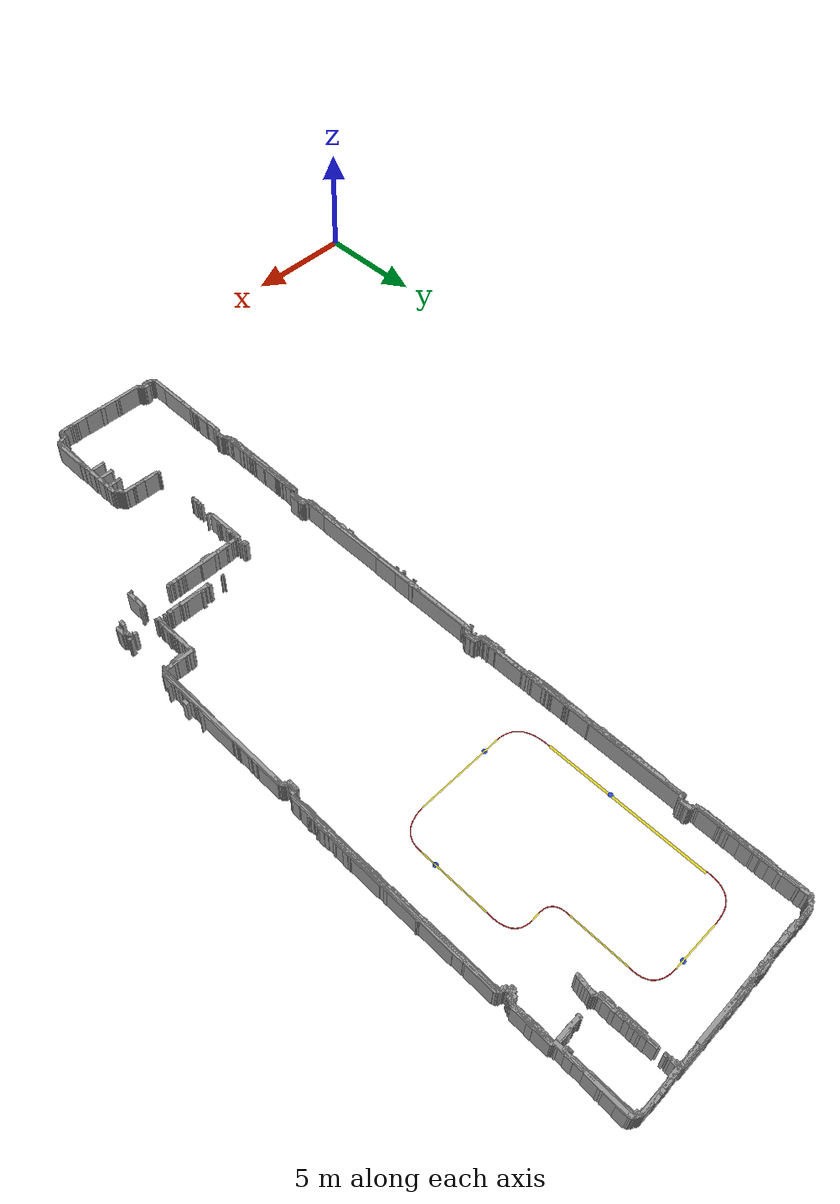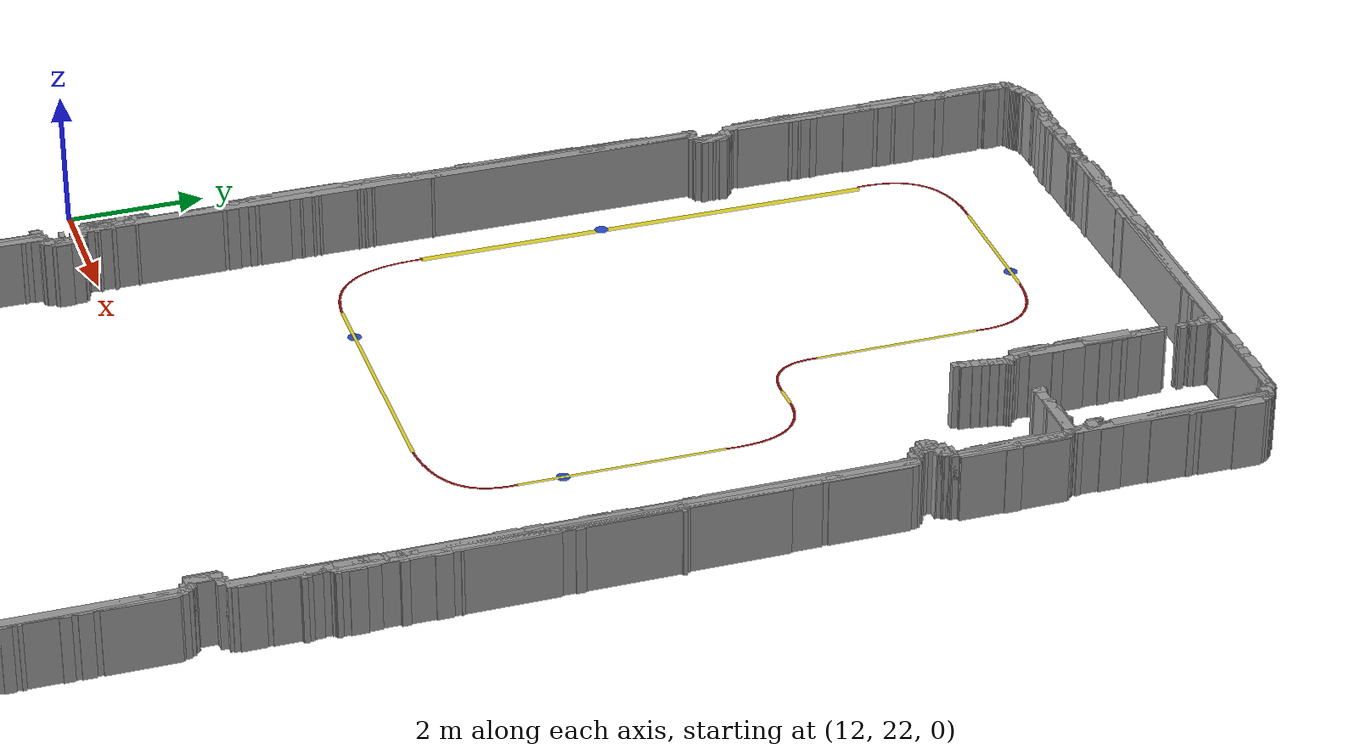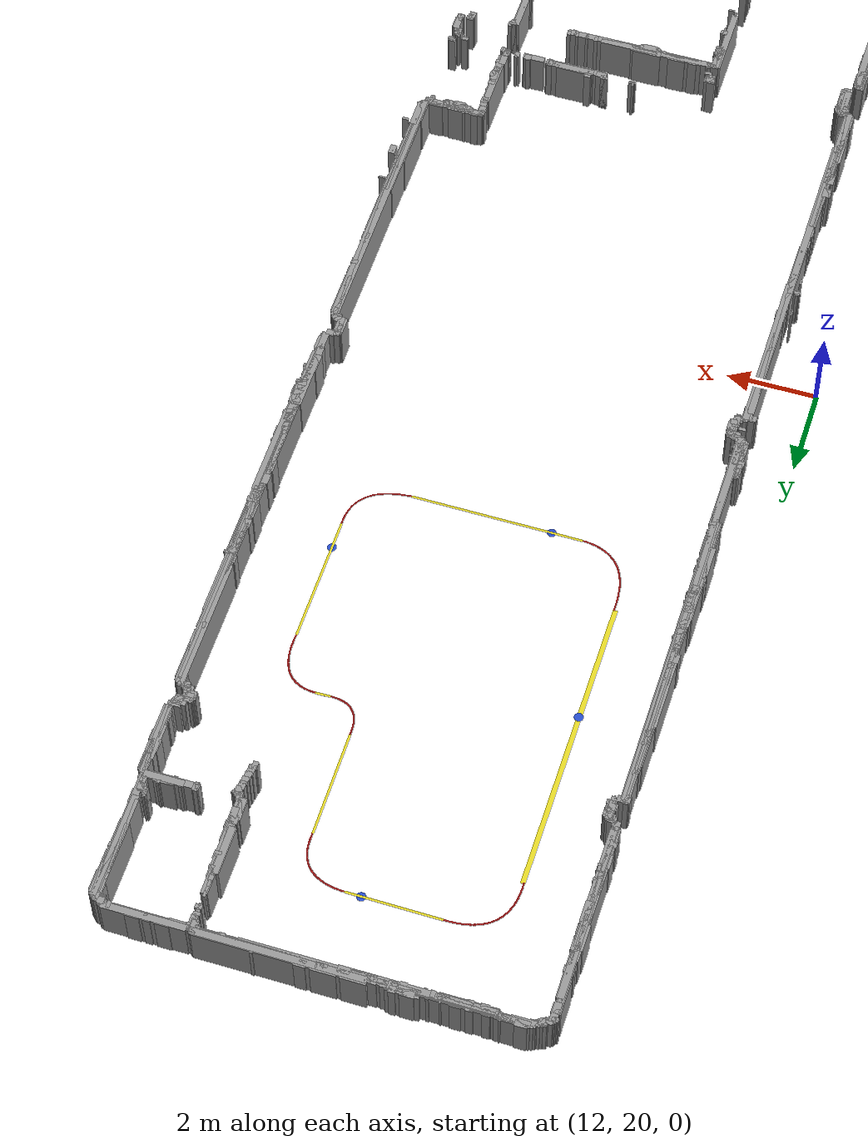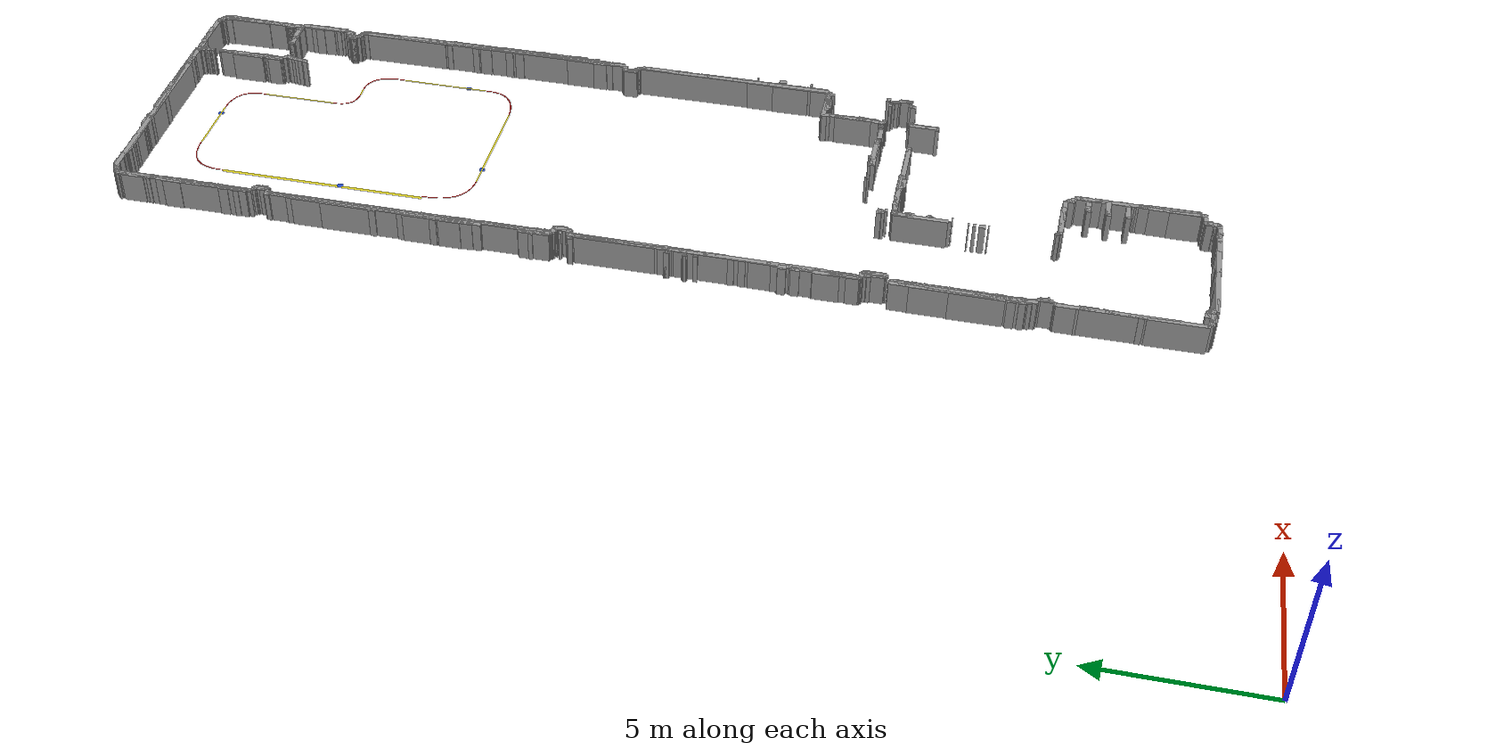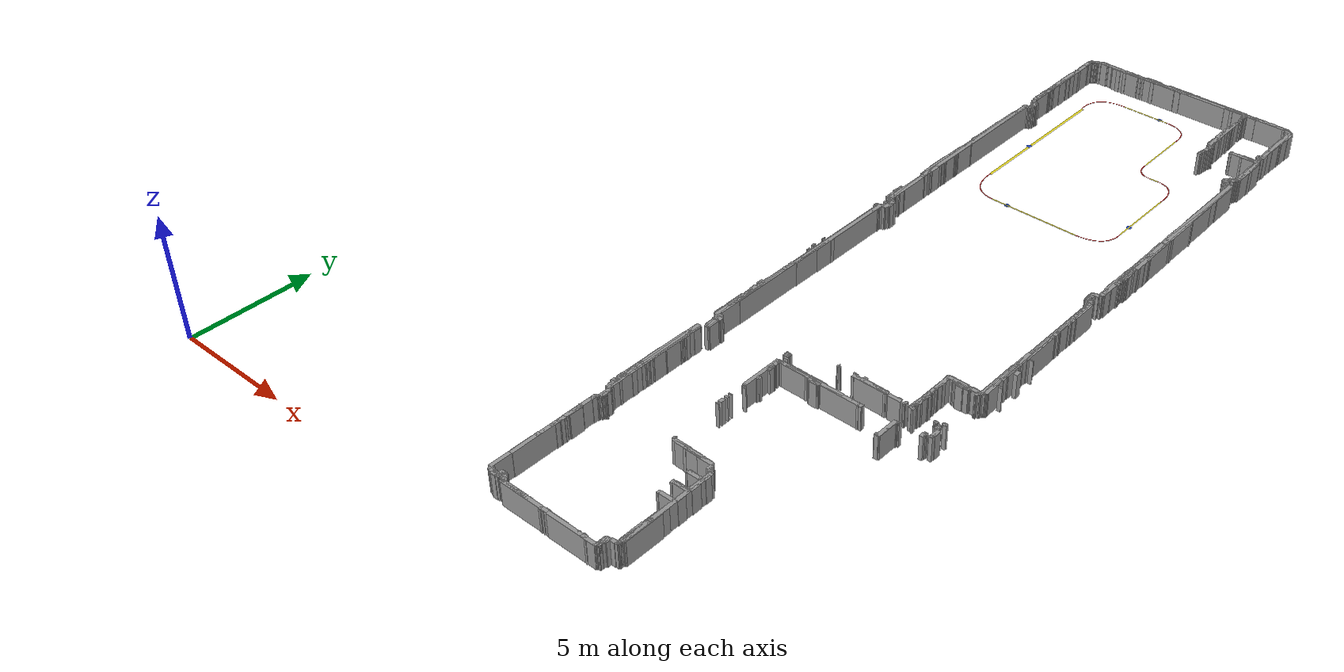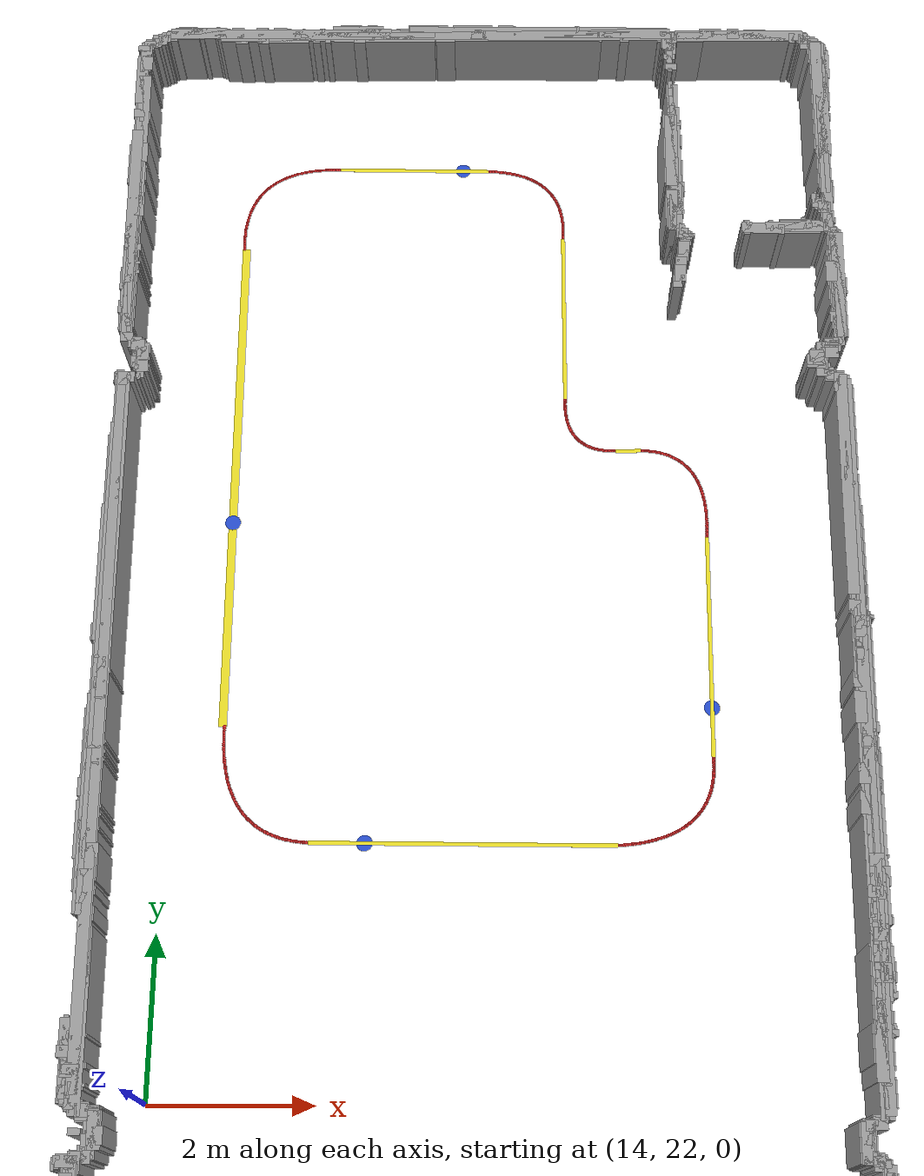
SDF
<sdf version="1.6">
  <world name="default">
    <include>
      <uri>model://sun</uri>
    </include>
    <physics type="ode">
      <real_time_update_rate>1000.0</real_time_update_rate>
      <max_step_size>0.001</max_step_size>
      <real_time_factor>1</real_time_factor>
      <ode>
        <solver>
          <type>quick</type>
          <iters>150</iters>
          <precon_iters>0</precon_iters>
          <sor>1.400000</sor>
          <use_dynamic_moi_rescaling>1</use_dynamic_moi_rescaling>
        </solver>
        <constraints>
          <cfm>0.00001</cfm>
          <erp>0.2</erp>
          <contact_max_correcting_vel>2000.000000</contact_max_correcting_vel>
          <contact_surface_layer>0.01000</contact_surface_layer>
        </constraints>
      </ode>
    </physics>
    <scene>
      <ambient>0.4 0.4 0.4 1</ambient>
      <background>0.7 0.7 0.7 1</background>
      <shadows>true</shadows>
    </scene>
    <gui fullscreen="0">
      <camera name="user_camera">
        <pose>0.0 0.0 17.0 -1.5708 1.5708 0</pose>
        <view_controller>orbit</view_controller>
      </camera>
    </gui>
    <model name="obstacle">
      <static>1</static>
      <pose frame="">0 0 0 0 0 0</pose>
      <link name="obstacle">
        <collision name="obstacle_1">
          <pose>17.66 1.86 0 0 0 0</pose>
          <geometry>
            <box>
              <size>0.08 0.15 1.0</size>
            </box>
          </geometry>
        </collision>
        <visual name="obstacle_1">
          <pose>17.66 1.86 0 0 0 0</pose>
          <geometry>
            <box>
              <size>0.08 0.15 1.0</size>
            </box>
          </geometry>
          <material>
            <script>
              <uri>file://media/materials/scripts/gazebo.material</uri>
              <name>Gazebo/Grey</name>
            </script>
            <ambient>1 1 1 1</ambient>
          </material>
        </visual>
        <collision name="obstacle_2">
          <pose>15.68 1.8800000000000001 0 0 0 0</pose>
          <geometry>
            <box>
              <size>0.08 0.15 1.0</size>
            </box>
          </geometry>
        </collision>
        <visual name="obstacle_2">
          <pose>15.68 1.8800000000000001 0 0 0 0</pose>
          <geometry>
            <box>
              <size>0.08 0.15 1.0</size>
            </box>
          </geometry>
          <material>
            <script>
              <uri>file://media/materials/scripts/gazebo.material</uri>
              <name>Gazebo/Grey</name>
            </script>
            <ambient>1 1 1 1</ambient>
          </material>
        </visual>
        <collision name="obstacle_3">
          <pose>15.82 1.8800000000000001 0 0 0 0</pose>
          <geometry>
            <box>
              <size>0.08 0.15 1.0</size>
            </box>
          </geometry>
        </collision>
        <visual name="obstacle_3">
          <pose>15.82 1.8800000000000001 0 0 0 0</pose>
          <geometry>
            <box>
              <size>0.08 0.15 1.0</size>
            </box>
          </geometry>
          <material>
            <script>
              <uri>file://media/materials/scripts/gazebo.material</uri>
              <name>Gazebo/Grey</name>
            </script>
            <ambient>1 1 1 1</ambient>
          </material>
        </visual>
        <collision name="obstacle_4">
          <pose>17.0 1.8800000000000001 0 0 0 0</pose>
          <geometry>
            <box>
              <size>2.06 0.15 1.0</size>
            </box>
          </geometry>
        </collision>
        <visual name="obstacle_4">
          <pose>17.0 1.8800000000000001 0 0 0 0</pose>
          <geometry>
            <box>
              <size>2.06 0.15 1.0</size>
            </box>
          </geometry>
          <material>
            <script>
              <uri>file://media/materials/scripts/gazebo.material</uri>
              <name>Gazebo/Grey</name>
            </script>
            <ambient>1 1 1 1</ambient>
          </material>
        </visual>
        <collision name="obstacle_5">
          <pose>13.44 1.98 0 0 0 1.5708</pose>
          <geometry>
            <box>
              <size>0.16 0.15 1.0</size>
            </box>
          </geometry>
        </collision>
        <visual name="obstacle_5">
          <pose>13.44 1.98 0 0 0 1.5708</pose>
          <geometry>
            <box>
              <size>0.16 0.15 1.0</size>
            </box>
          </geometry>
          <material>
            <script>
              <uri>file://media/materials/scripts/gazebo.material</uri>
              <name>Gazebo/Grey</name>
            </script>
            <ambient>1 1 1 1</ambient>
          </material>
        </visual>
        <collision name="obstacle_6">
          <pose>13.46 1.98 0 0 0 1.5708</pose>
          <geometry>
            <box>
              <size>0.18 0.15 1.0</size>
            </box>
          </geometry>
        </collision>
        <visual name="obstacle_6">
          <pose>13.46 1.98 0 0 0 1.5708</pose>
          <geometry>
            <box>
              <size>0.18 0.15 1.0</size>
            </box>
          </geometry>
          <material>
            <script>
              <uri>file://media/materials/scripts/gazebo.material</uri>
              <name>Gazebo/Grey</name>
            </script>
            <ambient>1 1 1 1</ambient>
          </material>
        </visual>
        <collision name="obstacle_7">
          <pose>13.48 1.98 0 0 0 1.5708</pose>
          <geometry>
            <box>
              <size>0.16 0.15 1.0</size>
            </box>
          </geometry>
        </collision>
        <visual name="obstacle_7">
          <pose>13.48 1.98 0 0 0 1.5708</pose>
          <geometry>
            <box>
              <size>0.16 0.15 1.0</size>
            </box>
          </geometry>
          <material>
            <script>
              <uri>file://media/materials/scripts/gazebo.material</uri>
              <name>Gazebo/Grey</name>
            </script>
            <ambient>1 1 1 1</ambient>
          </material>
        </visual>
        <collision name="obstacle_8">
          <pose>13.5 1.96 0 0 0 1.5708</pose>
          <geometry>
            <box>
              <size>0.14 0.15 1.0</size>
            </box>
          </geometry>
        </collision>
        <visual name="obstacle_8">
          <pose>13.5 1.96 0 0 0 1.5708</pose>
          <geometry>
            <box>
              <size>0.14 0.15 1.0</size>
            </box>
          </geometry>
          <material>
            <script>
              <uri>file://media/materials/scripts/gazebo.material</uri>
              <name>Gazebo/Grey</name>
            </script>
            <ambient>1 1 1 1</ambient>
          </material>
        </visual>
        <collision name="obstacle_9">
          <pose>15.34 1.9000000000000001 0 0 0 0</pose>
          <geometry>
            <box>
              <size>2.88 0.15 1.0</size>
            </box>
          </geometry>
        </collision>
        <visual name="obstacle_9">
          <pose>15.34 1.9000000000000001 0 0 0 0</pose>
          <geometry>
            <box>
              <size>2.88 0.15 1.0</size>
            </box>
          </geometry>
          <material>
            <script>
              <uri>file://media/materials/scripts/gazebo.material</uri>
              <name>Gazebo/Grey</name>
            </script>
            <ambient>1 1 1 1</ambient>
          </material>
        </visual>
        <collision name="obstacle_12">
          <pose>17.28 1.9000000000000001 0 0 0 0</pose>
          <geometry>
            <box>
              <size>0.1 0.15 1.0</size>
            </box>
          </geometry>
        </collision>
        <visual name="obstacle_12">
          <pose>17.28 1.9000000000000001 0 0 0 0</pose>
          <geometry>
            <box>
              <size>0.1 0.15 1.0</size>
            </box>
          </geometry>
          <material>
            <script>
              <uri>file://media/materials/scripts/gazebo.material</uri>
              <name>Gazebo/Grey</name>
            </script>
            <ambient>1 1 1 1</ambient>
          </material>
        </visual>
        <collision name="obstacle_13">
          <pose>17.52 1.9000000000000001 0 0 0 0</pose>
          <geometry>
            <box>
              <size>0.2 0.15 1.0</size>
            </box>
          </geometry>
        </collision>
        <visual name="obstacle_13">
          <pose>17.52 1.9000000000000001 0 0 0 0</pose>
          <geometry>
            <box>
              <size>0.2 0.15 1.0</size>
            </box>
          </geometry>
          <material>
            <script>
              <uri>file://media/materials/scripts/gazebo.material</uri>
              <name>Gazebo/Grey</name>
            </script>
            <ambient>1 1 1 1</ambient>
          </material>
        </visual>
        <collision name="obstacle_14">
          <pose>18.0 1.9000000000000001 0 0 0 0</pose>
          <geometry>
            <box>
              <size>0.14 0.15 1.0</size>
            </box>
          </geometry>
        </collision>
        <visual name="obstacle_14">
          <pose>18.0 1.9000000000000001 0 0 0 0</pose>
          <geometry>
            <box>
              <size>0.14 0.15 1.0</size>
            </box>
          </geometry>
          <material>
            <script>
              <uri>file://media/materials/scripts/gazebo.material</uri>
              <name>Gazebo/Grey</name>
            </script>
            <ambient>1 1 1 1</ambient>
          </material>
        </visual>
        <collision name="obstacle_15">
          <pose>13.52 1.98 0 0 0 1.5708</pose>
          <geometry>
            <box>
              <size>0.12 0.15 1.0</size>
            </box>
          </geometry>
        </collision>
        <visual name="obstacle_15">
          <pose>13.52 1.98 0 0 0 1.5708</pose>
          <geometry>
            <box>
              <size>0.12 0.15 1.0</size>
            </box>
          </geometry>
          <material>
            <script>
              <uri>file://media/materials/scripts/gazebo.material</uri>
              <name>Gazebo/Grey</name>
            </script>
            <ambient>1 1 1 1</ambient>
          </material>
        </visual>
        <collision name="obstacle_16">
          <pose>14.44 1.92 0 0 0 0</pose>
          <geometry>
            <box>
              <size>1.16 0.15 1.0</size>
            </box>
          </geometry>
        </collision>
        <visual name="obstacle_16">
          <pose>14.44 1.92 0 0 0 0</pose>
          <geometry>
            <box>
              <size>1.16 0.15 1.0</size>
            </box>
          </geometry>
          <material>
            <script>
              <uri>file://media/materials/scripts/gazebo.material</uri>
              <name>Gazebo/Grey</name>
            </script>
            <ambient>1 1 1 1</ambient>
          </material>
        </visual>
        <collision name="obstacle_17">
          <pose>15.16 1.92 0 0 0 0</pose>
          <geometry>
            <box>
              <size>0.12 0.15 1.0</size>
            </box>
          </geometry>
        </collision>
        <visual name="obstacle_17">
          <pose>15.16 1.92 0 0 0 0</pose>
          <geometry>
            <box>
              <size>0.12 0.15 1.0</size>
            </box>
          </geometry>
          <material>
            <script>
              <uri>file://media/materials/scripts/gazebo.material</uri>
              <name>Gazebo/Grey</name>
            </script>
            <ambient>1 1 1 1</ambient>
          </material>
        </visual>
        <collision name="obstacle_18">
          <pose>15.92 1.92 0 0 0 0</pose>
          <geometry>
            <box>
              <size>0.2 0.15 1.0</size>
            </box>
          </geometry>
        </collision>
        <visual name="obstacle_18">
          <pose>15.92 1.92 0 0 0 0</pose>
          <geometry>
            <box>
              <size>0.2 0.15 1.0</size>
            </box>
          </geometry>
          <material>
            <script>
              <uri>file://media/materials/scripts/gazebo.material</uri>
              <name>Gazebo/Grey</name>
            </script>
            <ambient>1 1 1 1</ambient>
          </material>
        </visual>
        <collision name="obstacle_20">
          <pose>17.48 1.92 0 0 0 0</pose>
          <geometry>
            <box>
              <size>0.1 0.15 1.0</size>
            </box>
          </geometry>
        </collision>
        <visual name="obstacle_20">
          <pose>17.48 1.92 0 0 0 0</pose>
          <geometry>
            <box>
              <size>0.1 0.15 1.0</size>
            </box>
          </geometry>
          <material>
            <script>
              <uri>file://media/materials/scripts/gazebo.material</uri>
              <name>Gazebo/Grey</name>
            </script>
            <ambient>1 1 1 1</ambient>
          </material>
        </visual>
        <collision name="obstacle_21">
          <pose>18.04 1.92 0 0 0 0</pose>
          <geometry>
            <box>
              <size>0.12 0.15 1.0</size>
            </box>
          </geometry>
        </collision>
        <visual name="obstacle_21">
          <pose>18.04 1.92 0 0 0 0</pose>
          <geometry>
            <box>
              <size>0.12 0.15 1.0</size>
            </box>
          </geometry>
          <material>
            <script>
              <uri>file://media/materials/scripts/gazebo.material</uri>
              <name>Gazebo/Grey</name>
            </script>
            <ambient>1 1 1 1</ambient>
          </material>
        </visual>
        <collision name="obstacle_22">
          <pose>13.540000000000001 1.98 0 0 0 1.5708</pose>
          <geometry>
            <box>
              <size>0.1 0.15 1.0</size>
            </box>
          </geometry>
        </collision>
        <visual name="obstacle_22">
          <pose>13.540000000000001 1.98 0 0 0 1.5708</pose>
          <geometry>
            <box>
              <size>0.1 0.15 1.0</size>
            </box>
          </geometry>
          <material>
            <script>
              <uri>file://media/materials/scripts/gazebo.material</uri>
              <name>Gazebo/Grey</name>
            </script>
            <ambient>1 1 1 1</ambient>
          </material>
        </visual>
        <collision name="obstacle_23">
          <pose>13.56 1.98 0 0 0 1.5708</pose>
          <geometry>
            <box>
              <size>0.1 0.15 1.0</size>
            </box>
          </geometry>
        </collision>
        <visual name="obstacle_23">
          <pose>13.56 1.98 0 0 0 1.5708</pose>
          <geometry>
            <box>
              <size>0.1 0.15 1.0</size>
            </box>
          </geometry>
          <material>
            <script>
              <uri>file://media/materials/scripts/gazebo.material</uri>
              <name>Gazebo/Grey</name>
            </script>
            <ambient>1 1 1 1</ambient>
          </material>
        </visual>
        <collision name="obstacle_24">
          <pose>13.86 2.04 0 0 0 1.5708</pose>
          <geometry>
            <box>
              <size>0.2 0.15 1.0</size>
            </box>
          </geometry>
        </collision>
        <visual name="obstacle_24">
          <pose>13.86 2.04 0 0 0 1.5708</pose>
          <geometry>
            <box>
              <size>0.2 0.15 1.0</size>
            </box>
          </geometry>
          <material>
            <script>
              <uri>file://media/materials/scripts/gazebo.material</uri>
              <name>Gazebo/Grey</name>
            </script>
            <ambient>1 1 1 1</ambient>
          </material>
        </visual>
        <collision name="obstacle_25">
          <pose>13.88 2.02 0 0 0 1.5708</pose>
          <geometry>
            <box>
              <size>0.18 0.15 1.0</size>
            </box>
          </geometry>
        </collision>
        <visual name="obstacle_25">
          <pose>13.88 2.02 0 0 0 1.5708</pose>
          <geometry>
            <box>
              <size>0.18 0.15 1.0</size>
            </box>
          </geometry>
          <material>
            <script>
              <uri>file://media/materials/scripts/gazebo.material</uri>
              <name>Gazebo/Grey</name>
            </script>
            <ambient>1 1 1 1</ambient>
          </material>
        </visual>
        <collision name="obstacle_26">
          <pose>13.9 2.02 0 0 0 1.5708</pose>
          <geometry>
            <box>
              <size>0.16 0.15 1.0</size>
            </box>
          </geometry>
        </collision>
        <visual name="obstacle_26">
          <pose>13.9 2.02 0 0 0 1.5708</pose>
          <geometry>
            <box>
              <size>0.16 0.15 1.0</size>
            </box>
          </geometry>
          <material>
            <script>
              <uri>file://media/materials/scripts/gazebo.material</uri>
              <name>Gazebo/Grey</name>
            </script>
            <ambient>1 1 1 1</ambient>
          </material>
        </visual>
        <collision name="obstacle_27">
          <pose>13.92 2.0 0 0 0 1.5708</pose>
          <geometry>
            <box>
              <size>0.14 0.15 1.0</size>
            </box>
          </geometry>
        </collision>
        <visual name="obstacle_27">
          <pose>13.92 2.0 0 0 0 1.5708</pose>
          <geometry>
            <box>
              <size>0.14 0.15 1.0</size>
            </box>
          </geometry>
          <material>
            <script>
              <uri>file://media/materials/scripts/gazebo.material</uri>
              <name>Gazebo/Grey</name>
            </script>
            <ambient>1 1 1 1</ambient>
          </material>
        </visual>
        <collision name="obstacle_28">
          <pose>13.98 1.94 0 0 0 0</pose>
          <geometry>
            <box>
              <size>0.1 0.15 1.0</size>
            </box>
          </geometry>
        </collision>
        <visual name="obstacle_28">
          <pose>13.98 1.94 0 0 0 0</pose>
          <geometry>
            <box>
              <size>0.1 0.15 1.0</size>
            </box>
          </geometry>
          <material>
            <script>
              <uri>file://media/materials/scripts/gazebo.material</uri>
              <name>Gazebo/Grey</name>
            </script>
            <ambient>1 1 1 1</ambient>
          </material>
        </visual>
        <collision name="obstacle_29">
          <pose>18.080000000000002 1.94 0 0 0 0</pose>
          <geometry>
            <box>
              <size>0.16 0.15 1.0</size>
            </box>
          </geometry>
        </collision>
        <visual name="obstacle_29">
          <pose>18.080000000000002 1.94 0 0 0 0</pose>
          <geometry>
            <box>
              <size>0.16 0.15 1.0</size>
            </box>
          </geometry>
          <material>
            <script>
              <uri>file://media/materials/scripts/gazebo.material</uri>
              <name>Gazebo/Grey</name>
            </script>
            <ambient>1 1 1 1</ambient>
          </material>
        </visual>
        <collision name="obstacle_30">
          <pose>13.5 1.96 0 0 0 0</pose>
          <geometry>
            <box>
              <size>0.2 0.15 1.0</size>
            </box>
          </geometry>
        </collision>
        <visual name="obstacle_30">
          <pose>13.5 1.96 0 0 0 0</pose>
          <geometry>
            <box>
              <size>0.2 0.15 1.0</size>
            </box>
          </geometry>
          <material>
            <script>
              <uri>file://media/materials/scripts/gazebo.material</uri>
              <name>Gazebo/Grey</name>
            </script>
            <ambient>1 1 1 1</ambient>
          </material>
        </visual>
        <collision name="obstacle_31">
          <pose>13.84 2.06 0 0 0 1.5708</pose>
          <geometry>
            <box>
              <size>0.2 0.15 1.0</size>
            </box>
          </geometry>
        </collision>
        <visual name="obstacle_31">
          <pose>13.84 2.06 0 0 0 1.5708</pose>
          <geometry>
            <box>
              <size>0.2 0.15 1.0</size>
            </box>
          </geometry>
          <material>
            <script>
              <uri>file://media/materials/scripts/gazebo.material</uri>
              <name>Gazebo/Grey</name>
            </script>
            <ambient>1 1 1 1</ambient>
          </material>
        </visual>
        <collision name="obstacle_32">
          <pose>13.94 2.0 0 0 0 1.5708</pose>
          <geometry>
            <box>
              <size>0.08 0.15 1.0</size>
            </box>
          </geometry>
        </collision>
        <visual name="obstacle_32">
          <pose>13.94 2.0 0 0 0 1.5708</pose>
          <geometry>
            <box>
              <size>0.08 0.15 1.0</size>
            </box>
          </geometry>
          <material>
            <script>
              <uri>file://media/materials/scripts/gazebo.material</uri>
              <name>Gazebo/Grey</name>
            </script>
            <ambient>1 1 1 1</ambient>
          </material>
        </visual>
        <collision name="obstacle_33">
          <pose>13.96 1.98 0 0 0 1.5708</pose>
          <geometry>
            <box>
              <size>0.04 0.15 1.0</size>
            </box>
          </geometry>
        </collision>
        <visual name="obstacle_33">
          <pose>13.96 1.98 0 0 0 1.5708</pose>
          <geometry>
            <box>
              <size>0.04 0.15 1.0</size>
            </box>
          </geometry>
          <material>
            <script>
              <uri>file://media/materials/scripts/gazebo.material</uri>
              <name>Gazebo/Grey</name>
            </script>
            <ambient>1 1 1 1</ambient>
          </material>
        </visual>
        <collision name="obstacle_34">
          <pose>18.080000000000002 1.96 0 0 0 0</pose>
          <geometry>
            <box>
              <size>0.18 0.15 1.0</size>
            </box>
          </geometry>
        </collision>
        <visual name="obstacle_34">
          <pose>18.080000000000002 1.96 0 0 0 0</pose>
          <geometry>
            <box>
              <size>0.18 0.15 1.0</size>
            </box>
          </geometry>
          <material>
            <script>
              <uri>file://media/materials/scripts/gazebo.material</uri>
              <name>Gazebo/Grey</name>
            </script>
            <ambient>1 1 1 1</ambient>
          </material>
        </visual>
        <collision name="obstacle_35">
          <pose>13.540000000000001 1.98 0 0 0 0</pose>
          <geometry>
            <box>
              <size>0.34 0.15 1.0</size>
            </box>
          </geometry>
        </collision>
        <visual name="obstacle_35">
          <pose>13.540000000000001 1.98 0 0 0 0</pose>
          <geometry>
            <box>
              <size>0.34 0.15 1.0</size>
            </box>
          </geometry>
          <material>
            <script>
              <uri>file://media/materials/scripts/gazebo.material</uri>
              <name>Gazebo/Grey</name>
            </script>
            <ambient>1 1 1 1</ambient>
          </material>
        </visual>
        <collision name="obstacle_36">
          <pose>18.080000000000002 1.98 0 0 0 0</pose>
          <geometry>
            <box>
              <size>0.18 0.15 1.0</size>
            </box>
          </geometry>
        </collision>
        <visual name="obstacle_36">
          <pose>18.080000000000002 1.98 0 0 0 0</pose>
          <geometry>
            <box>
              <size>0.18 0.15 1.0</size>
            </box>
          </geometry>
          <material>
            <script>
              <uri>file://media/materials/scripts/gazebo.material</uri>
              <name>Gazebo/Grey</name>
            </script>
            <ambient>1 1 1 1</ambient>
          </material>
        </visual>
        <collision name="obstacle_37">
          <pose>13.540000000000001 2.0 0 0 0 0</pose>
          <geometry>
            <box>
              <size>0.4 0.15 1.0</size>
            </box>
          </geometry>
        </collision>
        <visual name="obstacle_37">
          <pose>13.540000000000001 2.0 0 0 0 0</pose>
          <geometry>
            <box>
              <size>0.4 0.15 1.0</size>
            </box>
          </geometry>
          <material>
            <script>
              <uri>file://media/materials/scripts/gazebo.material</uri>
              <name>Gazebo/Grey</name>
            </script>
            <ambient>1 1 1 1</ambient>
          </material>
        </visual>
        <collision name="obstacle_38">
          <pose>13.8 2.08 0 0 0 1.5708</pose>
          <geometry>
            <box>
              <size>0.18 0.15 1.0</size>
            </box>
          </geometry>
        </collision>
        <visual name="obstacle_38">
          <pose>13.8 2.08 0 0 0 1.5708</pose>
          <geometry>
            <box>
              <size>0.18 0.15 1.0</size>
            </box>
          </geometry>
          <material>
            <script>
              <uri>file://media/materials/scripts/gazebo.material</uri>
              <name>Gazebo/Grey</name>
            </script>
            <ambient>1 1 1 1</ambient>
          </material>
        </visual>
        <collision name="obstacle_39">
          <pose>13.82 2.08 0 0 0 1.5708</pose>
          <geometry>
            <box>
              <size>0.16 0.15 1.0</size>
            </box>
          </geometry>
        </collision>
        <visual name="obstacle_39">
          <pose>13.82 2.08 0 0 0 1.5708</pose>
          <geometry>
            <box>
              <size>0.16 0.15 1.0</size>
            </box>
          </geometry>
          <material>
            <script>
              <uri>file://media/materials/scripts/gazebo.material</uri>
              <name>Gazebo/Grey</name>
            </script>
            <ambient>1 1 1 1</ambient>
          </material>
        </visual>
        <collision name="obstacle_40">
          <pose>18.080000000000002 2.0 0 0 0 0</pose>
          <geometry>
            <box>
              <size>0.18 0.15 1.0</size>
            </box>
          </geometry>
        </collision>
        <visual name="obstacle_40">
          <pose>18.080000000000002 2.0 0 0 0 0</pose>
          <geometry>
            <box>
              <size>0.18 0.15 1.0</size>
            </box>
          </geometry>
          <material>
            <script>
              <uri>file://media/materials/scripts/gazebo.material</uri>
              <name>Gazebo/Grey</name>
            </script>
            <ambient>1 1 1 1</ambient>
          </material>
        </visual>
        <collision name="obstacle_41">
          <pose>13.44 2.02 0 0 0 0</pose>
          <geometry>
            <box>
              <size>0.38 0.15 1.0</size>
            </box>
          </geometry>
        </collision>
        <visual name="obstacle_41">
          <pose>13.44 2.02 0 0 0 0</pose>
          <geometry>
            <box>
              <size>0.38 0.15 1.0</size>
            </box>
          </geometry>
          <material>
            <script>
              <uri>file://media/materials/scripts/gazebo.material</uri>
              <name>Gazebo/Grey</name>
            </script>
            <ambient>1 1 1 1</ambient>
          </material>
        </visual>
        <collision name="obstacle_42">
          <pose>13.86 2.02 0 0 0 0</pose>
          <geometry>
            <box>
              <size>0.2 0.15 1.0</size>
            </box>
          </geometry>
        </collision>
        <visual name="obstacle_42">
          <pose>13.86 2.02 0 0 0 0</pose>
          <geometry>
            <box>
              <size>0.2 0.15 1.0</size>
            </box>
          </geometry>
          <material>
            <script>
              <uri>file://media/materials/scripts/gazebo.material</uri>
              <name>Gazebo/Grey</name>
            </script>
            <ambient>1 1 1 1</ambient>
          </material>
        </visual>
        <collision name="obstacle_43">
          <pose>18.080000000000002 2.02 0 0 0 0</pose>
          <geometry>
            <box>
              <size>0.18 0.15 1.0</size>
            </box>
          </geometry>
        </collision>
        <visual name="obstacle_43">
          <pose>18.080000000000002 2.02 0 0 0 0</pose>
          <geometry>
            <box>
              <size>0.18 0.15 1.0</size>
            </box>
          </geometry>
          <material>
            <script>
              <uri>file://media/materials/scripts/gazebo.material</uri>
              <name>Gazebo/Grey</name>
            </script>
            <ambient>1 1 1 1</ambient>
          </material>
        </visual>
        <collision name="obstacle_44">
          <pose>13.34 2.04 0 0 0 0</pose>
          <geometry>
            <box>
              <size>0.3 0.15 1.0</size>
            </box>
          </geometry>
        </collision>
        <visual name="obstacle_44">
          <pose>13.34 2.04 0 0 0 0</pose>
          <geometry>
            <box>
              <size>0.3 0.15 1.0</size>
            </box>
          </geometry>
          <material>
            <script>
              <uri>file://media/materials/scripts/gazebo.material</uri>
              <name>Gazebo/Grey</name>
            </script>
            <ambient>1 1 1 1</ambient>
          </material>
        </visual>
        <collision name="obstacle_45">
          <pose>13.84 2.04 0 0 0 0</pose>
          <geometry>
            <box>
              <size>0.18 0.15 1.0</size>
            </box>
          </geometry>
        </collision>
        <visual name="obstacle_45">
          <pose>13.84 2.04 0 0 0 0</pose>
          <geometry>
            <box>
              <size>0.18 0.15 1.0</size>
            </box>
          </geometry>
          <material>
            <script>
              <uri>file://media/materials/scripts/gazebo.material</uri>
              <name>Gazebo/Grey</name>
            </script>
            <ambient>1 1 1 1</ambient>
          </material>
        </visual>
        <collision name="obstacle_46">
          <pose>18.080000000000002 2.04 0 0 0 0</pose>
          <geometry>
            <box>
              <size>0.18 0.15 1.0</size>
            </box>
          </geometry>
        </collision>
        <visual name="obstacle_46">
          <pose>18.080000000000002 2.04 0 0 0 0</pose>
          <geometry>
            <box>
              <size>0.18 0.15 1.0</size>
            </box>
          </geometry>
          <material>
            <script>
              <uri>file://media/materials/scripts/gazebo.material</uri>
              <name>Gazebo/Grey</name>
            </script>
            <ambient>1 1 1 1</ambient>
          </material>
        </visual>
        <collision name="obstacle_47">
          <pose>13.26 2.06 0 0 0 0</pose>
          <geometry>
            <box>
              <size>0.2 0.15 1.0</size>
            </box>
          </geometry>
        </collision>
        <visual name="obstacle_47">
          <pose>13.26 2.06 0 0 0 0</pose>
          <geometry>
            <box>
              <size>0.2 0.15 1.0</size>
            </box>
          </geometry>
          <material>
            <script>
              <uri>file://media/materials/scripts/gazebo.material</uri>
              <name>Gazebo/Grey</name>
            </script>
            <ambient>1 1 1 1</ambient>
          </material>
        </visual>
        <collision name="obstacle_48">
          <pose>13.84 2.06 0 0 0 0</pose>
          <geometry>
            <box>
              <size>0.18 0.15 1.0</size>
            </box>
          </geometry>
        </collision>
        <visual name="obstacle_48">
          <pose>13.84 2.06 0 0 0 0</pose>
          <geometry>
            <box>
              <size>0.18 0.15 1.0</size>
            </box>
          </geometry>
          <material>
            <script>
              <uri>file://media/materials/scripts/gazebo.material</uri>
              <name>Gazebo/Grey</name>
            </script>
            <ambient>1 1 1 1</ambient>
          </material>
        </visual>
        <collision name="obstacle_49">
          <pose>18.1 2.06 0 0 0 0</pose>
          <geometry>
            <box>
              <size>0.16 0.15 1.0</size>
            </box>
          </geometry>
        </collision>
        <visual name="obstacle_49">
          <pose>18.1 2.06 0 0 0 0</pose>
          <geometry>
            <box>
              <size>0.16 0.15 1.0</size>
            </box>
          </geometry>
          <material>
            <script>
              <uri>file://media/materials/scripts/gazebo.material</uri>
              <name>Gazebo/Grey</name>
            </script>
            <ambient>1 1 1 1</ambient>
          </material>
        </visual>
        <collision name="obstacle_50">
          <pose>13.24 2.08 0 0 0 0</pose>
          <geometry>
            <box>
              <size>0.16 0.15 1.0</size>
            </box>
          </geometry>
        </collision>
        <visual name="obstacle_50">
          <pose>13.24 2.08 0 0 0 0</pose>
          <geometry>
            <box>
              <size>0.16 0.15 1.0</size>
            </box>
          </geometry>
          <material>
            <script>
              <uri>file://media/materials/scripts/gazebo.material</uri>
              <name>Gazebo/Grey</name>
            </script>
            <ambient>1 1 1 1</ambient>
          </material>
        </visual>
        <collision name="obstacle_51">
          <pose>13.84 2.08 0 0 0 0</pose>
          <geometry>
            <box>
              <size>0.14 0.15 1.0</size>
            </box>
          </geometry>
        </collision>
        <visual name="obstacle_51">
          <pose>13.84 2.08 0 0 0 0</pose>
          <geometry>
            <box>
              <size>0.14 0.15 1.0</size>
            </box>
          </geometry>
          <material>
            <script>
              <uri>file://media/materials/scripts/gazebo.material</uri>
              <name>Gazebo/Grey</name>
            </script>
            <ambient>1 1 1 1</ambient>
          </material>
        </visual>
        <collision name="obstacle_52">
          <pose>18.1 2.08 0 0 0 0</pose>
          <geometry>
            <box>
              <size>0.14 0.15 1.0</size>
            </box>
          </geometry>
        </collision>
        <visual name="obstacle_52">
          <pose>18.1 2.08 0 0 0 0</pose>
          <geometry>
            <box>
              <size>0.14 0.15 1.0</size>
            </box>
          </geometry>
          <material>
            <script>
              <uri>file://media/materials/scripts/gazebo.material</uri>
              <name>Gazebo/Grey</name>
            </script>
            <ambient>1 1 1 1</ambient>
          </material>
        </visual>
        <collision name="obstacle_53">
          <pose>13.14 3.0 0 0 0 1.5708</pose>
          <geometry>
            <box>
              <size>1.82 0.15 1.0</size>
            </box>
          </geometry>
        </collision>
        <visual name="obstacle_53">
          <pose>13.14 3.0 0 0 0 1.5708</pose>
          <geometry>
            <box>
              <size>1.82 0.15 1.0</size>
            </box>
          </geometry>
          <material>
            <script>
              <uri>file://media/materials/scripts/gazebo.material</uri>
              <name>Gazebo/Grey</name>
            </script>
            <ambient>1 1 1 1</ambient>
          </material>
        </visual>
        <collision name="obstacle_54">
          <pose>13.16 2.14 0 0 0 1.5708</pose>
          <geometry>
            <box>
              <size>0.1 0.15 1.0</size>
            </box>
          </geometry>
        </collision>
        <visual name="obstacle_54">
          <pose>13.16 2.14 0 0 0 1.5708</pose>
          <geometry>
            <box>
              <size>0.1 0.15 1.0</size>
            </box>
          </geometry>
          <material>
            <script>
              <uri>file://media/materials/scripts/gazebo.material</uri>
              <name>Gazebo/Grey</name>
            </script>
            <ambient>1 1 1 1</ambient>
          </material>
        </visual>
        <collision name="obstacle_55">
          <pose>13.18 2.14 0 0 0 1.5708</pose>
          <geometry>
            <box>
              <size>0.08 0.15 1.0</size>
            </box>
          </geometry>
        </collision>
        <visual name="obstacle_55">
          <pose>13.18 2.14 0 0 0 1.5708</pose>
          <geometry>
            <box>
              <size>0.08 0.15 1.0</size>
            </box>
          </geometry>
          <material>
            <script>
              <uri>file://media/materials/scripts/gazebo.material</uri>
              <name>Gazebo/Grey</name>
            </script>
            <ambient>1 1 1 1</ambient>
          </material>
        </visual>
        <collision name="obstacle_56">
          <pose>13.200000000000001 2.14 0 0 0 1.5708</pose>
          <geometry>
            <box>
              <size>0.08 0.15 1.0</size>
            </box>
          </geometry>
        </collision>
        <visual name="obstacle_56">
          <pose>13.200000000000001 2.14 0 0 0 1.5708</pose>
          <geometry>
            <box>
              <size>0.08 0.15 1.0</size>
            </box>
          </geometry>
          <material>
            <script>
              <uri>file://media/materials/scripts/gazebo.material</uri>
              <name>Gazebo/Grey</name>
            </script>
            <ambient>1 1 1 1</ambient>
          </material>
        </visual>
        <collision name="obstacle_58">
          <pose>13.84 2.1 0 0 0 0</pose>
          <geometry>
            <box>
              <size>0.12 0.15 1.0</size>
            </box>
          </geometry>
        </collision>
        <visual name="obstacle_58">
          <pose>13.84 2.1 0 0 0 0</pose>
          <geometry>
            <box>
              <size>0.12 0.15 1.0</size>
            </box>
          </geometry>
          <material>
            <script>
              <uri>file://media/materials/scripts/gazebo.material</uri>
              <name>Gazebo/Grey</name>
            </script>
            <ambient>1 1 1 1</ambient>
          </material>
        </visual>
        <collision name="obstacle_59">
          <pose>18.06 2.2 0 0 0 1.5708</pose>
          <geometry>
            <box>
              <size>0.22 0.15 1.0</size>
            </box>
          </geometry>
        </collision>
        <visual name="obstacle_59">
          <pose>18.06 2.2 0 0 0 1.5708</pose>
          <geometry>
            <box>
              <size>0.22 0.15 1.0</size>
            </box>
          </geometry>
          <material>
            <script>
              <uri>file://media/materials/scripts/gazebo.material</uri>
              <name>Gazebo/Grey</name>
            </script>
            <ambient>1 1 1 1</ambient>
          </material>
        </visual>
        <collision name="obstacle_60">
          <pose>18.080000000000002 2.2 0 0 0 1.5708</pose>
          <geometry>
            <box>
              <size>0.22 0.15 1.0</size>
            </box>
          </geometry>
        </collision>
        <visual name="obstacle_60">
          <pose>18.080000000000002 2.2 0 0 0 1.5708</pose>
          <geometry>
            <box>
              <size>0.22 0.15 1.0</size>
            </box>
          </geometry>
          <material>
            <script>
              <uri>file://media/materials/scripts/gazebo.material</uri>
              <name>Gazebo/Grey</name>
            </script>
            <ambient>1 1 1 1</ambient>
          </material>
        </visual>
        <collision name="obstacle_61">
          <pose>18.1 2.22 0 0 0 1.5708</pose>
          <geometry>
            <box>
              <size>0.24 0.15 1.0</size>
            </box>
          </geometry>
        </collision>
        <visual name="obstacle_61">
          <pose>18.1 2.22 0 0 0 1.5708</pose>
          <geometry>
            <box>
              <size>0.24 0.15 1.0</size>
            </box>
          </geometry>
          <material>
            <script>
              <uri>file://media/materials/scripts/gazebo.material</uri>
              <name>Gazebo/Grey</name>
            </script>
            <ambient>1 1 1 1</ambient>
          </material>
        </visual>
        <collision name="obstacle_62">
          <pose>18.12 2.22 0 0 0 1.5708</pose>
          <geometry>
            <box>
              <size>0.24 0.15 1.0</size>
            </box>
          </geometry>
        </collision>
        <visual name="obstacle_62">
          <pose>18.12 2.22 0 0 0 1.5708</pose>
          <geometry>
            <box>
              <size>0.24 0.15 1.0</size>
            </box>
          </geometry>
          <material>
            <script>
              <uri>file://media/materials/scripts/gazebo.material</uri>
              <name>Gazebo/Grey</name>
            </script>
            <ambient>1 1 1 1</ambient>
          </material>
        </visual>
        <collision name="obstacle_63">
          <pose>18.14 2.22 0 0 0 1.5708</pose>
          <geometry>
            <box>
              <size>0.24 0.15 1.0</size>
            </box>
          </geometry>
        </collision>
        <visual name="obstacle_63">
          <pose>18.14 2.22 0 0 0 1.5708</pose>
          <geometry>
            <box>
              <size>0.24 0.15 1.0</size>
            </box>
          </geometry>
          <material>
            <script>
              <uri>file://media/materials/scripts/gazebo.material</uri>
              <name>Gazebo/Grey</name>
            </script>
            <ambient>1 1 1 1</ambient>
          </material>
        </visual>
        <collision name="obstacle_64">
          <pose>18.16 2.22 0 0 0 1.5708</pose>
          <geometry>
            <box>
              <size>0.24 0.15 1.0</size>
            </box>
          </geometry>
        </collision>
        <visual name="obstacle_64">
          <pose>18.16 2.22 0 0 0 1.5708</pose>
          <geometry>
            <box>
              <size>0.24 0.15 1.0</size>
            </box>
          </geometry>
          <material>
            <script>
              <uri>file://media/materials/scripts/gazebo.material</uri>
              <name>Gazebo/Grey</name>
            </script>
            <ambient>1 1 1 1</ambient>
          </material>
        </visual>
        <collision name="obstacle_65">
          <pose>13.82 2.12 0 0 0 0</pose>
          <geometry>
            <box>
              <size>0.1 0.15 1.0</size>
            </box>
          </geometry>
        </collision>
        <visual name="obstacle_65">
          <pose>13.82 2.12 0 0 0 0</pose>
          <geometry>
            <box>
              <size>0.1 0.15 1.0</size>
            </box>
          </geometry>
          <material>
            <script>
              <uri>file://media/materials/scripts/gazebo.material</uri>
              <name>Gazebo/Grey</name>
            </script>
            <ambient>1 1 1 1</ambient>
          </material>
        </visual>
        <collision name="obstacle_66">
          <pose>13.8 2.14 0 0 0 0</pose>
          <geometry>
            <box>
              <size>0.12 0.15 1.0</size>
            </box>
          </geometry>
        </collision>
        <visual name="obstacle_66">
          <pose>13.8 2.14 0 0 0 0</pose>
          <geometry>
            <box>
              <size>0.12 0.15 1.0</size>
            </box>
          </geometry>
          <material>
            <script>
              <uri>file://media/materials/scripts/gazebo.material</uri>
              <name>Gazebo/Grey</name>
            </script>
            <ambient>1 1 1 1</ambient>
          </material>
        </visual>
        <collision name="obstacle_67">
          <pose>13.68 2.16 0 0 0 0</pose>
          <geometry>
            <box>
              <size>0.28 0.15 1.0</size>
            </box>
          </geometry>
        </collision>
        <visual name="obstacle_67">
          <pose>13.68 2.16 0 0 0 0</pose>
          <geometry>
            <box>
              <size>0.28 0.15 1.0</size>
            </box>
          </geometry>
          <material>
            <script>
              <uri>file://media/materials/scripts/gazebo.material</uri>
              <name>Gazebo/Grey</name>
            </script>
            <ambient>1 1 1 1</ambient>
          </material>
        </visual>
        <collision name="obstacle_68">
          <pose>13.64 2.18 0 0 0 0</pose>
          <geometry>
            <box>
              <size>0.22 0.15 1.0</size>
            </box>
          </geometry>
        </collision>
        <visual name="obstacle_68">
          <pose>13.64 2.18 0 0 0 0</pose>
          <geometry>
            <box>
              <size>0.22 0.15 1.0</size>
            </box>
          </geometry>
          <material>
            <script>
              <uri>file://media/materials/scripts/gazebo.material</uri>
              <name>Gazebo/Grey</name>
            </script>
            <ambient>1 1 1 1</ambient>
          </material>
        </visual>
        <collision name="obstacle_70">
          <pose>18.1 2.2600000000000002 0 0 0 0</pose>
          <geometry>
            <box>
              <size>0.14 0.15 1.0</size>
            </box>
          </geometry>
        </collision>
        <visual name="obstacle_70">
          <pose>18.1 2.2600000000000002 0 0 0 0</pose>
          <geometry>
            <box>
              <size>0.14 0.15 1.0</size>
            </box>
          </geometry>
          <material>
            <script>
              <uri>file://media/materials/scripts/gazebo.material</uri>
              <name>Gazebo/Grey</name>
            </script>
            <ambient>1 1 1 1</ambient>
          </material>
        </visual>
        <collision name="obstacle_71">
          <pose>18.1 2.2800000000000002 0 0 0 0</pose>
          <geometry>
            <box>
              <size>0.14 0.15 1.0</size>
            </box>
          </geometry>
        </collision>
        <visual name="obstacle_71">
          <pose>18.1 2.2800000000000002 0 0 0 0</pose>
          <geometry>
            <box>
              <size>0.14 0.15 1.0</size>
            </box>
          </geometry>
          <material>
            <script>
              <uri>file://media/materials/scripts/gazebo.material</uri>
              <name>Gazebo/Grey</name>
            </script>
            <ambient>1 1 1 1</ambient>
          </material>
        </visual>
        <collision name="obstacle_72">
          <pose>18.18 2.32 0 0 0 1.5708</pose>
          <geometry>
            <box>
              <size>0.04 0.15 1.0</size>
            </box>
          </geometry>
        </collision>
        <visual name="obstacle_72">
          <pose>18.18 2.32 0 0 0 1.5708</pose>
          <geometry>
            <box>
              <size>0.04 0.15 1.0</size>
            </box>
          </geometry>
          <material>
            <script>
              <uri>file://media/materials/scripts/gazebo.material</uri>
              <name>Gazebo/Grey</name>
            </script>
            <ambient>1 1 1 1</ambient>
          </material>
        </visual>
        <collision name="obstacle_73">
          <pose>18.3 2.32 0 0 0 0</pose>
          <geometry>
            <box>
              <size>0.22 0.15 1.0</size>
            </box>
          </geometry>
        </collision>
        <visual name="obstacle_73">
          <pose>18.3 2.32 0 0 0 0</pose>
          <geometry>
            <box>
              <size>0.22 0.15 1.0</size>
            </box>
          </geometry>
          <material>
            <script>
              <uri>file://media/materials/scripts/gazebo.material</uri>
              <name>Gazebo/Grey</name>
            </script>
            <ambient>1 1 1 1</ambient>
          </material>
        </visual>
        <collision name="obstacle_74">
          <pose>18.42 2.34 0 0 0 0</pose>
          <geometry>
            <box>
              <size>0.2 0.15 1.0</size>
            </box>
          </geometry>
        </collision>
        <visual name="obstacle_74">
          <pose>18.42 2.34 0 0 0 0</pose>
          <geometry>
            <box>
              <size>0.2 0.15 1.0</size>
            </box>
          </geometry>
          <material>
            <script>
              <uri>file://media/materials/scripts/gazebo.material</uri>
              <name>Gazebo/Grey</name>
            </script>
            <ambient>1 1 1 1</ambient>
          </material>
        </visual>
        <collision name="obstacle_76">
          <pose>18.48 2.36 0 0 0 0</pose>
          <geometry>
            <box>
              <size>0.12 0.15 1.0</size>
            </box>
          </geometry>
        </collision>
        <visual name="obstacle_76">
          <pose>18.48 2.36 0 0 0 0</pose>
          <geometry>
            <box>
              <size>0.12 0.15 1.0</size>
            </box>
          </geometry>
          <material>
            <script>
              <uri>file://media/materials/scripts/gazebo.material</uri>
              <name>Gazebo/Grey</name>
            </script>
            <ambient>1 1 1 1</ambient>
          </material>
        </visual>
        <collision name="obstacle_77">
          <pose>18.5 2.38 0 0 0 0</pose>
          <geometry>
            <box>
              <size>0.12 0.15 1.0</size>
            </box>
          </geometry>
        </collision>
        <visual name="obstacle_77">
          <pose>18.5 2.38 0 0 0 0</pose>
          <geometry>
            <box>
              <size>0.12 0.15 1.0</size>
            </box>
          </geometry>
          <material>
            <script>
              <uri>file://media/materials/scripts/gazebo.material</uri>
              <name>Gazebo/Grey</name>
            </script>
            <ambient>1 1 1 1</ambient>
          </material>
        </visual>
        <collision name="obstacle_78">
          <pose>18.5 2.4 0 0 0 0</pose>
          <geometry>
            <box>
              <size>0.12 0.15 1.0</size>
            </box>
          </geometry>
        </collision>
        <visual name="obstacle_78">
          <pose>18.5 2.4 0 0 0 0</pose>
          <geometry>
            <box>
              <size>0.12 0.15 1.0</size>
            </box>
          </geometry>
          <material>
            <script>
              <uri>file://media/materials/scripts/gazebo.material</uri>
              <name>Gazebo/Grey</name>
            </script>
            <ambient>1 1 1 1</ambient>
          </material>
        </visual>
        <collision name="obstacle_79">
          <pose>18.5 2.42 0 0 0 0</pose>
          <geometry>
            <box>
              <size>0.12 0.15 1.0</size>
            </box>
          </geometry>
        </collision>
        <visual name="obstacle_79">
          <pose>18.5 2.42 0 0 0 0</pose>
          <geometry>
            <box>
              <size>0.12 0.15 1.0</size>
            </box>
          </geometry>
          <material>
            <script>
              <uri>file://media/materials/scripts/gazebo.material</uri>
              <name>Gazebo/Grey</name>
            </script>
            <ambient>1 1 1 1</ambient>
          </material>
        </visual>
        <collision name="obstacle_80">
          <pose>18.5 2.44 0 0 0 0</pose>
          <geometry>
            <box>
              <size>0.12 0.15 1.0</size>
            </box>
          </geometry>
        </collision>
        <visual name="obstacle_80">
          <pose>18.5 2.44 0 0 0 0</pose>
          <geometry>
            <box>
              <size>0.12 0.15 1.0</size>
            </box>
          </geometry>
          <material>
            <script>
              <uri>file://media/materials/scripts/gazebo.material</uri>
              <name>Gazebo/Grey</name>
            </script>
            <ambient>1 1 1 1</ambient>
          </material>
        </visual>
        <collision name="obstacle_81">
          <pose>18.46 2.94 0 0 0 1.5708</pose>
          <geometry>
            <box>
              <size>0.98 0.15 1.0</size>
            </box>
          </geometry>
        </collision>
        <visual name="obstacle_81">
          <pose>18.46 2.94 0 0 0 1.5708</pose>
          <geometry>
            <box>
              <size>0.98 0.15 1.0</size>
            </box>
          </geometry>
          <material>
            <script>
              <uri>file://media/materials/scripts/gazebo.material</uri>
              <name>Gazebo/Grey</name>
            </script>
            <ambient>1 1 1 1</ambient>
          </material>
        </visual>
        <collision name="obstacle_82">
          <pose>18.48 3.2600000000000002 0 0 0 1.5708</pose>
          <geometry>
            <box>
              <size>1.6 0.15 1.0</size>
            </box>
          </geometry>
        </collision>
        <visual name="obstacle_82">
          <pose>18.48 3.2600000000000002 0 0 0 1.5708</pose>
          <geometry>
            <box>
              <size>1.6 0.15 1.0</size>
            </box>
          </geometry>
          <material>
            <script>
              <uri>file://media/materials/scripts/gazebo.material</uri>
              <name>Gazebo/Grey</name>
            </script>
            <ambient>1 1 1 1</ambient>
          </material>
        </visual>
        <collision name="obstacle_83">
          <pose>18.5 3.42 0 0 0 1.5708</pose>
          <geometry>
            <box>
              <size>1.92 0.15 1.0</size>
            </box>
          </geometry>
        </collision>
        <visual name="obstacle_83">
          <pose>18.5 3.42 0 0 0 1.5708</pose>
          <geometry>
            <box>
              <size>1.92 0.15 1.0</size>
            </box>
          </geometry>
          <material>
            <script>
              <uri>file://media/materials/scripts/gazebo.material</uri>
              <name>Gazebo/Grey</name>
            </script>
            <ambient>1 1 1 1</ambient>
          </material>
        </visual>
        <collision name="obstacle_84">
          <pose>18.52 4.38 0 0 0 1.5708</pose>
          <geometry>
            <box>
              <size>3.86 0.15 1.0</size>
            </box>
          </geometry>
        </collision>
        <visual name="obstacle_84">
          <pose>18.52 4.38 0 0 0 1.5708</pose>
          <geometry>
            <box>
              <size>3.86 0.15 1.0</size>
            </box>
          </geometry>
          <material>
            <script>
              <uri>file://media/materials/scripts/gazebo.material</uri>
              <name>Gazebo/Grey</name>
            </script>
            <ambient>1 1 1 1</ambient>
          </material>
        </visual>
        <collision name="obstacle_85">
          <pose>18.54 3.4 0 0 0 1.5708</pose>
          <geometry>
            <box>
              <size>1.9000000000000001 0.15 1.0</size>
            </box>
          </geometry>
        </collision>
        <visual name="obstacle_85">
          <pose>18.54 3.4 0 0 0 1.5708</pose>
          <geometry>
            <box>
              <size>1.9000000000000001 0.15 1.0</size>
            </box>
          </geometry>
          <material>
            <script>
              <uri>file://media/materials/scripts/gazebo.material</uri>
              <name>Gazebo/Grey</name>
            </script>
            <ambient>1 1 1 1</ambient>
          </material>
        </visual>
        <collision name="obstacle_86">
          <pose>18.56 3.2800000000000002 0 0 0 1.5708</pose>
          <geometry>
            <box>
              <size>1.54 0.15 1.0</size>
            </box>
          </geometry>
        </collision>
        <visual name="obstacle_86">
          <pose>18.56 3.2800000000000002 0 0 0 1.5708</pose>
          <geometry>
            <box>
              <size>1.54 0.15 1.0</size>
            </box>
          </geometry>
          <material>
            <script>
              <uri>file://media/materials/scripts/gazebo.material</uri>
              <name>Gazebo/Grey</name>
            </script>
            <ambient>1 1 1 1</ambient>
          </material>
        </visual>
        <collision name="obstacle_88">
          <pose>13.16 4.74 0 0 0 1.5708</pose>
          <geometry>
            <box>
              <size>3.64 0.15 1.0</size>
            </box>
          </geometry>
        </collision>
        <visual name="obstacle_88">
          <pose>13.16 4.74 0 0 0 1.5708</pose>
          <geometry>
            <box>
              <size>3.64 0.15 1.0</size>
            </box>
          </geometry>
          <material>
            <script>
              <uri>file://media/materials/scripts/gazebo.material</uri>
              <name>Gazebo/Grey</name>
            </script>
            <ambient>1 1 1 1</ambient>
          </material>
        </visual>
        <collision name="obstacle_89">
          <pose>18.52 3.56 0 0 0 0</pose>
          <geometry>
            <box>
              <size>0.12 0.15 1.0</size>
            </box>
          </geometry>
        </collision>
        <visual name="obstacle_89">
          <pose>18.52 3.56 0 0 0 0</pose>
          <geometry>
            <box>
              <size>0.12 0.15 1.0</size>
            </box>
          </geometry>
          <material>
            <script>
              <uri>file://media/materials/scripts/gazebo.material</uri>
              <name>Gazebo/Grey</name>
            </script>
            <ambient>1 1 1 1</ambient>
          </material>
        </visual>
        <collision name="obstacle_91">
          <pose>18.52 3.58 0 0 0 0</pose>
          <geometry>
            <box>
              <size>0.12 0.15 1.0</size>
            </box>
          </geometry>
        </collision>
        <visual name="obstacle_91">
          <pose>18.52 3.58 0 0 0 0</pose>
          <geometry>
            <box>
              <size>0.12 0.15 1.0</size>
            </box>
          </geometry>
          <material>
            <script>
              <uri>file://media/materials/scripts/gazebo.material</uri>
              <name>Gazebo/Grey</name>
            </script>
            <ambient>1 1 1 1</ambient>
          </material>
        </visual>
        <collision name="obstacle_92">
          <pose>18.52 3.6 0 0 0 0</pose>
          <geometry>
            <box>
              <size>0.12 0.15 1.0</size>
            </box>
          </geometry>
        </collision>
        <visual name="obstacle_92">
          <pose>18.52 3.6 0 0 0 0</pose>
          <geometry>
            <box>
              <size>0.12 0.15 1.0</size>
            </box>
          </geometry>
          <material>
            <script>
              <uri>file://media/materials/scripts/gazebo.material</uri>
              <name>Gazebo/Grey</name>
            </script>
            <ambient>1 1 1 1</ambient>
          </material>
        </visual>
        <collision name="obstacle_93">
          <pose>18.52 3.62 0 0 0 0</pose>
          <geometry>
            <box>
              <size>0.12 0.15 1.0</size>
            </box>
          </geometry>
        </collision>
        <visual name="obstacle_93">
          <pose>18.52 3.62 0 0 0 0</pose>
          <geometry>
            <box>
              <size>0.12 0.15 1.0</size>
            </box>
          </geometry>
          <material>
            <script>
              <uri>file://media/materials/scripts/gazebo.material</uri>
              <name>Gazebo/Grey</name>
            </script>
            <ambient>1 1 1 1</ambient>
          </material>
        </visual>
        <collision name="obstacle_94">
          <pose>18.52 3.64 0 0 0 0</pose>
          <geometry>
            <box>
              <size>0.12 0.15 1.0</size>
            </box>
          </geometry>
        </collision>
        <visual name="obstacle_94">
          <pose>18.52 3.64 0 0 0 0</pose>
          <geometry>
            <box>
              <size>0.12 0.15 1.0</size>
            </box>
          </geometry>
          <material>
            <script>
              <uri>file://media/materials/scripts/gazebo.material</uri>
              <name>Gazebo/Grey</name>
            </script>
            <ambient>1 1 1 1</ambient>
          </material>
        </visual>
        <collision name="obstacle_95">
          <pose>18.52 3.66 0 0 0 0</pose>
          <geometry>
            <box>
              <size>0.12 0.15 1.0</size>
            </box>
          </geometry>
        </collision>
        <visual name="obstacle_95">
          <pose>18.52 3.66 0 0 0 0</pose>
          <geometry>
            <box>
              <size>0.12 0.15 1.0</size>
            </box>
          </geometry>
          <material>
            <script>
              <uri>file://media/materials/scripts/gazebo.material</uri>
              <name>Gazebo/Grey</name>
            </script>
            <ambient>1 1 1 1</ambient>
          </material>
        </visual>
        <collision name="obstacle_97">
          <pose>13.14 4.0600000000000005 0 0 0 1.5708</pose>
          <geometry>
            <box>
              <size>0.18 0.15 1.0</size>
            </box>
          </geometry>
        </collision>
        <visual name="obstacle_97">
          <pose>13.14 4.0600000000000005 0 0 0 1.5708</pose>
          <geometry>
            <box>
              <size>0.18 0.15 1.0</size>
            </box>
          </geometry>
          <material>
            <script>
              <uri>file://media/materials/scripts/gazebo.material</uri>
              <name>Gazebo/Grey</name>
            </script>
            <ambient>1 1 1 1</ambient>
          </material>
        </visual>
        <collision name="obstacle_99">
          <pose>13.16 4.28 0 0 0 0</pose>
          <geometry>
            <box>
              <size>0.04 0.15 1.0</size>
            </box>
          </geometry>
        </collision>
        <visual name="obstacle_99">
          <pose>13.16 4.28 0 0 0 0</pose>
          <geometry>
            <box>
              <size>0.04 0.15 1.0</size>
            </box>
          </geometry>
          <material>
            <script>
              <uri>file://media/materials/scripts/gazebo.material</uri>
              <name>Gazebo/Grey</name>
            </script>
            <ambient>1 1 1 1</ambient>
          </material>
        </visual>
        <collision name="obstacle_100">
          <pose>13.16 4.4 0 0 0 0</pose>
          <geometry>
            <box>
              <size>0.04 0.15 1.0</size>
            </box>
          </geometry>
        </collision>
        <visual name="obstacle_100">
          <pose>13.16 4.4 0 0 0 0</pose>
          <geometry>
            <box>
              <size>0.04 0.15 1.0</size>
            </box>
          </geometry>
          <material>
            <script>
              <uri>file://media/materials/scripts/gazebo.material</uri>
              <name>Gazebo/Grey</name>
            </script>
            <ambient>1 1 1 1</ambient>
          </material>
        </visual>
        <collision name="obstacle_101">
          <pose>13.16 4.42 0 0 0 0</pose>
          <geometry>
            <box>
              <size>0.04 0.15 1.0</size>
            </box>
          </geometry>
        </collision>
        <visual name="obstacle_101">
          <pose>13.16 4.42 0 0 0 0</pose>
          <geometry>
            <box>
              <size>0.04 0.15 1.0</size>
            </box>
          </geometry>
          <material>
            <script>
              <uri>file://media/materials/scripts/gazebo.material</uri>
              <name>Gazebo/Grey</name>
            </script>
            <ambient>1 1 1 1</ambient>
          </material>
        </visual>
        <collision name="obstacle_103">
          <pose>18.5 4.48 0 0 0 1.5708</pose>
          <geometry>
            <box>
              <size>0.06 0.15 1.0</size>
            </box>
          </geometry>
        </collision>
        <visual name="obstacle_103">
          <pose>18.5 4.48 0 0 0 1.5708</pose>
          <geometry>
            <box>
              <size>0.06 0.15 1.0</size>
            </box>
          </geometry>
          <material>
            <script>
              <uri>file://media/materials/scripts/gazebo.material</uri>
              <name>Gazebo/Grey</name>
            </script>
            <ambient>1 1 1 1</ambient>
          </material>
        </visual>
        <collision name="obstacle_105">
          <pose>18.5 5.48 0 0 0 1.5708</pose>
          <geometry>
            <box>
              <size>1.74 0.15 1.0</size>
            </box>
          </geometry>
        </collision>
        <visual name="obstacle_105">
          <pose>18.5 5.48 0 0 0 1.5708</pose>
          <geometry>
            <box>
              <size>1.74 0.15 1.0</size>
            </box>
          </geometry>
          <material>
            <script>
              <uri>file://media/materials/scripts/gazebo.material</uri>
              <name>Gazebo/Grey</name>
            </script>
            <ambient>1 1 1 1</ambient>
          </material>
        </visual>
        <collision name="obstacle_106">
          <pose>18.48 4.7 0 0 0 1.5708</pose>
          <geometry>
            <box>
              <size>0.12 0.15 1.0</size>
            </box>
          </geometry>
        </collision>
        <visual name="obstacle_106">
          <pose>18.48 4.7 0 0 0 1.5708</pose>
          <geometry>
            <box>
              <size>0.12 0.15 1.0</size>
            </box>
          </geometry>
          <material>
            <script>
              <uri>file://media/materials/scripts/gazebo.material</uri>
              <name>Gazebo/Grey</name>
            </script>
            <ambient>1 1 1 1</ambient>
          </material>
        </visual>
        <collision name="obstacle_107">
          <pose>13.16 4.66 0 0 0 0</pose>
          <geometry>
            <box>
              <size>0.06 0.15 1.0</size>
            </box>
          </geometry>
        </collision>
        <visual name="obstacle_107">
          <pose>13.16 4.66 0 0 0 0</pose>
          <geometry>
            <box>
              <size>0.06 0.15 1.0</size>
            </box>
          </geometry>
          <material>
            <script>
              <uri>file://media/materials/scripts/gazebo.material</uri>
              <name>Gazebo/Grey</name>
            </script>
            <ambient>1 1 1 1</ambient>
          </material>
        </visual>
        <collision name="obstacle_108">
          <pose>17.86 4.66 0 0 0 0</pose>
          <geometry>
            <box>
              <size>0.08 0.15 1.0</size>
            </box>
          </geometry>
        </collision>
        <visual name="obstacle_108">
          <pose>17.86 4.66 0 0 0 0</pose>
          <geometry>
            <box>
              <size>0.08 0.15 1.0</size>
            </box>
          </geometry>
          <material>
            <script>
              <uri>file://media/materials/scripts/gazebo.material</uri>
              <name>Gazebo/Grey</name>
            </script>
            <ambient>1 1 1 1</ambient>
          </material>
        </visual>
        <collision name="obstacle_109">
          <pose>18.48 4.66 0 0 0 0</pose>
          <geometry>
            <box>
              <size>0.1 0.15 1.0</size>
            </box>
          </geometry>
        </collision>
        <visual name="obstacle_109">
          <pose>18.48 4.66 0 0 0 0</pose>
          <geometry>
            <box>
              <size>0.1 0.15 1.0</size>
            </box>
          </geometry>
          <material>
            <script>
              <uri>file://media/materials/scripts/gazebo.material</uri>
              <name>Gazebo/Grey</name>
            </script>
            <ambient>1 1 1 1</ambient>
          </material>
        </visual>
        <collision name="obstacle_110">
          <pose>13.16 4.68 0 0 0 0</pose>
          <geometry>
            <box>
              <size>0.06 0.15 1.0</size>
            </box>
          </geometry>
        </collision>
        <visual name="obstacle_110">
          <pose>13.16 4.68 0 0 0 0</pose>
          <geometry>
            <box>
              <size>0.06 0.15 1.0</size>
            </box>
          </geometry>
          <material>
            <script>
              <uri>file://media/materials/scripts/gazebo.material</uri>
              <name>Gazebo/Grey</name>
            </script>
            <ambient>1 1 1 1</ambient>
          </material>
        </visual>
        <collision name="obstacle_111">
          <pose>18.22 4.68 0 0 0 0</pose>
          <geometry>
            <box>
              <size>0.66 0.15 1.0</size>
            </box>
          </geometry>
        </collision>
        <visual name="obstacle_111">
          <pose>18.22 4.68 0 0 0 0</pose>
          <geometry>
            <box>
              <size>0.66 0.15 1.0</size>
            </box>
          </geometry>
          <material>
            <script>
              <uri>file://media/materials/scripts/gazebo.material</uri>
              <name>Gazebo/Grey</name>
            </script>
            <ambient>1 1 1 1</ambient>
          </material>
        </visual>
        <collision name="obstacle_112">
          <pose>13.16 4.7 0 0 0 0</pose>
          <geometry>
            <box>
              <size>0.06 0.15 1.0</size>
            </box>
          </geometry>
        </collision>
        <visual name="obstacle_112">
          <pose>13.16 4.7 0 0 0 0</pose>
          <geometry>
            <box>
              <size>0.06 0.15 1.0</size>
            </box>
          </geometry>
          <material>
            <script>
              <uri>file://media/materials/scripts/gazebo.material</uri>
              <name>Gazebo/Grey</name>
            </script>
            <ambient>1 1 1 1</ambient>
          </material>
        </visual>
        <collision name="obstacle_113">
          <pose>18.54 4.88 0 0 0 1.5708</pose>
          <geometry>
            <box>
              <size>0.36 0.15 1.0</size>
            </box>
          </geometry>
        </collision>
        <visual name="obstacle_113">
          <pose>18.54 4.88 0 0 0 1.5708</pose>
          <geometry>
            <box>
              <size>0.36 0.15 1.0</size>
            </box>
          </geometry>
          <material>
            <script>
              <uri>file://media/materials/scripts/gazebo.material</uri>
              <name>Gazebo/Grey</name>
            </script>
            <ambient>1 1 1 1</ambient>
          </material>
        </visual>
        <collision name="obstacle_115">
          <pose>13.18 4.96 0 0 0 1.5708</pose>
          <geometry>
            <box>
              <size>0.48 0.15 1.0</size>
            </box>
          </geometry>
        </collision>
        <visual name="obstacle_115">
          <pose>13.18 4.96 0 0 0 1.5708</pose>
          <geometry>
            <box>
              <size>0.48 0.15 1.0</size>
            </box>
          </geometry>
          <material>
            <script>
              <uri>file://media/materials/scripts/gazebo.material</uri>
              <name>Gazebo/Grey</name>
            </script>
            <ambient>1 1 1 1</ambient>
          </material>
        </visual>
        <collision name="obstacle_118">
          <pose>13.200000000000001 4.92 0 0 0 1.5708</pose>
          <geometry>
            <box>
              <size>0.04 0.15 1.0</size>
            </box>
          </geometry>
        </collision>
        <visual name="obstacle_118">
          <pose>13.200000000000001 4.92 0 0 0 1.5708</pose>
          <geometry>
            <box>
              <size>0.04 0.15 1.0</size>
            </box>
          </geometry>
          <material>
            <script>
              <uri>file://media/materials/scripts/gazebo.material</uri>
              <name>Gazebo/Grey</name>
            </script>
            <ambient>1 1 1 1</ambient>
          </material>
        </visual>
        <collision name="obstacle_119">
          <pose>13.16 4.94 0 0 0 0</pose>
          <geometry>
            <box>
              <size>0.06 0.15 1.0</size>
            </box>
          </geometry>
        </collision>
        <visual name="obstacle_119">
          <pose>13.16 4.94 0 0 0 0</pose>
          <geometry>
            <box>
              <size>0.06 0.15 1.0</size>
            </box>
          </geometry>
          <material>
            <script>
              <uri>file://media/materials/scripts/gazebo.material</uri>
              <name>Gazebo/Grey</name>
            </script>
            <ambient>1 1 1 1</ambient>
          </material>
        </visual>
        <collision name="obstacle_121">
          <pose>13.200000000000001 5.14 0 0 0 1.5708</pose>
          <geometry>
            <box>
              <size>0.08 0.15 1.0</size>
            </box>
          </geometry>
        </collision>
        <visual name="obstacle_121">
          <pose>13.200000000000001 5.14 0 0 0 1.5708</pose>
          <geometry>
            <box>
              <size>0.08 0.15 1.0</size>
            </box>
          </geometry>
          <material>
            <script>
              <uri>file://media/materials/scripts/gazebo.material</uri>
              <name>Gazebo/Grey</name>
            </script>
            <ambient>1 1 1 1</ambient>
          </material>
        </visual>
        <collision name="obstacle_122">
          <pose>17.86 5.26 0 0 0 0</pose>
          <geometry>
            <box>
              <size>0.08 0.15 1.0</size>
            </box>
          </geometry>
        </collision>
        <visual name="obstacle_122">
          <pose>17.86 5.26 0 0 0 0</pose>
          <geometry>
            <box>
              <size>0.08 0.15 1.0</size>
            </box>
          </geometry>
          <material>
            <script>
              <uri>file://media/materials/scripts/gazebo.material</uri>
              <name>Gazebo/Grey</name>
            </script>
            <ambient>1 1 1 1</ambient>
          </material>
        </visual>
        <collision name="obstacle_123">
          <pose>18.5 5.26 0 0 0 0</pose>
          <geometry>
            <box>
              <size>0.08 0.15 1.0</size>
            </box>
          </geometry>
        </collision>
        <visual name="obstacle_123">
          <pose>18.5 5.26 0 0 0 0</pose>
          <geometry>
            <box>
              <size>0.08 0.15 1.0</size>
            </box>
          </geometry>
          <material>
            <script>
              <uri>file://media/materials/scripts/gazebo.material</uri>
              <name>Gazebo/Grey</name>
            </script>
            <ambient>1 1 1 1</ambient>
          </material>
        </visual>
        <collision name="obstacle_124">
          <pose>18.18 5.28 0 0 0 0</pose>
          <geometry>
            <box>
              <size>0.7000000000000001 0.15 1.0</size>
            </box>
          </geometry>
        </collision>
        <visual name="obstacle_124">
          <pose>18.18 5.28 0 0 0 0</pose>
          <geometry>
            <box>
              <size>0.7000000000000001 0.15 1.0</size>
            </box>
          </geometry>
          <material>
            <script>
              <uri>file://media/materials/scripts/gazebo.material</uri>
              <name>Gazebo/Grey</name>
            </script>
            <ambient>1 1 1 1</ambient>
          </material>
        </visual>
        <collision name="obstacle_125">
          <pose>13.18 5.6000000000000005 0 0 0 1.5708</pose>
          <geometry>
            <box>
              <size>0.62 0.15 1.0</size>
            </box>
          </geometry>
        </collision>
        <visual name="obstacle_125">
          <pose>13.18 5.6000000000000005 0 0 0 1.5708</pose>
          <geometry>
            <box>
              <size>0.62 0.15 1.0</size>
            </box>
          </geometry>
          <material>
            <script>
              <uri>file://media/materials/scripts/gazebo.material</uri>
              <name>Gazebo/Grey</name>
            </script>
            <ambient>1 1 1 1</ambient>
          </material>
        </visual>
        <collision name="obstacle_126">
          <pose>18.240000000000002 5.3 0 0 0 0</pose>
          <geometry>
            <box>
              <size>0.6 0.15 1.0</size>
            </box>
          </geometry>
        </collision>
        <visual name="obstacle_126">
          <pose>18.240000000000002 5.3 0 0 0 0</pose>
          <geometry>
            <box>
              <size>0.6 0.15 1.0</size>
            </box>
          </geometry>
          <material>
            <script>
              <uri>file://media/materials/scripts/gazebo.material</uri>
              <name>Gazebo/Grey</name>
            </script>
            <ambient>1 1 1 1</ambient>
          </material>
        </visual>
        <collision name="obstacle_127">
          <pose>13.200000000000001 5.6000000000000005 0 0 0 1.5708</pose>
          <geometry>
            <box>
              <size>0.56 0.15 1.0</size>
            </box>
          </geometry>
        </collision>
        <visual name="obstacle_127">
          <pose>13.200000000000001 5.6000000000000005 0 0 0 1.5708</pose>
          <geometry>
            <box>
              <size>0.56 0.15 1.0</size>
            </box>
          </geometry>
          <material>
            <script>
              <uri>file://media/materials/scripts/gazebo.material</uri>
              <name>Gazebo/Grey</name>
            </script>
            <ambient>1 1 1 1</ambient>
          </material>
        </visual>
        <collision name="obstacle_128">
          <pose>18.48 5.42 0 0 0 1.5708</pose>
          <geometry>
            <box>
              <size>0.2 0.15 1.0</size>
            </box>
          </geometry>
        </collision>
        <visual name="obstacle_128">
          <pose>18.48 5.42 0 0 0 1.5708</pose>
          <geometry>
            <box>
              <size>0.2 0.15 1.0</size>
            </box>
          </geometry>
          <material>
            <script>
              <uri>file://media/materials/scripts/gazebo.material</uri>
              <name>Gazebo/Grey</name>
            </script>
            <ambient>1 1 1 1</ambient>
          </material>
        </visual>
        <collision name="obstacle_129">
          <pose>18.54 5.5200000000000005 0 0 0 1.5708</pose>
          <geometry>
            <box>
              <size>0.4 0.15 1.0</size>
            </box>
          </geometry>
        </collision>
        <visual name="obstacle_129">
          <pose>18.54 5.5200000000000005 0 0 0 1.5708</pose>
          <geometry>
            <box>
              <size>0.4 0.15 1.0</size>
            </box>
          </geometry>
          <material>
            <script>
              <uri>file://media/materials/scripts/gazebo.material</uri>
              <name>Gazebo/Grey</name>
            </script>
            <ambient>1 1 1 1</ambient>
          </material>
        </visual>
        <collision name="obstacle_131">
          <pose>18.52 5.6000000000000005 0 0 0 0</pose>
          <geometry>
            <box>
              <size>0.08 0.15 1.0</size>
            </box>
          </geometry>
        </collision>
        <visual name="obstacle_131">
          <pose>18.52 5.6000000000000005 0 0 0 0</pose>
          <geometry>
            <box>
              <size>0.08 0.15 1.0</size>
            </box>
          </geometry>
          <material>
            <script>
              <uri>file://media/materials/scripts/gazebo.material</uri>
              <name>Gazebo/Grey</name>
            </script>
            <ambient>1 1 1 1</ambient>
          </material>
        </visual>
        <collision name="obstacle_132">
          <pose>13.18 5.66 0 0 0 0</pose>
          <geometry>
            <box>
              <size>0.08 0.15 1.0</size>
            </box>
          </geometry>
        </collision>
        <visual name="obstacle_132">
          <pose>13.18 5.66 0 0 0 0</pose>
          <geometry>
            <box>
              <size>0.08 0.15 1.0</size>
            </box>
          </geometry>
          <material>
            <script>
              <uri>file://media/materials/scripts/gazebo.material</uri>
              <name>Gazebo/Grey</name>
            </script>
            <ambient>1 1 1 1</ambient>
          </material>
        </visual>
        <collision name="obstacle_133">
          <pose>13.18 5.78 0 0 0 0</pose>
          <geometry>
            <box>
              <size>0.08 0.15 1.0</size>
            </box>
          </geometry>
        </collision>
        <visual name="obstacle_133">
          <pose>13.18 5.78 0 0 0 0</pose>
          <geometry>
            <box>
              <size>0.08 0.15 1.0</size>
            </box>
          </geometry>
          <material>
            <script>
              <uri>file://media/materials/scripts/gazebo.material</uri>
              <name>Gazebo/Grey</name>
            </script>
            <ambient>1 1 1 1</ambient>
          </material>
        </visual>
        <collision name="obstacle_134">
          <pose>13.18 5.8 0 0 0 0</pose>
          <geometry>
            <box>
              <size>0.08 0.15 1.0</size>
            </box>
          </geometry>
        </collision>
        <visual name="obstacle_134">
          <pose>13.18 5.8 0 0 0 0</pose>
          <geometry>
            <box>
              <size>0.08 0.15 1.0</size>
            </box>
          </geometry>
          <material>
            <script>
              <uri>file://media/materials/scripts/gazebo.material</uri>
              <name>Gazebo/Grey</name>
            </script>
            <ambient>1 1 1 1</ambient>
          </material>
        </visual>
        <collision name="obstacle_135">
          <pose>13.14 5.92 0 0 0 1.5708</pose>
          <geometry>
            <box>
              <size>0.08 0.15 1.0</size>
            </box>
          </geometry>
        </collision>
        <visual name="obstacle_135">
          <pose>13.14 5.92 0 0 0 1.5708</pose>
          <geometry>
            <box>
              <size>0.08 0.15 1.0</size>
            </box>
          </geometry>
          <material>
            <script>
              <uri>file://media/materials/scripts/gazebo.material</uri>
              <name>Gazebo/Grey</name>
            </script>
            <ambient>1 1 1 1</ambient>
          </material>
        </visual>
        <collision name="obstacle_136">
          <pose>17.900000000000002 5.88 0 0 0 0</pose>
          <geometry>
            <box>
              <size>0.06 0.15 1.0</size>
            </box>
          </geometry>
        </collision>
        <visual name="obstacle_136">
          <pose>17.900000000000002 5.88 0 0 0 0</pose>
          <geometry>
            <box>
              <size>0.06 0.15 1.0</size>
            </box>
          </geometry>
          <material>
            <script>
              <uri>file://media/materials/scripts/gazebo.material</uri>
              <name>Gazebo/Grey</name>
            </script>
            <ambient>1 1 1 1</ambient>
          </material>
        </visual>
        <collision name="obstacle_137">
          <pose>18.5 5.88 0 0 0 0</pose>
          <geometry>
            <box>
              <size>0.06 0.15 1.0</size>
            </box>
          </geometry>
        </collision>
        <visual name="obstacle_137">
          <pose>18.5 5.88 0 0 0 0</pose>
          <geometry>
            <box>
              <size>0.06 0.15 1.0</size>
            </box>
          </geometry>
          <material>
            <script>
              <uri>file://media/materials/scripts/gazebo.material</uri>
              <name>Gazebo/Grey</name>
            </script>
            <ambient>1 1 1 1</ambient>
          </material>
        </visual>
        <collision name="obstacle_138">
          <pose>18.14 5.9 0 0 0 0</pose>
          <geometry>
            <box>
              <size>0.48 0.15 1.0</size>
            </box>
          </geometry>
        </collision>
        <visual name="obstacle_138">
          <pose>18.14 5.9 0 0 0 0</pose>
          <geometry>
            <box>
              <size>0.48 0.15 1.0</size>
            </box>
          </geometry>
          <material>
            <script>
              <uri>file://media/materials/scripts/gazebo.material</uri>
              <name>Gazebo/Grey</name>
            </script>
            <ambient>1 1 1 1</ambient>
          </material>
        </visual>
        <collision name="obstacle_139">
          <pose>18.48 5.9 0 0 0 0</pose>
          <geometry>
            <box>
              <size>0.1 0.15 1.0</size>
            </box>
          </geometry>
        </collision>
        <visual name="obstacle_139">
          <pose>18.48 5.9 0 0 0 0</pose>
          <geometry>
            <box>
              <size>0.1 0.15 1.0</size>
            </box>
          </geometry>
          <material>
            <script>
              <uri>file://media/materials/scripts/gazebo.material</uri>
              <name>Gazebo/Grey</name>
            </script>
            <ambient>1 1 1 1</ambient>
          </material>
        </visual>
        <collision name="obstacle_140">
          <pose>18.04 5.92 0 0 0 0</pose>
          <geometry>
            <box>
              <size>0.26 0.15 1.0</size>
            </box>
          </geometry>
        </collision>
        <visual name="obstacle_140">
          <pose>18.04 5.92 0 0 0 0</pose>
          <geometry>
            <box>
              <size>0.26 0.15 1.0</size>
            </box>
          </geometry>
          <material>
            <script>
              <uri>file://media/materials/scripts/gazebo.material</uri>
              <name>Gazebo/Grey</name>
            </script>
            <ambient>1 1 1 1</ambient>
          </material>
        </visual>
        <collision name="obstacle_141">
          <pose>18.44 5.92 0 0 0 0</pose>
          <geometry>
            <box>
              <size>0.18 0.15 1.0</size>
            </box>
          </geometry>
        </collision>
        <visual name="obstacle_141">
          <pose>18.44 5.92 0 0 0 0</pose>
          <geometry>
            <box>
              <size>0.18 0.15 1.0</size>
            </box>
          </geometry>
          <material>
            <script>
              <uri>file://media/materials/scripts/gazebo.material</uri>
              <name>Gazebo/Grey</name>
            </script>
            <ambient>1 1 1 1</ambient>
          </material>
        </visual>
        <collision name="obstacle_142">
          <pose>18.54 6.0600000000000005 0 0 0 1.5708</pose>
          <geometry>
            <box>
              <size>0.26 0.15 1.0</size>
            </box>
          </geometry>
        </collision>
        <visual name="obstacle_142">
          <pose>18.54 6.0600000000000005 0 0 0 1.5708</pose>
          <geometry>
            <box>
              <size>0.26 0.15 1.0</size>
            </box>
          </geometry>
          <material>
            <script>
              <uri>file://media/materials/scripts/gazebo.material</uri>
              <name>Gazebo/Grey</name>
            </script>
            <ambient>1 1 1 1</ambient>
          </material>
        </visual>
        <collision name="obstacle_144">
          <pose>18.48 6.34 0 0 0 1.5708</pose>
          <geometry>
            <box>
              <size>0.06 0.15 1.0</size>
            </box>
          </geometry>
        </collision>
        <visual name="obstacle_144">
          <pose>18.48 6.34 0 0 0 1.5708</pose>
          <geometry>
            <box>
              <size>0.06 0.15 1.0</size>
            </box>
          </geometry>
          <material>
            <script>
              <uri>file://media/materials/scripts/gazebo.material</uri>
              <name>Gazebo/Grey</name>
            </script>
            <ambient>1 1 1 1</ambient>
          </material>
        </visual>
        <collision name="obstacle_145">
          <pose>13.18 6.46 0 0 0 1.5708</pose>
          <geometry>
            <box>
              <size>0.26 0.15 1.0</size>
            </box>
          </geometry>
        </collision>
        <visual name="obstacle_145">
          <pose>13.18 6.46 0 0 0 1.5708</pose>
          <geometry>
            <box>
              <size>0.26 0.15 1.0</size>
            </box>
          </geometry>
          <material>
            <script>
              <uri>file://media/materials/scripts/gazebo.material</uri>
              <name>Gazebo/Grey</name>
            </script>
            <ambient>1 1 1 1</ambient>
          </material>
        </visual>
        <collision name="obstacle_146">
          <pose>18.3 6.46 0 0 0 1.5708</pose>
          <geometry>
            <box>
              <size>0.22 0.15 1.0</size>
            </box>
          </geometry>
        </collision>
        <visual name="obstacle_146">
          <pose>18.3 6.46 0 0 0 1.5708</pose>
          <geometry>
            <box>
              <size>0.22 0.15 1.0</size>
            </box>
          </geometry>
          <material>
            <script>
              <uri>file://media/materials/scripts/gazebo.material</uri>
              <name>Gazebo/Grey</name>
            </script>
            <ambient>1 1 1 1</ambient>
          </material>
        </visual>
        <collision name="obstacle_147">
          <pose>18.32 6.46 0 0 0 1.5708</pose>
          <geometry>
            <box>
              <size>0.22 0.15 1.0</size>
            </box>
          </geometry>
        </collision>
        <visual name="obstacle_147">
          <pose>18.32 6.46 0 0 0 1.5708</pose>
          <geometry>
            <box>
              <size>0.22 0.15 1.0</size>
            </box>
          </geometry>
          <material>
            <script>
              <uri>file://media/materials/scripts/gazebo.material</uri>
              <name>Gazebo/Grey</name>
            </script>
            <ambient>1 1 1 1</ambient>
          </material>
        </visual>
        <collision name="obstacle_148">
          <pose>18.46 6.36 0 0 0 0</pose>
          <geometry>
            <box>
              <size>0.06 0.15 1.0</size>
            </box>
          </geometry>
        </collision>
        <visual name="obstacle_148">
          <pose>18.46 6.36 0 0 0 0</pose>
          <geometry>
            <box>
              <size>0.06 0.15 1.0</size>
            </box>
          </geometry>
          <material>
            <script>
              <uri>file://media/materials/scripts/gazebo.material</uri>
              <name>Gazebo/Grey</name>
            </script>
            <ambient>1 1 1 1</ambient>
          </material>
        </visual>
        <collision name="obstacle_149">
          <pose>18.400000000000002 6.38 0 0 0 0</pose>
          <geometry>
            <box>
              <size>0.14 0.15 1.0</size>
            </box>
          </geometry>
        </collision>
        <visual name="obstacle_149">
          <pose>18.400000000000002 6.38 0 0 0 0</pose>
          <geometry>
            <box>
              <size>0.14 0.15 1.0</size>
            </box>
          </geometry>
          <material>
            <script>
              <uri>file://media/materials/scripts/gazebo.material</uri>
              <name>Gazebo/Grey</name>
            </script>
            <ambient>1 1 1 1</ambient>
          </material>
        </visual>
        <collision name="obstacle_150">
          <pose>18.34 6.46 0 0 0 1.5708</pose>
          <geometry>
            <box>
              <size>0.12 0.15 1.0</size>
            </box>
          </geometry>
        </collision>
        <visual name="obstacle_150">
          <pose>18.34 6.46 0 0 0 1.5708</pose>
          <geometry>
            <box>
              <size>0.12 0.15 1.0</size>
            </box>
          </geometry>
          <material>
            <script>
              <uri>file://media/materials/scripts/gazebo.material</uri>
              <name>Gazebo/Grey</name>
            </script>
            <ambient>1 1 1 1</ambient>
          </material>
        </visual>
        <collision name="obstacle_151">
          <pose>18.400000000000002 6.4 0 0 0 0</pose>
          <geometry>
            <box>
              <size>0.08 0.15 1.0</size>
            </box>
          </geometry>
        </collision>
        <visual name="obstacle_151">
          <pose>18.400000000000002 6.4 0 0 0 0</pose>
          <geometry>
            <box>
              <size>0.08 0.15 1.0</size>
            </box>
          </geometry>
          <material>
            <script>
              <uri>file://media/materials/scripts/gazebo.material</uri>
              <name>Gazebo/Grey</name>
            </script>
            <ambient>1 1 1 1</ambient>
          </material>
        </visual>
        <collision name="obstacle_152">
          <pose>13.200000000000001 6.58 0 0 0 1.5708</pose>
          <geometry>
            <box>
              <size>0.06 0.15 1.0</size>
            </box>
          </geometry>
        </collision>
        <visual name="obstacle_152">
          <pose>13.200000000000001 6.58 0 0 0 1.5708</pose>
          <geometry>
            <box>
              <size>0.06 0.15 1.0</size>
            </box>
          </geometry>
          <material>
            <script>
              <uri>file://media/materials/scripts/gazebo.material</uri>
              <name>Gazebo/Grey</name>
            </script>
            <ambient>1 1 1 1</ambient>
          </material>
        </visual>
        <collision name="obstacle_153">
          <pose>18.3 6.5600000000000005 0 0 0 0</pose>
          <geometry>
            <box>
              <size>0.06 0.15 1.0</size>
            </box>
          </geometry>
        </collision>
        <visual name="obstacle_153">
          <pose>18.3 6.5600000000000005 0 0 0 0</pose>
          <geometry>
            <box>
              <size>0.06 0.15 1.0</size>
            </box>
          </geometry>
          <material>
            <script>
              <uri>file://media/materials/scripts/gazebo.material</uri>
              <name>Gazebo/Grey</name>
            </script>
            <ambient>1 1 1 1</ambient>
          </material>
        </visual>
        <collision name="obstacle_154">
          <pose>13.22 6.6000000000000005 0 0 0 1.5708</pose>
          <geometry>
            <box>
              <size>0.06 0.15 1.0</size>
            </box>
          </geometry>
        </collision>
        <visual name="obstacle_154">
          <pose>13.22 6.6000000000000005 0 0 0 1.5708</pose>
          <geometry>
            <box>
              <size>0.06 0.15 1.0</size>
            </box>
          </geometry>
          <material>
            <script>
              <uri>file://media/materials/scripts/gazebo.material</uri>
              <name>Gazebo/Grey</name>
            </script>
            <ambient>1 1 1 1</ambient>
          </material>
        </visual>
        <collision name="obstacle_155">
          <pose>18.28 6.6000000000000005 0 0 0 1.5708</pose>
          <geometry>
            <box>
              <size>0.04 0.15 1.0</size>
            </box>
          </geometry>
        </collision>
        <visual name="obstacle_155">
          <pose>18.28 6.6000000000000005 0 0 0 1.5708</pose>
          <geometry>
            <box>
              <size>0.04 0.15 1.0</size>
            </box>
          </geometry>
          <material>
            <script>
              <uri>file://media/materials/scripts/gazebo.material</uri>
              <name>Gazebo/Grey</name>
            </script>
            <ambient>1 1 1 1</ambient>
          </material>
        </visual>
        <collision name="obstacle_156">
          <pose>13.26 6.6000000000000005 0 0 0 0</pose>
          <geometry>
            <box>
              <size>0.04 0.15 1.0</size>
            </box>
          </geometry>
        </collision>
        <visual name="obstacle_156">
          <pose>13.26 6.6000000000000005 0 0 0 0</pose>
          <geometry>
            <box>
              <size>0.04 0.15 1.0</size>
            </box>
          </geometry>
          <material>
            <script>
              <uri>file://media/materials/scripts/gazebo.material</uri>
              <name>Gazebo/Grey</name>
            </script>
            <ambient>1 1 1 1</ambient>
          </material>
        </visual>
        <collision name="obstacle_157">
          <pose>18.26 6.6000000000000005 0 0 0 0</pose>
          <geometry>
            <box>
              <size>0.06 0.15 1.0</size>
            </box>
          </geometry>
        </collision>
        <visual name="obstacle_157">
          <pose>18.26 6.6000000000000005 0 0 0 0</pose>
          <geometry>
            <box>
              <size>0.06 0.15 1.0</size>
            </box>
          </geometry>
          <material>
            <script>
              <uri>file://media/materials/scripts/gazebo.material</uri>
              <name>Gazebo/Grey</name>
            </script>
            <ambient>1 1 1 1</ambient>
          </material>
        </visual>
        <collision name="obstacle_158">
          <pose>13.26 6.62 0 0 0 0</pose>
          <geometry>
            <box>
              <size>0.04 0.15 1.0</size>
            </box>
          </geometry>
        </collision>
        <visual name="obstacle_158">
          <pose>13.26 6.62 0 0 0 0</pose>
          <geometry>
            <box>
              <size>0.04 0.15 1.0</size>
            </box>
          </geometry>
          <material>
            <script>
              <uri>file://media/materials/scripts/gazebo.material</uri>
              <name>Gazebo/Grey</name>
            </script>
            <ambient>1 1 1 1</ambient>
          </material>
        </visual>
        <collision name="obstacle_159">
          <pose>17.96 6.62 0 0 0 0</pose>
          <geometry>
            <box>
              <size>0.6 0.15 1.0</size>
            </box>
          </geometry>
        </collision>
        <visual name="obstacle_159">
          <pose>17.96 6.62 0 0 0 0</pose>
          <geometry>
            <box>
              <size>0.6 0.15 1.0</size>
            </box>
          </geometry>
          <material>
            <script>
              <uri>file://media/materials/scripts/gazebo.material</uri>
              <name>Gazebo/Grey</name>
            </script>
            <ambient>1 1 1 1</ambient>
          </material>
        </visual>
        <collision name="obstacle_160">
          <pose>13.280000000000001 6.86 0 0 0 1.5708</pose>
          <geometry>
            <box>
              <size>0.46 0.15 1.0</size>
            </box>
          </geometry>
        </collision>
        <visual name="obstacle_160">
          <pose>13.280000000000001 6.86 0 0 0 1.5708</pose>
          <geometry>
            <box>
              <size>0.46 0.15 1.0</size>
            </box>
          </geometry>
          <material>
            <script>
              <uri>file://media/materials/scripts/gazebo.material</uri>
              <name>Gazebo/Grey</name>
            </script>
            <ambient>1 1 1 1</ambient>
          </material>
        </visual>
        <collision name="obstacle_161">
          <pose>17.1 6.640000000000001 0 0 0 0</pose>
          <geometry>
            <box>
              <size>0.12 0.15 1.0</size>
            </box>
          </geometry>
        </collision>
        <visual name="obstacle_161">
          <pose>17.1 6.640000000000001 0 0 0 0</pose>
          <geometry>
            <box>
              <size>0.12 0.15 1.0</size>
            </box>
          </geometry>
          <material>
            <script>
              <uri>file://media/materials/scripts/gazebo.material</uri>
              <name>Gazebo/Grey</name>
            </script>
            <ambient>1 1 1 1</ambient>
          </material>
        </visual>
        <collision name="obstacle_162">
          <pose>17.66 6.640000000000001 0 0 0 0</pose>
          <geometry>
            <box>
              <size>0.98 0.15 1.0</size>
            </box>
          </geometry>
        </collision>
        <visual name="obstacle_162">
          <pose>17.66 6.640000000000001 0 0 0 0</pose>
          <geometry>
            <box>
              <size>0.98 0.15 1.0</size>
            </box>
          </geometry>
          <material>
            <script>
              <uri>file://media/materials/scripts/gazebo.material</uri>
              <name>Gazebo/Grey</name>
            </script>
            <ambient>1 1 1 1</ambient>
          </material>
        </visual>
        <collision name="obstacle_163">
          <pose>17.2 6.66 0 0 0 0</pose>
          <geometry>
            <box>
              <size>1.08 0.15 1.0</size>
            </box>
          </geometry>
        </collision>
        <visual name="obstacle_163">
          <pose>17.2 6.66 0 0 0 0</pose>
          <geometry>
            <box>
              <size>1.08 0.15 1.0</size>
            </box>
          </geometry>
          <material>
            <script>
              <uri>file://media/materials/scripts/gazebo.material</uri>
              <name>Gazebo/Grey</name>
            </script>
            <ambient>1 1 1 1</ambient>
          </material>
        </visual>
        <collision name="obstacle_164">
          <pose>17.84 6.66 0 0 0 0</pose>
          <geometry>
            <box>
              <size>0.06 0.15 1.0</size>
            </box>
          </geometry>
        </collision>
        <visual name="obstacle_164">
          <pose>17.84 6.66 0 0 0 0</pose>
          <geometry>
            <box>
              <size>0.06 0.15 1.0</size>
            </box>
          </geometry>
          <material>
            <script>
              <uri>file://media/materials/scripts/gazebo.material</uri>
              <name>Gazebo/Grey</name>
            </script>
            <ambient>1 1 1 1</ambient>
          </material>
        </visual>
        <collision name="obstacle_165">
          <pose>13.3 6.88 0 0 0 1.5708</pose>
          <geometry>
            <box>
              <size>0.42 0.15 1.0</size>
            </box>
          </geometry>
        </collision>
        <visual name="obstacle_165">
          <pose>13.3 6.88 0 0 0 1.5708</pose>
          <geometry>
            <box>
              <size>0.42 0.15 1.0</size>
            </box>
          </geometry>
          <material>
            <script>
              <uri>file://media/materials/scripts/gazebo.material</uri>
              <name>Gazebo/Grey</name>
            </script>
            <ambient>1 1 1 1</ambient>
          </material>
        </visual>
        <collision name="obstacle_166">
          <pose>16.9 6.68 0 0 0 0</pose>
          <geometry>
            <box>
              <size>0.74 0.15 1.0</size>
            </box>
          </geometry>
        </collision>
        <visual name="obstacle_166">
          <pose>16.9 6.68 0 0 0 0</pose>
          <geometry>
            <box>
              <size>0.74 0.15 1.0</size>
            </box>
          </geometry>
          <material>
            <script>
              <uri>file://media/materials/scripts/gazebo.material</uri>
              <name>Gazebo/Grey</name>
            </script>
            <ambient>1 1 1 1</ambient>
          </material>
        </visual>
        <collision name="obstacle_167">
          <pose>16.54 6.74 0 0 0 1.5708</pose>
          <geometry>
            <box>
              <size>0.1 0.15 1.0</size>
            </box>
          </geometry>
        </collision>
        <visual name="obstacle_167">
          <pose>16.54 6.74 0 0 0 1.5708</pose>
          <geometry>
            <box>
              <size>0.1 0.15 1.0</size>
            </box>
          </geometry>
          <material>
            <script>
              <uri>file://media/materials/scripts/gazebo.material</uri>
              <name>Gazebo/Grey</name>
            </script>
            <ambient>1 1 1 1</ambient>
          </material>
        </visual>
        <collision name="obstacle_168">
          <pose>13.32 6.88 0 0 0 1.5708</pose>
          <geometry>
            <box>
              <size>0.3 0.15 1.0</size>
            </box>
          </geometry>
        </collision>
        <visual name="obstacle_168">
          <pose>13.32 6.88 0 0 0 1.5708</pose>
          <geometry>
            <box>
              <size>0.3 0.15 1.0</size>
            </box>
          </geometry>
          <material>
            <script>
              <uri>file://media/materials/scripts/gazebo.material</uri>
              <name>Gazebo/Grey</name>
            </script>
            <ambient>1 1 1 1</ambient>
          </material>
        </visual>
        <collision name="obstacle_169">
          <pose>16.54 6.74 0 0 0 0</pose>
          <geometry>
            <box>
              <size>0.04 0.15 1.0</size>
            </box>
          </geometry>
        </collision>
        <visual name="obstacle_169">
          <pose>16.54 6.74 0 0 0 0</pose>
          <geometry>
            <box>
              <size>0.04 0.15 1.0</size>
            </box>
          </geometry>
          <material>
            <script>
              <uri>file://media/materials/scripts/gazebo.material</uri>
              <name>Gazebo/Grey</name>
            </script>
            <ambient>1 1 1 1</ambient>
          </material>
        </visual>
        <collision name="obstacle_170">
          <pose>13.34 6.8 0 0 0 1.5708</pose>
          <geometry>
            <box>
              <size>0.08 0.15 1.0</size>
            </box>
          </geometry>
        </collision>
        <visual name="obstacle_170">
          <pose>13.34 6.8 0 0 0 1.5708</pose>
          <geometry>
            <box>
              <size>0.08 0.15 1.0</size>
            </box>
          </geometry>
          <material>
            <script>
              <uri>file://media/materials/scripts/gazebo.material</uri>
              <name>Gazebo/Grey</name>
            </script>
            <ambient>1 1 1 1</ambient>
          </material>
        </visual>
        <collision name="obstacle_171">
          <pose>13.36 6.78 0 0 0 1.5708</pose>
          <geometry>
            <box>
              <size>0.06 0.15 1.0</size>
            </box>
          </geometry>
        </collision>
        <visual name="obstacle_171">
          <pose>13.36 6.78 0 0 0 1.5708</pose>
          <geometry>
            <box>
              <size>0.06 0.15 1.0</size>
            </box>
          </geometry>
          <material>
            <script>
              <uri>file://media/materials/scripts/gazebo.material</uri>
              <name>Gazebo/Grey</name>
            </script>
            <ambient>1 1 1 1</ambient>
          </material>
        </visual>
        <collision name="obstacle_172">
          <pose>13.38 6.78 0 0 0 1.5708</pose>
          <geometry>
            <box>
              <size>0.04 0.15 1.0</size>
            </box>
          </geometry>
        </collision>
        <visual name="obstacle_172">
          <pose>13.38 6.78 0 0 0 1.5708</pose>
          <geometry>
            <box>
              <size>0.04 0.15 1.0</size>
            </box>
          </geometry>
          <material>
            <script>
              <uri>file://media/materials/scripts/gazebo.material</uri>
              <name>Gazebo/Grey</name>
            </script>
            <ambient>1 1 1 1</ambient>
          </material>
        </visual>
        <collision name="obstacle_173">
          <pose>16.54 6.76 0 0 0 0</pose>
          <geometry>
            <box>
              <size>0.06 0.15 1.0</size>
            </box>
          </geometry>
        </collision>
        <visual name="obstacle_173">
          <pose>16.54 6.76 0 0 0 0</pose>
          <geometry>
            <box>
              <size>0.06 0.15 1.0</size>
            </box>
          </geometry>
          <material>
            <script>
              <uri>file://media/materials/scripts/gazebo.material</uri>
              <name>Gazebo/Grey</name>
            </script>
            <ambient>1 1 1 1</ambient>
          </material>
        </visual>
        <collision name="obstacle_175">
          <pose>13.26 7.0600000000000005 0 0 0 1.5708</pose>
          <geometry>
            <box>
              <size>0.1 0.15 1.0</size>
            </box>
          </geometry>
        </collision>
        <visual name="obstacle_175">
          <pose>13.26 7.0600000000000005 0 0 0 1.5708</pose>
          <geometry>
            <box>
              <size>0.1 0.15 1.0</size>
            </box>
          </geometry>
          <material>
            <script>
              <uri>file://media/materials/scripts/gazebo.material</uri>
              <name>Gazebo/Grey</name>
            </script>
            <ambient>1 1 1 1</ambient>
          </material>
        </visual>
        <collision name="obstacle_176">
          <pose>13.26 7.04 0 0 0 0</pose>
          <geometry>
            <box>
              <size>0.1 0.15 1.0</size>
            </box>
          </geometry>
        </collision>
        <visual name="obstacle_176">
          <pose>13.26 7.04 0 0 0 0</pose>
          <geometry>
            <box>
              <size>0.1 0.15 1.0</size>
            </box>
          </geometry>
          <material>
            <script>
              <uri>file://media/materials/scripts/gazebo.material</uri>
              <name>Gazebo/Grey</name>
            </script>
            <ambient>1 1 1 1</ambient>
          </material>
        </visual>
        <collision name="obstacle_177">
          <pose>13.18 9.26 0 0 0 1.5708</pose>
          <geometry>
            <box>
              <size>4.4 0.15 1.0</size>
            </box>
          </geometry>
        </collision>
        <visual name="obstacle_177">
          <pose>13.18 9.26 0 0 0 1.5708</pose>
          <geometry>
            <box>
              <size>4.4 0.15 1.0</size>
            </box>
          </geometry>
          <material>
            <script>
              <uri>file://media/materials/scripts/gazebo.material</uri>
              <name>Gazebo/Grey</name>
            </script>
            <ambient>1 1 1 1</ambient>
          </material>
        </visual>
        <collision name="obstacle_178">
          <pose>13.200000000000001 7.16 0 0 0 1.5708</pose>
          <geometry>
            <box>
              <size>0.2 0.15 1.0</size>
            </box>
          </geometry>
        </collision>
        <visual name="obstacle_178">
          <pose>13.200000000000001 7.16 0 0 0 1.5708</pose>
          <geometry>
            <box>
              <size>0.2 0.15 1.0</size>
            </box>
          </geometry>
          <material>
            <script>
              <uri>file://media/materials/scripts/gazebo.material</uri>
              <name>Gazebo/Grey</name>
            </script>
            <ambient>1 1 1 1</ambient>
          </material>
        </visual>
        <collision name="obstacle_179">
          <pose>13.26 7.0600000000000005 0 0 0 0</pose>
          <geometry>
            <box>
              <size>0.1 0.15 1.0</size>
            </box>
          </geometry>
        </collision>
        <visual name="obstacle_179">
          <pose>13.26 7.0600000000000005 0 0 0 0</pose>
          <geometry>
            <box>
              <size>0.1 0.15 1.0</size>
            </box>
          </geometry>
          <material>
            <script>
              <uri>file://media/materials/scripts/gazebo.material</uri>
              <name>Gazebo/Grey</name>
            </script>
            <ambient>1 1 1 1</ambient>
          </material>
        </visual>
        <collision name="obstacle_180">
          <pose>13.16 9.28 0 0 0 1.5708</pose>
          <geometry>
            <box>
              <size>4.42 0.15 1.0</size>
            </box>
          </geometry>
        </collision>
        <visual name="obstacle_180">
          <pose>13.16 9.28 0 0 0 1.5708</pose>
          <geometry>
            <box>
              <size>4.42 0.15 1.0</size>
            </box>
          </geometry>
          <material>
            <script>
              <uri>file://media/materials/scripts/gazebo.material</uri>
              <name>Gazebo/Grey</name>
            </script>
            <ambient>1 1 1 1</ambient>
          </material>
        </visual>
        <collision name="obstacle_181">
          <pose>13.26 7.08 0 0 0 0</pose>
          <geometry>
            <box>
              <size>0.1 0.15 1.0</size>
            </box>
          </geometry>
        </collision>
        <visual name="obstacle_181">
          <pose>13.26 7.08 0 0 0 0</pose>
          <geometry>
            <box>
              <size>0.1 0.15 1.0</size>
            </box>
          </geometry>
          <material>
            <script>
              <uri>file://media/materials/scripts/gazebo.material</uri>
              <name>Gazebo/Grey</name>
            </script>
            <ambient>1 1 1 1</ambient>
          </material>
        </visual>
        <collision name="obstacle_182">
          <pose>13.14 9.3 0 0 0 1.5708</pose>
          <geometry>
            <box>
              <size>4.4 0.15 1.0</size>
            </box>
          </geometry>
        </collision>
        <visual name="obstacle_182">
          <pose>13.14 9.3 0 0 0 1.5708</pose>
          <geometry>
            <box>
              <size>4.4 0.15 1.0</size>
            </box>
          </geometry>
          <material>
            <script>
              <uri>file://media/materials/scripts/gazebo.material</uri>
              <name>Gazebo/Grey</name>
            </script>
            <ambient>1 1 1 1</ambient>
          </material>
        </visual>
        <collision name="obstacle_183">
          <pose>13.24 7.1000000000000005 0 0 0 0</pose>
          <geometry>
            <box>
              <size>0.06 0.15 1.0</size>
            </box>
          </geometry>
        </collision>
        <visual name="obstacle_183">
          <pose>13.24 7.1000000000000005 0 0 0 0</pose>
          <geometry>
            <box>
              <size>0.06 0.15 1.0</size>
            </box>
          </geometry>
          <material>
            <script>
              <uri>file://media/materials/scripts/gazebo.material</uri>
              <name>Gazebo/Grey</name>
            </script>
            <ambient>1 1 1 1</ambient>
          </material>
        </visual>
        <collision name="obstacle_184">
          <pose>13.14 7.28 0 0 0 0</pose>
          <geometry>
            <box>
              <size>0.1 0.15 1.0</size>
            </box>
          </geometry>
        </collision>
        <visual name="obstacle_184">
          <pose>13.14 7.28 0 0 0 0</pose>
          <geometry>
            <box>
              <size>0.1 0.15 1.0</size>
            </box>
          </geometry>
          <material>
            <script>
              <uri>file://media/materials/scripts/gazebo.material</uri>
              <name>Gazebo/Grey</name>
            </script>
            <ambient>1 1 1 1</ambient>
          </material>
        </visual>
        <collision name="obstacle_185">
          <pose>13.120000000000001 7.3 0 0 0 0</pose>
          <geometry>
            <box>
              <size>0.14 0.15 1.0</size>
            </box>
          </geometry>
        </collision>
        <visual name="obstacle_185">
          <pose>13.120000000000001 7.3 0 0 0 0</pose>
          <geometry>
            <box>
              <size>0.14 0.15 1.0</size>
            </box>
          </geometry>
          <material>
            <script>
              <uri>file://media/materials/scripts/gazebo.material</uri>
              <name>Gazebo/Grey</name>
            </script>
            <ambient>1 1 1 1</ambient>
          </material>
        </visual>
        <collision name="obstacle_186">
          <pose>13.040000000000001 7.32 0 0 0 0</pose>
          <geometry>
            <box>
              <size>0.04 0.15 1.0</size>
            </box>
          </geometry>
        </collision>
        <visual name="obstacle_186">
          <pose>13.040000000000001 7.32 0 0 0 0</pose>
          <geometry>
            <box>
              <size>0.04 0.15 1.0</size>
            </box>
          </geometry>
          <material>
            <script>
              <uri>file://media/materials/scripts/gazebo.material</uri>
              <name>Gazebo/Grey</name>
            </script>
            <ambient>1 1 1 1</ambient>
          </material>
        </visual>
        <collision name="obstacle_187">
          <pose>13.1 7.48 0 0 0 1.5708</pose>
          <geometry>
            <box>
              <size>0.22 0.15 1.0</size>
            </box>
          </geometry>
        </collision>
        <visual name="obstacle_187">
          <pose>13.1 7.48 0 0 0 1.5708</pose>
          <geometry>
            <box>
              <size>0.22 0.15 1.0</size>
            </box>
          </geometry>
          <material>
            <script>
              <uri>file://media/materials/scripts/gazebo.material</uri>
              <name>Gazebo/Grey</name>
            </script>
            <ambient>1 1 1 1</ambient>
          </material>
        </visual>
        <collision name="obstacle_188">
          <pose>13.120000000000001 7.48 0 0 0 1.5708</pose>
          <geometry>
            <box>
              <size>0.22 0.15 1.0</size>
            </box>
          </geometry>
        </collision>
        <visual name="obstacle_188">
          <pose>13.120000000000001 7.48 0 0 0 1.5708</pose>
          <geometry>
            <box>
              <size>0.22 0.15 1.0</size>
            </box>
          </geometry>
          <material>
            <script>
              <uri>file://media/materials/scripts/gazebo.material</uri>
              <name>Gazebo/Grey</name>
            </script>
            <ambient>1 1 1 1</ambient>
          </material>
        </visual>
        <collision name="obstacle_189">
          <pose>13.08 7.5 0 0 0 1.5708</pose>
          <geometry>
            <box>
              <size>0.2 0.15 1.0</size>
            </box>
          </geometry>
        </collision>
        <visual name="obstacle_189">
          <pose>13.08 7.5 0 0 0 1.5708</pose>
          <geometry>
            <box>
              <size>0.2 0.15 1.0</size>
            </box>
          </geometry>
          <material>
            <script>
              <uri>file://media/materials/scripts/gazebo.material</uri>
              <name>Gazebo/Grey</name>
            </script>
            <ambient>1 1 1 1</ambient>
          </material>
        </visual>
        <collision name="obstacle_190">
          <pose>13.040000000000001 7.5200000000000005 0 0 0 1.5708</pose>
          <geometry>
            <box>
              <size>0.2 0.15 1.0</size>
            </box>
          </geometry>
        </collision>
        <visual name="obstacle_190">
          <pose>13.040000000000001 7.5200000000000005 0 0 0 1.5708</pose>
          <geometry>
            <box>
              <size>0.2 0.15 1.0</size>
            </box>
          </geometry>
          <material>
            <script>
              <uri>file://media/materials/scripts/gazebo.material</uri>
              <name>Gazebo/Grey</name>
            </script>
            <ambient>1 1 1 1</ambient>
          </material>
        </visual>
        <collision name="obstacle_191">
          <pose>13.06 7.5 0 0 0 1.5708</pose>
          <geometry>
            <box>
              <size>0.18 0.15 1.0</size>
            </box>
          </geometry>
        </collision>
        <visual name="obstacle_191">
          <pose>13.06 7.5 0 0 0 1.5708</pose>
          <geometry>
            <box>
              <size>0.18 0.15 1.0</size>
            </box>
          </geometry>
          <material>
            <script>
              <uri>file://media/materials/scripts/gazebo.material</uri>
              <name>Gazebo/Grey</name>
            </script>
            <ambient>1 1 1 1</ambient>
          </material>
        </visual>
        <collision name="obstacle_192">
          <pose>13.1 7.44 0 0 0 0</pose>
          <geometry>
            <box>
              <size>0.18 0.15 1.0</size>
            </box>
          </geometry>
        </collision>
        <visual name="obstacle_192">
          <pose>13.1 7.44 0 0 0 0</pose>
          <geometry>
            <box>
              <size>0.18 0.15 1.0</size>
            </box>
          </geometry>
          <material>
            <script>
              <uri>file://media/materials/scripts/gazebo.material</uri>
              <name>Gazebo/Grey</name>
            </script>
            <ambient>1 1 1 1</ambient>
          </material>
        </visual>
        <collision name="obstacle_193">
          <pose>13.120000000000001 7.5200000000000005 0 0 0 0</pose>
          <geometry>
            <box>
              <size>0.2 0.15 1.0</size>
            </box>
          </geometry>
        </collision>
        <visual name="obstacle_193">
          <pose>13.120000000000001 7.5200000000000005 0 0 0 0</pose>
          <geometry>
            <box>
              <size>0.2 0.15 1.0</size>
            </box>
          </geometry>
          <material>
            <script>
              <uri>file://media/materials/scripts/gazebo.material</uri>
              <name>Gazebo/Grey</name>
            </script>
            <ambient>1 1 1 1</ambient>
          </material>
        </visual>
        <collision name="obstacle_194">
          <pose>13.200000000000001 7.58 0 0 0 1.5708</pose>
          <geometry>
            <box>
              <size>0.1 0.15 1.0</size>
            </box>
          </geometry>
        </collision>
        <visual name="obstacle_194">
          <pose>13.200000000000001 7.58 0 0 0 1.5708</pose>
          <geometry>
            <box>
              <size>0.1 0.15 1.0</size>
            </box>
          </geometry>
          <material>
            <script>
              <uri>file://media/materials/scripts/gazebo.material</uri>
              <name>Gazebo/Grey</name>
            </script>
            <ambient>1 1 1 1</ambient>
          </material>
        </visual>
        <collision name="obstacle_195">
          <pose>13.040000000000001 7.6000000000000005 0 0 0 0</pose>
          <geometry>
            <box>
              <size>0.04 0.15 1.0</size>
            </box>
          </geometry>
        </collision>
        <visual name="obstacle_195">
          <pose>13.040000000000001 7.6000000000000005 0 0 0 0</pose>
          <geometry>
            <box>
              <size>0.04 0.15 1.0</size>
            </box>
          </geometry>
          <material>
            <script>
              <uri>file://media/materials/scripts/gazebo.material</uri>
              <name>Gazebo/Grey</name>
            </script>
            <ambient>1 1 1 1</ambient>
          </material>
        </visual>
        <collision name="obstacle_196">
          <pose>13.1 7.72 0 0 0 1.5708</pose>
          <geometry>
            <box>
              <size>0.12 0.15 1.0</size>
            </box>
          </geometry>
        </collision>
        <visual name="obstacle_196">
          <pose>13.1 7.72 0 0 0 1.5708</pose>
          <geometry>
            <box>
              <size>0.12 0.15 1.0</size>
            </box>
          </geometry>
          <material>
            <script>
              <uri>file://media/materials/scripts/gazebo.material</uri>
              <name>Gazebo/Grey</name>
            </script>
            <ambient>1 1 1 1</ambient>
          </material>
        </visual>
        <collision name="obstacle_197">
          <pose>13.120000000000001 7.72 0 0 0 1.5708</pose>
          <geometry>
            <box>
              <size>0.12 0.15 1.0</size>
            </box>
          </geometry>
        </collision>
        <visual name="obstacle_197">
          <pose>13.120000000000001 7.72 0 0 0 1.5708</pose>
          <geometry>
            <box>
              <size>0.12 0.15 1.0</size>
            </box>
          </geometry>
          <material>
            <script>
              <uri>file://media/materials/scripts/gazebo.material</uri>
              <name>Gazebo/Grey</name>
            </script>
            <ambient>1 1 1 1</ambient>
          </material>
        </visual>
        <collision name="obstacle_198">
          <pose>13.120000000000001 7.68 0 0 0 0</pose>
          <geometry>
            <box>
              <size>0.14 0.15 1.0</size>
            </box>
          </geometry>
        </collision>
        <visual name="obstacle_198">
          <pose>13.120000000000001 7.68 0 0 0 0</pose>
          <geometry>
            <box>
              <size>0.14 0.15 1.0</size>
            </box>
          </geometry>
          <material>
            <script>
              <uri>file://media/materials/scripts/gazebo.material</uri>
              <name>Gazebo/Grey</name>
            </script>
            <ambient>1 1 1 1</ambient>
          </material>
        </visual>
        <collision name="obstacle_199">
          <pose>13.1 7.7 0 0 0 0</pose>
          <geometry>
            <box>
              <size>0.18 0.15 1.0</size>
            </box>
          </geometry>
        </collision>
        <visual name="obstacle_199">
          <pose>13.1 7.7 0 0 0 0</pose>
          <geometry>
            <box>
              <size>0.18 0.15 1.0</size>
            </box>
          </geometry>
          <material>
            <script>
              <uri>file://media/materials/scripts/gazebo.material</uri>
              <name>Gazebo/Grey</name>
            </script>
            <ambient>1 1 1 1</ambient>
          </material>
        </visual>
        <collision name="obstacle_200">
          <pose>13.040000000000001 7.84 0 0 0 1.5708</pose>
          <geometry>
            <box>
              <size>0.26 0.15 1.0</size>
            </box>
          </geometry>
        </collision>
        <visual name="obstacle_200">
          <pose>13.040000000000001 7.84 0 0 0 1.5708</pose>
          <geometry>
            <box>
              <size>0.26 0.15 1.0</size>
            </box>
          </geometry>
          <material>
            <script>
              <uri>file://media/materials/scripts/gazebo.material</uri>
              <name>Gazebo/Grey</name>
            </script>
            <ambient>1 1 1 1</ambient>
          </material>
        </visual>
        <collision name="obstacle_201">
          <pose>13.14 7.72 0 0 0 0</pose>
          <geometry>
            <box>
              <size>0.16 0.15 1.0</size>
            </box>
          </geometry>
        </collision>
        <visual name="obstacle_201">
          <pose>13.14 7.72 0 0 0 0</pose>
          <geometry>
            <box>
              <size>0.16 0.15 1.0</size>
            </box>
          </geometry>
          <material>
            <script>
              <uri>file://media/materials/scripts/gazebo.material</uri>
              <name>Gazebo/Grey</name>
            </script>
            <ambient>1 1 1 1</ambient>
          </material>
        </visual>
        <collision name="obstacle_202">
          <pose>13.14 7.74 0 0 0 0</pose>
          <geometry>
            <box>
              <size>0.16 0.15 1.0</size>
            </box>
          </geometry>
        </collision>
        <visual name="obstacle_202">
          <pose>13.14 7.74 0 0 0 0</pose>
          <geometry>
            <box>
              <size>0.16 0.15 1.0</size>
            </box>
          </geometry>
          <material>
            <script>
              <uri>file://media/materials/scripts/gazebo.material</uri>
              <name>Gazebo/Grey</name>
            </script>
            <ambient>1 1 1 1</ambient>
          </material>
        </visual>
        <collision name="obstacle_203">
          <pose>13.14 7.76 0 0 0 0</pose>
          <geometry>
            <box>
              <size>0.16 0.15 1.0</size>
            </box>
          </geometry>
        </collision>
        <visual name="obstacle_203">
          <pose>13.14 7.76 0 0 0 0</pose>
          <geometry>
            <box>
              <size>0.16 0.15 1.0</size>
            </box>
          </geometry>
          <material>
            <script>
              <uri>file://media/materials/scripts/gazebo.material</uri>
              <name>Gazebo/Grey</name>
            </script>
            <ambient>1 1 1 1</ambient>
          </material>
        </visual>
        <collision name="obstacle_204">
          <pose>13.040000000000001 7.78 0 0 0 0</pose>
          <geometry>
            <box>
              <size>0.04 0.15 1.0</size>
            </box>
          </geometry>
        </collision>
        <visual name="obstacle_204">
          <pose>13.040000000000001 7.78 0 0 0 0</pose>
          <geometry>
            <box>
              <size>0.04 0.15 1.0</size>
            </box>
          </geometry>
          <material>
            <script>
              <uri>file://media/materials/scripts/gazebo.material</uri>
              <name>Gazebo/Grey</name>
            </script>
            <ambient>1 1 1 1</ambient>
          </material>
        </visual>
        <collision name="obstacle_205">
          <pose>13.06 7.9 0 0 0 1.5708</pose>
          <geometry>
            <box>
              <size>0.12 0.15 1.0</size>
            </box>
          </geometry>
        </collision>
        <visual name="obstacle_205">
          <pose>13.06 7.9 0 0 0 1.5708</pose>
          <geometry>
            <box>
              <size>0.12 0.15 1.0</size>
            </box>
          </geometry>
          <material>
            <script>
              <uri>file://media/materials/scripts/gazebo.material</uri>
              <name>Gazebo/Grey</name>
            </script>
            <ambient>1 1 1 1</ambient>
          </material>
        </visual>
        <collision name="obstacle_206">
          <pose>13.1 7.9 0 0 0 1.5708</pose>
          <geometry>
            <box>
              <size>0.12 0.15 1.0</size>
            </box>
          </geometry>
        </collision>
        <visual name="obstacle_206">
          <pose>13.1 7.9 0 0 0 1.5708</pose>
          <geometry>
            <box>
              <size>0.12 0.15 1.0</size>
            </box>
          </geometry>
          <material>
            <script>
              <uri>file://media/materials/scripts/gazebo.material</uri>
              <name>Gazebo/Grey</name>
            </script>
            <ambient>1 1 1 1</ambient>
          </material>
        </visual>
        <collision name="obstacle_207">
          <pose>13.120000000000001 7.9 0 0 0 1.5708</pose>
          <geometry>
            <box>
              <size>0.12 0.15 1.0</size>
            </box>
          </geometry>
        </collision>
        <visual name="obstacle_207">
          <pose>13.120000000000001 7.9 0 0 0 1.5708</pose>
          <geometry>
            <box>
              <size>0.12 0.15 1.0</size>
            </box>
          </geometry>
          <material>
            <script>
              <uri>file://media/materials/scripts/gazebo.material</uri>
              <name>Gazebo/Grey</name>
            </script>
            <ambient>1 1 1 1</ambient>
          </material>
        </visual>
        <collision name="obstacle_208">
          <pose>13.14 7.86 0 0 0 0</pose>
          <geometry>
            <box>
              <size>0.12 0.15 1.0</size>
            </box>
          </geometry>
        </collision>
        <visual name="obstacle_208">
          <pose>13.14 7.86 0 0 0 0</pose>
          <geometry>
            <box>
              <size>0.12 0.15 1.0</size>
            </box>
          </geometry>
          <material>
            <script>
              <uri>file://media/materials/scripts/gazebo.material</uri>
              <name>Gazebo/Grey</name>
            </script>
            <ambient>1 1 1 1</ambient>
          </material>
        </visual>
        <collision name="obstacle_209">
          <pose>13.1 7.88 0 0 0 0</pose>
          <geometry>
            <box>
              <size>0.18 0.15 1.0</size>
            </box>
          </geometry>
        </collision>
        <visual name="obstacle_209">
          <pose>13.1 7.88 0 0 0 0</pose>
          <geometry>
            <box>
              <size>0.18 0.15 1.0</size>
            </box>
          </geometry>
          <material>
            <script>
              <uri>file://media/materials/scripts/gazebo.material</uri>
              <name>Gazebo/Grey</name>
            </script>
            <ambient>1 1 1 1</ambient>
          </material>
        </visual>
        <collision name="obstacle_210">
          <pose>13.14 7.9 0 0 0 0</pose>
          <geometry>
            <box>
              <size>0.12 0.15 1.0</size>
            </box>
          </geometry>
        </collision>
        <visual name="obstacle_210">
          <pose>13.14 7.9 0 0 0 0</pose>
          <geometry>
            <box>
              <size>0.12 0.15 1.0</size>
            </box>
          </geometry>
          <material>
            <script>
              <uri>file://media/materials/scripts/gazebo.material</uri>
              <name>Gazebo/Grey</name>
            </script>
            <ambient>1 1 1 1</ambient>
          </material>
        </visual>
        <collision name="obstacle_211">
          <pose>13.14 7.92 0 0 0 0</pose>
          <geometry>
            <box>
              <size>0.14 0.15 1.0</size>
            </box>
          </geometry>
        </collision>
        <visual name="obstacle_211">
          <pose>13.14 7.92 0 0 0 0</pose>
          <geometry>
            <box>
              <size>0.14 0.15 1.0</size>
            </box>
          </geometry>
          <material>
            <script>
              <uri>file://media/materials/scripts/gazebo.material</uri>
              <name>Gazebo/Grey</name>
            </script>
            <ambient>1 1 1 1</ambient>
          </material>
        </visual>
        <collision name="obstacle_212">
          <pose>13.14 7.94 0 0 0 0</pose>
          <geometry>
            <box>
              <size>0.12 0.15 1.0</size>
            </box>
          </geometry>
        </collision>
        <visual name="obstacle_212">
          <pose>13.14 7.94 0 0 0 0</pose>
          <geometry>
            <box>
              <size>0.12 0.15 1.0</size>
            </box>
          </geometry>
          <material>
            <script>
              <uri>file://media/materials/scripts/gazebo.material</uri>
              <name>Gazebo/Grey</name>
            </script>
            <ambient>1 1 1 1</ambient>
          </material>
        </visual>
        <collision name="obstacle_213">
          <pose>13.06 8.86 0 0 0 1.5708</pose>
          <geometry>
            <box>
              <size>1.68 0.15 1.0</size>
            </box>
          </geometry>
        </collision>
        <visual name="obstacle_213">
          <pose>13.06 8.86 0 0 0 1.5708</pose>
          <geometry>
            <box>
              <size>1.68 0.15 1.0</size>
            </box>
          </geometry>
          <material>
            <script>
              <uri>file://media/materials/scripts/gazebo.material</uri>
              <name>Gazebo/Grey</name>
            </script>
            <ambient>1 1 1 1</ambient>
          </material>
        </visual>
        <collision name="obstacle_214">
          <pose>13.1 9.76 0 0 0 1.5708</pose>
          <geometry>
            <box>
              <size>3.48 0.15 1.0</size>
            </box>
          </geometry>
        </collision>
        <visual name="obstacle_214">
          <pose>13.1 9.76 0 0 0 1.5708</pose>
          <geometry>
            <box>
              <size>3.48 0.15 1.0</size>
            </box>
          </geometry>
          <material>
            <script>
              <uri>file://media/materials/scripts/gazebo.material</uri>
              <name>Gazebo/Grey</name>
            </script>
            <ambient>1 1 1 1</ambient>
          </material>
        </visual>
        <collision name="obstacle_215">
          <pose>13.120000000000001 9.76 0 0 0 1.5708</pose>
          <geometry>
            <box>
              <size>3.5 0.15 1.0</size>
            </box>
          </geometry>
        </collision>
        <visual name="obstacle_215">
          <pose>13.120000000000001 9.76 0 0 0 1.5708</pose>
          <geometry>
            <box>
              <size>3.5 0.15 1.0</size>
            </box>
          </geometry>
          <material>
            <script>
              <uri>file://media/materials/scripts/gazebo.material</uri>
              <name>Gazebo/Grey</name>
            </script>
            <ambient>1 1 1 1</ambient>
          </material>
        </visual>
        <collision name="obstacle_216">
          <pose>13.120000000000001 8.040000000000001 0 0 0 0</pose>
          <geometry>
            <box>
              <size>0.18 0.15 1.0</size>
            </box>
          </geometry>
        </collision>
        <visual name="obstacle_216">
          <pose>13.120000000000001 8.040000000000001 0 0 0 0</pose>
          <geometry>
            <box>
              <size>0.18 0.15 1.0</size>
            </box>
          </geometry>
          <material>
            <script>
              <uri>file://media/materials/scripts/gazebo.material</uri>
              <name>Gazebo/Grey</name>
            </script>
            <ambient>1 1 1 1</ambient>
          </material>
        </visual>
        <collision name="obstacle_217">
          <pose>13.120000000000001 8.06 0 0 0 0</pose>
          <geometry>
            <box>
              <size>0.18 0.15 1.0</size>
            </box>
          </geometry>
        </collision>
        <visual name="obstacle_217">
          <pose>13.120000000000001 8.06 0 0 0 0</pose>
          <geometry>
            <box>
              <size>0.18 0.15 1.0</size>
            </box>
          </geometry>
          <material>
            <script>
              <uri>file://media/materials/scripts/gazebo.material</uri>
              <name>Gazebo/Grey</name>
            </script>
            <ambient>1 1 1 1</ambient>
          </material>
        </visual>
        <collision name="obstacle_218">
          <pose>13.120000000000001 8.08 0 0 0 0</pose>
          <geometry>
            <box>
              <size>0.18 0.15 1.0</size>
            </box>
          </geometry>
        </collision>
        <visual name="obstacle_218">
          <pose>13.120000000000001 8.08 0 0 0 0</pose>
          <geometry>
            <box>
              <size>0.18 0.15 1.0</size>
            </box>
          </geometry>
          <material>
            <script>
              <uri>file://media/materials/scripts/gazebo.material</uri>
              <name>Gazebo/Grey</name>
            </script>
            <ambient>1 1 1 1</ambient>
          </material>
        </visual>
        <collision name="obstacle_219">
          <pose>13.120000000000001 8.1 0 0 0 0</pose>
          <geometry>
            <box>
              <size>0.18 0.15 1.0</size>
            </box>
          </geometry>
        </collision>
        <visual name="obstacle_219">
          <pose>13.120000000000001 8.1 0 0 0 0</pose>
          <geometry>
            <box>
              <size>0.18 0.15 1.0</size>
            </box>
          </geometry>
          <material>
            <script>
              <uri>file://media/materials/scripts/gazebo.material</uri>
              <name>Gazebo/Grey</name>
            </script>
            <ambient>1 1 1 1</ambient>
          </material>
        </visual>
        <collision name="obstacle_220">
          <pose>13.08 9.5 0 0 0 1.5708</pose>
          <geometry>
            <box>
              <size>2.7800000000000002 0.15 1.0</size>
            </box>
          </geometry>
        </collision>
        <visual name="obstacle_220">
          <pose>13.08 9.5 0 0 0 1.5708</pose>
          <geometry>
            <box>
              <size>2.7800000000000002 0.15 1.0</size>
            </box>
          </geometry>
          <material>
            <script>
              <uri>file://media/materials/scripts/gazebo.material</uri>
              <name>Gazebo/Grey</name>
            </script>
            <ambient>1 1 1 1</ambient>
          </material>
        </visual>
        <collision name="obstacle_221">
          <pose>13.200000000000001 8.22 0 0 0 1.5708</pose>
          <geometry>
            <box>
              <size>0.22 0.15 1.0</size>
            </box>
          </geometry>
        </collision>
        <visual name="obstacle_221">
          <pose>13.200000000000001 8.22 0 0 0 1.5708</pose>
          <geometry>
            <box>
              <size>0.22 0.15 1.0</size>
            </box>
          </geometry>
          <material>
            <script>
              <uri>file://media/materials/scripts/gazebo.material</uri>
              <name>Gazebo/Grey</name>
            </script>
            <ambient>1 1 1 1</ambient>
          </material>
        </visual>
        <collision name="obstacle_222">
          <pose>13.120000000000001 8.2 0 0 0 0</pose>
          <geometry>
            <box>
              <size>0.18 0.15 1.0</size>
            </box>
          </geometry>
        </collision>
        <visual name="obstacle_222">
          <pose>13.120000000000001 8.2 0 0 0 0</pose>
          <geometry>
            <box>
              <size>0.18 0.15 1.0</size>
            </box>
          </geometry>
          <material>
            <script>
              <uri>file://media/materials/scripts/gazebo.material</uri>
              <name>Gazebo/Grey</name>
            </script>
            <ambient>1 1 1 1</ambient>
          </material>
        </visual>
        <collision name="obstacle_223">
          <pose>13.120000000000001 8.22 0 0 0 0</pose>
          <geometry>
            <box>
              <size>0.18 0.15 1.0</size>
            </box>
          </geometry>
        </collision>
        <visual name="obstacle_223">
          <pose>13.120000000000001 8.22 0 0 0 0</pose>
          <geometry>
            <box>
              <size>0.18 0.15 1.0</size>
            </box>
          </geometry>
          <material>
            <script>
              <uri>file://media/materials/scripts/gazebo.material</uri>
              <name>Gazebo/Grey</name>
            </script>
            <ambient>1 1 1 1</ambient>
          </material>
        </visual>
        <collision name="obstacle_224">
          <pose>13.120000000000001 8.24 0 0 0 0</pose>
          <geometry>
            <box>
              <size>0.18 0.15 1.0</size>
            </box>
          </geometry>
        </collision>
        <visual name="obstacle_224">
          <pose>13.120000000000001 8.24 0 0 0 0</pose>
          <geometry>
            <box>
              <size>0.18 0.15 1.0</size>
            </box>
          </geometry>
          <material>
            <script>
              <uri>file://media/materials/scripts/gazebo.material</uri>
              <name>Gazebo/Grey</name>
            </script>
            <ambient>1 1 1 1</ambient>
          </material>
        </visual>
        <collision name="obstacle_225">
          <pose>13.120000000000001 8.26 0 0 0 0</pose>
          <geometry>
            <box>
              <size>0.18 0.15 1.0</size>
            </box>
          </geometry>
        </collision>
        <visual name="obstacle_225">
          <pose>13.120000000000001 8.26 0 0 0 0</pose>
          <geometry>
            <box>
              <size>0.18 0.15 1.0</size>
            </box>
          </geometry>
          <material>
            <script>
              <uri>file://media/materials/scripts/gazebo.material</uri>
              <name>Gazebo/Grey</name>
            </script>
            <ambient>1 1 1 1</ambient>
          </material>
        </visual>
        <collision name="obstacle_226">
          <pose>13.120000000000001 8.34 0 0 0 0</pose>
          <geometry>
            <box>
              <size>0.16 0.15 1.0</size>
            </box>
          </geometry>
        </collision>
        <visual name="obstacle_226">
          <pose>13.120000000000001 8.34 0 0 0 0</pose>
          <geometry>
            <box>
              <size>0.16 0.15 1.0</size>
            </box>
          </geometry>
          <material>
            <script>
              <uri>file://media/materials/scripts/gazebo.material</uri>
              <name>Gazebo/Grey</name>
            </script>
            <ambient>1 1 1 1</ambient>
          </material>
        </visual>
        <collision name="obstacle_227">
          <pose>13.120000000000001 8.42 0 0 0 0</pose>
          <geometry>
            <box>
              <size>0.16 0.15 1.0</size>
            </box>
          </geometry>
        </collision>
        <visual name="obstacle_227">
          <pose>13.120000000000001 8.42 0 0 0 0</pose>
          <geometry>
            <box>
              <size>0.16 0.15 1.0</size>
            </box>
          </geometry>
          <material>
            <script>
              <uri>file://media/materials/scripts/gazebo.material</uri>
              <name>Gazebo/Grey</name>
            </script>
            <ambient>1 1 1 1</ambient>
          </material>
        </visual>
        <collision name="obstacle_228">
          <pose>13.120000000000001 8.44 0 0 0 0</pose>
          <geometry>
            <box>
              <size>0.16 0.15 1.0</size>
            </box>
          </geometry>
        </collision>
        <visual name="obstacle_228">
          <pose>13.120000000000001 8.44 0 0 0 0</pose>
          <geometry>
            <box>
              <size>0.16 0.15 1.0</size>
            </box>
          </geometry>
          <material>
            <script>
              <uri>file://media/materials/scripts/gazebo.material</uri>
              <name>Gazebo/Grey</name>
            </script>
            <ambient>1 1 1 1</ambient>
          </material>
        </visual>
        <collision name="obstacle_229">
          <pose>13.120000000000001 8.46 0 0 0 0</pose>
          <geometry>
            <box>
              <size>0.18 0.15 1.0</size>
            </box>
          </geometry>
        </collision>
        <visual name="obstacle_229">
          <pose>13.120000000000001 8.46 0 0 0 0</pose>
          <geometry>
            <box>
              <size>0.18 0.15 1.0</size>
            </box>
          </geometry>
          <material>
            <script>
              <uri>file://media/materials/scripts/gazebo.material</uri>
              <name>Gazebo/Grey</name>
            </script>
            <ambient>1 1 1 1</ambient>
          </material>
        </visual>
        <collision name="obstacle_230">
          <pose>13.120000000000001 8.48 0 0 0 0</pose>
          <geometry>
            <box>
              <size>0.18 0.15 1.0</size>
            </box>
          </geometry>
        </collision>
        <visual name="obstacle_230">
          <pose>13.120000000000001 8.48 0 0 0 0</pose>
          <geometry>
            <box>
              <size>0.18 0.15 1.0</size>
            </box>
          </geometry>
          <material>
            <script>
              <uri>file://media/materials/scripts/gazebo.material</uri>
              <name>Gazebo/Grey</name>
            </script>
            <ambient>1 1 1 1</ambient>
          </material>
        </visual>
        <collision name="obstacle_231">
          <pose>13.120000000000001 8.5 0 0 0 0</pose>
          <geometry>
            <box>
              <size>0.18 0.15 1.0</size>
            </box>
          </geometry>
        </collision>
        <visual name="obstacle_231">
          <pose>13.120000000000001 8.5 0 0 0 0</pose>
          <geometry>
            <box>
              <size>0.18 0.15 1.0</size>
            </box>
          </geometry>
          <material>
            <script>
              <uri>file://media/materials/scripts/gazebo.material</uri>
              <name>Gazebo/Grey</name>
            </script>
            <ambient>1 1 1 1</ambient>
          </material>
        </visual>
        <collision name="obstacle_232">
          <pose>13.120000000000001 8.52 0 0 0 0</pose>
          <geometry>
            <box>
              <size>0.18 0.15 1.0</size>
            </box>
          </geometry>
        </collision>
        <visual name="obstacle_232">
          <pose>13.120000000000001 8.52 0 0 0 0</pose>
          <geometry>
            <box>
              <size>0.18 0.15 1.0</size>
            </box>
          </geometry>
          <material>
            <script>
              <uri>file://media/materials/scripts/gazebo.material</uri>
              <name>Gazebo/Grey</name>
            </script>
            <ambient>1 1 1 1</ambient>
          </material>
        </visual>
        <collision name="obstacle_233">
          <pose>13.120000000000001 8.540000000000001 0 0 0 0</pose>
          <geometry>
            <box>
              <size>0.18 0.15 1.0</size>
            </box>
          </geometry>
        </collision>
        <visual name="obstacle_233">
          <pose>13.120000000000001 8.540000000000001 0 0 0 0</pose>
          <geometry>
            <box>
              <size>0.18 0.15 1.0</size>
            </box>
          </geometry>
          <material>
            <script>
              <uri>file://media/materials/scripts/gazebo.material</uri>
              <name>Gazebo/Grey</name>
            </script>
            <ambient>1 1 1 1</ambient>
          </material>
        </visual>
        <collision name="obstacle_234">
          <pose>13.200000000000001 8.64 0 0 0 1.5708</pose>
          <geometry>
            <box>
              <size>0.16 0.15 1.0</size>
            </box>
          </geometry>
        </collision>
        <visual name="obstacle_234">
          <pose>13.200000000000001 8.64 0 0 0 1.5708</pose>
          <geometry>
            <box>
              <size>0.16 0.15 1.0</size>
            </box>
          </geometry>
          <material>
            <script>
              <uri>file://media/materials/scripts/gazebo.material</uri>
              <name>Gazebo/Grey</name>
            </script>
            <ambient>1 1 1 1</ambient>
          </material>
        </visual>
        <collision name="obstacle_235">
          <pose>13.120000000000001 8.620000000000001 0 0 0 0</pose>
          <geometry>
            <box>
              <size>0.18 0.15 1.0</size>
            </box>
          </geometry>
        </collision>
        <visual name="obstacle_235">
          <pose>13.120000000000001 8.620000000000001 0 0 0 0</pose>
          <geometry>
            <box>
              <size>0.18 0.15 1.0</size>
            </box>
          </geometry>
          <material>
            <script>
              <uri>file://media/materials/scripts/gazebo.material</uri>
              <name>Gazebo/Grey</name>
            </script>
            <ambient>1 1 1 1</ambient>
          </material>
        </visual>
        <collision name="obstacle_236">
          <pose>13.120000000000001 8.64 0 0 0 0</pose>
          <geometry>
            <box>
              <size>0.18 0.15 1.0</size>
            </box>
          </geometry>
        </collision>
        <visual name="obstacle_236">
          <pose>13.120000000000001 8.64 0 0 0 0</pose>
          <geometry>
            <box>
              <size>0.18 0.15 1.0</size>
            </box>
          </geometry>
          <material>
            <script>
              <uri>file://media/materials/scripts/gazebo.material</uri>
              <name>Gazebo/Grey</name>
            </script>
            <ambient>1 1 1 1</ambient>
          </material>
        </visual>
        <collision name="obstacle_237">
          <pose>13.120000000000001 8.66 0 0 0 0</pose>
          <geometry>
            <box>
              <size>0.18 0.15 1.0</size>
            </box>
          </geometry>
        </collision>
        <visual name="obstacle_237">
          <pose>13.120000000000001 8.66 0 0 0 0</pose>
          <geometry>
            <box>
              <size>0.18 0.15 1.0</size>
            </box>
          </geometry>
          <material>
            <script>
              <uri>file://media/materials/scripts/gazebo.material</uri>
              <name>Gazebo/Grey</name>
            </script>
            <ambient>1 1 1 1</ambient>
          </material>
        </visual>
        <collision name="obstacle_238">
          <pose>13.120000000000001 8.68 0 0 0 0</pose>
          <geometry>
            <box>
              <size>0.18 0.15 1.0</size>
            </box>
          </geometry>
        </collision>
        <visual name="obstacle_238">
          <pose>13.120000000000001 8.68 0 0 0 0</pose>
          <geometry>
            <box>
              <size>0.18 0.15 1.0</size>
            </box>
          </geometry>
          <material>
            <script>
              <uri>file://media/materials/scripts/gazebo.material</uri>
              <name>Gazebo/Grey</name>
            </script>
            <ambient>1 1 1 1</ambient>
          </material>
        </visual>
        <collision name="obstacle_239">
          <pose>13.120000000000001 8.700000000000001 0 0 0 0</pose>
          <geometry>
            <box>
              <size>0.18 0.15 1.0</size>
            </box>
          </geometry>
        </collision>
        <visual name="obstacle_239">
          <pose>13.120000000000001 8.700000000000001 0 0 0 0</pose>
          <geometry>
            <box>
              <size>0.18 0.15 1.0</size>
            </box>
          </geometry>
          <material>
            <script>
              <uri>file://media/materials/scripts/gazebo.material</uri>
              <name>Gazebo/Grey</name>
            </script>
            <ambient>1 1 1 1</ambient>
          </material>
        </visual>
        <collision name="obstacle_240">
          <pose>13.120000000000001 8.72 0 0 0 0</pose>
          <geometry>
            <box>
              <size>0.16 0.15 1.0</size>
            </box>
          </geometry>
        </collision>
        <visual name="obstacle_240">
          <pose>13.120000000000001 8.72 0 0 0 0</pose>
          <geometry>
            <box>
              <size>0.16 0.15 1.0</size>
            </box>
          </geometry>
          <material>
            <script>
              <uri>file://media/materials/scripts/gazebo.material</uri>
              <name>Gazebo/Grey</name>
            </script>
            <ambient>1 1 1 1</ambient>
          </material>
        </visual>
        <collision name="obstacle_241">
          <pose>13.120000000000001 8.74 0 0 0 0</pose>
          <geometry>
            <box>
              <size>0.16 0.15 1.0</size>
            </box>
          </geometry>
        </collision>
        <visual name="obstacle_241">
          <pose>13.120000000000001 8.74 0 0 0 0</pose>
          <geometry>
            <box>
              <size>0.16 0.15 1.0</size>
            </box>
          </geometry>
          <material>
            <script>
              <uri>file://media/materials/scripts/gazebo.material</uri>
              <name>Gazebo/Grey</name>
            </script>
            <ambient>1 1 1 1</ambient>
          </material>
        </visual>
        <collision name="obstacle_242">
          <pose>13.200000000000001 8.84 0 0 0 1.5708</pose>
          <geometry>
            <box>
              <size>0.1 0.15 1.0</size>
            </box>
          </geometry>
        </collision>
        <visual name="obstacle_242">
          <pose>13.200000000000001 8.84 0 0 0 1.5708</pose>
          <geometry>
            <box>
              <size>0.1 0.15 1.0</size>
            </box>
          </geometry>
          <material>
            <script>
              <uri>file://media/materials/scripts/gazebo.material</uri>
              <name>Gazebo/Grey</name>
            </script>
            <ambient>1 1 1 1</ambient>
          </material>
        </visual>
        <collision name="obstacle_243">
          <pose>16.42 8.84 0 0 0 1.5708</pose>
          <geometry>
            <box>
              <size>0.04 0.15 1.0</size>
            </box>
          </geometry>
        </collision>
        <visual name="obstacle_243">
          <pose>16.42 8.84 0 0 0 1.5708</pose>
          <geometry>
            <box>
              <size>0.04 0.15 1.0</size>
            </box>
          </geometry>
          <material>
            <script>
              <uri>file://media/materials/scripts/gazebo.material</uri>
              <name>Gazebo/Grey</name>
            </script>
            <ambient>1 1 1 1</ambient>
          </material>
        </visual>
        <collision name="obstacle_244">
          <pose>13.120000000000001 8.88 0 0 0 0</pose>
          <geometry>
            <box>
              <size>0.18 0.15 1.0</size>
            </box>
          </geometry>
        </collision>
        <visual name="obstacle_244">
          <pose>13.120000000000001 8.88 0 0 0 0</pose>
          <geometry>
            <box>
              <size>0.18 0.15 1.0</size>
            </box>
          </geometry>
          <material>
            <script>
              <uri>file://media/materials/scripts/gazebo.material</uri>
              <name>Gazebo/Grey</name>
            </script>
            <ambient>1 1 1 1</ambient>
          </material>
        </visual>
        <collision name="obstacle_245">
          <pose>13.120000000000001 8.9 0 0 0 0</pose>
          <geometry>
            <box>
              <size>0.16 0.15 1.0</size>
            </box>
          </geometry>
        </collision>
        <visual name="obstacle_245">
          <pose>13.120000000000001 8.9 0 0 0 0</pose>
          <geometry>
            <box>
              <size>0.16 0.15 1.0</size>
            </box>
          </geometry>
          <material>
            <script>
              <uri>file://media/materials/scripts/gazebo.material</uri>
              <name>Gazebo/Grey</name>
            </script>
            <ambient>1 1 1 1</ambient>
          </material>
        </visual>
        <collision name="obstacle_246">
          <pose>13.120000000000001 8.92 0 0 0 0</pose>
          <geometry>
            <box>
              <size>0.16 0.15 1.0</size>
            </box>
          </geometry>
        </collision>
        <visual name="obstacle_246">
          <pose>13.120000000000001 8.92 0 0 0 0</pose>
          <geometry>
            <box>
              <size>0.16 0.15 1.0</size>
            </box>
          </geometry>
          <material>
            <script>
              <uri>file://media/materials/scripts/gazebo.material</uri>
              <name>Gazebo/Grey</name>
            </script>
            <ambient>1 1 1 1</ambient>
          </material>
        </visual>
        <collision name="obstacle_247">
          <pose>13.120000000000001 8.94 0 0 0 0</pose>
          <geometry>
            <box>
              <size>0.16 0.15 1.0</size>
            </box>
          </geometry>
        </collision>
        <visual name="obstacle_247">
          <pose>13.120000000000001 8.94 0 0 0 0</pose>
          <geometry>
            <box>
              <size>0.16 0.15 1.0</size>
            </box>
          </geometry>
          <material>
            <script>
              <uri>file://media/materials/scripts/gazebo.material</uri>
              <name>Gazebo/Grey</name>
            </script>
            <ambient>1 1 1 1</ambient>
          </material>
        </visual>
        <collision name="obstacle_248">
          <pose>16.42 9.040000000000001 0 0 0 1.5708</pose>
          <geometry>
            <box>
              <size>0.2 0.15 1.0</size>
            </box>
          </geometry>
        </collision>
        <visual name="obstacle_248">
          <pose>16.42 9.040000000000001 0 0 0 1.5708</pose>
          <geometry>
            <box>
              <size>0.2 0.15 1.0</size>
            </box>
          </geometry>
          <material>
            <script>
              <uri>file://media/materials/scripts/gazebo.material</uri>
              <name>Gazebo/Grey</name>
            </script>
            <ambient>1 1 1 1</ambient>
          </material>
        </visual>
        <collision name="obstacle_249">
          <pose>13.200000000000001 9.02 0 0 0 1.5708</pose>
          <geometry>
            <box>
              <size>0.12 0.15 1.0</size>
            </box>
          </geometry>
        </collision>
        <visual name="obstacle_249">
          <pose>13.200000000000001 9.02 0 0 0 1.5708</pose>
          <geometry>
            <box>
              <size>0.12 0.15 1.0</size>
            </box>
          </geometry>
          <material>
            <script>
              <uri>file://media/materials/scripts/gazebo.material</uri>
              <name>Gazebo/Grey</name>
            </script>
            <ambient>1 1 1 1</ambient>
          </material>
        </visual>
        <collision name="obstacle_250">
          <pose>13.200000000000001 10.26 0 0 0 1.5708</pose>
          <geometry>
            <box>
              <size>2.22 0.15 1.0</size>
            </box>
          </geometry>
        </collision>
        <visual name="obstacle_250">
          <pose>13.200000000000001 10.26 0 0 0 1.5708</pose>
          <geometry>
            <box>
              <size>2.22 0.15 1.0</size>
            </box>
          </geometry>
          <material>
            <script>
              <uri>file://media/materials/scripts/gazebo.material</uri>
              <name>Gazebo/Grey</name>
            </script>
            <ambient>1 1 1 1</ambient>
          </material>
        </visual>
        <collision name="obstacle_251">
          <pose>16.42 9.28 0 0 0 1.5708</pose>
          <geometry>
            <box>
              <size>0.1 0.15 1.0</size>
            </box>
          </geometry>
        </collision>
        <visual name="obstacle_251">
          <pose>16.42 9.28 0 0 0 1.5708</pose>
          <geometry>
            <box>
              <size>0.1 0.15 1.0</size>
            </box>
          </geometry>
          <material>
            <script>
              <uri>file://media/materials/scripts/gazebo.material</uri>
              <name>Gazebo/Grey</name>
            </script>
            <ambient>1 1 1 1</ambient>
          </material>
        </visual>
        <collision name="obstacle_252">
          <pose>16.42 9.46 0 0 0 1.5708</pose>
          <geometry>
            <box>
              <size>0.04 0.15 1.0</size>
            </box>
          </geometry>
        </collision>
        <visual name="obstacle_252">
          <pose>16.42 9.46 0 0 0 1.5708</pose>
          <geometry>
            <box>
              <size>0.04 0.15 1.0</size>
            </box>
          </geometry>
          <material>
            <script>
              <uri>file://media/materials/scripts/gazebo.material</uri>
              <name>Gazebo/Grey</name>
            </script>
            <ambient>1 1 1 1</ambient>
          </material>
        </visual>
        <collision name="obstacle_253">
          <pose>13.22 9.700000000000001 0 0 0 1.5708</pose>
          <geometry>
            <box>
              <size>0.04 0.15 1.0</size>
            </box>
          </geometry>
        </collision>
        <visual name="obstacle_253">
          <pose>13.22 9.700000000000001 0 0 0 1.5708</pose>
          <geometry>
            <box>
              <size>0.04 0.15 1.0</size>
            </box>
          </geometry>
          <material>
            <script>
              <uri>file://media/materials/scripts/gazebo.material</uri>
              <name>Gazebo/Grey</name>
            </script>
            <ambient>1 1 1 1</ambient>
          </material>
        </visual>
        <collision name="obstacle_255">
          <pose>13.14 9.78 0 0 0 0</pose>
          <geometry>
            <box>
              <size>0.16 0.15 1.0</size>
            </box>
          </geometry>
        </collision>
        <visual name="obstacle_255">
          <pose>13.14 9.78 0 0 0 0</pose>
          <geometry>
            <box>
              <size>0.16 0.15 1.0</size>
            </box>
          </geometry>
          <material>
            <script>
              <uri>file://media/materials/scripts/gazebo.material</uri>
              <name>Gazebo/Grey</name>
            </script>
            <ambient>1 1 1 1</ambient>
          </material>
        </visual>
        <collision name="obstacle_256">
          <pose>13.14 9.8 0 0 0 0</pose>
          <geometry>
            <box>
              <size>0.16 0.15 1.0</size>
            </box>
          </geometry>
        </collision>
        <visual name="obstacle_256">
          <pose>13.14 9.8 0 0 0 0</pose>
          <geometry>
            <box>
              <size>0.16 0.15 1.0</size>
            </box>
          </geometry>
          <material>
            <script>
              <uri>file://media/materials/scripts/gazebo.material</uri>
              <name>Gazebo/Grey</name>
            </script>
            <ambient>1 1 1 1</ambient>
          </material>
        </visual>
        <collision name="obstacle_258">
          <pose>13.14 9.82 0 0 0 0</pose>
          <geometry>
            <box>
              <size>0.16 0.15 1.0</size>
            </box>
          </geometry>
        </collision>
        <visual name="obstacle_258">
          <pose>13.14 9.82 0 0 0 0</pose>
          <geometry>
            <box>
              <size>0.16 0.15 1.0</size>
            </box>
          </geometry>
          <material>
            <script>
              <uri>file://media/materials/scripts/gazebo.material</uri>
              <name>Gazebo/Grey</name>
            </script>
            <ambient>1 1 1 1</ambient>
          </material>
        </visual>
        <collision name="obstacle_260">
          <pose>16.56 9.98 0 0 0 1.5708</pose>
          <geometry>
            <box>
              <size>0.04 0.15 1.0</size>
            </box>
          </geometry>
        </collision>
        <visual name="obstacle_260">
          <pose>16.56 9.98 0 0 0 1.5708</pose>
          <geometry>
            <box>
              <size>0.04 0.15 1.0</size>
            </box>
          </geometry>
          <material>
            <script>
              <uri>file://media/materials/scripts/gazebo.material</uri>
              <name>Gazebo/Grey</name>
            </script>
            <ambient>1 1 1 1</ambient>
          </material>
        </visual>
        <collision name="obstacle_261">
          <pose>16.44 10.08 0 0 0 0</pose>
          <geometry>
            <box>
              <size>0.04 0.15 1.0</size>
            </box>
          </geometry>
        </collision>
        <visual name="obstacle_261">
          <pose>16.44 10.08 0 0 0 0</pose>
          <geometry>
            <box>
              <size>0.04 0.15 1.0</size>
            </box>
          </geometry>
          <material>
            <script>
              <uri>file://media/materials/scripts/gazebo.material</uri>
              <name>Gazebo/Grey</name>
            </script>
            <ambient>1 1 1 1</ambient>
          </material>
        </visual>
        <collision name="obstacle_262">
          <pose>16.44 10.96 0 0 0 1.5708</pose>
          <geometry>
            <box>
              <size>1.72 0.15 1.0</size>
            </box>
          </geometry>
        </collision>
        <visual name="obstacle_262">
          <pose>16.44 10.96 0 0 0 1.5708</pose>
          <geometry>
            <box>
              <size>1.72 0.15 1.0</size>
            </box>
          </geometry>
          <material>
            <script>
              <uri>file://media/materials/scripts/gazebo.material</uri>
              <name>Gazebo/Grey</name>
            </script>
            <ambient>1 1 1 1</ambient>
          </material>
        </visual>
        <collision name="obstacle_265">
          <pose>13.22 10.42 0 0 0 1.5708</pose>
          <geometry>
            <box>
              <size>0.06 0.15 1.0</size>
            </box>
          </geometry>
        </collision>
        <visual name="obstacle_265">
          <pose>13.22 10.42 0 0 0 1.5708</pose>
          <geometry>
            <box>
              <size>0.06 0.15 1.0</size>
            </box>
          </geometry>
          <material>
            <script>
              <uri>file://media/materials/scripts/gazebo.material</uri>
              <name>Gazebo/Grey</name>
            </script>
            <ambient>1 1 1 1</ambient>
          </material>
        </visual>
        <collision name="obstacle_266">
          <pose>13.22 10.56 0 0 0 1.5708</pose>
          <geometry>
            <box>
              <size>0.06 0.15 1.0</size>
            </box>
          </geometry>
        </collision>
        <visual name="obstacle_266">
          <pose>13.22 10.56 0 0 0 1.5708</pose>
          <geometry>
            <box>
              <size>0.06 0.15 1.0</size>
            </box>
          </geometry>
          <material>
            <script>
              <uri>file://media/materials/scripts/gazebo.material</uri>
              <name>Gazebo/Grey</name>
            </script>
            <ambient>1 1 1 1</ambient>
          </material>
        </visual>
        <collision name="obstacle_268">
          <pose>16.56 10.620000000000001 0 0 0 0</pose>
          <geometry>
            <box>
              <size>0.04 0.15 1.0</size>
            </box>
          </geometry>
        </collision>
        <visual name="obstacle_268">
          <pose>16.56 10.620000000000001 0 0 0 0</pose>
          <geometry>
            <box>
              <size>0.04 0.15 1.0</size>
            </box>
          </geometry>
          <material>
            <script>
              <uri>file://media/materials/scripts/gazebo.material</uri>
              <name>Gazebo/Grey</name>
            </script>
            <ambient>1 1 1 1</ambient>
          </material>
        </visual>
        <collision name="obstacle_269">
          <pose>16.56 10.700000000000001 0 0 0 1.5708</pose>
          <geometry>
            <box>
              <size>0.12 0.15 1.0</size>
            </box>
          </geometry>
        </collision>
        <visual name="obstacle_269">
          <pose>16.56 10.700000000000001 0 0 0 1.5708</pose>
          <geometry>
            <box>
              <size>0.12 0.15 1.0</size>
            </box>
          </geometry>
          <material>
            <script>
              <uri>file://media/materials/scripts/gazebo.material</uri>
              <name>Gazebo/Grey</name>
            </script>
            <ambient>1 1 1 1</ambient>
          </material>
        </visual>
        <collision name="obstacle_270">
          <pose>13.22 10.76 0 0 0 1.5708</pose>
          <geometry>
            <box>
              <size>0.16 0.15 1.0</size>
            </box>
          </geometry>
        </collision>
        <visual name="obstacle_270">
          <pose>13.22 10.76 0 0 0 1.5708</pose>
          <geometry>
            <box>
              <size>0.16 0.15 1.0</size>
            </box>
          </geometry>
          <material>
            <script>
              <uri>file://media/materials/scripts/gazebo.material</uri>
              <name>Gazebo/Grey</name>
            </script>
            <ambient>1 1 1 1</ambient>
          </material>
        </visual>
        <collision name="obstacle_271">
          <pose>16.56 10.72 0 0 0 0</pose>
          <geometry>
            <box>
              <size>0.04 0.15 1.0</size>
            </box>
          </geometry>
        </collision>
        <visual name="obstacle_271">
          <pose>16.56 10.72 0 0 0 0</pose>
          <geometry>
            <box>
              <size>0.04 0.15 1.0</size>
            </box>
          </geometry>
          <material>
            <script>
              <uri>file://media/materials/scripts/gazebo.material</uri>
              <name>Gazebo/Grey</name>
            </script>
            <ambient>1 1 1 1</ambient>
          </material>
        </visual>
        <collision name="obstacle_272">
          <pose>21.22 11.0 0 0 0 1.5708</pose>
          <geometry>
            <box>
              <size>0.12 0.15 1.0</size>
            </box>
          </geometry>
        </collision>
        <visual name="obstacle_272">
          <pose>21.22 11.0 0 0 0 1.5708</pose>
          <geometry>
            <box>
              <size>0.12 0.15 1.0</size>
            </box>
          </geometry>
          <material>
            <script>
              <uri>file://media/materials/scripts/gazebo.material</uri>
              <name>Gazebo/Grey</name>
            </script>
            <ambient>1 1 1 1</ambient>
          </material>
        </visual>
        <collision name="obstacle_273">
          <pose>21.240000000000002 11.0 0 0 0 1.5708</pose>
          <geometry>
            <box>
              <size>0.12 0.15 1.0</size>
            </box>
          </geometry>
        </collision>
        <visual name="obstacle_273">
          <pose>21.240000000000002 11.0 0 0 0 1.5708</pose>
          <geometry>
            <box>
              <size>0.12 0.15 1.0</size>
            </box>
          </geometry>
          <material>
            <script>
              <uri>file://media/materials/scripts/gazebo.material</uri>
              <name>Gazebo/Grey</name>
            </script>
            <ambient>1 1 1 1</ambient>
          </material>
        </visual>
        <collision name="obstacle_274">
          <pose>13.16 10.96 0 0 0 0</pose>
          <geometry>
            <box>
              <size>0.16 0.15 1.0</size>
            </box>
          </geometry>
        </collision>
        <visual name="obstacle_274">
          <pose>13.16 10.96 0 0 0 0</pose>
          <geometry>
            <box>
              <size>0.16 0.15 1.0</size>
            </box>
          </geometry>
          <material>
            <script>
              <uri>file://media/materials/scripts/gazebo.material</uri>
              <name>Gazebo/Grey</name>
            </script>
            <ambient>1 1 1 1</ambient>
          </material>
        </visual>
        <collision name="obstacle_275">
          <pose>21.26 11.0 0 0 0 1.5708</pose>
          <geometry>
            <box>
              <size>0.1 0.15 1.0</size>
            </box>
          </geometry>
        </collision>
        <visual name="obstacle_275">
          <pose>21.26 11.0 0 0 0 1.5708</pose>
          <geometry>
            <box>
              <size>0.1 0.15 1.0</size>
            </box>
          </geometry>
          <material>
            <script>
              <uri>file://media/materials/scripts/gazebo.material</uri>
              <name>Gazebo/Grey</name>
            </script>
            <ambient>1 1 1 1</ambient>
          </material>
        </visual>
        <collision name="obstacle_276">
          <pose>13.16 10.98 0 0 0 0</pose>
          <geometry>
            <box>
              <size>0.16 0.15 1.0</size>
            </box>
          </geometry>
        </collision>
        <visual name="obstacle_276">
          <pose>13.16 10.98 0 0 0 0</pose>
          <geometry>
            <box>
              <size>0.16 0.15 1.0</size>
            </box>
          </geometry>
          <material>
            <script>
              <uri>file://media/materials/scripts/gazebo.material</uri>
              <name>Gazebo/Grey</name>
            </script>
            <ambient>1 1 1 1</ambient>
          </material>
        </visual>
        <collision name="obstacle_277">
          <pose>21.28 11.44 0 0 0 1.5708</pose>
          <geometry>
            <box>
              <size>0.9400000000000001 0.15 1.0</size>
            </box>
          </geometry>
        </collision>
        <visual name="obstacle_277">
          <pose>21.28 11.44 0 0 0 1.5708</pose>
          <geometry>
            <box>
              <size>0.9400000000000001 0.15 1.0</size>
            </box>
          </geometry>
          <material>
            <script>
              <uri>file://media/materials/scripts/gazebo.material</uri>
              <name>Gazebo/Grey</name>
            </script>
            <ambient>1 1 1 1</ambient>
          </material>
        </visual>
        <collision name="obstacle_278">
          <pose>21.3 11.44 0 0 0 1.5708</pose>
          <geometry>
            <box>
              <size>0.9400000000000001 0.15 1.0</size>
            </box>
          </geometry>
        </collision>
        <visual name="obstacle_278">
          <pose>21.3 11.44 0 0 0 1.5708</pose>
          <geometry>
            <box>
              <size>0.9400000000000001 0.15 1.0</size>
            </box>
          </geometry>
          <material>
            <script>
              <uri>file://media/materials/scripts/gazebo.material</uri>
              <name>Gazebo/Grey</name>
            </script>
            <ambient>1 1 1 1</ambient>
          </material>
        </visual>
        <collision name="obstacle_279">
          <pose>13.16 11.0 0 0 0 0</pose>
          <geometry>
            <box>
              <size>0.16 0.15 1.0</size>
            </box>
          </geometry>
        </collision>
        <visual name="obstacle_279">
          <pose>13.16 11.0 0 0 0 0</pose>
          <geometry>
            <box>
              <size>0.16 0.15 1.0</size>
            </box>
          </geometry>
          <material>
            <script>
              <uri>file://media/materials/scripts/gazebo.material</uri>
              <name>Gazebo/Grey</name>
            </script>
            <ambient>1 1 1 1</ambient>
          </material>
        </visual>
        <collision name="obstacle_280">
          <pose>13.16 11.02 0 0 0 0</pose>
          <geometry>
            <box>
              <size>0.16 0.15 1.0</size>
            </box>
          </geometry>
        </collision>
        <visual name="obstacle_280">
          <pose>13.16 11.02 0 0 0 0</pose>
          <geometry>
            <box>
              <size>0.16 0.15 1.0</size>
            </box>
          </geometry>
          <material>
            <script>
              <uri>file://media/materials/scripts/gazebo.material</uri>
              <name>Gazebo/Grey</name>
            </script>
            <ambient>1 1 1 1</ambient>
          </material>
        </visual>
        <collision name="obstacle_281">
          <pose>13.16 11.040000000000001 0 0 0 0</pose>
          <geometry>
            <box>
              <size>0.16 0.15 1.0</size>
            </box>
          </geometry>
        </collision>
        <visual name="obstacle_281">
          <pose>13.16 11.040000000000001 0 0 0 0</pose>
          <geometry>
            <box>
              <size>0.16 0.15 1.0</size>
            </box>
          </geometry>
          <material>
            <script>
              <uri>file://media/materials/scripts/gazebo.material</uri>
              <name>Gazebo/Grey</name>
            </script>
            <ambient>1 1 1 1</ambient>
          </material>
        </visual>
        <collision name="obstacle_282">
          <pose>13.22 11.22 0 0 0 1.5708</pose>
          <geometry>
            <box>
              <size>0.32 0.15 1.0</size>
            </box>
          </geometry>
        </collision>
        <visual name="obstacle_282">
          <pose>13.22 11.22 0 0 0 1.5708</pose>
          <geometry>
            <box>
              <size>0.32 0.15 1.0</size>
            </box>
          </geometry>
          <material>
            <script>
              <uri>file://media/materials/scripts/gazebo.material</uri>
              <name>Gazebo/Grey</name>
            </script>
            <ambient>1 1 1 1</ambient>
          </material>
        </visual>
        <collision name="obstacle_283">
          <pose>16.54 11.3 0 0 0 1.5708</pose>
          <geometry>
            <box>
              <size>0.28 0.15 1.0</size>
            </box>
          </geometry>
        </collision>
        <visual name="obstacle_283">
          <pose>16.54 11.3 0 0 0 1.5708</pose>
          <geometry>
            <box>
              <size>0.28 0.15 1.0</size>
            </box>
          </geometry>
          <material>
            <script>
              <uri>file://media/materials/scripts/gazebo.material</uri>
              <name>Gazebo/Grey</name>
            </script>
            <ambient>1 1 1 1</ambient>
          </material>
        </visual>
        <collision name="obstacle_284">
          <pose>13.16 11.200000000000001 0 0 0 0</pose>
          <geometry>
            <box>
              <size>0.16 0.15 1.0</size>
            </box>
          </geometry>
        </collision>
        <visual name="obstacle_284">
          <pose>13.16 11.200000000000001 0 0 0 0</pose>
          <geometry>
            <box>
              <size>0.16 0.15 1.0</size>
            </box>
          </geometry>
          <material>
            <script>
              <uri>file://media/materials/scripts/gazebo.material</uri>
              <name>Gazebo/Grey</name>
            </script>
            <ambient>1 1 1 1</ambient>
          </material>
        </visual>
        <collision name="obstacle_285">
          <pose>16.46 11.52 0 0 0 1.5708</pose>
          <geometry>
            <box>
              <size>0.6 0.15 1.0</size>
            </box>
          </geometry>
        </collision>
        <visual name="obstacle_285">
          <pose>16.46 11.52 0 0 0 1.5708</pose>
          <geometry>
            <box>
              <size>0.6 0.15 1.0</size>
            </box>
          </geometry>
          <material>
            <script>
              <uri>file://media/materials/scripts/gazebo.material</uri>
              <name>Gazebo/Grey</name>
            </script>
            <ambient>1 1 1 1</ambient>
          </material>
        </visual>
        <collision name="obstacle_286">
          <pose>16.5 11.34 0 0 0 1.5708</pose>
          <geometry>
            <box>
              <size>0.24 0.15 1.0</size>
            </box>
          </geometry>
        </collision>
        <visual name="obstacle_286">
          <pose>16.5 11.34 0 0 0 1.5708</pose>
          <geometry>
            <box>
              <size>0.24 0.15 1.0</size>
            </box>
          </geometry>
          <material>
            <script>
              <uri>file://media/materials/scripts/gazebo.material</uri>
              <name>Gazebo/Grey</name>
            </script>
            <ambient>1 1 1 1</ambient>
          </material>
        </visual>
        <collision name="obstacle_287">
          <pose>16.52 11.32 0 0 0 1.5708</pose>
          <geometry>
            <box>
              <size>0.22 0.15 1.0</size>
            </box>
          </geometry>
        </collision>
        <visual name="obstacle_287">
          <pose>16.52 11.32 0 0 0 1.5708</pose>
          <geometry>
            <box>
              <size>0.22 0.15 1.0</size>
            </box>
          </geometry>
          <material>
            <script>
              <uri>file://media/materials/scripts/gazebo.material</uri>
              <name>Gazebo/Grey</name>
            </script>
            <ambient>1 1 1 1</ambient>
          </material>
        </visual>
        <collision name="obstacle_288">
          <pose>16.48 11.52 0 0 0 1.5708</pose>
          <geometry>
            <box>
              <size>0.58 0.15 1.0</size>
            </box>
          </geometry>
        </collision>
        <visual name="obstacle_288">
          <pose>16.48 11.52 0 0 0 1.5708</pose>
          <geometry>
            <box>
              <size>0.58 0.15 1.0</size>
            </box>
          </geometry>
          <material>
            <script>
              <uri>file://media/materials/scripts/gazebo.material</uri>
              <name>Gazebo/Grey</name>
            </script>
            <ambient>1 1 1 1</ambient>
          </material>
        </visual>
        <collision name="obstacle_289">
          <pose>16.56 11.38 0 0 0 1.5708</pose>
          <geometry>
            <box>
              <size>0.04 0.15 1.0</size>
            </box>
          </geometry>
        </collision>
        <visual name="obstacle_289">
          <pose>16.56 11.38 0 0 0 1.5708</pose>
          <geometry>
            <box>
              <size>0.04 0.15 1.0</size>
            </box>
          </geometry>
          <material>
            <script>
              <uri>file://media/materials/scripts/gazebo.material</uri>
              <name>Gazebo/Grey</name>
            </script>
            <ambient>1 1 1 1</ambient>
          </material>
        </visual>
        <collision name="obstacle_290">
          <pose>21.28 11.38 0 0 0 0</pose>
          <geometry>
            <box>
              <size>0.08 0.15 1.0</size>
            </box>
          </geometry>
        </collision>
        <visual name="obstacle_290">
          <pose>21.28 11.38 0 0 0 0</pose>
          <geometry>
            <box>
              <size>0.08 0.15 1.0</size>
            </box>
          </geometry>
          <material>
            <script>
              <uri>file://media/materials/scripts/gazebo.material</uri>
              <name>Gazebo/Grey</name>
            </script>
            <ambient>1 1 1 1</ambient>
          </material>
        </visual>
        <collision name="obstacle_291">
          <pose>21.28 11.4 0 0 0 0</pose>
          <geometry>
            <box>
              <size>0.06 0.15 1.0</size>
            </box>
          </geometry>
        </collision>
        <visual name="obstacle_291">
          <pose>21.28 11.4 0 0 0 0</pose>
          <geometry>
            <box>
              <size>0.06 0.15 1.0</size>
            </box>
          </geometry>
          <material>
            <script>
              <uri>file://media/materials/scripts/gazebo.material</uri>
              <name>Gazebo/Grey</name>
            </script>
            <ambient>1 1 1 1</ambient>
          </material>
        </visual>
        <collision name="obstacle_292">
          <pose>16.5 11.66 0 0 0 1.5708</pose>
          <geometry>
            <box>
              <size>0.3 0.15 1.0</size>
            </box>
          </geometry>
        </collision>
        <visual name="obstacle_292">
          <pose>16.5 11.66 0 0 0 1.5708</pose>
          <geometry>
            <box>
              <size>0.3 0.15 1.0</size>
            </box>
          </geometry>
          <material>
            <script>
              <uri>file://media/materials/scripts/gazebo.material</uri>
              <name>Gazebo/Grey</name>
            </script>
            <ambient>1 1 1 1</ambient>
          </material>
        </visual>
        <collision name="obstacle_293">
          <pose>16.52 11.58 0 0 0 1.5708</pose>
          <geometry>
            <box>
              <size>0.1 0.15 1.0</size>
            </box>
          </geometry>
        </collision>
        <visual name="obstacle_293">
          <pose>16.52 11.58 0 0 0 1.5708</pose>
          <geometry>
            <box>
              <size>0.1 0.15 1.0</size>
            </box>
          </geometry>
          <material>
            <script>
              <uri>file://media/materials/scripts/gazebo.material</uri>
              <name>Gazebo/Grey</name>
            </script>
            <ambient>1 1 1 1</ambient>
          </material>
        </visual>
        <collision name="obstacle_294">
          <pose>13.36 11.98 0 0 0 1.5708</pose>
          <geometry>
            <box>
              <size>0.76 0.15 1.0</size>
            </box>
          </geometry>
        </collision>
        <visual name="obstacle_294">
          <pose>13.36 11.98 0 0 0 1.5708</pose>
          <geometry>
            <box>
              <size>0.76 0.15 1.0</size>
            </box>
          </geometry>
          <material>
            <script>
              <uri>file://media/materials/scripts/gazebo.material</uri>
              <name>Gazebo/Grey</name>
            </script>
            <ambient>1 1 1 1</ambient>
          </material>
        </visual>
        <collision name="obstacle_295">
          <pose>13.38 11.98 0 0 0 1.5708</pose>
          <geometry>
            <box>
              <size>0.76 0.15 1.0</size>
            </box>
          </geometry>
        </collision>
        <visual name="obstacle_295">
          <pose>13.38 11.98 0 0 0 1.5708</pose>
          <geometry>
            <box>
              <size>0.76 0.15 1.0</size>
            </box>
          </geometry>
          <material>
            <script>
              <uri>file://media/materials/scripts/gazebo.material</uri>
              <name>Gazebo/Grey</name>
            </script>
            <ambient>1 1 1 1</ambient>
          </material>
        </visual>
        <collision name="obstacle_296">
          <pose>13.4 11.96 0 0 0 1.5708</pose>
          <geometry>
            <box>
              <size>0.72 0.15 1.0</size>
            </box>
          </geometry>
        </collision>
        <visual name="obstacle_296">
          <pose>13.4 11.96 0 0 0 1.5708</pose>
          <geometry>
            <box>
              <size>0.72 0.15 1.0</size>
            </box>
          </geometry>
          <material>
            <script>
              <uri>file://media/materials/scripts/gazebo.material</uri>
              <name>Gazebo/Grey</name>
            </script>
            <ambient>1 1 1 1</ambient>
          </material>
        </visual>
        <collision name="obstacle_297">
          <pose>13.42 11.96 0 0 0 1.5708</pose>
          <geometry>
            <box>
              <size>0.72 0.15 1.0</size>
            </box>
          </geometry>
        </collision>
        <visual name="obstacle_297">
          <pose>13.42 11.96 0 0 0 1.5708</pose>
          <geometry>
            <box>
              <size>0.72 0.15 1.0</size>
            </box>
          </geometry>
          <material>
            <script>
              <uri>file://media/materials/scripts/gazebo.material</uri>
              <name>Gazebo/Grey</name>
            </script>
            <ambient>1 1 1 1</ambient>
          </material>
        </visual>
        <collision name="obstacle_298">
          <pose>13.44 11.82 0 0 0 1.5708</pose>
          <geometry>
            <box>
              <size>0.44 0.15 1.0</size>
            </box>
          </geometry>
        </collision>
        <visual name="obstacle_298">
          <pose>13.44 11.82 0 0 0 1.5708</pose>
          <geometry>
            <box>
              <size>0.44 0.15 1.0</size>
            </box>
          </geometry>
          <material>
            <script>
              <uri>file://media/materials/scripts/gazebo.material</uri>
              <name>Gazebo/Grey</name>
            </script>
            <ambient>1 1 1 1</ambient>
          </material>
        </visual>
        <collision name="obstacle_299">
          <pose>13.38 11.620000000000001 0 0 0 0</pose>
          <geometry>
            <box>
              <size>0.16 0.15 1.0</size>
            </box>
          </geometry>
        </collision>
        <visual name="obstacle_299">
          <pose>13.38 11.620000000000001 0 0 0 0</pose>
          <geometry>
            <box>
              <size>0.16 0.15 1.0</size>
            </box>
          </geometry>
          <material>
            <script>
              <uri>file://media/materials/scripts/gazebo.material</uri>
              <name>Gazebo/Grey</name>
            </script>
            <ambient>1 1 1 1</ambient>
          </material>
        </visual>
        <collision name="obstacle_300">
          <pose>13.32 12.0 0 0 0 1.5708</pose>
          <geometry>
            <box>
              <size>0.72 0.15 1.0</size>
            </box>
          </geometry>
        </collision>
        <visual name="obstacle_300">
          <pose>13.32 12.0 0 0 0 1.5708</pose>
          <geometry>
            <box>
              <size>0.72 0.15 1.0</size>
            </box>
          </geometry>
          <material>
            <script>
              <uri>file://media/materials/scripts/gazebo.material</uri>
              <name>Gazebo/Grey</name>
            </script>
            <ambient>1 1 1 1</ambient>
          </material>
        </visual>
        <collision name="obstacle_301">
          <pose>13.34 12.0 0 0 0 1.5708</pose>
          <geometry>
            <box>
              <size>0.74 0.15 1.0</size>
            </box>
          </geometry>
        </collision>
        <visual name="obstacle_301">
          <pose>13.34 12.0 0 0 0 1.5708</pose>
          <geometry>
            <box>
              <size>0.74 0.15 1.0</size>
            </box>
          </geometry>
          <material>
            <script>
              <uri>file://media/materials/scripts/gazebo.material</uri>
              <name>Gazebo/Grey</name>
            </script>
            <ambient>1 1 1 1</ambient>
          </material>
        </visual>
        <collision name="obstacle_302">
          <pose>18.080000000000002 11.68 0 0 0 0</pose>
          <geometry>
            <box>
              <size>0.32 0.15 1.0</size>
            </box>
          </geometry>
        </collision>
        <visual name="obstacle_302">
          <pose>18.080000000000002 11.68 0 0 0 0</pose>
          <geometry>
            <box>
              <size>0.32 0.15 1.0</size>
            </box>
          </geometry>
          <material>
            <script>
              <uri>file://media/materials/scripts/gazebo.material</uri>
              <name>Gazebo/Grey</name>
            </script>
            <ambient>1 1 1 1</ambient>
          </material>
        </visual>
        <collision name="obstacle_303">
          <pose>18.080000000000002 11.700000000000001 0 0 0 0</pose>
          <geometry>
            <box>
              <size>0.42 0.15 1.0</size>
            </box>
          </geometry>
        </collision>
        <visual name="obstacle_303">
          <pose>18.080000000000002 11.700000000000001 0 0 0 0</pose>
          <geometry>
            <box>
              <size>0.42 0.15 1.0</size>
            </box>
          </geometry>
          <material>
            <script>
              <uri>file://media/materials/scripts/gazebo.material</uri>
              <name>Gazebo/Grey</name>
            </script>
            <ambient>1 1 1 1</ambient>
          </material>
        </visual>
        <collision name="obstacle_304">
          <pose>18.080000000000002 11.72 0 0 0 0</pose>
          <geometry>
            <box>
              <size>0.48 0.15 1.0</size>
            </box>
          </geometry>
        </collision>
        <visual name="obstacle_304">
          <pose>18.080000000000002 11.72 0 0 0 0</pose>
          <geometry>
            <box>
              <size>0.48 0.15 1.0</size>
            </box>
          </geometry>
          <material>
            <script>
              <uri>file://media/materials/scripts/gazebo.material</uri>
              <name>Gazebo/Grey</name>
            </script>
            <ambient>1 1 1 1</ambient>
          </material>
        </visual>
        <collision name="obstacle_305">
          <pose>16.52 11.78 0 0 0 1.5708</pose>
          <geometry>
            <box>
              <size>0.08 0.15 1.0</size>
            </box>
          </geometry>
        </collision>
        <visual name="obstacle_305">
          <pose>16.52 11.78 0 0 0 1.5708</pose>
          <geometry>
            <box>
              <size>0.08 0.15 1.0</size>
            </box>
          </geometry>
          <material>
            <script>
              <uri>file://media/materials/scripts/gazebo.material</uri>
              <name>Gazebo/Grey</name>
            </script>
            <ambient>1 1 1 1</ambient>
          </material>
        </visual>
        <collision name="obstacle_306">
          <pose>18.080000000000002 11.74 0 0 0 0</pose>
          <geometry>
            <box>
              <size>0.5 0.15 1.0</size>
            </box>
          </geometry>
        </collision>
        <visual name="obstacle_306">
          <pose>18.080000000000002 11.74 0 0 0 0</pose>
          <geometry>
            <box>
              <size>0.5 0.15 1.0</size>
            </box>
          </geometry>
          <material>
            <script>
              <uri>file://media/materials/scripts/gazebo.material</uri>
              <name>Gazebo/Grey</name>
            </script>
            <ambient>1 1 1 1</ambient>
          </material>
        </visual>
        <collision name="obstacle_307">
          <pose>19.900000000000002 11.74 0 0 0 0</pose>
          <geometry>
            <box>
              <size>0.08 0.15 1.0</size>
            </box>
          </geometry>
        </collision>
        <visual name="obstacle_307">
          <pose>19.900000000000002 11.74 0 0 0 0</pose>
          <geometry>
            <box>
              <size>0.08 0.15 1.0</size>
            </box>
          </geometry>
          <material>
            <script>
              <uri>file://media/materials/scripts/gazebo.material</uri>
              <name>Gazebo/Grey</name>
            </script>
            <ambient>1 1 1 1</ambient>
          </material>
        </visual>
        <collision name="obstacle_308">
          <pose>16.54 11.78 0 0 0 1.5708</pose>
          <geometry>
            <box>
              <size>0.06 0.15 1.0</size>
            </box>
          </geometry>
        </collision>
        <visual name="obstacle_308">
          <pose>16.54 11.78 0 0 0 1.5708</pose>
          <geometry>
            <box>
              <size>0.06 0.15 1.0</size>
            </box>
          </geometry>
          <material>
            <script>
              <uri>file://media/materials/scripts/gazebo.material</uri>
              <name>Gazebo/Grey</name>
            </script>
            <ambient>1 1 1 1</ambient>
          </material>
        </visual>
        <collision name="obstacle_309">
          <pose>16.56 11.8 0 0 0 1.5708</pose>
          <geometry>
            <box>
              <size>0.08 0.15 1.0</size>
            </box>
          </geometry>
        </collision>
        <visual name="obstacle_309">
          <pose>16.56 11.8 0 0 0 1.5708</pose>
          <geometry>
            <box>
              <size>0.08 0.15 1.0</size>
            </box>
          </geometry>
          <material>
            <script>
              <uri>file://media/materials/scripts/gazebo.material</uri>
              <name>Gazebo/Grey</name>
            </script>
            <ambient>1 1 1 1</ambient>
          </material>
        </visual>
        <collision name="obstacle_310">
          <pose>17.72 11.76 0 0 0 0</pose>
          <geometry>
            <box>
              <size>0.08 0.15 1.0</size>
            </box>
          </geometry>
        </collision>
        <visual name="obstacle_310">
          <pose>17.72 11.76 0 0 0 0</pose>
          <geometry>
            <box>
              <size>0.08 0.15 1.0</size>
            </box>
          </geometry>
          <material>
            <script>
              <uri>file://media/materials/scripts/gazebo.material</uri>
              <name>Gazebo/Grey</name>
            </script>
            <ambient>1 1 1 1</ambient>
          </material>
        </visual>
        <collision name="obstacle_311">
          <pose>18.92 11.76 0 0 0 0</pose>
          <geometry>
            <box>
              <size>2.24 0.15 1.0</size>
            </box>
          </geometry>
        </collision>
        <visual name="obstacle_311">
          <pose>18.92 11.76 0 0 0 0</pose>
          <geometry>
            <box>
              <size>2.24 0.15 1.0</size>
            </box>
          </geometry>
          <material>
            <script>
              <uri>file://media/materials/scripts/gazebo.material</uri>
              <name>Gazebo/Grey</name>
            </script>
            <ambient>1 1 1 1</ambient>
          </material>
        </visual>
        <collision name="obstacle_312">
          <pose>16.52 11.78 0 0 0 0</pose>
          <geometry>
            <box>
              <size>0.22 0.15 1.0</size>
            </box>
          </geometry>
        </collision>
        <visual name="obstacle_312">
          <pose>16.52 11.78 0 0 0 0</pose>
          <geometry>
            <box>
              <size>0.22 0.15 1.0</size>
            </box>
          </geometry>
          <material>
            <script>
              <uri>file://media/materials/scripts/gazebo.material</uri>
              <name>Gazebo/Grey</name>
            </script>
            <ambient>1 1 1 1</ambient>
          </material>
        </visual>
        <collision name="obstacle_313">
          <pose>17.94 11.78 0 0 0 0</pose>
          <geometry>
            <box>
              <size>2.58 0.15 1.0</size>
            </box>
          </geometry>
        </collision>
        <visual name="obstacle_313">
          <pose>17.94 11.78 0 0 0 0</pose>
          <geometry>
            <box>
              <size>2.58 0.15 1.0</size>
            </box>
          </geometry>
          <material>
            <script>
              <uri>file://media/materials/scripts/gazebo.material</uri>
              <name>Gazebo/Grey</name>
            </script>
            <ambient>1 1 1 1</ambient>
          </material>
        </visual>
        <collision name="obstacle_314">
          <pose>19.36 11.78 0 0 0 0</pose>
          <geometry>
            <box>
              <size>0.08 0.15 1.0</size>
            </box>
          </geometry>
        </collision>
        <visual name="obstacle_314">
          <pose>19.36 11.78 0 0 0 0</pose>
          <geometry>
            <box>
              <size>0.08 0.15 1.0</size>
            </box>
          </geometry>
          <material>
            <script>
              <uri>file://media/materials/scripts/gazebo.material</uri>
              <name>Gazebo/Grey</name>
            </script>
            <ambient>1 1 1 1</ambient>
          </material>
        </visual>
        <collision name="obstacle_315">
          <pose>19.580000000000002 11.78 0 0 0 0</pose>
          <geometry>
            <box>
              <size>0.06 0.15 1.0</size>
            </box>
          </geometry>
        </collision>
        <visual name="obstacle_315">
          <pose>19.580000000000002 11.78 0 0 0 0</pose>
          <geometry>
            <box>
              <size>0.06 0.15 1.0</size>
            </box>
          </geometry>
          <material>
            <script>
              <uri>file://media/materials/scripts/gazebo.material</uri>
              <name>Gazebo/Grey</name>
            </script>
            <ambient>1 1 1 1</ambient>
          </material>
        </visual>
        <collision name="obstacle_317">
          <pose>19.82 11.78 0 0 0 0</pose>
          <geometry>
            <box>
              <size>0.06 0.15 1.0</size>
            </box>
          </geometry>
        </collision>
        <visual name="obstacle_317">
          <pose>19.82 11.78 0 0 0 0</pose>
          <geometry>
            <box>
              <size>0.06 0.15 1.0</size>
            </box>
          </geometry>
          <material>
            <script>
              <uri>file://media/materials/scripts/gazebo.material</uri>
              <name>Gazebo/Grey</name>
            </script>
            <ambient>1 1 1 1</ambient>
          </material>
        </visual>
        <collision name="obstacle_318">
          <pose>20.02 11.78 0 0 0 0</pose>
          <geometry>
            <box>
              <size>0.08 0.15 1.0</size>
            </box>
          </geometry>
        </collision>
        <visual name="obstacle_318">
          <pose>20.02 11.78 0 0 0 0</pose>
          <geometry>
            <box>
              <size>0.08 0.15 1.0</size>
            </box>
          </geometry>
          <material>
            <script>
              <uri>file://media/materials/scripts/gazebo.material</uri>
              <name>Gazebo/Grey</name>
            </script>
            <ambient>1 1 1 1</ambient>
          </material>
        </visual>
        <collision name="obstacle_319">
          <pose>21.32 11.84 0 0 0 1.5708</pose>
          <geometry>
            <box>
              <size>0.14 0.15 1.0</size>
            </box>
          </geometry>
        </collision>
        <visual name="obstacle_319">
          <pose>21.32 11.84 0 0 0 1.5708</pose>
          <geometry>
            <box>
              <size>0.14 0.15 1.0</size>
            </box>
          </geometry>
          <material>
            <script>
              <uri>file://media/materials/scripts/gazebo.material</uri>
              <name>Gazebo/Grey</name>
            </script>
            <ambient>1 1 1 1</ambient>
          </material>
        </visual>
        <collision name="obstacle_320">
          <pose>16.64 11.8 0 0 0 0</pose>
          <geometry>
            <box>
              <size>0.12 0.15 1.0</size>
            </box>
          </geometry>
        </collision>
        <visual name="obstacle_320">
          <pose>16.64 11.8 0 0 0 0</pose>
          <geometry>
            <box>
              <size>0.12 0.15 1.0</size>
            </box>
          </geometry>
          <material>
            <script>
              <uri>file://media/materials/scripts/gazebo.material</uri>
              <name>Gazebo/Grey</name>
            </script>
            <ambient>1 1 1 1</ambient>
          </material>
        </visual>
        <collision name="obstacle_321">
          <pose>17.66 11.8 0 0 0 0</pose>
          <geometry>
            <box>
              <size>1.68 0.15 1.0</size>
            </box>
          </geometry>
        </collision>
        <visual name="obstacle_321">
          <pose>17.66 11.8 0 0 0 0</pose>
          <geometry>
            <box>
              <size>1.68 0.15 1.0</size>
            </box>
          </geometry>
          <material>
            <script>
              <uri>file://media/materials/scripts/gazebo.material</uri>
              <name>Gazebo/Grey</name>
            </script>
            <ambient>1 1 1 1</ambient>
          </material>
        </visual>
        <collision name="obstacle_322">
          <pose>21.34 11.86 0 0 0 1.5708</pose>
          <geometry>
            <box>
              <size>0.14 0.15 1.0</size>
            </box>
          </geometry>
        </collision>
        <visual name="obstacle_322">
          <pose>21.34 11.86 0 0 0 1.5708</pose>
          <geometry>
            <box>
              <size>0.14 0.15 1.0</size>
            </box>
          </geometry>
          <material>
            <script>
              <uri>file://media/materials/scripts/gazebo.material</uri>
              <name>Gazebo/Grey</name>
            </script>
            <ambient>1 1 1 1</ambient>
          </material>
        </visual>
        <collision name="obstacle_324">
          <pose>16.62 11.82 0 0 0 0</pose>
          <geometry>
            <box>
              <size>0.08 0.15 1.0</size>
            </box>
          </geometry>
        </collision>
        <visual name="obstacle_324">
          <pose>16.62 11.82 0 0 0 0</pose>
          <geometry>
            <box>
              <size>0.08 0.15 1.0</size>
            </box>
          </geometry>
          <material>
            <script>
              <uri>file://media/materials/scripts/gazebo.material</uri>
              <name>Gazebo/Grey</name>
            </script>
            <ambient>1 1 1 1</ambient>
          </material>
        </visual>
        <collision name="obstacle_325">
          <pose>17.02 11.82 0 0 0 0</pose>
          <geometry>
            <box>
              <size>0.2 0.15 1.0</size>
            </box>
          </geometry>
        </collision>
        <visual name="obstacle_325">
          <pose>17.02 11.82 0 0 0 0</pose>
          <geometry>
            <box>
              <size>0.2 0.15 1.0</size>
            </box>
          </geometry>
          <material>
            <script>
              <uri>file://media/materials/scripts/gazebo.material</uri>
              <name>Gazebo/Grey</name>
            </script>
            <ambient>1 1 1 1</ambient>
          </material>
        </visual>
        <collision name="obstacle_326">
          <pose>17.400000000000002 11.82 0 0 0 0</pose>
          <geometry>
            <box>
              <size>0.4 0.15 1.0</size>
            </box>
          </geometry>
        </collision>
        <visual name="obstacle_326">
          <pose>17.400000000000002 11.82 0 0 0 0</pose>
          <geometry>
            <box>
              <size>0.4 0.15 1.0</size>
            </box>
          </geometry>
          <material>
            <script>
              <uri>file://media/materials/scripts/gazebo.material</uri>
              <name>Gazebo/Grey</name>
            </script>
            <ambient>1 1 1 1</ambient>
          </material>
        </visual>
        <collision name="obstacle_327">
          <pose>18.12 11.82 0 0 0 0</pose>
          <geometry>
            <box>
              <size>0.66 0.15 1.0</size>
            </box>
          </geometry>
        </collision>
        <visual name="obstacle_327">
          <pose>18.12 11.82 0 0 0 0</pose>
          <geometry>
            <box>
              <size>0.66 0.15 1.0</size>
            </box>
          </geometry>
          <material>
            <script>
              <uri>file://media/materials/scripts/gazebo.material</uri>
              <name>Gazebo/Grey</name>
            </script>
            <ambient>1 1 1 1</ambient>
          </material>
        </visual>
        <collision name="obstacle_331">
          <pose>22.34 11.92 0 0 0 1.5708</pose>
          <geometry>
            <box>
              <size>0.18 0.15 1.0</size>
            </box>
          </geometry>
        </collision>
        <visual name="obstacle_331">
          <pose>22.34 11.92 0 0 0 1.5708</pose>
          <geometry>
            <box>
              <size>0.18 0.15 1.0</size>
            </box>
          </geometry>
          <material>
            <script>
              <uri>file://media/materials/scripts/gazebo.material</uri>
              <name>Gazebo/Grey</name>
            </script>
            <ambient>1 1 1 1</ambient>
          </material>
        </visual>
        <collision name="obstacle_332">
          <pose>21.36 11.9 0 0 0 1.5708</pose>
          <geometry>
            <box>
              <size>0.06 0.15 1.0</size>
            </box>
          </geometry>
        </collision>
        <visual name="obstacle_332">
          <pose>21.36 11.9 0 0 0 1.5708</pose>
          <geometry>
            <box>
              <size>0.06 0.15 1.0</size>
            </box>
          </geometry>
          <material>
            <script>
              <uri>file://media/materials/scripts/gazebo.material</uri>
              <name>Gazebo/Grey</name>
            </script>
            <ambient>1 1 1 1</ambient>
          </material>
        </visual>
        <collision name="obstacle_333">
          <pose>21.400000000000002 11.9 0 0 0 0</pose>
          <geometry>
            <box>
              <size>0.04 0.15 1.0</size>
            </box>
          </geometry>
        </collision>
        <visual name="obstacle_333">
          <pose>21.400000000000002 11.9 0 0 0 0</pose>
          <geometry>
            <box>
              <size>0.04 0.15 1.0</size>
            </box>
          </geometry>
          <material>
            <script>
              <uri>file://media/materials/scripts/gazebo.material</uri>
              <name>Gazebo/Grey</name>
            </script>
            <ambient>1 1 1 1</ambient>
          </material>
        </visual>
        <collision name="obstacle_334">
          <pose>21.42 11.92 0 0 0 0</pose>
          <geometry>
            <box>
              <size>0.08 0.15 1.0</size>
            </box>
          </geometry>
        </collision>
        <visual name="obstacle_334">
          <pose>21.42 11.92 0 0 0 0</pose>
          <geometry>
            <box>
              <size>0.08 0.15 1.0</size>
            </box>
          </geometry>
          <material>
            <script>
              <uri>file://media/materials/scripts/gazebo.material</uri>
              <name>Gazebo/Grey</name>
            </script>
            <ambient>1 1 1 1</ambient>
          </material>
        </visual>
        <collision name="obstacle_335">
          <pose>22.36 12.0 0 0 0 1.5708</pose>
          <geometry>
            <box>
              <size>0.18 0.15 1.0</size>
            </box>
          </geometry>
        </collision>
        <visual name="obstacle_335">
          <pose>22.36 12.0 0 0 0 1.5708</pose>
          <geometry>
            <box>
              <size>0.18 0.15 1.0</size>
            </box>
          </geometry>
          <material>
            <script>
              <uri>file://media/materials/scripts/gazebo.material</uri>
              <name>Gazebo/Grey</name>
            </script>
            <ambient>1 1 1 1</ambient>
          </material>
        </visual>
        <collision name="obstacle_336">
          <pose>22.36 11.96 0 0 0 0</pose>
          <geometry>
            <box>
              <size>0.08 0.15 1.0</size>
            </box>
          </geometry>
        </collision>
        <visual name="obstacle_336">
          <pose>22.36 11.96 0 0 0 0</pose>
          <geometry>
            <box>
              <size>0.08 0.15 1.0</size>
            </box>
          </geometry>
          <material>
            <script>
              <uri>file://media/materials/scripts/gazebo.material</uri>
              <name>Gazebo/Grey</name>
            </script>
            <ambient>1 1 1 1</ambient>
          </material>
        </visual>
        <collision name="obstacle_337">
          <pose>22.38 12.02 0 0 0 1.5708</pose>
          <geometry>
            <box>
              <size>0.08 0.15 1.0</size>
            </box>
          </geometry>
        </collision>
        <visual name="obstacle_337">
          <pose>22.38 12.02 0 0 0 1.5708</pose>
          <geometry>
            <box>
              <size>0.08 0.15 1.0</size>
            </box>
          </geometry>
          <material>
            <script>
              <uri>file://media/materials/scripts/gazebo.material</uri>
              <name>Gazebo/Grey</name>
            </script>
            <ambient>1 1 1 1</ambient>
          </material>
        </visual>
        <collision name="obstacle_338">
          <pose>22.580000000000002 12.040000000000001 0 0 0 1.5708</pose>
          <geometry>
            <box>
              <size>0.12 0.15 1.0</size>
            </box>
          </geometry>
        </collision>
        <visual name="obstacle_338">
          <pose>22.580000000000002 12.040000000000001 0 0 0 1.5708</pose>
          <geometry>
            <box>
              <size>0.12 0.15 1.0</size>
            </box>
          </geometry>
          <material>
            <script>
              <uri>file://media/materials/scripts/gazebo.material</uri>
              <name>Gazebo/Grey</name>
            </script>
            <ambient>1 1 1 1</ambient>
          </material>
        </visual>
        <collision name="obstacle_339">
          <pose>22.6 12.200000000000001 0 0 0 1.5708</pose>
          <geometry>
            <box>
              <size>0.46 0.15 1.0</size>
            </box>
          </geometry>
        </collision>
        <visual name="obstacle_339">
          <pose>22.6 12.200000000000001 0 0 0 1.5708</pose>
          <geometry>
            <box>
              <size>0.46 0.15 1.0</size>
            </box>
          </geometry>
          <material>
            <script>
              <uri>file://media/materials/scripts/gazebo.material</uri>
              <name>Gazebo/Grey</name>
            </script>
            <ambient>1 1 1 1</ambient>
          </material>
        </visual>
        <collision name="obstacle_340">
          <pose>16.580000000000002 12.040000000000001 0 0 0 1.5708</pose>
          <geometry>
            <box>
              <size>0.08 0.15 1.0</size>
            </box>
          </geometry>
        </collision>
        <visual name="obstacle_340">
          <pose>16.580000000000002 12.040000000000001 0 0 0 1.5708</pose>
          <geometry>
            <box>
              <size>0.08 0.15 1.0</size>
            </box>
          </geometry>
          <material>
            <script>
              <uri>file://media/materials/scripts/gazebo.material</uri>
              <name>Gazebo/Grey</name>
            </script>
            <ambient>1 1 1 1</ambient>
          </material>
        </visual>
        <collision name="obstacle_341">
          <pose>13.280000000000001 12.200000000000001 0 0 0 1.5708</pose>
          <geometry>
            <box>
              <size>0.3 0.15 1.0</size>
            </box>
          </geometry>
        </collision>
        <visual name="obstacle_341">
          <pose>13.280000000000001 12.200000000000001 0 0 0 1.5708</pose>
          <geometry>
            <box>
              <size>0.3 0.15 1.0</size>
            </box>
          </geometry>
          <material>
            <script>
              <uri>file://media/materials/scripts/gazebo.material</uri>
              <name>Gazebo/Grey</name>
            </script>
            <ambient>1 1 1 1</ambient>
          </material>
        </visual>
        <collision name="obstacle_342">
          <pose>13.3 12.200000000000001 0 0 0 1.5708</pose>
          <geometry>
            <box>
              <size>0.3 0.15 1.0</size>
            </box>
          </geometry>
        </collision>
        <visual name="obstacle_342">
          <pose>13.3 12.200000000000001 0 0 0 1.5708</pose>
          <geometry>
            <box>
              <size>0.3 0.15 1.0</size>
            </box>
          </geometry>
          <material>
            <script>
              <uri>file://media/materials/scripts/gazebo.material</uri>
              <name>Gazebo/Grey</name>
            </script>
            <ambient>1 1 1 1</ambient>
          </material>
        </visual>
        <collision name="obstacle_343">
          <pose>22.580000000000002 12.06 0 0 0 0</pose>
          <geometry>
            <box>
              <size>0.06 0.15 1.0</size>
            </box>
          </geometry>
        </collision>
        <visual name="obstacle_343">
          <pose>22.580000000000002 12.06 0 0 0 0</pose>
          <geometry>
            <box>
              <size>0.06 0.15 1.0</size>
            </box>
          </geometry>
          <material>
            <script>
              <uri>file://media/materials/scripts/gazebo.material</uri>
              <name>Gazebo/Grey</name>
            </script>
            <ambient>1 1 1 1</ambient>
          </material>
        </visual>
        <collision name="obstacle_344">
          <pose>16.46 12.18 0 0 0 1.5708</pose>
          <geometry>
            <box>
              <size>0.2 0.15 1.0</size>
            </box>
          </geometry>
        </collision>
        <visual name="obstacle_344">
          <pose>16.46 12.18 0 0 0 1.5708</pose>
          <geometry>
            <box>
              <size>0.2 0.15 1.0</size>
            </box>
          </geometry>
          <material>
            <script>
              <uri>file://media/materials/scripts/gazebo.material</uri>
              <name>Gazebo/Grey</name>
            </script>
            <ambient>1 1 1 1</ambient>
          </material>
        </visual>
        <collision name="obstacle_345">
          <pose>13.44 12.200000000000001 0 0 0 1.5708</pose>
          <geometry>
            <box>
              <size>0.2 0.15 1.0</size>
            </box>
          </geometry>
        </collision>
        <visual name="obstacle_345">
          <pose>13.44 12.200000000000001 0 0 0 1.5708</pose>
          <geometry>
            <box>
              <size>0.2 0.15 1.0</size>
            </box>
          </geometry>
          <material>
            <script>
              <uri>file://media/materials/scripts/gazebo.material</uri>
              <name>Gazebo/Grey</name>
            </script>
            <ambient>1 1 1 1</ambient>
          </material>
        </visual>
        <collision name="obstacle_346">
          <pose>16.48 12.18 0 0 0 1.5708</pose>
          <geometry>
            <box>
              <size>0.18 0.15 1.0</size>
            </box>
          </geometry>
        </collision>
        <visual name="obstacle_346">
          <pose>16.48 12.18 0 0 0 1.5708</pose>
          <geometry>
            <box>
              <size>0.18 0.15 1.0</size>
            </box>
          </geometry>
          <material>
            <script>
              <uri>file://media/materials/scripts/gazebo.material</uri>
              <name>Gazebo/Grey</name>
            </script>
            <ambient>1 1 1 1</ambient>
          </material>
        </visual>
        <collision name="obstacle_347">
          <pose>22.62 12.24 0 0 0 1.5708</pose>
          <geometry>
            <box>
              <size>0.3 0.15 1.0</size>
            </box>
          </geometry>
        </collision>
        <visual name="obstacle_347">
          <pose>22.62 12.24 0 0 0 1.5708</pose>
          <geometry>
            <box>
              <size>0.3 0.15 1.0</size>
            </box>
          </geometry>
          <material>
            <script>
              <uri>file://media/materials/scripts/gazebo.material</uri>
              <name>Gazebo/Grey</name>
            </script>
            <ambient>1 1 1 1</ambient>
          </material>
        </visual>
        <collision name="obstacle_348">
          <pose>16.5 12.200000000000001 0 0 0 1.5708</pose>
          <geometry>
            <box>
              <size>0.16 0.15 1.0</size>
            </box>
          </geometry>
        </collision>
        <visual name="obstacle_348">
          <pose>16.5 12.200000000000001 0 0 0 1.5708</pose>
          <geometry>
            <box>
              <size>0.16 0.15 1.0</size>
            </box>
          </geometry>
          <material>
            <script>
              <uri>file://media/materials/scripts/gazebo.material</uri>
              <name>Gazebo/Grey</name>
            </script>
            <ambient>1 1 1 1</ambient>
          </material>
        </visual>
        <collision name="obstacle_349">
          <pose>16.52 12.200000000000001 0 0 0 1.5708</pose>
          <geometry>
            <box>
              <size>0.16 0.15 1.0</size>
            </box>
          </geometry>
        </collision>
        <visual name="obstacle_349">
          <pose>16.52 12.200000000000001 0 0 0 1.5708</pose>
          <geometry>
            <box>
              <size>0.16 0.15 1.0</size>
            </box>
          </geometry>
          <material>
            <script>
              <uri>file://media/materials/scripts/gazebo.material</uri>
              <name>Gazebo/Grey</name>
            </script>
            <ambient>1 1 1 1</ambient>
          </material>
        </visual>
        <collision name="obstacle_350">
          <pose>13.46 12.18 0 0 0 1.5708</pose>
          <geometry>
            <box>
              <size>0.1 0.15 1.0</size>
            </box>
          </geometry>
        </collision>
        <visual name="obstacle_350">
          <pose>13.46 12.18 0 0 0 1.5708</pose>
          <geometry>
            <box>
              <size>0.1 0.15 1.0</size>
            </box>
          </geometry>
          <material>
            <script>
              <uri>file://media/materials/scripts/gazebo.material</uri>
              <name>Gazebo/Grey</name>
            </script>
            <ambient>1 1 1 1</ambient>
          </material>
        </visual>
        <collision name="obstacle_351">
          <pose>13.36 12.16 0 0 0 0</pose>
          <geometry>
            <box>
              <size>0.22 0.15 1.0</size>
            </box>
          </geometry>
        </collision>
        <visual name="obstacle_351">
          <pose>13.36 12.16 0 0 0 0</pose>
          <geometry>
            <box>
              <size>0.22 0.15 1.0</size>
            </box>
          </geometry>
          <material>
            <script>
              <uri>file://media/materials/scripts/gazebo.material</uri>
              <name>Gazebo/Grey</name>
            </script>
            <ambient>1 1 1 1</ambient>
          </material>
        </visual>
        <collision name="obstacle_352">
          <pose>13.36 12.18 0 0 0 0</pose>
          <geometry>
            <box>
              <size>0.24 0.15 1.0</size>
            </box>
          </geometry>
        </collision>
        <visual name="obstacle_352">
          <pose>13.36 12.18 0 0 0 0</pose>
          <geometry>
            <box>
              <size>0.24 0.15 1.0</size>
            </box>
          </geometry>
          <material>
            <script>
              <uri>file://media/materials/scripts/gazebo.material</uri>
              <name>Gazebo/Grey</name>
            </script>
            <ambient>1 1 1 1</ambient>
          </material>
        </visual>
        <collision name="obstacle_353">
          <pose>13.34 12.200000000000001 0 0 0 0</pose>
          <geometry>
            <box>
              <size>0.26 0.15 1.0</size>
            </box>
          </geometry>
        </collision>
        <visual name="obstacle_353">
          <pose>13.34 12.200000000000001 0 0 0 0</pose>
          <geometry>
            <box>
              <size>0.26 0.15 1.0</size>
            </box>
          </geometry>
          <material>
            <script>
              <uri>file://media/materials/scripts/gazebo.material</uri>
              <name>Gazebo/Grey</name>
            </script>
            <ambient>1 1 1 1</ambient>
          </material>
        </visual>
        <collision name="obstacle_354">
          <pose>16.54 12.24 0 0 0 1.5708</pose>
          <geometry>
            <box>
              <size>0.08 0.15 1.0</size>
            </box>
          </geometry>
        </collision>
        <visual name="obstacle_354">
          <pose>16.54 12.24 0 0 0 1.5708</pose>
          <geometry>
            <box>
              <size>0.08 0.15 1.0</size>
            </box>
          </geometry>
          <material>
            <script>
              <uri>file://media/materials/scripts/gazebo.material</uri>
              <name>Gazebo/Grey</name>
            </script>
            <ambient>1 1 1 1</ambient>
          </material>
        </visual>
        <collision name="obstacle_355">
          <pose>13.34 12.22 0 0 0 0</pose>
          <geometry>
            <box>
              <size>0.26 0.15 1.0</size>
            </box>
          </geometry>
        </collision>
        <visual name="obstacle_355">
          <pose>13.34 12.22 0 0 0 0</pose>
          <geometry>
            <box>
              <size>0.26 0.15 1.0</size>
            </box>
          </geometry>
          <material>
            <script>
              <uri>file://media/materials/scripts/gazebo.material</uri>
              <name>Gazebo/Grey</name>
            </script>
            <ambient>1 1 1 1</ambient>
          </material>
        </visual>
        <collision name="obstacle_356">
          <pose>16.5 12.22 0 0 0 0</pose>
          <geometry>
            <box>
              <size>0.16 0.15 1.0</size>
            </box>
          </geometry>
        </collision>
        <visual name="obstacle_356">
          <pose>16.5 12.22 0 0 0 0</pose>
          <geometry>
            <box>
              <size>0.16 0.15 1.0</size>
            </box>
          </geometry>
          <material>
            <script>
              <uri>file://media/materials/scripts/gazebo.material</uri>
              <name>Gazebo/Grey</name>
            </script>
            <ambient>1 1 1 1</ambient>
          </material>
        </visual>
        <collision name="obstacle_357">
          <pose>13.32 12.24 0 0 0 0</pose>
          <geometry>
            <box>
              <size>0.26 0.15 1.0</size>
            </box>
          </geometry>
        </collision>
        <visual name="obstacle_357">
          <pose>13.32 12.24 0 0 0 0</pose>
          <geometry>
            <box>
              <size>0.26 0.15 1.0</size>
            </box>
          </geometry>
          <material>
            <script>
              <uri>file://media/materials/scripts/gazebo.material</uri>
              <name>Gazebo/Grey</name>
            </script>
            <ambient>1 1 1 1</ambient>
          </material>
        </visual>
        <collision name="obstacle_358">
          <pose>16.5 12.24 0 0 0 0</pose>
          <geometry>
            <box>
              <size>0.24 0.15 1.0</size>
            </box>
          </geometry>
        </collision>
        <visual name="obstacle_358">
          <pose>16.5 12.24 0 0 0 0</pose>
          <geometry>
            <box>
              <size>0.24 0.15 1.0</size>
            </box>
          </geometry>
          <material>
            <script>
              <uri>file://media/materials/scripts/gazebo.material</uri>
              <name>Gazebo/Grey</name>
            </script>
            <ambient>1 1 1 1</ambient>
          </material>
        </visual>
        <collision name="obstacle_359">
          <pose>13.32 12.26 0 0 0 0</pose>
          <geometry>
            <box>
              <size>0.26 0.15 1.0</size>
            </box>
          </geometry>
        </collision>
        <visual name="obstacle_359">
          <pose>13.32 12.26 0 0 0 0</pose>
          <geometry>
            <box>
              <size>0.26 0.15 1.0</size>
            </box>
          </geometry>
          <material>
            <script>
              <uri>file://media/materials/scripts/gazebo.material</uri>
              <name>Gazebo/Grey</name>
            </script>
            <ambient>1 1 1 1</ambient>
          </material>
        </visual>
        <collision name="obstacle_360">
          <pose>16.46 12.26 0 0 0 0</pose>
          <geometry>
            <box>
              <size>0.18 0.15 1.0</size>
            </box>
          </geometry>
        </collision>
        <visual name="obstacle_360">
          <pose>16.46 12.26 0 0 0 0</pose>
          <geometry>
            <box>
              <size>0.18 0.15 1.0</size>
            </box>
          </geometry>
          <material>
            <script>
              <uri>file://media/materials/scripts/gazebo.material</uri>
              <name>Gazebo/Grey</name>
            </script>
            <ambient>1 1 1 1</ambient>
          </material>
        </visual>
        <collision name="obstacle_361">
          <pose>13.18 14.02 0 0 0 1.5708</pose>
          <geometry>
            <box>
              <size>3.5 0.15 1.0</size>
            </box>
          </geometry>
        </collision>
        <visual name="obstacle_361">
          <pose>13.18 14.02 0 0 0 1.5708</pose>
          <geometry>
            <box>
              <size>3.5 0.15 1.0</size>
            </box>
          </geometry>
          <material>
            <script>
              <uri>file://media/materials/scripts/gazebo.material</uri>
              <name>Gazebo/Grey</name>
            </script>
            <ambient>1 1 1 1</ambient>
          </material>
        </visual>
        <collision name="obstacle_362">
          <pose>13.32 12.280000000000001 0 0 0 0</pose>
          <geometry>
            <box>
              <size>0.26 0.15 1.0</size>
            </box>
          </geometry>
        </collision>
        <visual name="obstacle_362">
          <pose>13.32 12.280000000000001 0 0 0 0</pose>
          <geometry>
            <box>
              <size>0.26 0.15 1.0</size>
            </box>
          </geometry>
          <material>
            <script>
              <uri>file://media/materials/scripts/gazebo.material</uri>
              <name>Gazebo/Grey</name>
            </script>
            <ambient>1 1 1 1</ambient>
          </material>
        </visual>
        <collision name="obstacle_363">
          <pose>13.16 13.68 0 0 0 1.5708</pose>
          <geometry>
            <box>
              <size>2.7800000000000002 0.15 1.0</size>
            </box>
          </geometry>
        </collision>
        <visual name="obstacle_363">
          <pose>13.16 13.68 0 0 0 1.5708</pose>
          <geometry>
            <box>
              <size>2.7800000000000002 0.15 1.0</size>
            </box>
          </geometry>
          <material>
            <script>
              <uri>file://media/materials/scripts/gazebo.material</uri>
              <name>Gazebo/Grey</name>
            </script>
            <ambient>1 1 1 1</ambient>
          </material>
        </visual>
        <collision name="obstacle_364">
          <pose>13.32 12.3 0 0 0 0</pose>
          <geometry>
            <box>
              <size>0.24 0.15 1.0</size>
            </box>
          </geometry>
        </collision>
        <visual name="obstacle_364">
          <pose>13.32 12.3 0 0 0 0</pose>
          <geometry>
            <box>
              <size>0.24 0.15 1.0</size>
            </box>
          </geometry>
          <material>
            <script>
              <uri>file://media/materials/scripts/gazebo.material</uri>
              <name>Gazebo/Grey</name>
            </script>
            <ambient>1 1 1 1</ambient>
          </material>
        </visual>
        <collision name="obstacle_365">
          <pose>13.3 12.32 0 0 0 0</pose>
          <geometry>
            <box>
              <size>0.2 0.15 1.0</size>
            </box>
          </geometry>
        </collision>
        <visual name="obstacle_365">
          <pose>13.3 12.32 0 0 0 0</pose>
          <geometry>
            <box>
              <size>0.2 0.15 1.0</size>
            </box>
          </geometry>
          <material>
            <script>
              <uri>file://media/materials/scripts/gazebo.material</uri>
              <name>Gazebo/Grey</name>
            </script>
            <ambient>1 1 1 1</ambient>
          </material>
        </visual>
        <collision name="obstacle_366">
          <pose>13.14 13.4 0 0 0 1.5708</pose>
          <geometry>
            <box>
              <size>2.12 0.15 1.0</size>
            </box>
          </geometry>
        </collision>
        <visual name="obstacle_366">
          <pose>13.14 13.4 0 0 0 1.5708</pose>
          <geometry>
            <box>
              <size>2.12 0.15 1.0</size>
            </box>
          </geometry>
          <material>
            <script>
              <uri>file://media/materials/scripts/gazebo.material</uri>
              <name>Gazebo/Grey</name>
            </script>
            <ambient>1 1 1 1</ambient>
          </material>
        </visual>
        <collision name="obstacle_367">
          <pose>13.3 12.34 0 0 0 0</pose>
          <geometry>
            <box>
              <size>0.2 0.15 1.0</size>
            </box>
          </geometry>
        </collision>
        <visual name="obstacle_367">
          <pose>13.3 12.34 0 0 0 0</pose>
          <geometry>
            <box>
              <size>0.2 0.15 1.0</size>
            </box>
          </geometry>
          <material>
            <script>
              <uri>file://media/materials/scripts/gazebo.material</uri>
              <name>Gazebo/Grey</name>
            </script>
            <ambient>1 1 1 1</ambient>
          </material>
        </visual>
        <collision name="obstacle_368">
          <pose>13.120000000000001 13.08 0 0 0 1.5708</pose>
          <geometry>
            <box>
              <size>1.46 0.15 1.0</size>
            </box>
          </geometry>
        </collision>
        <visual name="obstacle_368">
          <pose>13.120000000000001 13.08 0 0 0 1.5708</pose>
          <geometry>
            <box>
              <size>1.46 0.15 1.0</size>
            </box>
          </geometry>
          <material>
            <script>
              <uri>file://media/materials/scripts/gazebo.material</uri>
              <name>Gazebo/Grey</name>
            </script>
            <ambient>1 1 1 1</ambient>
          </material>
        </visual>
        <collision name="obstacle_370">
          <pose>13.1 12.58 0 0 0 1.5708</pose>
          <geometry>
            <box>
              <size>0.4 0.15 1.0</size>
            </box>
          </geometry>
        </collision>
        <visual name="obstacle_370">
          <pose>13.1 12.58 0 0 0 1.5708</pose>
          <geometry>
            <box>
              <size>0.4 0.15 1.0</size>
            </box>
          </geometry>
          <material>
            <script>
              <uri>file://media/materials/scripts/gazebo.material</uri>
              <name>Gazebo/Grey</name>
            </script>
            <ambient>1 1 1 1</ambient>
          </material>
        </visual>
        <collision name="obstacle_371">
          <pose>13.120000000000001 12.4 0 0 0 0</pose>
          <geometry>
            <box>
              <size>0.14 0.15 1.0</size>
            </box>
          </geometry>
        </collision>
        <visual name="obstacle_371">
          <pose>13.120000000000001 12.4 0 0 0 0</pose>
          <geometry>
            <box>
              <size>0.14 0.15 1.0</size>
            </box>
          </geometry>
          <material>
            <script>
              <uri>file://media/materials/scripts/gazebo.material</uri>
              <name>Gazebo/Grey</name>
            </script>
            <ambient>1 1 1 1</ambient>
          </material>
        </visual>
        <collision name="obstacle_372">
          <pose>22.580000000000002 12.42 0 0 0 0</pose>
          <geometry>
            <box>
              <size>0.06 0.15 1.0</size>
            </box>
          </geometry>
        </collision>
        <visual name="obstacle_372">
          <pose>22.580000000000002 12.42 0 0 0 0</pose>
          <geometry>
            <box>
              <size>0.06 0.15 1.0</size>
            </box>
          </geometry>
          <material>
            <script>
              <uri>file://media/materials/scripts/gazebo.material</uri>
              <name>Gazebo/Grey</name>
            </script>
            <ambient>1 1 1 1</ambient>
          </material>
        </visual>
        <collision name="obstacle_373">
          <pose>22.5 12.52 0 0 0 1.5708</pose>
          <geometry>
            <box>
              <size>0.16 0.15 1.0</size>
            </box>
          </geometry>
        </collision>
        <visual name="obstacle_373">
          <pose>22.5 12.52 0 0 0 1.5708</pose>
          <geometry>
            <box>
              <size>0.16 0.15 1.0</size>
            </box>
          </geometry>
          <material>
            <script>
              <uri>file://media/materials/scripts/gazebo.material</uri>
              <name>Gazebo/Grey</name>
            </script>
            <ambient>1 1 1 1</ambient>
          </material>
        </visual>
        <collision name="obstacle_374">
          <pose>22.54 12.44 0 0 0 0</pose>
          <geometry>
            <box>
              <size>0.06 0.15 1.0</size>
            </box>
          </geometry>
        </collision>
        <visual name="obstacle_374">
          <pose>22.54 12.44 0 0 0 0</pose>
          <geometry>
            <box>
              <size>0.06 0.15 1.0</size>
            </box>
          </geometry>
          <material>
            <script>
              <uri>file://media/materials/scripts/gazebo.material</uri>
              <name>Gazebo/Grey</name>
            </script>
            <ambient>1 1 1 1</ambient>
          </material>
        </visual>
        <collision name="obstacle_375">
          <pose>22.48 12.46 0 0 0 0</pose>
          <geometry>
            <box>
              <size>0.08 0.15 1.0</size>
            </box>
          </geometry>
        </collision>
        <visual name="obstacle_375">
          <pose>22.48 12.46 0 0 0 0</pose>
          <geometry>
            <box>
              <size>0.08 0.15 1.0</size>
            </box>
          </geometry>
          <material>
            <script>
              <uri>file://media/materials/scripts/gazebo.material</uri>
              <name>Gazebo/Grey</name>
            </script>
            <ambient>1 1 1 1</ambient>
          </material>
        </visual>
        <collision name="obstacle_376">
          <pose>13.200000000000001 15.280000000000001 0 0 0 1.5708</pose>
          <geometry>
            <box>
              <size>5.6000000000000005 0.15 1.0</size>
            </box>
          </geometry>
        </collision>
        <visual name="obstacle_376">
          <pose>13.200000000000001 15.280000000000001 0 0 0 1.5708</pose>
          <geometry>
            <box>
              <size>5.6000000000000005 0.15 1.0</size>
            </box>
          </geometry>
          <material>
            <script>
              <uri>file://media/materials/scripts/gazebo.material</uri>
              <name>Gazebo/Grey</name>
            </script>
            <ambient>1 1 1 1</ambient>
          </material>
        </visual>
        <collision name="obstacle_377">
          <pose>22.48 12.48 0 0 0 0</pose>
          <geometry>
            <box>
              <size>0.08 0.15 1.0</size>
            </box>
          </geometry>
        </collision>
        <visual name="obstacle_377">
          <pose>22.48 12.48 0 0 0 0</pose>
          <geometry>
            <box>
              <size>0.08 0.15 1.0</size>
            </box>
          </geometry>
          <material>
            <script>
              <uri>file://media/materials/scripts/gazebo.material</uri>
              <name>Gazebo/Grey</name>
            </script>
            <ambient>1 1 1 1</ambient>
          </material>
        </visual>
        <collision name="obstacle_378">
          <pose>22.48 12.5 0 0 0 0</pose>
          <geometry>
            <box>
              <size>0.06 0.15 1.0</size>
            </box>
          </geometry>
        </collision>
        <visual name="obstacle_378">
          <pose>22.48 12.5 0 0 0 0</pose>
          <geometry>
            <box>
              <size>0.06 0.15 1.0</size>
            </box>
          </geometry>
          <material>
            <script>
              <uri>file://media/materials/scripts/gazebo.material</uri>
              <name>Gazebo/Grey</name>
            </script>
            <ambient>1 1 1 1</ambient>
          </material>
        </visual>
        <collision name="obstacle_379">
          <pose>22.5 12.52 0 0 0 0</pose>
          <geometry>
            <box>
              <size>0.08 0.15 1.0</size>
            </box>
          </geometry>
        </collision>
        <visual name="obstacle_379">
          <pose>22.5 12.52 0 0 0 0</pose>
          <geometry>
            <box>
              <size>0.08 0.15 1.0</size>
            </box>
          </geometry>
          <material>
            <script>
              <uri>file://media/materials/scripts/gazebo.material</uri>
              <name>Gazebo/Grey</name>
            </script>
            <ambient>1 1 1 1</ambient>
          </material>
        </visual>
        <collision name="obstacle_380">
          <pose>22.52 12.540000000000001 0 0 0 0</pose>
          <geometry>
            <box>
              <size>0.08 0.15 1.0</size>
            </box>
          </geometry>
        </collision>
        <visual name="obstacle_380">
          <pose>22.52 12.540000000000001 0 0 0 0</pose>
          <geometry>
            <box>
              <size>0.08 0.15 1.0</size>
            </box>
          </geometry>
          <material>
            <script>
              <uri>file://media/materials/scripts/gazebo.material</uri>
              <name>Gazebo/Grey</name>
            </script>
            <ambient>1 1 1 1</ambient>
          </material>
        </visual>
        <collision name="obstacle_381">
          <pose>22.5 12.56 0 0 0 0</pose>
          <geometry>
            <box>
              <size>0.06 0.15 1.0</size>
            </box>
          </geometry>
        </collision>
        <visual name="obstacle_381">
          <pose>22.5 12.56 0 0 0 0</pose>
          <geometry>
            <box>
              <size>0.06 0.15 1.0</size>
            </box>
          </geometry>
          <material>
            <script>
              <uri>file://media/materials/scripts/gazebo.material</uri>
              <name>Gazebo/Grey</name>
            </script>
            <ambient>1 1 1 1</ambient>
          </material>
        </visual>
        <collision name="obstacle_382">
          <pose>22.5 12.58 0 0 0 0</pose>
          <geometry>
            <box>
              <size>0.06 0.15 1.0</size>
            </box>
          </geometry>
        </collision>
        <visual name="obstacle_382">
          <pose>22.5 12.58 0 0 0 0</pose>
          <geometry>
            <box>
              <size>0.06 0.15 1.0</size>
            </box>
          </geometry>
          <material>
            <script>
              <uri>file://media/materials/scripts/gazebo.material</uri>
              <name>Gazebo/Grey</name>
            </script>
            <ambient>1 1 1 1</ambient>
          </material>
        </visual>
        <collision name="obstacle_383">
          <pose>22.46 12.6 0 0 0 0</pose>
          <geometry>
            <box>
              <size>0.06 0.15 1.0</size>
            </box>
          </geometry>
        </collision>
        <visual name="obstacle_383">
          <pose>22.46 12.6 0 0 0 0</pose>
          <geometry>
            <box>
              <size>0.06 0.15 1.0</size>
            </box>
          </geometry>
          <material>
            <script>
              <uri>file://media/materials/scripts/gazebo.material</uri>
              <name>Gazebo/Grey</name>
            </script>
            <ambient>1 1 1 1</ambient>
          </material>
        </visual>
        <collision name="obstacle_384">
          <pose>22.3 12.68 0 0 0 1.5708</pose>
          <geometry>
            <box>
              <size>0.12 0.15 1.0</size>
            </box>
          </geometry>
        </collision>
        <visual name="obstacle_384">
          <pose>22.3 12.68 0 0 0 1.5708</pose>
          <geometry>
            <box>
              <size>0.12 0.15 1.0</size>
            </box>
          </geometry>
          <material>
            <script>
              <uri>file://media/materials/scripts/gazebo.material</uri>
              <name>Gazebo/Grey</name>
            </script>
            <ambient>1 1 1 1</ambient>
          </material>
        </visual>
        <collision name="obstacle_385">
          <pose>22.34 12.620000000000001 0 0 0 0</pose>
          <geometry>
            <box>
              <size>0.04 0.15 1.0</size>
            </box>
          </geometry>
        </collision>
        <visual name="obstacle_385">
          <pose>22.34 12.620000000000001 0 0 0 0</pose>
          <geometry>
            <box>
              <size>0.04 0.15 1.0</size>
            </box>
          </geometry>
          <material>
            <script>
              <uri>file://media/materials/scripts/gazebo.material</uri>
              <name>Gazebo/Grey</name>
            </script>
            <ambient>1 1 1 1</ambient>
          </material>
        </visual>
        <collision name="obstacle_386">
          <pose>22.28 12.68 0 0 0 1.5708</pose>
          <geometry>
            <box>
              <size>0.08 0.15 1.0</size>
            </box>
          </geometry>
        </collision>
        <visual name="obstacle_386">
          <pose>22.28 12.68 0 0 0 1.5708</pose>
          <geometry>
            <box>
              <size>0.08 0.15 1.0</size>
            </box>
          </geometry>
          <material>
            <script>
              <uri>file://media/materials/scripts/gazebo.material</uri>
              <name>Gazebo/Grey</name>
            </script>
            <ambient>1 1 1 1</ambient>
          </material>
        </visual>
        <collision name="obstacle_388">
          <pose>22.6 12.76 0 0 0 1.5708</pose>
          <geometry>
            <box>
              <size>0.1 0.15 1.0</size>
            </box>
          </geometry>
        </collision>
        <visual name="obstacle_388">
          <pose>22.6 12.76 0 0 0 1.5708</pose>
          <geometry>
            <box>
              <size>0.1 0.15 1.0</size>
            </box>
          </geometry>
          <material>
            <script>
              <uri>file://media/materials/scripts/gazebo.material</uri>
              <name>Gazebo/Grey</name>
            </script>
            <ambient>1 1 1 1</ambient>
          </material>
        </visual>
        <collision name="obstacle_389">
          <pose>21.36 12.74 0 0 0 0</pose>
          <geometry>
            <box>
              <size>0.06 0.15 1.0</size>
            </box>
          </geometry>
        </collision>
        <visual name="obstacle_389">
          <pose>21.36 12.74 0 0 0 0</pose>
          <geometry>
            <box>
              <size>0.06 0.15 1.0</size>
            </box>
          </geometry>
          <material>
            <script>
              <uri>file://media/materials/scripts/gazebo.material</uri>
              <name>Gazebo/Grey</name>
            </script>
            <ambient>1 1 1 1</ambient>
          </material>
        </visual>
        <collision name="obstacle_390">
          <pose>21.32 12.76 0 0 0 0</pose>
          <geometry>
            <box>
              <size>0.06 0.15 1.0</size>
            </box>
          </geometry>
        </collision>
        <visual name="obstacle_390">
          <pose>21.32 12.76 0 0 0 0</pose>
          <geometry>
            <box>
              <size>0.06 0.15 1.0</size>
            </box>
          </geometry>
          <material>
            <script>
              <uri>file://media/materials/scripts/gazebo.material</uri>
              <name>Gazebo/Grey</name>
            </script>
            <ambient>1 1 1 1</ambient>
          </material>
        </visual>
        <collision name="obstacle_391">
          <pose>22.56 12.8 0 0 0 1.5708</pose>
          <geometry>
            <box>
              <size>0.1 0.15 1.0</size>
            </box>
          </geometry>
        </collision>
        <visual name="obstacle_391">
          <pose>22.56 12.8 0 0 0 1.5708</pose>
          <geometry>
            <box>
              <size>0.1 0.15 1.0</size>
            </box>
          </geometry>
          <material>
            <script>
              <uri>file://media/materials/scripts/gazebo.material</uri>
              <name>Gazebo/Grey</name>
            </script>
            <ambient>1 1 1 1</ambient>
          </material>
        </visual>
        <collision name="obstacle_392">
          <pose>22.580000000000002 12.8 0 0 0 1.5708</pose>
          <geometry>
            <box>
              <size>0.08 0.15 1.0</size>
            </box>
          </geometry>
        </collision>
        <visual name="obstacle_392">
          <pose>22.580000000000002 12.8 0 0 0 1.5708</pose>
          <geometry>
            <box>
              <size>0.08 0.15 1.0</size>
            </box>
          </geometry>
          <material>
            <script>
              <uri>file://media/materials/scripts/gazebo.material</uri>
              <name>Gazebo/Grey</name>
            </script>
            <ambient>1 1 1 1</ambient>
          </material>
        </visual>
        <collision name="obstacle_393">
          <pose>18.86 12.780000000000001 0 0 0 0</pose>
          <geometry>
            <box>
              <size>0.1 0.15 1.0</size>
            </box>
          </geometry>
        </collision>
        <visual name="obstacle_393">
          <pose>18.86 12.780000000000001 0 0 0 0</pose>
          <geometry>
            <box>
              <size>0.1 0.15 1.0</size>
            </box>
          </geometry>
          <material>
            <script>
              <uri>file://media/materials/scripts/gazebo.material</uri>
              <name>Gazebo/Grey</name>
            </script>
            <ambient>1 1 1 1</ambient>
          </material>
        </visual>
        <collision name="obstacle_394">
          <pose>20.18 12.780000000000001 0 0 0 0</pose>
          <geometry>
            <box>
              <size>0.08 0.15 1.0</size>
            </box>
          </geometry>
        </collision>
        <visual name="obstacle_394">
          <pose>20.18 12.780000000000001 0 0 0 0</pose>
          <geometry>
            <box>
              <size>0.08 0.15 1.0</size>
            </box>
          </geometry>
          <material>
            <script>
              <uri>file://media/materials/scripts/gazebo.material</uri>
              <name>Gazebo/Grey</name>
            </script>
            <ambient>1 1 1 1</ambient>
          </material>
        </visual>
        <collision name="obstacle_395">
          <pose>20.580000000000002 12.780000000000001 0 0 0 0</pose>
          <geometry>
            <box>
              <size>0.5 0.15 1.0</size>
            </box>
          </geometry>
        </collision>
        <visual name="obstacle_395">
          <pose>20.580000000000002 12.780000000000001 0 0 0 0</pose>
          <geometry>
            <box>
              <size>0.5 0.15 1.0</size>
            </box>
          </geometry>
          <material>
            <script>
              <uri>file://media/materials/scripts/gazebo.material</uri>
              <name>Gazebo/Grey</name>
            </script>
            <ambient>1 1 1 1</ambient>
          </material>
        </visual>
        <collision name="obstacle_396">
          <pose>20.98 12.780000000000001 0 0 0 0</pose>
          <geometry>
            <box>
              <size>0.06 0.15 1.0</size>
            </box>
          </geometry>
        </collision>
        <visual name="obstacle_396">
          <pose>20.98 12.780000000000001 0 0 0 0</pose>
          <geometry>
            <box>
              <size>0.06 0.15 1.0</size>
            </box>
          </geometry>
          <material>
            <script>
              <uri>file://media/materials/scripts/gazebo.material</uri>
              <name>Gazebo/Grey</name>
            </script>
            <ambient>1 1 1 1</ambient>
          </material>
        </visual>
        <collision name="obstacle_397">
          <pose>21.240000000000002 12.780000000000001 0 0 0 0</pose>
          <geometry>
            <box>
              <size>0.14 0.15 1.0</size>
            </box>
          </geometry>
        </collision>
        <visual name="obstacle_397">
          <pose>21.240000000000002 12.780000000000001 0 0 0 0</pose>
          <geometry>
            <box>
              <size>0.14 0.15 1.0</size>
            </box>
          </geometry>
          <material>
            <script>
              <uri>file://media/materials/scripts/gazebo.material</uri>
              <name>Gazebo/Grey</name>
            </script>
            <ambient>1 1 1 1</ambient>
          </material>
        </visual>
        <collision name="obstacle_398">
          <pose>19.54 12.8 0 0 0 0</pose>
          <geometry>
            <box>
              <size>1.46 0.15 1.0</size>
            </box>
          </geometry>
        </collision>
        <visual name="obstacle_398">
          <pose>19.54 12.8 0 0 0 0</pose>
          <geometry>
            <box>
              <size>1.46 0.15 1.0</size>
            </box>
          </geometry>
          <material>
            <script>
              <uri>file://media/materials/scripts/gazebo.material</uri>
              <name>Gazebo/Grey</name>
            </script>
            <ambient>1 1 1 1</ambient>
          </material>
        </visual>
        <collision name="obstacle_399">
          <pose>20.72 12.8 0 0 0 0</pose>
          <geometry>
            <box>
              <size>0.16 0.15 1.0</size>
            </box>
          </geometry>
        </collision>
        <visual name="obstacle_399">
          <pose>20.72 12.8 0 0 0 0</pose>
          <geometry>
            <box>
              <size>0.16 0.15 1.0</size>
            </box>
          </geometry>
          <material>
            <script>
              <uri>file://media/materials/scripts/gazebo.material</uri>
              <name>Gazebo/Grey</name>
            </script>
            <ambient>1 1 1 1</ambient>
          </material>
        </visual>
        <collision name="obstacle_400">
          <pose>20.98 12.8 0 0 0 0</pose>
          <geometry>
            <box>
              <size>0.12 0.15 1.0</size>
            </box>
          </geometry>
        </collision>
        <visual name="obstacle_400">
          <pose>20.98 12.8 0 0 0 0</pose>
          <geometry>
            <box>
              <size>0.12 0.15 1.0</size>
            </box>
          </geometry>
          <material>
            <script>
              <uri>file://media/materials/scripts/gazebo.material</uri>
              <name>Gazebo/Grey</name>
            </script>
            <ambient>1 1 1 1</ambient>
          </material>
        </visual>
        <collision name="obstacle_401">
          <pose>21.22 12.8 0 0 0 0</pose>
          <geometry>
            <box>
              <size>0.14 0.15 1.0</size>
            </box>
          </geometry>
        </collision>
        <visual name="obstacle_401">
          <pose>21.22 12.8 0 0 0 0</pose>
          <geometry>
            <box>
              <size>0.14 0.15 1.0</size>
            </box>
          </geometry>
          <material>
            <script>
              <uri>file://media/materials/scripts/gazebo.material</uri>
              <name>Gazebo/Grey</name>
            </script>
            <ambient>1 1 1 1</ambient>
          </material>
        </visual>
        <collision name="obstacle_402">
          <pose>18.18 12.84 0 0 0 1.5708</pose>
          <geometry>
            <box>
              <size>0.06 0.15 1.0</size>
            </box>
          </geometry>
        </collision>
        <visual name="obstacle_402">
          <pose>18.18 12.84 0 0 0 1.5708</pose>
          <geometry>
            <box>
              <size>0.06 0.15 1.0</size>
            </box>
          </geometry>
          <material>
            <script>
              <uri>file://media/materials/scripts/gazebo.material</uri>
              <name>Gazebo/Grey</name>
            </script>
            <ambient>1 1 1 1</ambient>
          </material>
        </visual>
        <collision name="obstacle_403">
          <pose>18.94 12.82 0 0 0 0</pose>
          <geometry>
            <box>
              <size>0.24 0.15 1.0</size>
            </box>
          </geometry>
        </collision>
        <visual name="obstacle_403">
          <pose>18.94 12.82 0 0 0 0</pose>
          <geometry>
            <box>
              <size>0.24 0.15 1.0</size>
            </box>
          </geometry>
          <material>
            <script>
              <uri>file://media/materials/scripts/gazebo.material</uri>
              <name>Gazebo/Grey</name>
            </script>
            <ambient>1 1 1 1</ambient>
          </material>
        </visual>
        <collision name="obstacle_404">
          <pose>19.68 12.82 0 0 0 0</pose>
          <geometry>
            <box>
              <size>1.1 0.15 1.0</size>
            </box>
          </geometry>
        </collision>
        <visual name="obstacle_404">
          <pose>19.68 12.82 0 0 0 0</pose>
          <geometry>
            <box>
              <size>1.1 0.15 1.0</size>
            </box>
          </geometry>
          <material>
            <script>
              <uri>file://media/materials/scripts/gazebo.material</uri>
              <name>Gazebo/Grey</name>
            </script>
            <ambient>1 1 1 1</ambient>
          </material>
        </visual>
        <collision name="obstacle_405">
          <pose>20.7 12.82 0 0 0 0</pose>
          <geometry>
            <box>
              <size>0.1 0.15 1.0</size>
            </box>
          </geometry>
        </collision>
        <visual name="obstacle_405">
          <pose>20.7 12.82 0 0 0 0</pose>
          <geometry>
            <box>
              <size>0.1 0.15 1.0</size>
            </box>
          </geometry>
          <material>
            <script>
              <uri>file://media/materials/scripts/gazebo.material</uri>
              <name>Gazebo/Grey</name>
            </script>
            <ambient>1 1 1 1</ambient>
          </material>
        </visual>
        <collision name="obstacle_406">
          <pose>21.0 12.82 0 0 0 0</pose>
          <geometry>
            <box>
              <size>0.06 0.15 1.0</size>
            </box>
          </geometry>
        </collision>
        <visual name="obstacle_406">
          <pose>21.0 12.82 0 0 0 0</pose>
          <geometry>
            <box>
              <size>0.06 0.15 1.0</size>
            </box>
          </geometry>
          <material>
            <script>
              <uri>file://media/materials/scripts/gazebo.material</uri>
              <name>Gazebo/Grey</name>
            </script>
            <ambient>1 1 1 1</ambient>
          </material>
        </visual>
        <collision name="obstacle_407">
          <pose>21.22 12.82 0 0 0 0</pose>
          <geometry>
            <box>
              <size>0.14 0.15 1.0</size>
            </box>
          </geometry>
        </collision>
        <visual name="obstacle_407">
          <pose>21.22 12.82 0 0 0 0</pose>
          <geometry>
            <box>
              <size>0.14 0.15 1.0</size>
            </box>
          </geometry>
          <material>
            <script>
              <uri>file://media/materials/scripts/gazebo.material</uri>
              <name>Gazebo/Grey</name>
            </script>
            <ambient>1 1 1 1</ambient>
          </material>
        </visual>
        <collision name="obstacle_408">
          <pose>18.2 12.86 0 0 0 1.5708</pose>
          <geometry>
            <box>
              <size>0.04 0.15 1.0</size>
            </box>
          </geometry>
        </collision>
        <visual name="obstacle_408">
          <pose>18.2 12.86 0 0 0 1.5708</pose>
          <geometry>
            <box>
              <size>0.04 0.15 1.0</size>
            </box>
          </geometry>
          <material>
            <script>
              <uri>file://media/materials/scripts/gazebo.material</uri>
              <name>Gazebo/Grey</name>
            </script>
            <ambient>1 1 1 1</ambient>
          </material>
        </visual>
        <collision name="obstacle_409">
          <pose>18.88 12.84 0 0 0 0</pose>
          <geometry>
            <box>
              <size>0.1 0.15 1.0</size>
            </box>
          </geometry>
        </collision>
        <visual name="obstacle_409">
          <pose>18.88 12.84 0 0 0 0</pose>
          <geometry>
            <box>
              <size>0.1 0.15 1.0</size>
            </box>
          </geometry>
          <material>
            <script>
              <uri>file://media/materials/scripts/gazebo.material</uri>
              <name>Gazebo/Grey</name>
            </script>
            <ambient>1 1 1 1</ambient>
          </material>
        </visual>
        <collision name="obstacle_410">
          <pose>19.580000000000002 12.84 0 0 0 0</pose>
          <geometry>
            <box>
              <size>0.84 0.15 1.0</size>
            </box>
          </geometry>
        </collision>
        <visual name="obstacle_410">
          <pose>19.580000000000002 12.84 0 0 0 0</pose>
          <geometry>
            <box>
              <size>0.84 0.15 1.0</size>
            </box>
          </geometry>
          <material>
            <script>
              <uri>file://media/materials/scripts/gazebo.material</uri>
              <name>Gazebo/Grey</name>
            </script>
            <ambient>1 1 1 1</ambient>
          </material>
        </visual>
        <collision name="obstacle_411">
          <pose>20.18 12.84 0 0 0 0</pose>
          <geometry>
            <box>
              <size>0.12 0.15 1.0</size>
            </box>
          </geometry>
        </collision>
        <visual name="obstacle_411">
          <pose>20.18 12.84 0 0 0 0</pose>
          <geometry>
            <box>
              <size>0.12 0.15 1.0</size>
            </box>
          </geometry>
          <material>
            <script>
              <uri>file://media/materials/scripts/gazebo.material</uri>
              <name>Gazebo/Grey</name>
            </script>
            <ambient>1 1 1 1</ambient>
          </material>
        </visual>
        <collision name="obstacle_412">
          <pose>21.22 12.84 0 0 0 0</pose>
          <geometry>
            <box>
              <size>0.14 0.15 1.0</size>
            </box>
          </geometry>
        </collision>
        <visual name="obstacle_412">
          <pose>21.22 12.84 0 0 0 0</pose>
          <geometry>
            <box>
              <size>0.14 0.15 1.0</size>
            </box>
          </geometry>
          <material>
            <script>
              <uri>file://media/materials/scripts/gazebo.material</uri>
              <name>Gazebo/Grey</name>
            </script>
            <ambient>1 1 1 1</ambient>
          </material>
        </visual>
        <collision name="obstacle_413">
          <pose>18.84 12.9 0 0 0 1.5708</pose>
          <geometry>
            <box>
              <size>0.08 0.15 1.0</size>
            </box>
          </geometry>
        </collision>
        <visual name="obstacle_413">
          <pose>18.84 12.9 0 0 0 1.5708</pose>
          <geometry>
            <box>
              <size>0.08 0.15 1.0</size>
            </box>
          </geometry>
          <material>
            <script>
              <uri>file://media/materials/scripts/gazebo.material</uri>
              <name>Gazebo/Grey</name>
            </script>
            <ambient>1 1 1 1</ambient>
          </material>
        </visual>
        <collision name="obstacle_414">
          <pose>18.86 12.9 0 0 0 1.5708</pose>
          <geometry>
            <box>
              <size>0.08 0.15 1.0</size>
            </box>
          </geometry>
        </collision>
        <visual name="obstacle_414">
          <pose>18.86 12.9 0 0 0 1.5708</pose>
          <geometry>
            <box>
              <size>0.08 0.15 1.0</size>
            </box>
          </geometry>
          <material>
            <script>
              <uri>file://media/materials/scripts/gazebo.material</uri>
              <name>Gazebo/Grey</name>
            </script>
            <ambient>1 1 1 1</ambient>
          </material>
        </visual>
        <collision name="obstacle_416">
          <pose>19.22 12.86 0 0 0 0</pose>
          <geometry>
            <box>
              <size>0.12 0.15 1.0</size>
            </box>
          </geometry>
        </collision>
        <visual name="obstacle_416">
          <pose>19.22 12.86 0 0 0 0</pose>
          <geometry>
            <box>
              <size>0.12 0.15 1.0</size>
            </box>
          </geometry>
          <material>
            <script>
              <uri>file://media/materials/scripts/gazebo.material</uri>
              <name>Gazebo/Grey</name>
            </script>
            <ambient>1 1 1 1</ambient>
          </material>
        </visual>
        <collision name="obstacle_417">
          <pose>21.240000000000002 12.86 0 0 0 0</pose>
          <geometry>
            <box>
              <size>0.12 0.15 1.0</size>
            </box>
          </geometry>
        </collision>
        <visual name="obstacle_417">
          <pose>21.240000000000002 12.86 0 0 0 0</pose>
          <geometry>
            <box>
              <size>0.12 0.15 1.0</size>
            </box>
          </geometry>
          <material>
            <script>
              <uri>file://media/materials/scripts/gazebo.material</uri>
              <name>Gazebo/Grey</name>
            </script>
            <ambient>1 1 1 1</ambient>
          </material>
        </visual>
        <collision name="obstacle_418">
          <pose>18.16 12.88 0 0 0 0</pose>
          <geometry>
            <box>
              <size>0.04 0.15 1.0</size>
            </box>
          </geometry>
        </collision>
        <visual name="obstacle_418">
          <pose>18.16 12.88 0 0 0 0</pose>
          <geometry>
            <box>
              <size>0.04 0.15 1.0</size>
            </box>
          </geometry>
          <material>
            <script>
              <uri>file://media/materials/scripts/gazebo.material</uri>
              <name>Gazebo/Grey</name>
            </script>
            <ambient>1 1 1 1</ambient>
          </material>
        </visual>
        <collision name="obstacle_419">
          <pose>19.22 12.88 0 0 0 0</pose>
          <geometry>
            <box>
              <size>0.08 0.15 1.0</size>
            </box>
          </geometry>
        </collision>
        <visual name="obstacle_419">
          <pose>19.22 12.88 0 0 0 0</pose>
          <geometry>
            <box>
              <size>0.08 0.15 1.0</size>
            </box>
          </geometry>
          <material>
            <script>
              <uri>file://media/materials/scripts/gazebo.material</uri>
              <name>Gazebo/Grey</name>
            </script>
            <ambient>1 1 1 1</ambient>
          </material>
        </visual>
        <collision name="obstacle_420">
          <pose>21.26 12.88 0 0 0 0</pose>
          <geometry>
            <box>
              <size>0.1 0.15 1.0</size>
            </box>
          </geometry>
        </collision>
        <visual name="obstacle_420">
          <pose>21.26 12.88 0 0 0 0</pose>
          <geometry>
            <box>
              <size>0.1 0.15 1.0</size>
            </box>
          </geometry>
          <material>
            <script>
              <uri>file://media/materials/scripts/gazebo.material</uri>
              <name>Gazebo/Grey</name>
            </script>
            <ambient>1 1 1 1</ambient>
          </material>
        </visual>
        <collision name="obstacle_421">
          <pose>19.240000000000002 12.94 0 0 0 1.5708</pose>
          <geometry>
            <box>
              <size>0.1 0.15 1.0</size>
            </box>
          </geometry>
        </collision>
        <visual name="obstacle_421">
          <pose>19.240000000000002 12.94 0 0 0 1.5708</pose>
          <geometry>
            <box>
              <size>0.1 0.15 1.0</size>
            </box>
          </geometry>
          <material>
            <script>
              <uri>file://media/materials/scripts/gazebo.material</uri>
              <name>Gazebo/Grey</name>
            </script>
            <ambient>1 1 1 1</ambient>
          </material>
        </visual>
        <collision name="obstacle_422">
          <pose>21.26 12.9 0 0 0 0</pose>
          <geometry>
            <box>
              <size>0.1 0.15 1.0</size>
            </box>
          </geometry>
        </collision>
        <visual name="obstacle_422">
          <pose>21.26 12.9 0 0 0 0</pose>
          <geometry>
            <box>
              <size>0.1 0.15 1.0</size>
            </box>
          </geometry>
          <material>
            <script>
              <uri>file://media/materials/scripts/gazebo.material</uri>
              <name>Gazebo/Grey</name>
            </script>
            <ambient>1 1 1 1</ambient>
          </material>
        </visual>
        <collision name="obstacle_423">
          <pose>21.26 12.92 0 0 0 0</pose>
          <geometry>
            <box>
              <size>0.1 0.15 1.0</size>
            </box>
          </geometry>
        </collision>
        <visual name="obstacle_423">
          <pose>21.26 12.92 0 0 0 0</pose>
          <geometry>
            <box>
              <size>0.1 0.15 1.0</size>
            </box>
          </geometry>
          <material>
            <script>
              <uri>file://media/materials/scripts/gazebo.material</uri>
              <name>Gazebo/Grey</name>
            </script>
            <ambient>1 1 1 1</ambient>
          </material>
        </visual>
        <collision name="obstacle_424">
          <pose>13.14 12.94 0 0 0 0</pose>
          <geometry>
            <box>
              <size>0.14 0.15 1.0</size>
            </box>
          </geometry>
        </collision>
        <visual name="obstacle_424">
          <pose>13.14 12.94 0 0 0 0</pose>
          <geometry>
            <box>
              <size>0.14 0.15 1.0</size>
            </box>
          </geometry>
          <material>
            <script>
              <uri>file://media/materials/scripts/gazebo.material</uri>
              <name>Gazebo/Grey</name>
            </script>
            <ambient>1 1 1 1</ambient>
          </material>
        </visual>
        <collision name="obstacle_426">
          <pose>21.240000000000002 13.06 0 0 0 1.5708</pose>
          <geometry>
            <box>
              <size>0.26 0.15 1.0</size>
            </box>
          </geometry>
        </collision>
        <visual name="obstacle_426">
          <pose>21.240000000000002 13.06 0 0 0 1.5708</pose>
          <geometry>
            <box>
              <size>0.26 0.15 1.0</size>
            </box>
          </geometry>
          <material>
            <script>
              <uri>file://media/materials/scripts/gazebo.material</uri>
              <name>Gazebo/Grey</name>
            </script>
            <ambient>1 1 1 1</ambient>
          </material>
        </visual>
        <collision name="obstacle_427">
          <pose>21.26 13.66 0 0 0 1.5708</pose>
          <geometry>
            <box>
              <size>1.46 0.15 1.0</size>
            </box>
          </geometry>
        </collision>
        <visual name="obstacle_427">
          <pose>21.26 13.66 0 0 0 1.5708</pose>
          <geometry>
            <box>
              <size>1.46 0.15 1.0</size>
            </box>
          </geometry>
          <material>
            <script>
              <uri>file://media/materials/scripts/gazebo.material</uri>
              <name>Gazebo/Grey</name>
            </script>
            <ambient>1 1 1 1</ambient>
          </material>
        </visual>
        <collision name="obstacle_428">
          <pose>21.28 13.88 0 0 0 1.5708</pose>
          <geometry>
            <box>
              <size>1.9000000000000001 0.15 1.0</size>
            </box>
          </geometry>
        </collision>
        <visual name="obstacle_428">
          <pose>21.28 13.88 0 0 0 1.5708</pose>
          <geometry>
            <box>
              <size>1.9000000000000001 0.15 1.0</size>
            </box>
          </geometry>
          <material>
            <script>
              <uri>file://media/materials/scripts/gazebo.material</uri>
              <name>Gazebo/Grey</name>
            </script>
            <ambient>1 1 1 1</ambient>
          </material>
        </visual>
        <collision name="obstacle_429">
          <pose>21.3 13.32 0 0 0 1.5708</pose>
          <geometry>
            <box>
              <size>0.76 0.15 1.0</size>
            </box>
          </geometry>
        </collision>
        <visual name="obstacle_429">
          <pose>21.3 13.32 0 0 0 1.5708</pose>
          <geometry>
            <box>
              <size>0.76 0.15 1.0</size>
            </box>
          </geometry>
          <material>
            <script>
              <uri>file://media/materials/scripts/gazebo.material</uri>
              <name>Gazebo/Grey</name>
            </script>
            <ambient>1 1 1 1</ambient>
          </material>
        </visual>
        <collision name="obstacle_430">
          <pose>13.14 12.96 0 0 0 0</pose>
          <geometry>
            <box>
              <size>0.14 0.15 1.0</size>
            </box>
          </geometry>
        </collision>
        <visual name="obstacle_430">
          <pose>13.14 12.96 0 0 0 0</pose>
          <geometry>
            <box>
              <size>0.14 0.15 1.0</size>
            </box>
          </geometry>
          <material>
            <script>
              <uri>file://media/materials/scripts/gazebo.material</uri>
              <name>Gazebo/Grey</name>
            </script>
            <ambient>1 1 1 1</ambient>
          </material>
        </visual>
        <collision name="obstacle_431">
          <pose>13.1 13.38 0 0 0 1.5708</pose>
          <geometry>
            <box>
              <size>0.8200000000000001 0.15 1.0</size>
            </box>
          </geometry>
        </collision>
        <visual name="obstacle_431">
          <pose>13.1 13.38 0 0 0 1.5708</pose>
          <geometry>
            <box>
              <size>0.8200000000000001 0.15 1.0</size>
            </box>
          </geometry>
          <material>
            <script>
              <uri>file://media/materials/scripts/gazebo.material</uri>
              <name>Gazebo/Grey</name>
            </script>
            <ambient>1 1 1 1</ambient>
          </material>
        </visual>
        <collision name="obstacle_432">
          <pose>21.32 13.120000000000001 0 0 0 1.5708</pose>
          <geometry>
            <box>
              <size>0.08 0.15 1.0</size>
            </box>
          </geometry>
        </collision>
        <visual name="obstacle_432">
          <pose>21.32 13.120000000000001 0 0 0 1.5708</pose>
          <geometry>
            <box>
              <size>0.08 0.15 1.0</size>
            </box>
          </geometry>
          <material>
            <script>
              <uri>file://media/materials/scripts/gazebo.material</uri>
              <name>Gazebo/Grey</name>
            </script>
            <ambient>1 1 1 1</ambient>
          </material>
        </visual>
        <collision name="obstacle_433">
          <pose>13.14 13.14 0 0 0 0</pose>
          <geometry>
            <box>
              <size>0.14 0.15 1.0</size>
            </box>
          </geometry>
        </collision>
        <visual name="obstacle_433">
          <pose>13.14 13.14 0 0 0 0</pose>
          <geometry>
            <box>
              <size>0.14 0.15 1.0</size>
            </box>
          </geometry>
          <material>
            <script>
              <uri>file://media/materials/scripts/gazebo.material</uri>
              <name>Gazebo/Grey</name>
            </script>
            <ambient>1 1 1 1</ambient>
          </material>
        </visual>
        <collision name="obstacle_434">
          <pose>13.14 13.24 0 0 0 0</pose>
          <geometry>
            <box>
              <size>0.14 0.15 1.0</size>
            </box>
          </geometry>
        </collision>
        <visual name="obstacle_434">
          <pose>13.14 13.24 0 0 0 0</pose>
          <geometry>
            <box>
              <size>0.14 0.15 1.0</size>
            </box>
          </geometry>
          <material>
            <script>
              <uri>file://media/materials/scripts/gazebo.material</uri>
              <name>Gazebo/Grey</name>
            </script>
            <ambient>1 1 1 1</ambient>
          </material>
        </visual>
        <collision name="obstacle_435">
          <pose>13.14 13.26 0 0 0 0</pose>
          <geometry>
            <box>
              <size>0.14 0.15 1.0</size>
            </box>
          </geometry>
        </collision>
        <visual name="obstacle_435">
          <pose>13.14 13.26 0 0 0 0</pose>
          <geometry>
            <box>
              <size>0.14 0.15 1.0</size>
            </box>
          </geometry>
          <material>
            <script>
              <uri>file://media/materials/scripts/gazebo.material</uri>
              <name>Gazebo/Grey</name>
            </script>
            <ambient>1 1 1 1</ambient>
          </material>
        </visual>
        <collision name="obstacle_436">
          <pose>13.16 13.280000000000001 0 0 0 0</pose>
          <geometry>
            <box>
              <size>0.16 0.15 1.0</size>
            </box>
          </geometry>
        </collision>
        <visual name="obstacle_436">
          <pose>13.16 13.280000000000001 0 0 0 0</pose>
          <geometry>
            <box>
              <size>0.16 0.15 1.0</size>
            </box>
          </geometry>
          <material>
            <script>
              <uri>file://media/materials/scripts/gazebo.material</uri>
              <name>Gazebo/Grey</name>
            </script>
            <ambient>1 1 1 1</ambient>
          </material>
        </visual>
        <collision name="obstacle_437">
          <pose>13.14 13.3 0 0 0 0</pose>
          <geometry>
            <box>
              <size>0.14 0.15 1.0</size>
            </box>
          </geometry>
        </collision>
        <visual name="obstacle_437">
          <pose>13.14 13.3 0 0 0 0</pose>
          <geometry>
            <box>
              <size>0.14 0.15 1.0</size>
            </box>
          </geometry>
          <material>
            <script>
              <uri>file://media/materials/scripts/gazebo.material</uri>
              <name>Gazebo/Grey</name>
            </script>
            <ambient>1 1 1 1</ambient>
          </material>
        </visual>
        <collision name="obstacle_438">
          <pose>13.14 13.32 0 0 0 0</pose>
          <geometry>
            <box>
              <size>0.14 0.15 1.0</size>
            </box>
          </geometry>
        </collision>
        <visual name="obstacle_438">
          <pose>13.14 13.32 0 0 0 0</pose>
          <geometry>
            <box>
              <size>0.14 0.15 1.0</size>
            </box>
          </geometry>
          <material>
            <script>
              <uri>file://media/materials/scripts/gazebo.material</uri>
              <name>Gazebo/Grey</name>
            </script>
            <ambient>1 1 1 1</ambient>
          </material>
        </visual>
        <collision name="obstacle_439">
          <pose>21.28 13.36 0 0 0 0</pose>
          <geometry>
            <box>
              <size>0.12 0.15 1.0</size>
            </box>
          </geometry>
        </collision>
        <visual name="obstacle_439">
          <pose>21.28 13.36 0 0 0 0</pose>
          <geometry>
            <box>
              <size>0.12 0.15 1.0</size>
            </box>
          </geometry>
          <material>
            <script>
              <uri>file://media/materials/scripts/gazebo.material</uri>
              <name>Gazebo/Grey</name>
            </script>
            <ambient>1 1 1 1</ambient>
          </material>
        </visual>
        <collision name="obstacle_440">
          <pose>13.22 17.38 0 0 0 1.5708</pose>
          <geometry>
            <box>
              <size>8.0 0.15 1.0</size>
            </box>
          </geometry>
        </collision>
        <visual name="obstacle_440">
          <pose>13.22 17.38 0 0 0 1.5708</pose>
          <geometry>
            <box>
              <size>8.0 0.15 1.0</size>
            </box>
          </geometry>
          <material>
            <script>
              <uri>file://media/materials/scripts/gazebo.material</uri>
              <name>Gazebo/Grey</name>
            </script>
            <ambient>1 1 1 1</ambient>
          </material>
        </visual>
        <collision name="obstacle_441">
          <pose>21.3 13.38 0 0 0 0</pose>
          <geometry>
            <box>
              <size>0.12 0.15 1.0</size>
            </box>
          </geometry>
        </collision>
        <visual name="obstacle_441">
          <pose>21.3 13.38 0 0 0 0</pose>
          <geometry>
            <box>
              <size>0.12 0.15 1.0</size>
            </box>
          </geometry>
          <material>
            <script>
              <uri>file://media/materials/scripts/gazebo.material</uri>
              <name>Gazebo/Grey</name>
            </script>
            <ambient>1 1 1 1</ambient>
          </material>
        </visual>
        <collision name="obstacle_442">
          <pose>21.28 13.4 0 0 0 0</pose>
          <geometry>
            <box>
              <size>0.1 0.15 1.0</size>
            </box>
          </geometry>
        </collision>
        <visual name="obstacle_442">
          <pose>21.28 13.4 0 0 0 0</pose>
          <geometry>
            <box>
              <size>0.1 0.15 1.0</size>
            </box>
          </geometry>
          <material>
            <script>
              <uri>file://media/materials/scripts/gazebo.material</uri>
              <name>Gazebo/Grey</name>
            </script>
            <ambient>1 1 1 1</ambient>
          </material>
        </visual>
        <collision name="obstacle_443">
          <pose>21.28 13.42 0 0 0 0</pose>
          <geometry>
            <box>
              <size>0.1 0.15 1.0</size>
            </box>
          </geometry>
        </collision>
        <visual name="obstacle_443">
          <pose>21.28 13.42 0 0 0 0</pose>
          <geometry>
            <box>
              <size>0.1 0.15 1.0</size>
            </box>
          </geometry>
          <material>
            <script>
              <uri>file://media/materials/scripts/gazebo.material</uri>
              <name>Gazebo/Grey</name>
            </script>
            <ambient>1 1 1 1</ambient>
          </material>
        </visual>
        <collision name="obstacle_444">
          <pose>21.32 13.52 0 0 0 1.5708</pose>
          <geometry>
            <box>
              <size>0.18 0.15 1.0</size>
            </box>
          </geometry>
        </collision>
        <visual name="obstacle_444">
          <pose>21.32 13.52 0 0 0 1.5708</pose>
          <geometry>
            <box>
              <size>0.18 0.15 1.0</size>
            </box>
          </geometry>
          <material>
            <script>
              <uri>file://media/materials/scripts/gazebo.material</uri>
              <name>Gazebo/Grey</name>
            </script>
            <ambient>1 1 1 1</ambient>
          </material>
        </visual>
        <collision name="obstacle_445">
          <pose>13.16 13.48 0 0 0 0</pose>
          <geometry>
            <box>
              <size>0.16 0.15 1.0</size>
            </box>
          </geometry>
        </collision>
        <visual name="obstacle_445">
          <pose>13.16 13.48 0 0 0 0</pose>
          <geometry>
            <box>
              <size>0.16 0.15 1.0</size>
            </box>
          </geometry>
          <material>
            <script>
              <uri>file://media/materials/scripts/gazebo.material</uri>
              <name>Gazebo/Grey</name>
            </script>
            <ambient>1 1 1 1</ambient>
          </material>
        </visual>
        <collision name="obstacle_446">
          <pose>21.34 13.540000000000001 0 0 0 1.5708</pose>
          <geometry>
            <box>
              <size>0.14 0.15 1.0</size>
            </box>
          </geometry>
        </collision>
        <visual name="obstacle_446">
          <pose>21.34 13.540000000000001 0 0 0 1.5708</pose>
          <geometry>
            <box>
              <size>0.14 0.15 1.0</size>
            </box>
          </geometry>
          <material>
            <script>
              <uri>file://media/materials/scripts/gazebo.material</uri>
              <name>Gazebo/Grey</name>
            </script>
            <ambient>1 1 1 1</ambient>
          </material>
        </visual>
        <collision name="obstacle_447">
          <pose>21.3 13.5 0 0 0 0</pose>
          <geometry>
            <box>
              <size>0.14 0.15 1.0</size>
            </box>
          </geometry>
        </collision>
        <visual name="obstacle_447">
          <pose>21.3 13.5 0 0 0 0</pose>
          <geometry>
            <box>
              <size>0.14 0.15 1.0</size>
            </box>
          </geometry>
          <material>
            <script>
              <uri>file://media/materials/scripts/gazebo.material</uri>
              <name>Gazebo/Grey</name>
            </script>
            <ambient>1 1 1 1</ambient>
          </material>
        </visual>
        <collision name="obstacle_449">
          <pose>13.16 13.56 0 0 0 0</pose>
          <geometry>
            <box>
              <size>0.16 0.15 1.0</size>
            </box>
          </geometry>
        </collision>
        <visual name="obstacle_449">
          <pose>13.16 13.56 0 0 0 0</pose>
          <geometry>
            <box>
              <size>0.16 0.15 1.0</size>
            </box>
          </geometry>
          <material>
            <script>
              <uri>file://media/materials/scripts/gazebo.material</uri>
              <name>Gazebo/Grey</name>
            </script>
            <ambient>1 1 1 1</ambient>
          </material>
        </visual>
        <collision name="obstacle_450">
          <pose>13.16 13.58 0 0 0 0</pose>
          <geometry>
            <box>
              <size>0.16 0.15 1.0</size>
            </box>
          </geometry>
        </collision>
        <visual name="obstacle_450">
          <pose>13.16 13.58 0 0 0 0</pose>
          <geometry>
            <box>
              <size>0.16 0.15 1.0</size>
            </box>
          </geometry>
          <material>
            <script>
              <uri>file://media/materials/scripts/gazebo.material</uri>
              <name>Gazebo/Grey</name>
            </script>
            <ambient>1 1 1 1</ambient>
          </material>
        </visual>
        <collision name="obstacle_451">
          <pose>13.16 13.66 0 0 0 0</pose>
          <geometry>
            <box>
              <size>0.16 0.15 1.0</size>
            </box>
          </geometry>
        </collision>
        <visual name="obstacle_451">
          <pose>13.16 13.66 0 0 0 0</pose>
          <geometry>
            <box>
              <size>0.16 0.15 1.0</size>
            </box>
          </geometry>
          <material>
            <script>
              <uri>file://media/materials/scripts/gazebo.material</uri>
              <name>Gazebo/Grey</name>
            </script>
            <ambient>1 1 1 1</ambient>
          </material>
        </visual>
        <collision name="obstacle_452">
          <pose>13.16 13.68 0 0 0 0</pose>
          <geometry>
            <box>
              <size>0.16 0.15 1.0</size>
            </box>
          </geometry>
        </collision>
        <visual name="obstacle_452">
          <pose>13.16 13.68 0 0 0 0</pose>
          <geometry>
            <box>
              <size>0.16 0.15 1.0</size>
            </box>
          </geometry>
          <material>
            <script>
              <uri>file://media/materials/scripts/gazebo.material</uri>
              <name>Gazebo/Grey</name>
            </script>
            <ambient>1 1 1 1</ambient>
          </material>
        </visual>
        <collision name="obstacle_454">
          <pose>13.16 13.700000000000001 0 0 0 0</pose>
          <geometry>
            <box>
              <size>0.16 0.15 1.0</size>
            </box>
          </geometry>
        </collision>
        <visual name="obstacle_454">
          <pose>13.16 13.700000000000001 0 0 0 0</pose>
          <geometry>
            <box>
              <size>0.16 0.15 1.0</size>
            </box>
          </geometry>
          <material>
            <script>
              <uri>file://media/materials/scripts/gazebo.material</uri>
              <name>Gazebo/Grey</name>
            </script>
            <ambient>1 1 1 1</ambient>
          </material>
        </visual>
        <collision name="obstacle_455">
          <pose>13.16 13.72 0 0 0 0</pose>
          <geometry>
            <box>
              <size>0.16 0.15 1.0</size>
            </box>
          </geometry>
        </collision>
        <visual name="obstacle_455">
          <pose>13.16 13.72 0 0 0 0</pose>
          <geometry>
            <box>
              <size>0.16 0.15 1.0</size>
            </box>
          </geometry>
          <material>
            <script>
              <uri>file://media/materials/scripts/gazebo.material</uri>
              <name>Gazebo/Grey</name>
            </script>
            <ambient>1 1 1 1</ambient>
          </material>
        </visual>
        <collision name="obstacle_456">
          <pose>21.3 13.8 0 0 0 1.5708</pose>
          <geometry>
            <box>
              <size>0.1 0.15 1.0</size>
            </box>
          </geometry>
        </collision>
        <visual name="obstacle_456">
          <pose>21.3 13.8 0 0 0 1.5708</pose>
          <geometry>
            <box>
              <size>0.1 0.15 1.0</size>
            </box>
          </geometry>
          <material>
            <script>
              <uri>file://media/materials/scripts/gazebo.material</uri>
              <name>Gazebo/Grey</name>
            </script>
            <ambient>1 1 1 1</ambient>
          </material>
        </visual>
        <collision name="obstacle_457">
          <pose>13.16 13.92 0 0 0 0</pose>
          <geometry>
            <box>
              <size>0.14 0.15 1.0</size>
            </box>
          </geometry>
        </collision>
        <visual name="obstacle_457">
          <pose>13.16 13.92 0 0 0 0</pose>
          <geometry>
            <box>
              <size>0.14 0.15 1.0</size>
            </box>
          </geometry>
          <material>
            <script>
              <uri>file://media/materials/scripts/gazebo.material</uri>
              <name>Gazebo/Grey</name>
            </script>
            <ambient>1 1 1 1</ambient>
          </material>
        </visual>
        <collision name="obstacle_458">
          <pose>13.16 13.94 0 0 0 0</pose>
          <geometry>
            <box>
              <size>0.14 0.15 1.0</size>
            </box>
          </geometry>
        </collision>
        <visual name="obstacle_458">
          <pose>13.16 13.94 0 0 0 0</pose>
          <geometry>
            <box>
              <size>0.14 0.15 1.0</size>
            </box>
          </geometry>
          <material>
            <script>
              <uri>file://media/materials/scripts/gazebo.material</uri>
              <name>Gazebo/Grey</name>
            </script>
            <ambient>1 1 1 1</ambient>
          </material>
        </visual>
        <collision name="obstacle_459">
          <pose>13.18 13.96 0 0 0 0</pose>
          <geometry>
            <box>
              <size>0.12 0.15 1.0</size>
            </box>
          </geometry>
        </collision>
        <visual name="obstacle_459">
          <pose>13.18 13.96 0 0 0 0</pose>
          <geometry>
            <box>
              <size>0.12 0.15 1.0</size>
            </box>
          </geometry>
          <material>
            <script>
              <uri>file://media/materials/scripts/gazebo.material</uri>
              <name>Gazebo/Grey</name>
            </script>
            <ambient>1 1 1 1</ambient>
          </material>
        </visual>
        <collision name="obstacle_460">
          <pose>21.3 14.02 0 0 0 1.5708</pose>
          <geometry>
            <box>
              <size>0.04 0.15 1.0</size>
            </box>
          </geometry>
        </collision>
        <visual name="obstacle_460">
          <pose>21.3 14.02 0 0 0 1.5708</pose>
          <geometry>
            <box>
              <size>0.04 0.15 1.0</size>
            </box>
          </geometry>
          <material>
            <script>
              <uri>file://media/materials/scripts/gazebo.material</uri>
              <name>Gazebo/Grey</name>
            </script>
            <ambient>1 1 1 1</ambient>
          </material>
        </visual>
        <collision name="obstacle_461">
          <pose>13.16 14.1 0 0 0 0</pose>
          <geometry>
            <box>
              <size>0.14 0.15 1.0</size>
            </box>
          </geometry>
        </collision>
        <visual name="obstacle_461">
          <pose>13.16 14.1 0 0 0 0</pose>
          <geometry>
            <box>
              <size>0.14 0.15 1.0</size>
            </box>
          </geometry>
          <material>
            <script>
              <uri>file://media/materials/scripts/gazebo.material</uri>
              <name>Gazebo/Grey</name>
            </script>
            <ambient>1 1 1 1</ambient>
          </material>
        </visual>
        <collision name="obstacle_462">
          <pose>13.1 14.32 0 0 0 1.5708</pose>
          <geometry>
            <box>
              <size>0.28 0.15 1.0</size>
            </box>
          </geometry>
        </collision>
        <visual name="obstacle_462">
          <pose>13.1 14.32 0 0 0 1.5708</pose>
          <geometry>
            <box>
              <size>0.28 0.15 1.0</size>
            </box>
          </geometry>
          <material>
            <script>
              <uri>file://media/materials/scripts/gazebo.material</uri>
              <name>Gazebo/Grey</name>
            </script>
            <ambient>1 1 1 1</ambient>
          </material>
        </visual>
        <collision name="obstacle_463">
          <pose>13.120000000000001 14.32 0 0 0 1.5708</pose>
          <geometry>
            <box>
              <size>0.28 0.15 1.0</size>
            </box>
          </geometry>
        </collision>
        <visual name="obstacle_463">
          <pose>13.120000000000001 14.32 0 0 0 1.5708</pose>
          <geometry>
            <box>
              <size>0.28 0.15 1.0</size>
            </box>
          </geometry>
          <material>
            <script>
              <uri>file://media/materials/scripts/gazebo.material</uri>
              <name>Gazebo/Grey</name>
            </script>
            <ambient>1 1 1 1</ambient>
          </material>
        </visual>
        <collision name="obstacle_464">
          <pose>13.16 14.200000000000001 0 0 0 0</pose>
          <geometry>
            <box>
              <size>0.16 0.15 1.0</size>
            </box>
          </geometry>
        </collision>
        <visual name="obstacle_464">
          <pose>13.16 14.200000000000001 0 0 0 0</pose>
          <geometry>
            <box>
              <size>0.16 0.15 1.0</size>
            </box>
          </geometry>
          <material>
            <script>
              <uri>file://media/materials/scripts/gazebo.material</uri>
              <name>Gazebo/Grey</name>
            </script>
            <ambient>1 1 1 1</ambient>
          </material>
        </visual>
        <collision name="obstacle_465">
          <pose>13.16 14.22 0 0 0 0</pose>
          <geometry>
            <box>
              <size>0.16 0.15 1.0</size>
            </box>
          </geometry>
        </collision>
        <visual name="obstacle_465">
          <pose>13.16 14.22 0 0 0 0</pose>
          <geometry>
            <box>
              <size>0.16 0.15 1.0</size>
            </box>
          </geometry>
          <material>
            <script>
              <uri>file://media/materials/scripts/gazebo.material</uri>
              <name>Gazebo/Grey</name>
            </script>
            <ambient>1 1 1 1</ambient>
          </material>
        </visual>
        <collision name="obstacle_466">
          <pose>13.16 14.24 0 0 0 0</pose>
          <geometry>
            <box>
              <size>0.16 0.15 1.0</size>
            </box>
          </geometry>
        </collision>
        <visual name="obstacle_466">
          <pose>13.16 14.24 0 0 0 0</pose>
          <geometry>
            <box>
              <size>0.16 0.15 1.0</size>
            </box>
          </geometry>
          <material>
            <script>
              <uri>file://media/materials/scripts/gazebo.material</uri>
              <name>Gazebo/Grey</name>
            </script>
            <ambient>1 1 1 1</ambient>
          </material>
        </visual>
        <collision name="obstacle_467">
          <pose>13.16 14.26 0 0 0 0</pose>
          <geometry>
            <box>
              <size>0.16 0.15 1.0</size>
            </box>
          </geometry>
        </collision>
        <visual name="obstacle_467">
          <pose>13.16 14.26 0 0 0 0</pose>
          <geometry>
            <box>
              <size>0.16 0.15 1.0</size>
            </box>
          </geometry>
          <material>
            <script>
              <uri>file://media/materials/scripts/gazebo.material</uri>
              <name>Gazebo/Grey</name>
            </script>
            <ambient>1 1 1 1</ambient>
          </material>
        </visual>
        <collision name="obstacle_468">
          <pose>13.16 14.280000000000001 0 0 0 0</pose>
          <geometry>
            <box>
              <size>0.16 0.15 1.0</size>
            </box>
          </geometry>
        </collision>
        <visual name="obstacle_468">
          <pose>13.16 14.280000000000001 0 0 0 0</pose>
          <geometry>
            <box>
              <size>0.16 0.15 1.0</size>
            </box>
          </geometry>
          <material>
            <script>
              <uri>file://media/materials/scripts/gazebo.material</uri>
              <name>Gazebo/Grey</name>
            </script>
            <ambient>1 1 1 1</ambient>
          </material>
        </visual>
        <collision name="obstacle_469">
          <pose>21.3 14.36 0 0 0 1.5708</pose>
          <geometry>
            <box>
              <size>0.16 0.15 1.0</size>
            </box>
          </geometry>
        </collision>
        <visual name="obstacle_469">
          <pose>21.3 14.36 0 0 0 1.5708</pose>
          <geometry>
            <box>
              <size>0.16 0.15 1.0</size>
            </box>
          </geometry>
          <material>
            <script>
              <uri>file://media/materials/scripts/gazebo.material</uri>
              <name>Gazebo/Grey</name>
            </script>
            <ambient>1 1 1 1</ambient>
          </material>
        </visual>
        <collision name="obstacle_470">
          <pose>13.16 14.38 0 0 0 0</pose>
          <geometry>
            <box>
              <size>0.16 0.15 1.0</size>
            </box>
          </geometry>
        </collision>
        <visual name="obstacle_470">
          <pose>13.16 14.38 0 0 0 0</pose>
          <geometry>
            <box>
              <size>0.16 0.15 1.0</size>
            </box>
          </geometry>
          <material>
            <script>
              <uri>file://media/materials/scripts/gazebo.material</uri>
              <name>Gazebo/Grey</name>
            </script>
            <ambient>1 1 1 1</ambient>
          </material>
        </visual>
        <collision name="obstacle_471">
          <pose>13.16 14.4 0 0 0 0</pose>
          <geometry>
            <box>
              <size>0.16 0.15 1.0</size>
            </box>
          </geometry>
        </collision>
        <visual name="obstacle_471">
          <pose>13.16 14.4 0 0 0 0</pose>
          <geometry>
            <box>
              <size>0.16 0.15 1.0</size>
            </box>
          </geometry>
          <material>
            <script>
              <uri>file://media/materials/scripts/gazebo.material</uri>
              <name>Gazebo/Grey</name>
            </script>
            <ambient>1 1 1 1</ambient>
          </material>
        </visual>
        <collision name="obstacle_472">
          <pose>13.16 14.42 0 0 0 0</pose>
          <geometry>
            <box>
              <size>0.16 0.15 1.0</size>
            </box>
          </geometry>
        </collision>
        <visual name="obstacle_472">
          <pose>13.16 14.42 0 0 0 0</pose>
          <geometry>
            <box>
              <size>0.16 0.15 1.0</size>
            </box>
          </geometry>
          <material>
            <script>
              <uri>file://media/materials/scripts/gazebo.material</uri>
              <name>Gazebo/Grey</name>
            </script>
            <ambient>1 1 1 1</ambient>
          </material>
        </visual>
        <collision name="obstacle_473">
          <pose>13.16 14.44 0 0 0 0</pose>
          <geometry>
            <box>
              <size>0.16 0.15 1.0</size>
            </box>
          </geometry>
        </collision>
        <visual name="obstacle_473">
          <pose>13.16 14.44 0 0 0 0</pose>
          <geometry>
            <box>
              <size>0.16 0.15 1.0</size>
            </box>
          </geometry>
          <material>
            <script>
              <uri>file://media/materials/scripts/gazebo.material</uri>
              <name>Gazebo/Grey</name>
            </script>
            <ambient>1 1 1 1</ambient>
          </material>
        </visual>
        <collision name="obstacle_475">
          <pose>13.18 14.52 0 0 0 0</pose>
          <geometry>
            <box>
              <size>0.12 0.15 1.0</size>
            </box>
          </geometry>
        </collision>
        <visual name="obstacle_475">
          <pose>13.18 14.52 0 0 0 0</pose>
          <geometry>
            <box>
              <size>0.12 0.15 1.0</size>
            </box>
          </geometry>
          <material>
            <script>
              <uri>file://media/materials/scripts/gazebo.material</uri>
              <name>Gazebo/Grey</name>
            </script>
            <ambient>1 1 1 1</ambient>
          </material>
        </visual>
        <collision name="obstacle_478">
          <pose>21.26 14.68 0 0 0 1.5708</pose>
          <geometry>
            <box>
              <size>0.26 0.15 1.0</size>
            </box>
          </geometry>
        </collision>
        <visual name="obstacle_478">
          <pose>21.26 14.68 0 0 0 1.5708</pose>
          <geometry>
            <box>
              <size>0.26 0.15 1.0</size>
            </box>
          </geometry>
          <material>
            <script>
              <uri>file://media/materials/scripts/gazebo.material</uri>
              <name>Gazebo/Grey</name>
            </script>
            <ambient>1 1 1 1</ambient>
          </material>
        </visual>
        <collision name="obstacle_479">
          <pose>13.08 14.72 0 0 0 1.5708</pose>
          <geometry>
            <box>
              <size>0.26 0.15 1.0</size>
            </box>
          </geometry>
        </collision>
        <visual name="obstacle_479">
          <pose>13.08 14.72 0 0 0 1.5708</pose>
          <geometry>
            <box>
              <size>0.26 0.15 1.0</size>
            </box>
          </geometry>
          <material>
            <script>
              <uri>file://media/materials/scripts/gazebo.material</uri>
              <name>Gazebo/Grey</name>
            </script>
            <ambient>1 1 1 1</ambient>
          </material>
        </visual>
        <collision name="obstacle_480">
          <pose>13.120000000000001 14.72 0 0 0 1.5708</pose>
          <geometry>
            <box>
              <size>0.26 0.15 1.0</size>
            </box>
          </geometry>
        </collision>
        <visual name="obstacle_480">
          <pose>13.120000000000001 14.72 0 0 0 1.5708</pose>
          <geometry>
            <box>
              <size>0.26 0.15 1.0</size>
            </box>
          </geometry>
          <material>
            <script>
              <uri>file://media/materials/scripts/gazebo.material</uri>
              <name>Gazebo/Grey</name>
            </script>
            <ambient>1 1 1 1</ambient>
          </material>
        </visual>
        <collision name="obstacle_481">
          <pose>13.14 14.72 0 0 0 1.5708</pose>
          <geometry>
            <box>
              <size>0.26 0.15 1.0</size>
            </box>
          </geometry>
        </collision>
        <visual name="obstacle_481">
          <pose>13.14 14.72 0 0 0 1.5708</pose>
          <geometry>
            <box>
              <size>0.26 0.15 1.0</size>
            </box>
          </geometry>
          <material>
            <script>
              <uri>file://media/materials/scripts/gazebo.material</uri>
              <name>Gazebo/Grey</name>
            </script>
            <ambient>1 1 1 1</ambient>
          </material>
        </visual>
        <collision name="obstacle_482">
          <pose>13.1 14.74 0 0 0 1.5708</pose>
          <geometry>
            <box>
              <size>0.24 0.15 1.0</size>
            </box>
          </geometry>
        </collision>
        <visual name="obstacle_482">
          <pose>13.1 14.74 0 0 0 1.5708</pose>
          <geometry>
            <box>
              <size>0.24 0.15 1.0</size>
            </box>
          </geometry>
          <material>
            <script>
              <uri>file://media/materials/scripts/gazebo.material</uri>
              <name>Gazebo/Grey</name>
            </script>
            <ambient>1 1 1 1</ambient>
          </material>
        </visual>
        <collision name="obstacle_483">
          <pose>21.26 14.64 0 0 0 0</pose>
          <geometry>
            <box>
              <size>0.08 0.15 1.0</size>
            </box>
          </geometry>
        </collision>
        <visual name="obstacle_483">
          <pose>21.26 14.64 0 0 0 0</pose>
          <geometry>
            <box>
              <size>0.08 0.15 1.0</size>
            </box>
          </geometry>
          <material>
            <script>
              <uri>file://media/materials/scripts/gazebo.material</uri>
              <name>Gazebo/Grey</name>
            </script>
            <ambient>1 1 1 1</ambient>
          </material>
        </visual>
        <collision name="obstacle_484">
          <pose>22.02 14.72 0 0 0 1.5708</pose>
          <geometry>
            <box>
              <size>0.18 0.15 1.0</size>
            </box>
          </geometry>
        </collision>
        <visual name="obstacle_484">
          <pose>22.02 14.72 0 0 0 1.5708</pose>
          <geometry>
            <box>
              <size>0.18 0.15 1.0</size>
            </box>
          </geometry>
          <material>
            <script>
              <uri>file://media/materials/scripts/gazebo.material</uri>
              <name>Gazebo/Grey</name>
            </script>
            <ambient>1 1 1 1</ambient>
          </material>
        </visual>
        <collision name="obstacle_485">
          <pose>22.04 14.72 0 0 0 1.5708</pose>
          <geometry>
            <box>
              <size>0.16 0.15 1.0</size>
            </box>
          </geometry>
        </collision>
        <visual name="obstacle_485">
          <pose>22.04 14.72 0 0 0 1.5708</pose>
          <geometry>
            <box>
              <size>0.16 0.15 1.0</size>
            </box>
          </geometry>
          <material>
            <script>
              <uri>file://media/materials/scripts/gazebo.material</uri>
              <name>Gazebo/Grey</name>
            </script>
            <ambient>1 1 1 1</ambient>
          </material>
        </visual>
        <collision name="obstacle_486">
          <pose>22.46 14.64 0 0 0 0</pose>
          <geometry>
            <box>
              <size>0.04 0.15 1.0</size>
            </box>
          </geometry>
        </collision>
        <visual name="obstacle_486">
          <pose>22.46 14.64 0 0 0 0</pose>
          <geometry>
            <box>
              <size>0.04 0.15 1.0</size>
            </box>
          </geometry>
          <material>
            <script>
              <uri>file://media/materials/scripts/gazebo.material</uri>
              <name>Gazebo/Grey</name>
            </script>
            <ambient>1 1 1 1</ambient>
          </material>
        </visual>
        <collision name="obstacle_487">
          <pose>21.240000000000002 14.74 0 0 0 1.5708</pose>
          <geometry>
            <box>
              <size>0.16 0.15 1.0</size>
            </box>
          </geometry>
        </collision>
        <visual name="obstacle_487">
          <pose>21.240000000000002 14.74 0 0 0 1.5708</pose>
          <geometry>
            <box>
              <size>0.16 0.15 1.0</size>
            </box>
          </geometry>
          <material>
            <script>
              <uri>file://media/materials/scripts/gazebo.material</uri>
              <name>Gazebo/Grey</name>
            </script>
            <ambient>1 1 1 1</ambient>
          </material>
        </visual>
        <collision name="obstacle_488">
          <pose>21.8 14.66 0 0 0 0</pose>
          <geometry>
            <box>
              <size>0.28 0.15 1.0</size>
            </box>
          </geometry>
        </collision>
        <visual name="obstacle_488">
          <pose>21.8 14.66 0 0 0 0</pose>
          <geometry>
            <box>
              <size>0.28 0.15 1.0</size>
            </box>
          </geometry>
          <material>
            <script>
              <uri>file://media/materials/scripts/gazebo.material</uri>
              <name>Gazebo/Grey</name>
            </script>
            <ambient>1 1 1 1</ambient>
          </material>
        </visual>
        <collision name="obstacle_489">
          <pose>22.06 14.72 0 0 0 1.5708</pose>
          <geometry>
            <box>
              <size>0.14 0.15 1.0</size>
            </box>
          </geometry>
        </collision>
        <visual name="obstacle_489">
          <pose>22.06 14.72 0 0 0 1.5708</pose>
          <geometry>
            <box>
              <size>0.14 0.15 1.0</size>
            </box>
          </geometry>
          <material>
            <script>
              <uri>file://media/materials/scripts/gazebo.material</uri>
              <name>Gazebo/Grey</name>
            </script>
            <ambient>1 1 1 1</ambient>
          </material>
        </visual>
        <collision name="obstacle_490">
          <pose>22.080000000000002 14.72 0 0 0 1.5708</pose>
          <geometry>
            <box>
              <size>0.14 0.15 1.0</size>
            </box>
          </geometry>
        </collision>
        <visual name="obstacle_490">
          <pose>22.080000000000002 14.72 0 0 0 1.5708</pose>
          <geometry>
            <box>
              <size>0.14 0.15 1.0</size>
            </box>
          </geometry>
          <material>
            <script>
              <uri>file://media/materials/scripts/gazebo.material</uri>
              <name>Gazebo/Grey</name>
            </script>
            <ambient>1 1 1 1</ambient>
          </material>
        </visual>
        <collision name="obstacle_491">
          <pose>22.1 14.72 0 0 0 1.5708</pose>
          <geometry>
            <box>
              <size>0.14 0.15 1.0</size>
            </box>
          </geometry>
        </collision>
        <visual name="obstacle_491">
          <pose>22.1 14.72 0 0 0 1.5708</pose>
          <geometry>
            <box>
              <size>0.14 0.15 1.0</size>
            </box>
          </geometry>
          <material>
            <script>
              <uri>file://media/materials/scripts/gazebo.material</uri>
              <name>Gazebo/Grey</name>
            </script>
            <ambient>1 1 1 1</ambient>
          </material>
        </visual>
        <collision name="obstacle_492">
          <pose>22.12 14.74 0 0 0 1.5708</pose>
          <geometry>
            <box>
              <size>0.16 0.15 1.0</size>
            </box>
          </geometry>
        </collision>
        <visual name="obstacle_492">
          <pose>22.12 14.74 0 0 0 1.5708</pose>
          <geometry>
            <box>
              <size>0.16 0.15 1.0</size>
            </box>
          </geometry>
          <material>
            <script>
              <uri>file://media/materials/scripts/gazebo.material</uri>
              <name>Gazebo/Grey</name>
            </script>
            <ambient>1 1 1 1</ambient>
          </material>
        </visual>
        <collision name="obstacle_493">
          <pose>22.14 14.74 0 0 0 1.5708</pose>
          <geometry>
            <box>
              <size>0.16 0.15 1.0</size>
            </box>
          </geometry>
        </collision>
        <visual name="obstacle_493">
          <pose>22.14 14.74 0 0 0 1.5708</pose>
          <geometry>
            <box>
              <size>0.16 0.15 1.0</size>
            </box>
          </geometry>
          <material>
            <script>
              <uri>file://media/materials/scripts/gazebo.material</uri>
              <name>Gazebo/Grey</name>
            </script>
            <ambient>1 1 1 1</ambient>
          </material>
        </visual>
        <collision name="obstacle_494">
          <pose>22.46 14.66 0 0 0 0</pose>
          <geometry>
            <box>
              <size>0.1 0.15 1.0</size>
            </box>
          </geometry>
        </collision>
        <visual name="obstacle_494">
          <pose>22.46 14.66 0 0 0 0</pose>
          <geometry>
            <box>
              <size>0.1 0.15 1.0</size>
            </box>
          </geometry>
          <material>
            <script>
              <uri>file://media/materials/scripts/gazebo.material</uri>
              <name>Gazebo/Grey</name>
            </script>
            <ambient>1 1 1 1</ambient>
          </material>
        </visual>
        <collision name="obstacle_495">
          <pose>21.8 14.68 0 0 0 0</pose>
          <geometry>
            <box>
              <size>0.3 0.15 1.0</size>
            </box>
          </geometry>
        </collision>
        <visual name="obstacle_495">
          <pose>21.8 14.68 0 0 0 0</pose>
          <geometry>
            <box>
              <size>0.3 0.15 1.0</size>
            </box>
          </geometry>
          <material>
            <script>
              <uri>file://media/materials/scripts/gazebo.material</uri>
              <name>Gazebo/Grey</name>
            </script>
            <ambient>1 1 1 1</ambient>
          </material>
        </visual>
        <collision name="obstacle_496">
          <pose>22.06 14.68 0 0 0 0</pose>
          <geometry>
            <box>
              <size>0.18 0.15 1.0</size>
            </box>
          </geometry>
        </collision>
        <visual name="obstacle_496">
          <pose>22.06 14.68 0 0 0 0</pose>
          <geometry>
            <box>
              <size>0.18 0.15 1.0</size>
            </box>
          </geometry>
          <material>
            <script>
              <uri>file://media/materials/scripts/gazebo.material</uri>
              <name>Gazebo/Grey</name>
            </script>
            <ambient>1 1 1 1</ambient>
          </material>
        </visual>
        <collision name="obstacle_497">
          <pose>22.48 14.74 0 0 0 1.5708</pose>
          <geometry>
            <box>
              <size>0.12 0.15 1.0</size>
            </box>
          </geometry>
        </collision>
        <visual name="obstacle_497">
          <pose>22.48 14.74 0 0 0 1.5708</pose>
          <geometry>
            <box>
              <size>0.12 0.15 1.0</size>
            </box>
          </geometry>
          <material>
            <script>
              <uri>file://media/materials/scripts/gazebo.material</uri>
              <name>Gazebo/Grey</name>
            </script>
            <ambient>1 1 1 1</ambient>
          </material>
        </visual>
        <collision name="obstacle_498">
          <pose>22.5 14.74 0 0 0 1.5708</pose>
          <geometry>
            <box>
              <size>0.12 0.15 1.0</size>
            </box>
          </geometry>
        </collision>
        <visual name="obstacle_498">
          <pose>22.5 14.74 0 0 0 1.5708</pose>
          <geometry>
            <box>
              <size>0.12 0.15 1.0</size>
            </box>
          </geometry>
          <material>
            <script>
              <uri>file://media/materials/scripts/gazebo.material</uri>
              <name>Gazebo/Grey</name>
            </script>
            <ambient>1 1 1 1</ambient>
          </material>
        </visual>
        <collision name="obstacle_499">
          <pose>22.52 14.74 0 0 0 1.5708</pose>
          <geometry>
            <box>
              <size>0.12 0.15 1.0</size>
            </box>
          </geometry>
        </collision>
        <visual name="obstacle_499">
          <pose>22.52 14.74 0 0 0 1.5708</pose>
          <geometry>
            <box>
              <size>0.12 0.15 1.0</size>
            </box>
          </geometry>
          <material>
            <script>
              <uri>file://media/materials/scripts/gazebo.material</uri>
              <name>Gazebo/Grey</name>
            </script>
            <ambient>1 1 1 1</ambient>
          </material>
        </visual>
        <collision name="obstacle_500">
          <pose>21.88 14.700000000000001 0 0 0 0</pose>
          <geometry>
            <box>
              <size>0.54 0.15 1.0</size>
            </box>
          </geometry>
        </collision>
        <visual name="obstacle_500">
          <pose>21.88 14.700000000000001 0 0 0 0</pose>
          <geometry>
            <box>
              <size>0.54 0.15 1.0</size>
            </box>
          </geometry>
          <material>
            <script>
              <uri>file://media/materials/scripts/gazebo.material</uri>
              <name>Gazebo/Grey</name>
            </script>
            <ambient>1 1 1 1</ambient>
          </material>
        </visual>
        <collision name="obstacle_501">
          <pose>21.86 14.72 0 0 0 0</pose>
          <geometry>
            <box>
              <size>0.64 0.15 1.0</size>
            </box>
          </geometry>
        </collision>
        <visual name="obstacle_501">
          <pose>21.86 14.72 0 0 0 0</pose>
          <geometry>
            <box>
              <size>0.64 0.15 1.0</size>
            </box>
          </geometry>
          <material>
            <script>
              <uri>file://media/materials/scripts/gazebo.material</uri>
              <name>Gazebo/Grey</name>
            </script>
            <ambient>1 1 1 1</ambient>
          </material>
        </visual>
        <collision name="obstacle_502">
          <pose>21.84 14.74 0 0 0 0</pose>
          <geometry>
            <box>
              <size>0.7000000000000001 0.15 1.0</size>
            </box>
          </geometry>
        </collision>
        <visual name="obstacle_502">
          <pose>21.84 14.74 0 0 0 0</pose>
          <geometry>
            <box>
              <size>0.7000000000000001 0.15 1.0</size>
            </box>
          </geometry>
          <material>
            <script>
              <uri>file://media/materials/scripts/gazebo.material</uri>
              <name>Gazebo/Grey</name>
            </script>
            <ambient>1 1 1 1</ambient>
          </material>
        </visual>
        <collision name="obstacle_503">
          <pose>22.400000000000002 14.780000000000001 0 0 0 1.5708</pose>
          <geometry>
            <box>
              <size>0.08 0.15 1.0</size>
            </box>
          </geometry>
        </collision>
        <visual name="obstacle_503">
          <pose>22.400000000000002 14.780000000000001 0 0 0 1.5708</pose>
          <geometry>
            <box>
              <size>0.08 0.15 1.0</size>
            </box>
          </geometry>
          <material>
            <script>
              <uri>file://media/materials/scripts/gazebo.material</uri>
              <name>Gazebo/Grey</name>
            </script>
            <ambient>1 1 1 1</ambient>
          </material>
        </visual>
        <collision name="obstacle_504">
          <pose>22.5 14.74 0 0 0 0</pose>
          <geometry>
            <box>
              <size>0.12 0.15 1.0</size>
            </box>
          </geometry>
        </collision>
        <visual name="obstacle_504">
          <pose>22.5 14.74 0 0 0 0</pose>
          <geometry>
            <box>
              <size>0.12 0.15 1.0</size>
            </box>
          </geometry>
          <material>
            <script>
              <uri>file://media/materials/scripts/gazebo.material</uri>
              <name>Gazebo/Grey</name>
            </script>
            <ambient>1 1 1 1</ambient>
          </material>
        </visual>
        <collision name="obstacle_505">
          <pose>21.3 14.8 0 0 0 1.5708</pose>
          <geometry>
            <box>
              <size>0.08 0.15 1.0</size>
            </box>
          </geometry>
        </collision>
        <visual name="obstacle_505">
          <pose>21.3 14.8 0 0 0 1.5708</pose>
          <geometry>
            <box>
              <size>0.08 0.15 1.0</size>
            </box>
          </geometry>
          <material>
            <script>
              <uri>file://media/materials/scripts/gazebo.material</uri>
              <name>Gazebo/Grey</name>
            </script>
            <ambient>1 1 1 1</ambient>
          </material>
        </visual>
        <collision name="obstacle_506">
          <pose>22.02 14.76 0 0 0 0</pose>
          <geometry>
            <box>
              <size>1.1400000000000001 0.15 1.0</size>
            </box>
          </geometry>
        </collision>
        <visual name="obstacle_506">
          <pose>22.02 14.76 0 0 0 0</pose>
          <geometry>
            <box>
              <size>1.1400000000000001 0.15 1.0</size>
            </box>
          </geometry>
          <material>
            <script>
              <uri>file://media/materials/scripts/gazebo.material</uri>
              <name>Gazebo/Grey</name>
            </script>
            <ambient>1 1 1 1</ambient>
          </material>
        </visual>
        <collision name="obstacle_507">
          <pose>21.900000000000002 14.780000000000001 0 0 0 0</pose>
          <geometry>
            <box>
              <size>1.42 0.15 1.0</size>
            </box>
          </geometry>
        </collision>
        <visual name="obstacle_507">
          <pose>21.900000000000002 14.780000000000001 0 0 0 0</pose>
          <geometry>
            <box>
              <size>1.42 0.15 1.0</size>
            </box>
          </geometry>
          <material>
            <script>
              <uri>file://media/materials/scripts/gazebo.material</uri>
              <name>Gazebo/Grey</name>
            </script>
            <ambient>1 1 1 1</ambient>
          </material>
        </visual>
        <collision name="obstacle_508">
          <pose>21.62 14.8 0 0 0 0</pose>
          <geometry>
            <box>
              <size>0.8200000000000001 0.15 1.0</size>
            </box>
          </geometry>
        </collision>
        <visual name="obstacle_508">
          <pose>21.62 14.8 0 0 0 0</pose>
          <geometry>
            <box>
              <size>0.8200000000000001 0.15 1.0</size>
            </box>
          </geometry>
          <material>
            <script>
              <uri>file://media/materials/scripts/gazebo.material</uri>
              <name>Gazebo/Grey</name>
            </script>
            <ambient>1 1 1 1</ambient>
          </material>
        </visual>
        <collision name="obstacle_509">
          <pose>22.32 14.8 0 0 0 0</pose>
          <geometry>
            <box>
              <size>0.32 0.15 1.0</size>
            </box>
          </geometry>
        </collision>
        <visual name="obstacle_509">
          <pose>22.32 14.8 0 0 0 0</pose>
          <geometry>
            <box>
              <size>0.32 0.15 1.0</size>
            </box>
          </geometry>
          <material>
            <script>
              <uri>file://media/materials/scripts/gazebo.material</uri>
              <name>Gazebo/Grey</name>
            </script>
            <ambient>1 1 1 1</ambient>
          </material>
        </visual>
        <collision name="obstacle_510">
          <pose>22.56 15.1 0 0 0 1.5708</pose>
          <geometry>
            <box>
              <size>0.62 0.15 1.0</size>
            </box>
          </geometry>
        </collision>
        <visual name="obstacle_510">
          <pose>22.56 15.1 0 0 0 1.5708</pose>
          <geometry>
            <box>
              <size>0.62 0.15 1.0</size>
            </box>
          </geometry>
          <material>
            <script>
              <uri>file://media/materials/scripts/gazebo.material</uri>
              <name>Gazebo/Grey</name>
            </script>
            <ambient>1 1 1 1</ambient>
          </material>
        </visual>
        <collision name="obstacle_511">
          <pose>22.580000000000002 16.18 0 0 0 1.5708</pose>
          <geometry>
            <box>
              <size>2.7800000000000002 0.15 1.0</size>
            </box>
          </geometry>
        </collision>
        <visual name="obstacle_511">
          <pose>22.580000000000002 16.18 0 0 0 1.5708</pose>
          <geometry>
            <box>
              <size>2.7800000000000002 0.15 1.0</size>
            </box>
          </geometry>
          <material>
            <script>
              <uri>file://media/materials/scripts/gazebo.material</uri>
              <name>Gazebo/Grey</name>
            </script>
            <ambient>1 1 1 1</ambient>
          </material>
        </visual>
        <collision name="obstacle_512">
          <pose>22.6 18.06 0 0 0 1.5708</pose>
          <geometry>
            <box>
              <size>6.54 0.15 1.0</size>
            </box>
          </geometry>
        </collision>
        <visual name="obstacle_512">
          <pose>22.6 18.06 0 0 0 1.5708</pose>
          <geometry>
            <box>
              <size>6.54 0.15 1.0</size>
            </box>
          </geometry>
          <material>
            <script>
              <uri>file://media/materials/scripts/gazebo.material</uri>
              <name>Gazebo/Grey</name>
            </script>
            <ambient>1 1 1 1</ambient>
          </material>
        </visual>
        <collision name="obstacle_513">
          <pose>21.400000000000002 14.82 0 0 0 0</pose>
          <geometry>
            <box>
              <size>0.16 0.15 1.0</size>
            </box>
          </geometry>
        </collision>
        <visual name="obstacle_513">
          <pose>21.400000000000002 14.82 0 0 0 0</pose>
          <geometry>
            <box>
              <size>0.16 0.15 1.0</size>
            </box>
          </geometry>
          <material>
            <script>
              <uri>file://media/materials/scripts/gazebo.material</uri>
              <name>Gazebo/Grey</name>
            </script>
            <ambient>1 1 1 1</ambient>
          </material>
        </visual>
        <collision name="obstacle_514">
          <pose>21.64 14.82 0 0 0 0</pose>
          <geometry>
            <box>
              <size>0.06 0.15 1.0</size>
            </box>
          </geometry>
        </collision>
        <visual name="obstacle_514">
          <pose>21.64 14.82 0 0 0 0</pose>
          <geometry>
            <box>
              <size>0.06 0.15 1.0</size>
            </box>
          </geometry>
          <material>
            <script>
              <uri>file://media/materials/scripts/gazebo.material</uri>
              <name>Gazebo/Grey</name>
            </script>
            <ambient>1 1 1 1</ambient>
          </material>
        </visual>
        <collision name="obstacle_515">
          <pose>22.62 18.080000000000002 0 0 0 1.5708</pose>
          <geometry>
            <box>
              <size>6.5200000000000005 0.15 1.0</size>
            </box>
          </geometry>
        </collision>
        <visual name="obstacle_515">
          <pose>22.62 18.080000000000002 0 0 0 1.5708</pose>
          <geometry>
            <box>
              <size>6.5200000000000005 0.15 1.0</size>
            </box>
          </geometry>
          <material>
            <script>
              <uri>file://media/materials/scripts/gazebo.material</uri>
              <name>Gazebo/Grey</name>
            </script>
            <ambient>1 1 1 1</ambient>
          </material>
        </visual>
        <collision name="obstacle_516">
          <pose>22.64 18.04 0 0 0 1.5708</pose>
          <geometry>
            <box>
              <size>6.42 0.15 1.0</size>
            </box>
          </geometry>
        </collision>
        <visual name="obstacle_516">
          <pose>22.64 18.04 0 0 0 1.5708</pose>
          <geometry>
            <box>
              <size>6.42 0.15 1.0</size>
            </box>
          </geometry>
          <material>
            <script>
              <uri>file://media/materials/scripts/gazebo.material</uri>
              <name>Gazebo/Grey</name>
            </script>
            <ambient>1 1 1 1</ambient>
          </material>
        </visual>
        <collision name="obstacle_517">
          <pose>22.66 15.200000000000001 0 0 0 1.5708</pose>
          <geometry>
            <box>
              <size>0.68 0.15 1.0</size>
            </box>
          </geometry>
        </collision>
        <visual name="obstacle_517">
          <pose>22.66 15.200000000000001 0 0 0 1.5708</pose>
          <geometry>
            <box>
              <size>0.68 0.15 1.0</size>
            </box>
          </geometry>
          <material>
            <script>
              <uri>file://media/materials/scripts/gazebo.material</uri>
              <name>Gazebo/Grey</name>
            </script>
            <ambient>1 1 1 1</ambient>
          </material>
        </visual>
        <collision name="obstacle_519">
          <pose>22.68 14.9 0 0 0 1.5708</pose>
          <geometry>
            <box>
              <size>0.04 0.15 1.0</size>
            </box>
          </geometry>
        </collision>
        <visual name="obstacle_519">
          <pose>22.68 14.9 0 0 0 1.5708</pose>
          <geometry>
            <box>
              <size>0.04 0.15 1.0</size>
            </box>
          </geometry>
          <material>
            <script>
              <uri>file://media/materials/scripts/gazebo.material</uri>
              <name>Gazebo/Grey</name>
            </script>
            <ambient>1 1 1 1</ambient>
          </material>
        </visual>
        <collision name="obstacle_521">
          <pose>13.200000000000001 15.16 0 0 0 0</pose>
          <geometry>
            <box>
              <size>0.08 0.15 1.0</size>
            </box>
          </geometry>
        </collision>
        <visual name="obstacle_521">
          <pose>13.200000000000001 15.16 0 0 0 0</pose>
          <geometry>
            <box>
              <size>0.08 0.15 1.0</size>
            </box>
          </geometry>
          <material>
            <script>
              <uri>file://media/materials/scripts/gazebo.material</uri>
              <name>Gazebo/Grey</name>
            </script>
            <ambient>1 1 1 1</ambient>
          </material>
        </visual>
        <collision name="obstacle_525">
          <pose>22.86 15.44 0 0 0 1.5708</pose>
          <geometry>
            <box>
              <size>0.06 0.15 1.0</size>
            </box>
          </geometry>
        </collision>
        <visual name="obstacle_525">
          <pose>22.86 15.44 0 0 0 1.5708</pose>
          <geometry>
            <box>
              <size>0.06 0.15 1.0</size>
            </box>
          </geometry>
          <material>
            <script>
              <uri>file://media/materials/scripts/gazebo.material</uri>
              <name>Gazebo/Grey</name>
            </script>
            <ambient>1 1 1 1</ambient>
          </material>
        </visual>
        <collision name="obstacle_527">
          <pose>22.56 16.1 0 0 0 1.5708</pose>
          <geometry>
            <box>
              <size>1.2 0.15 1.0</size>
            </box>
          </geometry>
        </collision>
        <visual name="obstacle_527">
          <pose>22.56 16.1 0 0 0 1.5708</pose>
          <geometry>
            <box>
              <size>1.2 0.15 1.0</size>
            </box>
          </geometry>
          <material>
            <script>
              <uri>file://media/materials/scripts/gazebo.material</uri>
              <name>Gazebo/Grey</name>
            </script>
            <ambient>1 1 1 1</ambient>
          </material>
        </visual>
        <collision name="obstacle_528">
          <pose>22.66 15.88 0 0 0 1.5708</pose>
          <geometry>
            <box>
              <size>0.2 0.15 1.0</size>
            </box>
          </geometry>
        </collision>
        <visual name="obstacle_528">
          <pose>22.66 15.88 0 0 0 1.5708</pose>
          <geometry>
            <box>
              <size>0.2 0.15 1.0</size>
            </box>
          </geometry>
          <material>
            <script>
              <uri>file://media/materials/scripts/gazebo.material</uri>
              <name>Gazebo/Grey</name>
            </script>
            <ambient>1 1 1 1</ambient>
          </material>
        </visual>
        <collision name="obstacle_529">
          <pose>13.18 15.96 0 0 0 1.5708</pose>
          <geometry>
            <box>
              <size>0.22 0.15 1.0</size>
            </box>
          </geometry>
        </collision>
        <visual name="obstacle_529">
          <pose>13.18 15.96 0 0 0 1.5708</pose>
          <geometry>
            <box>
              <size>0.22 0.15 1.0</size>
            </box>
          </geometry>
          <material>
            <script>
              <uri>file://media/materials/scripts/gazebo.material</uri>
              <name>Gazebo/Grey</name>
            </script>
            <ambient>1 1 1 1</ambient>
          </material>
        </visual>
        <collision name="obstacle_531">
          <pose>22.66 16.36 0 0 0 1.5708</pose>
          <geometry>
            <box>
              <size>0.58 0.15 1.0</size>
            </box>
          </geometry>
        </collision>
        <visual name="obstacle_531">
          <pose>22.66 16.36 0 0 0 1.5708</pose>
          <geometry>
            <box>
              <size>0.58 0.15 1.0</size>
            </box>
          </geometry>
          <material>
            <script>
              <uri>file://media/materials/scripts/gazebo.material</uri>
              <name>Gazebo/Grey</name>
            </script>
            <ambient>1 1 1 1</ambient>
          </material>
        </visual>
        <collision name="obstacle_532">
          <pose>13.18 16.3 0 0 0 1.5708</pose>
          <geometry>
            <box>
              <size>0.2 0.15 1.0</size>
            </box>
          </geometry>
        </collision>
        <visual name="obstacle_532">
          <pose>13.18 16.3 0 0 0 1.5708</pose>
          <geometry>
            <box>
              <size>0.2 0.15 1.0</size>
            </box>
          </geometry>
          <material>
            <script>
              <uri>file://media/materials/scripts/gazebo.material</uri>
              <name>Gazebo/Grey</name>
            </script>
            <ambient>1 1 1 1</ambient>
          </material>
        </visual>
        <collision name="obstacle_534">
          <pose>22.86 16.4 0 0 0 1.5708</pose>
          <geometry>
            <box>
              <size>0.24 0.15 1.0</size>
            </box>
          </geometry>
        </collision>
        <visual name="obstacle_534">
          <pose>22.86 16.4 0 0 0 1.5708</pose>
          <geometry>
            <box>
              <size>0.24 0.15 1.0</size>
            </box>
          </geometry>
          <material>
            <script>
              <uri>file://media/materials/scripts/gazebo.material</uri>
              <name>Gazebo/Grey</name>
            </script>
            <ambient>1 1 1 1</ambient>
          </material>
        </visual>
        <collision name="obstacle_536">
          <pose>22.86 16.38 0 0 0 0</pose>
          <geometry>
            <box>
              <size>0.04 0.15 1.0</size>
            </box>
          </geometry>
        </collision>
        <visual name="obstacle_536">
          <pose>22.86 16.38 0 0 0 0</pose>
          <geometry>
            <box>
              <size>0.04 0.15 1.0</size>
            </box>
          </geometry>
          <material>
            <script>
              <uri>file://media/materials/scripts/gazebo.material</uri>
              <name>Gazebo/Grey</name>
            </script>
            <ambient>1 1 1 1</ambient>
          </material>
        </visual>
        <collision name="obstacle_537">
          <pose>13.24 18.900000000000002 0 0 0 1.5708</pose>
          <geometry>
            <box>
              <size>5.0 0.15 1.0</size>
            </box>
          </geometry>
        </collision>
        <visual name="obstacle_537">
          <pose>13.24 18.900000000000002 0 0 0 1.5708</pose>
          <geometry>
            <box>
              <size>5.0 0.15 1.0</size>
            </box>
          </geometry>
          <material>
            <script>
              <uri>file://media/materials/scripts/gazebo.material</uri>
              <name>Gazebo/Grey</name>
            </script>
            <ambient>1 1 1 1</ambient>
          </material>
        </visual>
        <collision name="obstacle_539">
          <pose>13.22 16.48 0 0 0 0</pose>
          <geometry>
            <box>
              <size>0.08 0.15 1.0</size>
            </box>
          </geometry>
        </collision>
        <visual name="obstacle_539">
          <pose>13.22 16.48 0 0 0 0</pose>
          <geometry>
            <box>
              <size>0.08 0.15 1.0</size>
            </box>
          </geometry>
          <material>
            <script>
              <uri>file://media/materials/scripts/gazebo.material</uri>
              <name>Gazebo/Grey</name>
            </script>
            <ambient>1 1 1 1</ambient>
          </material>
        </visual>
        <collision name="obstacle_541">
          <pose>13.22 16.56 0 0 0 0</pose>
          <geometry>
            <box>
              <size>0.08 0.15 1.0</size>
            </box>
          </geometry>
        </collision>
        <visual name="obstacle_541">
          <pose>13.22 16.56 0 0 0 0</pose>
          <geometry>
            <box>
              <size>0.08 0.15 1.0</size>
            </box>
          </geometry>
          <material>
            <script>
              <uri>file://media/materials/scripts/gazebo.material</uri>
              <name>Gazebo/Grey</name>
            </script>
            <ambient>1 1 1 1</ambient>
          </material>
        </visual>
        <collision name="obstacle_543">
          <pose>22.66 16.84 0 0 0 1.5708</pose>
          <geometry>
            <box>
              <size>0.12 0.15 1.0</size>
            </box>
          </geometry>
        </collision>
        <visual name="obstacle_543">
          <pose>22.66 16.84 0 0 0 1.5708</pose>
          <geometry>
            <box>
              <size>0.12 0.15 1.0</size>
            </box>
          </geometry>
          <material>
            <script>
              <uri>file://media/materials/scripts/gazebo.material</uri>
              <name>Gazebo/Grey</name>
            </script>
            <ambient>1 1 1 1</ambient>
          </material>
        </visual>
        <collision name="obstacle_544">
          <pose>22.62 16.82 0 0 0 0</pose>
          <geometry>
            <box>
              <size>0.12 0.15 1.0</size>
            </box>
          </geometry>
        </collision>
        <visual name="obstacle_544">
          <pose>22.62 16.82 0 0 0 0</pose>
          <geometry>
            <box>
              <size>0.12 0.15 1.0</size>
            </box>
          </geometry>
          <material>
            <script>
              <uri>file://media/materials/scripts/gazebo.material</uri>
              <name>Gazebo/Grey</name>
            </script>
            <ambient>1 1 1 1</ambient>
          </material>
        </visual>
        <collision name="obstacle_545">
          <pose>13.22 16.84 0 0 0 0</pose>
          <geometry>
            <box>
              <size>0.08 0.15 1.0</size>
            </box>
          </geometry>
        </collision>
        <visual name="obstacle_545">
          <pose>13.22 16.84 0 0 0 0</pose>
          <geometry>
            <box>
              <size>0.08 0.15 1.0</size>
            </box>
          </geometry>
          <material>
            <script>
              <uri>file://media/materials/scripts/gazebo.material</uri>
              <name>Gazebo/Grey</name>
            </script>
            <ambient>1 1 1 1</ambient>
          </material>
        </visual>
        <collision name="obstacle_547">
          <pose>13.22 17.080000000000002 0 0 0 0</pose>
          <geometry>
            <box>
              <size>0.08 0.15 1.0</size>
            </box>
          </geometry>
        </collision>
        <visual name="obstacle_547">
          <pose>13.22 17.080000000000002 0 0 0 0</pose>
          <geometry>
            <box>
              <size>0.08 0.15 1.0</size>
            </box>
          </geometry>
          <material>
            <script>
              <uri>file://media/materials/scripts/gazebo.material</uri>
              <name>Gazebo/Grey</name>
            </script>
            <ambient>1 1 1 1</ambient>
          </material>
        </visual>
        <collision name="obstacle_549">
          <pose>13.22 17.16 0 0 0 0</pose>
          <geometry>
            <box>
              <size>0.08 0.15 1.0</size>
            </box>
          </geometry>
        </collision>
        <visual name="obstacle_549">
          <pose>13.22 17.16 0 0 0 0</pose>
          <geometry>
            <box>
              <size>0.08 0.15 1.0</size>
            </box>
          </geometry>
          <material>
            <script>
              <uri>file://media/materials/scripts/gazebo.material</uri>
              <name>Gazebo/Grey</name>
            </script>
            <ambient>1 1 1 1</ambient>
          </material>
        </visual>
        <collision name="obstacle_550">
          <pose>22.66 17.98 0 0 0 1.5708</pose>
          <geometry>
            <box>
              <size>1.6600000000000001 0.15 1.0</size>
            </box>
          </geometry>
        </collision>
        <visual name="obstacle_550">
          <pose>22.66 17.98 0 0 0 1.5708</pose>
          <geometry>
            <box>
              <size>1.6600000000000001 0.15 1.0</size>
            </box>
          </geometry>
          <material>
            <script>
              <uri>file://media/materials/scripts/gazebo.material</uri>
              <name>Gazebo/Grey</name>
            </script>
            <ambient>1 1 1 1</ambient>
          </material>
        </visual>
        <collision name="obstacle_551">
          <pose>22.84 17.26 0 0 0 1.5708</pose>
          <geometry>
            <box>
              <size>0.04 0.15 1.0</size>
            </box>
          </geometry>
        </collision>
        <visual name="obstacle_551">
          <pose>22.84 17.26 0 0 0 1.5708</pose>
          <geometry>
            <box>
              <size>0.04 0.15 1.0</size>
            </box>
          </geometry>
          <material>
            <script>
              <uri>file://media/materials/scripts/gazebo.material</uri>
              <name>Gazebo/Grey</name>
            </script>
            <ambient>1 1 1 1</ambient>
          </material>
        </visual>
        <collision name="obstacle_553">
          <pose>13.040000000000001 17.38 0 0 0 0</pose>
          <geometry>
            <box>
              <size>0.04 0.15 1.0</size>
            </box>
          </geometry>
        </collision>
        <visual name="obstacle_553">
          <pose>13.040000000000001 17.38 0 0 0 0</pose>
          <geometry>
            <box>
              <size>0.04 0.15 1.0</size>
            </box>
          </geometry>
          <material>
            <script>
              <uri>file://media/materials/scripts/gazebo.material</uri>
              <name>Gazebo/Grey</name>
            </script>
            <ambient>1 1 1 1</ambient>
          </material>
        </visual>
        <collision name="obstacle_554">
          <pose>13.22 17.38 0 0 0 0</pose>
          <geometry>
            <box>
              <size>0.08 0.15 1.0</size>
            </box>
          </geometry>
        </collision>
        <visual name="obstacle_554">
          <pose>13.22 17.38 0 0 0 0</pose>
          <geometry>
            <box>
              <size>0.08 0.15 1.0</size>
            </box>
          </geometry>
          <material>
            <script>
              <uri>file://media/materials/scripts/gazebo.material</uri>
              <name>Gazebo/Grey</name>
            </script>
            <ambient>1 1 1 1</ambient>
          </material>
        </visual>
        <collision name="obstacle_556">
          <pose>13.26 19.46 0 0 0 1.5708</pose>
          <geometry>
            <box>
              <size>3.86 0.15 1.0</size>
            </box>
          </geometry>
        </collision>
        <visual name="obstacle_556">
          <pose>13.26 19.46 0 0 0 1.5708</pose>
          <geometry>
            <box>
              <size>3.86 0.15 1.0</size>
            </box>
          </geometry>
          <material>
            <script>
              <uri>file://media/materials/scripts/gazebo.material</uri>
              <name>Gazebo/Grey</name>
            </script>
            <ambient>1 1 1 1</ambient>
          </material>
        </visual>
        <collision name="obstacle_557">
          <pose>13.22 17.62 0 0 0 0</pose>
          <geometry>
            <box>
              <size>0.1 0.15 1.0</size>
            </box>
          </geometry>
        </collision>
        <visual name="obstacle_557">
          <pose>13.22 17.62 0 0 0 0</pose>
          <geometry>
            <box>
              <size>0.1 0.15 1.0</size>
            </box>
          </geometry>
          <material>
            <script>
              <uri>file://media/materials/scripts/gazebo.material</uri>
              <name>Gazebo/Grey</name>
            </script>
            <ambient>1 1 1 1</ambient>
          </material>
        </visual>
        <collision name="obstacle_558">
          <pose>13.040000000000001 17.7 0 0 0 1.5708</pose>
          <geometry>
            <box>
              <size>0.08 0.15 1.0</size>
            </box>
          </geometry>
        </collision>
        <visual name="obstacle_558">
          <pose>13.040000000000001 17.7 0 0 0 1.5708</pose>
          <geometry>
            <box>
              <size>0.08 0.15 1.0</size>
            </box>
          </geometry>
          <material>
            <script>
              <uri>file://media/materials/scripts/gazebo.material</uri>
              <name>Gazebo/Grey</name>
            </script>
            <ambient>1 1 1 1</ambient>
          </material>
        </visual>
        <collision name="obstacle_559">
          <pose>13.02 17.7 0 0 0 0</pose>
          <geometry>
            <box>
              <size>0.06 0.15 1.0</size>
            </box>
          </geometry>
        </collision>
        <visual name="obstacle_559">
          <pose>13.02 17.7 0 0 0 0</pose>
          <geometry>
            <box>
              <size>0.06 0.15 1.0</size>
            </box>
          </geometry>
          <material>
            <script>
              <uri>file://media/materials/scripts/gazebo.material</uri>
              <name>Gazebo/Grey</name>
            </script>
            <ambient>1 1 1 1</ambient>
          </material>
        </visual>
        <collision name="obstacle_560">
          <pose>13.22 17.7 0 0 0 0</pose>
          <geometry>
            <box>
              <size>0.1 0.15 1.0</size>
            </box>
          </geometry>
        </collision>
        <visual name="obstacle_560">
          <pose>13.22 17.7 0 0 0 0</pose>
          <geometry>
            <box>
              <size>0.1 0.15 1.0</size>
            </box>
          </geometry>
          <material>
            <script>
              <uri>file://media/materials/scripts/gazebo.material</uri>
              <name>Gazebo/Grey</name>
            </script>
            <ambient>1 1 1 1</ambient>
          </material>
        </visual>
        <collision name="obstacle_561">
          <pose>13.040000000000001 17.72 0 0 0 0</pose>
          <geometry>
            <box>
              <size>0.06 0.15 1.0</size>
            </box>
          </geometry>
        </collision>
        <visual name="obstacle_561">
          <pose>13.040000000000001 17.72 0 0 0 0</pose>
          <geometry>
            <box>
              <size>0.06 0.15 1.0</size>
            </box>
          </geometry>
          <material>
            <script>
              <uri>file://media/materials/scripts/gazebo.material</uri>
              <name>Gazebo/Grey</name>
            </script>
            <ambient>1 1 1 1</ambient>
          </material>
        </visual>
        <collision name="obstacle_562">
          <pose>13.22 17.84 0 0 0 0</pose>
          <geometry>
            <box>
              <size>0.1 0.15 1.0</size>
            </box>
          </geometry>
        </collision>
        <visual name="obstacle_562">
          <pose>13.22 17.84 0 0 0 0</pose>
          <geometry>
            <box>
              <size>0.1 0.15 1.0</size>
            </box>
          </geometry>
          <material>
            <script>
              <uri>file://media/materials/scripts/gazebo.material</uri>
              <name>Gazebo/Grey</name>
            </script>
            <ambient>1 1 1 1</ambient>
          </material>
        </visual>
        <collision name="obstacle_563">
          <pose>13.200000000000001 18.2 0 0 0 1.5708</pose>
          <geometry>
            <box>
              <size>0.12 0.15 1.0</size>
            </box>
          </geometry>
        </collision>
        <visual name="obstacle_563">
          <pose>13.200000000000001 18.2 0 0 0 1.5708</pose>
          <geometry>
            <box>
              <size>0.12 0.15 1.0</size>
            </box>
          </geometry>
          <material>
            <script>
              <uri>file://media/materials/scripts/gazebo.material</uri>
              <name>Gazebo/Grey</name>
            </script>
            <ambient>1 1 1 1</ambient>
          </material>
        </visual>
        <collision name="obstacle_564">
          <pose>13.02 18.26 0 0 0 0</pose>
          <geometry>
            <box>
              <size>0.04 0.15 1.0</size>
            </box>
          </geometry>
        </collision>
        <visual name="obstacle_564">
          <pose>13.02 18.26 0 0 0 0</pose>
          <geometry>
            <box>
              <size>0.04 0.15 1.0</size>
            </box>
          </geometry>
          <material>
            <script>
              <uri>file://media/materials/scripts/gazebo.material</uri>
              <name>Gazebo/Grey</name>
            </script>
            <ambient>1 1 1 1</ambient>
          </material>
        </visual>
        <collision name="obstacle_565">
          <pose>13.02 18.28 0 0 0 0</pose>
          <geometry>
            <box>
              <size>0.04 0.15 1.0</size>
            </box>
          </geometry>
        </collision>
        <visual name="obstacle_565">
          <pose>13.02 18.28 0 0 0 0</pose>
          <geometry>
            <box>
              <size>0.04 0.15 1.0</size>
            </box>
          </geometry>
          <material>
            <script>
              <uri>file://media/materials/scripts/gazebo.material</uri>
              <name>Gazebo/Grey</name>
            </script>
            <ambient>1 1 1 1</ambient>
          </material>
        </visual>
        <collision name="obstacle_567">
          <pose>13.280000000000001 18.38 0 0 0 1.5708</pose>
          <geometry>
            <box>
              <size>0.18 0.15 1.0</size>
            </box>
          </geometry>
        </collision>
        <visual name="obstacle_567">
          <pose>13.280000000000001 18.38 0 0 0 1.5708</pose>
          <geometry>
            <box>
              <size>0.18 0.15 1.0</size>
            </box>
          </geometry>
          <material>
            <script>
              <uri>file://media/materials/scripts/gazebo.material</uri>
              <name>Gazebo/Grey</name>
            </script>
            <ambient>1 1 1 1</ambient>
          </material>
        </visual>
        <collision name="obstacle_568">
          <pose>13.200000000000001 18.46 0 0 0 1.5708</pose>
          <geometry>
            <box>
              <size>0.26 0.15 1.0</size>
            </box>
          </geometry>
        </collision>
        <visual name="obstacle_568">
          <pose>13.200000000000001 18.46 0 0 0 1.5708</pose>
          <geometry>
            <box>
              <size>0.26 0.15 1.0</size>
            </box>
          </geometry>
          <material>
            <script>
              <uri>file://media/materials/scripts/gazebo.material</uri>
              <name>Gazebo/Grey</name>
            </script>
            <ambient>1 1 1 1</ambient>
          </material>
        </visual>
        <collision name="obstacle_569">
          <pose>13.24 18.36 0 0 0 0</pose>
          <geometry>
            <box>
              <size>0.12 0.15 1.0</size>
            </box>
          </geometry>
        </collision>
        <visual name="obstacle_569">
          <pose>13.24 18.36 0 0 0 0</pose>
          <geometry>
            <box>
              <size>0.12 0.15 1.0</size>
            </box>
          </geometry>
          <material>
            <script>
              <uri>file://media/materials/scripts/gazebo.material</uri>
              <name>Gazebo/Grey</name>
            </script>
            <ambient>1 1 1 1</ambient>
          </material>
        </visual>
        <collision name="obstacle_570">
          <pose>13.24 18.38 0 0 0 0</pose>
          <geometry>
            <box>
              <size>0.12 0.15 1.0</size>
            </box>
          </geometry>
        </collision>
        <visual name="obstacle_570">
          <pose>13.24 18.38 0 0 0 0</pose>
          <geometry>
            <box>
              <size>0.12 0.15 1.0</size>
            </box>
          </geometry>
          <material>
            <script>
              <uri>file://media/materials/scripts/gazebo.material</uri>
              <name>Gazebo/Grey</name>
            </script>
            <ambient>1 1 1 1</ambient>
          </material>
        </visual>
        <collision name="obstacle_572">
          <pose>13.200000000000001 19.94 0 0 0 1.5708</pose>
          <geometry>
            <box>
              <size>2.54 0.15 1.0</size>
            </box>
          </geometry>
        </collision>
        <visual name="obstacle_572">
          <pose>13.200000000000001 19.94 0 0 0 1.5708</pose>
          <geometry>
            <box>
              <size>2.54 0.15 1.0</size>
            </box>
          </geometry>
          <material>
            <script>
              <uri>file://media/materials/scripts/gazebo.material</uri>
              <name>Gazebo/Grey</name>
            </script>
            <ambient>1 1 1 1</ambient>
          </material>
        </visual>
        <collision name="obstacle_573">
          <pose>13.22 18.7 0 0 0 0</pose>
          <geometry>
            <box>
              <size>0.1 0.15 1.0</size>
            </box>
          </geometry>
        </collision>
        <visual name="obstacle_573">
          <pose>13.22 18.7 0 0 0 0</pose>
          <geometry>
            <box>
              <size>0.1 0.15 1.0</size>
            </box>
          </geometry>
          <material>
            <script>
              <uri>file://media/materials/scripts/gazebo.material</uri>
              <name>Gazebo/Grey</name>
            </script>
            <ambient>1 1 1 1</ambient>
          </material>
        </visual>
        <collision name="obstacle_574">
          <pose>22.66 18.98 0 0 0 1.5708</pose>
          <geometry>
            <box>
              <size>0.16 0.15 1.0</size>
            </box>
          </geometry>
        </collision>
        <visual name="obstacle_574">
          <pose>22.66 18.98 0 0 0 1.5708</pose>
          <geometry>
            <box>
              <size>0.16 0.15 1.0</size>
            </box>
          </geometry>
          <material>
            <script>
              <uri>file://media/materials/scripts/gazebo.material</uri>
              <name>Gazebo/Grey</name>
            </script>
            <ambient>1 1 1 1</ambient>
          </material>
        </visual>
        <collision name="obstacle_575">
          <pose>13.22 19.080000000000002 0 0 0 0</pose>
          <geometry>
            <box>
              <size>0.1 0.15 1.0</size>
            </box>
          </geometry>
        </collision>
        <visual name="obstacle_575">
          <pose>13.22 19.080000000000002 0 0 0 0</pose>
          <geometry>
            <box>
              <size>0.1 0.15 1.0</size>
            </box>
          </geometry>
          <material>
            <script>
              <uri>file://media/materials/scripts/gazebo.material</uri>
              <name>Gazebo/Grey</name>
            </script>
            <ambient>1 1 1 1</ambient>
          </material>
        </visual>
        <collision name="obstacle_576">
          <pose>22.66 19.16 0 0 0 1.5708</pose>
          <geometry>
            <box>
              <size>0.06 0.15 1.0</size>
            </box>
          </geometry>
        </collision>
        <visual name="obstacle_576">
          <pose>22.66 19.16 0 0 0 1.5708</pose>
          <geometry>
            <box>
              <size>0.06 0.15 1.0</size>
            </box>
          </geometry>
          <material>
            <script>
              <uri>file://media/materials/scripts/gazebo.material</uri>
              <name>Gazebo/Grey</name>
            </script>
            <ambient>1 1 1 1</ambient>
          </material>
        </visual>
        <collision name="obstacle_577">
          <pose>13.22 19.36 0 0 0 0</pose>
          <geometry>
            <box>
              <size>0.1 0.15 1.0</size>
            </box>
          </geometry>
        </collision>
        <visual name="obstacle_577">
          <pose>13.22 19.36 0 0 0 0</pose>
          <geometry>
            <box>
              <size>0.1 0.15 1.0</size>
            </box>
          </geometry>
          <material>
            <script>
              <uri>file://media/materials/scripts/gazebo.material</uri>
              <name>Gazebo/Grey</name>
            </script>
            <ambient>1 1 1 1</ambient>
          </material>
        </visual>
        <collision name="obstacle_579">
          <pose>22.66 19.740000000000002 0 0 0 1.5708</pose>
          <geometry>
            <box>
              <size>0.16 0.15 1.0</size>
            </box>
          </geometry>
        </collision>
        <visual name="obstacle_579">
          <pose>22.66 19.740000000000002 0 0 0 1.5708</pose>
          <geometry>
            <box>
              <size>0.16 0.15 1.0</size>
            </box>
          </geometry>
          <material>
            <script>
              <uri>file://media/materials/scripts/gazebo.material</uri>
              <name>Gazebo/Grey</name>
            </script>
            <ambient>1 1 1 1</ambient>
          </material>
        </visual>
        <collision name="obstacle_580">
          <pose>13.22 19.740000000000002 0 0 0 0</pose>
          <geometry>
            <box>
              <size>0.1 0.15 1.0</size>
            </box>
          </geometry>
        </collision>
        <visual name="obstacle_580">
          <pose>13.22 19.740000000000002 0 0 0 0</pose>
          <geometry>
            <box>
              <size>0.1 0.15 1.0</size>
            </box>
          </geometry>
          <material>
            <script>
              <uri>file://media/materials/scripts/gazebo.material</uri>
              <name>Gazebo/Grey</name>
            </script>
            <ambient>1 1 1 1</ambient>
          </material>
        </visual>
        <collision name="obstacle_581">
          <pose>22.66 20.0 0 0 0 1.5708</pose>
          <geometry>
            <box>
              <size>0.2 0.15 1.0</size>
            </box>
          </geometry>
        </collision>
        <visual name="obstacle_581">
          <pose>22.66 20.0 0 0 0 1.5708</pose>
          <geometry>
            <box>
              <size>0.2 0.15 1.0</size>
            </box>
          </geometry>
          <material>
            <script>
              <uri>file://media/materials/scripts/gazebo.material</uri>
              <name>Gazebo/Grey</name>
            </script>
            <ambient>1 1 1 1</ambient>
          </material>
        </visual>
        <collision name="obstacle_582">
          <pose>22.66 20.7 0 0 0 1.5708</pose>
          <geometry>
            <box>
              <size>1.04 0.15 1.0</size>
            </box>
          </geometry>
        </collision>
        <visual name="obstacle_582">
          <pose>22.66 20.7 0 0 0 1.5708</pose>
          <geometry>
            <box>
              <size>1.04 0.15 1.0</size>
            </box>
          </geometry>
          <material>
            <script>
              <uri>file://media/materials/scripts/gazebo.material</uri>
              <name>Gazebo/Grey</name>
            </script>
            <ambient>1 1 1 1</ambient>
          </material>
        </visual>
        <collision name="obstacle_583">
          <pose>22.62 20.32 0 0 0 0</pose>
          <geometry>
            <box>
              <size>0.1 0.15 1.0</size>
            </box>
          </geometry>
        </collision>
        <visual name="obstacle_583">
          <pose>22.62 20.32 0 0 0 0</pose>
          <geometry>
            <box>
              <size>0.1 0.15 1.0</size>
            </box>
          </geometry>
          <material>
            <script>
              <uri>file://media/materials/scripts/gazebo.material</uri>
              <name>Gazebo/Grey</name>
            </script>
            <ambient>1 1 1 1</ambient>
          </material>
        </visual>
        <collision name="obstacle_585">
          <pose>22.62 20.54 0 0 0 0</pose>
          <geometry>
            <box>
              <size>0.1 0.15 1.0</size>
            </box>
          </geometry>
        </collision>
        <visual name="obstacle_585">
          <pose>22.62 20.54 0 0 0 0</pose>
          <geometry>
            <box>
              <size>0.1 0.15 1.0</size>
            </box>
          </geometry>
          <material>
            <script>
              <uri>file://media/materials/scripts/gazebo.material</uri>
              <name>Gazebo/Grey</name>
            </script>
            <ambient>1 1 1 1</ambient>
          </material>
        </visual>
        <collision name="obstacle_586">
          <pose>22.62 20.7 0 0 0 0</pose>
          <geometry>
            <box>
              <size>0.1 0.15 1.0</size>
            </box>
          </geometry>
        </collision>
        <visual name="obstacle_586">
          <pose>22.62 20.7 0 0 0 0</pose>
          <geometry>
            <box>
              <size>0.1 0.15 1.0</size>
            </box>
          </geometry>
          <material>
            <script>
              <uri>file://media/materials/scripts/gazebo.material</uri>
              <name>Gazebo/Grey</name>
            </script>
            <ambient>1 1 1 1</ambient>
          </material>
        </visual>
        <collision name="obstacle_587">
          <pose>22.62 20.78 0 0 0 0</pose>
          <geometry>
            <box>
              <size>0.1 0.15 1.0</size>
            </box>
          </geometry>
        </collision>
        <visual name="obstacle_587">
          <pose>22.62 20.78 0 0 0 0</pose>
          <geometry>
            <box>
              <size>0.1 0.15 1.0</size>
            </box>
          </geometry>
          <material>
            <script>
              <uri>file://media/materials/scripts/gazebo.material</uri>
              <name>Gazebo/Grey</name>
            </script>
            <ambient>1 1 1 1</ambient>
          </material>
        </visual>
        <collision name="obstacle_588">
          <pose>13.22 20.88 0 0 0 0</pose>
          <geometry>
            <box>
              <size>0.1 0.15 1.0</size>
            </box>
          </geometry>
        </collision>
        <visual name="obstacle_588">
          <pose>13.22 20.88 0 0 0 0</pose>
          <geometry>
            <box>
              <size>0.1 0.15 1.0</size>
            </box>
          </geometry>
          <material>
            <script>
              <uri>file://media/materials/scripts/gazebo.material</uri>
              <name>Gazebo/Grey</name>
            </script>
            <ambient>1 1 1 1</ambient>
          </material>
        </visual>
        <collision name="obstacle_589">
          <pose>22.62 20.98 0 0 0 0</pose>
          <geometry>
            <box>
              <size>0.1 0.15 1.0</size>
            </box>
          </geometry>
        </collision>
        <visual name="obstacle_589">
          <pose>22.62 20.98 0 0 0 0</pose>
          <geometry>
            <box>
              <size>0.1 0.15 1.0</size>
            </box>
          </geometry>
          <material>
            <script>
              <uri>file://media/materials/scripts/gazebo.material</uri>
              <name>Gazebo/Grey</name>
            </script>
            <ambient>1 1 1 1</ambient>
          </material>
        </visual>
        <collision name="obstacle_590">
          <pose>22.62 21.0 0 0 0 0</pose>
          <geometry>
            <box>
              <size>0.1 0.15 1.0</size>
            </box>
          </geometry>
        </collision>
        <visual name="obstacle_590">
          <pose>22.62 21.0 0 0 0 0</pose>
          <geometry>
            <box>
              <size>0.1 0.15 1.0</size>
            </box>
          </geometry>
          <material>
            <script>
              <uri>file://media/materials/scripts/gazebo.material</uri>
              <name>Gazebo/Grey</name>
            </script>
            <ambient>1 1 1 1</ambient>
          </material>
        </visual>
        <collision name="obstacle_591">
          <pose>22.62 21.02 0 0 0 0</pose>
          <geometry>
            <box>
              <size>0.1 0.15 1.0</size>
            </box>
          </geometry>
        </collision>
        <visual name="obstacle_591">
          <pose>22.62 21.02 0 0 0 0</pose>
          <geometry>
            <box>
              <size>0.1 0.15 1.0</size>
            </box>
          </geometry>
          <material>
            <script>
              <uri>file://media/materials/scripts/gazebo.material</uri>
              <name>Gazebo/Grey</name>
            </script>
            <ambient>1 1 1 1</ambient>
          </material>
        </visual>
        <collision name="obstacle_592">
          <pose>22.62 21.04 0 0 0 0</pose>
          <geometry>
            <box>
              <size>0.1 0.15 1.0</size>
            </box>
          </geometry>
        </collision>
        <visual name="obstacle_592">
          <pose>22.62 21.04 0 0 0 0</pose>
          <geometry>
            <box>
              <size>0.1 0.15 1.0</size>
            </box>
          </geometry>
          <material>
            <script>
              <uri>file://media/materials/scripts/gazebo.material</uri>
              <name>Gazebo/Grey</name>
            </script>
            <ambient>1 1 1 1</ambient>
          </material>
        </visual>
        <collision name="obstacle_593">
          <pose>13.280000000000001 21.080000000000002 0 0 0 1.5708</pose>
          <geometry>
            <box>
              <size>0.06 0.15 1.0</size>
            </box>
          </geometry>
        </collision>
        <visual name="obstacle_593">
          <pose>13.280000000000001 21.080000000000002 0 0 0 1.5708</pose>
          <geometry>
            <box>
              <size>0.06 0.15 1.0</size>
            </box>
          </geometry>
          <material>
            <script>
              <uri>file://media/materials/scripts/gazebo.material</uri>
              <name>Gazebo/Grey</name>
            </script>
            <ambient>1 1 1 1</ambient>
          </material>
        </visual>
        <collision name="obstacle_594">
          <pose>22.62 21.16 0 0 0 0</pose>
          <geometry>
            <box>
              <size>0.1 0.15 1.0</size>
            </box>
          </geometry>
        </collision>
        <visual name="obstacle_594">
          <pose>22.62 21.16 0 0 0 0</pose>
          <geometry>
            <box>
              <size>0.1 0.15 1.0</size>
            </box>
          </geometry>
          <material>
            <script>
              <uri>file://media/materials/scripts/gazebo.material</uri>
              <name>Gazebo/Grey</name>
            </script>
            <ambient>1 1 1 1</ambient>
          </material>
        </visual>
        <collision name="obstacle_595">
          <pose>22.62 21.18 0 0 0 0</pose>
          <geometry>
            <box>
              <size>0.1 0.15 1.0</size>
            </box>
          </geometry>
        </collision>
        <visual name="obstacle_595">
          <pose>22.62 21.18 0 0 0 0</pose>
          <geometry>
            <box>
              <size>0.1 0.15 1.0</size>
            </box>
          </geometry>
          <material>
            <script>
              <uri>file://media/materials/scripts/gazebo.material</uri>
              <name>Gazebo/Grey</name>
            </script>
            <ambient>1 1 1 1</ambient>
          </material>
        </visual>
        <collision name="obstacle_596">
          <pose>13.280000000000001 21.32 0 0 0 1.5708</pose>
          <geometry>
            <box>
              <size>0.26 0.15 1.0</size>
            </box>
          </geometry>
        </collision>
        <visual name="obstacle_596">
          <pose>13.280000000000001 21.32 0 0 0 1.5708</pose>
          <geometry>
            <box>
              <size>0.26 0.15 1.0</size>
            </box>
          </geometry>
          <material>
            <script>
              <uri>file://media/materials/scripts/gazebo.material</uri>
              <name>Gazebo/Grey</name>
            </script>
            <ambient>1 1 1 1</ambient>
          </material>
        </visual>
        <collision name="obstacle_597">
          <pose>22.62 21.2 0 0 0 0</pose>
          <geometry>
            <box>
              <size>0.1 0.15 1.0</size>
            </box>
          </geometry>
        </collision>
        <visual name="obstacle_597">
          <pose>22.62 21.2 0 0 0 0</pose>
          <geometry>
            <box>
              <size>0.1 0.15 1.0</size>
            </box>
          </geometry>
          <material>
            <script>
              <uri>file://media/materials/scripts/gazebo.material</uri>
              <name>Gazebo/Grey</name>
            </script>
            <ambient>1 1 1 1</ambient>
          </material>
        </visual>
        <collision name="obstacle_598">
          <pose>22.62 21.22 0 0 0 0</pose>
          <geometry>
            <box>
              <size>0.08 0.15 1.0</size>
            </box>
          </geometry>
        </collision>
        <visual name="obstacle_598">
          <pose>22.62 21.22 0 0 0 0</pose>
          <geometry>
            <box>
              <size>0.08 0.15 1.0</size>
            </box>
          </geometry>
          <material>
            <script>
              <uri>file://media/materials/scripts/gazebo.material</uri>
              <name>Gazebo/Grey</name>
            </script>
            <ambient>1 1 1 1</ambient>
          </material>
        </visual>
        <collision name="obstacle_599">
          <pose>13.040000000000001 21.3 0 0 0 0</pose>
          <geometry>
            <box>
              <size>0.04 0.15 1.0</size>
            </box>
          </geometry>
        </collision>
        <visual name="obstacle_599">
          <pose>13.040000000000001 21.3 0 0 0 0</pose>
          <geometry>
            <box>
              <size>0.04 0.15 1.0</size>
            </box>
          </geometry>
          <material>
            <script>
              <uri>file://media/materials/scripts/gazebo.material</uri>
              <name>Gazebo/Grey</name>
            </script>
            <ambient>1 1 1 1</ambient>
          </material>
        </visual>
        <collision name="obstacle_600">
          <pose>13.08 21.32 0 0 0 0</pose>
          <geometry>
            <box>
              <size>0.08 0.15 1.0</size>
            </box>
          </geometry>
        </collision>
        <visual name="obstacle_600">
          <pose>13.08 21.32 0 0 0 0</pose>
          <geometry>
            <box>
              <size>0.08 0.15 1.0</size>
            </box>
          </geometry>
          <material>
            <script>
              <uri>file://media/materials/scripts/gazebo.material</uri>
              <name>Gazebo/Grey</name>
            </script>
            <ambient>1 1 1 1</ambient>
          </material>
        </visual>
        <collision name="obstacle_601">
          <pose>13.24 21.32 0 0 0 0</pose>
          <geometry>
            <box>
              <size>0.12 0.15 1.0</size>
            </box>
          </geometry>
        </collision>
        <visual name="obstacle_601">
          <pose>13.24 21.32 0 0 0 0</pose>
          <geometry>
            <box>
              <size>0.12 0.15 1.0</size>
            </box>
          </geometry>
          <material>
            <script>
              <uri>file://media/materials/scripts/gazebo.material</uri>
              <name>Gazebo/Grey</name>
            </script>
            <ambient>1 1 1 1</ambient>
          </material>
        </visual>
        <collision name="obstacle_602">
          <pose>22.56 21.36 0 0 0 1.5708</pose>
          <geometry>
            <box>
              <size>0.1 0.15 1.0</size>
            </box>
          </geometry>
        </collision>
        <visual name="obstacle_602">
          <pose>22.56 21.36 0 0 0 1.5708</pose>
          <geometry>
            <box>
              <size>0.1 0.15 1.0</size>
            </box>
          </geometry>
          <material>
            <script>
              <uri>file://media/materials/scripts/gazebo.material</uri>
              <name>Gazebo/Grey</name>
            </script>
            <ambient>1 1 1 1</ambient>
          </material>
        </visual>
        <collision name="obstacle_603">
          <pose>22.580000000000002 21.36 0 0 0 1.5708</pose>
          <geometry>
            <box>
              <size>0.08 0.15 1.0</size>
            </box>
          </geometry>
        </collision>
        <visual name="obstacle_603">
          <pose>22.580000000000002 21.36 0 0 0 1.5708</pose>
          <geometry>
            <box>
              <size>0.08 0.15 1.0</size>
            </box>
          </geometry>
          <material>
            <script>
              <uri>file://media/materials/scripts/gazebo.material</uri>
              <name>Gazebo/Grey</name>
            </script>
            <ambient>1 1 1 1</ambient>
          </material>
        </visual>
        <collision name="obstacle_604">
          <pose>13.18 21.34 0 0 0 0</pose>
          <geometry>
            <box>
              <size>0.22 0.15 1.0</size>
            </box>
          </geometry>
        </collision>
        <visual name="obstacle_604">
          <pose>13.18 21.34 0 0 0 0</pose>
          <geometry>
            <box>
              <size>0.22 0.15 1.0</size>
            </box>
          </geometry>
          <material>
            <script>
              <uri>file://media/materials/scripts/gazebo.material</uri>
              <name>Gazebo/Grey</name>
            </script>
            <ambient>1 1 1 1</ambient>
          </material>
        </visual>
        <collision name="obstacle_605">
          <pose>22.38 21.580000000000002 0 0 0 1.5708</pose>
          <geometry>
            <box>
              <size>0.48 0.15 1.0</size>
            </box>
          </geometry>
        </collision>
        <visual name="obstacle_605">
          <pose>22.38 21.580000000000002 0 0 0 1.5708</pose>
          <geometry>
            <box>
              <size>0.48 0.15 1.0</size>
            </box>
          </geometry>
          <material>
            <script>
              <uri>file://media/materials/scripts/gazebo.material</uri>
              <name>Gazebo/Grey</name>
            </script>
            <ambient>1 1 1 1</ambient>
          </material>
        </visual>
        <collision name="obstacle_606">
          <pose>22.400000000000002 21.580000000000002 0 0 0 1.5708</pose>
          <geometry>
            <box>
              <size>0.48 0.15 1.0</size>
            </box>
          </geometry>
        </collision>
        <visual name="obstacle_606">
          <pose>22.400000000000002 21.580000000000002 0 0 0 1.5708</pose>
          <geometry>
            <box>
              <size>0.48 0.15 1.0</size>
            </box>
          </geometry>
          <material>
            <script>
              <uri>file://media/materials/scripts/gazebo.material</uri>
              <name>Gazebo/Grey</name>
            </script>
            <ambient>1 1 1 1</ambient>
          </material>
        </visual>
        <collision name="obstacle_607">
          <pose>22.42 21.580000000000002 0 0 0 1.5708</pose>
          <geometry>
            <box>
              <size>0.5 0.15 1.0</size>
            </box>
          </geometry>
        </collision>
        <visual name="obstacle_607">
          <pose>22.42 21.580000000000002 0 0 0 1.5708</pose>
          <geometry>
            <box>
              <size>0.5 0.15 1.0</size>
            </box>
          </geometry>
          <material>
            <script>
              <uri>file://media/materials/scripts/gazebo.material</uri>
              <name>Gazebo/Grey</name>
            </script>
            <ambient>1 1 1 1</ambient>
          </material>
        </visual>
        <collision name="obstacle_608">
          <pose>22.52 21.34 0 0 0 0</pose>
          <geometry>
            <box>
              <size>0.16 0.15 1.0</size>
            </box>
          </geometry>
        </collision>
        <visual name="obstacle_608">
          <pose>22.52 21.34 0 0 0 0</pose>
          <geometry>
            <box>
              <size>0.16 0.15 1.0</size>
            </box>
          </geometry>
          <material>
            <script>
              <uri>file://media/materials/scripts/gazebo.material</uri>
              <name>Gazebo/Grey</name>
            </script>
            <ambient>1 1 1 1</ambient>
          </material>
        </visual>
        <collision name="obstacle_609">
          <pose>13.4 21.400000000000002 0 0 0 1.5708</pose>
          <geometry>
            <box>
              <size>0.1 0.15 1.0</size>
            </box>
          </geometry>
        </collision>
        <visual name="obstacle_609">
          <pose>13.4 21.400000000000002 0 0 0 1.5708</pose>
          <geometry>
            <box>
              <size>0.1 0.15 1.0</size>
            </box>
          </geometry>
          <material>
            <script>
              <uri>file://media/materials/scripts/gazebo.material</uri>
              <name>Gazebo/Grey</name>
            </script>
            <ambient>1 1 1 1</ambient>
          </material>
        </visual>
        <collision name="obstacle_610">
          <pose>13.42 21.5 0 0 0 1.5708</pose>
          <geometry>
            <box>
              <size>0.28 0.15 1.0</size>
            </box>
          </geometry>
        </collision>
        <visual name="obstacle_610">
          <pose>13.42 21.5 0 0 0 1.5708</pose>
          <geometry>
            <box>
              <size>0.28 0.15 1.0</size>
            </box>
          </geometry>
          <material>
            <script>
              <uri>file://media/materials/scripts/gazebo.material</uri>
              <name>Gazebo/Grey</name>
            </script>
            <ambient>1 1 1 1</ambient>
          </material>
        </visual>
        <collision name="obstacle_611">
          <pose>13.44 21.62 0 0 0 1.5708</pose>
          <geometry>
            <box>
              <size>0.54 0.15 1.0</size>
            </box>
          </geometry>
        </collision>
        <visual name="obstacle_611">
          <pose>13.44 21.62 0 0 0 1.5708</pose>
          <geometry>
            <box>
              <size>0.54 0.15 1.0</size>
            </box>
          </geometry>
          <material>
            <script>
              <uri>file://media/materials/scripts/gazebo.material</uri>
              <name>Gazebo/Grey</name>
            </script>
            <ambient>1 1 1 1</ambient>
          </material>
        </visual>
        <collision name="obstacle_612">
          <pose>22.36 21.580000000000002 0 0 0 1.5708</pose>
          <geometry>
            <box>
              <size>0.46 0.15 1.0</size>
            </box>
          </geometry>
        </collision>
        <visual name="obstacle_612">
          <pose>22.36 21.580000000000002 0 0 0 1.5708</pose>
          <geometry>
            <box>
              <size>0.46 0.15 1.0</size>
            </box>
          </geometry>
          <material>
            <script>
              <uri>file://media/materials/scripts/gazebo.material</uri>
              <name>Gazebo/Grey</name>
            </script>
            <ambient>1 1 1 1</ambient>
          </material>
        </visual>
        <collision name="obstacle_613">
          <pose>22.52 21.36 0 0 0 0</pose>
          <geometry>
            <box>
              <size>0.16 0.15 1.0</size>
            </box>
          </geometry>
        </collision>
        <visual name="obstacle_613">
          <pose>22.52 21.36 0 0 0 0</pose>
          <geometry>
            <box>
              <size>0.16 0.15 1.0</size>
            </box>
          </geometry>
          <material>
            <script>
              <uri>file://media/materials/scripts/gazebo.material</uri>
              <name>Gazebo/Grey</name>
            </script>
            <ambient>1 1 1 1</ambient>
          </material>
        </visual>
        <collision name="obstacle_614">
          <pose>13.42 21.38 0 0 0 0</pose>
          <geometry>
            <box>
              <size>0.1 0.15 1.0</size>
            </box>
          </geometry>
        </collision>
        <visual name="obstacle_614">
          <pose>13.42 21.38 0 0 0 0</pose>
          <geometry>
            <box>
              <size>0.1 0.15 1.0</size>
            </box>
          </geometry>
          <material>
            <script>
              <uri>file://media/materials/scripts/gazebo.material</uri>
              <name>Gazebo/Grey</name>
            </script>
            <ambient>1 1 1 1</ambient>
          </material>
        </visual>
        <collision name="obstacle_615">
          <pose>22.52 21.38 0 0 0 0</pose>
          <geometry>
            <box>
              <size>0.16 0.15 1.0</size>
            </box>
          </geometry>
        </collision>
        <visual name="obstacle_615">
          <pose>22.52 21.38 0 0 0 0</pose>
          <geometry>
            <box>
              <size>0.16 0.15 1.0</size>
            </box>
          </geometry>
          <material>
            <script>
              <uri>file://media/materials/scripts/gazebo.material</uri>
              <name>Gazebo/Grey</name>
            </script>
            <ambient>1 1 1 1</ambient>
          </material>
        </visual>
        <collision name="obstacle_616">
          <pose>13.42 21.400000000000002 0 0 0 0</pose>
          <geometry>
            <box>
              <size>0.1 0.15 1.0</size>
            </box>
          </geometry>
        </collision>
        <visual name="obstacle_616">
          <pose>13.42 21.400000000000002 0 0 0 0</pose>
          <geometry>
            <box>
              <size>0.1 0.15 1.0</size>
            </box>
          </geometry>
          <material>
            <script>
              <uri>file://media/materials/scripts/gazebo.material</uri>
              <name>Gazebo/Grey</name>
            </script>
            <ambient>1 1 1 1</ambient>
          </material>
        </visual>
        <collision name="obstacle_617">
          <pose>22.5 21.400000000000002 0 0 0 0</pose>
          <geometry>
            <box>
              <size>0.14 0.15 1.0</size>
            </box>
          </geometry>
        </collision>
        <visual name="obstacle_617">
          <pose>22.5 21.400000000000002 0 0 0 0</pose>
          <geometry>
            <box>
              <size>0.14 0.15 1.0</size>
            </box>
          </geometry>
          <material>
            <script>
              <uri>file://media/materials/scripts/gazebo.material</uri>
              <name>Gazebo/Grey</name>
            </script>
            <ambient>1 1 1 1</ambient>
          </material>
        </visual>
        <collision name="obstacle_618">
          <pose>13.3 21.44 0 0 0 1.5708</pose>
          <geometry>
            <box>
              <size>0.04 0.15 1.0</size>
            </box>
          </geometry>
        </collision>
        <visual name="obstacle_618">
          <pose>13.3 21.44 0 0 0 1.5708</pose>
          <geometry>
            <box>
              <size>0.04 0.15 1.0</size>
            </box>
          </geometry>
          <material>
            <script>
              <uri>file://media/materials/scripts/gazebo.material</uri>
              <name>Gazebo/Grey</name>
            </script>
            <ambient>1 1 1 1</ambient>
          </material>
        </visual>
        <collision name="obstacle_619">
          <pose>13.42 21.42 0 0 0 0</pose>
          <geometry>
            <box>
              <size>0.16 0.15 1.0</size>
            </box>
          </geometry>
        </collision>
        <visual name="obstacle_619">
          <pose>13.42 21.42 0 0 0 0</pose>
          <geometry>
            <box>
              <size>0.16 0.15 1.0</size>
            </box>
          </geometry>
          <material>
            <script>
              <uri>file://media/materials/scripts/gazebo.material</uri>
              <name>Gazebo/Grey</name>
            </script>
            <ambient>1 1 1 1</ambient>
          </material>
        </visual>
        <collision name="obstacle_620">
          <pose>22.46 21.42 0 0 0 0</pose>
          <geometry>
            <box>
              <size>0.06 0.15 1.0</size>
            </box>
          </geometry>
        </collision>
        <visual name="obstacle_620">
          <pose>22.46 21.42 0 0 0 0</pose>
          <geometry>
            <box>
              <size>0.06 0.15 1.0</size>
            </box>
          </geometry>
          <material>
            <script>
              <uri>file://media/materials/scripts/gazebo.material</uri>
              <name>Gazebo/Grey</name>
            </script>
            <ambient>1 1 1 1</ambient>
          </material>
        </visual>
        <collision name="obstacle_621">
          <pose>13.4 21.44 0 0 0 0</pose>
          <geometry>
            <box>
              <size>0.18 0.15 1.0</size>
            </box>
          </geometry>
        </collision>
        <visual name="obstacle_621">
          <pose>13.4 21.44 0 0 0 0</pose>
          <geometry>
            <box>
              <size>0.18 0.15 1.0</size>
            </box>
          </geometry>
          <material>
            <script>
              <uri>file://media/materials/scripts/gazebo.material</uri>
              <name>Gazebo/Grey</name>
            </script>
            <ambient>1 1 1 1</ambient>
          </material>
        </visual>
        <collision name="obstacle_622">
          <pose>22.46 21.44 0 0 0 0</pose>
          <geometry>
            <box>
              <size>0.04 0.15 1.0</size>
            </box>
          </geometry>
        </collision>
        <visual name="obstacle_622">
          <pose>22.46 21.44 0 0 0 0</pose>
          <geometry>
            <box>
              <size>0.04 0.15 1.0</size>
            </box>
          </geometry>
          <material>
            <script>
              <uri>file://media/materials/scripts/gazebo.material</uri>
              <name>Gazebo/Grey</name>
            </script>
            <ambient>1 1 1 1</ambient>
          </material>
        </visual>
        <collision name="obstacle_624">
          <pose>13.46 21.68 0 0 0 1.5708</pose>
          <geometry>
            <box>
              <size>0.44 0.15 1.0</size>
            </box>
          </geometry>
        </collision>
        <visual name="obstacle_624">
          <pose>13.46 21.68 0 0 0 1.5708</pose>
          <geometry>
            <box>
              <size>0.44 0.15 1.0</size>
            </box>
          </geometry>
          <material>
            <script>
              <uri>file://media/materials/scripts/gazebo.material</uri>
              <name>Gazebo/Grey</name>
            </script>
            <ambient>1 1 1 1</ambient>
          </material>
        </visual>
        <collision name="obstacle_625">
          <pose>13.48 21.68 0 0 0 1.5708</pose>
          <geometry>
            <box>
              <size>0.44 0.15 1.0</size>
            </box>
          </geometry>
        </collision>
        <visual name="obstacle_625">
          <pose>13.48 21.68 0 0 0 1.5708</pose>
          <geometry>
            <box>
              <size>0.44 0.15 1.0</size>
            </box>
          </geometry>
          <material>
            <script>
              <uri>file://media/materials/scripts/gazebo.material</uri>
              <name>Gazebo/Grey</name>
            </script>
            <ambient>1 1 1 1</ambient>
          </material>
        </visual>
        <collision name="obstacle_626">
          <pose>13.5 21.68 0 0 0 1.5708</pose>
          <geometry>
            <box>
              <size>0.44 0.15 1.0</size>
            </box>
          </geometry>
        </collision>
        <visual name="obstacle_626">
          <pose>13.5 21.68 0 0 0 1.5708</pose>
          <geometry>
            <box>
              <size>0.44 0.15 1.0</size>
            </box>
          </geometry>
          <material>
            <script>
              <uri>file://media/materials/scripts/gazebo.material</uri>
              <name>Gazebo/Grey</name>
            </script>
            <ambient>1 1 1 1</ambient>
          </material>
        </visual>
        <collision name="obstacle_627">
          <pose>13.52 21.62 0 0 0 1.5708</pose>
          <geometry>
            <box>
              <size>0.22 0.15 1.0</size>
            </box>
          </geometry>
        </collision>
        <visual name="obstacle_627">
          <pose>13.52 21.62 0 0 0 1.5708</pose>
          <geometry>
            <box>
              <size>0.22 0.15 1.0</size>
            </box>
          </geometry>
          <material>
            <script>
              <uri>file://media/materials/scripts/gazebo.material</uri>
              <name>Gazebo/Grey</name>
            </script>
            <ambient>1 1 1 1</ambient>
          </material>
        </visual>
        <collision name="obstacle_628">
          <pose>22.38 21.56 0 0 0 0</pose>
          <geometry>
            <box>
              <size>0.1 0.15 1.0</size>
            </box>
          </geometry>
        </collision>
        <visual name="obstacle_628">
          <pose>22.38 21.56 0 0 0 0</pose>
          <geometry>
            <box>
              <size>0.1 0.15 1.0</size>
            </box>
          </geometry>
          <material>
            <script>
              <uri>file://media/materials/scripts/gazebo.material</uri>
              <name>Gazebo/Grey</name>
            </script>
            <ambient>1 1 1 1</ambient>
          </material>
        </visual>
        <collision name="obstacle_629">
          <pose>22.38 21.580000000000002 0 0 0 0</pose>
          <geometry>
            <box>
              <size>0.1 0.15 1.0</size>
            </box>
          </geometry>
        </collision>
        <visual name="obstacle_629">
          <pose>22.38 21.580000000000002 0 0 0 0</pose>
          <geometry>
            <box>
              <size>0.1 0.15 1.0</size>
            </box>
          </geometry>
          <material>
            <script>
              <uri>file://media/materials/scripts/gazebo.material</uri>
              <name>Gazebo/Grey</name>
            </script>
            <ambient>1 1 1 1</ambient>
          </material>
        </visual>
        <collision name="obstacle_630">
          <pose>22.38 21.6 0 0 0 0</pose>
          <geometry>
            <box>
              <size>0.1 0.15 1.0</size>
            </box>
          </geometry>
        </collision>
        <visual name="obstacle_630">
          <pose>22.38 21.6 0 0 0 0</pose>
          <geometry>
            <box>
              <size>0.1 0.15 1.0</size>
            </box>
          </geometry>
          <material>
            <script>
              <uri>file://media/materials/scripts/gazebo.material</uri>
              <name>Gazebo/Grey</name>
            </script>
            <ambient>1 1 1 1</ambient>
          </material>
        </visual>
        <collision name="obstacle_631">
          <pose>13.26 21.66 0 0 0 1.5708</pose>
          <geometry>
            <box>
              <size>0.08 0.15 1.0</size>
            </box>
          </geometry>
        </collision>
        <visual name="obstacle_631">
          <pose>13.26 21.66 0 0 0 1.5708</pose>
          <geometry>
            <box>
              <size>0.08 0.15 1.0</size>
            </box>
          </geometry>
          <material>
            <script>
              <uri>file://media/materials/scripts/gazebo.material</uri>
              <name>Gazebo/Grey</name>
            </script>
            <ambient>1 1 1 1</ambient>
          </material>
        </visual>
        <collision name="obstacle_632">
          <pose>22.38 21.62 0 0 0 0</pose>
          <geometry>
            <box>
              <size>0.1 0.15 1.0</size>
            </box>
          </geometry>
        </collision>
        <visual name="obstacle_632">
          <pose>22.38 21.62 0 0 0 0</pose>
          <geometry>
            <box>
              <size>0.1 0.15 1.0</size>
            </box>
          </geometry>
          <material>
            <script>
              <uri>file://media/materials/scripts/gazebo.material</uri>
              <name>Gazebo/Grey</name>
            </script>
            <ambient>1 1 1 1</ambient>
          </material>
        </visual>
        <collision name="obstacle_634">
          <pose>22.38 21.64 0 0 0 0</pose>
          <geometry>
            <box>
              <size>0.1 0.15 1.0</size>
            </box>
          </geometry>
        </collision>
        <visual name="obstacle_634">
          <pose>22.38 21.64 0 0 0 0</pose>
          <geometry>
            <box>
              <size>0.1 0.15 1.0</size>
            </box>
          </geometry>
          <material>
            <script>
              <uri>file://media/materials/scripts/gazebo.material</uri>
              <name>Gazebo/Grey</name>
            </script>
            <ambient>1 1 1 1</ambient>
          </material>
        </visual>
        <collision name="obstacle_635">
          <pose>22.44 21.78 0 0 0 1.5708</pose>
          <geometry>
            <box>
              <size>0.12 0.15 1.0</size>
            </box>
          </geometry>
        </collision>
        <visual name="obstacle_635">
          <pose>22.44 21.78 0 0 0 1.5708</pose>
          <geometry>
            <box>
              <size>0.12 0.15 1.0</size>
            </box>
          </geometry>
          <material>
            <script>
              <uri>file://media/materials/scripts/gazebo.material</uri>
              <name>Gazebo/Grey</name>
            </script>
            <ambient>1 1 1 1</ambient>
          </material>
        </visual>
        <collision name="obstacle_636">
          <pose>22.400000000000002 21.740000000000002 0 0 0 0</pose>
          <geometry>
            <box>
              <size>0.12 0.15 1.0</size>
            </box>
          </geometry>
        </collision>
        <visual name="obstacle_636">
          <pose>22.400000000000002 21.740000000000002 0 0 0 0</pose>
          <geometry>
            <box>
              <size>0.12 0.15 1.0</size>
            </box>
          </geometry>
          <material>
            <script>
              <uri>file://media/materials/scripts/gazebo.material</uri>
              <name>Gazebo/Grey</name>
            </script>
            <ambient>1 1 1 1</ambient>
          </material>
        </visual>
        <collision name="obstacle_637">
          <pose>22.400000000000002 21.76 0 0 0 0</pose>
          <geometry>
            <box>
              <size>0.12 0.15 1.0</size>
            </box>
          </geometry>
        </collision>
        <visual name="obstacle_637">
          <pose>22.400000000000002 21.76 0 0 0 0</pose>
          <geometry>
            <box>
              <size>0.12 0.15 1.0</size>
            </box>
          </geometry>
          <material>
            <script>
              <uri>file://media/materials/scripts/gazebo.material</uri>
              <name>Gazebo/Grey</name>
            </script>
            <ambient>1 1 1 1</ambient>
          </material>
        </visual>
        <collision name="obstacle_638">
          <pose>22.400000000000002 21.78 0 0 0 0</pose>
          <geometry>
            <box>
              <size>0.14 0.15 1.0</size>
            </box>
          </geometry>
        </collision>
        <visual name="obstacle_638">
          <pose>22.400000000000002 21.78 0 0 0 0</pose>
          <geometry>
            <box>
              <size>0.14 0.15 1.0</size>
            </box>
          </geometry>
          <material>
            <script>
              <uri>file://media/materials/scripts/gazebo.material</uri>
              <name>Gazebo/Grey</name>
            </script>
            <ambient>1 1 1 1</ambient>
          </material>
        </visual>
        <collision name="obstacle_639">
          <pose>13.48 21.8 0 0 0 0</pose>
          <geometry>
            <box>
              <size>0.12 0.15 1.0</size>
            </box>
          </geometry>
        </collision>
        <visual name="obstacle_639">
          <pose>13.48 21.8 0 0 0 0</pose>
          <geometry>
            <box>
              <size>0.12 0.15 1.0</size>
            </box>
          </geometry>
          <material>
            <script>
              <uri>file://media/materials/scripts/gazebo.material</uri>
              <name>Gazebo/Grey</name>
            </script>
            <ambient>1 1 1 1</ambient>
          </material>
        </visual>
        <collision name="obstacle_640">
          <pose>22.54 21.8 0 0 0 0</pose>
          <geometry>
            <box>
              <size>0.18 0.15 1.0</size>
            </box>
          </geometry>
        </collision>
        <visual name="obstacle_640">
          <pose>22.54 21.8 0 0 0 0</pose>
          <geometry>
            <box>
              <size>0.18 0.15 1.0</size>
            </box>
          </geometry>
          <material>
            <script>
              <uri>file://media/materials/scripts/gazebo.material</uri>
              <name>Gazebo/Grey</name>
            </script>
            <ambient>1 1 1 1</ambient>
          </material>
        </visual>
        <collision name="obstacle_641">
          <pose>13.46 21.82 0 0 0 0</pose>
          <geometry>
            <box>
              <size>0.16 0.15 1.0</size>
            </box>
          </geometry>
        </collision>
        <visual name="obstacle_641">
          <pose>13.46 21.82 0 0 0 0</pose>
          <geometry>
            <box>
              <size>0.16 0.15 1.0</size>
            </box>
          </geometry>
          <material>
            <script>
              <uri>file://media/materials/scripts/gazebo.material</uri>
              <name>Gazebo/Grey</name>
            </script>
            <ambient>1 1 1 1</ambient>
          </material>
        </visual>
        <collision name="obstacle_642">
          <pose>22.54 21.82 0 0 0 0</pose>
          <geometry>
            <box>
              <size>0.18 0.15 1.0</size>
            </box>
          </geometry>
        </collision>
        <visual name="obstacle_642">
          <pose>22.54 21.82 0 0 0 0</pose>
          <geometry>
            <box>
              <size>0.18 0.15 1.0</size>
            </box>
          </geometry>
          <material>
            <script>
              <uri>file://media/materials/scripts/gazebo.material</uri>
              <name>Gazebo/Grey</name>
            </script>
            <ambient>1 1 1 1</ambient>
          </material>
        </visual>
        <collision name="obstacle_643">
          <pose>13.24 22.92 0 0 0 1.5708</pose>
          <geometry>
            <box>
              <size>2.18 0.15 1.0</size>
            </box>
          </geometry>
        </collision>
        <visual name="obstacle_643">
          <pose>13.24 22.92 0 0 0 1.5708</pose>
          <geometry>
            <box>
              <size>2.18 0.15 1.0</size>
            </box>
          </geometry>
          <material>
            <script>
              <uri>file://media/materials/scripts/gazebo.material</uri>
              <name>Gazebo/Grey</name>
            </script>
            <ambient>1 1 1 1</ambient>
          </material>
        </visual>
        <collision name="obstacle_644">
          <pose>13.4 21.84 0 0 0 0</pose>
          <geometry>
            <box>
              <size>0.28 0.15 1.0</size>
            </box>
          </geometry>
        </collision>
        <visual name="obstacle_644">
          <pose>13.4 21.84 0 0 0 0</pose>
          <geometry>
            <box>
              <size>0.28 0.15 1.0</size>
            </box>
          </geometry>
          <material>
            <script>
              <uri>file://media/materials/scripts/gazebo.material</uri>
              <name>Gazebo/Grey</name>
            </script>
            <ambient>1 1 1 1</ambient>
          </material>
        </visual>
        <collision name="obstacle_645">
          <pose>22.62 26.54 0 0 0 1.5708</pose>
          <geometry>
            <box>
              <size>9.42 0.15 1.0</size>
            </box>
          </geometry>
        </collision>
        <visual name="obstacle_645">
          <pose>22.62 26.54 0 0 0 1.5708</pose>
          <geometry>
            <box>
              <size>9.42 0.15 1.0</size>
            </box>
          </geometry>
          <material>
            <script>
              <uri>file://media/materials/scripts/gazebo.material</uri>
              <name>Gazebo/Grey</name>
            </script>
            <ambient>1 1 1 1</ambient>
          </material>
        </visual>
        <collision name="obstacle_646">
          <pose>22.64 26.54 0 0 0 1.5708</pose>
          <geometry>
            <box>
              <size>9.42 0.15 1.0</size>
            </box>
          </geometry>
        </collision>
        <visual name="obstacle_646">
          <pose>22.64 26.54 0 0 0 1.5708</pose>
          <geometry>
            <box>
              <size>9.42 0.15 1.0</size>
            </box>
          </geometry>
          <material>
            <script>
              <uri>file://media/materials/scripts/gazebo.material</uri>
              <name>Gazebo/Grey</name>
            </script>
            <ambient>1 1 1 1</ambient>
          </material>
        </visual>
        <collision name="obstacle_647">
          <pose>13.4 21.86 0 0 0 0</pose>
          <geometry>
            <box>
              <size>0.28 0.15 1.0</size>
            </box>
          </geometry>
        </collision>
        <visual name="obstacle_647">
          <pose>13.4 21.86 0 0 0 0</pose>
          <geometry>
            <box>
              <size>0.28 0.15 1.0</size>
            </box>
          </geometry>
          <material>
            <script>
              <uri>file://media/materials/scripts/gazebo.material</uri>
              <name>Gazebo/Grey</name>
            </script>
            <ambient>1 1 1 1</ambient>
          </material>
        </visual>
        <collision name="obstacle_648">
          <pose>13.22 26.54 0 0 0 1.5708</pose>
          <geometry>
            <box>
              <size>9.32 0.15 1.0</size>
            </box>
          </geometry>
        </collision>
        <visual name="obstacle_648">
          <pose>13.22 26.54 0 0 0 1.5708</pose>
          <geometry>
            <box>
              <size>9.32 0.15 1.0</size>
            </box>
          </geometry>
          <material>
            <script>
              <uri>file://media/materials/scripts/gazebo.material</uri>
              <name>Gazebo/Grey</name>
            </script>
            <ambient>1 1 1 1</ambient>
          </material>
        </visual>
        <collision name="obstacle_649">
          <pose>13.4 21.88 0 0 0 0</pose>
          <geometry>
            <box>
              <size>0.28 0.15 1.0</size>
            </box>
          </geometry>
        </collision>
        <visual name="obstacle_649">
          <pose>13.4 21.88 0 0 0 0</pose>
          <geometry>
            <box>
              <size>0.28 0.15 1.0</size>
            </box>
          </geometry>
          <material>
            <script>
              <uri>file://media/materials/scripts/gazebo.material</uri>
              <name>Gazebo/Grey</name>
            </script>
            <ambient>1 1 1 1</ambient>
          </material>
        </visual>
        <collision name="obstacle_650">
          <pose>22.66 26.54 0 0 0 1.5708</pose>
          <geometry>
            <box>
              <size>9.32 0.15 1.0</size>
            </box>
          </geometry>
        </collision>
        <visual name="obstacle_650">
          <pose>22.66 26.54 0 0 0 1.5708</pose>
          <geometry>
            <box>
              <size>9.32 0.15 1.0</size>
            </box>
          </geometry>
          <material>
            <script>
              <uri>file://media/materials/scripts/gazebo.material</uri>
              <name>Gazebo/Grey</name>
            </script>
            <ambient>1 1 1 1</ambient>
          </material>
        </visual>
        <collision name="obstacle_651">
          <pose>13.34 21.900000000000002 0 0 0 0</pose>
          <geometry>
            <box>
              <size>0.18 0.15 1.0</size>
            </box>
          </geometry>
        </collision>
        <visual name="obstacle_651">
          <pose>13.34 21.900000000000002 0 0 0 0</pose>
          <geometry>
            <box>
              <size>0.18 0.15 1.0</size>
            </box>
          </geometry>
          <material>
            <script>
              <uri>file://media/materials/scripts/gazebo.material</uri>
              <name>Gazebo/Grey</name>
            </script>
            <ambient>1 1 1 1</ambient>
          </material>
        </visual>
        <collision name="obstacle_652">
          <pose>13.34 21.92 0 0 0 0</pose>
          <geometry>
            <box>
              <size>0.16 0.15 1.0</size>
            </box>
          </geometry>
        </collision>
        <visual name="obstacle_652">
          <pose>13.34 21.92 0 0 0 0</pose>
          <geometry>
            <box>
              <size>0.16 0.15 1.0</size>
            </box>
          </geometry>
          <material>
            <script>
              <uri>file://media/materials/scripts/gazebo.material</uri>
              <name>Gazebo/Grey</name>
            </script>
            <ambient>1 1 1 1</ambient>
          </material>
        </visual>
        <collision name="obstacle_653">
          <pose>13.26 21.94 0 0 0 0</pose>
          <geometry>
            <box>
              <size>0.16 0.15 1.0</size>
            </box>
          </geometry>
        </collision>
        <visual name="obstacle_653">
          <pose>13.26 21.94 0 0 0 0</pose>
          <geometry>
            <box>
              <size>0.16 0.15 1.0</size>
            </box>
          </geometry>
          <material>
            <script>
              <uri>file://media/materials/scripts/gazebo.material</uri>
              <name>Gazebo/Grey</name>
            </script>
            <ambient>1 1 1 1</ambient>
          </material>
        </visual>
        <collision name="obstacle_654">
          <pose>13.200000000000001 21.96 0 0 0 0</pose>
          <geometry>
            <box>
              <size>0.16 0.15 1.0</size>
            </box>
          </geometry>
        </collision>
        <visual name="obstacle_654">
          <pose>13.200000000000001 21.96 0 0 0 0</pose>
          <geometry>
            <box>
              <size>0.16 0.15 1.0</size>
            </box>
          </geometry>
          <material>
            <script>
              <uri>file://media/materials/scripts/gazebo.material</uri>
              <name>Gazebo/Grey</name>
            </script>
            <ambient>1 1 1 1</ambient>
          </material>
        </visual>
        <collision name="obstacle_655">
          <pose>22.68 22.14 0 0 0 1.5708</pose>
          <geometry>
            <box>
              <size>0.36 0.15 1.0</size>
            </box>
          </geometry>
        </collision>
        <visual name="obstacle_655">
          <pose>22.68 22.14 0 0 0 1.5708</pose>
          <geometry>
            <box>
              <size>0.36 0.15 1.0</size>
            </box>
          </geometry>
          <material>
            <script>
              <uri>file://media/materials/scripts/gazebo.material</uri>
              <name>Gazebo/Grey</name>
            </script>
            <ambient>1 1 1 1</ambient>
          </material>
        </visual>
        <collision name="obstacle_656">
          <pose>13.1 22.240000000000002 0 0 0 1.5708</pose>
          <geometry>
            <box>
              <size>0.54 0.15 1.0</size>
            </box>
          </geometry>
        </collision>
        <visual name="obstacle_656">
          <pose>13.1 22.240000000000002 0 0 0 1.5708</pose>
          <geometry>
            <box>
              <size>0.54 0.15 1.0</size>
            </box>
          </geometry>
          <material>
            <script>
              <uri>file://media/materials/scripts/gazebo.material</uri>
              <name>Gazebo/Grey</name>
            </script>
            <ambient>1 1 1 1</ambient>
          </material>
        </visual>
        <collision name="obstacle_657">
          <pose>13.18 21.98 0 0 0 0</pose>
          <geometry>
            <box>
              <size>0.14 0.15 1.0</size>
            </box>
          </geometry>
        </collision>
        <visual name="obstacle_657">
          <pose>13.18 21.98 0 0 0 0</pose>
          <geometry>
            <box>
              <size>0.14 0.15 1.0</size>
            </box>
          </geometry>
          <material>
            <script>
              <uri>file://media/materials/scripts/gazebo.material</uri>
              <name>Gazebo/Grey</name>
            </script>
            <ambient>1 1 1 1</ambient>
          </material>
        </visual>
        <collision name="obstacle_658">
          <pose>13.18 22.0 0 0 0 0</pose>
          <geometry>
            <box>
              <size>0.14 0.15 1.0</size>
            </box>
          </geometry>
        </collision>
        <visual name="obstacle_658">
          <pose>13.18 22.0 0 0 0 0</pose>
          <geometry>
            <box>
              <size>0.14 0.15 1.0</size>
            </box>
          </geometry>
          <material>
            <script>
              <uri>file://media/materials/scripts/gazebo.material</uri>
              <name>Gazebo/Grey</name>
            </script>
            <ambient>1 1 1 1</ambient>
          </material>
        </visual>
        <collision name="obstacle_659">
          <pose>13.16 22.02 0 0 0 0</pose>
          <geometry>
            <box>
              <size>0.18 0.15 1.0</size>
            </box>
          </geometry>
        </collision>
        <visual name="obstacle_659">
          <pose>13.16 22.02 0 0 0 0</pose>
          <geometry>
            <box>
              <size>0.18 0.15 1.0</size>
            </box>
          </geometry>
          <material>
            <script>
              <uri>file://media/materials/scripts/gazebo.material</uri>
              <name>Gazebo/Grey</name>
            </script>
            <ambient>1 1 1 1</ambient>
          </material>
        </visual>
        <collision name="obstacle_660">
          <pose>13.16 22.04 0 0 0 0</pose>
          <geometry>
            <box>
              <size>0.2 0.15 1.0</size>
            </box>
          </geometry>
        </collision>
        <visual name="obstacle_660">
          <pose>13.16 22.04 0 0 0 0</pose>
          <geometry>
            <box>
              <size>0.2 0.15 1.0</size>
            </box>
          </geometry>
          <material>
            <script>
              <uri>file://media/materials/scripts/gazebo.material</uri>
              <name>Gazebo/Grey</name>
            </script>
            <ambient>1 1 1 1</ambient>
          </material>
        </visual>
        <collision name="obstacle_661">
          <pose>13.16 22.06 0 0 0 0</pose>
          <geometry>
            <box>
              <size>0.2 0.15 1.0</size>
            </box>
          </geometry>
        </collision>
        <visual name="obstacle_661">
          <pose>13.16 22.06 0 0 0 0</pose>
          <geometry>
            <box>
              <size>0.2 0.15 1.0</size>
            </box>
          </geometry>
          <material>
            <script>
              <uri>file://media/materials/scripts/gazebo.material</uri>
              <name>Gazebo/Grey</name>
            </script>
            <ambient>1 1 1 1</ambient>
          </material>
        </visual>
        <collision name="obstacle_662">
          <pose>13.08 22.080000000000002 0 0 0 0</pose>
          <geometry>
            <box>
              <size>0.08 0.15 1.0</size>
            </box>
          </geometry>
        </collision>
        <visual name="obstacle_662">
          <pose>13.08 22.080000000000002 0 0 0 0</pose>
          <geometry>
            <box>
              <size>0.08 0.15 1.0</size>
            </box>
          </geometry>
          <material>
            <script>
              <uri>file://media/materials/scripts/gazebo.material</uri>
              <name>Gazebo/Grey</name>
            </script>
            <ambient>1 1 1 1</ambient>
          </material>
        </visual>
        <collision name="obstacle_663">
          <pose>13.200000000000001 26.66 0 0 0 1.5708</pose>
          <geometry>
            <box>
              <size>9.18 0.15 1.0</size>
            </box>
          </geometry>
        </collision>
        <visual name="obstacle_663">
          <pose>13.200000000000001 26.66 0 0 0 1.5708</pose>
          <geometry>
            <box>
              <size>9.18 0.15 1.0</size>
            </box>
          </geometry>
          <material>
            <script>
              <uri>file://media/materials/scripts/gazebo.material</uri>
              <name>Gazebo/Grey</name>
            </script>
            <ambient>1 1 1 1</ambient>
          </material>
        </visual>
        <collision name="obstacle_664">
          <pose>13.08 22.1 0 0 0 0</pose>
          <geometry>
            <box>
              <size>0.08 0.15 1.0</size>
            </box>
          </geometry>
        </collision>
        <visual name="obstacle_664">
          <pose>13.08 22.1 0 0 0 0</pose>
          <geometry>
            <box>
              <size>0.08 0.15 1.0</size>
            </box>
          </geometry>
          <material>
            <script>
              <uri>file://media/materials/scripts/gazebo.material</uri>
              <name>Gazebo/Grey</name>
            </script>
            <ambient>1 1 1 1</ambient>
          </material>
        </visual>
        <collision name="obstacle_665">
          <pose>13.08 22.12 0 0 0 0</pose>
          <geometry>
            <box>
              <size>0.06 0.15 1.0</size>
            </box>
          </geometry>
        </collision>
        <visual name="obstacle_665">
          <pose>13.08 22.12 0 0 0 0</pose>
          <geometry>
            <box>
              <size>0.06 0.15 1.0</size>
            </box>
          </geometry>
          <material>
            <script>
              <uri>file://media/materials/scripts/gazebo.material</uri>
              <name>Gazebo/Grey</name>
            </script>
            <ambient>1 1 1 1</ambient>
          </material>
        </visual>
        <collision name="obstacle_666">
          <pose>13.26 22.16 0 0 0 1.5708</pose>
          <geometry>
            <box>
              <size>0.08 0.15 1.0</size>
            </box>
          </geometry>
        </collision>
        <visual name="obstacle_666">
          <pose>13.26 22.16 0 0 0 1.5708</pose>
          <geometry>
            <box>
              <size>0.08 0.15 1.0</size>
            </box>
          </geometry>
          <material>
            <script>
              <uri>file://media/materials/scripts/gazebo.material</uri>
              <name>Gazebo/Grey</name>
            </script>
            <ambient>1 1 1 1</ambient>
          </material>
        </visual>
        <collision name="obstacle_667">
          <pose>13.1 22.14 0 0 0 0</pose>
          <geometry>
            <box>
              <size>0.06 0.15 1.0</size>
            </box>
          </geometry>
        </collision>
        <visual name="obstacle_667">
          <pose>13.1 22.14 0 0 0 0</pose>
          <geometry>
            <box>
              <size>0.06 0.15 1.0</size>
            </box>
          </geometry>
          <material>
            <script>
              <uri>file://media/materials/scripts/gazebo.material</uri>
              <name>Gazebo/Grey</name>
            </script>
            <ambient>1 1 1 1</ambient>
          </material>
        </visual>
        <collision name="obstacle_668">
          <pose>13.22 22.14 0 0 0 0</pose>
          <geometry>
            <box>
              <size>0.14 0.15 1.0</size>
            </box>
          </geometry>
        </collision>
        <visual name="obstacle_668">
          <pose>13.22 22.14 0 0 0 0</pose>
          <geometry>
            <box>
              <size>0.14 0.15 1.0</size>
            </box>
          </geometry>
          <material>
            <script>
              <uri>file://media/materials/scripts/gazebo.material</uri>
              <name>Gazebo/Grey</name>
            </script>
            <ambient>1 1 1 1</ambient>
          </material>
        </visual>
        <collision name="obstacle_669">
          <pose>13.1 22.16 0 0 0 0</pose>
          <geometry>
            <box>
              <size>0.04 0.15 1.0</size>
            </box>
          </geometry>
        </collision>
        <visual name="obstacle_669">
          <pose>13.1 22.16 0 0 0 0</pose>
          <geometry>
            <box>
              <size>0.04 0.15 1.0</size>
            </box>
          </geometry>
          <material>
            <script>
              <uri>file://media/materials/scripts/gazebo.material</uri>
              <name>Gazebo/Grey</name>
            </script>
            <ambient>1 1 1 1</ambient>
          </material>
        </visual>
        <collision name="obstacle_670">
          <pose>13.280000000000001 22.18 0 0 0 1.5708</pose>
          <geometry>
            <box>
              <size>0.04 0.15 1.0</size>
            </box>
          </geometry>
        </collision>
        <visual name="obstacle_670">
          <pose>13.280000000000001 22.18 0 0 0 1.5708</pose>
          <geometry>
            <box>
              <size>0.04 0.15 1.0</size>
            </box>
          </geometry>
          <material>
            <script>
              <uri>file://media/materials/scripts/gazebo.material</uri>
              <name>Gazebo/Grey</name>
            </script>
            <ambient>1 1 1 1</ambient>
          </material>
        </visual>
        <collision name="obstacle_671">
          <pose>13.1 22.18 0 0 0 0</pose>
          <geometry>
            <box>
              <size>0.04 0.15 1.0</size>
            </box>
          </geometry>
        </collision>
        <visual name="obstacle_671">
          <pose>13.1 22.18 0 0 0 0</pose>
          <geometry>
            <box>
              <size>0.04 0.15 1.0</size>
            </box>
          </geometry>
          <material>
            <script>
              <uri>file://media/materials/scripts/gazebo.material</uri>
              <name>Gazebo/Grey</name>
            </script>
            <ambient>1 1 1 1</ambient>
          </material>
        </visual>
        <collision name="obstacle_672">
          <pose>22.6 23.06 0 0 0 1.5708</pose>
          <geometry>
            <box>
              <size>1.6 0.15 1.0</size>
            </box>
          </geometry>
        </collision>
        <visual name="obstacle_672">
          <pose>22.6 23.06 0 0 0 1.5708</pose>
          <geometry>
            <box>
              <size>1.6 0.15 1.0</size>
            </box>
          </geometry>
          <material>
            <script>
              <uri>file://media/materials/scripts/gazebo.material</uri>
              <name>Gazebo/Grey</name>
            </script>
            <ambient>1 1 1 1</ambient>
          </material>
        </visual>
        <collision name="obstacle_673">
          <pose>13.120000000000001 22.32 0 0 0 1.5708</pose>
          <geometry>
            <box>
              <size>0.1 0.15 1.0</size>
            </box>
          </geometry>
        </collision>
        <visual name="obstacle_673">
          <pose>13.120000000000001 22.32 0 0 0 1.5708</pose>
          <geometry>
            <box>
              <size>0.1 0.15 1.0</size>
            </box>
          </geometry>
          <material>
            <script>
              <uri>file://media/materials/scripts/gazebo.material</uri>
              <name>Gazebo/Grey</name>
            </script>
            <ambient>1 1 1 1</ambient>
          </material>
        </visual>
        <collision name="obstacle_674">
          <pose>13.200000000000001 22.28 0 0 0 0</pose>
          <geometry>
            <box>
              <size>0.1 0.15 1.0</size>
            </box>
          </geometry>
        </collision>
        <visual name="obstacle_674">
          <pose>13.200000000000001 22.28 0 0 0 0</pose>
          <geometry>
            <box>
              <size>0.1 0.15 1.0</size>
            </box>
          </geometry>
          <material>
            <script>
              <uri>file://media/materials/scripts/gazebo.material</uri>
              <name>Gazebo/Grey</name>
            </script>
            <ambient>1 1 1 1</ambient>
          </material>
        </visual>
        <collision name="obstacle_675">
          <pose>13.200000000000001 22.3 0 0 0 0</pose>
          <geometry>
            <box>
              <size>0.14 0.15 1.0</size>
            </box>
          </geometry>
        </collision>
        <visual name="obstacle_675">
          <pose>13.200000000000001 22.3 0 0 0 0</pose>
          <geometry>
            <box>
              <size>0.14 0.15 1.0</size>
            </box>
          </geometry>
          <material>
            <script>
              <uri>file://media/materials/scripts/gazebo.material</uri>
              <name>Gazebo/Grey</name>
            </script>
            <ambient>1 1 1 1</ambient>
          </material>
        </visual>
        <collision name="obstacle_676">
          <pose>22.64 22.3 0 0 0 0</pose>
          <geometry>
            <box>
              <size>0.12 0.15 1.0</size>
            </box>
          </geometry>
        </collision>
        <visual name="obstacle_676">
          <pose>22.64 22.3 0 0 0 0</pose>
          <geometry>
            <box>
              <size>0.12 0.15 1.0</size>
            </box>
          </geometry>
          <material>
            <script>
              <uri>file://media/materials/scripts/gazebo.material</uri>
              <name>Gazebo/Grey</name>
            </script>
            <ambient>1 1 1 1</ambient>
          </material>
        </visual>
        <collision name="obstacle_677">
          <pose>13.200000000000001 22.32 0 0 0 0</pose>
          <geometry>
            <box>
              <size>0.14 0.15 1.0</size>
            </box>
          </geometry>
        </collision>
        <visual name="obstacle_677">
          <pose>13.200000000000001 22.32 0 0 0 0</pose>
          <geometry>
            <box>
              <size>0.14 0.15 1.0</size>
            </box>
          </geometry>
          <material>
            <script>
              <uri>file://media/materials/scripts/gazebo.material</uri>
              <name>Gazebo/Grey</name>
            </script>
            <ambient>1 1 1 1</ambient>
          </material>
        </visual>
        <collision name="obstacle_678">
          <pose>13.16 22.34 0 0 0 0</pose>
          <geometry>
            <box>
              <size>0.22 0.15 1.0</size>
            </box>
          </geometry>
        </collision>
        <visual name="obstacle_678">
          <pose>13.16 22.34 0 0 0 0</pose>
          <geometry>
            <box>
              <size>0.22 0.15 1.0</size>
            </box>
          </geometry>
          <material>
            <script>
              <uri>file://media/materials/scripts/gazebo.material</uri>
              <name>Gazebo/Grey</name>
            </script>
            <ambient>1 1 1 1</ambient>
          </material>
        </visual>
        <collision name="obstacle_679">
          <pose>13.18 22.36 0 0 0 0</pose>
          <geometry>
            <box>
              <size>0.24 0.15 1.0</size>
            </box>
          </geometry>
        </collision>
        <visual name="obstacle_679">
          <pose>13.18 22.36 0 0 0 0</pose>
          <geometry>
            <box>
              <size>0.24 0.15 1.0</size>
            </box>
          </geometry>
          <material>
            <script>
              <uri>file://media/materials/scripts/gazebo.material</uri>
              <name>Gazebo/Grey</name>
            </script>
            <ambient>1 1 1 1</ambient>
          </material>
        </visual>
        <collision name="obstacle_680">
          <pose>13.08 22.38 0 0 0 0</pose>
          <geometry>
            <box>
              <size>0.06 0.15 1.0</size>
            </box>
          </geometry>
        </collision>
        <visual name="obstacle_680">
          <pose>13.08 22.38 0 0 0 0</pose>
          <geometry>
            <box>
              <size>0.06 0.15 1.0</size>
            </box>
          </geometry>
          <material>
            <script>
              <uri>file://media/materials/scripts/gazebo.material</uri>
              <name>Gazebo/Grey</name>
            </script>
            <ambient>1 1 1 1</ambient>
          </material>
        </visual>
        <collision name="obstacle_681">
          <pose>13.26 22.400000000000002 0 0 0 1.5708</pose>
          <geometry>
            <box>
              <size>0.06 0.15 1.0</size>
            </box>
          </geometry>
        </collision>
        <visual name="obstacle_681">
          <pose>13.26 22.400000000000002 0 0 0 1.5708</pose>
          <geometry>
            <box>
              <size>0.06 0.15 1.0</size>
            </box>
          </geometry>
          <material>
            <script>
              <uri>file://media/materials/scripts/gazebo.material</uri>
              <name>Gazebo/Grey</name>
            </script>
            <ambient>1 1 1 1</ambient>
          </material>
        </visual>
        <collision name="obstacle_682">
          <pose>13.280000000000001 22.400000000000002 0 0 0 1.5708</pose>
          <geometry>
            <box>
              <size>0.06 0.15 1.0</size>
            </box>
          </geometry>
        </collision>
        <visual name="obstacle_682">
          <pose>13.280000000000001 22.400000000000002 0 0 0 1.5708</pose>
          <geometry>
            <box>
              <size>0.06 0.15 1.0</size>
            </box>
          </geometry>
          <material>
            <script>
              <uri>file://media/materials/scripts/gazebo.material</uri>
              <name>Gazebo/Grey</name>
            </script>
            <ambient>1 1 1 1</ambient>
          </material>
        </visual>
        <collision name="obstacle_683">
          <pose>13.08 22.400000000000002 0 0 0 0</pose>
          <geometry>
            <box>
              <size>0.06 0.15 1.0</size>
            </box>
          </geometry>
        </collision>
        <visual name="obstacle_683">
          <pose>13.08 22.400000000000002 0 0 0 0</pose>
          <geometry>
            <box>
              <size>0.06 0.15 1.0</size>
            </box>
          </geometry>
          <material>
            <script>
              <uri>file://media/materials/scripts/gazebo.material</uri>
              <name>Gazebo/Grey</name>
            </script>
            <ambient>1 1 1 1</ambient>
          </material>
        </visual>
        <collision name="obstacle_684">
          <pose>22.68 26.12 0 0 0 1.5708</pose>
          <geometry>
            <box>
              <size>7.46 0.15 1.0</size>
            </box>
          </geometry>
        </collision>
        <visual name="obstacle_684">
          <pose>22.68 26.12 0 0 0 1.5708</pose>
          <geometry>
            <box>
              <size>7.46 0.15 1.0</size>
            </box>
          </geometry>
          <material>
            <script>
              <uri>file://media/materials/scripts/gazebo.material</uri>
              <name>Gazebo/Grey</name>
            </script>
            <ambient>1 1 1 1</ambient>
          </material>
        </visual>
        <collision name="obstacle_685">
          <pose>13.08 22.42 0 0 0 0</pose>
          <geometry>
            <box>
              <size>0.08 0.15 1.0</size>
            </box>
          </geometry>
        </collision>
        <visual name="obstacle_685">
          <pose>13.08 22.42 0 0 0 0</pose>
          <geometry>
            <box>
              <size>0.08 0.15 1.0</size>
            </box>
          </geometry>
          <material>
            <script>
              <uri>file://media/materials/scripts/gazebo.material</uri>
              <name>Gazebo/Grey</name>
            </script>
            <ambient>1 1 1 1</ambient>
          </material>
        </visual>
        <collision name="obstacle_686">
          <pose>22.580000000000002 22.7 0 0 0 1.5708</pose>
          <geometry>
            <box>
              <size>0.46 0.15 1.0</size>
            </box>
          </geometry>
        </collision>
        <visual name="obstacle_686">
          <pose>22.580000000000002 22.7 0 0 0 1.5708</pose>
          <geometry>
            <box>
              <size>0.46 0.15 1.0</size>
            </box>
          </geometry>
          <material>
            <script>
              <uri>file://media/materials/scripts/gazebo.material</uri>
              <name>Gazebo/Grey</name>
            </script>
            <ambient>1 1 1 1</ambient>
          </material>
        </visual>
        <collision name="obstacle_687">
          <pose>13.06 22.56 0 0 0 1.5708</pose>
          <geometry>
            <box>
              <size>0.14 0.15 1.0</size>
            </box>
          </geometry>
        </collision>
        <visual name="obstacle_687">
          <pose>13.06 22.56 0 0 0 1.5708</pose>
          <geometry>
            <box>
              <size>0.14 0.15 1.0</size>
            </box>
          </geometry>
          <material>
            <script>
              <uri>file://media/materials/scripts/gazebo.material</uri>
              <name>Gazebo/Grey</name>
            </script>
            <ambient>1 1 1 1</ambient>
          </material>
        </visual>
        <collision name="obstacle_688">
          <pose>13.08 22.72 0 0 0 1.5708</pose>
          <geometry>
            <box>
              <size>0.46 0.15 1.0</size>
            </box>
          </geometry>
        </collision>
        <visual name="obstacle_688">
          <pose>13.08 22.72 0 0 0 1.5708</pose>
          <geometry>
            <box>
              <size>0.46 0.15 1.0</size>
            </box>
          </geometry>
          <material>
            <script>
              <uri>file://media/materials/scripts/gazebo.material</uri>
              <name>Gazebo/Grey</name>
            </script>
            <ambient>1 1 1 1</ambient>
          </material>
        </visual>
        <collision name="obstacle_690">
          <pose>13.200000000000001 22.5 0 0 0 0</pose>
          <geometry>
            <box>
              <size>0.1 0.15 1.0</size>
            </box>
          </geometry>
        </collision>
        <visual name="obstacle_690">
          <pose>13.200000000000001 22.5 0 0 0 0</pose>
          <geometry>
            <box>
              <size>0.1 0.15 1.0</size>
            </box>
          </geometry>
          <material>
            <script>
              <uri>file://media/materials/scripts/gazebo.material</uri>
              <name>Gazebo/Grey</name>
            </script>
            <ambient>1 1 1 1</ambient>
          </material>
        </visual>
        <collision name="obstacle_691">
          <pose>13.06 22.56 0 0 0 0</pose>
          <geometry>
            <box>
              <size>0.06 0.15 1.0</size>
            </box>
          </geometry>
        </collision>
        <visual name="obstacle_691">
          <pose>13.06 22.56 0 0 0 0</pose>
          <geometry>
            <box>
              <size>0.06 0.15 1.0</size>
            </box>
          </geometry>
          <material>
            <script>
              <uri>file://media/materials/scripts/gazebo.material</uri>
              <name>Gazebo/Grey</name>
            </script>
            <ambient>1 1 1 1</ambient>
          </material>
        </visual>
        <collision name="obstacle_692">
          <pose>13.1 22.68 0 0 0 1.5708</pose>
          <geometry>
            <box>
              <size>0.22 0.15 1.0</size>
            </box>
          </geometry>
        </collision>
        <visual name="obstacle_692">
          <pose>13.1 22.68 0 0 0 1.5708</pose>
          <geometry>
            <box>
              <size>0.22 0.15 1.0</size>
            </box>
          </geometry>
          <material>
            <script>
              <uri>file://media/materials/scripts/gazebo.material</uri>
              <name>Gazebo/Grey</name>
            </script>
            <ambient>1 1 1 1</ambient>
          </material>
        </visual>
        <collision name="obstacle_693">
          <pose>13.120000000000001 22.68 0 0 0 1.5708</pose>
          <geometry>
            <box>
              <size>0.04 0.15 1.0</size>
            </box>
          </geometry>
        </collision>
        <visual name="obstacle_693">
          <pose>13.120000000000001 22.68 0 0 0 1.5708</pose>
          <geometry>
            <box>
              <size>0.04 0.15 1.0</size>
            </box>
          </geometry>
          <material>
            <script>
              <uri>file://media/materials/scripts/gazebo.material</uri>
              <name>Gazebo/Grey</name>
            </script>
            <ambient>1 1 1 1</ambient>
          </material>
        </visual>
        <collision name="obstacle_694">
          <pose>13.200000000000001 22.66 0 0 0 0</pose>
          <geometry>
            <box>
              <size>0.1 0.15 1.0</size>
            </box>
          </geometry>
        </collision>
        <visual name="obstacle_694">
          <pose>13.200000000000001 22.66 0 0 0 0</pose>
          <geometry>
            <box>
              <size>0.1 0.15 1.0</size>
            </box>
          </geometry>
          <material>
            <script>
              <uri>file://media/materials/scripts/gazebo.material</uri>
              <name>Gazebo/Grey</name>
            </script>
            <ambient>1 1 1 1</ambient>
          </material>
        </visual>
        <collision name="obstacle_695">
          <pose>13.200000000000001 22.68 0 0 0 0</pose>
          <geometry>
            <box>
              <size>0.12 0.15 1.0</size>
            </box>
          </geometry>
        </collision>
        <visual name="obstacle_695">
          <pose>13.200000000000001 22.68 0 0 0 0</pose>
          <geometry>
            <box>
              <size>0.12 0.15 1.0</size>
            </box>
          </geometry>
          <material>
            <script>
              <uri>file://media/materials/scripts/gazebo.material</uri>
              <name>Gazebo/Grey</name>
            </script>
            <ambient>1 1 1 1</ambient>
          </material>
        </visual>
        <collision name="obstacle_696">
          <pose>13.08 22.72 0 0 0 0</pose>
          <geometry>
            <box>
              <size>0.08 0.15 1.0</size>
            </box>
          </geometry>
        </collision>
        <visual name="obstacle_696">
          <pose>13.08 22.72 0 0 0 0</pose>
          <geometry>
            <box>
              <size>0.08 0.15 1.0</size>
            </box>
          </geometry>
          <material>
            <script>
              <uri>file://media/materials/scripts/gazebo.material</uri>
              <name>Gazebo/Grey</name>
            </script>
            <ambient>1 1 1 1</ambient>
          </material>
        </visual>
        <collision name="obstacle_697">
          <pose>13.26 22.740000000000002 0 0 0 1.5708</pose>
          <geometry>
            <box>
              <size>0.04 0.15 1.0</size>
            </box>
          </geometry>
        </collision>
        <visual name="obstacle_697">
          <pose>13.26 22.740000000000002 0 0 0 1.5708</pose>
          <geometry>
            <box>
              <size>0.04 0.15 1.0</size>
            </box>
          </geometry>
          <material>
            <script>
              <uri>file://media/materials/scripts/gazebo.material</uri>
              <name>Gazebo/Grey</name>
            </script>
            <ambient>1 1 1 1</ambient>
          </material>
        </visual>
        <collision name="obstacle_698">
          <pose>13.08 22.740000000000002 0 0 0 0</pose>
          <geometry>
            <box>
              <size>0.06 0.15 1.0</size>
            </box>
          </geometry>
        </collision>
        <visual name="obstacle_698">
          <pose>13.08 22.740000000000002 0 0 0 0</pose>
          <geometry>
            <box>
              <size>0.06 0.15 1.0</size>
            </box>
          </geometry>
          <material>
            <script>
              <uri>file://media/materials/scripts/gazebo.material</uri>
              <name>Gazebo/Grey</name>
            </script>
            <ambient>1 1 1 1</ambient>
          </material>
        </visual>
        <collision name="obstacle_699">
          <pose>13.08 22.76 0 0 0 0</pose>
          <geometry>
            <box>
              <size>0.06 0.15 1.0</size>
            </box>
          </geometry>
        </collision>
        <visual name="obstacle_699">
          <pose>13.08 22.76 0 0 0 0</pose>
          <geometry>
            <box>
              <size>0.06 0.15 1.0</size>
            </box>
          </geometry>
          <material>
            <script>
              <uri>file://media/materials/scripts/gazebo.material</uri>
              <name>Gazebo/Grey</name>
            </script>
            <ambient>1 1 1 1</ambient>
          </material>
        </visual>
        <collision name="obstacle_700">
          <pose>13.08 22.78 0 0 0 0</pose>
          <geometry>
            <box>
              <size>0.06 0.15 1.0</size>
            </box>
          </geometry>
        </collision>
        <visual name="obstacle_700">
          <pose>13.08 22.78 0 0 0 0</pose>
          <geometry>
            <box>
              <size>0.06 0.15 1.0</size>
            </box>
          </geometry>
          <material>
            <script>
              <uri>file://media/materials/scripts/gazebo.material</uri>
              <name>Gazebo/Grey</name>
            </script>
            <ambient>1 1 1 1</ambient>
          </material>
        </visual>
        <collision name="obstacle_701">
          <pose>22.7 22.92 0 0 0 1.5708</pose>
          <geometry>
            <box>
              <size>0.3 0.15 1.0</size>
            </box>
          </geometry>
        </collision>
        <visual name="obstacle_701">
          <pose>22.7 22.92 0 0 0 1.5708</pose>
          <geometry>
            <box>
              <size>0.3 0.15 1.0</size>
            </box>
          </geometry>
          <material>
            <script>
              <uri>file://media/materials/scripts/gazebo.material</uri>
              <name>Gazebo/Grey</name>
            </script>
            <ambient>1 1 1 1</ambient>
          </material>
        </visual>
        <collision name="obstacle_702">
          <pose>22.740000000000002 22.82 0 0 0 1.5708</pose>
          <geometry>
            <box>
              <size>0.08 0.15 1.0</size>
            </box>
          </geometry>
        </collision>
        <visual name="obstacle_702">
          <pose>22.740000000000002 22.82 0 0 0 1.5708</pose>
          <geometry>
            <box>
              <size>0.08 0.15 1.0</size>
            </box>
          </geometry>
          <material>
            <script>
              <uri>file://media/materials/scripts/gazebo.material</uri>
              <name>Gazebo/Grey</name>
            </script>
            <ambient>1 1 1 1</ambient>
          </material>
        </visual>
        <collision name="obstacle_703">
          <pose>22.72 22.86 0 0 0 1.5708</pose>
          <geometry>
            <box>
              <size>0.14 0.15 1.0</size>
            </box>
          </geometry>
        </collision>
        <visual name="obstacle_703">
          <pose>22.72 22.86 0 0 0 1.5708</pose>
          <geometry>
            <box>
              <size>0.14 0.15 1.0</size>
            </box>
          </geometry>
          <material>
            <script>
              <uri>file://media/materials/scripts/gazebo.material</uri>
              <name>Gazebo/Grey</name>
            </script>
            <ambient>1 1 1 1</ambient>
          </material>
        </visual>
        <collision name="obstacle_704">
          <pose>13.06 22.86 0 0 0 0</pose>
          <geometry>
            <box>
              <size>0.06 0.15 1.0</size>
            </box>
          </geometry>
        </collision>
        <visual name="obstacle_704">
          <pose>13.06 22.86 0 0 0 0</pose>
          <geometry>
            <box>
              <size>0.06 0.15 1.0</size>
            </box>
          </geometry>
          <material>
            <script>
              <uri>file://media/materials/scripts/gazebo.material</uri>
              <name>Gazebo/Grey</name>
            </script>
            <ambient>1 1 1 1</ambient>
          </material>
        </visual>
        <collision name="obstacle_705">
          <pose>13.08 22.88 0 0 0 0</pose>
          <geometry>
            <box>
              <size>0.04 0.15 1.0</size>
            </box>
          </geometry>
        </collision>
        <visual name="obstacle_705">
          <pose>13.08 22.88 0 0 0 0</pose>
          <geometry>
            <box>
              <size>0.04 0.15 1.0</size>
            </box>
          </geometry>
          <material>
            <script>
              <uri>file://media/materials/scripts/gazebo.material</uri>
              <name>Gazebo/Grey</name>
            </script>
            <ambient>1 1 1 1</ambient>
          </material>
        </visual>
        <collision name="obstacle_706">
          <pose>13.08 22.900000000000002 0 0 0 0</pose>
          <geometry>
            <box>
              <size>0.06 0.15 1.0</size>
            </box>
          </geometry>
        </collision>
        <visual name="obstacle_706">
          <pose>13.08 22.900000000000002 0 0 0 0</pose>
          <geometry>
            <box>
              <size>0.06 0.15 1.0</size>
            </box>
          </geometry>
          <material>
            <script>
              <uri>file://media/materials/scripts/gazebo.material</uri>
              <name>Gazebo/Grey</name>
            </script>
            <ambient>1 1 1 1</ambient>
          </material>
        </visual>
        <collision name="obstacle_711">
          <pose>22.64 23.080000000000002 0 0 0 0</pose>
          <geometry>
            <box>
              <size>0.12 0.15 1.0</size>
            </box>
          </geometry>
        </collision>
        <visual name="obstacle_711">
          <pose>22.64 23.080000000000002 0 0 0 0</pose>
          <geometry>
            <box>
              <size>0.12 0.15 1.0</size>
            </box>
          </geometry>
          <material>
            <script>
              <uri>file://media/materials/scripts/gazebo.material</uri>
              <name>Gazebo/Grey</name>
            </script>
            <ambient>1 1 1 1</ambient>
          </material>
        </visual>
        <collision name="obstacle_712">
          <pose>22.64 23.1 0 0 0 0</pose>
          <geometry>
            <box>
              <size>0.12 0.15 1.0</size>
            </box>
          </geometry>
        </collision>
        <visual name="obstacle_712">
          <pose>22.64 23.1 0 0 0 0</pose>
          <geometry>
            <box>
              <size>0.12 0.15 1.0</size>
            </box>
          </geometry>
          <material>
            <script>
              <uri>file://media/materials/scripts/gazebo.material</uri>
              <name>Gazebo/Grey</name>
            </script>
            <ambient>1 1 1 1</ambient>
          </material>
        </visual>
        <collision name="obstacle_713">
          <pose>22.64 23.12 0 0 0 0</pose>
          <geometry>
            <box>
              <size>0.12 0.15 1.0</size>
            </box>
          </geometry>
        </collision>
        <visual name="obstacle_713">
          <pose>22.64 23.12 0 0 0 0</pose>
          <geometry>
            <box>
              <size>0.12 0.15 1.0</size>
            </box>
          </geometry>
          <material>
            <script>
              <uri>file://media/materials/scripts/gazebo.material</uri>
              <name>Gazebo/Grey</name>
            </script>
            <ambient>1 1 1 1</ambient>
          </material>
        </visual>
        <collision name="obstacle_714">
          <pose>22.64 23.14 0 0 0 0</pose>
          <geometry>
            <box>
              <size>0.14 0.15 1.0</size>
            </box>
          </geometry>
        </collision>
        <visual name="obstacle_714">
          <pose>22.64 23.14 0 0 0 0</pose>
          <geometry>
            <box>
              <size>0.14 0.15 1.0</size>
            </box>
          </geometry>
          <material>
            <script>
              <uri>file://media/materials/scripts/gazebo.material</uri>
              <name>Gazebo/Grey</name>
            </script>
            <ambient>1 1 1 1</ambient>
          </material>
        </visual>
        <collision name="obstacle_715">
          <pose>22.64 23.16 0 0 0 0</pose>
          <geometry>
            <box>
              <size>0.14 0.15 1.0</size>
            </box>
          </geometry>
        </collision>
        <visual name="obstacle_715">
          <pose>22.64 23.16 0 0 0 0</pose>
          <geometry>
            <box>
              <size>0.14 0.15 1.0</size>
            </box>
          </geometry>
          <material>
            <script>
              <uri>file://media/materials/scripts/gazebo.material</uri>
              <name>Gazebo/Grey</name>
            </script>
            <ambient>1 1 1 1</ambient>
          </material>
        </visual>
        <collision name="obstacle_716">
          <pose>22.7 26.3 0 0 0 1.5708</pose>
          <geometry>
            <box>
              <size>6.24 0.15 1.0</size>
            </box>
          </geometry>
        </collision>
        <visual name="obstacle_716">
          <pose>22.7 26.3 0 0 0 1.5708</pose>
          <geometry>
            <box>
              <size>6.24 0.15 1.0</size>
            </box>
          </geometry>
          <material>
            <script>
              <uri>file://media/materials/scripts/gazebo.material</uri>
              <name>Gazebo/Grey</name>
            </script>
            <ambient>1 1 1 1</ambient>
          </material>
        </visual>
        <collision name="obstacle_717">
          <pose>22.72 25.6 0 0 0 1.5708</pose>
          <geometry>
            <box>
              <size>4.8 0.15 1.0</size>
            </box>
          </geometry>
        </collision>
        <visual name="obstacle_717">
          <pose>22.72 25.6 0 0 0 1.5708</pose>
          <geometry>
            <box>
              <size>4.8 0.15 1.0</size>
            </box>
          </geometry>
          <material>
            <script>
              <uri>file://media/materials/scripts/gazebo.material</uri>
              <name>Gazebo/Grey</name>
            </script>
            <ambient>1 1 1 1</ambient>
          </material>
        </visual>
        <collision name="obstacle_718">
          <pose>22.740000000000002 23.52 0 0 0 1.5708</pose>
          <geometry>
            <box>
              <size>0.62 0.15 1.0</size>
            </box>
          </geometry>
        </collision>
        <visual name="obstacle_718">
          <pose>22.740000000000002 23.52 0 0 0 1.5708</pose>
          <geometry>
            <box>
              <size>0.62 0.15 1.0</size>
            </box>
          </geometry>
          <material>
            <script>
              <uri>file://media/materials/scripts/gazebo.material</uri>
              <name>Gazebo/Grey</name>
            </script>
            <ambient>1 1 1 1</ambient>
          </material>
        </visual>
        <collision name="obstacle_719">
          <pose>22.76 23.26 0 0 0 1.5708</pose>
          <geometry>
            <box>
              <size>0.08 0.15 1.0</size>
            </box>
          </geometry>
        </collision>
        <visual name="obstacle_719">
          <pose>22.76 23.26 0 0 0 1.5708</pose>
          <geometry>
            <box>
              <size>0.08 0.15 1.0</size>
            </box>
          </geometry>
          <material>
            <script>
              <uri>file://media/materials/scripts/gazebo.material</uri>
              <name>Gazebo/Grey</name>
            </script>
            <ambient>1 1 1 1</ambient>
          </material>
        </visual>
        <collision name="obstacle_720">
          <pose>22.68 23.240000000000002 0 0 0 0</pose>
          <geometry>
            <box>
              <size>0.2 0.15 1.0</size>
            </box>
          </geometry>
        </collision>
        <visual name="obstacle_720">
          <pose>22.68 23.240000000000002 0 0 0 0</pose>
          <geometry>
            <box>
              <size>0.2 0.15 1.0</size>
            </box>
          </geometry>
          <material>
            <script>
              <uri>file://media/materials/scripts/gazebo.material</uri>
              <name>Gazebo/Grey</name>
            </script>
            <ambient>1 1 1 1</ambient>
          </material>
        </visual>
        <collision name="obstacle_721">
          <pose>22.68 23.26 0 0 0 0</pose>
          <geometry>
            <box>
              <size>0.2 0.15 1.0</size>
            </box>
          </geometry>
        </collision>
        <visual name="obstacle_721">
          <pose>22.68 23.26 0 0 0 0</pose>
          <geometry>
            <box>
              <size>0.2 0.15 1.0</size>
            </box>
          </geometry>
          <material>
            <script>
              <uri>file://media/materials/scripts/gazebo.material</uri>
              <name>Gazebo/Grey</name>
            </script>
            <ambient>1 1 1 1</ambient>
          </material>
        </visual>
        <collision name="obstacle_722">
          <pose>22.68 23.28 0 0 0 0</pose>
          <geometry>
            <box>
              <size>0.2 0.15 1.0</size>
            </box>
          </geometry>
        </collision>
        <visual name="obstacle_722">
          <pose>22.68 23.28 0 0 0 0</pose>
          <geometry>
            <box>
              <size>0.2 0.15 1.0</size>
            </box>
          </geometry>
          <material>
            <script>
              <uri>file://media/materials/scripts/gazebo.material</uri>
              <name>Gazebo/Grey</name>
            </script>
            <ambient>1 1 1 1</ambient>
          </material>
        </visual>
        <collision name="obstacle_723">
          <pose>22.66 23.3 0 0 0 0</pose>
          <geometry>
            <box>
              <size>0.18 0.15 1.0</size>
            </box>
          </geometry>
        </collision>
        <visual name="obstacle_723">
          <pose>22.66 23.3 0 0 0 0</pose>
          <geometry>
            <box>
              <size>0.18 0.15 1.0</size>
            </box>
          </geometry>
          <material>
            <script>
              <uri>file://media/materials/scripts/gazebo.material</uri>
              <name>Gazebo/Grey</name>
            </script>
            <ambient>1 1 1 1</ambient>
          </material>
        </visual>
        <collision name="obstacle_724">
          <pose>22.66 23.38 0 0 0 0</pose>
          <geometry>
            <box>
              <size>0.18 0.15 1.0</size>
            </box>
          </geometry>
        </collision>
        <visual name="obstacle_724">
          <pose>22.66 23.38 0 0 0 0</pose>
          <geometry>
            <box>
              <size>0.18 0.15 1.0</size>
            </box>
          </geometry>
          <material>
            <script>
              <uri>file://media/materials/scripts/gazebo.material</uri>
              <name>Gazebo/Grey</name>
            </script>
            <ambient>1 1 1 1</ambient>
          </material>
        </visual>
        <collision name="obstacle_725">
          <pose>22.76 23.52 0 0 0 1.5708</pose>
          <geometry>
            <box>
              <size>0.24 0.15 1.0</size>
            </box>
          </geometry>
        </collision>
        <visual name="obstacle_725">
          <pose>22.76 23.52 0 0 0 1.5708</pose>
          <geometry>
            <box>
              <size>0.24 0.15 1.0</size>
            </box>
          </geometry>
          <material>
            <script>
              <uri>file://media/materials/scripts/gazebo.material</uri>
              <name>Gazebo/Grey</name>
            </script>
            <ambient>1 1 1 1</ambient>
          </material>
        </visual>
        <collision name="obstacle_726">
          <pose>22.68 23.48 0 0 0 0</pose>
          <geometry>
            <box>
              <size>0.2 0.15 1.0</size>
            </box>
          </geometry>
        </collision>
        <visual name="obstacle_726">
          <pose>22.68 23.48 0 0 0 0</pose>
          <geometry>
            <box>
              <size>0.2 0.15 1.0</size>
            </box>
          </geometry>
          <material>
            <script>
              <uri>file://media/materials/scripts/gazebo.material</uri>
              <name>Gazebo/Grey</name>
            </script>
            <ambient>1 1 1 1</ambient>
          </material>
        </visual>
        <collision name="obstacle_727">
          <pose>13.200000000000001 23.54 0 0 0 0</pose>
          <geometry>
            <box>
              <size>0.1 0.15 1.0</size>
            </box>
          </geometry>
        </collision>
        <visual name="obstacle_727">
          <pose>13.200000000000001 23.54 0 0 0 0</pose>
          <geometry>
            <box>
              <size>0.1 0.15 1.0</size>
            </box>
          </geometry>
          <material>
            <script>
              <uri>file://media/materials/scripts/gazebo.material</uri>
              <name>Gazebo/Grey</name>
            </script>
            <ambient>1 1 1 1</ambient>
          </material>
        </visual>
        <collision name="obstacle_728">
          <pose>22.68 23.56 0 0 0 0</pose>
          <geometry>
            <box>
              <size>0.2 0.15 1.0</size>
            </box>
          </geometry>
        </collision>
        <visual name="obstacle_728">
          <pose>22.68 23.56 0 0 0 0</pose>
          <geometry>
            <box>
              <size>0.2 0.15 1.0</size>
            </box>
          </geometry>
          <material>
            <script>
              <uri>file://media/materials/scripts/gazebo.material</uri>
              <name>Gazebo/Grey</name>
            </script>
            <ambient>1 1 1 1</ambient>
          </material>
        </visual>
        <collision name="obstacle_729">
          <pose>22.66 23.64 0 0 0 0</pose>
          <geometry>
            <box>
              <size>0.18 0.15 1.0</size>
            </box>
          </geometry>
        </collision>
        <visual name="obstacle_729">
          <pose>22.66 23.64 0 0 0 0</pose>
          <geometry>
            <box>
              <size>0.18 0.15 1.0</size>
            </box>
          </geometry>
          <material>
            <script>
              <uri>file://media/materials/scripts/gazebo.material</uri>
              <name>Gazebo/Grey</name>
            </script>
            <ambient>1 1 1 1</ambient>
          </material>
        </visual>
        <collision name="obstacle_730">
          <pose>13.200000000000001 23.72 0 0 0 0</pose>
          <geometry>
            <box>
              <size>0.1 0.15 1.0</size>
            </box>
          </geometry>
        </collision>
        <visual name="obstacle_730">
          <pose>13.200000000000001 23.72 0 0 0 0</pose>
          <geometry>
            <box>
              <size>0.1 0.15 1.0</size>
            </box>
          </geometry>
          <material>
            <script>
              <uri>file://media/materials/scripts/gazebo.material</uri>
              <name>Gazebo/Grey</name>
            </script>
            <ambient>1 1 1 1</ambient>
          </material>
        </visual>
        <collision name="obstacle_731">
          <pose>22.66 23.72 0 0 0 0</pose>
          <geometry>
            <box>
              <size>0.18 0.15 1.0</size>
            </box>
          </geometry>
        </collision>
        <visual name="obstacle_731">
          <pose>22.66 23.72 0 0 0 0</pose>
          <geometry>
            <box>
              <size>0.18 0.15 1.0</size>
            </box>
          </geometry>
          <material>
            <script>
              <uri>file://media/materials/scripts/gazebo.material</uri>
              <name>Gazebo/Grey</name>
            </script>
            <ambient>1 1 1 1</ambient>
          </material>
        </visual>
        <collision name="obstacle_733">
          <pose>22.66 23.740000000000002 0 0 0 0</pose>
          <geometry>
            <box>
              <size>0.18 0.15 1.0</size>
            </box>
          </geometry>
        </collision>
        <visual name="obstacle_733">
          <pose>22.66 23.740000000000002 0 0 0 0</pose>
          <geometry>
            <box>
              <size>0.18 0.15 1.0</size>
            </box>
          </geometry>
          <material>
            <script>
              <uri>file://media/materials/scripts/gazebo.material</uri>
              <name>Gazebo/Grey</name>
            </script>
            <ambient>1 1 1 1</ambient>
          </material>
        </visual>
        <collision name="obstacle_734">
          <pose>22.66 23.82 0 0 0 0</pose>
          <geometry>
            <box>
              <size>0.18 0.15 1.0</size>
            </box>
          </geometry>
        </collision>
        <visual name="obstacle_734">
          <pose>22.66 23.82 0 0 0 0</pose>
          <geometry>
            <box>
              <size>0.18 0.15 1.0</size>
            </box>
          </geometry>
          <material>
            <script>
              <uri>file://media/materials/scripts/gazebo.material</uri>
              <name>Gazebo/Grey</name>
            </script>
            <ambient>1 1 1 1</ambient>
          </material>
        </visual>
        <collision name="obstacle_735">
          <pose>22.66 23.92 0 0 0 0</pose>
          <geometry>
            <box>
              <size>0.16 0.15 1.0</size>
            </box>
          </geometry>
        </collision>
        <visual name="obstacle_735">
          <pose>22.66 23.92 0 0 0 0</pose>
          <geometry>
            <box>
              <size>0.16 0.15 1.0</size>
            </box>
          </geometry>
          <material>
            <script>
              <uri>file://media/materials/scripts/gazebo.material</uri>
              <name>Gazebo/Grey</name>
            </script>
            <ambient>1 1 1 1</ambient>
          </material>
        </visual>
        <collision name="obstacle_737">
          <pose>22.68 23.94 0 0 0 0</pose>
          <geometry>
            <box>
              <size>0.16 0.15 1.0</size>
            </box>
          </geometry>
        </collision>
        <visual name="obstacle_737">
          <pose>22.68 23.94 0 0 0 0</pose>
          <geometry>
            <box>
              <size>0.16 0.15 1.0</size>
            </box>
          </geometry>
          <material>
            <script>
              <uri>file://media/materials/scripts/gazebo.material</uri>
              <name>Gazebo/Grey</name>
            </script>
            <ambient>1 1 1 1</ambient>
          </material>
        </visual>
        <collision name="obstacle_738">
          <pose>13.200000000000001 23.96 0 0 0 0</pose>
          <geometry>
            <box>
              <size>0.1 0.15 1.0</size>
            </box>
          </geometry>
        </collision>
        <visual name="obstacle_738">
          <pose>13.200000000000001 23.96 0 0 0 0</pose>
          <geometry>
            <box>
              <size>0.1 0.15 1.0</size>
            </box>
          </geometry>
          <material>
            <script>
              <uri>file://media/materials/scripts/gazebo.material</uri>
              <name>Gazebo/Grey</name>
            </script>
            <ambient>1 1 1 1</ambient>
          </material>
        </visual>
        <collision name="obstacle_739">
          <pose>22.68 23.96 0 0 0 0</pose>
          <geometry>
            <box>
              <size>0.18 0.15 1.0</size>
            </box>
          </geometry>
        </collision>
        <visual name="obstacle_739">
          <pose>22.68 23.96 0 0 0 0</pose>
          <geometry>
            <box>
              <size>0.18 0.15 1.0</size>
            </box>
          </geometry>
          <material>
            <script>
              <uri>file://media/materials/scripts/gazebo.material</uri>
              <name>Gazebo/Grey</name>
            </script>
            <ambient>1 1 1 1</ambient>
          </material>
        </visual>
        <collision name="obstacle_741">
          <pose>22.68 23.98 0 0 0 0</pose>
          <geometry>
            <box>
              <size>0.18 0.15 1.0</size>
            </box>
          </geometry>
        </collision>
        <visual name="obstacle_741">
          <pose>22.68 23.98 0 0 0 0</pose>
          <geometry>
            <box>
              <size>0.18 0.15 1.0</size>
            </box>
          </geometry>
          <material>
            <script>
              <uri>file://media/materials/scripts/gazebo.material</uri>
              <name>Gazebo/Grey</name>
            </script>
            <ambient>1 1 1 1</ambient>
          </material>
        </visual>
        <collision name="obstacle_742">
          <pose>22.68 24.0 0 0 0 0</pose>
          <geometry>
            <box>
              <size>0.2 0.15 1.0</size>
            </box>
          </geometry>
        </collision>
        <visual name="obstacle_742">
          <pose>22.68 24.0 0 0 0 0</pose>
          <geometry>
            <box>
              <size>0.2 0.15 1.0</size>
            </box>
          </geometry>
          <material>
            <script>
              <uri>file://media/materials/scripts/gazebo.material</uri>
              <name>Gazebo/Grey</name>
            </script>
            <ambient>1 1 1 1</ambient>
          </material>
        </visual>
        <collision name="obstacle_743">
          <pose>22.66 24.02 0 0 0 0</pose>
          <geometry>
            <box>
              <size>0.22 0.15 1.0</size>
            </box>
          </geometry>
        </collision>
        <visual name="obstacle_743">
          <pose>22.66 24.02 0 0 0 0</pose>
          <geometry>
            <box>
              <size>0.22 0.15 1.0</size>
            </box>
          </geometry>
          <material>
            <script>
              <uri>file://media/materials/scripts/gazebo.material</uri>
              <name>Gazebo/Grey</name>
            </script>
            <ambient>1 1 1 1</ambient>
          </material>
        </visual>
        <collision name="obstacle_745">
          <pose>13.200000000000001 24.04 0 0 0 0</pose>
          <geometry>
            <box>
              <size>0.08 0.15 1.0</size>
            </box>
          </geometry>
        </collision>
        <visual name="obstacle_745">
          <pose>13.200000000000001 24.04 0 0 0 0</pose>
          <geometry>
            <box>
              <size>0.08 0.15 1.0</size>
            </box>
          </geometry>
          <material>
            <script>
              <uri>file://media/materials/scripts/gazebo.material</uri>
              <name>Gazebo/Grey</name>
            </script>
            <ambient>1 1 1 1</ambient>
          </material>
        </visual>
        <collision name="obstacle_746">
          <pose>22.68 24.04 0 0 0 0</pose>
          <geometry>
            <box>
              <size>0.2 0.15 1.0</size>
            </box>
          </geometry>
        </collision>
        <visual name="obstacle_746">
          <pose>22.68 24.04 0 0 0 0</pose>
          <geometry>
            <box>
              <size>0.2 0.15 1.0</size>
            </box>
          </geometry>
          <material>
            <script>
              <uri>file://media/materials/scripts/gazebo.material</uri>
              <name>Gazebo/Grey</name>
            </script>
            <ambient>1 1 1 1</ambient>
          </material>
        </visual>
        <collision name="obstacle_747">
          <pose>22.68 24.060000000000002 0 0 0 0</pose>
          <geometry>
            <box>
              <size>0.18 0.15 1.0</size>
            </box>
          </geometry>
        </collision>
        <visual name="obstacle_747">
          <pose>22.68 24.060000000000002 0 0 0 0</pose>
          <geometry>
            <box>
              <size>0.18 0.15 1.0</size>
            </box>
          </geometry>
          <material>
            <script>
              <uri>file://media/materials/scripts/gazebo.material</uri>
              <name>Gazebo/Grey</name>
            </script>
            <ambient>1 1 1 1</ambient>
          </material>
        </visual>
        <collision name="obstacle_748">
          <pose>13.24 24.16 0 0 0 1.5708</pose>
          <geometry>
            <box>
              <size>0.18 0.15 1.0</size>
            </box>
          </geometry>
        </collision>
        <visual name="obstacle_748">
          <pose>13.24 24.16 0 0 0 1.5708</pose>
          <geometry>
            <box>
              <size>0.18 0.15 1.0</size>
            </box>
          </geometry>
          <material>
            <script>
              <uri>file://media/materials/scripts/gazebo.material</uri>
              <name>Gazebo/Grey</name>
            </script>
            <ambient>1 1 1 1</ambient>
          </material>
        </visual>
        <collision name="obstacle_749">
          <pose>22.740000000000002 25.16 0 0 0 1.5708</pose>
          <geometry>
            <box>
              <size>2.18 0.15 1.0</size>
            </box>
          </geometry>
        </collision>
        <visual name="obstacle_749">
          <pose>22.740000000000002 25.16 0 0 0 1.5708</pose>
          <geometry>
            <box>
              <size>2.18 0.15 1.0</size>
            </box>
          </geometry>
          <material>
            <script>
              <uri>file://media/materials/scripts/gazebo.material</uri>
              <name>Gazebo/Grey</name>
            </script>
            <ambient>1 1 1 1</ambient>
          </material>
        </visual>
        <collision name="obstacle_750">
          <pose>22.76 24.14 0 0 0 1.5708</pose>
          <geometry>
            <box>
              <size>0.12 0.15 1.0</size>
            </box>
          </geometry>
        </collision>
        <visual name="obstacle_750">
          <pose>22.76 24.14 0 0 0 1.5708</pose>
          <geometry>
            <box>
              <size>0.12 0.15 1.0</size>
            </box>
          </geometry>
          <material>
            <script>
              <uri>file://media/materials/scripts/gazebo.material</uri>
              <name>Gazebo/Grey</name>
            </script>
            <ambient>1 1 1 1</ambient>
          </material>
        </visual>
        <collision name="obstacle_752">
          <pose>13.120000000000001 25.52 0 0 0 1.5708</pose>
          <geometry>
            <box>
              <size>2.72 0.15 1.0</size>
            </box>
          </geometry>
        </collision>
        <visual name="obstacle_752">
          <pose>13.120000000000001 25.52 0 0 0 1.5708</pose>
          <geometry>
            <box>
              <size>2.72 0.15 1.0</size>
            </box>
          </geometry>
          <material>
            <script>
              <uri>file://media/materials/scripts/gazebo.material</uri>
              <name>Gazebo/Grey</name>
            </script>
            <ambient>1 1 1 1</ambient>
          </material>
        </visual>
        <collision name="obstacle_753">
          <pose>13.16 27.34 0 0 0 1.5708</pose>
          <geometry>
            <box>
              <size>6.38 0.15 1.0</size>
            </box>
          </geometry>
        </collision>
        <visual name="obstacle_753">
          <pose>13.16 27.34 0 0 0 1.5708</pose>
          <geometry>
            <box>
              <size>6.38 0.15 1.0</size>
            </box>
          </geometry>
          <material>
            <script>
              <uri>file://media/materials/scripts/gazebo.material</uri>
              <name>Gazebo/Grey</name>
            </script>
            <ambient>1 1 1 1</ambient>
          </material>
        </visual>
        <collision name="obstacle_754">
          <pose>13.18 27.7 0 0 0 1.5708</pose>
          <geometry>
            <box>
              <size>7.1000000000000005 0.15 1.0</size>
            </box>
          </geometry>
        </collision>
        <visual name="obstacle_754">
          <pose>13.18 27.7 0 0 0 1.5708</pose>
          <geometry>
            <box>
              <size>7.1000000000000005 0.15 1.0</size>
            </box>
          </geometry>
          <material>
            <script>
              <uri>file://media/materials/scripts/gazebo.material</uri>
              <name>Gazebo/Grey</name>
            </script>
            <ambient>1 1 1 1</ambient>
          </material>
        </visual>
        <collision name="obstacle_755">
          <pose>13.14 27.26 0 0 0 1.5708</pose>
          <geometry>
            <box>
              <size>6.18 0.15 1.0</size>
            </box>
          </geometry>
        </collision>
        <visual name="obstacle_755">
          <pose>13.14 27.26 0 0 0 1.5708</pose>
          <geometry>
            <box>
              <size>6.18 0.15 1.0</size>
            </box>
          </geometry>
          <material>
            <script>
              <uri>file://media/materials/scripts/gazebo.material</uri>
              <name>Gazebo/Grey</name>
            </script>
            <ambient>1 1 1 1</ambient>
          </material>
        </visual>
        <collision name="obstacle_756">
          <pose>22.68 24.2 0 0 0 0</pose>
          <geometry>
            <box>
              <size>0.16 0.15 1.0</size>
            </box>
          </geometry>
        </collision>
        <visual name="obstacle_756">
          <pose>22.68 24.2 0 0 0 0</pose>
          <geometry>
            <box>
              <size>0.16 0.15 1.0</size>
            </box>
          </geometry>
          <material>
            <script>
              <uri>file://media/materials/scripts/gazebo.material</uri>
              <name>Gazebo/Grey</name>
            </script>
            <ambient>1 1 1 1</ambient>
          </material>
        </visual>
        <collision name="obstacle_757">
          <pose>13.18 24.22 0 0 0 0</pose>
          <geometry>
            <box>
              <size>0.16 0.15 1.0</size>
            </box>
          </geometry>
        </collision>
        <visual name="obstacle_757">
          <pose>13.18 24.22 0 0 0 0</pose>
          <geometry>
            <box>
              <size>0.16 0.15 1.0</size>
            </box>
          </geometry>
          <material>
            <script>
              <uri>file://media/materials/scripts/gazebo.material</uri>
              <name>Gazebo/Grey</name>
            </script>
            <ambient>1 1 1 1</ambient>
          </material>
        </visual>
        <collision name="obstacle_758">
          <pose>22.68 24.22 0 0 0 0</pose>
          <geometry>
            <box>
              <size>0.16 0.15 1.0</size>
            </box>
          </geometry>
        </collision>
        <visual name="obstacle_758">
          <pose>22.68 24.22 0 0 0 0</pose>
          <geometry>
            <box>
              <size>0.16 0.15 1.0</size>
            </box>
          </geometry>
          <material>
            <script>
              <uri>file://media/materials/scripts/gazebo.material</uri>
              <name>Gazebo/Grey</name>
            </script>
            <ambient>1 1 1 1</ambient>
          </material>
        </visual>
        <collision name="obstacle_759">
          <pose>22.66 24.240000000000002 0 0 0 0</pose>
          <geometry>
            <box>
              <size>0.2 0.15 1.0</size>
            </box>
          </geometry>
        </collision>
        <visual name="obstacle_759">
          <pose>22.66 24.240000000000002 0 0 0 0</pose>
          <geometry>
            <box>
              <size>0.2 0.15 1.0</size>
            </box>
          </geometry>
          <material>
            <script>
              <uri>file://media/materials/scripts/gazebo.material</uri>
              <name>Gazebo/Grey</name>
            </script>
            <ambient>1 1 1 1</ambient>
          </material>
        </visual>
        <collision name="obstacle_760">
          <pose>22.66 24.26 0 0 0 0</pose>
          <geometry>
            <box>
              <size>0.18 0.15 1.0</size>
            </box>
          </geometry>
        </collision>
        <visual name="obstacle_760">
          <pose>22.66 24.26 0 0 0 0</pose>
          <geometry>
            <box>
              <size>0.18 0.15 1.0</size>
            </box>
          </geometry>
          <material>
            <script>
              <uri>file://media/materials/scripts/gazebo.material</uri>
              <name>Gazebo/Grey</name>
            </script>
            <ambient>1 1 1 1</ambient>
          </material>
        </visual>
        <collision name="obstacle_761">
          <pose>22.68 24.28 0 0 0 0</pose>
          <geometry>
            <box>
              <size>0.16 0.15 1.0</size>
            </box>
          </geometry>
        </collision>
        <visual name="obstacle_761">
          <pose>22.68 24.28 0 0 0 0</pose>
          <geometry>
            <box>
              <size>0.16 0.15 1.0</size>
            </box>
          </geometry>
          <material>
            <script>
              <uri>file://media/materials/scripts/gazebo.material</uri>
              <name>Gazebo/Grey</name>
            </script>
            <ambient>1 1 1 1</ambient>
          </material>
        </visual>
        <collision name="obstacle_763">
          <pose>13.16 24.34 0 0 0 0</pose>
          <geometry>
            <box>
              <size>0.14 0.15 1.0</size>
            </box>
          </geometry>
        </collision>
        <visual name="obstacle_763">
          <pose>13.16 24.34 0 0 0 0</pose>
          <geometry>
            <box>
              <size>0.14 0.15 1.0</size>
            </box>
          </geometry>
          <material>
            <script>
              <uri>file://media/materials/scripts/gazebo.material</uri>
              <name>Gazebo/Grey</name>
            </script>
            <ambient>1 1 1 1</ambient>
          </material>
        </visual>
        <collision name="obstacle_764">
          <pose>13.16 24.36 0 0 0 0</pose>
          <geometry>
            <box>
              <size>0.14 0.15 1.0</size>
            </box>
          </geometry>
        </collision>
        <visual name="obstacle_764">
          <pose>13.16 24.36 0 0 0 0</pose>
          <geometry>
            <box>
              <size>0.14 0.15 1.0</size>
            </box>
          </geometry>
          <material>
            <script>
              <uri>file://media/materials/scripts/gazebo.material</uri>
              <name>Gazebo/Grey</name>
            </script>
            <ambient>1 1 1 1</ambient>
          </material>
        </visual>
        <collision name="obstacle_765">
          <pose>13.24 24.44 0 0 0 1.5708</pose>
          <geometry>
            <box>
              <size>0.1 0.15 1.0</size>
            </box>
          </geometry>
        </collision>
        <visual name="obstacle_765">
          <pose>13.24 24.44 0 0 0 1.5708</pose>
          <geometry>
            <box>
              <size>0.1 0.15 1.0</size>
            </box>
          </geometry>
          <material>
            <script>
              <uri>file://media/materials/scripts/gazebo.material</uri>
              <name>Gazebo/Grey</name>
            </script>
            <ambient>1 1 1 1</ambient>
          </material>
        </visual>
        <collision name="obstacle_766">
          <pose>13.1 25.560000000000002 0 0 0 1.5708</pose>
          <geometry>
            <box>
              <size>2.2600000000000002 0.15 1.0</size>
            </box>
          </geometry>
        </collision>
        <visual name="obstacle_766">
          <pose>13.1 25.560000000000002 0 0 0 1.5708</pose>
          <geometry>
            <box>
              <size>2.2600000000000002 0.15 1.0</size>
            </box>
          </geometry>
          <material>
            <script>
              <uri>file://media/materials/scripts/gazebo.material</uri>
              <name>Gazebo/Grey</name>
            </script>
            <ambient>1 1 1 1</ambient>
          </material>
        </visual>
        <collision name="obstacle_767">
          <pose>22.68 24.44 0 0 0 0</pose>
          <geometry>
            <box>
              <size>0.16 0.15 1.0</size>
            </box>
          </geometry>
        </collision>
        <visual name="obstacle_767">
          <pose>22.68 24.44 0 0 0 0</pose>
          <geometry>
            <box>
              <size>0.16 0.15 1.0</size>
            </box>
          </geometry>
          <material>
            <script>
              <uri>file://media/materials/scripts/gazebo.material</uri>
              <name>Gazebo/Grey</name>
            </script>
            <ambient>1 1 1 1</ambient>
          </material>
        </visual>
        <collision name="obstacle_768">
          <pose>22.68 24.46 0 0 0 0</pose>
          <geometry>
            <box>
              <size>0.16 0.15 1.0</size>
            </box>
          </geometry>
        </collision>
        <visual name="obstacle_768">
          <pose>22.68 24.46 0 0 0 0</pose>
          <geometry>
            <box>
              <size>0.16 0.15 1.0</size>
            </box>
          </geometry>
          <material>
            <script>
              <uri>file://media/materials/scripts/gazebo.material</uri>
              <name>Gazebo/Grey</name>
            </script>
            <ambient>1 1 1 1</ambient>
          </material>
        </visual>
        <collision name="obstacle_769">
          <pose>13.16 24.48 0 0 0 0</pose>
          <geometry>
            <box>
              <size>0.18 0.15 1.0</size>
            </box>
          </geometry>
        </collision>
        <visual name="obstacle_769">
          <pose>13.16 24.48 0 0 0 0</pose>
          <geometry>
            <box>
              <size>0.18 0.15 1.0</size>
            </box>
          </geometry>
          <material>
            <script>
              <uri>file://media/materials/scripts/gazebo.material</uri>
              <name>Gazebo/Grey</name>
            </script>
            <ambient>1 1 1 1</ambient>
          </material>
        </visual>
        <collision name="obstacle_770">
          <pose>22.66 24.48 0 0 0 0</pose>
          <geometry>
            <box>
              <size>0.22 0.15 1.0</size>
            </box>
          </geometry>
        </collision>
        <visual name="obstacle_770">
          <pose>22.66 24.48 0 0 0 0</pose>
          <geometry>
            <box>
              <size>0.22 0.15 1.0</size>
            </box>
          </geometry>
          <material>
            <script>
              <uri>file://media/materials/scripts/gazebo.material</uri>
              <name>Gazebo/Grey</name>
            </script>
            <ambient>1 1 1 1</ambient>
          </material>
        </visual>
        <collision name="obstacle_771">
          <pose>22.68 24.5 0 0 0 0</pose>
          <geometry>
            <box>
              <size>0.2 0.15 1.0</size>
            </box>
          </geometry>
        </collision>
        <visual name="obstacle_771">
          <pose>22.68 24.5 0 0 0 0</pose>
          <geometry>
            <box>
              <size>0.2 0.15 1.0</size>
            </box>
          </geometry>
          <material>
            <script>
              <uri>file://media/materials/scripts/gazebo.material</uri>
              <name>Gazebo/Grey</name>
            </script>
            <ambient>1 1 1 1</ambient>
          </material>
        </visual>
        <collision name="obstacle_772">
          <pose>22.68 24.52 0 0 0 0</pose>
          <geometry>
            <box>
              <size>0.18 0.15 1.0</size>
            </box>
          </geometry>
        </collision>
        <visual name="obstacle_772">
          <pose>22.68 24.52 0 0 0 0</pose>
          <geometry>
            <box>
              <size>0.18 0.15 1.0</size>
            </box>
          </geometry>
          <material>
            <script>
              <uri>file://media/materials/scripts/gazebo.material</uri>
              <name>Gazebo/Grey</name>
            </script>
            <ambient>1 1 1 1</ambient>
          </material>
        </visual>
        <collision name="obstacle_773">
          <pose>22.76 24.66 0 0 0 1.5708</pose>
          <geometry>
            <box>
              <size>0.24 0.15 1.0</size>
            </box>
          </geometry>
        </collision>
        <visual name="obstacle_773">
          <pose>22.76 24.66 0 0 0 1.5708</pose>
          <geometry>
            <box>
              <size>0.24 0.15 1.0</size>
            </box>
          </geometry>
          <material>
            <script>
              <uri>file://media/materials/scripts/gazebo.material</uri>
              <name>Gazebo/Grey</name>
            </script>
            <ambient>1 1 1 1</ambient>
          </material>
        </visual>
        <collision name="obstacle_774">
          <pose>13.24 24.78 0 0 0 1.5708</pose>
          <geometry>
            <box>
              <size>0.46 0.15 1.0</size>
            </box>
          </geometry>
        </collision>
        <visual name="obstacle_774">
          <pose>13.24 24.78 0 0 0 1.5708</pose>
          <geometry>
            <box>
              <size>0.46 0.15 1.0</size>
            </box>
          </geometry>
          <material>
            <script>
              <uri>file://media/materials/scripts/gazebo.material</uri>
              <name>Gazebo/Grey</name>
            </script>
            <ambient>1 1 1 1</ambient>
          </material>
        </visual>
        <collision name="obstacle_775">
          <pose>13.16 24.6 0 0 0 0</pose>
          <geometry>
            <box>
              <size>0.2 0.15 1.0</size>
            </box>
          </geometry>
        </collision>
        <visual name="obstacle_775">
          <pose>13.16 24.6 0 0 0 0</pose>
          <geometry>
            <box>
              <size>0.2 0.15 1.0</size>
            </box>
          </geometry>
          <material>
            <script>
              <uri>file://media/materials/scripts/gazebo.material</uri>
              <name>Gazebo/Grey</name>
            </script>
            <ambient>1 1 1 1</ambient>
          </material>
        </visual>
        <collision name="obstacle_776">
          <pose>13.16 24.62 0 0 0 0</pose>
          <geometry>
            <box>
              <size>0.18 0.15 1.0</size>
            </box>
          </geometry>
        </collision>
        <visual name="obstacle_776">
          <pose>13.16 24.62 0 0 0 0</pose>
          <geometry>
            <box>
              <size>0.18 0.15 1.0</size>
            </box>
          </geometry>
          <material>
            <script>
              <uri>file://media/materials/scripts/gazebo.material</uri>
              <name>Gazebo/Grey</name>
            </script>
            <ambient>1 1 1 1</ambient>
          </material>
        </visual>
        <collision name="obstacle_777">
          <pose>22.68 24.62 0 0 0 0</pose>
          <geometry>
            <box>
              <size>0.18 0.15 1.0</size>
            </box>
          </geometry>
        </collision>
        <visual name="obstacle_777">
          <pose>22.68 24.62 0 0 0 0</pose>
          <geometry>
            <box>
              <size>0.18 0.15 1.0</size>
            </box>
          </geometry>
          <material>
            <script>
              <uri>file://media/materials/scripts/gazebo.material</uri>
              <name>Gazebo/Grey</name>
            </script>
            <ambient>1 1 1 1</ambient>
          </material>
        </visual>
        <collision name="obstacle_778">
          <pose>13.16 24.7 0 0 0 0</pose>
          <geometry>
            <box>
              <size>0.2 0.15 1.0</size>
            </box>
          </geometry>
        </collision>
        <visual name="obstacle_778">
          <pose>13.16 24.7 0 0 0 0</pose>
          <geometry>
            <box>
              <size>0.2 0.15 1.0</size>
            </box>
          </geometry>
          <material>
            <script>
              <uri>file://media/materials/scripts/gazebo.material</uri>
              <name>Gazebo/Grey</name>
            </script>
            <ambient>1 1 1 1</ambient>
          </material>
        </visual>
        <collision name="obstacle_779">
          <pose>13.16 24.72 0 0 0 0</pose>
          <geometry>
            <box>
              <size>0.18 0.15 1.0</size>
            </box>
          </geometry>
        </collision>
        <visual name="obstacle_779">
          <pose>13.16 24.72 0 0 0 0</pose>
          <geometry>
            <box>
              <size>0.18 0.15 1.0</size>
            </box>
          </geometry>
          <material>
            <script>
              <uri>file://media/materials/scripts/gazebo.material</uri>
              <name>Gazebo/Grey</name>
            </script>
            <ambient>1 1 1 1</ambient>
          </material>
        </visual>
        <collision name="obstacle_781">
          <pose>13.16 24.8 0 0 0 0</pose>
          <geometry>
            <box>
              <size>0.2 0.15 1.0</size>
            </box>
          </geometry>
        </collision>
        <visual name="obstacle_781">
          <pose>13.16 24.8 0 0 0 0</pose>
          <geometry>
            <box>
              <size>0.2 0.15 1.0</size>
            </box>
          </geometry>
          <material>
            <script>
              <uri>file://media/materials/scripts/gazebo.material</uri>
              <name>Gazebo/Grey</name>
            </script>
            <ambient>1 1 1 1</ambient>
          </material>
        </visual>
        <collision name="obstacle_782">
          <pose>13.08 25.18 0 0 0 1.5708</pose>
          <geometry>
            <box>
              <size>0.72 0.15 1.0</size>
            </box>
          </geometry>
        </collision>
        <visual name="obstacle_782">
          <pose>13.08 25.18 0 0 0 1.5708</pose>
          <geometry>
            <box>
              <size>0.72 0.15 1.0</size>
            </box>
          </geometry>
          <material>
            <script>
              <uri>file://media/materials/scripts/gazebo.material</uri>
              <name>Gazebo/Grey</name>
            </script>
            <ambient>1 1 1 1</ambient>
          </material>
        </visual>
        <collision name="obstacle_783">
          <pose>22.68 24.86 0 0 0 0</pose>
          <geometry>
            <box>
              <size>0.18 0.15 1.0</size>
            </box>
          </geometry>
        </collision>
        <visual name="obstacle_783">
          <pose>22.68 24.86 0 0 0 0</pose>
          <geometry>
            <box>
              <size>0.18 0.15 1.0</size>
            </box>
          </geometry>
          <material>
            <script>
              <uri>file://media/materials/scripts/gazebo.material</uri>
              <name>Gazebo/Grey</name>
            </script>
            <ambient>1 1 1 1</ambient>
          </material>
        </visual>
        <collision name="obstacle_784">
          <pose>22.76 24.900000000000002 0 0 0 1.5708</pose>
          <geometry>
            <box>
              <size>0.04 0.15 1.0</size>
            </box>
          </geometry>
        </collision>
        <visual name="obstacle_784">
          <pose>22.76 24.900000000000002 0 0 0 1.5708</pose>
          <geometry>
            <box>
              <size>0.04 0.15 1.0</size>
            </box>
          </geometry>
          <material>
            <script>
              <uri>file://media/materials/scripts/gazebo.material</uri>
              <name>Gazebo/Grey</name>
            </script>
            <ambient>1 1 1 1</ambient>
          </material>
        </visual>
        <collision name="obstacle_785">
          <pose>13.16 24.98 0 0 0 0</pose>
          <geometry>
            <box>
              <size>0.2 0.15 1.0</size>
            </box>
          </geometry>
        </collision>
        <visual name="obstacle_785">
          <pose>13.16 24.98 0 0 0 0</pose>
          <geometry>
            <box>
              <size>0.2 0.15 1.0</size>
            </box>
          </geometry>
          <material>
            <script>
              <uri>file://media/materials/scripts/gazebo.material</uri>
              <name>Gazebo/Grey</name>
            </script>
            <ambient>1 1 1 1</ambient>
          </material>
        </visual>
        <collision name="obstacle_788">
          <pose>22.68 25.1 0 0 0 0</pose>
          <geometry>
            <box>
              <size>0.16 0.15 1.0</size>
            </box>
          </geometry>
        </collision>
        <visual name="obstacle_788">
          <pose>22.68 25.1 0 0 0 0</pose>
          <geometry>
            <box>
              <size>0.16 0.15 1.0</size>
            </box>
          </geometry>
          <material>
            <script>
              <uri>file://media/materials/scripts/gazebo.material</uri>
              <name>Gazebo/Grey</name>
            </script>
            <ambient>1 1 1 1</ambient>
          </material>
        </visual>
        <collision name="obstacle_789">
          <pose>13.24 25.18 0 0 0 1.5708</pose>
          <geometry>
            <box>
              <size>0.04 0.15 1.0</size>
            </box>
          </geometry>
        </collision>
        <visual name="obstacle_789">
          <pose>13.24 25.18 0 0 0 1.5708</pose>
          <geometry>
            <box>
              <size>0.04 0.15 1.0</size>
            </box>
          </geometry>
          <material>
            <script>
              <uri>file://media/materials/scripts/gazebo.material</uri>
              <name>Gazebo/Grey</name>
            </script>
            <ambient>1 1 1 1</ambient>
          </material>
        </visual>
        <collision name="obstacle_792">
          <pose>13.24 25.36 0 0 0 1.5708</pose>
          <geometry>
            <box>
              <size>0.04 0.15 1.0</size>
            </box>
          </geometry>
        </collision>
        <visual name="obstacle_792">
          <pose>13.24 25.36 0 0 0 1.5708</pose>
          <geometry>
            <box>
              <size>0.04 0.15 1.0</size>
            </box>
          </geometry>
          <material>
            <script>
              <uri>file://media/materials/scripts/gazebo.material</uri>
              <name>Gazebo/Grey</name>
            </script>
            <ambient>1 1 1 1</ambient>
          </material>
        </visual>
        <collision name="obstacle_793">
          <pose>22.6 25.560000000000002 0 0 0 1.5708</pose>
          <geometry>
            <box>
              <size>0.3 0.15 1.0</size>
            </box>
          </geometry>
        </collision>
        <visual name="obstacle_793">
          <pose>22.6 25.560000000000002 0 0 0 1.5708</pose>
          <geometry>
            <box>
              <size>0.3 0.15 1.0</size>
            </box>
          </geometry>
          <material>
            <script>
              <uri>file://media/materials/scripts/gazebo.material</uri>
              <name>Gazebo/Grey</name>
            </script>
            <ambient>1 1 1 1</ambient>
          </material>
        </visual>
        <collision name="obstacle_794">
          <pose>13.24 25.46 0 0 0 1.5708</pose>
          <geometry>
            <box>
              <size>0.04 0.15 1.0</size>
            </box>
          </geometry>
        </collision>
        <visual name="obstacle_794">
          <pose>13.24 25.46 0 0 0 1.5708</pose>
          <geometry>
            <box>
              <size>0.04 0.15 1.0</size>
            </box>
          </geometry>
          <material>
            <script>
              <uri>file://media/materials/scripts/gazebo.material</uri>
              <name>Gazebo/Grey</name>
            </script>
            <ambient>1 1 1 1</ambient>
          </material>
        </visual>
        <collision name="obstacle_796">
          <pose>13.08 25.7 0 0 0 1.5708</pose>
          <geometry>
            <box>
              <size>0.22 0.15 1.0</size>
            </box>
          </geometry>
        </collision>
        <visual name="obstacle_796">
          <pose>13.08 25.7 0 0 0 1.5708</pose>
          <geometry>
            <box>
              <size>0.22 0.15 1.0</size>
            </box>
          </geometry>
          <material>
            <script>
              <uri>file://media/materials/scripts/gazebo.material</uri>
              <name>Gazebo/Grey</name>
            </script>
            <ambient>1 1 1 1</ambient>
          </material>
        </visual>
        <collision name="obstacle_799">
          <pose>22.6 25.92 0 0 0 1.5708</pose>
          <geometry>
            <box>
              <size>0.26 0.15 1.0</size>
            </box>
          </geometry>
        </collision>
        <visual name="obstacle_799">
          <pose>22.6 25.92 0 0 0 1.5708</pose>
          <geometry>
            <box>
              <size>0.26 0.15 1.0</size>
            </box>
          </geometry>
          <material>
            <script>
              <uri>file://media/materials/scripts/gazebo.material</uri>
              <name>Gazebo/Grey</name>
            </script>
            <ambient>1 1 1 1</ambient>
          </material>
        </visual>
        <collision name="obstacle_801">
          <pose>13.16 25.900000000000002 0 0 0 0</pose>
          <geometry>
            <box>
              <size>0.16 0.15 1.0</size>
            </box>
          </geometry>
        </collision>
        <visual name="obstacle_801">
          <pose>13.16 25.900000000000002 0 0 0 0</pose>
          <geometry>
            <box>
              <size>0.16 0.15 1.0</size>
            </box>
          </geometry>
          <material>
            <script>
              <uri>file://media/materials/scripts/gazebo.material</uri>
              <name>Gazebo/Grey</name>
            </script>
            <ambient>1 1 1 1</ambient>
          </material>
        </visual>
        <collision name="obstacle_802">
          <pose>13.16 25.92 0 0 0 0</pose>
          <geometry>
            <box>
              <size>0.18 0.15 1.0</size>
            </box>
          </geometry>
        </collision>
        <visual name="obstacle_802">
          <pose>13.16 25.92 0 0 0 0</pose>
          <geometry>
            <box>
              <size>0.18 0.15 1.0</size>
            </box>
          </geometry>
          <material>
            <script>
              <uri>file://media/materials/scripts/gazebo.material</uri>
              <name>Gazebo/Grey</name>
            </script>
            <ambient>1 1 1 1</ambient>
          </material>
        </visual>
        <collision name="obstacle_803">
          <pose>13.16 25.94 0 0 0 0</pose>
          <geometry>
            <box>
              <size>0.16 0.15 1.0</size>
            </box>
          </geometry>
        </collision>
        <visual name="obstacle_803">
          <pose>13.16 25.94 0 0 0 0</pose>
          <geometry>
            <box>
              <size>0.16 0.15 1.0</size>
            </box>
          </geometry>
          <material>
            <script>
              <uri>file://media/materials/scripts/gazebo.material</uri>
              <name>Gazebo/Grey</name>
            </script>
            <ambient>1 1 1 1</ambient>
          </material>
        </visual>
        <collision name="obstacle_804">
          <pose>13.16 25.96 0 0 0 0</pose>
          <geometry>
            <box>
              <size>0.16 0.15 1.0</size>
            </box>
          </geometry>
        </collision>
        <visual name="obstacle_804">
          <pose>13.16 25.96 0 0 0 0</pose>
          <geometry>
            <box>
              <size>0.16 0.15 1.0</size>
            </box>
          </geometry>
          <material>
            <script>
              <uri>file://media/materials/scripts/gazebo.material</uri>
              <name>Gazebo/Grey</name>
            </script>
            <ambient>1 1 1 1</ambient>
          </material>
        </visual>
        <collision name="obstacle_805">
          <pose>13.16 25.98 0 0 0 0</pose>
          <geometry>
            <box>
              <size>0.16 0.15 1.0</size>
            </box>
          </geometry>
        </collision>
        <visual name="obstacle_805">
          <pose>13.16 25.98 0 0 0 0</pose>
          <geometry>
            <box>
              <size>0.16 0.15 1.0</size>
            </box>
          </geometry>
          <material>
            <script>
              <uri>file://media/materials/scripts/gazebo.material</uri>
              <name>Gazebo/Grey</name>
            </script>
            <ambient>1 1 1 1</ambient>
          </material>
        </visual>
        <collision name="obstacle_806">
          <pose>13.24 26.04 0 0 0 1.5708</pose>
          <geometry>
            <box>
              <size>0.04 0.15 1.0</size>
            </box>
          </geometry>
        </collision>
        <visual name="obstacle_806">
          <pose>13.24 26.04 0 0 0 1.5708</pose>
          <geometry>
            <box>
              <size>0.04 0.15 1.0</size>
            </box>
          </geometry>
          <material>
            <script>
              <uri>file://media/materials/scripts/gazebo.material</uri>
              <name>Gazebo/Grey</name>
            </script>
            <ambient>1 1 1 1</ambient>
          </material>
        </visual>
        <collision name="obstacle_807">
          <pose>13.24 26.14 0 0 0 1.5708</pose>
          <geometry>
            <box>
              <size>0.04 0.15 1.0</size>
            </box>
          </geometry>
        </collision>
        <visual name="obstacle_807">
          <pose>13.24 26.14 0 0 0 1.5708</pose>
          <geometry>
            <box>
              <size>0.04 0.15 1.0</size>
            </box>
          </geometry>
          <material>
            <script>
              <uri>file://media/materials/scripts/gazebo.material</uri>
              <name>Gazebo/Grey</name>
            </script>
            <ambient>1 1 1 1</ambient>
          </material>
        </visual>
        <collision name="obstacle_808">
          <pose>22.68 26.14 0 0 0 0</pose>
          <geometry>
            <box>
              <size>0.16 0.15 1.0</size>
            </box>
          </geometry>
        </collision>
        <visual name="obstacle_808">
          <pose>22.68 26.14 0 0 0 0</pose>
          <geometry>
            <box>
              <size>0.16 0.15 1.0</size>
            </box>
          </geometry>
          <material>
            <script>
              <uri>file://media/materials/scripts/gazebo.material</uri>
              <name>Gazebo/Grey</name>
            </script>
            <ambient>1 1 1 1</ambient>
          </material>
        </visual>
        <collision name="obstacle_809">
          <pose>22.68 26.16 0 0 0 0</pose>
          <geometry>
            <box>
              <size>0.16 0.15 1.0</size>
            </box>
          </geometry>
        </collision>
        <visual name="obstacle_809">
          <pose>22.68 26.16 0 0 0 0</pose>
          <geometry>
            <box>
              <size>0.16 0.15 1.0</size>
            </box>
          </geometry>
          <material>
            <script>
              <uri>file://media/materials/scripts/gazebo.material</uri>
              <name>Gazebo/Grey</name>
            </script>
            <ambient>1 1 1 1</ambient>
          </material>
        </visual>
        <collision name="obstacle_810">
          <pose>22.68 26.18 0 0 0 0</pose>
          <geometry>
            <box>
              <size>0.16 0.15 1.0</size>
            </box>
          </geometry>
        </collision>
        <visual name="obstacle_810">
          <pose>22.68 26.18 0 0 0 0</pose>
          <geometry>
            <box>
              <size>0.16 0.15 1.0</size>
            </box>
          </geometry>
          <material>
            <script>
              <uri>file://media/materials/scripts/gazebo.material</uri>
              <name>Gazebo/Grey</name>
            </script>
            <ambient>1 1 1 1</ambient>
          </material>
        </visual>
        <collision name="obstacle_811">
          <pose>13.24 26.26 0 0 0 1.5708</pose>
          <geometry>
            <box>
              <size>0.04 0.15 1.0</size>
            </box>
          </geometry>
        </collision>
        <visual name="obstacle_811">
          <pose>13.24 26.26 0 0 0 1.5708</pose>
          <geometry>
            <box>
              <size>0.04 0.15 1.0</size>
            </box>
          </geometry>
          <material>
            <script>
              <uri>file://media/materials/scripts/gazebo.material</uri>
              <name>Gazebo/Grey</name>
            </script>
            <ambient>1 1 1 1</ambient>
          </material>
        </visual>
        <collision name="obstacle_812">
          <pose>13.16 26.26 0 0 0 0</pose>
          <geometry>
            <box>
              <size>0.18 0.15 1.0</size>
            </box>
          </geometry>
        </collision>
        <visual name="obstacle_812">
          <pose>13.16 26.26 0 0 0 0</pose>
          <geometry>
            <box>
              <size>0.18 0.15 1.0</size>
            </box>
          </geometry>
          <material>
            <script>
              <uri>file://media/materials/scripts/gazebo.material</uri>
              <name>Gazebo/Grey</name>
            </script>
            <ambient>1 1 1 1</ambient>
          </material>
        </visual>
        <collision name="obstacle_813">
          <pose>22.68 26.32 0 0 0 0</pose>
          <geometry>
            <box>
              <size>0.16 0.15 1.0</size>
            </box>
          </geometry>
        </collision>
        <visual name="obstacle_813">
          <pose>22.68 26.32 0 0 0 0</pose>
          <geometry>
            <box>
              <size>0.16 0.15 1.0</size>
            </box>
          </geometry>
          <material>
            <script>
              <uri>file://media/materials/scripts/gazebo.material</uri>
              <name>Gazebo/Grey</name>
            </script>
            <ambient>1 1 1 1</ambient>
          </material>
        </visual>
        <collision name="obstacle_814">
          <pose>22.68 26.34 0 0 0 0</pose>
          <geometry>
            <box>
              <size>0.16 0.15 1.0</size>
            </box>
          </geometry>
        </collision>
        <visual name="obstacle_814">
          <pose>22.68 26.34 0 0 0 0</pose>
          <geometry>
            <box>
              <size>0.16 0.15 1.0</size>
            </box>
          </geometry>
          <material>
            <script>
              <uri>file://media/materials/scripts/gazebo.material</uri>
              <name>Gazebo/Grey</name>
            </script>
            <ambient>1 1 1 1</ambient>
          </material>
        </visual>
        <collision name="obstacle_815">
          <pose>13.16 26.36 0 0 0 0</pose>
          <geometry>
            <box>
              <size>0.16 0.15 1.0</size>
            </box>
          </geometry>
        </collision>
        <visual name="obstacle_815">
          <pose>13.16 26.36 0 0 0 0</pose>
          <geometry>
            <box>
              <size>0.16 0.15 1.0</size>
            </box>
          </geometry>
          <material>
            <script>
              <uri>file://media/materials/scripts/gazebo.material</uri>
              <name>Gazebo/Grey</name>
            </script>
            <ambient>1 1 1 1</ambient>
          </material>
        </visual>
        <collision name="obstacle_816">
          <pose>22.68 26.36 0 0 0 0</pose>
          <geometry>
            <box>
              <size>0.16 0.15 1.0</size>
            </box>
          </geometry>
        </collision>
        <visual name="obstacle_816">
          <pose>22.68 26.36 0 0 0 0</pose>
          <geometry>
            <box>
              <size>0.16 0.15 1.0</size>
            </box>
          </geometry>
          <material>
            <script>
              <uri>file://media/materials/scripts/gazebo.material</uri>
              <name>Gazebo/Grey</name>
            </script>
            <ambient>1 1 1 1</ambient>
          </material>
        </visual>
        <collision name="obstacle_817">
          <pose>22.68 26.38 0 0 0 0</pose>
          <geometry>
            <box>
              <size>0.16 0.15 1.0</size>
            </box>
          </geometry>
        </collision>
        <visual name="obstacle_817">
          <pose>22.68 26.38 0 0 0 0</pose>
          <geometry>
            <box>
              <size>0.16 0.15 1.0</size>
            </box>
          </geometry>
          <material>
            <script>
              <uri>file://media/materials/scripts/gazebo.material</uri>
              <name>Gazebo/Grey</name>
            </script>
            <ambient>1 1 1 1</ambient>
          </material>
        </visual>
        <collision name="obstacle_818">
          <pose>22.68 26.400000000000002 0 0 0 0</pose>
          <geometry>
            <box>
              <size>0.16 0.15 1.0</size>
            </box>
          </geometry>
        </collision>
        <visual name="obstacle_818">
          <pose>22.68 26.400000000000002 0 0 0 0</pose>
          <geometry>
            <box>
              <size>0.16 0.15 1.0</size>
            </box>
          </geometry>
          <material>
            <script>
              <uri>file://media/materials/scripts/gazebo.material</uri>
              <name>Gazebo/Grey</name>
            </script>
            <ambient>1 1 1 1</ambient>
          </material>
        </visual>
        <collision name="obstacle_819">
          <pose>22.68 26.42 0 0 0 0</pose>
          <geometry>
            <box>
              <size>0.16 0.15 1.0</size>
            </box>
          </geometry>
        </collision>
        <visual name="obstacle_819">
          <pose>22.68 26.42 0 0 0 0</pose>
          <geometry>
            <box>
              <size>0.16 0.15 1.0</size>
            </box>
          </geometry>
          <material>
            <script>
              <uri>file://media/materials/scripts/gazebo.material</uri>
              <name>Gazebo/Grey</name>
            </script>
            <ambient>1 1 1 1</ambient>
          </material>
        </visual>
        <collision name="obstacle_820">
          <pose>13.16 26.44 0 0 0 0</pose>
          <geometry>
            <box>
              <size>0.18 0.15 1.0</size>
            </box>
          </geometry>
        </collision>
        <visual name="obstacle_820">
          <pose>13.16 26.44 0 0 0 0</pose>
          <geometry>
            <box>
              <size>0.18 0.15 1.0</size>
            </box>
          </geometry>
          <material>
            <script>
              <uri>file://media/materials/scripts/gazebo.material</uri>
              <name>Gazebo/Grey</name>
            </script>
            <ambient>1 1 1 1</ambient>
          </material>
        </visual>
        <collision name="obstacle_821">
          <pose>22.740000000000002 26.5 0 0 0 1.5708</pose>
          <geometry>
            <box>
              <size>0.14 0.15 1.0</size>
            </box>
          </geometry>
        </collision>
        <visual name="obstacle_821">
          <pose>22.740000000000002 26.5 0 0 0 1.5708</pose>
          <geometry>
            <box>
              <size>0.14 0.15 1.0</size>
            </box>
          </geometry>
          <material>
            <script>
              <uri>file://media/materials/scripts/gazebo.material</uri>
              <name>Gazebo/Grey</name>
            </script>
            <ambient>1 1 1 1</ambient>
          </material>
        </visual>
        <collision name="obstacle_826">
          <pose>22.6 26.76 0 0 0 1.5708</pose>
          <geometry>
            <box>
              <size>0.4 0.15 1.0</size>
            </box>
          </geometry>
        </collision>
        <visual name="obstacle_826">
          <pose>22.6 26.76 0 0 0 1.5708</pose>
          <geometry>
            <box>
              <size>0.4 0.15 1.0</size>
            </box>
          </geometry>
          <material>
            <script>
              <uri>file://media/materials/scripts/gazebo.material</uri>
              <name>Gazebo/Grey</name>
            </script>
            <ambient>1 1 1 1</ambient>
          </material>
        </visual>
        <collision name="obstacle_829">
          <pose>13.16 26.76 0 0 0 0</pose>
          <geometry>
            <box>
              <size>0.14 0.15 1.0</size>
            </box>
          </geometry>
        </collision>
        <visual name="obstacle_829">
          <pose>13.16 26.76 0 0 0 0</pose>
          <geometry>
            <box>
              <size>0.14 0.15 1.0</size>
            </box>
          </geometry>
          <material>
            <script>
              <uri>file://media/materials/scripts/gazebo.material</uri>
              <name>Gazebo/Grey</name>
            </script>
            <ambient>1 1 1 1</ambient>
          </material>
        </visual>
        <collision name="obstacle_830">
          <pose>13.18 26.78 0 0 0 0</pose>
          <geometry>
            <box>
              <size>0.16 0.15 1.0</size>
            </box>
          </geometry>
        </collision>
        <visual name="obstacle_830">
          <pose>13.18 26.78 0 0 0 0</pose>
          <geometry>
            <box>
              <size>0.16 0.15 1.0</size>
            </box>
          </geometry>
          <material>
            <script>
              <uri>file://media/materials/scripts/gazebo.material</uri>
              <name>Gazebo/Grey</name>
            </script>
            <ambient>1 1 1 1</ambient>
          </material>
        </visual>
        <collision name="obstacle_832">
          <pose>13.18 26.94 0 0 0 0</pose>
          <geometry>
            <box>
              <size>0.12 0.15 1.0</size>
            </box>
          </geometry>
        </collision>
        <visual name="obstacle_832">
          <pose>13.18 26.94 0 0 0 0</pose>
          <geometry>
            <box>
              <size>0.12 0.15 1.0</size>
            </box>
          </geometry>
          <material>
            <script>
              <uri>file://media/materials/scripts/gazebo.material</uri>
              <name>Gazebo/Grey</name>
            </script>
            <ambient>1 1 1 1</ambient>
          </material>
        </visual>
        <collision name="obstacle_833">
          <pose>13.18 26.96 0 0 0 0</pose>
          <geometry>
            <box>
              <size>0.12 0.15 1.0</size>
            </box>
          </geometry>
        </collision>
        <visual name="obstacle_833">
          <pose>13.18 26.96 0 0 0 0</pose>
          <geometry>
            <box>
              <size>0.12 0.15 1.0</size>
            </box>
          </geometry>
          <material>
            <script>
              <uri>file://media/materials/scripts/gazebo.material</uri>
              <name>Gazebo/Grey</name>
            </script>
            <ambient>1 1 1 1</ambient>
          </material>
        </visual>
        <collision name="obstacle_834">
          <pose>13.18 26.98 0 0 0 0</pose>
          <geometry>
            <box>
              <size>0.12 0.15 1.0</size>
            </box>
          </geometry>
        </collision>
        <visual name="obstacle_834">
          <pose>13.18 26.98 0 0 0 0</pose>
          <geometry>
            <box>
              <size>0.12 0.15 1.0</size>
            </box>
          </geometry>
          <material>
            <script>
              <uri>file://media/materials/scripts/gazebo.material</uri>
              <name>Gazebo/Grey</name>
            </script>
            <ambient>1 1 1 1</ambient>
          </material>
        </visual>
        <collision name="obstacle_835">
          <pose>13.18 27.0 0 0 0 0</pose>
          <geometry>
            <box>
              <size>0.12 0.15 1.0</size>
            </box>
          </geometry>
        </collision>
        <visual name="obstacle_835">
          <pose>13.18 27.0 0 0 0 0</pose>
          <geometry>
            <box>
              <size>0.12 0.15 1.0</size>
            </box>
          </geometry>
          <material>
            <script>
              <uri>file://media/materials/scripts/gazebo.material</uri>
              <name>Gazebo/Grey</name>
            </script>
            <ambient>1 1 1 1</ambient>
          </material>
        </visual>
        <collision name="obstacle_836">
          <pose>13.18 27.02 0 0 0 0</pose>
          <geometry>
            <box>
              <size>0.14 0.15 1.0</size>
            </box>
          </geometry>
        </collision>
        <visual name="obstacle_836">
          <pose>13.18 27.02 0 0 0 0</pose>
          <geometry>
            <box>
              <size>0.14 0.15 1.0</size>
            </box>
          </geometry>
          <material>
            <script>
              <uri>file://media/materials/scripts/gazebo.material</uri>
              <name>Gazebo/Grey</name>
            </script>
            <ambient>1 1 1 1</ambient>
          </material>
        </visual>
        <collision name="obstacle_837">
          <pose>22.6 27.12 0 0 0 1.5708</pose>
          <geometry>
            <box>
              <size>0.22 0.15 1.0</size>
            </box>
          </geometry>
        </collision>
        <visual name="obstacle_837">
          <pose>22.6 27.12 0 0 0 1.5708</pose>
          <geometry>
            <box>
              <size>0.22 0.15 1.0</size>
            </box>
          </geometry>
          <material>
            <script>
              <uri>file://media/materials/scripts/gazebo.material</uri>
              <name>Gazebo/Grey</name>
            </script>
            <ambient>1 1 1 1</ambient>
          </material>
        </visual>
        <collision name="obstacle_838">
          <pose>13.18 27.1 0 0 0 0</pose>
          <geometry>
            <box>
              <size>0.12 0.15 1.0</size>
            </box>
          </geometry>
        </collision>
        <visual name="obstacle_838">
          <pose>13.18 27.1 0 0 0 0</pose>
          <geometry>
            <box>
              <size>0.12 0.15 1.0</size>
            </box>
          </geometry>
          <material>
            <script>
              <uri>file://media/materials/scripts/gazebo.material</uri>
              <name>Gazebo/Grey</name>
            </script>
            <ambient>1 1 1 1</ambient>
          </material>
        </visual>
        <collision name="obstacle_839">
          <pose>13.24 27.16 0 0 0 1.5708</pose>
          <geometry>
            <box>
              <size>0.04 0.15 1.0</size>
            </box>
          </geometry>
        </collision>
        <visual name="obstacle_839">
          <pose>13.24 27.16 0 0 0 1.5708</pose>
          <geometry>
            <box>
              <size>0.04 0.15 1.0</size>
            </box>
          </geometry>
          <material>
            <script>
              <uri>file://media/materials/scripts/gazebo.material</uri>
              <name>Gazebo/Grey</name>
            </script>
            <ambient>1 1 1 1</ambient>
          </material>
        </visual>
        <collision name="obstacle_840">
          <pose>13.16 27.2 0 0 0 0</pose>
          <geometry>
            <box>
              <size>0.14 0.15 1.0</size>
            </box>
          </geometry>
        </collision>
        <visual name="obstacle_840">
          <pose>13.16 27.2 0 0 0 0</pose>
          <geometry>
            <box>
              <size>0.14 0.15 1.0</size>
            </box>
          </geometry>
          <material>
            <script>
              <uri>file://media/materials/scripts/gazebo.material</uri>
              <name>Gazebo/Grey</name>
            </script>
            <ambient>1 1 1 1</ambient>
          </material>
        </visual>
        <collision name="obstacle_841">
          <pose>13.18 27.22 0 0 0 0</pose>
          <geometry>
            <box>
              <size>0.12 0.15 1.0</size>
            </box>
          </geometry>
        </collision>
        <visual name="obstacle_841">
          <pose>13.18 27.22 0 0 0 0</pose>
          <geometry>
            <box>
              <size>0.12 0.15 1.0</size>
            </box>
          </geometry>
          <material>
            <script>
              <uri>file://media/materials/scripts/gazebo.material</uri>
              <name>Gazebo/Grey</name>
            </script>
            <ambient>1 1 1 1</ambient>
          </material>
        </visual>
        <collision name="obstacle_843">
          <pose>13.18 27.240000000000002 0 0 0 0</pose>
          <geometry>
            <box>
              <size>0.12 0.15 1.0</size>
            </box>
          </geometry>
        </collision>
        <visual name="obstacle_843">
          <pose>13.18 27.240000000000002 0 0 0 0</pose>
          <geometry>
            <box>
              <size>0.12 0.15 1.0</size>
            </box>
          </geometry>
          <material>
            <script>
              <uri>file://media/materials/scripts/gazebo.material</uri>
              <name>Gazebo/Grey</name>
            </script>
            <ambient>1 1 1 1</ambient>
          </material>
        </visual>
        <collision name="obstacle_844">
          <pose>13.18 27.26 0 0 0 0</pose>
          <geometry>
            <box>
              <size>0.14 0.15 1.0</size>
            </box>
          </geometry>
        </collision>
        <visual name="obstacle_844">
          <pose>13.18 27.26 0 0 0 0</pose>
          <geometry>
            <box>
              <size>0.14 0.15 1.0</size>
            </box>
          </geometry>
          <material>
            <script>
              <uri>file://media/materials/scripts/gazebo.material</uri>
              <name>Gazebo/Grey</name>
            </script>
            <ambient>1 1 1 1</ambient>
          </material>
        </visual>
        <collision name="obstacle_845">
          <pose>13.16 27.28 0 0 0 0</pose>
          <geometry>
            <box>
              <size>0.14 0.15 1.0</size>
            </box>
          </geometry>
        </collision>
        <visual name="obstacle_845">
          <pose>13.16 27.28 0 0 0 0</pose>
          <geometry>
            <box>
              <size>0.14 0.15 1.0</size>
            </box>
          </geometry>
          <material>
            <script>
              <uri>file://media/materials/scripts/gazebo.material</uri>
              <name>Gazebo/Grey</name>
            </script>
            <ambient>1 1 1 1</ambient>
          </material>
        </visual>
        <collision name="obstacle_846">
          <pose>13.18 27.3 0 0 0 0</pose>
          <geometry>
            <box>
              <size>0.12 0.15 1.0</size>
            </box>
          </geometry>
        </collision>
        <visual name="obstacle_846">
          <pose>13.18 27.3 0 0 0 0</pose>
          <geometry>
            <box>
              <size>0.12 0.15 1.0</size>
            </box>
          </geometry>
          <material>
            <script>
              <uri>file://media/materials/scripts/gazebo.material</uri>
              <name>Gazebo/Grey</name>
            </script>
            <ambient>1 1 1 1</ambient>
          </material>
        </visual>
        <collision name="obstacle_851">
          <pose>13.18 27.400000000000002 0 0 0 0</pose>
          <geometry>
            <box>
              <size>0.16 0.15 1.0</size>
            </box>
          </geometry>
        </collision>
        <visual name="obstacle_851">
          <pose>13.18 27.400000000000002 0 0 0 0</pose>
          <geometry>
            <box>
              <size>0.16 0.15 1.0</size>
            </box>
          </geometry>
          <material>
            <script>
              <uri>file://media/materials/scripts/gazebo.material</uri>
              <name>Gazebo/Grey</name>
            </script>
            <ambient>1 1 1 1</ambient>
          </material>
        </visual>
        <collision name="obstacle_852">
          <pose>13.16 27.42 0 0 0 0</pose>
          <geometry>
            <box>
              <size>0.14 0.15 1.0</size>
            </box>
          </geometry>
        </collision>
        <visual name="obstacle_852">
          <pose>13.16 27.42 0 0 0 0</pose>
          <geometry>
            <box>
              <size>0.14 0.15 1.0</size>
            </box>
          </geometry>
          <material>
            <script>
              <uri>file://media/materials/scripts/gazebo.material</uri>
              <name>Gazebo/Grey</name>
            </script>
            <ambient>1 1 1 1</ambient>
          </material>
        </visual>
        <collision name="obstacle_853">
          <pose>22.66 27.42 0 0 0 0</pose>
          <geometry>
            <box>
              <size>0.14 0.15 1.0</size>
            </box>
          </geometry>
        </collision>
        <visual name="obstacle_853">
          <pose>22.66 27.42 0 0 0 0</pose>
          <geometry>
            <box>
              <size>0.14 0.15 1.0</size>
            </box>
          </geometry>
          <material>
            <script>
              <uri>file://media/materials/scripts/gazebo.material</uri>
              <name>Gazebo/Grey</name>
            </script>
            <ambient>1 1 1 1</ambient>
          </material>
        </visual>
        <collision name="obstacle_854">
          <pose>13.16 27.44 0 0 0 0</pose>
          <geometry>
            <box>
              <size>0.14 0.15 1.0</size>
            </box>
          </geometry>
        </collision>
        <visual name="obstacle_854">
          <pose>13.16 27.44 0 0 0 0</pose>
          <geometry>
            <box>
              <size>0.14 0.15 1.0</size>
            </box>
          </geometry>
          <material>
            <script>
              <uri>file://media/materials/scripts/gazebo.material</uri>
              <name>Gazebo/Grey</name>
            </script>
            <ambient>1 1 1 1</ambient>
          </material>
        </visual>
        <collision name="obstacle_855">
          <pose>22.66 27.44 0 0 0 0</pose>
          <geometry>
            <box>
              <size>0.14 0.15 1.0</size>
            </box>
          </geometry>
        </collision>
        <visual name="obstacle_855">
          <pose>22.66 27.44 0 0 0 0</pose>
          <geometry>
            <box>
              <size>0.14 0.15 1.0</size>
            </box>
          </geometry>
          <material>
            <script>
              <uri>file://media/materials/scripts/gazebo.material</uri>
              <name>Gazebo/Grey</name>
            </script>
            <ambient>1 1 1 1</ambient>
          </material>
        </visual>
        <collision name="obstacle_856">
          <pose>13.16 27.46 0 0 0 0</pose>
          <geometry>
            <box>
              <size>0.14 0.15 1.0</size>
            </box>
          </geometry>
        </collision>
        <visual name="obstacle_856">
          <pose>13.16 27.46 0 0 0 0</pose>
          <geometry>
            <box>
              <size>0.14 0.15 1.0</size>
            </box>
          </geometry>
          <material>
            <script>
              <uri>file://media/materials/scripts/gazebo.material</uri>
              <name>Gazebo/Grey</name>
            </script>
            <ambient>1 1 1 1</ambient>
          </material>
        </visual>
        <collision name="obstacle_857">
          <pose>22.66 27.46 0 0 0 0</pose>
          <geometry>
            <box>
              <size>0.14 0.15 1.0</size>
            </box>
          </geometry>
        </collision>
        <visual name="obstacle_857">
          <pose>22.66 27.46 0 0 0 0</pose>
          <geometry>
            <box>
              <size>0.14 0.15 1.0</size>
            </box>
          </geometry>
          <material>
            <script>
              <uri>file://media/materials/scripts/gazebo.material</uri>
              <name>Gazebo/Grey</name>
            </script>
            <ambient>1 1 1 1</ambient>
          </material>
        </visual>
        <collision name="obstacle_858">
          <pose>13.16 27.48 0 0 0 0</pose>
          <geometry>
            <box>
              <size>0.14 0.15 1.0</size>
            </box>
          </geometry>
        </collision>
        <visual name="obstacle_858">
          <pose>13.16 27.48 0 0 0 0</pose>
          <geometry>
            <box>
              <size>0.14 0.15 1.0</size>
            </box>
          </geometry>
          <material>
            <script>
              <uri>file://media/materials/scripts/gazebo.material</uri>
              <name>Gazebo/Grey</name>
            </script>
            <ambient>1 1 1 1</ambient>
          </material>
        </visual>
        <collision name="obstacle_860">
          <pose>13.18 27.5 0 0 0 0</pose>
          <geometry>
            <box>
              <size>0.12 0.15 1.0</size>
            </box>
          </geometry>
        </collision>
        <visual name="obstacle_860">
          <pose>13.18 27.5 0 0 0 0</pose>
          <geometry>
            <box>
              <size>0.12 0.15 1.0</size>
            </box>
          </geometry>
          <material>
            <script>
              <uri>file://media/materials/scripts/gazebo.material</uri>
              <name>Gazebo/Grey</name>
            </script>
            <ambient>1 1 1 1</ambient>
          </material>
        </visual>
        <collision name="obstacle_862">
          <pose>22.66 27.560000000000002 0 0 0 0</pose>
          <geometry>
            <box>
              <size>0.14 0.15 1.0</size>
            </box>
          </geometry>
        </collision>
        <visual name="obstacle_862">
          <pose>22.66 27.560000000000002 0 0 0 0</pose>
          <geometry>
            <box>
              <size>0.14 0.15 1.0</size>
            </box>
          </geometry>
          <material>
            <script>
              <uri>file://media/materials/scripts/gazebo.material</uri>
              <name>Gazebo/Grey</name>
            </script>
            <ambient>1 1 1 1</ambient>
          </material>
        </visual>
        <collision name="obstacle_863">
          <pose>13.1 27.68 0 0 0 1.5708</pose>
          <geometry>
            <box>
              <size>0.22 0.15 1.0</size>
            </box>
          </geometry>
        </collision>
        <visual name="obstacle_863">
          <pose>13.1 27.68 0 0 0 1.5708</pose>
          <geometry>
            <box>
              <size>0.22 0.15 1.0</size>
            </box>
          </geometry>
          <material>
            <script>
              <uri>file://media/materials/scripts/gazebo.material</uri>
              <name>Gazebo/Grey</name>
            </script>
            <ambient>1 1 1 1</ambient>
          </material>
        </visual>
        <collision name="obstacle_864">
          <pose>13.120000000000001 28.48 0 0 0 1.5708</pose>
          <geometry>
            <box>
              <size>1.82 0.15 1.0</size>
            </box>
          </geometry>
        </collision>
        <visual name="obstacle_864">
          <pose>13.120000000000001 28.48 0 0 0 1.5708</pose>
          <geometry>
            <box>
              <size>1.82 0.15 1.0</size>
            </box>
          </geometry>
          <material>
            <script>
              <uri>file://media/materials/scripts/gazebo.material</uri>
              <name>Gazebo/Grey</name>
            </script>
            <ambient>1 1 1 1</ambient>
          </material>
        </visual>
        <collision name="obstacle_865">
          <pose>22.66 27.580000000000002 0 0 0 0</pose>
          <geometry>
            <box>
              <size>0.14 0.15 1.0</size>
            </box>
          </geometry>
        </collision>
        <visual name="obstacle_865">
          <pose>22.66 27.580000000000002 0 0 0 0</pose>
          <geometry>
            <box>
              <size>0.14 0.15 1.0</size>
            </box>
          </geometry>
          <material>
            <script>
              <uri>file://media/materials/scripts/gazebo.material</uri>
              <name>Gazebo/Grey</name>
            </script>
            <ambient>1 1 1 1</ambient>
          </material>
        </visual>
        <collision name="obstacle_866">
          <pose>22.66 27.6 0 0 0 0</pose>
          <geometry>
            <box>
              <size>0.14 0.15 1.0</size>
            </box>
          </geometry>
        </collision>
        <visual name="obstacle_866">
          <pose>22.66 27.6 0 0 0 0</pose>
          <geometry>
            <box>
              <size>0.14 0.15 1.0</size>
            </box>
          </geometry>
          <material>
            <script>
              <uri>file://media/materials/scripts/gazebo.material</uri>
              <name>Gazebo/Grey</name>
            </script>
            <ambient>1 1 1 1</ambient>
          </material>
        </visual>
        <collision name="obstacle_869">
          <pose>22.66 27.740000000000002 0 0 0 0</pose>
          <geometry>
            <box>
              <size>0.14 0.15 1.0</size>
            </box>
          </geometry>
        </collision>
        <visual name="obstacle_869">
          <pose>22.66 27.740000000000002 0 0 0 0</pose>
          <geometry>
            <box>
              <size>0.14 0.15 1.0</size>
            </box>
          </geometry>
          <material>
            <script>
              <uri>file://media/materials/scripts/gazebo.material</uri>
              <name>Gazebo/Grey</name>
            </script>
            <ambient>1 1 1 1</ambient>
          </material>
        </visual>
        <collision name="obstacle_872">
          <pose>22.66 27.84 0 0 0 0</pose>
          <geometry>
            <box>
              <size>0.14 0.15 1.0</size>
            </box>
          </geometry>
        </collision>
        <visual name="obstacle_872">
          <pose>22.66 27.84 0 0 0 0</pose>
          <geometry>
            <box>
              <size>0.14 0.15 1.0</size>
            </box>
          </geometry>
          <material>
            <script>
              <uri>file://media/materials/scripts/gazebo.material</uri>
              <name>Gazebo/Grey</name>
            </script>
            <ambient>1 1 1 1</ambient>
          </material>
        </visual>
        <collision name="obstacle_873">
          <pose>13.16 27.86 0 0 0 0</pose>
          <geometry>
            <box>
              <size>0.14 0.15 1.0</size>
            </box>
          </geometry>
        </collision>
        <visual name="obstacle_873">
          <pose>13.16 27.86 0 0 0 0</pose>
          <geometry>
            <box>
              <size>0.14 0.15 1.0</size>
            </box>
          </geometry>
          <material>
            <script>
              <uri>file://media/materials/scripts/gazebo.material</uri>
              <name>Gazebo/Grey</name>
            </script>
            <ambient>1 1 1 1</ambient>
          </material>
        </visual>
        <collision name="obstacle_874">
          <pose>22.68 27.86 0 0 0 0</pose>
          <geometry>
            <box>
              <size>0.16 0.15 1.0</size>
            </box>
          </geometry>
        </collision>
        <visual name="obstacle_874">
          <pose>22.68 27.86 0 0 0 0</pose>
          <geometry>
            <box>
              <size>0.16 0.15 1.0</size>
            </box>
          </geometry>
          <material>
            <script>
              <uri>file://media/materials/scripts/gazebo.material</uri>
              <name>Gazebo/Grey</name>
            </script>
            <ambient>1 1 1 1</ambient>
          </material>
        </visual>
        <collision name="obstacle_875">
          <pose>13.16 27.88 0 0 0 0</pose>
          <geometry>
            <box>
              <size>0.14 0.15 1.0</size>
            </box>
          </geometry>
        </collision>
        <visual name="obstacle_875">
          <pose>13.16 27.88 0 0 0 0</pose>
          <geometry>
            <box>
              <size>0.14 0.15 1.0</size>
            </box>
          </geometry>
          <material>
            <script>
              <uri>file://media/materials/scripts/gazebo.material</uri>
              <name>Gazebo/Grey</name>
            </script>
            <ambient>1 1 1 1</ambient>
          </material>
        </visual>
        <collision name="obstacle_876">
          <pose>22.68 27.88 0 0 0 0</pose>
          <geometry>
            <box>
              <size>0.18 0.15 1.0</size>
            </box>
          </geometry>
        </collision>
        <visual name="obstacle_876">
          <pose>22.68 27.88 0 0 0 0</pose>
          <geometry>
            <box>
              <size>0.18 0.15 1.0</size>
            </box>
          </geometry>
          <material>
            <script>
              <uri>file://media/materials/scripts/gazebo.material</uri>
              <name>Gazebo/Grey</name>
            </script>
            <ambient>1 1 1 1</ambient>
          </material>
        </visual>
        <collision name="obstacle_877">
          <pose>13.16 27.900000000000002 0 0 0 0</pose>
          <geometry>
            <box>
              <size>0.14 0.15 1.0</size>
            </box>
          </geometry>
        </collision>
        <visual name="obstacle_877">
          <pose>13.16 27.900000000000002 0 0 0 0</pose>
          <geometry>
            <box>
              <size>0.14 0.15 1.0</size>
            </box>
          </geometry>
          <material>
            <script>
              <uri>file://media/materials/scripts/gazebo.material</uri>
              <name>Gazebo/Grey</name>
            </script>
            <ambient>1 1 1 1</ambient>
          </material>
        </visual>
        <collision name="obstacle_878">
          <pose>22.740000000000002 27.92 0 0 0 1.5708</pose>
          <geometry>
            <box>
              <size>0.06 0.15 1.0</size>
            </box>
          </geometry>
        </collision>
        <visual name="obstacle_878">
          <pose>22.740000000000002 27.92 0 0 0 1.5708</pose>
          <geometry>
            <box>
              <size>0.06 0.15 1.0</size>
            </box>
          </geometry>
          <material>
            <script>
              <uri>file://media/materials/scripts/gazebo.material</uri>
              <name>Gazebo/Grey</name>
            </script>
            <ambient>1 1 1 1</ambient>
          </material>
        </visual>
        <collision name="obstacle_879">
          <pose>22.76 27.92 0 0 0 1.5708</pose>
          <geometry>
            <box>
              <size>0.06 0.15 1.0</size>
            </box>
          </geometry>
        </collision>
        <visual name="obstacle_879">
          <pose>22.76 27.92 0 0 0 1.5708</pose>
          <geometry>
            <box>
              <size>0.06 0.15 1.0</size>
            </box>
          </geometry>
          <material>
            <script>
              <uri>file://media/materials/scripts/gazebo.material</uri>
              <name>Gazebo/Grey</name>
            </script>
            <ambient>1 1 1 1</ambient>
          </material>
        </visual>
        <collision name="obstacle_880">
          <pose>13.16 27.92 0 0 0 0</pose>
          <geometry>
            <box>
              <size>0.14 0.15 1.0</size>
            </box>
          </geometry>
        </collision>
        <visual name="obstacle_880">
          <pose>13.16 27.92 0 0 0 0</pose>
          <geometry>
            <box>
              <size>0.14 0.15 1.0</size>
            </box>
          </geometry>
          <material>
            <script>
              <uri>file://media/materials/scripts/gazebo.material</uri>
              <name>Gazebo/Grey</name>
            </script>
            <ambient>1 1 1 1</ambient>
          </material>
        </visual>
        <collision name="obstacle_882">
          <pose>22.6 28.060000000000002 0 0 0 1.5708</pose>
          <geometry>
            <box>
              <size>0.18 0.15 1.0</size>
            </box>
          </geometry>
        </collision>
        <visual name="obstacle_882">
          <pose>22.6 28.060000000000002 0 0 0 1.5708</pose>
          <geometry>
            <box>
              <size>0.18 0.15 1.0</size>
            </box>
          </geometry>
          <material>
            <script>
              <uri>file://media/materials/scripts/gazebo.material</uri>
              <name>Gazebo/Grey</name>
            </script>
            <ambient>1 1 1 1</ambient>
          </material>
        </visual>
        <collision name="obstacle_883">
          <pose>13.16 28.02 0 0 0 0</pose>
          <geometry>
            <box>
              <size>0.14 0.15 1.0</size>
            </box>
          </geometry>
        </collision>
        <visual name="obstacle_883">
          <pose>13.16 28.02 0 0 0 0</pose>
          <geometry>
            <box>
              <size>0.14 0.15 1.0</size>
            </box>
          </geometry>
          <material>
            <script>
              <uri>file://media/materials/scripts/gazebo.material</uri>
              <name>Gazebo/Grey</name>
            </script>
            <ambient>1 1 1 1</ambient>
          </material>
        </visual>
        <collision name="obstacle_884">
          <pose>13.16 28.16 0 0 0 0</pose>
          <geometry>
            <box>
              <size>0.14 0.15 1.0</size>
            </box>
          </geometry>
        </collision>
        <visual name="obstacle_884">
          <pose>13.16 28.16 0 0 0 0</pose>
          <geometry>
            <box>
              <size>0.14 0.15 1.0</size>
            </box>
          </geometry>
          <material>
            <script>
              <uri>file://media/materials/scripts/gazebo.material</uri>
              <name>Gazebo/Grey</name>
            </script>
            <ambient>1 1 1 1</ambient>
          </material>
        </visual>
        <collision name="obstacle_885">
          <pose>22.6 29.740000000000002 0 0 0 1.5708</pose>
          <geometry>
            <box>
              <size>3.04 0.15 1.0</size>
            </box>
          </geometry>
        </collision>
        <visual name="obstacle_885">
          <pose>22.6 29.740000000000002 0 0 0 1.5708</pose>
          <geometry>
            <box>
              <size>3.04 0.15 1.0</size>
            </box>
          </geometry>
          <material>
            <script>
              <uri>file://media/materials/scripts/gazebo.material</uri>
              <name>Gazebo/Grey</name>
            </script>
            <ambient>1 1 1 1</ambient>
          </material>
        </visual>
        <collision name="obstacle_887">
          <pose>13.16 28.240000000000002 0 0 0 0</pose>
          <geometry>
            <box>
              <size>0.14 0.15 1.0</size>
            </box>
          </geometry>
        </collision>
        <visual name="obstacle_887">
          <pose>13.16 28.240000000000002 0 0 0 0</pose>
          <geometry>
            <box>
              <size>0.14 0.15 1.0</size>
            </box>
          </geometry>
          <material>
            <script>
              <uri>file://media/materials/scripts/gazebo.material</uri>
              <name>Gazebo/Grey</name>
            </script>
            <ambient>1 1 1 1</ambient>
          </material>
        </visual>
        <collision name="obstacle_888">
          <pose>13.16 28.400000000000002 0 0 0 0</pose>
          <geometry>
            <box>
              <size>0.14 0.15 1.0</size>
            </box>
          </geometry>
        </collision>
        <visual name="obstacle_888">
          <pose>13.16 28.400000000000002 0 0 0 0</pose>
          <geometry>
            <box>
              <size>0.14 0.15 1.0</size>
            </box>
          </geometry>
          <material>
            <script>
              <uri>file://media/materials/scripts/gazebo.material</uri>
              <name>Gazebo/Grey</name>
            </script>
            <ambient>1 1 1 1</ambient>
          </material>
        </visual>
        <collision name="obstacle_889">
          <pose>13.18 29.52 0 0 0 0</pose>
          <geometry>
            <box>
              <size>0.12 0.15 1.0</size>
            </box>
          </geometry>
        </collision>
        <visual name="obstacle_889">
          <pose>13.18 29.52 0 0 0 0</pose>
          <geometry>
            <box>
              <size>0.12 0.15 1.0</size>
            </box>
          </geometry>
          <material>
            <script>
              <uri>file://media/materials/scripts/gazebo.material</uri>
              <name>Gazebo/Grey</name>
            </script>
            <ambient>1 1 1 1</ambient>
          </material>
        </visual>
        <collision name="obstacle_890">
          <pose>13.18 29.54 0 0 0 0</pose>
          <geometry>
            <box>
              <size>0.12 0.15 1.0</size>
            </box>
          </geometry>
        </collision>
        <visual name="obstacle_890">
          <pose>13.18 29.54 0 0 0 0</pose>
          <geometry>
            <box>
              <size>0.12 0.15 1.0</size>
            </box>
          </geometry>
          <material>
            <script>
              <uri>file://media/materials/scripts/gazebo.material</uri>
              <name>Gazebo/Grey</name>
            </script>
            <ambient>1 1 1 1</ambient>
          </material>
        </visual>
        <collision name="obstacle_891">
          <pose>13.18 29.560000000000002 0 0 0 0</pose>
          <geometry>
            <box>
              <size>0.12 0.15 1.0</size>
            </box>
          </geometry>
        </collision>
        <visual name="obstacle_891">
          <pose>13.18 29.560000000000002 0 0 0 0</pose>
          <geometry>
            <box>
              <size>0.12 0.15 1.0</size>
            </box>
          </geometry>
          <material>
            <script>
              <uri>file://media/materials/scripts/gazebo.material</uri>
              <name>Gazebo/Grey</name>
            </script>
            <ambient>1 1 1 1</ambient>
          </material>
        </visual>
        <collision name="obstacle_892">
          <pose>13.18 29.76 0 0 0 0</pose>
          <geometry>
            <box>
              <size>0.12 0.15 1.0</size>
            </box>
          </geometry>
        </collision>
        <visual name="obstacle_892">
          <pose>13.18 29.76 0 0 0 0</pose>
          <geometry>
            <box>
              <size>0.12 0.15 1.0</size>
            </box>
          </geometry>
          <material>
            <script>
              <uri>file://media/materials/scripts/gazebo.material</uri>
              <name>Gazebo/Grey</name>
            </script>
            <ambient>1 1 1 1</ambient>
          </material>
        </visual>
        <collision name="obstacle_893">
          <pose>22.64 29.78 0 0 0 0</pose>
          <geometry>
            <box>
              <size>0.12 0.15 1.0</size>
            </box>
          </geometry>
        </collision>
        <visual name="obstacle_893">
          <pose>22.64 29.78 0 0 0 0</pose>
          <geometry>
            <box>
              <size>0.12 0.15 1.0</size>
            </box>
          </geometry>
          <material>
            <script>
              <uri>file://media/materials/scripts/gazebo.material</uri>
              <name>Gazebo/Grey</name>
            </script>
            <ambient>1 1 1 1</ambient>
          </material>
        </visual>
        <collision name="obstacle_894">
          <pose>22.62 29.88 0 0 0 0</pose>
          <geometry>
            <box>
              <size>0.1 0.15 1.0</size>
            </box>
          </geometry>
        </collision>
        <visual name="obstacle_894">
          <pose>22.62 29.88 0 0 0 0</pose>
          <geometry>
            <box>
              <size>0.1 0.15 1.0</size>
            </box>
          </geometry>
          <material>
            <script>
              <uri>file://media/materials/scripts/gazebo.material</uri>
              <name>Gazebo/Grey</name>
            </script>
            <ambient>1 1 1 1</ambient>
          </material>
        </visual>
        <collision name="obstacle_895">
          <pose>22.68 30.52 0 0 0 1.5708</pose>
          <geometry>
            <box>
              <size>1.18 0.15 1.0</size>
            </box>
          </geometry>
        </collision>
        <visual name="obstacle_895">
          <pose>22.68 30.52 0 0 0 1.5708</pose>
          <geometry>
            <box>
              <size>1.18 0.15 1.0</size>
            </box>
          </geometry>
          <material>
            <script>
              <uri>file://media/materials/scripts/gazebo.material</uri>
              <name>Gazebo/Grey</name>
            </script>
            <ambient>1 1 1 1</ambient>
          </material>
        </visual>
        <collision name="obstacle_896">
          <pose>13.18 30.44 0 0 0 0</pose>
          <geometry>
            <box>
              <size>0.1 0.15 1.0</size>
            </box>
          </geometry>
        </collision>
        <visual name="obstacle_896">
          <pose>13.18 30.44 0 0 0 0</pose>
          <geometry>
            <box>
              <size>0.1 0.15 1.0</size>
            </box>
          </geometry>
          <material>
            <script>
              <uri>file://media/materials/scripts/gazebo.material</uri>
              <name>Gazebo/Grey</name>
            </script>
            <ambient>1 1 1 1</ambient>
          </material>
        </visual>
        <collision name="obstacle_897">
          <pose>13.18 30.46 0 0 0 0</pose>
          <geometry>
            <box>
              <size>0.1 0.15 1.0</size>
            </box>
          </geometry>
        </collision>
        <visual name="obstacle_897">
          <pose>13.18 30.46 0 0 0 0</pose>
          <geometry>
            <box>
              <size>0.1 0.15 1.0</size>
            </box>
          </geometry>
          <material>
            <script>
              <uri>file://media/materials/scripts/gazebo.material</uri>
              <name>Gazebo/Grey</name>
            </script>
            <ambient>1 1 1 1</ambient>
          </material>
        </visual>
        <collision name="obstacle_898">
          <pose>13.18 30.48 0 0 0 0</pose>
          <geometry>
            <box>
              <size>0.1 0.15 1.0</size>
            </box>
          </geometry>
        </collision>
        <visual name="obstacle_898">
          <pose>13.18 30.48 0 0 0 0</pose>
          <geometry>
            <box>
              <size>0.1 0.15 1.0</size>
            </box>
          </geometry>
          <material>
            <script>
              <uri>file://media/materials/scripts/gazebo.material</uri>
              <name>Gazebo/Grey</name>
            </script>
            <ambient>1 1 1 1</ambient>
          </material>
        </visual>
        <collision name="obstacle_899">
          <pose>13.18 30.5 0 0 0 0</pose>
          <geometry>
            <box>
              <size>0.1 0.15 1.0</size>
            </box>
          </geometry>
        </collision>
        <visual name="obstacle_899">
          <pose>13.18 30.5 0 0 0 0</pose>
          <geometry>
            <box>
              <size>0.1 0.15 1.0</size>
            </box>
          </geometry>
          <material>
            <script>
              <uri>file://media/materials/scripts/gazebo.material</uri>
              <name>Gazebo/Grey</name>
            </script>
            <ambient>1 1 1 1</ambient>
          </material>
        </visual>
        <collision name="obstacle_900">
          <pose>22.580000000000002 31.14 0 0 0 1.5708</pose>
          <geometry>
            <box>
              <size>0.24 0.15 1.0</size>
            </box>
          </geometry>
        </collision>
        <visual name="obstacle_900">
          <pose>22.580000000000002 31.14 0 0 0 1.5708</pose>
          <geometry>
            <box>
              <size>0.24 0.15 1.0</size>
            </box>
          </geometry>
          <material>
            <script>
              <uri>file://media/materials/scripts/gazebo.material</uri>
              <name>Gazebo/Grey</name>
            </script>
            <ambient>1 1 1 1</ambient>
          </material>
        </visual>
        <collision name="obstacle_901">
          <pose>13.16 31.16 0 0 0 1.5708</pose>
          <geometry>
            <box>
              <size>0.12 0.15 1.0</size>
            </box>
          </geometry>
        </collision>
        <visual name="obstacle_901">
          <pose>13.16 31.16 0 0 0 1.5708</pose>
          <geometry>
            <box>
              <size>0.12 0.15 1.0</size>
            </box>
          </geometry>
          <material>
            <script>
              <uri>file://media/materials/scripts/gazebo.material</uri>
              <name>Gazebo/Grey</name>
            </script>
            <ambient>1 1 1 1</ambient>
          </material>
        </visual>
        <collision name="obstacle_902">
          <pose>13.18 31.12 0 0 0 0</pose>
          <geometry>
            <box>
              <size>0.1 0.15 1.0</size>
            </box>
          </geometry>
        </collision>
        <visual name="obstacle_902">
          <pose>13.18 31.12 0 0 0 0</pose>
          <geometry>
            <box>
              <size>0.1 0.15 1.0</size>
            </box>
          </geometry>
          <material>
            <script>
              <uri>file://media/materials/scripts/gazebo.material</uri>
              <name>Gazebo/Grey</name>
            </script>
            <ambient>1 1 1 1</ambient>
          </material>
        </visual>
        <collision name="obstacle_903">
          <pose>13.18 31.14 0 0 0 0</pose>
          <geometry>
            <box>
              <size>0.16 0.15 1.0</size>
            </box>
          </geometry>
        </collision>
        <visual name="obstacle_903">
          <pose>13.18 31.14 0 0 0 0</pose>
          <geometry>
            <box>
              <size>0.16 0.15 1.0</size>
            </box>
          </geometry>
          <material>
            <script>
              <uri>file://media/materials/scripts/gazebo.material</uri>
              <name>Gazebo/Grey</name>
            </script>
            <ambient>1 1 1 1</ambient>
          </material>
        </visual>
        <collision name="obstacle_904">
          <pose>13.18 31.16 0 0 0 0</pose>
          <geometry>
            <box>
              <size>0.2 0.15 1.0</size>
            </box>
          </geometry>
        </collision>
        <visual name="obstacle_904">
          <pose>13.18 31.16 0 0 0 0</pose>
          <geometry>
            <box>
              <size>0.2 0.15 1.0</size>
            </box>
          </geometry>
          <material>
            <script>
              <uri>file://media/materials/scripts/gazebo.material</uri>
              <name>Gazebo/Grey</name>
            </script>
            <ambient>1 1 1 1</ambient>
          </material>
        </visual>
        <collision name="obstacle_905">
          <pose>22.62 31.16 0 0 0 0</pose>
          <geometry>
            <box>
              <size>0.12 0.15 1.0</size>
            </box>
          </geometry>
        </collision>
        <visual name="obstacle_905">
          <pose>22.62 31.16 0 0 0 0</pose>
          <geometry>
            <box>
              <size>0.12 0.15 1.0</size>
            </box>
          </geometry>
          <material>
            <script>
              <uri>file://media/materials/scripts/gazebo.material</uri>
              <name>Gazebo/Grey</name>
            </script>
            <ambient>1 1 1 1</ambient>
          </material>
        </visual>
        <collision name="obstacle_906">
          <pose>13.22 31.18 0 0 0 0</pose>
          <geometry>
            <box>
              <size>0.26 0.15 1.0</size>
            </box>
          </geometry>
        </collision>
        <visual name="obstacle_906">
          <pose>13.22 31.18 0 0 0 0</pose>
          <geometry>
            <box>
              <size>0.26 0.15 1.0</size>
            </box>
          </geometry>
          <material>
            <script>
              <uri>file://media/materials/scripts/gazebo.material</uri>
              <name>Gazebo/Grey</name>
            </script>
            <ambient>1 1 1 1</ambient>
          </material>
        </visual>
        <collision name="obstacle_907">
          <pose>22.62 31.18 0 0 0 0</pose>
          <geometry>
            <box>
              <size>0.12 0.15 1.0</size>
            </box>
          </geometry>
        </collision>
        <visual name="obstacle_907">
          <pose>22.62 31.18 0 0 0 0</pose>
          <geometry>
            <box>
              <size>0.12 0.15 1.0</size>
            </box>
          </geometry>
          <material>
            <script>
              <uri>file://media/materials/scripts/gazebo.material</uri>
              <name>Gazebo/Grey</name>
            </script>
            <ambient>1 1 1 1</ambient>
          </material>
        </visual>
        <collision name="obstacle_908">
          <pose>13.16 31.2 0 0 0 0</pose>
          <geometry>
            <box>
              <size>0.1 0.15 1.0</size>
            </box>
          </geometry>
        </collision>
        <visual name="obstacle_908">
          <pose>13.16 31.2 0 0 0 0</pose>
          <geometry>
            <box>
              <size>0.1 0.15 1.0</size>
            </box>
          </geometry>
          <material>
            <script>
              <uri>file://media/materials/scripts/gazebo.material</uri>
              <name>Gazebo/Grey</name>
            </script>
            <ambient>1 1 1 1</ambient>
          </material>
        </visual>
        <collision name="obstacle_910">
          <pose>22.6 31.2 0 0 0 0</pose>
          <geometry>
            <box>
              <size>0.1 0.15 1.0</size>
            </box>
          </geometry>
        </collision>
        <visual name="obstacle_910">
          <pose>22.6 31.2 0 0 0 0</pose>
          <geometry>
            <box>
              <size>0.1 0.15 1.0</size>
            </box>
          </geometry>
          <material>
            <script>
              <uri>file://media/materials/scripts/gazebo.material</uri>
              <name>Gazebo/Grey</name>
            </script>
            <ambient>1 1 1 1</ambient>
          </material>
        </visual>
        <collision name="obstacle_911">
          <pose>13.4 31.220000000000002 0 0 0 0</pose>
          <geometry>
            <box>
              <size>0.04 0.15 1.0</size>
            </box>
          </geometry>
        </collision>
        <visual name="obstacle_911">
          <pose>13.4 31.220000000000002 0 0 0 0</pose>
          <geometry>
            <box>
              <size>0.04 0.15 1.0</size>
            </box>
          </geometry>
          <material>
            <script>
              <uri>file://media/materials/scripts/gazebo.material</uri>
              <name>Gazebo/Grey</name>
            </script>
            <ambient>1 1 1 1</ambient>
          </material>
        </visual>
        <collision name="obstacle_912">
          <pose>22.580000000000002 31.220000000000002 0 0 0 0</pose>
          <geometry>
            <box>
              <size>0.14 0.15 1.0</size>
            </box>
          </geometry>
        </collision>
        <visual name="obstacle_912">
          <pose>22.580000000000002 31.220000000000002 0 0 0 0</pose>
          <geometry>
            <box>
              <size>0.14 0.15 1.0</size>
            </box>
          </geometry>
          <material>
            <script>
              <uri>file://media/materials/scripts/gazebo.material</uri>
              <name>Gazebo/Grey</name>
            </script>
            <ambient>1 1 1 1</ambient>
          </material>
        </visual>
        <collision name="obstacle_913">
          <pose>13.42 31.240000000000002 0 0 0 0</pose>
          <geometry>
            <box>
              <size>0.1 0.15 1.0</size>
            </box>
          </geometry>
        </collision>
        <visual name="obstacle_913">
          <pose>13.42 31.240000000000002 0 0 0 0</pose>
          <geometry>
            <box>
              <size>0.1 0.15 1.0</size>
            </box>
          </geometry>
          <material>
            <script>
              <uri>file://media/materials/scripts/gazebo.material</uri>
              <name>Gazebo/Grey</name>
            </script>
            <ambient>1 1 1 1</ambient>
          </material>
        </visual>
        <collision name="obstacle_914">
          <pose>22.36 31.400000000000002 0 0 0 1.5708</pose>
          <geometry>
            <box>
              <size>0.32 0.15 1.0</size>
            </box>
          </geometry>
        </collision>
        <visual name="obstacle_914">
          <pose>22.36 31.400000000000002 0 0 0 1.5708</pose>
          <geometry>
            <box>
              <size>0.32 0.15 1.0</size>
            </box>
          </geometry>
          <material>
            <script>
              <uri>file://media/materials/scripts/gazebo.material</uri>
              <name>Gazebo/Grey</name>
            </script>
            <ambient>1 1 1 1</ambient>
          </material>
        </visual>
        <collision name="obstacle_915">
          <pose>22.38 31.48 0 0 0 1.5708</pose>
          <geometry>
            <box>
              <size>0.5 0.15 1.0</size>
            </box>
          </geometry>
        </collision>
        <visual name="obstacle_915">
          <pose>22.38 31.48 0 0 0 1.5708</pose>
          <geometry>
            <box>
              <size>0.5 0.15 1.0</size>
            </box>
          </geometry>
          <material>
            <script>
              <uri>file://media/materials/scripts/gazebo.material</uri>
              <name>Gazebo/Grey</name>
            </script>
            <ambient>1 1 1 1</ambient>
          </material>
        </visual>
        <collision name="obstacle_916">
          <pose>22.52 31.240000000000002 0 0 0 0</pose>
          <geometry>
            <box>
              <size>0.26 0.15 1.0</size>
            </box>
          </geometry>
        </collision>
        <visual name="obstacle_916">
          <pose>22.52 31.240000000000002 0 0 0 0</pose>
          <geometry>
            <box>
              <size>0.26 0.15 1.0</size>
            </box>
          </geometry>
          <material>
            <script>
              <uri>file://media/materials/scripts/gazebo.material</uri>
              <name>Gazebo/Grey</name>
            </script>
            <ambient>1 1 1 1</ambient>
          </material>
        </visual>
        <collision name="obstacle_917">
          <pose>13.4 31.48 0 0 0 1.5708</pose>
          <geometry>
            <box>
              <size>0.44 0.15 1.0</size>
            </box>
          </geometry>
        </collision>
        <visual name="obstacle_917">
          <pose>13.4 31.48 0 0 0 1.5708</pose>
          <geometry>
            <box>
              <size>0.44 0.15 1.0</size>
            </box>
          </geometry>
          <material>
            <script>
              <uri>file://media/materials/scripts/gazebo.material</uri>
              <name>Gazebo/Grey</name>
            </script>
            <ambient>1 1 1 1</ambient>
          </material>
        </visual>
        <collision name="obstacle_918">
          <pose>13.42 31.46 0 0 0 1.5708</pose>
          <geometry>
            <box>
              <size>0.42 0.15 1.0</size>
            </box>
          </geometry>
        </collision>
        <visual name="obstacle_918">
          <pose>13.42 31.46 0 0 0 1.5708</pose>
          <geometry>
            <box>
              <size>0.42 0.15 1.0</size>
            </box>
          </geometry>
          <material>
            <script>
              <uri>file://media/materials/scripts/gazebo.material</uri>
              <name>Gazebo/Grey</name>
            </script>
            <ambient>1 1 1 1</ambient>
          </material>
        </visual>
        <collision name="obstacle_919">
          <pose>13.44 31.46 0 0 0 1.5708</pose>
          <geometry>
            <box>
              <size>0.42 0.15 1.0</size>
            </box>
          </geometry>
        </collision>
        <visual name="obstacle_919">
          <pose>13.44 31.46 0 0 0 1.5708</pose>
          <geometry>
            <box>
              <size>0.42 0.15 1.0</size>
            </box>
          </geometry>
          <material>
            <script>
              <uri>file://media/materials/scripts/gazebo.material</uri>
              <name>Gazebo/Grey</name>
            </script>
            <ambient>1 1 1 1</ambient>
          </material>
        </visual>
        <collision name="obstacle_920">
          <pose>13.46 31.3 0 0 0 1.5708</pose>
          <geometry>
            <box>
              <size>0.1 0.15 1.0</size>
            </box>
          </geometry>
        </collision>
        <visual name="obstacle_920">
          <pose>13.46 31.3 0 0 0 1.5708</pose>
          <geometry>
            <box>
              <size>0.1 0.15 1.0</size>
            </box>
          </geometry>
          <material>
            <script>
              <uri>file://media/materials/scripts/gazebo.material</uri>
              <name>Gazebo/Grey</name>
            </script>
            <ambient>1 1 1 1</ambient>
          </material>
        </visual>
        <collision name="obstacle_921">
          <pose>22.400000000000002 31.34 0 0 0 1.5708</pose>
          <geometry>
            <box>
              <size>0.18 0.15 1.0</size>
            </box>
          </geometry>
        </collision>
        <visual name="obstacle_921">
          <pose>22.400000000000002 31.34 0 0 0 1.5708</pose>
          <geometry>
            <box>
              <size>0.18 0.15 1.0</size>
            </box>
          </geometry>
          <material>
            <script>
              <uri>file://media/materials/scripts/gazebo.material</uri>
              <name>Gazebo/Grey</name>
            </script>
            <ambient>1 1 1 1</ambient>
          </material>
        </visual>
        <collision name="obstacle_922">
          <pose>22.48 31.26 0 0 0 0</pose>
          <geometry>
            <box>
              <size>0.14 0.15 1.0</size>
            </box>
          </geometry>
        </collision>
        <visual name="obstacle_922">
          <pose>22.48 31.26 0 0 0 0</pose>
          <geometry>
            <box>
              <size>0.14 0.15 1.0</size>
            </box>
          </geometry>
          <material>
            <script>
              <uri>file://media/materials/scripts/gazebo.material</uri>
              <name>Gazebo/Grey</name>
            </script>
            <ambient>1 1 1 1</ambient>
          </material>
        </visual>
        <collision name="obstacle_924">
          <pose>22.42 31.32 0 0 0 1.5708</pose>
          <geometry>
            <box>
              <size>0.1 0.15 1.0</size>
            </box>
          </geometry>
        </collision>
        <visual name="obstacle_924">
          <pose>22.42 31.32 0 0 0 1.5708</pose>
          <geometry>
            <box>
              <size>0.1 0.15 1.0</size>
            </box>
          </geometry>
          <material>
            <script>
              <uri>file://media/materials/scripts/gazebo.material</uri>
              <name>Gazebo/Grey</name>
            </script>
            <ambient>1 1 1 1</ambient>
          </material>
        </visual>
        <collision name="obstacle_925">
          <pose>22.44 31.32 0 0 0 1.5708</pose>
          <geometry>
            <box>
              <size>0.08 0.15 1.0</size>
            </box>
          </geometry>
        </collision>
        <visual name="obstacle_925">
          <pose>22.44 31.32 0 0 0 1.5708</pose>
          <geometry>
            <box>
              <size>0.08 0.15 1.0</size>
            </box>
          </geometry>
          <material>
            <script>
              <uri>file://media/materials/scripts/gazebo.material</uri>
              <name>Gazebo/Grey</name>
            </script>
            <ambient>1 1 1 1</ambient>
          </material>
        </visual>
        <collision name="obstacle_926">
          <pose>22.46 31.3 0 0 0 1.5708</pose>
          <geometry>
            <box>
              <size>0.06 0.15 1.0</size>
            </box>
          </geometry>
        </collision>
        <visual name="obstacle_926">
          <pose>22.46 31.3 0 0 0 1.5708</pose>
          <geometry>
            <box>
              <size>0.06 0.15 1.0</size>
            </box>
          </geometry>
          <material>
            <script>
              <uri>file://media/materials/scripts/gazebo.material</uri>
              <name>Gazebo/Grey</name>
            </script>
            <ambient>1 1 1 1</ambient>
          </material>
        </visual>
        <collision name="obstacle_927">
          <pose>13.36 31.400000000000002 0 0 0 1.5708</pose>
          <geometry>
            <box>
              <size>0.16 0.15 1.0</size>
            </box>
          </geometry>
        </collision>
        <visual name="obstacle_927">
          <pose>13.36 31.400000000000002 0 0 0 1.5708</pose>
          <geometry>
            <box>
              <size>0.16 0.15 1.0</size>
            </box>
          </geometry>
          <material>
            <script>
              <uri>file://media/materials/scripts/gazebo.material</uri>
              <name>Gazebo/Grey</name>
            </script>
            <ambient>1 1 1 1</ambient>
          </material>
        </visual>
        <collision name="obstacle_928">
          <pose>13.38 31.5 0 0 0 1.5708</pose>
          <geometry>
            <box>
              <size>0.38 0.15 1.0</size>
            </box>
          </geometry>
        </collision>
        <visual name="obstacle_928">
          <pose>13.38 31.5 0 0 0 1.5708</pose>
          <geometry>
            <box>
              <size>0.38 0.15 1.0</size>
            </box>
          </geometry>
          <material>
            <script>
              <uri>file://media/materials/scripts/gazebo.material</uri>
              <name>Gazebo/Grey</name>
            </script>
            <ambient>1 1 1 1</ambient>
          </material>
        </visual>
        <collision name="obstacle_929">
          <pose>13.4 31.36 0 0 0 0</pose>
          <geometry>
            <box>
              <size>0.12 0.15 1.0</size>
            </box>
          </geometry>
        </collision>
        <visual name="obstacle_929">
          <pose>13.4 31.36 0 0 0 0</pose>
          <geometry>
            <box>
              <size>0.12 0.15 1.0</size>
            </box>
          </geometry>
          <material>
            <script>
              <uri>file://media/materials/scripts/gazebo.material</uri>
              <name>Gazebo/Grey</name>
            </script>
            <ambient>1 1 1 1</ambient>
          </material>
        </visual>
        <collision name="obstacle_930">
          <pose>22.34 31.46 0 0 0 1.5708</pose>
          <geometry>
            <box>
              <size>0.2 0.15 1.0</size>
            </box>
          </geometry>
        </collision>
        <visual name="obstacle_930">
          <pose>22.34 31.46 0 0 0 1.5708</pose>
          <geometry>
            <box>
              <size>0.2 0.15 1.0</size>
            </box>
          </geometry>
          <material>
            <script>
              <uri>file://media/materials/scripts/gazebo.material</uri>
              <name>Gazebo/Grey</name>
            </script>
            <ambient>1 1 1 1</ambient>
          </material>
        </visual>
        <collision name="obstacle_931">
          <pose>13.4 31.38 0 0 0 0</pose>
          <geometry>
            <box>
              <size>0.12 0.15 1.0</size>
            </box>
          </geometry>
        </collision>
        <visual name="obstacle_931">
          <pose>13.4 31.38 0 0 0 0</pose>
          <geometry>
            <box>
              <size>0.12 0.15 1.0</size>
            </box>
          </geometry>
          <material>
            <script>
              <uri>file://media/materials/scripts/gazebo.material</uri>
              <name>Gazebo/Grey</name>
            </script>
            <ambient>1 1 1 1</ambient>
          </material>
        </visual>
        <collision name="obstacle_932">
          <pose>13.4 31.400000000000002 0 0 0 0</pose>
          <geometry>
            <box>
              <size>0.12 0.15 1.0</size>
            </box>
          </geometry>
        </collision>
        <visual name="obstacle_932">
          <pose>13.4 31.400000000000002 0 0 0 0</pose>
          <geometry>
            <box>
              <size>0.12 0.15 1.0</size>
            </box>
          </geometry>
          <material>
            <script>
              <uri>file://media/materials/scripts/gazebo.material</uri>
              <name>Gazebo/Grey</name>
            </script>
            <ambient>1 1 1 1</ambient>
          </material>
        </visual>
        <collision name="obstacle_933">
          <pose>22.3 31.48 0 0 0 1.5708</pose>
          <geometry>
            <box>
              <size>0.16 0.15 1.0</size>
            </box>
          </geometry>
        </collision>
        <visual name="obstacle_933">
          <pose>22.3 31.48 0 0 0 1.5708</pose>
          <geometry>
            <box>
              <size>0.16 0.15 1.0</size>
            </box>
          </geometry>
          <material>
            <script>
              <uri>file://media/materials/scripts/gazebo.material</uri>
              <name>Gazebo/Grey</name>
            </script>
            <ambient>1 1 1 1</ambient>
          </material>
        </visual>
        <collision name="obstacle_934">
          <pose>22.32 31.48 0 0 0 1.5708</pose>
          <geometry>
            <box>
              <size>0.16 0.15 1.0</size>
            </box>
          </geometry>
        </collision>
        <visual name="obstacle_934">
          <pose>22.32 31.48 0 0 0 1.5708</pose>
          <geometry>
            <box>
              <size>0.16 0.15 1.0</size>
            </box>
          </geometry>
          <material>
            <script>
              <uri>file://media/materials/scripts/gazebo.material</uri>
              <name>Gazebo/Grey</name>
            </script>
            <ambient>1 1 1 1</ambient>
          </material>
        </visual>
        <collision name="obstacle_935">
          <pose>13.46 31.44 0 0 0 1.5708</pose>
          <geometry>
            <box>
              <size>0.04 0.15 1.0</size>
            </box>
          </geometry>
        </collision>
        <visual name="obstacle_935">
          <pose>13.46 31.44 0 0 0 1.5708</pose>
          <geometry>
            <box>
              <size>0.04 0.15 1.0</size>
            </box>
          </geometry>
          <material>
            <script>
              <uri>file://media/materials/scripts/gazebo.material</uri>
              <name>Gazebo/Grey</name>
            </script>
            <ambient>1 1 1 1</ambient>
          </material>
        </visual>
        <collision name="obstacle_936">
          <pose>22.3 31.42 0 0 0 0</pose>
          <geometry>
            <box>
              <size>0.22 0.15 1.0</size>
            </box>
          </geometry>
        </collision>
        <visual name="obstacle_936">
          <pose>22.3 31.42 0 0 0 0</pose>
          <geometry>
            <box>
              <size>0.22 0.15 1.0</size>
            </box>
          </geometry>
          <material>
            <script>
              <uri>file://media/materials/scripts/gazebo.material</uri>
              <name>Gazebo/Grey</name>
            </script>
            <ambient>1 1 1 1</ambient>
          </material>
        </visual>
        <collision name="obstacle_937">
          <pose>22.28 31.44 0 0 0 0</pose>
          <geometry>
            <box>
              <size>0.24 0.15 1.0</size>
            </box>
          </geometry>
        </collision>
        <visual name="obstacle_937">
          <pose>22.28 31.44 0 0 0 0</pose>
          <geometry>
            <box>
              <size>0.24 0.15 1.0</size>
            </box>
          </geometry>
          <material>
            <script>
              <uri>file://media/materials/scripts/gazebo.material</uri>
              <name>Gazebo/Grey</name>
            </script>
            <ambient>1 1 1 1</ambient>
          </material>
        </visual>
        <collision name="obstacle_938">
          <pose>22.28 31.46 0 0 0 0</pose>
          <geometry>
            <box>
              <size>0.24 0.15 1.0</size>
            </box>
          </geometry>
        </collision>
        <visual name="obstacle_938">
          <pose>22.28 31.46 0 0 0 0</pose>
          <geometry>
            <box>
              <size>0.24 0.15 1.0</size>
            </box>
          </geometry>
          <material>
            <script>
              <uri>file://media/materials/scripts/gazebo.material</uri>
              <name>Gazebo/Grey</name>
            </script>
            <ambient>1 1 1 1</ambient>
          </material>
        </visual>
        <collision name="obstacle_939">
          <pose>22.28 31.48 0 0 0 0</pose>
          <geometry>
            <box>
              <size>0.22 0.15 1.0</size>
            </box>
          </geometry>
        </collision>
        <visual name="obstacle_939">
          <pose>22.28 31.48 0 0 0 0</pose>
          <geometry>
            <box>
              <size>0.22 0.15 1.0</size>
            </box>
          </geometry>
          <material>
            <script>
              <uri>file://media/materials/scripts/gazebo.material</uri>
              <name>Gazebo/Grey</name>
            </script>
            <ambient>1 1 1 1</ambient>
          </material>
        </visual>
        <collision name="obstacle_940">
          <pose>22.3 31.5 0 0 0 0</pose>
          <geometry>
            <box>
              <size>0.2 0.15 1.0</size>
            </box>
          </geometry>
        </collision>
        <visual name="obstacle_940">
          <pose>22.3 31.5 0 0 0 0</pose>
          <geometry>
            <box>
              <size>0.2 0.15 1.0</size>
            </box>
          </geometry>
          <material>
            <script>
              <uri>file://media/materials/scripts/gazebo.material</uri>
              <name>Gazebo/Grey</name>
            </script>
            <ambient>1 1 1 1</ambient>
          </material>
        </visual>
        <collision name="obstacle_941">
          <pose>13.46 31.580000000000002 0 0 0 1.5708</pose>
          <geometry>
            <box>
              <size>0.12 0.15 1.0</size>
            </box>
          </geometry>
        </collision>
        <visual name="obstacle_941">
          <pose>13.46 31.580000000000002 0 0 0 1.5708</pose>
          <geometry>
            <box>
              <size>0.12 0.15 1.0</size>
            </box>
          </geometry>
          <material>
            <script>
              <uri>file://media/materials/scripts/gazebo.material</uri>
              <name>Gazebo/Grey</name>
            </script>
            <ambient>1 1 1 1</ambient>
          </material>
        </visual>
        <collision name="obstacle_942">
          <pose>22.3 31.52 0 0 0 0</pose>
          <geometry>
            <box>
              <size>0.2 0.15 1.0</size>
            </box>
          </geometry>
        </collision>
        <visual name="obstacle_942">
          <pose>22.3 31.52 0 0 0 0</pose>
          <geometry>
            <box>
              <size>0.2 0.15 1.0</size>
            </box>
          </geometry>
          <material>
            <script>
              <uri>file://media/materials/scripts/gazebo.material</uri>
              <name>Gazebo/Grey</name>
            </script>
            <ambient>1 1 1 1</ambient>
          </material>
        </visual>
        <collision name="obstacle_943">
          <pose>13.42 31.54 0 0 0 0</pose>
          <geometry>
            <box>
              <size>0.12 0.15 1.0</size>
            </box>
          </geometry>
        </collision>
        <visual name="obstacle_943">
          <pose>13.42 31.54 0 0 0 0</pose>
          <geometry>
            <box>
              <size>0.12 0.15 1.0</size>
            </box>
          </geometry>
          <material>
            <script>
              <uri>file://media/materials/scripts/gazebo.material</uri>
              <name>Gazebo/Grey</name>
            </script>
            <ambient>1 1 1 1</ambient>
          </material>
        </visual>
        <collision name="obstacle_944">
          <pose>22.3 31.54 0 0 0 0</pose>
          <geometry>
            <box>
              <size>0.18 0.15 1.0</size>
            </box>
          </geometry>
        </collision>
        <visual name="obstacle_944">
          <pose>22.3 31.54 0 0 0 0</pose>
          <geometry>
            <box>
              <size>0.18 0.15 1.0</size>
            </box>
          </geometry>
          <material>
            <script>
              <uri>file://media/materials/scripts/gazebo.material</uri>
              <name>Gazebo/Grey</name>
            </script>
            <ambient>1 1 1 1</ambient>
          </material>
        </visual>
        <collision name="obstacle_945">
          <pose>22.26 31.560000000000002 0 0 0 0</pose>
          <geometry>
            <box>
              <size>0.06 0.15 1.0</size>
            </box>
          </geometry>
        </collision>
        <visual name="obstacle_945">
          <pose>22.26 31.560000000000002 0 0 0 0</pose>
          <geometry>
            <box>
              <size>0.06 0.15 1.0</size>
            </box>
          </geometry>
          <material>
            <script>
              <uri>file://media/materials/scripts/gazebo.material</uri>
              <name>Gazebo/Grey</name>
            </script>
            <ambient>1 1 1 1</ambient>
          </material>
        </visual>
        <collision name="obstacle_946">
          <pose>22.400000000000002 31.64 0 0 0 1.5708</pose>
          <geometry>
            <box>
              <size>0.18 0.15 1.0</size>
            </box>
          </geometry>
        </collision>
        <visual name="obstacle_946">
          <pose>22.400000000000002 31.64 0 0 0 1.5708</pose>
          <geometry>
            <box>
              <size>0.18 0.15 1.0</size>
            </box>
          </geometry>
          <material>
            <script>
              <uri>file://media/materials/scripts/gazebo.material</uri>
              <name>Gazebo/Grey</name>
            </script>
            <ambient>1 1 1 1</ambient>
          </material>
        </visual>
        <collision name="obstacle_947">
          <pose>22.5 31.580000000000002 0 0 0 0</pose>
          <geometry>
            <box>
              <size>0.18 0.15 1.0</size>
            </box>
          </geometry>
        </collision>
        <visual name="obstacle_947">
          <pose>22.5 31.580000000000002 0 0 0 0</pose>
          <geometry>
            <box>
              <size>0.18 0.15 1.0</size>
            </box>
          </geometry>
          <material>
            <script>
              <uri>file://media/materials/scripts/gazebo.material</uri>
              <name>Gazebo/Grey</name>
            </script>
            <ambient>1 1 1 1</ambient>
          </material>
        </visual>
        <collision name="obstacle_948">
          <pose>22.5 31.6 0 0 0 0</pose>
          <geometry>
            <box>
              <size>0.18 0.15 1.0</size>
            </box>
          </geometry>
        </collision>
        <visual name="obstacle_948">
          <pose>22.5 31.6 0 0 0 0</pose>
          <geometry>
            <box>
              <size>0.18 0.15 1.0</size>
            </box>
          </geometry>
          <material>
            <script>
              <uri>file://media/materials/scripts/gazebo.material</uri>
              <name>Gazebo/Grey</name>
            </script>
            <ambient>1 1 1 1</ambient>
          </material>
        </visual>
        <collision name="obstacle_949">
          <pose>13.4 31.62 0 0 0 0</pose>
          <geometry>
            <box>
              <size>0.14 0.15 1.0</size>
            </box>
          </geometry>
        </collision>
        <visual name="obstacle_949">
          <pose>13.4 31.62 0 0 0 0</pose>
          <geometry>
            <box>
              <size>0.14 0.15 1.0</size>
            </box>
          </geometry>
          <material>
            <script>
              <uri>file://media/materials/scripts/gazebo.material</uri>
              <name>Gazebo/Grey</name>
            </script>
            <ambient>1 1 1 1</ambient>
          </material>
        </visual>
        <collision name="obstacle_950">
          <pose>22.5 31.62 0 0 0 0</pose>
          <geometry>
            <box>
              <size>0.18 0.15 1.0</size>
            </box>
          </geometry>
        </collision>
        <visual name="obstacle_950">
          <pose>22.5 31.62 0 0 0 0</pose>
          <geometry>
            <box>
              <size>0.18 0.15 1.0</size>
            </box>
          </geometry>
          <material>
            <script>
              <uri>file://media/materials/scripts/gazebo.material</uri>
              <name>Gazebo/Grey</name>
            </script>
            <ambient>1 1 1 1</ambient>
          </material>
        </visual>
        <collision name="obstacle_951">
          <pose>13.36 31.64 0 0 0 0</pose>
          <geometry>
            <box>
              <size>0.18 0.15 1.0</size>
            </box>
          </geometry>
        </collision>
        <visual name="obstacle_951">
          <pose>13.36 31.64 0 0 0 0</pose>
          <geometry>
            <box>
              <size>0.18 0.15 1.0</size>
            </box>
          </geometry>
          <material>
            <script>
              <uri>file://media/materials/scripts/gazebo.material</uri>
              <name>Gazebo/Grey</name>
            </script>
            <ambient>1 1 1 1</ambient>
          </material>
        </visual>
        <collision name="obstacle_952">
          <pose>22.5 31.64 0 0 0 0</pose>
          <geometry>
            <box>
              <size>0.18 0.15 1.0</size>
            </box>
          </geometry>
        </collision>
        <visual name="obstacle_952">
          <pose>22.5 31.64 0 0 0 0</pose>
          <geometry>
            <box>
              <size>0.18 0.15 1.0</size>
            </box>
          </geometry>
          <material>
            <script>
              <uri>file://media/materials/scripts/gazebo.material</uri>
              <name>Gazebo/Grey</name>
            </script>
            <ambient>1 1 1 1</ambient>
          </material>
        </visual>
        <collision name="obstacle_953">
          <pose>13.36 31.66 0 0 0 0</pose>
          <geometry>
            <box>
              <size>0.18 0.15 1.0</size>
            </box>
          </geometry>
        </collision>
        <visual name="obstacle_953">
          <pose>13.36 31.66 0 0 0 0</pose>
          <geometry>
            <box>
              <size>0.18 0.15 1.0</size>
            </box>
          </geometry>
          <material>
            <script>
              <uri>file://media/materials/scripts/gazebo.material</uri>
              <name>Gazebo/Grey</name>
            </script>
            <ambient>1 1 1 1</ambient>
          </material>
        </visual>
        <collision name="obstacle_954">
          <pose>22.52 31.66 0 0 0 0</pose>
          <geometry>
            <box>
              <size>0.2 0.15 1.0</size>
            </box>
          </geometry>
        </collision>
        <visual name="obstacle_954">
          <pose>22.52 31.66 0 0 0 0</pose>
          <geometry>
            <box>
              <size>0.2 0.15 1.0</size>
            </box>
          </geometry>
          <material>
            <script>
              <uri>file://media/materials/scripts/gazebo.material</uri>
              <name>Gazebo/Grey</name>
            </script>
            <ambient>1 1 1 1</ambient>
          </material>
        </visual>
        <collision name="obstacle_955">
          <pose>13.32 31.68 0 0 0 0</pose>
          <geometry>
            <box>
              <size>0.18 0.15 1.0</size>
            </box>
          </geometry>
        </collision>
        <visual name="obstacle_955">
          <pose>13.32 31.68 0 0 0 0</pose>
          <geometry>
            <box>
              <size>0.18 0.15 1.0</size>
            </box>
          </geometry>
          <material>
            <script>
              <uri>file://media/materials/scripts/gazebo.material</uri>
              <name>Gazebo/Grey</name>
            </script>
            <ambient>1 1 1 1</ambient>
          </material>
        </visual>
        <collision name="obstacle_956">
          <pose>22.52 31.68 0 0 0 0</pose>
          <geometry>
            <box>
              <size>0.22 0.15 1.0</size>
            </box>
          </geometry>
        </collision>
        <visual name="obstacle_956">
          <pose>22.52 31.68 0 0 0 0</pose>
          <geometry>
            <box>
              <size>0.22 0.15 1.0</size>
            </box>
          </geometry>
          <material>
            <script>
              <uri>file://media/materials/scripts/gazebo.material</uri>
              <name>Gazebo/Grey</name>
            </script>
            <ambient>1 1 1 1</ambient>
          </material>
        </visual>
        <collision name="obstacle_957">
          <pose>13.200000000000001 33.72 0 0 0 1.5708</pose>
          <geometry>
            <box>
              <size>4.0600000000000005 0.15 1.0</size>
            </box>
          </geometry>
        </collision>
        <visual name="obstacle_957">
          <pose>13.200000000000001 33.72 0 0 0 1.5708</pose>
          <geometry>
            <box>
              <size>4.0600000000000005 0.15 1.0</size>
            </box>
          </geometry>
          <material>
            <script>
              <uri>file://media/materials/scripts/gazebo.material</uri>
              <name>Gazebo/Grey</name>
            </script>
            <ambient>1 1 1 1</ambient>
          </material>
        </visual>
        <collision name="obstacle_958">
          <pose>13.22 31.76 0 0 0 1.5708</pose>
          <geometry>
            <box>
              <size>0.12 0.15 1.0</size>
            </box>
          </geometry>
        </collision>
        <visual name="obstacle_958">
          <pose>13.22 31.76 0 0 0 1.5708</pose>
          <geometry>
            <box>
              <size>0.12 0.15 1.0</size>
            </box>
          </geometry>
          <material>
            <script>
              <uri>file://media/materials/scripts/gazebo.material</uri>
              <name>Gazebo/Grey</name>
            </script>
            <ambient>1 1 1 1</ambient>
          </material>
        </visual>
        <collision name="obstacle_960">
          <pose>22.52 31.7 0 0 0 0</pose>
          <geometry>
            <box>
              <size>0.22 0.15 1.0</size>
            </box>
          </geometry>
        </collision>
        <visual name="obstacle_960">
          <pose>22.52 31.7 0 0 0 0</pose>
          <geometry>
            <box>
              <size>0.22 0.15 1.0</size>
            </box>
          </geometry>
          <material>
            <script>
              <uri>file://media/materials/scripts/gazebo.material</uri>
              <name>Gazebo/Grey</name>
            </script>
            <ambient>1 1 1 1</ambient>
          </material>
        </visual>
        <collision name="obstacle_961">
          <pose>22.52 31.720000000000002 0 0 0 0</pose>
          <geometry>
            <box>
              <size>0.22 0.15 1.0</size>
            </box>
          </geometry>
        </collision>
        <visual name="obstacle_961">
          <pose>22.52 31.720000000000002 0 0 0 0</pose>
          <geometry>
            <box>
              <size>0.22 0.15 1.0</size>
            </box>
          </geometry>
          <material>
            <script>
              <uri>file://media/materials/scripts/gazebo.material</uri>
              <name>Gazebo/Grey</name>
            </script>
            <ambient>1 1 1 1</ambient>
          </material>
        </visual>
        <collision name="obstacle_962">
          <pose>22.62 31.740000000000002 0 0 0 0</pose>
          <geometry>
            <box>
              <size>0.06 0.15 1.0</size>
            </box>
          </geometry>
        </collision>
        <visual name="obstacle_962">
          <pose>22.62 31.740000000000002 0 0 0 0</pose>
          <geometry>
            <box>
              <size>0.06 0.15 1.0</size>
            </box>
          </geometry>
          <material>
            <script>
              <uri>file://media/materials/scripts/gazebo.material</uri>
              <name>Gazebo/Grey</name>
            </script>
            <ambient>1 1 1 1</ambient>
          </material>
        </visual>
        <collision name="obstacle_963">
          <pose>22.64 31.76 0 0 0 0</pose>
          <geometry>
            <box>
              <size>0.08 0.15 1.0</size>
            </box>
          </geometry>
        </collision>
        <visual name="obstacle_963">
          <pose>22.64 31.76 0 0 0 0</pose>
          <geometry>
            <box>
              <size>0.08 0.15 1.0</size>
            </box>
          </geometry>
          <material>
            <script>
              <uri>file://media/materials/scripts/gazebo.material</uri>
              <name>Gazebo/Grey</name>
            </script>
            <ambient>1 1 1 1</ambient>
          </material>
        </visual>
        <collision name="obstacle_964">
          <pose>22.64 31.78 0 0 0 0</pose>
          <geometry>
            <box>
              <size>0.08 0.15 1.0</size>
            </box>
          </geometry>
        </collision>
        <visual name="obstacle_964">
          <pose>22.64 31.78 0 0 0 0</pose>
          <geometry>
            <box>
              <size>0.08 0.15 1.0</size>
            </box>
          </geometry>
          <material>
            <script>
              <uri>file://media/materials/scripts/gazebo.material</uri>
              <name>Gazebo/Grey</name>
            </script>
            <ambient>1 1 1 1</ambient>
          </material>
        </visual>
        <collision name="obstacle_965">
          <pose>22.62 32.6 0 0 0 1.5708</pose>
          <geometry>
            <box>
              <size>1.62 0.15 1.0</size>
            </box>
          </geometry>
        </collision>
        <visual name="obstacle_965">
          <pose>22.62 32.6 0 0 0 1.5708</pose>
          <geometry>
            <box>
              <size>1.62 0.15 1.0</size>
            </box>
          </geometry>
          <material>
            <script>
              <uri>file://media/materials/scripts/gazebo.material</uri>
              <name>Gazebo/Grey</name>
            </script>
            <ambient>1 1 1 1</ambient>
          </material>
        </visual>
        <collision name="obstacle_966">
          <pose>22.64 32.6 0 0 0 1.5708</pose>
          <geometry>
            <box>
              <size>1.6 0.15 1.0</size>
            </box>
          </geometry>
        </collision>
        <visual name="obstacle_966">
          <pose>22.64 32.6 0 0 0 1.5708</pose>
          <geometry>
            <box>
              <size>1.6 0.15 1.0</size>
            </box>
          </geometry>
          <material>
            <script>
              <uri>file://media/materials/scripts/gazebo.material</uri>
              <name>Gazebo/Grey</name>
            </script>
            <ambient>1 1 1 1</ambient>
          </material>
        </visual>
        <collision name="obstacle_967">
          <pose>22.66 32.58 0 0 0 1.5708</pose>
          <geometry>
            <box>
              <size>1.56 0.15 1.0</size>
            </box>
          </geometry>
        </collision>
        <visual name="obstacle_967">
          <pose>22.66 32.58 0 0 0 1.5708</pose>
          <geometry>
            <box>
              <size>1.56 0.15 1.0</size>
            </box>
          </geometry>
          <material>
            <script>
              <uri>file://media/materials/scripts/gazebo.material</uri>
              <name>Gazebo/Grey</name>
            </script>
            <ambient>1 1 1 1</ambient>
          </material>
        </visual>
        <collision name="obstacle_968">
          <pose>13.18 33.96 0 0 0 1.5708</pose>
          <geometry>
            <box>
              <size>4.26 0.15 1.0</size>
            </box>
          </geometry>
        </collision>
        <visual name="obstacle_968">
          <pose>13.18 33.96 0 0 0 1.5708</pose>
          <geometry>
            <box>
              <size>4.26 0.15 1.0</size>
            </box>
          </geometry>
          <material>
            <script>
              <uri>file://media/materials/scripts/gazebo.material</uri>
              <name>Gazebo/Grey</name>
            </script>
            <ambient>1 1 1 1</ambient>
          </material>
        </visual>
        <collision name="obstacle_969">
          <pose>13.16 33.38 0 0 0 1.5708</pose>
          <geometry>
            <box>
              <size>3.04 0.15 1.0</size>
            </box>
          </geometry>
        </collision>
        <visual name="obstacle_969">
          <pose>13.16 33.38 0 0 0 1.5708</pose>
          <geometry>
            <box>
              <size>3.04 0.15 1.0</size>
            </box>
          </geometry>
          <material>
            <script>
              <uri>file://media/materials/scripts/gazebo.material</uri>
              <name>Gazebo/Grey</name>
            </script>
            <ambient>1 1 1 1</ambient>
          </material>
        </visual>
        <collision name="obstacle_970">
          <pose>13.18 31.88 0 0 0 0</pose>
          <geometry>
            <box>
              <size>0.08 0.15 1.0</size>
            </box>
          </geometry>
        </collision>
        <visual name="obstacle_970">
          <pose>13.18 31.88 0 0 0 0</pose>
          <geometry>
            <box>
              <size>0.08 0.15 1.0</size>
            </box>
          </geometry>
          <material>
            <script>
              <uri>file://media/materials/scripts/gazebo.material</uri>
              <name>Gazebo/Grey</name>
            </script>
            <ambient>1 1 1 1</ambient>
          </material>
        </visual>
        <collision name="obstacle_971">
          <pose>13.22 33.82 0 0 0 1.5708</pose>
          <geometry>
            <box>
              <size>3.86 0.15 1.0</size>
            </box>
          </geometry>
        </collision>
        <visual name="obstacle_971">
          <pose>13.22 33.82 0 0 0 1.5708</pose>
          <geometry>
            <box>
              <size>3.86 0.15 1.0</size>
            </box>
          </geometry>
          <material>
            <script>
              <uri>file://media/materials/scripts/gazebo.material</uri>
              <name>Gazebo/Grey</name>
            </script>
            <ambient>1 1 1 1</ambient>
          </material>
        </visual>
        <collision name="obstacle_972">
          <pose>22.6 32.68 0 0 0 1.5708</pose>
          <geometry>
            <box>
              <size>1.52 0.15 1.0</size>
            </box>
          </geometry>
        </collision>
        <visual name="obstacle_972">
          <pose>22.6 32.68 0 0 0 1.5708</pose>
          <geometry>
            <box>
              <size>1.52 0.15 1.0</size>
            </box>
          </geometry>
          <material>
            <script>
              <uri>file://media/materials/scripts/gazebo.material</uri>
              <name>Gazebo/Grey</name>
            </script>
            <ambient>1 1 1 1</ambient>
          </material>
        </visual>
        <collision name="obstacle_973">
          <pose>13.18 32.0 0 0 0 0</pose>
          <geometry>
            <box>
              <size>0.12 0.15 1.0</size>
            </box>
          </geometry>
        </collision>
        <visual name="obstacle_973">
          <pose>13.18 32.0 0 0 0 0</pose>
          <geometry>
            <box>
              <size>0.12 0.15 1.0</size>
            </box>
          </geometry>
          <material>
            <script>
              <uri>file://media/materials/scripts/gazebo.material</uri>
              <name>Gazebo/Grey</name>
            </script>
            <ambient>1 1 1 1</ambient>
          </material>
        </visual>
        <collision name="obstacle_974">
          <pose>13.18 32.02 0 0 0 0</pose>
          <geometry>
            <box>
              <size>0.12 0.15 1.0</size>
            </box>
          </geometry>
        </collision>
        <visual name="obstacle_974">
          <pose>13.18 32.02 0 0 0 0</pose>
          <geometry>
            <box>
              <size>0.12 0.15 1.0</size>
            </box>
          </geometry>
          <material>
            <script>
              <uri>file://media/materials/scripts/gazebo.material</uri>
              <name>Gazebo/Grey</name>
            </script>
            <ambient>1 1 1 1</ambient>
          </material>
        </visual>
        <collision name="obstacle_975">
          <pose>22.580000000000002 32.1 0 0 0 1.5708</pose>
          <geometry>
            <box>
              <size>0.16 0.15 1.0</size>
            </box>
          </geometry>
        </collision>
        <visual name="obstacle_975">
          <pose>22.580000000000002 32.1 0 0 0 1.5708</pose>
          <geometry>
            <box>
              <size>0.16 0.15 1.0</size>
            </box>
          </geometry>
          <material>
            <script>
              <uri>file://media/materials/scripts/gazebo.material</uri>
              <name>Gazebo/Grey</name>
            </script>
            <ambient>1 1 1 1</ambient>
          </material>
        </visual>
        <collision name="obstacle_976">
          <pose>13.18 32.04 0 0 0 0</pose>
          <geometry>
            <box>
              <size>0.1 0.15 1.0</size>
            </box>
          </geometry>
        </collision>
        <visual name="obstacle_976">
          <pose>13.18 32.04 0 0 0 0</pose>
          <geometry>
            <box>
              <size>0.1 0.15 1.0</size>
            </box>
          </geometry>
          <material>
            <script>
              <uri>file://media/materials/scripts/gazebo.material</uri>
              <name>Gazebo/Grey</name>
            </script>
            <ambient>1 1 1 1</ambient>
          </material>
        </visual>
        <collision name="obstacle_978">
          <pose>13.14 32.2 0 0 0 1.5708</pose>
          <geometry>
            <box>
              <size>0.18 0.15 1.0</size>
            </box>
          </geometry>
        </collision>
        <visual name="obstacle_978">
          <pose>13.14 32.2 0 0 0 1.5708</pose>
          <geometry>
            <box>
              <size>0.18 0.15 1.0</size>
            </box>
          </geometry>
          <material>
            <script>
              <uri>file://media/materials/scripts/gazebo.material</uri>
              <name>Gazebo/Grey</name>
            </script>
            <ambient>1 1 1 1</ambient>
          </material>
        </visual>
        <collision name="obstacle_979">
          <pose>13.18 32.26 0 0 0 0</pose>
          <geometry>
            <box>
              <size>0.12 0.15 1.0</size>
            </box>
          </geometry>
        </collision>
        <visual name="obstacle_979">
          <pose>13.18 32.26 0 0 0 0</pose>
          <geometry>
            <box>
              <size>0.12 0.15 1.0</size>
            </box>
          </geometry>
          <material>
            <script>
              <uri>file://media/materials/scripts/gazebo.material</uri>
              <name>Gazebo/Grey</name>
            </script>
            <ambient>1 1 1 1</ambient>
          </material>
        </visual>
        <collision name="obstacle_980">
          <pose>22.580000000000002 32.68 0 0 0 1.5708</pose>
          <geometry>
            <box>
              <size>0.84 0.15 1.0</size>
            </box>
          </geometry>
        </collision>
        <visual name="obstacle_980">
          <pose>22.580000000000002 32.68 0 0 0 1.5708</pose>
          <geometry>
            <box>
              <size>0.84 0.15 1.0</size>
            </box>
          </geometry>
          <material>
            <script>
              <uri>file://media/materials/scripts/gazebo.material</uri>
              <name>Gazebo/Grey</name>
            </script>
            <ambient>1 1 1 1</ambient>
          </material>
        </visual>
        <collision name="obstacle_982">
          <pose>13.18 32.36 0 0 0 0</pose>
          <geometry>
            <box>
              <size>0.12 0.15 1.0</size>
            </box>
          </geometry>
        </collision>
        <visual name="obstacle_982">
          <pose>13.18 32.36 0 0 0 0</pose>
          <geometry>
            <box>
              <size>0.12 0.15 1.0</size>
            </box>
          </geometry>
          <material>
            <script>
              <uri>file://media/materials/scripts/gazebo.material</uri>
              <name>Gazebo/Grey</name>
            </script>
            <ambient>1 1 1 1</ambient>
          </material>
        </visual>
        <collision name="obstacle_983">
          <pose>13.18 32.38 0 0 0 0</pose>
          <geometry>
            <box>
              <size>0.1 0.15 1.0</size>
            </box>
          </geometry>
        </collision>
        <visual name="obstacle_983">
          <pose>13.18 32.38 0 0 0 0</pose>
          <geometry>
            <box>
              <size>0.1 0.15 1.0</size>
            </box>
          </geometry>
          <material>
            <script>
              <uri>file://media/materials/scripts/gazebo.material</uri>
              <name>Gazebo/Grey</name>
            </script>
            <ambient>1 1 1 1</ambient>
          </material>
        </visual>
        <collision name="obstacle_984">
          <pose>22.68 32.56 0 0 0 1.5708</pose>
          <geometry>
            <box>
              <size>0.24 0.15 1.0</size>
            </box>
          </geometry>
        </collision>
        <visual name="obstacle_984">
          <pose>22.68 32.56 0 0 0 1.5708</pose>
          <geometry>
            <box>
              <size>0.24 0.15 1.0</size>
            </box>
          </geometry>
          <material>
            <script>
              <uri>file://media/materials/scripts/gazebo.material</uri>
              <name>Gazebo/Grey</name>
            </script>
            <ambient>1 1 1 1</ambient>
          </material>
        </visual>
        <collision name="obstacle_985">
          <pose>13.14 32.62 0 0 0 1.5708</pose>
          <geometry>
            <box>
              <size>0.32 0.15 1.0</size>
            </box>
          </geometry>
        </collision>
        <visual name="obstacle_985">
          <pose>13.14 32.62 0 0 0 1.5708</pose>
          <geometry>
            <box>
              <size>0.32 0.15 1.0</size>
            </box>
          </geometry>
          <material>
            <script>
              <uri>file://media/materials/scripts/gazebo.material</uri>
              <name>Gazebo/Grey</name>
            </script>
            <ambient>1 1 1 1</ambient>
          </material>
        </visual>
        <collision name="obstacle_987">
          <pose>13.18 32.5 0 0 0 0</pose>
          <geometry>
            <box>
              <size>0.12 0.15 1.0</size>
            </box>
          </geometry>
        </collision>
        <visual name="obstacle_987">
          <pose>13.18 32.5 0 0 0 0</pose>
          <geometry>
            <box>
              <size>0.12 0.15 1.0</size>
            </box>
          </geometry>
          <material>
            <script>
              <uri>file://media/materials/scripts/gazebo.material</uri>
              <name>Gazebo/Grey</name>
            </script>
            <ambient>1 1 1 1</ambient>
          </material>
        </visual>
        <collision name="obstacle_988">
          <pose>13.18 32.52 0 0 0 0</pose>
          <geometry>
            <box>
              <size>0.12 0.15 1.0</size>
            </box>
          </geometry>
        </collision>
        <visual name="obstacle_988">
          <pose>13.18 32.52 0 0 0 0</pose>
          <geometry>
            <box>
              <size>0.12 0.15 1.0</size>
            </box>
          </geometry>
          <material>
            <script>
              <uri>file://media/materials/scripts/gazebo.material</uri>
              <name>Gazebo/Grey</name>
            </script>
            <ambient>1 1 1 1</ambient>
          </material>
        </visual>
        <collision name="obstacle_990">
          <pose>20.5 32.6 0 0 0 0</pose>
          <geometry>
            <box>
              <size>0.12 0.15 1.0</size>
            </box>
          </geometry>
        </collision>
        <visual name="obstacle_990">
          <pose>20.5 32.6 0 0 0 0</pose>
          <geometry>
            <box>
              <size>0.12 0.15 1.0</size>
            </box>
          </geometry>
          <material>
            <script>
              <uri>file://media/materials/scripts/gazebo.material</uri>
              <name>Gazebo/Grey</name>
            </script>
            <ambient>1 1 1 1</ambient>
          </material>
        </visual>
        <collision name="obstacle_991">
          <pose>20.52 32.660000000000004 0 0 0 1.5708</pose>
          <geometry>
            <box>
              <size>0.1 0.15 1.0</size>
            </box>
          </geometry>
        </collision>
        <visual name="obstacle_991">
          <pose>20.52 32.660000000000004 0 0 0 1.5708</pose>
          <geometry>
            <box>
              <size>0.1 0.15 1.0</size>
            </box>
          </geometry>
          <material>
            <script>
              <uri>file://media/materials/scripts/gazebo.material</uri>
              <name>Gazebo/Grey</name>
            </script>
            <ambient>1 1 1 1</ambient>
          </material>
        </visual>
        <collision name="obstacle_992">
          <pose>20.54 32.74 0 0 0 1.5708</pose>
          <geometry>
            <box>
              <size>0.24 0.15 1.0</size>
            </box>
          </geometry>
        </collision>
        <visual name="obstacle_992">
          <pose>20.54 32.74 0 0 0 1.5708</pose>
          <geometry>
            <box>
              <size>0.24 0.15 1.0</size>
            </box>
          </geometry>
          <material>
            <script>
              <uri>file://media/materials/scripts/gazebo.material</uri>
              <name>Gazebo/Grey</name>
            </script>
            <ambient>1 1 1 1</ambient>
          </material>
        </visual>
        <collision name="obstacle_993">
          <pose>13.18 32.64 0 0 0 0</pose>
          <geometry>
            <box>
              <size>0.12 0.15 1.0</size>
            </box>
          </geometry>
        </collision>
        <visual name="obstacle_993">
          <pose>13.18 32.64 0 0 0 0</pose>
          <geometry>
            <box>
              <size>0.12 0.15 1.0</size>
            </box>
          </geometry>
          <material>
            <script>
              <uri>file://media/materials/scripts/gazebo.material</uri>
              <name>Gazebo/Grey</name>
            </script>
            <ambient>1 1 1 1</ambient>
          </material>
        </visual>
        <collision name="obstacle_994">
          <pose>22.56 32.78 0 0 0 1.5708</pose>
          <geometry>
            <box>
              <size>0.3 0.15 1.0</size>
            </box>
          </geometry>
        </collision>
        <visual name="obstacle_994">
          <pose>22.56 32.78 0 0 0 1.5708</pose>
          <geometry>
            <box>
              <size>0.3 0.15 1.0</size>
            </box>
          </geometry>
          <material>
            <script>
              <uri>file://media/materials/scripts/gazebo.material</uri>
              <name>Gazebo/Grey</name>
            </script>
            <ambient>1 1 1 1</ambient>
          </material>
        </visual>
        <collision name="obstacle_995">
          <pose>13.24 32.72 0 0 0 1.5708</pose>
          <geometry>
            <box>
              <size>0.06 0.15 1.0</size>
            </box>
          </geometry>
        </collision>
        <visual name="obstacle_995">
          <pose>13.24 32.72 0 0 0 1.5708</pose>
          <geometry>
            <box>
              <size>0.06 0.15 1.0</size>
            </box>
          </geometry>
          <material>
            <script>
              <uri>file://media/materials/scripts/gazebo.material</uri>
              <name>Gazebo/Grey</name>
            </script>
            <ambient>1 1 1 1</ambient>
          </material>
        </visual>
        <collision name="obstacle_996">
          <pose>20.56 32.88 0 0 0 1.5708</pose>
          <geometry>
            <box>
              <size>0.2 0.15 1.0</size>
            </box>
          </geometry>
        </collision>
        <visual name="obstacle_996">
          <pose>20.56 32.88 0 0 0 1.5708</pose>
          <geometry>
            <box>
              <size>0.2 0.15 1.0</size>
            </box>
          </geometry>
          <material>
            <script>
              <uri>file://media/materials/scripts/gazebo.material</uri>
              <name>Gazebo/Grey</name>
            </script>
            <ambient>1 1 1 1</ambient>
          </material>
        </visual>
        <collision name="obstacle_997">
          <pose>13.24 32.86 0 0 0 1.5708</pose>
          <geometry>
            <box>
              <size>0.04 0.15 1.0</size>
            </box>
          </geometry>
        </collision>
        <visual name="obstacle_997">
          <pose>13.24 32.86 0 0 0 1.5708</pose>
          <geometry>
            <box>
              <size>0.04 0.15 1.0</size>
            </box>
          </geometry>
          <material>
            <script>
              <uri>file://media/materials/scripts/gazebo.material</uri>
              <name>Gazebo/Grey</name>
            </script>
            <ambient>1 1 1 1</ambient>
          </material>
        </visual>
        <collision name="obstacle_998">
          <pose>20.580000000000002 33.0 0 0 0 1.5708</pose>
          <geometry>
            <box>
              <size>0.18 0.15 1.0</size>
            </box>
          </geometry>
        </collision>
        <visual name="obstacle_998">
          <pose>20.580000000000002 33.0 0 0 0 1.5708</pose>
          <geometry>
            <box>
              <size>0.18 0.15 1.0</size>
            </box>
          </geometry>
          <material>
            <script>
              <uri>file://media/materials/scripts/gazebo.material</uri>
              <name>Gazebo/Grey</name>
            </script>
            <ambient>1 1 1 1</ambient>
          </material>
        </visual>
        <collision name="obstacle_999">
          <pose>13.200000000000001 32.94 0 0 0 0</pose>
          <geometry>
            <box>
              <size>0.12 0.15 1.0</size>
            </box>
          </geometry>
        </collision>
        <visual name="obstacle_999">
          <pose>13.200000000000001 32.94 0 0 0 0</pose>
          <geometry>
            <box>
              <size>0.12 0.15 1.0</size>
            </box>
          </geometry>
          <material>
            <script>
              <uri>file://media/materials/scripts/gazebo.material</uri>
              <name>Gazebo/Grey</name>
            </script>
            <ambient>1 1 1 1</ambient>
          </material>
        </visual>
        <collision name="obstacle_1000">
          <pose>13.18 32.96 0 0 0 0</pose>
          <geometry>
            <box>
              <size>0.12 0.15 1.0</size>
            </box>
          </geometry>
        </collision>
        <visual name="obstacle_1000">
          <pose>13.18 32.96 0 0 0 0</pose>
          <geometry>
            <box>
              <size>0.12 0.15 1.0</size>
            </box>
          </geometry>
          <material>
            <script>
              <uri>file://media/materials/scripts/gazebo.material</uri>
              <name>Gazebo/Grey</name>
            </script>
            <ambient>1 1 1 1</ambient>
          </material>
        </visual>
        <collision name="obstacle_1001">
          <pose>13.18 32.980000000000004 0 0 0 0</pose>
          <geometry>
            <box>
              <size>0.1 0.15 1.0</size>
            </box>
          </geometry>
        </collision>
        <visual name="obstacle_1001">
          <pose>13.18 32.980000000000004 0 0 0 0</pose>
          <geometry>
            <box>
              <size>0.1 0.15 1.0</size>
            </box>
          </geometry>
          <material>
            <script>
              <uri>file://media/materials/scripts/gazebo.material</uri>
              <name>Gazebo/Grey</name>
            </script>
            <ambient>1 1 1 1</ambient>
          </material>
        </visual>
        <collision name="obstacle_1002">
          <pose>20.6 33.12 0 0 0 1.5708</pose>
          <geometry>
            <box>
              <size>0.2 0.15 1.0</size>
            </box>
          </geometry>
        </collision>
        <visual name="obstacle_1002">
          <pose>20.6 33.12 0 0 0 1.5708</pose>
          <geometry>
            <box>
              <size>0.2 0.15 1.0</size>
            </box>
          </geometry>
          <material>
            <script>
              <uri>file://media/materials/scripts/gazebo.material</uri>
              <name>Gazebo/Grey</name>
            </script>
            <ambient>1 1 1 1</ambient>
          </material>
        </visual>
        <collision name="obstacle_1003">
          <pose>22.6 33.02 0 0 0 0</pose>
          <geometry>
            <box>
              <size>0.14 0.15 1.0</size>
            </box>
          </geometry>
        </collision>
        <visual name="obstacle_1003">
          <pose>22.6 33.02 0 0 0 0</pose>
          <geometry>
            <box>
              <size>0.14 0.15 1.0</size>
            </box>
          </geometry>
          <material>
            <script>
              <uri>file://media/materials/scripts/gazebo.material</uri>
              <name>Gazebo/Grey</name>
            </script>
            <ambient>1 1 1 1</ambient>
          </material>
        </visual>
        <collision name="obstacle_1004">
          <pose>13.24 33.08 0 0 0 1.5708</pose>
          <geometry>
            <box>
              <size>0.1 0.15 1.0</size>
            </box>
          </geometry>
        </collision>
        <visual name="obstacle_1004">
          <pose>13.24 33.08 0 0 0 1.5708</pose>
          <geometry>
            <box>
              <size>0.1 0.15 1.0</size>
            </box>
          </geometry>
          <material>
            <script>
              <uri>file://media/materials/scripts/gazebo.material</uri>
              <name>Gazebo/Grey</name>
            </script>
            <ambient>1 1 1 1</ambient>
          </material>
        </visual>
        <collision name="obstacle_1005">
          <pose>22.62 33.04 0 0 0 0</pose>
          <geometry>
            <box>
              <size>0.12 0.15 1.0</size>
            </box>
          </geometry>
        </collision>
        <visual name="obstacle_1005">
          <pose>22.62 33.04 0 0 0 0</pose>
          <geometry>
            <box>
              <size>0.12 0.15 1.0</size>
            </box>
          </geometry>
          <material>
            <script>
              <uri>file://media/materials/scripts/gazebo.material</uri>
              <name>Gazebo/Grey</name>
            </script>
            <ambient>1 1 1 1</ambient>
          </material>
        </visual>
        <collision name="obstacle_1006">
          <pose>13.200000000000001 33.08 0 0 0 0</pose>
          <geometry>
            <box>
              <size>0.12 0.15 1.0</size>
            </box>
          </geometry>
        </collision>
        <visual name="obstacle_1006">
          <pose>13.200000000000001 33.08 0 0 0 0</pose>
          <geometry>
            <box>
              <size>0.12 0.15 1.0</size>
            </box>
          </geometry>
          <material>
            <script>
              <uri>file://media/materials/scripts/gazebo.material</uri>
              <name>Gazebo/Grey</name>
            </script>
            <ambient>1 1 1 1</ambient>
          </material>
        </visual>
        <collision name="obstacle_1007">
          <pose>13.200000000000001 33.1 0 0 0 0</pose>
          <geometry>
            <box>
              <size>0.12 0.15 1.0</size>
            </box>
          </geometry>
        </collision>
        <visual name="obstacle_1007">
          <pose>13.200000000000001 33.1 0 0 0 0</pose>
          <geometry>
            <box>
              <size>0.12 0.15 1.0</size>
            </box>
          </geometry>
          <material>
            <script>
              <uri>file://media/materials/scripts/gazebo.material</uri>
              <name>Gazebo/Grey</name>
            </script>
            <ambient>1 1 1 1</ambient>
          </material>
        </visual>
        <collision name="obstacle_1008">
          <pose>13.18 33.12 0 0 0 0</pose>
          <geometry>
            <box>
              <size>0.16 0.15 1.0</size>
            </box>
          </geometry>
        </collision>
        <visual name="obstacle_1008">
          <pose>13.18 33.12 0 0 0 0</pose>
          <geometry>
            <box>
              <size>0.16 0.15 1.0</size>
            </box>
          </geometry>
          <material>
            <script>
              <uri>file://media/materials/scripts/gazebo.material</uri>
              <name>Gazebo/Grey</name>
            </script>
            <ambient>1 1 1 1</ambient>
          </material>
        </visual>
        <collision name="obstacle_1009">
          <pose>13.16 33.14 0 0 0 0</pose>
          <geometry>
            <box>
              <size>0.14 0.15 1.0</size>
            </box>
          </geometry>
        </collision>
        <visual name="obstacle_1009">
          <pose>13.16 33.14 0 0 0 0</pose>
          <geometry>
            <box>
              <size>0.14 0.15 1.0</size>
            </box>
          </geometry>
          <material>
            <script>
              <uri>file://media/materials/scripts/gazebo.material</uri>
              <name>Gazebo/Grey</name>
            </script>
            <ambient>1 1 1 1</ambient>
          </material>
        </visual>
        <collision name="obstacle_1010">
          <pose>13.16 33.160000000000004 0 0 0 0</pose>
          <geometry>
            <box>
              <size>0.14 0.15 1.0</size>
            </box>
          </geometry>
        </collision>
        <visual name="obstacle_1010">
          <pose>13.16 33.160000000000004 0 0 0 0</pose>
          <geometry>
            <box>
              <size>0.14 0.15 1.0</size>
            </box>
          </geometry>
          <material>
            <script>
              <uri>file://media/materials/scripts/gazebo.material</uri>
              <name>Gazebo/Grey</name>
            </script>
            <ambient>1 1 1 1</ambient>
          </material>
        </visual>
        <collision name="obstacle_1011">
          <pose>20.62 33.26 0 0 0 1.5708</pose>
          <geometry>
            <box>
              <size>0.22 0.15 1.0</size>
            </box>
          </geometry>
        </collision>
        <visual name="obstacle_1011">
          <pose>20.62 33.26 0 0 0 1.5708</pose>
          <geometry>
            <box>
              <size>0.22 0.15 1.0</size>
            </box>
          </geometry>
          <material>
            <script>
              <uri>file://media/materials/scripts/gazebo.material</uri>
              <name>Gazebo/Grey</name>
            </script>
            <ambient>1 1 1 1</ambient>
          </material>
        </visual>
        <collision name="obstacle_1012">
          <pose>22.62 33.160000000000004 0 0 0 0</pose>
          <geometry>
            <box>
              <size>0.1 0.15 1.0</size>
            </box>
          </geometry>
        </collision>
        <visual name="obstacle_1012">
          <pose>22.62 33.160000000000004 0 0 0 0</pose>
          <geometry>
            <box>
              <size>0.1 0.15 1.0</size>
            </box>
          </geometry>
          <material>
            <script>
              <uri>file://media/materials/scripts/gazebo.material</uri>
              <name>Gazebo/Grey</name>
            </script>
            <ambient>1 1 1 1</ambient>
          </material>
        </visual>
        <collision name="obstacle_1013">
          <pose>13.18 33.18 0 0 0 0</pose>
          <geometry>
            <box>
              <size>0.12 0.15 1.0</size>
            </box>
          </geometry>
        </collision>
        <visual name="obstacle_1013">
          <pose>13.18 33.18 0 0 0 0</pose>
          <geometry>
            <box>
              <size>0.12 0.15 1.0</size>
            </box>
          </geometry>
          <material>
            <script>
              <uri>file://media/materials/scripts/gazebo.material</uri>
              <name>Gazebo/Grey</name>
            </script>
            <ambient>1 1 1 1</ambient>
          </material>
        </visual>
        <collision name="obstacle_1014">
          <pose>20.64 33.3 0 0 0 1.5708</pose>
          <geometry>
            <box>
              <size>0.12 0.15 1.0</size>
            </box>
          </geometry>
        </collision>
        <visual name="obstacle_1014">
          <pose>20.64 33.3 0 0 0 1.5708</pose>
          <geometry>
            <box>
              <size>0.12 0.15 1.0</size>
            </box>
          </geometry>
          <material>
            <script>
              <uri>file://media/materials/scripts/gazebo.material</uri>
              <name>Gazebo/Grey</name>
            </script>
            <ambient>1 1 1 1</ambient>
          </material>
        </visual>
        <collision name="obstacle_1015">
          <pose>22.62 33.24 0 0 0 0</pose>
          <geometry>
            <box>
              <size>0.12 0.15 1.0</size>
            </box>
          </geometry>
        </collision>
        <visual name="obstacle_1015">
          <pose>22.62 33.24 0 0 0 0</pose>
          <geometry>
            <box>
              <size>0.12 0.15 1.0</size>
            </box>
          </geometry>
          <material>
            <script>
              <uri>file://media/materials/scripts/gazebo.material</uri>
              <name>Gazebo/Grey</name>
            </script>
            <ambient>1 1 1 1</ambient>
          </material>
        </visual>
        <collision name="obstacle_1016">
          <pose>13.18 33.26 0 0 0 0</pose>
          <geometry>
            <box>
              <size>0.12 0.15 1.0</size>
            </box>
          </geometry>
        </collision>
        <visual name="obstacle_1016">
          <pose>13.18 33.26 0 0 0 0</pose>
          <geometry>
            <box>
              <size>0.12 0.15 1.0</size>
            </box>
          </geometry>
          <material>
            <script>
              <uri>file://media/materials/scripts/gazebo.material</uri>
              <name>Gazebo/Grey</name>
            </script>
            <ambient>1 1 1 1</ambient>
          </material>
        </visual>
        <collision name="obstacle_1017">
          <pose>22.6 33.26 0 0 0 0</pose>
          <geometry>
            <box>
              <size>0.14 0.15 1.0</size>
            </box>
          </geometry>
        </collision>
        <visual name="obstacle_1017">
          <pose>22.6 33.26 0 0 0 0</pose>
          <geometry>
            <box>
              <size>0.14 0.15 1.0</size>
            </box>
          </geometry>
          <material>
            <script>
              <uri>file://media/materials/scripts/gazebo.material</uri>
              <name>Gazebo/Grey</name>
            </script>
            <ambient>1 1 1 1</ambient>
          </material>
        </visual>
        <collision name="obstacle_1018">
          <pose>13.16 33.28 0 0 0 0</pose>
          <geometry>
            <box>
              <size>0.14 0.15 1.0</size>
            </box>
          </geometry>
        </collision>
        <visual name="obstacle_1018">
          <pose>13.16 33.28 0 0 0 0</pose>
          <geometry>
            <box>
              <size>0.14 0.15 1.0</size>
            </box>
          </geometry>
          <material>
            <script>
              <uri>file://media/materials/scripts/gazebo.material</uri>
              <name>Gazebo/Grey</name>
            </script>
            <ambient>1 1 1 1</ambient>
          </material>
        </visual>
        <collision name="obstacle_1019">
          <pose>20.580000000000002 33.34 0 0 0 1.5708</pose>
          <geometry>
            <box>
              <size>0.14 0.15 1.0</size>
            </box>
          </geometry>
        </collision>
        <visual name="obstacle_1019">
          <pose>20.580000000000002 33.34 0 0 0 1.5708</pose>
          <geometry>
            <box>
              <size>0.14 0.15 1.0</size>
            </box>
          </geometry>
          <material>
            <script>
              <uri>file://media/materials/scripts/gazebo.material</uri>
              <name>Gazebo/Grey</name>
            </script>
            <ambient>1 1 1 1</ambient>
          </material>
        </visual>
        <collision name="obstacle_1020">
          <pose>20.6 33.34 0 0 0 1.5708</pose>
          <geometry>
            <box>
              <size>0.14 0.15 1.0</size>
            </box>
          </geometry>
        </collision>
        <visual name="obstacle_1020">
          <pose>20.6 33.34 0 0 0 1.5708</pose>
          <geometry>
            <box>
              <size>0.14 0.15 1.0</size>
            </box>
          </geometry>
          <material>
            <script>
              <uri>file://media/materials/scripts/gazebo.material</uri>
              <name>Gazebo/Grey</name>
            </script>
            <ambient>1 1 1 1</ambient>
          </material>
        </visual>
        <collision name="obstacle_1021">
          <pose>20.66 33.3 0 0 0 1.5708</pose>
          <geometry>
            <box>
              <size>0.06 0.15 1.0</size>
            </box>
          </geometry>
        </collision>
        <visual name="obstacle_1021">
          <pose>20.66 33.3 0 0 0 1.5708</pose>
          <geometry>
            <box>
              <size>0.06 0.15 1.0</size>
            </box>
          </geometry>
          <material>
            <script>
              <uri>file://media/materials/scripts/gazebo.material</uri>
              <name>Gazebo/Grey</name>
            </script>
            <ambient>1 1 1 1</ambient>
          </material>
        </visual>
        <collision name="obstacle_1022">
          <pose>22.62 33.28 0 0 0 0</pose>
          <geometry>
            <box>
              <size>0.12 0.15 1.0</size>
            </box>
          </geometry>
        </collision>
        <visual name="obstacle_1022">
          <pose>22.62 33.28 0 0 0 0</pose>
          <geometry>
            <box>
              <size>0.12 0.15 1.0</size>
            </box>
          </geometry>
          <material>
            <script>
              <uri>file://media/materials/scripts/gazebo.material</uri>
              <name>Gazebo/Grey</name>
            </script>
            <ambient>1 1 1 1</ambient>
          </material>
        </visual>
        <collision name="obstacle_1023">
          <pose>13.16 33.3 0 0 0 0</pose>
          <geometry>
            <box>
              <size>0.14 0.15 1.0</size>
            </box>
          </geometry>
        </collision>
        <visual name="obstacle_1023">
          <pose>13.16 33.3 0 0 0 0</pose>
          <geometry>
            <box>
              <size>0.14 0.15 1.0</size>
            </box>
          </geometry>
          <material>
            <script>
              <uri>file://media/materials/scripts/gazebo.material</uri>
              <name>Gazebo/Grey</name>
            </script>
            <ambient>1 1 1 1</ambient>
          </material>
        </visual>
        <collision name="obstacle_1024">
          <pose>20.68 33.32 0 0 0 1.5708</pose>
          <geometry>
            <box>
              <size>0.04 0.15 1.0</size>
            </box>
          </geometry>
        </collision>
        <visual name="obstacle_1024">
          <pose>20.68 33.32 0 0 0 1.5708</pose>
          <geometry>
            <box>
              <size>0.04 0.15 1.0</size>
            </box>
          </geometry>
          <material>
            <script>
              <uri>file://media/materials/scripts/gazebo.material</uri>
              <name>Gazebo/Grey</name>
            </script>
            <ambient>1 1 1 1</ambient>
          </material>
        </visual>
        <collision name="obstacle_1025">
          <pose>13.18 33.32 0 0 0 0</pose>
          <geometry>
            <box>
              <size>0.14 0.15 1.0</size>
            </box>
          </geometry>
        </collision>
        <visual name="obstacle_1025">
          <pose>13.18 33.32 0 0 0 0</pose>
          <geometry>
            <box>
              <size>0.14 0.15 1.0</size>
            </box>
          </geometry>
          <material>
            <script>
              <uri>file://media/materials/scripts/gazebo.material</uri>
              <name>Gazebo/Grey</name>
            </script>
            <ambient>1 1 1 1</ambient>
          </material>
        </visual>
        <collision name="obstacle_1026">
          <pose>13.200000000000001 33.34 0 0 0 0</pose>
          <geometry>
            <box>
              <size>0.12 0.15 1.0</size>
            </box>
          </geometry>
        </collision>
        <visual name="obstacle_1026">
          <pose>13.200000000000001 33.34 0 0 0 0</pose>
          <geometry>
            <box>
              <size>0.12 0.15 1.0</size>
            </box>
          </geometry>
          <material>
            <script>
              <uri>file://media/materials/scripts/gazebo.material</uri>
              <name>Gazebo/Grey</name>
            </script>
            <ambient>1 1 1 1</ambient>
          </material>
        </visual>
        <collision name="obstacle_1027">
          <pose>13.200000000000001 33.36 0 0 0 0</pose>
          <geometry>
            <box>
              <size>0.12 0.15 1.0</size>
            </box>
          </geometry>
        </collision>
        <visual name="obstacle_1027">
          <pose>13.200000000000001 33.36 0 0 0 0</pose>
          <geometry>
            <box>
              <size>0.12 0.15 1.0</size>
            </box>
          </geometry>
          <material>
            <script>
              <uri>file://media/materials/scripts/gazebo.material</uri>
              <name>Gazebo/Grey</name>
            </script>
            <ambient>1 1 1 1</ambient>
          </material>
        </visual>
        <collision name="obstacle_1028">
          <pose>22.62 33.36 0 0 0 0</pose>
          <geometry>
            <box>
              <size>0.08 0.15 1.0</size>
            </box>
          </geometry>
        </collision>
        <visual name="obstacle_1028">
          <pose>22.62 33.36 0 0 0 0</pose>
          <geometry>
            <box>
              <size>0.08 0.15 1.0</size>
            </box>
          </geometry>
          <material>
            <script>
              <uri>file://media/materials/scripts/gazebo.material</uri>
              <name>Gazebo/Grey</name>
            </script>
            <ambient>1 1 1 1</ambient>
          </material>
        </visual>
        <collision name="obstacle_1029">
          <pose>13.18 33.38 0 0 0 0</pose>
          <geometry>
            <box>
              <size>0.1 0.15 1.0</size>
            </box>
          </geometry>
        </collision>
        <visual name="obstacle_1029">
          <pose>13.18 33.38 0 0 0 0</pose>
          <geometry>
            <box>
              <size>0.1 0.15 1.0</size>
            </box>
          </geometry>
          <material>
            <script>
              <uri>file://media/materials/scripts/gazebo.material</uri>
              <name>Gazebo/Grey</name>
            </script>
            <ambient>1 1 1 1</ambient>
          </material>
        </visual>
        <collision name="obstacle_1030">
          <pose>20.580000000000002 33.38 0 0 0 0</pose>
          <geometry>
            <box>
              <size>0.08 0.15 1.0</size>
            </box>
          </geometry>
        </collision>
        <visual name="obstacle_1030">
          <pose>20.580000000000002 33.38 0 0 0 0</pose>
          <geometry>
            <box>
              <size>0.08 0.15 1.0</size>
            </box>
          </geometry>
          <material>
            <script>
              <uri>file://media/materials/scripts/gazebo.material</uri>
              <name>Gazebo/Grey</name>
            </script>
            <ambient>1 1 1 1</ambient>
          </material>
        </visual>
        <collision name="obstacle_1031">
          <pose>22.54 33.6 0 0 0 1.5708</pose>
          <geometry>
            <box>
              <size>0.46 0.15 1.0</size>
            </box>
          </geometry>
        </collision>
        <visual name="obstacle_1031">
          <pose>22.54 33.6 0 0 0 1.5708</pose>
          <geometry>
            <box>
              <size>0.46 0.15 1.0</size>
            </box>
          </geometry>
          <material>
            <script>
              <uri>file://media/materials/scripts/gazebo.material</uri>
              <name>Gazebo/Grey</name>
            </script>
            <ambient>1 1 1 1</ambient>
          </material>
        </visual>
        <collision name="obstacle_1032">
          <pose>22.56 34.86 0 0 0 1.5708</pose>
          <geometry>
            <box>
              <size>2.96 0.15 1.0</size>
            </box>
          </geometry>
        </collision>
        <visual name="obstacle_1032">
          <pose>22.56 34.86 0 0 0 1.5708</pose>
          <geometry>
            <box>
              <size>2.96 0.15 1.0</size>
            </box>
          </geometry>
          <material>
            <script>
              <uri>file://media/materials/scripts/gazebo.material</uri>
              <name>Gazebo/Grey</name>
            </script>
            <ambient>1 1 1 1</ambient>
          </material>
        </visual>
        <collision name="obstacle_1033">
          <pose>22.62 33.38 0 0 0 0</pose>
          <geometry>
            <box>
              <size>0.08 0.15 1.0</size>
            </box>
          </geometry>
        </collision>
        <visual name="obstacle_1033">
          <pose>22.62 33.38 0 0 0 0</pose>
          <geometry>
            <box>
              <size>0.08 0.15 1.0</size>
            </box>
          </geometry>
          <material>
            <script>
              <uri>file://media/materials/scripts/gazebo.material</uri>
              <name>Gazebo/Grey</name>
            </script>
            <ambient>1 1 1 1</ambient>
          </material>
        </visual>
        <collision name="obstacle_1034">
          <pose>13.18 33.4 0 0 0 0</pose>
          <geometry>
            <box>
              <size>0.1 0.15 1.0</size>
            </box>
          </geometry>
        </collision>
        <visual name="obstacle_1034">
          <pose>13.18 33.4 0 0 0 0</pose>
          <geometry>
            <box>
              <size>0.1 0.15 1.0</size>
            </box>
          </geometry>
          <material>
            <script>
              <uri>file://media/materials/scripts/gazebo.material</uri>
              <name>Gazebo/Grey</name>
            </script>
            <ambient>1 1 1 1</ambient>
          </material>
        </visual>
        <collision name="obstacle_1035">
          <pose>20.46 33.7 0 0 0 1.5708</pose>
          <geometry>
            <box>
              <size>0.6 0.15 1.0</size>
            </box>
          </geometry>
        </collision>
        <visual name="obstacle_1035">
          <pose>20.46 33.7 0 0 0 1.5708</pose>
          <geometry>
            <box>
              <size>0.6 0.15 1.0</size>
            </box>
          </geometry>
          <material>
            <script>
              <uri>file://media/materials/scripts/gazebo.material</uri>
              <name>Gazebo/Grey</name>
            </script>
            <ambient>1 1 1 1</ambient>
          </material>
        </visual>
        <collision name="obstacle_1036">
          <pose>20.48 33.7 0 0 0 1.5708</pose>
          <geometry>
            <box>
              <size>0.62 0.15 1.0</size>
            </box>
          </geometry>
        </collision>
        <visual name="obstacle_1036">
          <pose>20.48 33.7 0 0 0 1.5708</pose>
          <geometry>
            <box>
              <size>0.62 0.15 1.0</size>
            </box>
          </geometry>
          <material>
            <script>
              <uri>file://media/materials/scripts/gazebo.material</uri>
              <name>Gazebo/Grey</name>
            </script>
            <ambient>1 1 1 1</ambient>
          </material>
        </visual>
        <collision name="obstacle_1037">
          <pose>20.5 34.52 0 0 0 1.5708</pose>
          <geometry>
            <box>
              <size>2.2600000000000002 0.15 1.0</size>
            </box>
          </geometry>
        </collision>
        <visual name="obstacle_1037">
          <pose>20.5 34.52 0 0 0 1.5708</pose>
          <geometry>
            <box>
              <size>2.2600000000000002 0.15 1.0</size>
            </box>
          </geometry>
          <material>
            <script>
              <uri>file://media/materials/scripts/gazebo.material</uri>
              <name>Gazebo/Grey</name>
            </script>
            <ambient>1 1 1 1</ambient>
          </material>
        </visual>
        <collision name="obstacle_1038">
          <pose>20.52 34.34 0 0 0 1.5708</pose>
          <geometry>
            <box>
              <size>1.9000000000000001 0.15 1.0</size>
            </box>
          </geometry>
        </collision>
        <visual name="obstacle_1038">
          <pose>20.52 34.34 0 0 0 1.5708</pose>
          <geometry>
            <box>
              <size>1.9000000000000001 0.15 1.0</size>
            </box>
          </geometry>
          <material>
            <script>
              <uri>file://media/materials/scripts/gazebo.material</uri>
              <name>Gazebo/Grey</name>
            </script>
            <ambient>1 1 1 1</ambient>
          </material>
        </visual>
        <collision name="obstacle_1039">
          <pose>20.580000000000002 33.4 0 0 0 0</pose>
          <geometry>
            <box>
              <size>0.08 0.15 1.0</size>
            </box>
          </geometry>
        </collision>
        <visual name="obstacle_1039">
          <pose>20.580000000000002 33.4 0 0 0 0</pose>
          <geometry>
            <box>
              <size>0.08 0.15 1.0</size>
            </box>
          </geometry>
          <material>
            <script>
              <uri>file://media/materials/scripts/gazebo.material</uri>
              <name>Gazebo/Grey</name>
            </script>
            <ambient>1 1 1 1</ambient>
          </material>
        </visual>
        <collision name="obstacle_1040">
          <pose>21.46 33.4 0 0 0 0</pose>
          <geometry>
            <box>
              <size>0.08 0.15 1.0</size>
            </box>
          </geometry>
        </collision>
        <visual name="obstacle_1040">
          <pose>21.46 33.4 0 0 0 0</pose>
          <geometry>
            <box>
              <size>0.08 0.15 1.0</size>
            </box>
          </geometry>
          <material>
            <script>
              <uri>file://media/materials/scripts/gazebo.material</uri>
              <name>Gazebo/Grey</name>
            </script>
            <ambient>1 1 1 1</ambient>
          </material>
        </visual>
        <collision name="obstacle_1041">
          <pose>21.92 33.4 0 0 0 0</pose>
          <geometry>
            <box>
              <size>0.08 0.15 1.0</size>
            </box>
          </geometry>
        </collision>
        <visual name="obstacle_1041">
          <pose>21.92 33.4 0 0 0 0</pose>
          <geometry>
            <box>
              <size>0.08 0.15 1.0</size>
            </box>
          </geometry>
          <material>
            <script>
              <uri>file://media/materials/scripts/gazebo.material</uri>
              <name>Gazebo/Grey</name>
            </script>
            <ambient>1 1 1 1</ambient>
          </material>
        </visual>
        <collision name="obstacle_1042">
          <pose>22.6 33.4 0 0 0 0</pose>
          <geometry>
            <box>
              <size>0.06 0.15 1.0</size>
            </box>
          </geometry>
        </collision>
        <visual name="obstacle_1042">
          <pose>22.6 33.4 0 0 0 0</pose>
          <geometry>
            <box>
              <size>0.06 0.15 1.0</size>
            </box>
          </geometry>
          <material>
            <script>
              <uri>file://media/materials/scripts/gazebo.material</uri>
              <name>Gazebo/Grey</name>
            </script>
            <ambient>1 1 1 1</ambient>
          </material>
        </visual>
        <collision name="obstacle_1043">
          <pose>20.56 33.42 0 0 0 0</pose>
          <geometry>
            <box>
              <size>0.04 0.15 1.0</size>
            </box>
          </geometry>
        </collision>
        <visual name="obstacle_1043">
          <pose>20.56 33.42 0 0 0 0</pose>
          <geometry>
            <box>
              <size>0.04 0.15 1.0</size>
            </box>
          </geometry>
          <material>
            <script>
              <uri>file://media/materials/scripts/gazebo.material</uri>
              <name>Gazebo/Grey</name>
            </script>
            <ambient>1 1 1 1</ambient>
          </material>
        </visual>
        <collision name="obstacle_1044">
          <pose>21.92 33.42 0 0 0 0</pose>
          <geometry>
            <box>
              <size>1.06 0.15 1.0</size>
            </box>
          </geometry>
        </collision>
        <visual name="obstacle_1044">
          <pose>21.92 33.42 0 0 0 0</pose>
          <geometry>
            <box>
              <size>1.06 0.15 1.0</size>
            </box>
          </geometry>
          <material>
            <script>
              <uri>file://media/materials/scripts/gazebo.material</uri>
              <name>Gazebo/Grey</name>
            </script>
            <ambient>1 1 1 1</ambient>
          </material>
        </visual>
        <collision name="obstacle_1045">
          <pose>22.56 33.42 0 0 0 0</pose>
          <geometry>
            <box>
              <size>0.12 0.15 1.0</size>
            </box>
          </geometry>
        </collision>
        <visual name="obstacle_1045">
          <pose>22.56 33.42 0 0 0 0</pose>
          <geometry>
            <box>
              <size>0.12 0.15 1.0</size>
            </box>
          </geometry>
          <material>
            <script>
              <uri>file://media/materials/scripts/gazebo.material</uri>
              <name>Gazebo/Grey</name>
            </script>
            <ambient>1 1 1 1</ambient>
          </material>
        </visual>
        <collision name="obstacle_1046">
          <pose>21.46 33.44 0 0 0 0</pose>
          <geometry>
            <box>
              <size>0.14 0.15 1.0</size>
            </box>
          </geometry>
        </collision>
        <visual name="obstacle_1046">
          <pose>21.46 33.44 0 0 0 0</pose>
          <geometry>
            <box>
              <size>0.14 0.15 1.0</size>
            </box>
          </geometry>
          <material>
            <script>
              <uri>file://media/materials/scripts/gazebo.material</uri>
              <name>Gazebo/Grey</name>
            </script>
            <ambient>1 1 1 1</ambient>
          </material>
        </visual>
        <collision name="obstacle_1047">
          <pose>22.14 33.44 0 0 0 0</pose>
          <geometry>
            <box>
              <size>0.86 0.15 1.0</size>
            </box>
          </geometry>
        </collision>
        <visual name="obstacle_1047">
          <pose>22.14 33.44 0 0 0 0</pose>
          <geometry>
            <box>
              <size>0.86 0.15 1.0</size>
            </box>
          </geometry>
          <material>
            <script>
              <uri>file://media/materials/scripts/gazebo.material</uri>
              <name>Gazebo/Grey</name>
            </script>
            <ambient>1 1 1 1</ambient>
          </material>
        </visual>
        <collision name="obstacle_1049">
          <pose>20.44 33.68 0 0 0 1.5708</pose>
          <geometry>
            <box>
              <size>0.46 0.15 1.0</size>
            </box>
          </geometry>
        </collision>
        <visual name="obstacle_1049">
          <pose>20.44 33.68 0 0 0 1.5708</pose>
          <geometry>
            <box>
              <size>0.46 0.15 1.0</size>
            </box>
          </geometry>
          <material>
            <script>
              <uri>file://media/materials/scripts/gazebo.material</uri>
              <name>Gazebo/Grey</name>
            </script>
            <ambient>1 1 1 1</ambient>
          </material>
        </visual>
        <collision name="obstacle_1050">
          <pose>21.46 33.46 0 0 0 0</pose>
          <geometry>
            <box>
              <size>0.08 0.15 1.0</size>
            </box>
          </geometry>
        </collision>
        <visual name="obstacle_1050">
          <pose>21.46 33.46 0 0 0 0</pose>
          <geometry>
            <box>
              <size>0.08 0.15 1.0</size>
            </box>
          </geometry>
          <material>
            <script>
              <uri>file://media/materials/scripts/gazebo.material</uri>
              <name>Gazebo/Grey</name>
            </script>
            <ambient>1 1 1 1</ambient>
          </material>
        </visual>
        <collision name="obstacle_1051">
          <pose>21.78 33.46 0 0 0 0</pose>
          <geometry>
            <box>
              <size>0.06 0.15 1.0</size>
            </box>
          </geometry>
        </collision>
        <visual name="obstacle_1051">
          <pose>21.78 33.46 0 0 0 0</pose>
          <geometry>
            <box>
              <size>0.06 0.15 1.0</size>
            </box>
          </geometry>
          <material>
            <script>
              <uri>file://media/materials/scripts/gazebo.material</uri>
              <name>Gazebo/Grey</name>
            </script>
            <ambient>1 1 1 1</ambient>
          </material>
        </visual>
        <collision name="obstacle_1052">
          <pose>22.240000000000002 33.46 0 0 0 0</pose>
          <geometry>
            <box>
              <size>0.68 0.15 1.0</size>
            </box>
          </geometry>
        </collision>
        <visual name="obstacle_1052">
          <pose>22.240000000000002 33.46 0 0 0 0</pose>
          <geometry>
            <box>
              <size>0.68 0.15 1.0</size>
            </box>
          </geometry>
          <material>
            <script>
              <uri>file://media/materials/scripts/gazebo.material</uri>
              <name>Gazebo/Grey</name>
            </script>
            <ambient>1 1 1 1</ambient>
          </material>
        </visual>
        <collision name="obstacle_1055">
          <pose>22.12 33.480000000000004 0 0 0 0</pose>
          <geometry>
            <box>
              <size>0.44 0.15 1.0</size>
            </box>
          </geometry>
        </collision>
        <visual name="obstacle_1055">
          <pose>22.12 33.480000000000004 0 0 0 0</pose>
          <geometry>
            <box>
              <size>0.44 0.15 1.0</size>
            </box>
          </geometry>
          <material>
            <script>
              <uri>file://media/materials/scripts/gazebo.material</uri>
              <name>Gazebo/Grey</name>
            </script>
            <ambient>1 1 1 1</ambient>
          </material>
        </visual>
        <collision name="obstacle_1056">
          <pose>22.54 33.480000000000004 0 0 0 0</pose>
          <geometry>
            <box>
              <size>0.06 0.15 1.0</size>
            </box>
          </geometry>
        </collision>
        <visual name="obstacle_1056">
          <pose>22.54 33.480000000000004 0 0 0 0</pose>
          <geometry>
            <box>
              <size>0.06 0.15 1.0</size>
            </box>
          </geometry>
          <material>
            <script>
              <uri>file://media/materials/scripts/gazebo.material</uri>
              <name>Gazebo/Grey</name>
            </script>
            <ambient>1 1 1 1</ambient>
          </material>
        </visual>
        <collision name="obstacle_1057">
          <pose>13.18 33.5 0 0 0 0</pose>
          <geometry>
            <box>
              <size>0.1 0.15 1.0</size>
            </box>
          </geometry>
        </collision>
        <visual name="obstacle_1057">
          <pose>13.18 33.5 0 0 0 0</pose>
          <geometry>
            <box>
              <size>0.1 0.15 1.0</size>
            </box>
          </geometry>
          <material>
            <script>
              <uri>file://media/materials/scripts/gazebo.material</uri>
              <name>Gazebo/Grey</name>
            </script>
            <ambient>1 1 1 1</ambient>
          </material>
        </visual>
        <collision name="obstacle_1059">
          <pose>22.22 33.5 0 0 0 0</pose>
          <geometry>
            <box>
              <size>0.06 0.15 1.0</size>
            </box>
          </geometry>
        </collision>
        <visual name="obstacle_1059">
          <pose>22.22 33.5 0 0 0 0</pose>
          <geometry>
            <box>
              <size>0.06 0.15 1.0</size>
            </box>
          </geometry>
          <material>
            <script>
              <uri>file://media/materials/scripts/gazebo.material</uri>
              <name>Gazebo/Grey</name>
            </script>
            <ambient>1 1 1 1</ambient>
          </material>
        </visual>
        <collision name="obstacle_1060">
          <pose>22.580000000000002 33.54 0 0 0 1.5708</pose>
          <geometry>
            <box>
              <size>0.08 0.15 1.0</size>
            </box>
          </geometry>
        </collision>
        <visual name="obstacle_1060">
          <pose>22.580000000000002 33.54 0 0 0 1.5708</pose>
          <geometry>
            <box>
              <size>0.08 0.15 1.0</size>
            </box>
          </geometry>
          <material>
            <script>
              <uri>file://media/materials/scripts/gazebo.material</uri>
              <name>Gazebo/Grey</name>
            </script>
            <ambient>1 1 1 1</ambient>
          </material>
        </visual>
        <collision name="obstacle_1061">
          <pose>22.240000000000002 33.52 0 0 0 0</pose>
          <geometry>
            <box>
              <size>0.04 0.15 1.0</size>
            </box>
          </geometry>
        </collision>
        <visual name="obstacle_1061">
          <pose>22.240000000000002 33.52 0 0 0 0</pose>
          <geometry>
            <box>
              <size>0.04 0.15 1.0</size>
            </box>
          </geometry>
          <material>
            <script>
              <uri>file://media/materials/scripts/gazebo.material</uri>
              <name>Gazebo/Grey</name>
            </script>
            <ambient>1 1 1 1</ambient>
          </material>
        </visual>
        <collision name="obstacle_1062">
          <pose>13.24 33.8 0 0 0 1.5708</pose>
          <geometry>
            <box>
              <size>0.48 0.15 1.0</size>
            </box>
          </geometry>
        </collision>
        <visual name="obstacle_1062">
          <pose>13.24 33.8 0 0 0 1.5708</pose>
          <geometry>
            <box>
              <size>0.48 0.15 1.0</size>
            </box>
          </geometry>
          <material>
            <script>
              <uri>file://media/materials/scripts/gazebo.material</uri>
              <name>Gazebo/Grey</name>
            </script>
            <ambient>1 1 1 1</ambient>
          </material>
        </visual>
        <collision name="obstacle_1063">
          <pose>22.56 33.56 0 0 0 0</pose>
          <geometry>
            <box>
              <size>0.08 0.15 1.0</size>
            </box>
          </geometry>
        </collision>
        <visual name="obstacle_1063">
          <pose>22.56 33.56 0 0 0 0</pose>
          <geometry>
            <box>
              <size>0.08 0.15 1.0</size>
            </box>
          </geometry>
          <material>
            <script>
              <uri>file://media/materials/scripts/gazebo.material</uri>
              <name>Gazebo/Grey</name>
            </script>
            <ambient>1 1 1 1</ambient>
          </material>
        </visual>
        <collision name="obstacle_1064">
          <pose>13.200000000000001 33.64 0 0 0 0</pose>
          <geometry>
            <box>
              <size>0.12 0.15 1.0</size>
            </box>
          </geometry>
        </collision>
        <visual name="obstacle_1064">
          <pose>13.200000000000001 33.64 0 0 0 0</pose>
          <geometry>
            <box>
              <size>0.12 0.15 1.0</size>
            </box>
          </geometry>
          <material>
            <script>
              <uri>file://media/materials/scripts/gazebo.material</uri>
              <name>Gazebo/Grey</name>
            </script>
            <ambient>1 1 1 1</ambient>
          </material>
        </visual>
        <collision name="obstacle_1065">
          <pose>20.54 34.04 0 0 0 1.5708</pose>
          <geometry>
            <box>
              <size>0.8200000000000001 0.15 1.0</size>
            </box>
          </geometry>
        </collision>
        <visual name="obstacle_1065">
          <pose>20.54 34.04 0 0 0 1.5708</pose>
          <geometry>
            <box>
              <size>0.8200000000000001 0.15 1.0</size>
            </box>
          </geometry>
          <material>
            <script>
              <uri>file://media/materials/scripts/gazebo.material</uri>
              <name>Gazebo/Grey</name>
            </script>
            <ambient>1 1 1 1</ambient>
          </material>
        </visual>
        <collision name="obstacle_1066">
          <pose>22.5 33.74 0 0 0 1.5708</pose>
          <geometry>
            <box>
              <size>0.16 0.15 1.0</size>
            </box>
          </geometry>
        </collision>
        <visual name="obstacle_1066">
          <pose>22.5 33.74 0 0 0 1.5708</pose>
          <geometry>
            <box>
              <size>0.16 0.15 1.0</size>
            </box>
          </geometry>
          <material>
            <script>
              <uri>file://media/materials/scripts/gazebo.material</uri>
              <name>Gazebo/Grey</name>
            </script>
            <ambient>1 1 1 1</ambient>
          </material>
        </visual>
        <collision name="obstacle_1067">
          <pose>22.52 33.74 0 0 0 1.5708</pose>
          <geometry>
            <box>
              <size>0.16 0.15 1.0</size>
            </box>
          </geometry>
        </collision>
        <visual name="obstacle_1067">
          <pose>22.52 33.74 0 0 0 1.5708</pose>
          <geometry>
            <box>
              <size>0.16 0.15 1.0</size>
            </box>
          </geometry>
          <material>
            <script>
              <uri>file://media/materials/scripts/gazebo.material</uri>
              <name>Gazebo/Grey</name>
            </script>
            <ambient>1 1 1 1</ambient>
          </material>
        </visual>
        <collision name="obstacle_1070">
          <pose>22.52 33.74 0 0 0 0</pose>
          <geometry>
            <box>
              <size>0.1 0.15 1.0</size>
            </box>
          </geometry>
        </collision>
        <visual name="obstacle_1070">
          <pose>22.52 33.74 0 0 0 0</pose>
          <geometry>
            <box>
              <size>0.1 0.15 1.0</size>
            </box>
          </geometry>
          <material>
            <script>
              <uri>file://media/materials/scripts/gazebo.material</uri>
              <name>Gazebo/Grey</name>
            </script>
            <ambient>1 1 1 1</ambient>
          </material>
        </visual>
        <collision name="obstacle_1071">
          <pose>22.5 33.76 0 0 0 0</pose>
          <geometry>
            <box>
              <size>0.14 0.15 1.0</size>
            </box>
          </geometry>
        </collision>
        <visual name="obstacle_1071">
          <pose>22.5 33.76 0 0 0 0</pose>
          <geometry>
            <box>
              <size>0.14 0.15 1.0</size>
            </box>
          </geometry>
          <material>
            <script>
              <uri>file://media/materials/scripts/gazebo.material</uri>
              <name>Gazebo/Grey</name>
            </script>
            <ambient>1 1 1 1</ambient>
          </material>
        </visual>
        <collision name="obstacle_1072">
          <pose>13.200000000000001 33.78 0 0 0 0</pose>
          <geometry>
            <box>
              <size>0.12 0.15 1.0</size>
            </box>
          </geometry>
        </collision>
        <visual name="obstacle_1072">
          <pose>13.200000000000001 33.78 0 0 0 0</pose>
          <geometry>
            <box>
              <size>0.12 0.15 1.0</size>
            </box>
          </geometry>
          <material>
            <script>
              <uri>file://media/materials/scripts/gazebo.material</uri>
              <name>Gazebo/Grey</name>
            </script>
            <ambient>1 1 1 1</ambient>
          </material>
        </visual>
        <collision name="obstacle_1073">
          <pose>22.48 33.78 0 0 0 0</pose>
          <geometry>
            <box>
              <size>0.18 0.15 1.0</size>
            </box>
          </geometry>
        </collision>
        <visual name="obstacle_1073">
          <pose>22.48 33.78 0 0 0 0</pose>
          <geometry>
            <box>
              <size>0.18 0.15 1.0</size>
            </box>
          </geometry>
          <material>
            <script>
              <uri>file://media/materials/scripts/gazebo.material</uri>
              <name>Gazebo/Grey</name>
            </script>
            <ambient>1 1 1 1</ambient>
          </material>
        </visual>
        <collision name="obstacle_1074">
          <pose>22.48 33.8 0 0 0 0</pose>
          <geometry>
            <box>
              <size>0.18 0.15 1.0</size>
            </box>
          </geometry>
        </collision>
        <visual name="obstacle_1074">
          <pose>22.48 33.8 0 0 0 0</pose>
          <geometry>
            <box>
              <size>0.18 0.15 1.0</size>
            </box>
          </geometry>
          <material>
            <script>
              <uri>file://media/materials/scripts/gazebo.material</uri>
              <name>Gazebo/Grey</name>
            </script>
            <ambient>1 1 1 1</ambient>
          </material>
        </visual>
        <collision name="obstacle_1076">
          <pose>22.400000000000002 33.82 0 0 0 0</pose>
          <geometry>
            <box>
              <size>0.1 0.15 1.0</size>
            </box>
          </geometry>
        </collision>
        <visual name="obstacle_1076">
          <pose>22.400000000000002 33.82 0 0 0 0</pose>
          <geometry>
            <box>
              <size>0.1 0.15 1.0</size>
            </box>
          </geometry>
          <material>
            <script>
              <uri>file://media/materials/scripts/gazebo.material</uri>
              <name>Gazebo/Grey</name>
            </script>
            <ambient>1 1 1 1</ambient>
          </material>
        </visual>
        <collision name="obstacle_1077">
          <pose>22.400000000000002 33.84 0 0 0 0</pose>
          <geometry>
            <box>
              <size>0.1 0.15 1.0</size>
            </box>
          </geometry>
        </collision>
        <visual name="obstacle_1077">
          <pose>22.400000000000002 33.84 0 0 0 0</pose>
          <geometry>
            <box>
              <size>0.1 0.15 1.0</size>
            </box>
          </geometry>
          <material>
            <script>
              <uri>file://media/materials/scripts/gazebo.material</uri>
              <name>Gazebo/Grey</name>
            </script>
            <ambient>1 1 1 1</ambient>
          </material>
        </visual>
        <collision name="obstacle_1078">
          <pose>22.580000000000002 34.0 0 0 0 1.5708</pose>
          <geometry>
            <box>
              <size>0.32 0.15 1.0</size>
            </box>
          </geometry>
        </collision>
        <visual name="obstacle_1078">
          <pose>22.580000000000002 34.0 0 0 0 1.5708</pose>
          <geometry>
            <box>
              <size>0.32 0.15 1.0</size>
            </box>
          </geometry>
          <material>
            <script>
              <uri>file://media/materials/scripts/gazebo.material</uri>
              <name>Gazebo/Grey</name>
            </script>
            <ambient>1 1 1 1</ambient>
          </material>
        </visual>
        <collision name="obstacle_1079">
          <pose>22.400000000000002 33.86 0 0 0 0</pose>
          <geometry>
            <box>
              <size>0.1 0.15 1.0</size>
            </box>
          </geometry>
        </collision>
        <visual name="obstacle_1079">
          <pose>22.400000000000002 33.86 0 0 0 0</pose>
          <geometry>
            <box>
              <size>0.1 0.15 1.0</size>
            </box>
          </geometry>
          <material>
            <script>
              <uri>file://media/materials/scripts/gazebo.material</uri>
              <name>Gazebo/Grey</name>
            </script>
            <ambient>1 1 1 1</ambient>
          </material>
        </visual>
        <collision name="obstacle_1080">
          <pose>13.18 33.88 0 0 0 0</pose>
          <geometry>
            <box>
              <size>0.14 0.15 1.0</size>
            </box>
          </geometry>
        </collision>
        <visual name="obstacle_1080">
          <pose>13.18 33.88 0 0 0 0</pose>
          <geometry>
            <box>
              <size>0.14 0.15 1.0</size>
            </box>
          </geometry>
          <material>
            <script>
              <uri>file://media/materials/scripts/gazebo.material</uri>
              <name>Gazebo/Grey</name>
            </script>
            <ambient>1 1 1 1</ambient>
          </material>
        </visual>
        <collision name="obstacle_1081">
          <pose>22.38 33.88 0 0 0 0</pose>
          <geometry>
            <box>
              <size>0.06 0.15 1.0</size>
            </box>
          </geometry>
        </collision>
        <visual name="obstacle_1081">
          <pose>22.38 33.88 0 0 0 0</pose>
          <geometry>
            <box>
              <size>0.06 0.15 1.0</size>
            </box>
          </geometry>
          <material>
            <script>
              <uri>file://media/materials/scripts/gazebo.material</uri>
              <name>Gazebo/Grey</name>
            </script>
            <ambient>1 1 1 1</ambient>
          </material>
        </visual>
        <collision name="obstacle_1082">
          <pose>13.18 33.9 0 0 0 0</pose>
          <geometry>
            <box>
              <size>0.16 0.15 1.0</size>
            </box>
          </geometry>
        </collision>
        <visual name="obstacle_1082">
          <pose>13.18 33.9 0 0 0 0</pose>
          <geometry>
            <box>
              <size>0.16 0.15 1.0</size>
            </box>
          </geometry>
          <material>
            <script>
              <uri>file://media/materials/scripts/gazebo.material</uri>
              <name>Gazebo/Grey</name>
            </script>
            <ambient>1 1 1 1</ambient>
          </material>
        </visual>
        <collision name="obstacle_1083">
          <pose>22.400000000000002 33.9 0 0 0 0</pose>
          <geometry>
            <box>
              <size>0.04 0.15 1.0</size>
            </box>
          </geometry>
        </collision>
        <visual name="obstacle_1083">
          <pose>22.400000000000002 33.9 0 0 0 0</pose>
          <geometry>
            <box>
              <size>0.04 0.15 1.0</size>
            </box>
          </geometry>
          <material>
            <script>
              <uri>file://media/materials/scripts/gazebo.material</uri>
              <name>Gazebo/Grey</name>
            </script>
            <ambient>1 1 1 1</ambient>
          </material>
        </visual>
        <collision name="obstacle_1084">
          <pose>13.200000000000001 33.92 0 0 0 0</pose>
          <geometry>
            <box>
              <size>0.12 0.15 1.0</size>
            </box>
          </geometry>
        </collision>
        <visual name="obstacle_1084">
          <pose>13.200000000000001 33.92 0 0 0 0</pose>
          <geometry>
            <box>
              <size>0.12 0.15 1.0</size>
            </box>
          </geometry>
          <material>
            <script>
              <uri>file://media/materials/scripts/gazebo.material</uri>
              <name>Gazebo/Grey</name>
            </script>
            <ambient>1 1 1 1</ambient>
          </material>
        </visual>
        <collision name="obstacle_1085">
          <pose>20.56 34.04 0 0 0 1.5708</pose>
          <geometry>
            <box>
              <size>0.16 0.15 1.0</size>
            </box>
          </geometry>
        </collision>
        <visual name="obstacle_1085">
          <pose>20.56 34.04 0 0 0 1.5708</pose>
          <geometry>
            <box>
              <size>0.16 0.15 1.0</size>
            </box>
          </geometry>
          <material>
            <script>
              <uri>file://media/materials/scripts/gazebo.material</uri>
              <name>Gazebo/Grey</name>
            </script>
            <ambient>1 1 1 1</ambient>
          </material>
        </visual>
        <collision name="obstacle_1086">
          <pose>22.54 35.160000000000004 0 0 0 1.5708</pose>
          <geometry>
            <box>
              <size>2.38 0.15 1.0</size>
            </box>
          </geometry>
        </collision>
        <visual name="obstacle_1086">
          <pose>22.54 35.160000000000004 0 0 0 1.5708</pose>
          <geometry>
            <box>
              <size>2.38 0.15 1.0</size>
            </box>
          </geometry>
          <material>
            <script>
              <uri>file://media/materials/scripts/gazebo.material</uri>
              <name>Gazebo/Grey</name>
            </script>
            <ambient>1 1 1 1</ambient>
          </material>
        </visual>
        <collision name="obstacle_1087">
          <pose>13.18 34.02 0 0 0 0</pose>
          <geometry>
            <box>
              <size>0.14 0.15 1.0</size>
            </box>
          </geometry>
        </collision>
        <visual name="obstacle_1087">
          <pose>13.18 34.02 0 0 0 0</pose>
          <geometry>
            <box>
              <size>0.14 0.15 1.0</size>
            </box>
          </geometry>
          <material>
            <script>
              <uri>file://media/materials/scripts/gazebo.material</uri>
              <name>Gazebo/Grey</name>
            </script>
            <ambient>1 1 1 1</ambient>
          </material>
        </visual>
        <collision name="obstacle_1088">
          <pose>13.16 34.04 0 0 0 0</pose>
          <geometry>
            <box>
              <size>0.14 0.15 1.0</size>
            </box>
          </geometry>
        </collision>
        <visual name="obstacle_1088">
          <pose>13.16 34.04 0 0 0 0</pose>
          <geometry>
            <box>
              <size>0.14 0.15 1.0</size>
            </box>
          </geometry>
          <material>
            <script>
              <uri>file://media/materials/scripts/gazebo.material</uri>
              <name>Gazebo/Grey</name>
            </script>
            <ambient>1 1 1 1</ambient>
          </material>
        </visual>
        <collision name="obstacle_1089">
          <pose>13.14 34.36 0 0 0 1.5708</pose>
          <geometry>
            <box>
              <size>0.6 0.15 1.0</size>
            </box>
          </geometry>
        </collision>
        <visual name="obstacle_1089">
          <pose>13.14 34.36 0 0 0 1.5708</pose>
          <geometry>
            <box>
              <size>0.6 0.15 1.0</size>
            </box>
          </geometry>
          <material>
            <script>
              <uri>file://media/materials/scripts/gazebo.material</uri>
              <name>Gazebo/Grey</name>
            </script>
            <ambient>1 1 1 1</ambient>
          </material>
        </visual>
        <collision name="obstacle_1090">
          <pose>22.52 35.2 0 0 0 1.5708</pose>
          <geometry>
            <box>
              <size>2.3000000000000003 0.15 1.0</size>
            </box>
          </geometry>
        </collision>
        <visual name="obstacle_1090">
          <pose>22.52 35.2 0 0 0 1.5708</pose>
          <geometry>
            <box>
              <size>2.3000000000000003 0.15 1.0</size>
            </box>
          </geometry>
          <material>
            <script>
              <uri>file://media/materials/scripts/gazebo.material</uri>
              <name>Gazebo/Grey</name>
            </script>
            <ambient>1 1 1 1</ambient>
          </material>
        </visual>
        <collision name="obstacle_1091">
          <pose>20.46 34.62 0 0 0 1.5708</pose>
          <geometry>
            <box>
              <size>1.1 0.15 1.0</size>
            </box>
          </geometry>
        </collision>
        <visual name="obstacle_1091">
          <pose>20.46 34.62 0 0 0 1.5708</pose>
          <geometry>
            <box>
              <size>1.1 0.15 1.0</size>
            </box>
          </geometry>
          <material>
            <script>
              <uri>file://media/materials/scripts/gazebo.material</uri>
              <name>Gazebo/Grey</name>
            </script>
            <ambient>1 1 1 1</ambient>
          </material>
        </visual>
        <collision name="obstacle_1092">
          <pose>20.48 34.62 0 0 0 1.5708</pose>
          <geometry>
            <box>
              <size>1.1 0.15 1.0</size>
            </box>
          </geometry>
        </collision>
        <visual name="obstacle_1092">
          <pose>20.48 34.62 0 0 0 1.5708</pose>
          <geometry>
            <box>
              <size>1.1 0.15 1.0</size>
            </box>
          </geometry>
          <material>
            <script>
              <uri>file://media/materials/scripts/gazebo.material</uri>
              <name>Gazebo/Grey</name>
            </script>
            <ambient>1 1 1 1</ambient>
          </material>
        </visual>
        <collision name="obstacle_1093">
          <pose>20.44 34.64 0 0 0 1.5708</pose>
          <geometry>
            <box>
              <size>1.08 0.15 1.0</size>
            </box>
          </geometry>
        </collision>
        <visual name="obstacle_1093">
          <pose>20.44 34.64 0 0 0 1.5708</pose>
          <geometry>
            <box>
              <size>1.08 0.15 1.0</size>
            </box>
          </geometry>
          <material>
            <script>
              <uri>file://media/materials/scripts/gazebo.material</uri>
              <name>Gazebo/Grey</name>
            </script>
            <ambient>1 1 1 1</ambient>
          </material>
        </visual>
        <collision name="obstacle_1094">
          <pose>13.24 34.22 0 0 0 1.5708</pose>
          <geometry>
            <box>
              <size>0.22 0.15 1.0</size>
            </box>
          </geometry>
        </collision>
        <visual name="obstacle_1094">
          <pose>13.24 34.22 0 0 0 1.5708</pose>
          <geometry>
            <box>
              <size>0.22 0.15 1.0</size>
            </box>
          </geometry>
          <material>
            <script>
              <uri>file://media/materials/scripts/gazebo.material</uri>
              <name>Gazebo/Grey</name>
            </script>
            <ambient>1 1 1 1</ambient>
          </material>
        </visual>
        <collision name="obstacle_1096">
          <pose>13.24 34.54 0 0 0 1.5708</pose>
          <geometry>
            <box>
              <size>0.3 0.15 1.0</size>
            </box>
          </geometry>
        </collision>
        <visual name="obstacle_1096">
          <pose>13.24 34.54 0 0 0 1.5708</pose>
          <geometry>
            <box>
              <size>0.3 0.15 1.0</size>
            </box>
          </geometry>
          <material>
            <script>
              <uri>file://media/materials/scripts/gazebo.material</uri>
              <name>Gazebo/Grey</name>
            </script>
            <ambient>1 1 1 1</ambient>
          </material>
        </visual>
        <collision name="obstacle_1097">
          <pose>22.54 34.5 0 0 0 0</pose>
          <geometry>
            <box>
              <size>0.08 0.15 1.0</size>
            </box>
          </geometry>
        </collision>
        <visual name="obstacle_1097">
          <pose>22.54 34.5 0 0 0 0</pose>
          <geometry>
            <box>
              <size>0.08 0.15 1.0</size>
            </box>
          </geometry>
          <material>
            <script>
              <uri>file://media/materials/scripts/gazebo.material</uri>
              <name>Gazebo/Grey</name>
            </script>
            <ambient>1 1 1 1</ambient>
          </material>
        </visual>
        <collision name="obstacle_1098">
          <pose>22.54 34.52 0 0 0 0</pose>
          <geometry>
            <box>
              <size>0.08 0.15 1.0</size>
            </box>
          </geometry>
        </collision>
        <visual name="obstacle_1098">
          <pose>22.54 34.52 0 0 0 0</pose>
          <geometry>
            <box>
              <size>0.08 0.15 1.0</size>
            </box>
          </geometry>
          <material>
            <script>
              <uri>file://media/materials/scripts/gazebo.material</uri>
              <name>Gazebo/Grey</name>
            </script>
            <ambient>1 1 1 1</ambient>
          </material>
        </visual>
        <collision name="obstacle_1099">
          <pose>22.54 34.54 0 0 0 0</pose>
          <geometry>
            <box>
              <size>0.08 0.15 1.0</size>
            </box>
          </geometry>
        </collision>
        <visual name="obstacle_1099">
          <pose>22.54 34.54 0 0 0 0</pose>
          <geometry>
            <box>
              <size>0.08 0.15 1.0</size>
            </box>
          </geometry>
          <material>
            <script>
              <uri>file://media/materials/scripts/gazebo.material</uri>
              <name>Gazebo/Grey</name>
            </script>
            <ambient>1 1 1 1</ambient>
          </material>
        </visual>
        <collision name="obstacle_1100">
          <pose>22.580000000000002 35.44 0 0 0 1.5708</pose>
          <geometry>
            <box>
              <size>1.76 0.15 1.0</size>
            </box>
          </geometry>
        </collision>
        <visual name="obstacle_1100">
          <pose>22.580000000000002 35.44 0 0 0 1.5708</pose>
          <geometry>
            <box>
              <size>1.76 0.15 1.0</size>
            </box>
          </geometry>
          <material>
            <script>
              <uri>file://media/materials/scripts/gazebo.material</uri>
              <name>Gazebo/Grey</name>
            </script>
            <ambient>1 1 1 1</ambient>
          </material>
        </visual>
        <collision name="obstacle_1101">
          <pose>22.5 35.5 0 0 0 1.5708</pose>
          <geometry>
            <box>
              <size>1.74 0.15 1.0</size>
            </box>
          </geometry>
        </collision>
        <visual name="obstacle_1101">
          <pose>22.5 35.5 0 0 0 1.5708</pose>
          <geometry>
            <box>
              <size>1.74 0.15 1.0</size>
            </box>
          </geometry>
          <material>
            <script>
              <uri>file://media/materials/scripts/gazebo.material</uri>
              <name>Gazebo/Grey</name>
            </script>
            <ambient>1 1 1 1</ambient>
          </material>
        </visual>
        <collision name="obstacle_1102">
          <pose>20.54 34.76 0 0 0 1.5708</pose>
          <geometry>
            <box>
              <size>0.18 0.15 1.0</size>
            </box>
          </geometry>
        </collision>
        <visual name="obstacle_1102">
          <pose>20.54 34.76 0 0 0 1.5708</pose>
          <geometry>
            <box>
              <size>0.18 0.15 1.0</size>
            </box>
          </geometry>
          <material>
            <script>
              <uri>file://media/materials/scripts/gazebo.material</uri>
              <name>Gazebo/Grey</name>
            </script>
            <ambient>1 1 1 1</ambient>
          </material>
        </visual>
        <collision name="obstacle_1103">
          <pose>13.200000000000001 34.78 0 0 0 0</pose>
          <geometry>
            <box>
              <size>0.12 0.15 1.0</size>
            </box>
          </geometry>
        </collision>
        <visual name="obstacle_1103">
          <pose>13.200000000000001 34.78 0 0 0 0</pose>
          <geometry>
            <box>
              <size>0.12 0.15 1.0</size>
            </box>
          </geometry>
          <material>
            <script>
              <uri>file://media/materials/scripts/gazebo.material</uri>
              <name>Gazebo/Grey</name>
            </script>
            <ambient>1 1 1 1</ambient>
          </material>
        </visual>
        <collision name="obstacle_1106">
          <pose>20.54 35.04 0 0 0 1.5708</pose>
          <geometry>
            <box>
              <size>0.08 0.15 1.0</size>
            </box>
          </geometry>
        </collision>
        <visual name="obstacle_1106">
          <pose>20.54 35.04 0 0 0 1.5708</pose>
          <geometry>
            <box>
              <size>0.08 0.15 1.0</size>
            </box>
          </geometry>
          <material>
            <script>
              <uri>file://media/materials/scripts/gazebo.material</uri>
              <name>Gazebo/Grey</name>
            </script>
            <ambient>1 1 1 1</ambient>
          </material>
        </visual>
        <collision name="obstacle_1107">
          <pose>13.200000000000001 35.02 0 0 0 0</pose>
          <geometry>
            <box>
              <size>0.1 0.15 1.0</size>
            </box>
          </geometry>
        </collision>
        <visual name="obstacle_1107">
          <pose>13.200000000000001 35.02 0 0 0 0</pose>
          <geometry>
            <box>
              <size>0.1 0.15 1.0</size>
            </box>
          </geometry>
          <material>
            <script>
              <uri>file://media/materials/scripts/gazebo.material</uri>
              <name>Gazebo/Grey</name>
            </script>
            <ambient>1 1 1 1</ambient>
          </material>
        </visual>
        <collision name="obstacle_1108">
          <pose>13.24 35.1 0 0 0 1.5708</pose>
          <geometry>
            <box>
              <size>0.14 0.15 1.0</size>
            </box>
          </geometry>
        </collision>
        <visual name="obstacle_1108">
          <pose>13.24 35.1 0 0 0 1.5708</pose>
          <geometry>
            <box>
              <size>0.14 0.15 1.0</size>
            </box>
          </geometry>
          <material>
            <script>
              <uri>file://media/materials/scripts/gazebo.material</uri>
              <name>Gazebo/Grey</name>
            </script>
            <ambient>1 1 1 1</ambient>
          </material>
        </visual>
        <collision name="obstacle_1109">
          <pose>13.16 35.160000000000004 0 0 0 1.5708</pose>
          <geometry>
            <box>
              <size>0.12 0.15 1.0</size>
            </box>
          </geometry>
        </collision>
        <visual name="obstacle_1109">
          <pose>13.16 35.160000000000004 0 0 0 1.5708</pose>
          <geometry>
            <box>
              <size>0.12 0.15 1.0</size>
            </box>
          </geometry>
          <material>
            <script>
              <uri>file://media/materials/scripts/gazebo.material</uri>
              <name>Gazebo/Grey</name>
            </script>
            <ambient>1 1 1 1</ambient>
          </material>
        </visual>
        <collision name="obstacle_1110">
          <pose>22.6 35.160000000000004 0 0 0 1.5708</pose>
          <geometry>
            <box>
              <size>0.1 0.15 1.0</size>
            </box>
          </geometry>
        </collision>
        <visual name="obstacle_1110">
          <pose>22.6 35.160000000000004 0 0 0 1.5708</pose>
          <geometry>
            <box>
              <size>0.1 0.15 1.0</size>
            </box>
          </geometry>
          <material>
            <script>
              <uri>file://media/materials/scripts/gazebo.material</uri>
              <name>Gazebo/Grey</name>
            </script>
            <ambient>1 1 1 1</ambient>
          </material>
        </visual>
        <collision name="obstacle_1111">
          <pose>20.5 35.24 0 0 0 0</pose>
          <geometry>
            <box>
              <size>0.08 0.15 1.0</size>
            </box>
          </geometry>
        </collision>
        <visual name="obstacle_1111">
          <pose>20.5 35.24 0 0 0 0</pose>
          <geometry>
            <box>
              <size>0.08 0.15 1.0</size>
            </box>
          </geometry>
          <material>
            <script>
              <uri>file://media/materials/scripts/gazebo.material</uri>
              <name>Gazebo/Grey</name>
            </script>
            <ambient>1 1 1 1</ambient>
          </material>
        </visual>
        <collision name="obstacle_1112">
          <pose>20.48 35.26 0 0 0 0</pose>
          <geometry>
            <box>
              <size>0.1 0.15 1.0</size>
            </box>
          </geometry>
        </collision>
        <visual name="obstacle_1112">
          <pose>20.48 35.26 0 0 0 0</pose>
          <geometry>
            <box>
              <size>0.1 0.15 1.0</size>
            </box>
          </geometry>
          <material>
            <script>
              <uri>file://media/materials/scripts/gazebo.material</uri>
              <name>Gazebo/Grey</name>
            </script>
            <ambient>1 1 1 1</ambient>
          </material>
        </visual>
        <collision name="obstacle_1113">
          <pose>20.48 35.28 0 0 0 0</pose>
          <geometry>
            <box>
              <size>0.1 0.15 1.0</size>
            </box>
          </geometry>
        </collision>
        <visual name="obstacle_1113">
          <pose>20.48 35.28 0 0 0 0</pose>
          <geometry>
            <box>
              <size>0.1 0.15 1.0</size>
            </box>
          </geometry>
          <material>
            <script>
              <uri>file://media/materials/scripts/gazebo.material</uri>
              <name>Gazebo/Grey</name>
            </script>
            <ambient>1 1 1 1</ambient>
          </material>
        </visual>
        <collision name="obstacle_1114">
          <pose>22.6 35.78 0 0 0 1.5708</pose>
          <geometry>
            <box>
              <size>0.98 0.15 1.0</size>
            </box>
          </geometry>
        </collision>
        <visual name="obstacle_1114">
          <pose>22.6 35.78 0 0 0 1.5708</pose>
          <geometry>
            <box>
              <size>0.98 0.15 1.0</size>
            </box>
          </geometry>
          <material>
            <script>
              <uri>file://media/materials/scripts/gazebo.material</uri>
              <name>Gazebo/Grey</name>
            </script>
            <ambient>1 1 1 1</ambient>
          </material>
        </visual>
        <collision name="obstacle_1115">
          <pose>13.16 35.7 0 0 0 1.5708</pose>
          <geometry>
            <box>
              <size>0.76 0.15 1.0</size>
            </box>
          </geometry>
        </collision>
        <visual name="obstacle_1115">
          <pose>13.16 35.7 0 0 0 1.5708</pose>
          <geometry>
            <box>
              <size>0.76 0.15 1.0</size>
            </box>
          </geometry>
          <material>
            <script>
              <uri>file://media/materials/scripts/gazebo.material</uri>
              <name>Gazebo/Grey</name>
            </script>
            <ambient>1 1 1 1</ambient>
          </material>
        </visual>
        <collision name="obstacle_1117">
          <pose>20.48 35.38 0 0 0 0</pose>
          <geometry>
            <box>
              <size>0.06 0.15 1.0</size>
            </box>
          </geometry>
        </collision>
        <visual name="obstacle_1117">
          <pose>20.48 35.38 0 0 0 0</pose>
          <geometry>
            <box>
              <size>0.06 0.15 1.0</size>
            </box>
          </geometry>
          <material>
            <script>
              <uri>file://media/materials/scripts/gazebo.material</uri>
              <name>Gazebo/Grey</name>
            </script>
            <ambient>1 1 1 1</ambient>
          </material>
        </visual>
        <collision name="obstacle_1118">
          <pose>20.48 35.4 0 0 0 0</pose>
          <geometry>
            <box>
              <size>0.06 0.15 1.0</size>
            </box>
          </geometry>
        </collision>
        <visual name="obstacle_1118">
          <pose>20.48 35.4 0 0 0 0</pose>
          <geometry>
            <box>
              <size>0.06 0.15 1.0</size>
            </box>
          </geometry>
          <material>
            <script>
              <uri>file://media/materials/scripts/gazebo.material</uri>
              <name>Gazebo/Grey</name>
            </script>
            <ambient>1 1 1 1</ambient>
          </material>
        </visual>
        <collision name="obstacle_1120">
          <pose>20.48 35.52 0 0 0 0</pose>
          <geometry>
            <box>
              <size>0.06 0.15 1.0</size>
            </box>
          </geometry>
        </collision>
        <visual name="obstacle_1120">
          <pose>20.48 35.52 0 0 0 0</pose>
          <geometry>
            <box>
              <size>0.06 0.15 1.0</size>
            </box>
          </geometry>
          <material>
            <script>
              <uri>file://media/materials/scripts/gazebo.material</uri>
              <name>Gazebo/Grey</name>
            </script>
            <ambient>1 1 1 1</ambient>
          </material>
        </visual>
        <collision name="obstacle_1121">
          <pose>20.5 35.54 0 0 0 0</pose>
          <geometry>
            <box>
              <size>0.04 0.15 1.0</size>
            </box>
          </geometry>
        </collision>
        <visual name="obstacle_1121">
          <pose>20.5 35.54 0 0 0 0</pose>
          <geometry>
            <box>
              <size>0.04 0.15 1.0</size>
            </box>
          </geometry>
          <material>
            <script>
              <uri>file://media/materials/scripts/gazebo.material</uri>
              <name>Gazebo/Grey</name>
            </script>
            <ambient>1 1 1 1</ambient>
          </material>
        </visual>
        <collision name="obstacle_1122">
          <pose>20.48 35.64 0 0 0 0</pose>
          <geometry>
            <box>
              <size>0.06 0.15 1.0</size>
            </box>
          </geometry>
        </collision>
        <visual name="obstacle_1122">
          <pose>20.48 35.64 0 0 0 0</pose>
          <geometry>
            <box>
              <size>0.06 0.15 1.0</size>
            </box>
          </geometry>
          <material>
            <script>
              <uri>file://media/materials/scripts/gazebo.material</uri>
              <name>Gazebo/Grey</name>
            </script>
            <ambient>1 1 1 1</ambient>
          </material>
        </visual>
        <collision name="obstacle_1125">
          <pose>22.62 36.0 0 0 0 1.5708</pose>
          <geometry>
            <box>
              <size>0.44 0.15 1.0</size>
            </box>
          </geometry>
        </collision>
        <visual name="obstacle_1125">
          <pose>22.62 36.0 0 0 0 1.5708</pose>
          <geometry>
            <box>
              <size>0.44 0.15 1.0</size>
            </box>
          </geometry>
          <material>
            <script>
              <uri>file://media/materials/scripts/gazebo.material</uri>
              <name>Gazebo/Grey</name>
            </script>
            <ambient>1 1 1 1</ambient>
          </material>
        </visual>
        <collision name="obstacle_1126">
          <pose>13.200000000000001 36.06 0 0 0 1.5708</pose>
          <geometry>
            <box>
              <size>0.46 0.15 1.0</size>
            </box>
          </geometry>
        </collision>
        <visual name="obstacle_1126">
          <pose>13.200000000000001 36.06 0 0 0 1.5708</pose>
          <geometry>
            <box>
              <size>0.46 0.15 1.0</size>
            </box>
          </geometry>
          <material>
            <script>
              <uri>file://media/materials/scripts/gazebo.material</uri>
              <name>Gazebo/Grey</name>
            </script>
            <ambient>1 1 1 1</ambient>
          </material>
        </visual>
        <collision name="obstacle_1127">
          <pose>13.22 35.96 0 0 0 1.5708</pose>
          <geometry>
            <box>
              <size>0.22 0.15 1.0</size>
            </box>
          </geometry>
        </collision>
        <visual name="obstacle_1127">
          <pose>13.22 35.96 0 0 0 1.5708</pose>
          <geometry>
            <box>
              <size>0.22 0.15 1.0</size>
            </box>
          </geometry>
          <material>
            <script>
              <uri>file://media/materials/scripts/gazebo.material</uri>
              <name>Gazebo/Grey</name>
            </script>
            <ambient>1 1 1 1</ambient>
          </material>
        </visual>
        <collision name="obstacle_1128">
          <pose>20.5 35.94 0 0 0 1.5708</pose>
          <geometry>
            <box>
              <size>0.1 0.15 1.0</size>
            </box>
          </geometry>
        </collision>
        <visual name="obstacle_1128">
          <pose>20.5 35.94 0 0 0 1.5708</pose>
          <geometry>
            <box>
              <size>0.1 0.15 1.0</size>
            </box>
          </geometry>
          <material>
            <script>
              <uri>file://media/materials/scripts/gazebo.material</uri>
              <name>Gazebo/Grey</name>
            </script>
            <ambient>1 1 1 1</ambient>
          </material>
        </visual>
        <collision name="obstacle_1129">
          <pose>20.48 35.94 0 0 0 0</pose>
          <geometry>
            <box>
              <size>0.06 0.15 1.0</size>
            </box>
          </geometry>
        </collision>
        <visual name="obstacle_1129">
          <pose>20.48 35.94 0 0 0 0</pose>
          <geometry>
            <box>
              <size>0.06 0.15 1.0</size>
            </box>
          </geometry>
          <material>
            <script>
              <uri>file://media/materials/scripts/gazebo.material</uri>
              <name>Gazebo/Grey</name>
            </script>
            <ambient>1 1 1 1</ambient>
          </material>
        </visual>
        <collision name="obstacle_1130">
          <pose>20.5 35.96 0 0 0 0</pose>
          <geometry>
            <box>
              <size>0.04 0.15 1.0</size>
            </box>
          </geometry>
        </collision>
        <visual name="obstacle_1130">
          <pose>20.5 35.96 0 0 0 0</pose>
          <geometry>
            <box>
              <size>0.04 0.15 1.0</size>
            </box>
          </geometry>
          <material>
            <script>
              <uri>file://media/materials/scripts/gazebo.material</uri>
              <name>Gazebo/Grey</name>
            </script>
            <ambient>1 1 1 1</ambient>
          </material>
        </visual>
        <collision name="obstacle_1131">
          <pose>22.48 36.2 0 0 0 1.5708</pose>
          <geometry>
            <box>
              <size>0.36 0.15 1.0</size>
            </box>
          </geometry>
        </collision>
        <visual name="obstacle_1131">
          <pose>22.48 36.2 0 0 0 1.5708</pose>
          <geometry>
            <box>
              <size>0.36 0.15 1.0</size>
            </box>
          </geometry>
          <material>
            <script>
              <uri>file://media/materials/scripts/gazebo.material</uri>
              <name>Gazebo/Grey</name>
            </script>
            <ambient>1 1 1 1</ambient>
          </material>
        </visual>
        <collision name="obstacle_1133">
          <pose>20.48 36.1 0 0 0 1.5708</pose>
          <geometry>
            <box>
              <size>0.08 0.15 1.0</size>
            </box>
          </geometry>
        </collision>
        <visual name="obstacle_1133">
          <pose>20.48 36.1 0 0 0 1.5708</pose>
          <geometry>
            <box>
              <size>0.08 0.15 1.0</size>
            </box>
          </geometry>
          <material>
            <script>
              <uri>file://media/materials/scripts/gazebo.material</uri>
              <name>Gazebo/Grey</name>
            </script>
            <ambient>1 1 1 1</ambient>
          </material>
        </visual>
        <collision name="obstacle_1134">
          <pose>20.48 36.08 0 0 0 0</pose>
          <geometry>
            <box>
              <size>0.08 0.15 1.0</size>
            </box>
          </geometry>
        </collision>
        <visual name="obstacle_1134">
          <pose>20.48 36.08 0 0 0 0</pose>
          <geometry>
            <box>
              <size>0.08 0.15 1.0</size>
            </box>
          </geometry>
          <material>
            <script>
              <uri>file://media/materials/scripts/gazebo.material</uri>
              <name>Gazebo/Grey</name>
            </script>
            <ambient>1 1 1 1</ambient>
          </material>
        </visual>
        <collision name="obstacle_1135">
          <pose>20.48 36.1 0 0 0 0</pose>
          <geometry>
            <box>
              <size>0.08 0.15 1.0</size>
            </box>
          </geometry>
        </collision>
        <visual name="obstacle_1135">
          <pose>20.48 36.1 0 0 0 0</pose>
          <geometry>
            <box>
              <size>0.08 0.15 1.0</size>
            </box>
          </geometry>
          <material>
            <script>
              <uri>file://media/materials/scripts/gazebo.material</uri>
              <name>Gazebo/Grey</name>
            </script>
            <ambient>1 1 1 1</ambient>
          </material>
        </visual>
        <collision name="obstacle_1136">
          <pose>20.48 36.12 0 0 0 0</pose>
          <geometry>
            <box>
              <size>0.08 0.15 1.0</size>
            </box>
          </geometry>
        </collision>
        <visual name="obstacle_1136">
          <pose>20.48 36.12 0 0 0 0</pose>
          <geometry>
            <box>
              <size>0.08 0.15 1.0</size>
            </box>
          </geometry>
          <material>
            <script>
              <uri>file://media/materials/scripts/gazebo.material</uri>
              <name>Gazebo/Grey</name>
            </script>
            <ambient>1 1 1 1</ambient>
          </material>
        </visual>
        <collision name="obstacle_1137">
          <pose>20.5 36.300000000000004 0 0 0 1.5708</pose>
          <geometry>
            <box>
              <size>0.32 0.15 1.0</size>
            </box>
          </geometry>
        </collision>
        <visual name="obstacle_1137">
          <pose>20.5 36.300000000000004 0 0 0 1.5708</pose>
          <geometry>
            <box>
              <size>0.32 0.15 1.0</size>
            </box>
          </geometry>
          <material>
            <script>
              <uri>file://media/materials/scripts/gazebo.material</uri>
              <name>Gazebo/Grey</name>
            </script>
            <ambient>1 1 1 1</ambient>
          </material>
        </visual>
        <collision name="obstacle_1138">
          <pose>13.16 36.2 0 0 0 1.5708</pose>
          <geometry>
            <box>
              <size>0.08 0.15 1.0</size>
            </box>
          </geometry>
        </collision>
        <visual name="obstacle_1138">
          <pose>13.16 36.2 0 0 0 1.5708</pose>
          <geometry>
            <box>
              <size>0.08 0.15 1.0</size>
            </box>
          </geometry>
          <material>
            <script>
              <uri>file://media/materials/scripts/gazebo.material</uri>
              <name>Gazebo/Grey</name>
            </script>
            <ambient>1 1 1 1</ambient>
          </material>
        </visual>
        <collision name="obstacle_1139">
          <pose>13.18 36.2 0 0 0 1.5708</pose>
          <geometry>
            <box>
              <size>0.1 0.15 1.0</size>
            </box>
          </geometry>
        </collision>
        <visual name="obstacle_1139">
          <pose>13.18 36.2 0 0 0 1.5708</pose>
          <geometry>
            <box>
              <size>0.1 0.15 1.0</size>
            </box>
          </geometry>
          <material>
            <script>
              <uri>file://media/materials/scripts/gazebo.material</uri>
              <name>Gazebo/Grey</name>
            </script>
            <ambient>1 1 1 1</ambient>
          </material>
        </visual>
        <collision name="obstacle_1140">
          <pose>13.22 36.24 0 0 0 1.5708</pose>
          <geometry>
            <box>
              <size>0.14 0.15 1.0</size>
            </box>
          </geometry>
        </collision>
        <visual name="obstacle_1140">
          <pose>13.22 36.24 0 0 0 1.5708</pose>
          <geometry>
            <box>
              <size>0.14 0.15 1.0</size>
            </box>
          </geometry>
          <material>
            <script>
              <uri>file://media/materials/scripts/gazebo.material</uri>
              <name>Gazebo/Grey</name>
            </script>
            <ambient>1 1 1 1</ambient>
          </material>
        </visual>
        <collision name="obstacle_1141">
          <pose>20.46 36.36 0 0 0 1.5708</pose>
          <geometry>
            <box>
              <size>0.28 0.15 1.0</size>
            </box>
          </geometry>
        </collision>
        <visual name="obstacle_1141">
          <pose>20.46 36.36 0 0 0 1.5708</pose>
          <geometry>
            <box>
              <size>0.28 0.15 1.0</size>
            </box>
          </geometry>
          <material>
            <script>
              <uri>file://media/materials/scripts/gazebo.material</uri>
              <name>Gazebo/Grey</name>
            </script>
            <ambient>1 1 1 1</ambient>
          </material>
        </visual>
        <collision name="obstacle_1142">
          <pose>20.48 36.36 0 0 0 1.5708</pose>
          <geometry>
            <box>
              <size>0.28 0.15 1.0</size>
            </box>
          </geometry>
        </collision>
        <visual name="obstacle_1142">
          <pose>20.48 36.36 0 0 0 1.5708</pose>
          <geometry>
            <box>
              <size>0.28 0.15 1.0</size>
            </box>
          </geometry>
          <material>
            <script>
              <uri>file://media/materials/scripts/gazebo.material</uri>
              <name>Gazebo/Grey</name>
            </script>
            <ambient>1 1 1 1</ambient>
          </material>
        </visual>
        <collision name="obstacle_1143">
          <pose>13.24 36.28 0 0 0 1.5708</pose>
          <geometry>
            <box>
              <size>0.08 0.15 1.0</size>
            </box>
          </geometry>
        </collision>
        <visual name="obstacle_1143">
          <pose>13.24 36.28 0 0 0 1.5708</pose>
          <geometry>
            <box>
              <size>0.08 0.15 1.0</size>
            </box>
          </geometry>
          <material>
            <script>
              <uri>file://media/materials/scripts/gazebo.material</uri>
              <name>Gazebo/Grey</name>
            </script>
            <ambient>1 1 1 1</ambient>
          </material>
        </visual>
        <collision name="obstacle_1144">
          <pose>20.44 36.38 0 0 0 1.5708</pose>
          <geometry>
            <box>
              <size>0.28 0.15 1.0</size>
            </box>
          </geometry>
        </collision>
        <visual name="obstacle_1144">
          <pose>20.44 36.38 0 0 0 1.5708</pose>
          <geometry>
            <box>
              <size>0.28 0.15 1.0</size>
            </box>
          </geometry>
          <material>
            <script>
              <uri>file://media/materials/scripts/gazebo.material</uri>
              <name>Gazebo/Grey</name>
            </script>
            <ambient>1 1 1 1</ambient>
          </material>
        </visual>
        <collision name="obstacle_1145">
          <pose>13.26 36.300000000000004 0 0 0 1.5708</pose>
          <geometry>
            <box>
              <size>0.08 0.15 1.0</size>
            </box>
          </geometry>
        </collision>
        <visual name="obstacle_1145">
          <pose>13.26 36.300000000000004 0 0 0 1.5708</pose>
          <geometry>
            <box>
              <size>0.08 0.15 1.0</size>
            </box>
          </geometry>
          <material>
            <script>
              <uri>file://media/materials/scripts/gazebo.material</uri>
              <name>Gazebo/Grey</name>
            </script>
            <ambient>1 1 1 1</ambient>
          </material>
        </visual>
        <collision name="obstacle_1146">
          <pose>13.32 36.28 0 0 0 0</pose>
          <geometry>
            <box>
              <size>0.08 0.15 1.0</size>
            </box>
          </geometry>
        </collision>
        <visual name="obstacle_1146">
          <pose>13.32 36.28 0 0 0 0</pose>
          <geometry>
            <box>
              <size>0.08 0.15 1.0</size>
            </box>
          </geometry>
          <material>
            <script>
              <uri>file://media/materials/scripts/gazebo.material</uri>
              <name>Gazebo/Grey</name>
            </script>
            <ambient>1 1 1 1</ambient>
          </material>
        </visual>
        <collision name="obstacle_1147">
          <pose>13.34 36.300000000000004 0 0 0 0</pose>
          <geometry>
            <box>
              <size>0.12 0.15 1.0</size>
            </box>
          </geometry>
        </collision>
        <visual name="obstacle_1147">
          <pose>13.34 36.300000000000004 0 0 0 0</pose>
          <geometry>
            <box>
              <size>0.12 0.15 1.0</size>
            </box>
          </geometry>
          <material>
            <script>
              <uri>file://media/materials/scripts/gazebo.material</uri>
              <name>Gazebo/Grey</name>
            </script>
            <ambient>1 1 1 1</ambient>
          </material>
        </visual>
        <collision name="obstacle_1148">
          <pose>22.52 36.300000000000004 0 0 0 0</pose>
          <geometry>
            <box>
              <size>0.16 0.15 1.0</size>
            </box>
          </geometry>
        </collision>
        <visual name="obstacle_1148">
          <pose>22.52 36.300000000000004 0 0 0 0</pose>
          <geometry>
            <box>
              <size>0.16 0.15 1.0</size>
            </box>
          </geometry>
          <material>
            <script>
              <uri>file://media/materials/scripts/gazebo.material</uri>
              <name>Gazebo/Grey</name>
            </script>
            <ambient>1 1 1 1</ambient>
          </material>
        </visual>
        <collision name="obstacle_1149">
          <pose>13.36 36.32 0 0 0 0</pose>
          <geometry>
            <box>
              <size>0.18 0.15 1.0</size>
            </box>
          </geometry>
        </collision>
        <visual name="obstacle_1149">
          <pose>13.36 36.32 0 0 0 0</pose>
          <geometry>
            <box>
              <size>0.18 0.15 1.0</size>
            </box>
          </geometry>
          <material>
            <script>
              <uri>file://media/materials/scripts/gazebo.material</uri>
              <name>Gazebo/Grey</name>
            </script>
            <ambient>1 1 1 1</ambient>
          </material>
        </visual>
        <collision name="obstacle_1150">
          <pose>22.44 36.32 0 0 0 0</pose>
          <geometry>
            <box>
              <size>0.26 0.15 1.0</size>
            </box>
          </geometry>
        </collision>
        <visual name="obstacle_1150">
          <pose>22.44 36.32 0 0 0 0</pose>
          <geometry>
            <box>
              <size>0.26 0.15 1.0</size>
            </box>
          </geometry>
          <material>
            <script>
              <uri>file://media/materials/scripts/gazebo.material</uri>
              <name>Gazebo/Grey</name>
            </script>
            <ambient>1 1 1 1</ambient>
          </material>
        </visual>
        <collision name="obstacle_1151">
          <pose>13.38 36.34 0 0 0 0</pose>
          <geometry>
            <box>
              <size>0.2 0.15 1.0</size>
            </box>
          </geometry>
        </collision>
        <visual name="obstacle_1151">
          <pose>13.38 36.34 0 0 0 0</pose>
          <geometry>
            <box>
              <size>0.2 0.15 1.0</size>
            </box>
          </geometry>
          <material>
            <script>
              <uri>file://media/materials/scripts/gazebo.material</uri>
              <name>Gazebo/Grey</name>
            </script>
            <ambient>1 1 1 1</ambient>
          </material>
        </visual>
        <collision name="obstacle_1152">
          <pose>20.52 36.4 0 0 0 1.5708</pose>
          <geometry>
            <box>
              <size>0.12 0.15 1.0</size>
            </box>
          </geometry>
        </collision>
        <visual name="obstacle_1152">
          <pose>20.52 36.4 0 0 0 1.5708</pose>
          <geometry>
            <box>
              <size>0.12 0.15 1.0</size>
            </box>
          </geometry>
          <material>
            <script>
              <uri>file://media/materials/scripts/gazebo.material</uri>
              <name>Gazebo/Grey</name>
            </script>
            <ambient>1 1 1 1</ambient>
          </material>
        </visual>
        <collision name="obstacle_1153">
          <pose>22.44 36.34 0 0 0 0</pose>
          <geometry>
            <box>
              <size>0.24 0.15 1.0</size>
            </box>
          </geometry>
        </collision>
        <visual name="obstacle_1153">
          <pose>22.44 36.34 0 0 0 0</pose>
          <geometry>
            <box>
              <size>0.24 0.15 1.0</size>
            </box>
          </geometry>
          <material>
            <script>
              <uri>file://media/materials/scripts/gazebo.material</uri>
              <name>Gazebo/Grey</name>
            </script>
            <ambient>1 1 1 1</ambient>
          </material>
        </visual>
        <collision name="obstacle_1154">
          <pose>13.42 36.36 0 0 0 0</pose>
          <geometry>
            <box>
              <size>0.14 0.15 1.0</size>
            </box>
          </geometry>
        </collision>
        <visual name="obstacle_1154">
          <pose>13.42 36.36 0 0 0 0</pose>
          <geometry>
            <box>
              <size>0.14 0.15 1.0</size>
            </box>
          </geometry>
          <material>
            <script>
              <uri>file://media/materials/scripts/gazebo.material</uri>
              <name>Gazebo/Grey</name>
            </script>
            <ambient>1 1 1 1</ambient>
          </material>
        </visual>
        <collision name="obstacle_1155">
          <pose>14.22 36.42 0 0 0 1.5708</pose>
          <geometry>
            <box>
              <size>0.12 0.15 1.0</size>
            </box>
          </geometry>
        </collision>
        <visual name="obstacle_1155">
          <pose>14.22 36.42 0 0 0 1.5708</pose>
          <geometry>
            <box>
              <size>0.12 0.15 1.0</size>
            </box>
          </geometry>
          <material>
            <script>
              <uri>file://media/materials/scripts/gazebo.material</uri>
              <name>Gazebo/Grey</name>
            </script>
            <ambient>1 1 1 1</ambient>
          </material>
        </visual>
        <collision name="obstacle_1156">
          <pose>14.52 36.36 0 0 0 0</pose>
          <geometry>
            <box>
              <size>0.18 0.15 1.0</size>
            </box>
          </geometry>
        </collision>
        <visual name="obstacle_1156">
          <pose>14.52 36.36 0 0 0 0</pose>
          <geometry>
            <box>
              <size>0.18 0.15 1.0</size>
            </box>
          </geometry>
          <material>
            <script>
              <uri>file://media/materials/scripts/gazebo.material</uri>
              <name>Gazebo/Grey</name>
            </script>
            <ambient>1 1 1 1</ambient>
          </material>
        </visual>
        <collision name="obstacle_1157">
          <pose>14.82 36.36 0 0 0 0</pose>
          <geometry>
            <box>
              <size>0.14 0.15 1.0</size>
            </box>
          </geometry>
        </collision>
        <visual name="obstacle_1157">
          <pose>14.82 36.36 0 0 0 0</pose>
          <geometry>
            <box>
              <size>0.14 0.15 1.0</size>
            </box>
          </geometry>
          <material>
            <script>
              <uri>file://media/materials/scripts/gazebo.material</uri>
              <name>Gazebo/Grey</name>
            </script>
            <ambient>1 1 1 1</ambient>
          </material>
        </visual>
        <collision name="obstacle_1158">
          <pose>15.280000000000001 36.4 0 0 0 1.5708</pose>
          <geometry>
            <box>
              <size>0.1 0.15 1.0</size>
            </box>
          </geometry>
        </collision>
        <visual name="obstacle_1158">
          <pose>15.280000000000001 36.4 0 0 0 1.5708</pose>
          <geometry>
            <box>
              <size>0.1 0.15 1.0</size>
            </box>
          </geometry>
          <material>
            <script>
              <uri>file://media/materials/scripts/gazebo.material</uri>
              <name>Gazebo/Grey</name>
            </script>
            <ambient>1 1 1 1</ambient>
          </material>
        </visual>
        <collision name="obstacle_1159">
          <pose>15.3 36.4 0 0 0 1.5708</pose>
          <geometry>
            <box>
              <size>0.1 0.15 1.0</size>
            </box>
          </geometry>
        </collision>
        <visual name="obstacle_1159">
          <pose>15.3 36.4 0 0 0 1.5708</pose>
          <geometry>
            <box>
              <size>0.1 0.15 1.0</size>
            </box>
          </geometry>
          <material>
            <script>
              <uri>file://media/materials/scripts/gazebo.material</uri>
              <name>Gazebo/Grey</name>
            </script>
            <ambient>1 1 1 1</ambient>
          </material>
        </visual>
        <collision name="obstacle_1160">
          <pose>15.32 36.4 0 0 0 1.5708</pose>
          <geometry>
            <box>
              <size>0.1 0.15 1.0</size>
            </box>
          </geometry>
        </collision>
        <visual name="obstacle_1160">
          <pose>15.32 36.4 0 0 0 1.5708</pose>
          <geometry>
            <box>
              <size>0.1 0.15 1.0</size>
            </box>
          </geometry>
          <material>
            <script>
              <uri>file://media/materials/scripts/gazebo.material</uri>
              <name>Gazebo/Grey</name>
            </script>
            <ambient>1 1 1 1</ambient>
          </material>
        </visual>
        <collision name="obstacle_1161">
          <pose>15.34 36.42 0 0 0 1.5708</pose>
          <geometry>
            <box>
              <size>0.12 0.15 1.0</size>
            </box>
          </geometry>
        </collision>
        <visual name="obstacle_1161">
          <pose>15.34 36.42 0 0 0 1.5708</pose>
          <geometry>
            <box>
              <size>0.12 0.15 1.0</size>
            </box>
          </geometry>
          <material>
            <script>
              <uri>file://media/materials/scripts/gazebo.material</uri>
              <name>Gazebo/Grey</name>
            </script>
            <ambient>1 1 1 1</ambient>
          </material>
        </visual>
        <collision name="obstacle_1162">
          <pose>15.38 36.42 0 0 0 1.5708</pose>
          <geometry>
            <box>
              <size>0.12 0.15 1.0</size>
            </box>
          </geometry>
        </collision>
        <visual name="obstacle_1162">
          <pose>15.38 36.42 0 0 0 1.5708</pose>
          <geometry>
            <box>
              <size>0.12 0.15 1.0</size>
            </box>
          </geometry>
          <material>
            <script>
              <uri>file://media/materials/scripts/gazebo.material</uri>
              <name>Gazebo/Grey</name>
            </script>
            <ambient>1 1 1 1</ambient>
          </material>
        </visual>
        <collision name="obstacle_1163">
          <pose>15.4 36.4 0 0 0 1.5708</pose>
          <geometry>
            <box>
              <size>0.1 0.15 1.0</size>
            </box>
          </geometry>
        </collision>
        <visual name="obstacle_1163">
          <pose>15.4 36.4 0 0 0 1.5708</pose>
          <geometry>
            <box>
              <size>0.1 0.15 1.0</size>
            </box>
          </geometry>
          <material>
            <script>
              <uri>file://media/materials/scripts/gazebo.material</uri>
              <name>Gazebo/Grey</name>
            </script>
            <ambient>1 1 1 1</ambient>
          </material>
        </visual>
        <collision name="obstacle_1164">
          <pose>15.42 36.4 0 0 0 1.5708</pose>
          <geometry>
            <box>
              <size>0.1 0.15 1.0</size>
            </box>
          </geometry>
        </collision>
        <visual name="obstacle_1164">
          <pose>15.42 36.4 0 0 0 1.5708</pose>
          <geometry>
            <box>
              <size>0.1 0.15 1.0</size>
            </box>
          </geometry>
          <material>
            <script>
              <uri>file://media/materials/scripts/gazebo.material</uri>
              <name>Gazebo/Grey</name>
            </script>
            <ambient>1 1 1 1</ambient>
          </material>
        </visual>
        <collision name="obstacle_1165">
          <pose>16.34 36.44 0 0 0 1.5708</pose>
          <geometry>
            <box>
              <size>0.18 0.15 1.0</size>
            </box>
          </geometry>
        </collision>
        <visual name="obstacle_1165">
          <pose>16.34 36.44 0 0 0 1.5708</pose>
          <geometry>
            <box>
              <size>0.18 0.15 1.0</size>
            </box>
          </geometry>
          <material>
            <script>
              <uri>file://media/materials/scripts/gazebo.material</uri>
              <name>Gazebo/Grey</name>
            </script>
            <ambient>1 1 1 1</ambient>
          </material>
        </visual>
        <collision name="obstacle_1166">
          <pose>16.36 36.44 0 0 0 1.5708</pose>
          <geometry>
            <box>
              <size>0.18 0.15 1.0</size>
            </box>
          </geometry>
        </collision>
        <visual name="obstacle_1166">
          <pose>16.36 36.44 0 0 0 1.5708</pose>
          <geometry>
            <box>
              <size>0.18 0.15 1.0</size>
            </box>
          </geometry>
          <material>
            <script>
              <uri>file://media/materials/scripts/gazebo.material</uri>
              <name>Gazebo/Grey</name>
            </script>
            <ambient>1 1 1 1</ambient>
          </material>
        </visual>
        <collision name="obstacle_1167">
          <pose>16.38 36.44 0 0 0 1.5708</pose>
          <geometry>
            <box>
              <size>0.18 0.15 1.0</size>
            </box>
          </geometry>
        </collision>
        <visual name="obstacle_1167">
          <pose>16.38 36.44 0 0 0 1.5708</pose>
          <geometry>
            <box>
              <size>0.18 0.15 1.0</size>
            </box>
          </geometry>
          <material>
            <script>
              <uri>file://media/materials/scripts/gazebo.material</uri>
              <name>Gazebo/Grey</name>
            </script>
            <ambient>1 1 1 1</ambient>
          </material>
        </visual>
        <collision name="obstacle_1168">
          <pose>20.54 36.4 0 0 0 1.5708</pose>
          <geometry>
            <box>
              <size>0.1 0.15 1.0</size>
            </box>
          </geometry>
        </collision>
        <visual name="obstacle_1168">
          <pose>20.54 36.4 0 0 0 1.5708</pose>
          <geometry>
            <box>
              <size>0.1 0.15 1.0</size>
            </box>
          </geometry>
          <material>
            <script>
              <uri>file://media/materials/scripts/gazebo.material</uri>
              <name>Gazebo/Grey</name>
            </script>
            <ambient>1 1 1 1</ambient>
          </material>
        </visual>
        <collision name="obstacle_1169">
          <pose>22.42 36.36 0 0 0 0</pose>
          <geometry>
            <box>
              <size>0.2 0.15 1.0</size>
            </box>
          </geometry>
        </collision>
        <visual name="obstacle_1169">
          <pose>22.42 36.36 0 0 0 0</pose>
          <geometry>
            <box>
              <size>0.2 0.15 1.0</size>
            </box>
          </geometry>
          <material>
            <script>
              <uri>file://media/materials/scripts/gazebo.material</uri>
              <name>Gazebo/Grey</name>
            </script>
            <ambient>1 1 1 1</ambient>
          </material>
        </visual>
        <collision name="obstacle_1170">
          <pose>13.46 36.38 0 0 0 0</pose>
          <geometry>
            <box>
              <size>0.12 0.15 1.0</size>
            </box>
          </geometry>
        </collision>
        <visual name="obstacle_1170">
          <pose>13.46 36.38 0 0 0 0</pose>
          <geometry>
            <box>
              <size>0.12 0.15 1.0</size>
            </box>
          </geometry>
          <material>
            <script>
              <uri>file://media/materials/scripts/gazebo.material</uri>
              <name>Gazebo/Grey</name>
            </script>
            <ambient>1 1 1 1</ambient>
          </material>
        </visual>
        <collision name="obstacle_1171">
          <pose>14.84 36.38 0 0 0 0</pose>
          <geometry>
            <box>
              <size>1.22 0.15 1.0</size>
            </box>
          </geometry>
        </collision>
        <visual name="obstacle_1171">
          <pose>14.84 36.38 0 0 0 0</pose>
          <geometry>
            <box>
              <size>1.22 0.15 1.0</size>
            </box>
          </geometry>
          <material>
            <script>
              <uri>file://media/materials/scripts/gazebo.material</uri>
              <name>Gazebo/Grey</name>
            </script>
            <ambient>1 1 1 1</ambient>
          </material>
        </visual>
        <collision name="obstacle_1172">
          <pose>15.56 36.38 0 0 0 0</pose>
          <geometry>
            <box>
              <size>0.1 0.15 1.0</size>
            </box>
          </geometry>
        </collision>
        <visual name="obstacle_1172">
          <pose>15.56 36.38 0 0 0 0</pose>
          <geometry>
            <box>
              <size>0.1 0.15 1.0</size>
            </box>
          </geometry>
          <material>
            <script>
              <uri>file://media/materials/scripts/gazebo.material</uri>
              <name>Gazebo/Grey</name>
            </script>
            <ambient>1 1 1 1</ambient>
          </material>
        </visual>
        <collision name="obstacle_1173">
          <pose>15.72 36.38 0 0 0 0</pose>
          <geometry>
            <box>
              <size>0.08 0.15 1.0</size>
            </box>
          </geometry>
        </collision>
        <visual name="obstacle_1173">
          <pose>15.72 36.38 0 0 0 0</pose>
          <geometry>
            <box>
              <size>0.08 0.15 1.0</size>
            </box>
          </geometry>
          <material>
            <script>
              <uri>file://media/materials/scripts/gazebo.material</uri>
              <name>Gazebo/Grey</name>
            </script>
            <ambient>1 1 1 1</ambient>
          </material>
        </visual>
        <collision name="obstacle_1174">
          <pose>16.16 36.38 0 0 0 0</pose>
          <geometry>
            <box>
              <size>0.16 0.15 1.0</size>
            </box>
          </geometry>
        </collision>
        <visual name="obstacle_1174">
          <pose>16.16 36.38 0 0 0 0</pose>
          <geometry>
            <box>
              <size>0.16 0.15 1.0</size>
            </box>
          </geometry>
          <material>
            <script>
              <uri>file://media/materials/scripts/gazebo.material</uri>
              <name>Gazebo/Grey</name>
            </script>
            <ambient>1 1 1 1</ambient>
          </material>
        </visual>
        <collision name="obstacle_1175">
          <pose>16.3 36.46 0 0 0 1.5708</pose>
          <geometry>
            <box>
              <size>0.16 0.15 1.0</size>
            </box>
          </geometry>
        </collision>
        <visual name="obstacle_1175">
          <pose>16.3 36.46 0 0 0 1.5708</pose>
          <geometry>
            <box>
              <size>0.16 0.15 1.0</size>
            </box>
          </geometry>
          <material>
            <script>
              <uri>file://media/materials/scripts/gazebo.material</uri>
              <name>Gazebo/Grey</name>
            </script>
            <ambient>1 1 1 1</ambient>
          </material>
        </visual>
        <collision name="obstacle_1176">
          <pose>16.32 36.46 0 0 0 1.5708</pose>
          <geometry>
            <box>
              <size>0.16 0.15 1.0</size>
            </box>
          </geometry>
        </collision>
        <visual name="obstacle_1176">
          <pose>16.32 36.46 0 0 0 1.5708</pose>
          <geometry>
            <box>
              <size>0.16 0.15 1.0</size>
            </box>
          </geometry>
          <material>
            <script>
              <uri>file://media/materials/scripts/gazebo.material</uri>
              <name>Gazebo/Grey</name>
            </script>
            <ambient>1 1 1 1</ambient>
          </material>
        </visual>
        <collision name="obstacle_1177">
          <pose>16.4 36.46 0 0 0 1.5708</pose>
          <geometry>
            <box>
              <size>0.16 0.15 1.0</size>
            </box>
          </geometry>
        </collision>
        <visual name="obstacle_1177">
          <pose>16.4 36.46 0 0 0 1.5708</pose>
          <geometry>
            <box>
              <size>0.16 0.15 1.0</size>
            </box>
          </geometry>
          <material>
            <script>
              <uri>file://media/materials/scripts/gazebo.material</uri>
              <name>Gazebo/Grey</name>
            </script>
            <ambient>1 1 1 1</ambient>
          </material>
        </visual>
        <collision name="obstacle_1178">
          <pose>16.580000000000002 36.42 0 0 0 1.5708</pose>
          <geometry>
            <box>
              <size>0.1 0.15 1.0</size>
            </box>
          </geometry>
        </collision>
        <visual name="obstacle_1178">
          <pose>16.580000000000002 36.42 0 0 0 1.5708</pose>
          <geometry>
            <box>
              <size>0.1 0.15 1.0</size>
            </box>
          </geometry>
          <material>
            <script>
              <uri>file://media/materials/scripts/gazebo.material</uri>
              <name>Gazebo/Grey</name>
            </script>
            <ambient>1 1 1 1</ambient>
          </material>
        </visual>
        <collision name="obstacle_1179">
          <pose>16.6 36.42 0 0 0 1.5708</pose>
          <geometry>
            <box>
              <size>0.08 0.15 1.0</size>
            </box>
          </geometry>
        </collision>
        <visual name="obstacle_1179">
          <pose>16.6 36.42 0 0 0 1.5708</pose>
          <geometry>
            <box>
              <size>0.08 0.15 1.0</size>
            </box>
          </geometry>
          <material>
            <script>
              <uri>file://media/materials/scripts/gazebo.material</uri>
              <name>Gazebo/Grey</name>
            </script>
            <ambient>1 1 1 1</ambient>
          </material>
        </visual>
        <collision name="obstacle_1180">
          <pose>16.62 36.42 0 0 0 1.5708</pose>
          <geometry>
            <box>
              <size>0.08 0.15 1.0</size>
            </box>
          </geometry>
        </collision>
        <visual name="obstacle_1180">
          <pose>16.62 36.42 0 0 0 1.5708</pose>
          <geometry>
            <box>
              <size>0.08 0.15 1.0</size>
            </box>
          </geometry>
          <material>
            <script>
              <uri>file://media/materials/scripts/gazebo.material</uri>
              <name>Gazebo/Grey</name>
            </script>
            <ambient>1 1 1 1</ambient>
          </material>
        </visual>
        <collision name="obstacle_1181">
          <pose>16.64 36.42 0 0 0 1.5708</pose>
          <geometry>
            <box>
              <size>0.08 0.15 1.0</size>
            </box>
          </geometry>
        </collision>
        <visual name="obstacle_1181">
          <pose>16.64 36.42 0 0 0 1.5708</pose>
          <geometry>
            <box>
              <size>0.08 0.15 1.0</size>
            </box>
          </geometry>
          <material>
            <script>
              <uri>file://media/materials/scripts/gazebo.material</uri>
              <name>Gazebo/Grey</name>
            </script>
            <ambient>1 1 1 1</ambient>
          </material>
        </visual>
        <collision name="obstacle_1182">
          <pose>16.78 36.42 0 0 0 1.5708</pose>
          <geometry>
            <box>
              <size>0.1 0.15 1.0</size>
            </box>
          </geometry>
        </collision>
        <visual name="obstacle_1182">
          <pose>16.78 36.42 0 0 0 1.5708</pose>
          <geometry>
            <box>
              <size>0.1 0.15 1.0</size>
            </box>
          </geometry>
          <material>
            <script>
              <uri>file://media/materials/scripts/gazebo.material</uri>
              <name>Gazebo/Grey</name>
            </script>
            <ambient>1 1 1 1</ambient>
          </material>
        </visual>
        <collision name="obstacle_1183">
          <pose>16.8 36.42 0 0 0 1.5708</pose>
          <geometry>
            <box>
              <size>0.1 0.15 1.0</size>
            </box>
          </geometry>
        </collision>
        <visual name="obstacle_1183">
          <pose>16.8 36.42 0 0 0 1.5708</pose>
          <geometry>
            <box>
              <size>0.1 0.15 1.0</size>
            </box>
          </geometry>
          <material>
            <script>
              <uri>file://media/materials/scripts/gazebo.material</uri>
              <name>Gazebo/Grey</name>
            </script>
            <ambient>1 1 1 1</ambient>
          </material>
        </visual>
        <collision name="obstacle_1184">
          <pose>16.82 36.42 0 0 0 1.5708</pose>
          <geometry>
            <box>
              <size>0.1 0.15 1.0</size>
            </box>
          </geometry>
        </collision>
        <visual name="obstacle_1184">
          <pose>16.82 36.42 0 0 0 1.5708</pose>
          <geometry>
            <box>
              <size>0.1 0.15 1.0</size>
            </box>
          </geometry>
          <material>
            <script>
              <uri>file://media/materials/scripts/gazebo.material</uri>
              <name>Gazebo/Grey</name>
            </script>
            <ambient>1 1 1 1</ambient>
          </material>
        </visual>
        <collision name="obstacle_1185">
          <pose>16.84 36.44 0 0 0 1.5708</pose>
          <geometry>
            <box>
              <size>0.14 0.15 1.0</size>
            </box>
          </geometry>
        </collision>
        <visual name="obstacle_1185">
          <pose>16.84 36.44 0 0 0 1.5708</pose>
          <geometry>
            <box>
              <size>0.14 0.15 1.0</size>
            </box>
          </geometry>
          <material>
            <script>
              <uri>file://media/materials/scripts/gazebo.material</uri>
              <name>Gazebo/Grey</name>
            </script>
            <ambient>1 1 1 1</ambient>
          </material>
        </visual>
        <collision name="obstacle_1186">
          <pose>20.5 36.38 0 0 0 0</pose>
          <geometry>
            <box>
              <size>0.16 0.15 1.0</size>
            </box>
          </geometry>
        </collision>
        <visual name="obstacle_1186">
          <pose>20.5 36.38 0 0 0 0</pose>
          <geometry>
            <box>
              <size>0.16 0.15 1.0</size>
            </box>
          </geometry>
          <material>
            <script>
              <uri>file://media/materials/scripts/gazebo.material</uri>
              <name>Gazebo/Grey</name>
            </script>
            <ambient>1 1 1 1</ambient>
          </material>
        </visual>
        <collision name="obstacle_1187">
          <pose>22.38 36.38 0 0 0 0</pose>
          <geometry>
            <box>
              <size>0.14 0.15 1.0</size>
            </box>
          </geometry>
        </collision>
        <visual name="obstacle_1187">
          <pose>22.38 36.38 0 0 0 0</pose>
          <geometry>
            <box>
              <size>0.14 0.15 1.0</size>
            </box>
          </geometry>
          <material>
            <script>
              <uri>file://media/materials/scripts/gazebo.material</uri>
              <name>Gazebo/Grey</name>
            </script>
            <ambient>1 1 1 1</ambient>
          </material>
        </visual>
        <collision name="obstacle_1188">
          <pose>13.540000000000001 36.4 0 0 0 0</pose>
          <geometry>
            <box>
              <size>0.16 0.15 1.0</size>
            </box>
          </geometry>
        </collision>
        <visual name="obstacle_1188">
          <pose>13.540000000000001 36.4 0 0 0 0</pose>
          <geometry>
            <box>
              <size>0.16 0.15 1.0</size>
            </box>
          </geometry>
          <material>
            <script>
              <uri>file://media/materials/scripts/gazebo.material</uri>
              <name>Gazebo/Grey</name>
            </script>
            <ambient>1 1 1 1</ambient>
          </material>
        </visual>
        <collision name="obstacle_1189">
          <pose>15.72 36.4 0 0 0 0</pose>
          <geometry>
            <box>
              <size>2.98 0.15 1.0</size>
            </box>
          </geometry>
        </collision>
        <visual name="obstacle_1189">
          <pose>15.72 36.4 0 0 0 0</pose>
          <geometry>
            <box>
              <size>2.98 0.15 1.0</size>
            </box>
          </geometry>
          <material>
            <script>
              <uri>file://media/materials/scripts/gazebo.material</uri>
              <name>Gazebo/Grey</name>
            </script>
            <ambient>1 1 1 1</ambient>
          </material>
        </visual>
        <collision name="obstacle_1190">
          <pose>17.36 36.4 0 0 0 0</pose>
          <geometry>
            <box>
              <size>0.26 0.15 1.0</size>
            </box>
          </geometry>
        </collision>
        <visual name="obstacle_1190">
          <pose>17.36 36.4 0 0 0 0</pose>
          <geometry>
            <box>
              <size>0.26 0.15 1.0</size>
            </box>
          </geometry>
          <material>
            <script>
              <uri>file://media/materials/scripts/gazebo.material</uri>
              <name>Gazebo/Grey</name>
            </script>
            <ambient>1 1 1 1</ambient>
          </material>
        </visual>
        <collision name="obstacle_1191">
          <pose>17.76 36.46 0 0 0 1.5708</pose>
          <geometry>
            <box>
              <size>0.14 0.15 1.0</size>
            </box>
          </geometry>
        </collision>
        <visual name="obstacle_1191">
          <pose>17.76 36.46 0 0 0 1.5708</pose>
          <geometry>
            <box>
              <size>0.14 0.15 1.0</size>
            </box>
          </geometry>
          <material>
            <script>
              <uri>file://media/materials/scripts/gazebo.material</uri>
              <name>Gazebo/Grey</name>
            </script>
            <ambient>1 1 1 1</ambient>
          </material>
        </visual>
        <collision name="obstacle_1192">
          <pose>17.78 36.46 0 0 0 1.5708</pose>
          <geometry>
            <box>
              <size>0.14 0.15 1.0</size>
            </box>
          </geometry>
        </collision>
        <visual name="obstacle_1192">
          <pose>17.78 36.46 0 0 0 1.5708</pose>
          <geometry>
            <box>
              <size>0.14 0.15 1.0</size>
            </box>
          </geometry>
          <material>
            <script>
              <uri>file://media/materials/scripts/gazebo.material</uri>
              <name>Gazebo/Grey</name>
            </script>
            <ambient>1 1 1 1</ambient>
          </material>
        </visual>
        <collision name="obstacle_1193">
          <pose>17.8 36.46 0 0 0 1.5708</pose>
          <geometry>
            <box>
              <size>0.14 0.15 1.0</size>
            </box>
          </geometry>
        </collision>
        <visual name="obstacle_1193">
          <pose>17.8 36.46 0 0 0 1.5708</pose>
          <geometry>
            <box>
              <size>0.14 0.15 1.0</size>
            </box>
          </geometry>
          <material>
            <script>
              <uri>file://media/materials/scripts/gazebo.material</uri>
              <name>Gazebo/Grey</name>
            </script>
            <ambient>1 1 1 1</ambient>
          </material>
        </visual>
        <collision name="obstacle_1194">
          <pose>17.82 36.46 0 0 0 1.5708</pose>
          <geometry>
            <box>
              <size>0.14 0.15 1.0</size>
            </box>
          </geometry>
        </collision>
        <visual name="obstacle_1194">
          <pose>17.82 36.46 0 0 0 1.5708</pose>
          <geometry>
            <box>
              <size>0.14 0.15 1.0</size>
            </box>
          </geometry>
          <material>
            <script>
              <uri>file://media/materials/scripts/gazebo.material</uri>
              <name>Gazebo/Grey</name>
            </script>
            <ambient>1 1 1 1</ambient>
          </material>
        </visual>
        <collision name="obstacle_1195">
          <pose>17.84 36.46 0 0 0 1.5708</pose>
          <geometry>
            <box>
              <size>0.14 0.15 1.0</size>
            </box>
          </geometry>
        </collision>
        <visual name="obstacle_1195">
          <pose>17.84 36.46 0 0 0 1.5708</pose>
          <geometry>
            <box>
              <size>0.14 0.15 1.0</size>
            </box>
          </geometry>
          <material>
            <script>
              <uri>file://media/materials/scripts/gazebo.material</uri>
              <name>Gazebo/Grey</name>
            </script>
            <ambient>1 1 1 1</ambient>
          </material>
        </visual>
        <collision name="obstacle_1196">
          <pose>17.86 36.46 0 0 0 1.5708</pose>
          <geometry>
            <box>
              <size>0.14 0.15 1.0</size>
            </box>
          </geometry>
        </collision>
        <visual name="obstacle_1196">
          <pose>17.86 36.46 0 0 0 1.5708</pose>
          <geometry>
            <box>
              <size>0.14 0.15 1.0</size>
            </box>
          </geometry>
          <material>
            <script>
              <uri>file://media/materials/scripts/gazebo.material</uri>
              <name>Gazebo/Grey</name>
            </script>
            <ambient>1 1 1 1</ambient>
          </material>
        </visual>
        <collision name="obstacle_1197">
          <pose>20.48 36.4 0 0 0 0</pose>
          <geometry>
            <box>
              <size>0.22 0.15 1.0</size>
            </box>
          </geometry>
        </collision>
        <visual name="obstacle_1197">
          <pose>20.48 36.4 0 0 0 0</pose>
          <geometry>
            <box>
              <size>0.22 0.15 1.0</size>
            </box>
          </geometry>
          <material>
            <script>
              <uri>file://media/materials/scripts/gazebo.material</uri>
              <name>Gazebo/Grey</name>
            </script>
            <ambient>1 1 1 1</ambient>
          </material>
        </visual>
        <collision name="obstacle_1198">
          <pose>22.36 36.4 0 0 0 0</pose>
          <geometry>
            <box>
              <size>0.14 0.15 1.0</size>
            </box>
          </geometry>
        </collision>
        <visual name="obstacle_1198">
          <pose>22.36 36.4 0 0 0 0</pose>
          <geometry>
            <box>
              <size>0.14 0.15 1.0</size>
            </box>
          </geometry>
          <material>
            <script>
              <uri>file://media/materials/scripts/gazebo.material</uri>
              <name>Gazebo/Grey</name>
            </script>
            <ambient>1 1 1 1</ambient>
          </material>
        </visual>
        <collision name="obstacle_1199">
          <pose>13.700000000000001 36.42 0 0 0 0</pose>
          <geometry>
            <box>
              <size>0.44 0.15 1.0</size>
            </box>
          </geometry>
        </collision>
        <visual name="obstacle_1199">
          <pose>13.700000000000001 36.42 0 0 0 0</pose>
          <geometry>
            <box>
              <size>0.44 0.15 1.0</size>
            </box>
          </geometry>
          <material>
            <script>
              <uri>file://media/materials/scripts/gazebo.material</uri>
              <name>Gazebo/Grey</name>
            </script>
            <ambient>1 1 1 1</ambient>
          </material>
        </visual>
        <collision name="obstacle_1200">
          <pose>13.96 36.42 0 0 0 0</pose>
          <geometry>
            <box>
              <size>0.06 0.15 1.0</size>
            </box>
          </geometry>
        </collision>
        <visual name="obstacle_1200">
          <pose>13.96 36.42 0 0 0 0</pose>
          <geometry>
            <box>
              <size>0.06 0.15 1.0</size>
            </box>
          </geometry>
          <material>
            <script>
              <uri>file://media/materials/scripts/gazebo.material</uri>
              <name>Gazebo/Grey</name>
            </script>
            <ambient>1 1 1 1</ambient>
          </material>
        </visual>
        <collision name="obstacle_1201">
          <pose>14.1 36.44 0 0 0 1.5708</pose>
          <geometry>
            <box>
              <size>0.06 0.15 1.0</size>
            </box>
          </geometry>
        </collision>
        <visual name="obstacle_1201">
          <pose>14.1 36.44 0 0 0 1.5708</pose>
          <geometry>
            <box>
              <size>0.06 0.15 1.0</size>
            </box>
          </geometry>
          <material>
            <script>
              <uri>file://media/materials/scripts/gazebo.material</uri>
              <name>Gazebo/Grey</name>
            </script>
            <ambient>1 1 1 1</ambient>
          </material>
        </visual>
        <collision name="obstacle_1202">
          <pose>16.86 36.42 0 0 0 0</pose>
          <geometry>
            <box>
              <size>5.36 0.15 1.0</size>
            </box>
          </geometry>
        </collision>
        <visual name="obstacle_1202">
          <pose>16.86 36.42 0 0 0 0</pose>
          <geometry>
            <box>
              <size>5.36 0.15 1.0</size>
            </box>
          </geometry>
          <material>
            <script>
              <uri>file://media/materials/scripts/gazebo.material</uri>
              <name>Gazebo/Grey</name>
            </script>
            <ambient>1 1 1 1</ambient>
          </material>
        </visual>
        <collision name="obstacle_1203">
          <pose>19.56 36.46 0 0 0 1.5708</pose>
          <geometry>
            <box>
              <size>0.1 0.15 1.0</size>
            </box>
          </geometry>
        </collision>
        <visual name="obstacle_1203">
          <pose>19.56 36.46 0 0 0 1.5708</pose>
          <geometry>
            <box>
              <size>0.1 0.15 1.0</size>
            </box>
          </geometry>
          <material>
            <script>
              <uri>file://media/materials/scripts/gazebo.material</uri>
              <name>Gazebo/Grey</name>
            </script>
            <ambient>1 1 1 1</ambient>
          </material>
        </visual>
        <collision name="obstacle_1204">
          <pose>19.580000000000002 36.46 0 0 0 1.5708</pose>
          <geometry>
            <box>
              <size>0.1 0.15 1.0</size>
            </box>
          </geometry>
        </collision>
        <visual name="obstacle_1204">
          <pose>19.580000000000002 36.46 0 0 0 1.5708</pose>
          <geometry>
            <box>
              <size>0.1 0.15 1.0</size>
            </box>
          </geometry>
          <material>
            <script>
              <uri>file://media/materials/scripts/gazebo.material</uri>
              <name>Gazebo/Grey</name>
            </script>
            <ambient>1 1 1 1</ambient>
          </material>
        </visual>
        <collision name="obstacle_1205">
          <pose>19.6 36.46 0 0 0 1.5708</pose>
          <geometry>
            <box>
              <size>0.1 0.15 1.0</size>
            </box>
          </geometry>
        </collision>
        <visual name="obstacle_1205">
          <pose>19.6 36.46 0 0 0 1.5708</pose>
          <geometry>
            <box>
              <size>0.1 0.15 1.0</size>
            </box>
          </geometry>
          <material>
            <script>
              <uri>file://media/materials/scripts/gazebo.material</uri>
              <name>Gazebo/Grey</name>
            </script>
            <ambient>1 1 1 1</ambient>
          </material>
        </visual>
        <collision name="obstacle_1206">
          <pose>19.62 36.46 0 0 0 1.5708</pose>
          <geometry>
            <box>
              <size>0.1 0.15 1.0</size>
            </box>
          </geometry>
        </collision>
        <visual name="obstacle_1206">
          <pose>19.62 36.46 0 0 0 1.5708</pose>
          <geometry>
            <box>
              <size>0.1 0.15 1.0</size>
            </box>
          </geometry>
          <material>
            <script>
              <uri>file://media/materials/scripts/gazebo.material</uri>
              <name>Gazebo/Grey</name>
            </script>
            <ambient>1 1 1 1</ambient>
          </material>
        </visual>
        <collision name="obstacle_1207">
          <pose>19.86 36.42 0 0 0 0</pose>
          <geometry>
            <box>
              <size>0.12 0.15 1.0</size>
            </box>
          </geometry>
        </collision>
        <visual name="obstacle_1207">
          <pose>19.86 36.42 0 0 0 0</pose>
          <geometry>
            <box>
              <size>0.12 0.15 1.0</size>
            </box>
          </geometry>
          <material>
            <script>
              <uri>file://media/materials/scripts/gazebo.material</uri>
              <name>Gazebo/Grey</name>
            </script>
            <ambient>1 1 1 1</ambient>
          </material>
        </visual>
        <collision name="obstacle_1208">
          <pose>20.64 36.42 0 0 0 0</pose>
          <geometry>
            <box>
              <size>0.64 0.15 1.0</size>
            </box>
          </geometry>
        </collision>
        <visual name="obstacle_1208">
          <pose>20.64 36.42 0 0 0 0</pose>
          <geometry>
            <box>
              <size>0.64 0.15 1.0</size>
            </box>
          </geometry>
          <material>
            <script>
              <uri>file://media/materials/scripts/gazebo.material</uri>
              <name>Gazebo/Grey</name>
            </script>
            <ambient>1 1 1 1</ambient>
          </material>
        </visual>
        <collision name="obstacle_1209">
          <pose>22.2 36.42 0 0 0 0</pose>
          <geometry>
            <box>
              <size>0.08 0.15 1.0</size>
            </box>
          </geometry>
        </collision>
        <visual name="obstacle_1209">
          <pose>22.2 36.42 0 0 0 0</pose>
          <geometry>
            <box>
              <size>0.08 0.15 1.0</size>
            </box>
          </geometry>
          <material>
            <script>
              <uri>file://media/materials/scripts/gazebo.material</uri>
              <name>Gazebo/Grey</name>
            </script>
            <ambient>1 1 1 1</ambient>
          </material>
        </visual>
        <collision name="obstacle_1210">
          <pose>22.34 36.42 0 0 0 0</pose>
          <geometry>
            <box>
              <size>0.16 0.15 1.0</size>
            </box>
          </geometry>
        </collision>
        <visual name="obstacle_1210">
          <pose>22.34 36.42 0 0 0 0</pose>
          <geometry>
            <box>
              <size>0.16 0.15 1.0</size>
            </box>
          </geometry>
          <material>
            <script>
              <uri>file://media/materials/scripts/gazebo.material</uri>
              <name>Gazebo/Grey</name>
            </script>
            <ambient>1 1 1 1</ambient>
          </material>
        </visual>
        <collision name="obstacle_1211">
          <pose>17.96 36.44 0 0 0 0</pose>
          <geometry>
            <box>
              <size>8.88 0.15 1.0</size>
            </box>
          </geometry>
        </collision>
        <visual name="obstacle_1211">
          <pose>17.96 36.44 0 0 0 0</pose>
          <geometry>
            <box>
              <size>8.88 0.15 1.0</size>
            </box>
          </geometry>
          <material>
            <script>
              <uri>file://media/materials/scripts/gazebo.material</uri>
              <name>Gazebo/Grey</name>
            </script>
            <ambient>1 1 1 1</ambient>
          </material>
        </visual>
        <collision name="obstacle_1212">
          <pose>13.94 36.46 0 0 0 0</pose>
          <geometry>
            <box>
              <size>0.72 0.15 1.0</size>
            </box>
          </geometry>
        </collision>
        <visual name="obstacle_1212">
          <pose>13.94 36.46 0 0 0 0</pose>
          <geometry>
            <box>
              <size>0.72 0.15 1.0</size>
            </box>
          </geometry>
          <material>
            <script>
              <uri>file://media/materials/scripts/gazebo.material</uri>
              <name>Gazebo/Grey</name>
            </script>
            <ambient>1 1 1 1</ambient>
          </material>
        </visual>
        <collision name="obstacle_1213">
          <pose>14.46 36.46 0 0 0 0</pose>
          <geometry>
            <box>
              <size>0.16 0.15 1.0</size>
            </box>
          </geometry>
        </collision>
        <visual name="obstacle_1213">
          <pose>14.46 36.46 0 0 0 0</pose>
          <geometry>
            <box>
              <size>0.16 0.15 1.0</size>
            </box>
          </geometry>
          <material>
            <script>
              <uri>file://media/materials/scripts/gazebo.material</uri>
              <name>Gazebo/Grey</name>
            </script>
            <ambient>1 1 1 1</ambient>
          </material>
        </visual>
        <collision name="obstacle_1215">
          <pose>14.8 36.46 0 0 0 0</pose>
          <geometry>
            <box>
              <size>0.16 0.15 1.0</size>
            </box>
          </geometry>
        </collision>
        <visual name="obstacle_1215">
          <pose>14.8 36.46 0 0 0 0</pose>
          <geometry>
            <box>
              <size>0.16 0.15 1.0</size>
            </box>
          </geometry>
          <material>
            <script>
              <uri>file://media/materials/scripts/gazebo.material</uri>
              <name>Gazebo/Grey</name>
            </script>
            <ambient>1 1 1 1</ambient>
          </material>
        </visual>
        <collision name="obstacle_1216">
          <pose>15.08 36.46 0 0 0 0</pose>
          <geometry>
            <box>
              <size>0.24 0.15 1.0</size>
            </box>
          </geometry>
        </collision>
        <visual name="obstacle_1216">
          <pose>15.08 36.46 0 0 0 0</pose>
          <geometry>
            <box>
              <size>0.24 0.15 1.0</size>
            </box>
          </geometry>
          <material>
            <script>
              <uri>file://media/materials/scripts/gazebo.material</uri>
              <name>Gazebo/Grey</name>
            </script>
            <ambient>1 1 1 1</ambient>
          </material>
        </visual>
        <collision name="obstacle_1217">
          <pose>15.38 36.46 0 0 0 0</pose>
          <geometry>
            <box>
              <size>0.04 0.15 1.0</size>
            </box>
          </geometry>
        </collision>
        <visual name="obstacle_1217">
          <pose>15.38 36.46 0 0 0 0</pose>
          <geometry>
            <box>
              <size>0.04 0.15 1.0</size>
            </box>
          </geometry>
          <material>
            <script>
              <uri>file://media/materials/scripts/gazebo.material</uri>
              <name>Gazebo/Grey</name>
            </script>
            <ambient>1 1 1 1</ambient>
          </material>
        </visual>
        <collision name="obstacle_1218">
          <pose>15.64 36.46 0 0 0 0</pose>
          <geometry>
            <box>
              <size>0.06 0.15 1.0</size>
            </box>
          </geometry>
        </collision>
        <visual name="obstacle_1218">
          <pose>15.64 36.46 0 0 0 0</pose>
          <geometry>
            <box>
              <size>0.06 0.15 1.0</size>
            </box>
          </geometry>
          <material>
            <script>
              <uri>file://media/materials/scripts/gazebo.material</uri>
              <name>Gazebo/Grey</name>
            </script>
            <ambient>1 1 1 1</ambient>
          </material>
        </visual>
        <collision name="obstacle_1219">
          <pose>16.2 36.46 0 0 0 0</pose>
          <geometry>
            <box>
              <size>0.8 0.15 1.0</size>
            </box>
          </geometry>
        </collision>
        <visual name="obstacle_1219">
          <pose>16.2 36.46 0 0 0 0</pose>
          <geometry>
            <box>
              <size>0.8 0.15 1.0</size>
            </box>
          </geometry>
          <material>
            <script>
              <uri>file://media/materials/scripts/gazebo.material</uri>
              <name>Gazebo/Grey</name>
            </script>
            <ambient>1 1 1 1</ambient>
          </material>
        </visual>
        <collision name="obstacle_1220">
          <pose>18.580000000000002 36.46 0 0 0 0</pose>
          <geometry>
            <box>
              <size>3.8200000000000003 0.15 1.0</size>
            </box>
          </geometry>
        </collision>
        <visual name="obstacle_1220">
          <pose>18.580000000000002 36.46 0 0 0 0</pose>
          <geometry>
            <box>
              <size>3.8200000000000003 0.15 1.0</size>
            </box>
          </geometry>
          <material>
            <script>
              <uri>file://media/materials/scripts/gazebo.material</uri>
              <name>Gazebo/Grey</name>
            </script>
            <ambient>1 1 1 1</ambient>
          </material>
        </visual>
        <collision name="obstacle_1221">
          <pose>21.46 36.46 0 0 0 0</pose>
          <geometry>
            <box>
              <size>1.78 0.15 1.0</size>
            </box>
          </geometry>
        </collision>
        <visual name="obstacle_1221">
          <pose>21.46 36.46 0 0 0 0</pose>
          <geometry>
            <box>
              <size>1.78 0.15 1.0</size>
            </box>
          </geometry>
          <material>
            <script>
              <uri>file://media/materials/scripts/gazebo.material</uri>
              <name>Gazebo/Grey</name>
            </script>
            <ambient>1 1 1 1</ambient>
          </material>
        </visual>
        <collision name="obstacle_1222">
          <pose>13.76 36.480000000000004 0 0 0 0</pose>
          <geometry>
            <box>
              <size>0.26 0.15 1.0</size>
            </box>
          </geometry>
        </collision>
        <visual name="obstacle_1222">
          <pose>13.76 36.480000000000004 0 0 0 0</pose>
          <geometry>
            <box>
              <size>0.26 0.15 1.0</size>
            </box>
          </geometry>
          <material>
            <script>
              <uri>file://media/materials/scripts/gazebo.material</uri>
              <name>Gazebo/Grey</name>
            </script>
            <ambient>1 1 1 1</ambient>
          </material>
        </visual>
        <collision name="obstacle_1223">
          <pose>14.18 36.480000000000004 0 0 0 0</pose>
          <geometry>
            <box>
              <size>0.04 0.15 1.0</size>
            </box>
          </geometry>
        </collision>
        <visual name="obstacle_1223">
          <pose>14.18 36.480000000000004 0 0 0 0</pose>
          <geometry>
            <box>
              <size>0.04 0.15 1.0</size>
            </box>
          </geometry>
          <material>
            <script>
              <uri>file://media/materials/scripts/gazebo.material</uri>
              <name>Gazebo/Grey</name>
            </script>
            <ambient>1 1 1 1</ambient>
          </material>
        </visual>
        <collision name="obstacle_1224">
          <pose>14.280000000000001 36.5 0 0 0 1.5708</pose>
          <geometry>
            <box>
              <size>0.04 0.15 1.0</size>
            </box>
          </geometry>
        </collision>
        <visual name="obstacle_1224">
          <pose>14.280000000000001 36.5 0 0 0 1.5708</pose>
          <geometry>
            <box>
              <size>0.04 0.15 1.0</size>
            </box>
          </geometry>
          <material>
            <script>
              <uri>file://media/materials/scripts/gazebo.material</uri>
              <name>Gazebo/Grey</name>
            </script>
            <ambient>1 1 1 1</ambient>
          </material>
        </visual>
        <collision name="obstacle_1225">
          <pose>16.14 36.480000000000004 0 0 0 0</pose>
          <geometry>
            <box>
              <size>0.7000000000000001 0.15 1.0</size>
            </box>
          </geometry>
        </collision>
        <visual name="obstacle_1225">
          <pose>16.14 36.480000000000004 0 0 0 0</pose>
          <geometry>
            <box>
              <size>0.7000000000000001 0.15 1.0</size>
            </box>
          </geometry>
          <material>
            <script>
              <uri>file://media/materials/scripts/gazebo.material</uri>
              <name>Gazebo/Grey</name>
            </script>
            <ambient>1 1 1 1</ambient>
          </material>
        </visual>
        <collision name="obstacle_1226">
          <pose>18.68 36.480000000000004 0 0 0 0</pose>
          <geometry>
            <box>
              <size>3.64 0.15 1.0</size>
            </box>
          </geometry>
        </collision>
        <visual name="obstacle_1226">
          <pose>18.68 36.480000000000004 0 0 0 0</pose>
          <geometry>
            <box>
              <size>3.64 0.15 1.0</size>
            </box>
          </geometry>
          <material>
            <script>
              <uri>file://media/materials/scripts/gazebo.material</uri>
              <name>Gazebo/Grey</name>
            </script>
            <ambient>1 1 1 1</ambient>
          </material>
        </visual>
        <collision name="obstacle_1229">
          <pose>21.06 36.480000000000004 0 0 0 0</pose>
          <geometry>
            <box>
              <size>0.3 0.15 1.0</size>
            </box>
          </geometry>
        </collision>
        <visual name="obstacle_1229">
          <pose>21.06 36.480000000000004 0 0 0 0</pose>
          <geometry>
            <box>
              <size>0.3 0.15 1.0</size>
            </box>
          </geometry>
          <material>
            <script>
              <uri>file://media/materials/scripts/gazebo.material</uri>
              <name>Gazebo/Grey</name>
            </script>
            <ambient>1 1 1 1</ambient>
          </material>
        </visual>
        <collision name="obstacle_1230">
          <pose>21.38 36.480000000000004 0 0 0 0</pose>
          <geometry>
            <box>
              <size>0.16 0.15 1.0</size>
            </box>
          </geometry>
        </collision>
        <visual name="obstacle_1230">
          <pose>21.38 36.480000000000004 0 0 0 0</pose>
          <geometry>
            <box>
              <size>0.16 0.15 1.0</size>
            </box>
          </geometry>
          <material>
            <script>
              <uri>file://media/materials/scripts/gazebo.material</uri>
              <name>Gazebo/Grey</name>
            </script>
            <ambient>1 1 1 1</ambient>
          </material>
        </visual>
        <collision name="obstacle_1231">
          <pose>21.68 36.480000000000004 0 0 0 0</pose>
          <geometry>
            <box>
              <size>0.3 0.15 1.0</size>
            </box>
          </geometry>
        </collision>
        <visual name="obstacle_1231">
          <pose>21.68 36.480000000000004 0 0 0 0</pose>
          <geometry>
            <box>
              <size>0.3 0.15 1.0</size>
            </box>
          </geometry>
          <material>
            <script>
              <uri>file://media/materials/scripts/gazebo.material</uri>
              <name>Gazebo/Grey</name>
            </script>
            <ambient>1 1 1 1</ambient>
          </material>
        </visual>
        <collision name="obstacle_1236">
          <pose>16.14 36.5 0 0 0 0</pose>
          <geometry>
            <box>
              <size>0.7000000000000001 0.15 1.0</size>
            </box>
          </geometry>
        </collision>
        <visual name="obstacle_1236">
          <pose>16.14 36.5 0 0 0 0</pose>
          <geometry>
            <box>
              <size>0.7000000000000001 0.15 1.0</size>
            </box>
          </geometry>
          <material>
            <script>
              <uri>file://media/materials/scripts/gazebo.material</uri>
              <name>Gazebo/Grey</name>
            </script>
            <ambient>1 1 1 1</ambient>
          </material>
        </visual>
        <collision name="obstacle_1237">
          <pose>18.66 36.5 0 0 0 0</pose>
          <geometry>
            <box>
              <size>3.6 0.15 1.0</size>
            </box>
          </geometry>
        </collision>
        <visual name="obstacle_1237">
          <pose>18.66 36.5 0 0 0 0</pose>
          <geometry>
            <box>
              <size>3.6 0.15 1.0</size>
            </box>
          </geometry>
          <material>
            <script>
              <uri>file://media/materials/scripts/gazebo.material</uri>
              <name>Gazebo/Grey</name>
            </script>
            <ambient>1 1 1 1</ambient>
          </material>
        </visual>
        <collision name="obstacle_1238">
          <pose>16.04 36.52 0 0 0 0</pose>
          <geometry>
            <box>
              <size>0.3 0.15 1.0</size>
            </box>
          </geometry>
        </collision>
        <visual name="obstacle_1238">
          <pose>16.04 36.52 0 0 0 0</pose>
          <geometry>
            <box>
              <size>0.3 0.15 1.0</size>
            </box>
          </geometry>
          <material>
            <script>
              <uri>file://media/materials/scripts/gazebo.material</uri>
              <name>Gazebo/Grey</name>
            </script>
            <ambient>1 1 1 1</ambient>
          </material>
        </visual>
        <collision name="obstacle_1239">
          <pose>16.34 36.52 0 0 0 0</pose>
          <geometry>
            <box>
              <size>0.14 0.15 1.0</size>
            </box>
          </geometry>
        </collision>
        <visual name="obstacle_1239">
          <pose>16.34 36.52 0 0 0 0</pose>
          <geometry>
            <box>
              <size>0.14 0.15 1.0</size>
            </box>
          </geometry>
          <material>
            <script>
              <uri>file://media/materials/scripts/gazebo.material</uri>
              <name>Gazebo/Grey</name>
            </script>
            <ambient>1 1 1 1</ambient>
          </material>
        </visual>
        <collision name="obstacle_1240">
          <pose>17.12 36.52 0 0 0 0</pose>
          <geometry>
            <box>
              <size>0.54 0.15 1.0</size>
            </box>
          </geometry>
        </collision>
        <visual name="obstacle_1240">
          <pose>17.12 36.52 0 0 0 0</pose>
          <geometry>
            <box>
              <size>0.54 0.15 1.0</size>
            </box>
          </geometry>
          <material>
            <script>
              <uri>file://media/materials/scripts/gazebo.material</uri>
              <name>Gazebo/Grey</name>
            </script>
            <ambient>1 1 1 1</ambient>
          </material>
        </visual>
        <collision name="obstacle_1241">
          <pose>17.740000000000002 36.52 0 0 0 0</pose>
          <geometry>
            <box>
              <size>0.54 0.15 1.0</size>
            </box>
          </geometry>
        </collision>
        <visual name="obstacle_1241">
          <pose>17.740000000000002 36.52 0 0 0 0</pose>
          <geometry>
            <box>
              <size>0.54 0.15 1.0</size>
            </box>
          </geometry>
          <material>
            <script>
              <uri>file://media/materials/scripts/gazebo.material</uri>
              <name>Gazebo/Grey</name>
            </script>
            <ambient>1 1 1 1</ambient>
          </material>
        </visual>
        <collision name="obstacle_1242">
          <pose>18.22 36.52 0 0 0 0</pose>
          <geometry>
            <box>
              <size>0.24 0.15 1.0</size>
            </box>
          </geometry>
        </collision>
        <visual name="obstacle_1242">
          <pose>18.22 36.52 0 0 0 0</pose>
          <geometry>
            <box>
              <size>0.24 0.15 1.0</size>
            </box>
          </geometry>
          <material>
            <script>
              <uri>file://media/materials/scripts/gazebo.material</uri>
              <name>Gazebo/Grey</name>
            </script>
            <ambient>1 1 1 1</ambient>
          </material>
        </visual>
        <collision name="obstacle_1246">
          <pose>19.2 36.52 0 0 0 0</pose>
          <geometry>
            <box>
              <size>0.06 0.15 1.0</size>
            </box>
          </geometry>
        </collision>
        <visual name="obstacle_1246">
          <pose>19.2 36.52 0 0 0 0</pose>
          <geometry>
            <box>
              <size>0.06 0.15 1.0</size>
            </box>
          </geometry>
          <material>
            <script>
              <uri>file://media/materials/scripts/gazebo.material</uri>
              <name>Gazebo/Grey</name>
            </script>
            <ambient>1 1 1 1</ambient>
          </material>
        </visual>
      </link>
    </model>
    <model name="yellow_lines">
      <static>1</static>
      <link name="yellow_lines">
        <collision name="line_0">
          <pose>16.951 34.559 0 0 0 1.56397749377</pose>
          <geometry>
            <plane>
              <size>0.05 2.05204775773</size>
            </plane>
          </geometry>
          <surface>
            <friction>
              <ode>
                <mu>100</mu>
                <mu2>50</mu2>
              </ode>
              <torsional>
                <ode/>
              </torsional>
            </friction>
            <contact>
              <ode/>
            </contact>
            <bounce/>
          </surface>
          <max_contacts>10</max_contacts>
        </collision>
        <visual name="line_0">
          <pose>16.951 34.559 0 0 0 1.56397749377</pose>
          <cast_shadows/>
          <geometry>
            <plane>
              <size>0.05 2.05204775773</size>
            </plane>
          </geometry>
          <material>
            <script>
              <uri>file://media/materials/scripts/gazebo.material</uri>
              <name>Gazebo/Yellow</name>
            </script>
          </material>
        </visual>
        <collision name="line_1">
          <pose>20.8245 27.6955 0 0 0 3.13784591819</pose>
          <geometry>
            <plane>
              <size>0.05 2.93302062727</size>
            </plane>
          </geometry>
          <surface>
            <friction>
              <ode>
                <mu>100</mu>
                <mu2>50</mu2>
              </ode>
              <torsional>
                <ode/>
              </torsional>
            </friction>
            <contact>
              <ode/>
            </contact>
            <bounce/>
          </surface>
          <max_contacts>10</max_contacts>
        </collision>
        <visual name="line_1">
          <pose>20.8245 27.6955 0 0 0 3.13784591819</pose>
          <cast_shadows/>
          <geometry>
            <plane>
              <size>0.05 2.93302062727</size>
            </plane>
          </geometry>
          <material>
            <script>
              <uri>file://media/materials/scripts/gazebo.material</uri>
              <name>Gazebo/Yellow</name>
            </script>
          </material>
        </visual>
        <collision name="line_2">
          <pose>14.6695 29.958 0 0 0 0.00818071366819</pose>
          <geometry>
            <plane>
              <size>0.05 6.72622486987</size>
            </plane>
          </geometry>
          <surface>
            <friction>
              <ode>
                <mu>100</mu>
                <mu2>50</mu2>
              </ode>
              <torsional>
                <ode/>
              </torsional>
            </friction>
            <contact>
              <ode/>
            </contact>
            <bounce/>
          </surface>
          <max_contacts>10</max_contacts>
        </collision>
        <visual name="line_2">
          <pose>14.6695 29.958 0 0 0 0.00818071366819</pose>
          <cast_shadows/>
          <geometry>
            <plane>
              <size>0.05 6.72622486987</size>
            </plane>
          </geometry>
          <material>
            <script>
              <uri>file://media/materials/scripts/gazebo.material</uri>
              <name>Gazebo/Yellow</name>
            </script>
          </material>
        </visual>
        <collision name="line_3">
          <pose>17.7025 25.1215 0 0 0 1.56686404552</pose>
          <geometry>
            <plane>
              <size>0.05 3.8110295197</size>
            </plane>
          </geometry>
          <surface>
            <friction>
              <ode>
                <mu>100</mu>
                <mu2>50</mu2>
              </ode>
              <torsional>
                <ode/>
              </torsional>
            </friction>
            <contact>
              <ode/>
            </contact>
            <bounce/>
          </surface>
          <max_contacts>10</max_contacts>
        </collision>
        <visual name="line_3">
          <pose>17.7025 25.1215 0 0 0 1.56686404552</pose>
          <cast_shadows/>
          <geometry>
            <plane>
              <size>0.05 3.8110295197</size>
            </plane>
          </geometry>
          <material>
            <script>
              <uri>file://media/materials/scripts/gazebo.material</uri>
              <name>Gazebo/Yellow</name>
            </script>
          </material>
        </visual>
        <collision name="line_4">
          <pose>19.002 32.3005 0 0 0 0.00418599930036</pose>
          <geometry>
            <plane>
              <size>0.05 2.39102091166</size>
            </plane>
          </geometry>
          <surface>
            <friction>
              <ode>
                <mu>100</mu>
                <mu2>50</mu2>
              </ode>
              <torsional>
                <ode/>
              </torsional>
            </friction>
            <contact>
              <ode/>
            </contact>
            <bounce/>
          </surface>
          <max_contacts>10</max_contacts>
        </collision>
        <visual name="line_4">
          <pose>19.002 32.3005 0 0 0 0.00418599930036</pose>
          <cast_shadows/>
          <geometry>
            <plane>
              <size>0.05 2.39102091166</size>
            </plane>
          </geometry>
          <material>
            <script>
              <uri>file://media/materials/scripts/gazebo.material</uri>
              <name>Gazebo/Yellow</name>
            </script>
          </material>
        </visual>
        <collision name="line_5">
          <pose>19.835 30.3645 0 0 0 1.59163032004</pose>
          <geometry>
            <plane>
              <size>0.05 0.336072908756</size>
            </plane>
          </geometry>
          <surface>
            <friction>
              <ode>
                <mu>100</mu>
                <mu2>50</mu2>
              </ode>
              <torsional>
                <ode/>
              </torsional>
            </friction>
            <contact>
              <ode/>
            </contact>
            <bounce/>
          </surface>
          <max_contacts>10</max_contacts>
        </collision>
        <visual name="line_5">
          <pose>19.835 30.3645 0 0 0 1.59163032004</pose>
          <cast_shadows/>
          <geometry>
            <plane>
              <size>0.05 0.336072908756</size>
            </plane>
          </geometry>
          <material>
            <script>
              <uri>file://media/materials/scripts/gazebo.material</uri>
              <name>Gazebo/Yellow</name>
            </script>
          </material>
        </visual>
        <collision name="curve_6">
          <pose>20.003 30.368 0 0 0 0</pose>
          <geometry>
            <plane/>
          </geometry>
          <surface>
            <friction>
              <ode>
                <mu>100</mu>
                <mu2>50</mu2>
              </ode>
              <torsional>
                <ode/>
              </torsional>
            </friction>
            <contact>
              <ode/>
            </contact>
            <bounce/>
          </surface>
          <max_contacts>10</max_contacts>
        </collision>
        <visual name="curve_6">
          <pose>20.003 30.368 0 0 0 0</pose>
          <cast_shadows/>
          <geometry>
            <cylinder>
              <radius>0.02</radius>
              <length>0</length>
            </cylinder>
          </geometry>
          <material>
            <script>
              <uri>file://media/materials/scripts/gazebo.material</uri>
              <name>Gazebo/Red</name>
            </script>
          </material>
        </visual>
        <collision name="curve_7">
          <pose>20.021242526272832 30.36757698194062 0 0 0 0</pose>
          <geometry>
            <plane/>
          </geometry>
          <surface>
            <friction>
              <ode>
                <mu>100</mu>
                <mu2>50</mu2>
              </ode>
              <torsional>
                <ode/>
              </torsional>
            </friction>
            <contact>
              <ode/>
            </contact>
            <bounce/>
          </surface>
          <max_contacts>10</max_contacts>
        </collision>
        <visual name="curve_7">
          <pose>20.021242526272832 30.36757698194062 0 0 0 0</pose>
          <cast_shadows/>
          <geometry>
            <cylinder>
              <radius>0.02</radius>
              <length>0</length>
            </cylinder>
          </geometry>
          <material>
            <script>
              <uri>file://media/materials/scripts/gazebo.material</uri>
              <name>Gazebo/Red</name>
            </script>
          </material>
        </visual>
        <collision name="curve_8">
          <pose>20.039283236404447 30.36691398836853 0 0 0 0</pose>
          <geometry>
            <plane/>
          </geometry>
          <surface>
            <friction>
              <ode>
                <mu>100</mu>
                <mu2>50</mu2>
              </ode>
              <torsional>
                <ode/>
              </torsional>
            </friction>
            <contact>
              <ode/>
            </contact>
            <bounce/>
          </surface>
          <max_contacts>10</max_contacts>
        </collision>
        <visual name="curve_8">
          <pose>20.039283236404447 30.36691398836853 0 0 0 0</pose>
          <cast_shadows/>
          <geometry>
            <cylinder>
              <radius>0.02</radius>
              <length>0</length>
            </cylinder>
          </geometry>
          <material>
            <script>
              <uri>file://media/materials/scripts/gazebo.material</uri>
              <name>Gazebo/Red</name>
            </script>
          </material>
        </visual>
        <collision name="curve_9">
          <pose>20.057122130394863 30.366011019283746 0 0 0 0</pose>
          <geometry>
            <plane/>
          </geometry>
          <surface>
            <friction>
              <ode>
                <mu>100</mu>
                <mu2>50</mu2>
              </ode>
              <torsional>
                <ode/>
              </torsional>
            </friction>
            <contact>
              <ode/>
            </contact>
            <bounce/>
          </surface>
          <max_contacts>10</max_contacts>
        </collision>
        <visual name="curve_9">
          <pose>20.057122130394863 30.366011019283746 0 0 0 0</pose>
          <cast_shadows/>
          <geometry>
            <cylinder>
              <radius>0.02</radius>
              <length>0</length>
            </cylinder>
          </geometry>
          <material>
            <script>
              <uri>file://media/materials/scripts/gazebo.material</uri>
              <name>Gazebo/Red</name>
            </script>
          </material>
        </visual>
        <collision name="curve_10">
          <pose>20.074759208244057 30.364868074686253 0 0 0 0</pose>
          <geometry>
            <plane/>
          </geometry>
          <surface>
            <friction>
              <ode>
                <mu>100</mu>
                <mu2>50</mu2>
              </ode>
              <torsional>
                <ode/>
              </torsional>
            </friction>
            <contact>
              <ode/>
            </contact>
            <bounce/>
          </surface>
          <max_contacts>10</max_contacts>
        </collision>
        <visual name="curve_10">
          <pose>20.074759208244057 30.364868074686253 0 0 0 0</pose>
          <cast_shadows/>
          <geometry>
            <cylinder>
              <radius>0.02</radius>
              <length>0</length>
            </cylinder>
          </geometry>
          <material>
            <script>
              <uri>file://media/materials/scripts/gazebo.material</uri>
              <name>Gazebo/Red</name>
            </script>
          </material>
        </visual>
        <collision name="curve_11">
          <pose>20.092194469952044 30.363485154576065 0 0 0 0</pose>
          <geometry>
            <plane/>
          </geometry>
          <surface>
            <friction>
              <ode>
                <mu>100</mu>
                <mu2>50</mu2>
              </ode>
              <torsional>
                <ode/>
              </torsional>
            </friction>
            <contact>
              <ode/>
            </contact>
            <bounce/>
          </surface>
          <max_contacts>10</max_contacts>
        </collision>
        <visual name="curve_11">
          <pose>20.092194469952044 30.363485154576065 0 0 0 0</pose>
          <cast_shadows/>
          <geometry>
            <cylinder>
              <radius>0.02</radius>
              <length>0</length>
            </cylinder>
          </geometry>
          <material>
            <script>
              <uri>file://media/materials/scripts/gazebo.material</uri>
              <name>Gazebo/Red</name>
            </script>
          </material>
        </visual>
        <collision name="curve_12">
          <pose>20.109427915518825 30.36186225895316 0 0 0 0</pose>
          <geometry>
            <plane/>
          </geometry>
          <surface>
            <friction>
              <ode>
                <mu>100</mu>
                <mu2>50</mu2>
              </ode>
              <torsional>
                <ode/>
              </torsional>
            </friction>
            <contact>
              <ode/>
            </contact>
            <bounce/>
          </surface>
          <max_contacts>10</max_contacts>
        </collision>
        <visual name="curve_12">
          <pose>20.109427915518825 30.36186225895316 0 0 0 0</pose>
          <cast_shadows/>
          <geometry>
            <cylinder>
              <radius>0.02</radius>
              <length>0</length>
            </cylinder>
          </geometry>
          <material>
            <script>
              <uri>file://media/materials/scripts/gazebo.material</uri>
              <name>Gazebo/Red</name>
            </script>
          </material>
        </visual>
        <collision name="curve_13">
          <pose>20.126459544944396 30.359999387817567 0 0 0 0</pose>
          <geometry>
            <plane/>
          </geometry>
          <surface>
            <friction>
              <ode>
                <mu>100</mu>
                <mu2>50</mu2>
              </ode>
              <torsional>
                <ode/>
              </torsional>
            </friction>
            <contact>
              <ode/>
            </contact>
            <bounce/>
          </surface>
          <max_contacts>10</max_contacts>
        </collision>
        <visual name="curve_13">
          <pose>20.126459544944396 30.359999387817567 0 0 0 0</pose>
          <cast_shadows/>
          <geometry>
            <cylinder>
              <radius>0.02</radius>
              <length>0</length>
            </cylinder>
          </geometry>
          <material>
            <script>
              <uri>file://media/materials/scripts/gazebo.material</uri>
              <name>Gazebo/Red</name>
            </script>
          </material>
        </visual>
        <collision name="curve_14">
          <pose>20.143289358228756 30.357896541169275 0 0 0 0</pose>
          <geometry>
            <plane/>
          </geometry>
          <surface>
            <friction>
              <ode>
                <mu>100</mu>
                <mu2>50</mu2>
              </ode>
              <torsional>
                <ode/>
              </torsional>
            </friction>
            <contact>
              <ode/>
            </contact>
            <bounce/>
          </surface>
          <max_contacts>10</max_contacts>
        </collision>
        <visual name="curve_14">
          <pose>20.143289358228756 30.357896541169275 0 0 0 0</pose>
          <cast_shadows/>
          <geometry>
            <cylinder>
              <radius>0.02</radius>
              <length>0</length>
            </cylinder>
          </geometry>
          <material>
            <script>
              <uri>file://media/materials/scripts/gazebo.material</uri>
              <name>Gazebo/Red</name>
            </script>
          </material>
        </visual>
        <collision name="curve_15">
          <pose>20.1599173553719 30.35555371900826 0 0 0 0</pose>
          <geometry>
            <plane/>
          </geometry>
          <surface>
            <friction>
              <ode>
                <mu>100</mu>
                <mu2>50</mu2>
              </ode>
              <torsional>
                <ode/>
              </torsional>
            </friction>
            <contact>
              <ode/>
            </contact>
            <bounce/>
          </surface>
          <max_contacts>10</max_contacts>
        </collision>
        <visual name="curve_15">
          <pose>20.1599173553719 30.35555371900826 0 0 0 0</pose>
          <cast_shadows/>
          <geometry>
            <cylinder>
              <radius>0.02</radius>
              <length>0</length>
            </cylinder>
          </geometry>
          <material>
            <script>
              <uri>file://media/materials/scripts/gazebo.material</uri>
              <name>Gazebo/Red</name>
            </script>
          </material>
        </visual>
        <collision name="curve_16">
          <pose>20.17634353637384 30.352970921334556 0 0 0 0</pose>
          <geometry>
            <plane/>
          </geometry>
          <surface>
            <friction>
              <ode>
                <mu>100</mu>
                <mu2>50</mu2>
              </ode>
              <torsional>
                <ode/>
              </torsional>
            </friction>
            <contact>
              <ode/>
            </contact>
            <bounce/>
          </surface>
          <max_contacts>10</max_contacts>
        </collision>
        <visual name="curve_16">
          <pose>20.17634353637384 30.352970921334556 0 0 0 0</pose>
          <cast_shadows/>
          <geometry>
            <cylinder>
              <radius>0.02</radius>
              <length>0</length>
            </cylinder>
          </geometry>
          <material>
            <script>
              <uri>file://media/materials/scripts/gazebo.material</uri>
              <name>Gazebo/Red</name>
            </script>
          </material>
        </visual>
        <collision name="curve_17">
          <pose>20.19256790123457 30.350148148148147 0 0 0 0</pose>
          <geometry>
            <plane/>
          </geometry>
          <surface>
            <friction>
              <ode>
                <mu>100</mu>
                <mu2>50</mu2>
              </ode>
              <torsional>
                <ode/>
              </torsional>
            </friction>
            <contact>
              <ode/>
            </contact>
            <bounce/>
          </surface>
          <max_contacts>10</max_contacts>
        </collision>
        <visual name="curve_17">
          <pose>20.19256790123457 30.350148148148147 0 0 0 0</pose>
          <cast_shadows/>
          <geometry>
            <cylinder>
              <radius>0.02</radius>
              <length>0</length>
            </cylinder>
          </geometry>
          <material>
            <script>
              <uri>file://media/materials/scripts/gazebo.material</uri>
              <name>Gazebo/Red</name>
            </script>
          </material>
        </visual>
        <collision name="curve_18">
          <pose>20.208590449954084 30.347085399449032 0 0 0 0</pose>
          <geometry>
            <plane/>
          </geometry>
          <surface>
            <friction>
              <ode>
                <mu>100</mu>
                <mu2>50</mu2>
              </ode>
              <torsional>
                <ode/>
              </torsional>
            </friction>
            <contact>
              <ode/>
            </contact>
            <bounce/>
          </surface>
          <max_contacts>10</max_contacts>
        </collision>
        <visual name="curve_18">
          <pose>20.208590449954084 30.347085399449032 0 0 0 0</pose>
          <cast_shadows/>
          <geometry>
            <cylinder>
              <radius>0.02</radius>
              <length>0</length>
            </cylinder>
          </geometry>
          <material>
            <script>
              <uri>file://media/materials/scripts/gazebo.material</uri>
              <name>Gazebo/Red</name>
            </script>
          </material>
        </visual>
        <collision name="curve_19">
          <pose>20.224411182532396 30.34378267523722 0 0 0 0</pose>
          <geometry>
            <plane/>
          </geometry>
          <surface>
            <friction>
              <ode>
                <mu>100</mu>
                <mu2>50</mu2>
              </ode>
              <torsional>
                <ode/>
              </torsional>
            </friction>
            <contact>
              <ode/>
            </contact>
            <bounce/>
          </surface>
          <max_contacts>10</max_contacts>
        </collision>
        <visual name="curve_19">
          <pose>20.224411182532396 30.34378267523722 0 0 0 0</pose>
          <cast_shadows/>
          <geometry>
            <cylinder>
              <radius>0.02</radius>
              <length>0</length>
            </cylinder>
          </geometry>
          <material>
            <script>
              <uri>file://media/materials/scripts/gazebo.material</uri>
              <name>Gazebo/Red</name>
            </script>
          </material>
        </visual>
        <collision name="curve_20">
          <pose>20.24003009896949 30.3402399755127 0 0 0 0</pose>
          <geometry>
            <plane/>
          </geometry>
          <surface>
            <friction>
              <ode>
                <mu>100</mu>
                <mu2>50</mu2>
              </ode>
              <torsional>
                <ode/>
              </torsional>
            </friction>
            <contact>
              <ode/>
            </contact>
            <bounce/>
          </surface>
          <max_contacts>10</max_contacts>
        </collision>
        <visual name="curve_20">
          <pose>20.24003009896949 30.3402399755127 0 0 0 0</pose>
          <cast_shadows/>
          <geometry>
            <cylinder>
              <radius>0.02</radius>
              <length>0</length>
            </cylinder>
          </geometry>
          <material>
            <script>
              <uri>file://media/materials/scripts/gazebo.material</uri>
              <name>Gazebo/Red</name>
            </script>
          </material>
        </visual>
        <collision name="curve_21">
          <pose>20.255447199265383 30.336457300275484 0 0 0 0</pose>
          <geometry>
            <plane/>
          </geometry>
          <surface>
            <friction>
              <ode>
                <mu>100</mu>
                <mu2>50</mu2>
              </ode>
              <torsional>
                <ode/>
              </torsional>
            </friction>
            <contact>
              <ode/>
            </contact>
            <bounce/>
          </surface>
          <max_contacts>10</max_contacts>
        </collision>
        <visual name="curve_21">
          <pose>20.255447199265383 30.336457300275484 0 0 0 0</pose>
          <cast_shadows/>
          <geometry>
            <cylinder>
              <radius>0.02</radius>
              <length>0</length>
            </cylinder>
          </geometry>
          <material>
            <script>
              <uri>file://media/materials/scripts/gazebo.material</uri>
              <name>Gazebo/Red</name>
            </script>
          </material>
        </visual>
        <collision name="curve_22">
          <pose>20.270662483420057 30.332434649525556 0 0 0 0</pose>
          <geometry>
            <plane/>
          </geometry>
          <surface>
            <friction>
              <ode>
                <mu>100</mu>
                <mu2>50</mu2>
              </ode>
              <torsional>
                <ode/>
              </torsional>
            </friction>
            <contact>
              <ode/>
            </contact>
            <bounce/>
          </surface>
          <max_contacts>10</max_contacts>
        </collision>
        <visual name="curve_22">
          <pose>20.270662483420057 30.332434649525556 0 0 0 0</pose>
          <cast_shadows/>
          <geometry>
            <cylinder>
              <radius>0.02</radius>
              <length>0</length>
            </cylinder>
          </geometry>
          <material>
            <script>
              <uri>file://media/materials/scripts/gazebo.material</uri>
              <name>Gazebo/Red</name>
            </script>
          </material>
        </visual>
        <collision name="curve_23">
          <pose>20.28567595143353 30.328172023262933 0 0 0 0</pose>
          <geometry>
            <plane/>
          </geometry>
          <surface>
            <friction>
              <ode>
                <mu>100</mu>
                <mu2>50</mu2>
              </ode>
              <torsional>
                <ode/>
              </torsional>
            </friction>
            <contact>
              <ode/>
            </contact>
            <bounce/>
          </surface>
          <max_contacts>10</max_contacts>
        </collision>
        <visual name="curve_23">
          <pose>20.28567595143353 30.328172023262933 0 0 0 0</pose>
          <cast_shadows/>
          <geometry>
            <cylinder>
              <radius>0.02</radius>
              <length>0</length>
            </cylinder>
          </geometry>
          <material>
            <script>
              <uri>file://media/materials/scripts/gazebo.material</uri>
              <name>Gazebo/Red</name>
            </script>
          </material>
        </visual>
        <collision name="curve_24">
          <pose>20.300487603305786 30.3236694214876 0 0 0 0</pose>
          <geometry>
            <plane/>
          </geometry>
          <surface>
            <friction>
              <ode>
                <mu>100</mu>
                <mu2>50</mu2>
              </ode>
              <torsional>
                <ode/>
              </torsional>
            </friction>
            <contact>
              <ode/>
            </contact>
            <bounce/>
          </surface>
          <max_contacts>10</max_contacts>
        </collision>
        <visual name="curve_24">
          <pose>20.300487603305786 30.3236694214876 0 0 0 0</pose>
          <cast_shadows/>
          <geometry>
            <cylinder>
              <radius>0.02</radius>
              <length>0</length>
            </cylinder>
          </geometry>
          <material>
            <script>
              <uri>file://media/materials/scripts/gazebo.material</uri>
              <name>Gazebo/Red</name>
            </script>
          </material>
        </visual>
        <collision name="curve_25">
          <pose>20.315097439036833 30.318926844199574 0 0 0 0</pose>
          <geometry>
            <plane/>
          </geometry>
          <surface>
            <friction>
              <ode>
                <mu>100</mu>
                <mu2>50</mu2>
              </ode>
              <torsional>
                <ode/>
              </torsional>
            </friction>
            <contact>
              <ode/>
            </contact>
            <bounce/>
          </surface>
          <max_contacts>10</max_contacts>
        </collision>
        <visual name="curve_25">
          <pose>20.315097439036833 30.318926844199574 0 0 0 0</pose>
          <cast_shadows/>
          <geometry>
            <cylinder>
              <radius>0.02</radius>
              <length>0</length>
            </cylinder>
          </geometry>
          <material>
            <script>
              <uri>file://media/materials/scripts/gazebo.material</uri>
              <name>Gazebo/Red</name>
            </script>
          </material>
        </visual>
        <collision name="curve_26">
          <pose>20.32950545862667 30.313944291398837 0 0 0 0</pose>
          <geometry>
            <plane/>
          </geometry>
          <surface>
            <friction>
              <ode>
                <mu>100</mu>
                <mu2>50</mu2>
              </ode>
              <torsional>
                <ode/>
              </torsional>
            </friction>
            <contact>
              <ode/>
            </contact>
            <bounce/>
          </surface>
          <max_contacts>10</max_contacts>
        </collision>
        <visual name="curve_26">
          <pose>20.32950545862667 30.313944291398837 0 0 0 0</pose>
          <cast_shadows/>
          <geometry>
            <cylinder>
              <radius>0.02</radius>
              <length>0</length>
            </cylinder>
          </geometry>
          <material>
            <script>
              <uri>file://media/materials/scripts/gazebo.material</uri>
              <name>Gazebo/Red</name>
            </script>
          </material>
        </visual>
        <collision name="curve_27">
          <pose>20.3437116620753 30.3087217630854 0 0 0 0</pose>
          <geometry>
            <plane/>
          </geometry>
          <surface>
            <friction>
              <ode>
                <mu>100</mu>
                <mu2>50</mu2>
              </ode>
              <torsional>
                <ode/>
              </torsional>
            </friction>
            <contact>
              <ode/>
            </contact>
            <bounce/>
          </surface>
          <max_contacts>10</max_contacts>
        </collision>
        <visual name="curve_27">
          <pose>20.3437116620753 30.3087217630854 0 0 0 0</pose>
          <cast_shadows/>
          <geometry>
            <cylinder>
              <radius>0.02</radius>
              <length>0</length>
            </cylinder>
          </geometry>
          <material>
            <script>
              <uri>file://media/materials/scripts/gazebo.material</uri>
              <name>Gazebo/Red</name>
            </script>
          </material>
        </visual>
        <collision name="curve_28">
          <pose>20.357716049382713 30.303259259259256 0 0 0 0</pose>
          <geometry>
            <plane/>
          </geometry>
          <surface>
            <friction>
              <ode>
                <mu>100</mu>
                <mu2>50</mu2>
              </ode>
              <torsional>
                <ode/>
              </torsional>
            </friction>
            <contact>
              <ode/>
            </contact>
            <bounce/>
          </surface>
          <max_contacts>10</max_contacts>
        </collision>
        <visual name="curve_28">
          <pose>20.357716049382713 30.303259259259256 0 0 0 0</pose>
          <cast_shadows/>
          <geometry>
            <cylinder>
              <radius>0.02</radius>
              <length>0</length>
            </cylinder>
          </geometry>
          <material>
            <script>
              <uri>file://media/materials/scripts/gazebo.material</uri>
              <name>Gazebo/Red</name>
            </script>
          </material>
        </visual>
        <collision name="curve_29">
          <pose>20.371518620548926 30.297556779920416 0 0 0 0</pose>
          <geometry>
            <plane/>
          </geometry>
          <surface>
            <friction>
              <ode>
                <mu>100</mu>
                <mu2>50</mu2>
              </ode>
              <torsional>
                <ode/>
              </torsional>
            </friction>
            <contact>
              <ode/>
            </contact>
            <bounce/>
          </surface>
          <max_contacts>10</max_contacts>
        </collision>
        <visual name="curve_29">
          <pose>20.371518620548926 30.297556779920416 0 0 0 0</pose>
          <cast_shadows/>
          <geometry>
            <cylinder>
              <radius>0.02</radius>
              <length>0</length>
            </cylinder>
          </geometry>
          <material>
            <script>
              <uri>file://media/materials/scripts/gazebo.material</uri>
              <name>Gazebo/Red</name>
            </script>
          </material>
        </visual>
        <collision name="curve_30">
          <pose>20.38511937557392 30.29161432506887 0 0 0 0</pose>
          <geometry>
            <plane/>
          </geometry>
          <surface>
            <friction>
              <ode>
                <mu>100</mu>
                <mu2>50</mu2>
              </ode>
              <torsional>
                <ode/>
              </torsional>
            </friction>
            <contact>
              <ode/>
            </contact>
            <bounce/>
          </surface>
          <max_contacts>10</max_contacts>
        </collision>
        <visual name="curve_30">
          <pose>20.38511937557392 30.29161432506887 0 0 0 0</pose>
          <cast_shadows/>
          <geometry>
            <cylinder>
              <radius>0.02</radius>
              <length>0</length>
            </cylinder>
          </geometry>
          <material>
            <script>
              <uri>file://media/materials/scripts/gazebo.material</uri>
              <name>Gazebo/Red</name>
            </script>
          </material>
        </visual>
        <collision name="curve_31">
          <pose>20.39851831445771 30.285431894704622 0 0 0 0</pose>
          <geometry>
            <plane/>
          </geometry>
          <surface>
            <friction>
              <ode>
                <mu>100</mu>
                <mu2>50</mu2>
              </ode>
              <torsional>
                <ode/>
              </torsional>
            </friction>
            <contact>
              <ode/>
            </contact>
            <bounce/>
          </surface>
          <max_contacts>10</max_contacts>
        </collision>
        <visual name="curve_31">
          <pose>20.39851831445771 30.285431894704622 0 0 0 0</pose>
          <cast_shadows/>
          <geometry>
            <cylinder>
              <radius>0.02</radius>
              <length>0</length>
            </cylinder>
          </geometry>
          <material>
            <script>
              <uri>file://media/materials/scripts/gazebo.material</uri>
              <name>Gazebo/Red</name>
            </script>
          </material>
        </visual>
        <collision name="curve_32">
          <pose>20.411715437200282 30.27900948882767 0 0 0 0</pose>
          <geometry>
            <plane/>
          </geometry>
          <surface>
            <friction>
              <ode>
                <mu>100</mu>
                <mu2>50</mu2>
              </ode>
              <torsional>
                <ode/>
              </torsional>
            </friction>
            <contact>
              <ode/>
            </contact>
            <bounce/>
          </surface>
          <max_contacts>10</max_contacts>
        </collision>
        <visual name="curve_32">
          <pose>20.411715437200282 30.27900948882767 0 0 0 0</pose>
          <cast_shadows/>
          <geometry>
            <cylinder>
              <radius>0.02</radius>
              <length>0</length>
            </cylinder>
          </geometry>
          <material>
            <script>
              <uri>file://media/materials/scripts/gazebo.material</uri>
              <name>Gazebo/Red</name>
            </script>
          </material>
        </visual>
        <collision name="curve_33">
          <pose>20.424710743801654 30.272347107438016 0 0 0 0</pose>
          <geometry>
            <plane/>
          </geometry>
          <surface>
            <friction>
              <ode>
                <mu>100</mu>
                <mu2>50</mu2>
              </ode>
              <torsional>
                <ode/>
              </torsional>
            </friction>
            <contact>
              <ode/>
            </contact>
            <bounce/>
          </surface>
          <max_contacts>10</max_contacts>
        </collision>
        <visual name="curve_33">
          <pose>20.424710743801654 30.272347107438016 0 0 0 0</pose>
          <cast_shadows/>
          <geometry>
            <cylinder>
              <radius>0.02</radius>
              <length>0</length>
            </cylinder>
          </geometry>
          <material>
            <script>
              <uri>file://media/materials/scripts/gazebo.material</uri>
              <name>Gazebo/Red</name>
            </script>
          </material>
        </visual>
        <collision name="curve_34">
          <pose>20.437504234261812 30.265444750535664 0 0 0 0</pose>
          <geometry>
            <plane/>
          </geometry>
          <surface>
            <friction>
              <ode>
                <mu>100</mu>
                <mu2>50</mu2>
              </ode>
              <torsional>
                <ode/>
              </torsional>
            </friction>
            <contact>
              <ode/>
            </contact>
            <bounce/>
          </surface>
          <max_contacts>10</max_contacts>
        </collision>
        <visual name="curve_34">
          <pose>20.437504234261812 30.265444750535664 0 0 0 0</pose>
          <cast_shadows/>
          <geometry>
            <cylinder>
              <radius>0.02</radius>
              <length>0</length>
            </cylinder>
          </geometry>
          <material>
            <script>
              <uri>file://media/materials/scripts/gazebo.material</uri>
              <name>Gazebo/Red</name>
            </script>
          </material>
        </visual>
        <collision name="curve_35">
          <pose>20.450095908580757 30.2583024181206 0 0 0 0</pose>
          <geometry>
            <plane/>
          </geometry>
          <surface>
            <friction>
              <ode>
                <mu>100</mu>
                <mu2>50</mu2>
              </ode>
              <torsional>
                <ode/>
              </torsional>
            </friction>
            <contact>
              <ode/>
            </contact>
            <bounce/>
          </surface>
          <max_contacts>10</max_contacts>
        </collision>
        <visual name="curve_35">
          <pose>20.450095908580757 30.2583024181206 0 0 0 0</pose>
          <cast_shadows/>
          <geometry>
            <cylinder>
              <radius>0.02</radius>
              <length>0</length>
            </cylinder>
          </geometry>
          <material>
            <script>
              <uri>file://media/materials/scripts/gazebo.material</uri>
              <name>Gazebo/Red</name>
            </script>
          </material>
        </visual>
        <collision name="curve_36">
          <pose>20.462485766758494 30.250920110192833 0 0 0 0</pose>
          <geometry>
            <plane/>
          </geometry>
          <surface>
            <friction>
              <ode>
                <mu>100</mu>
                <mu2>50</mu2>
              </ode>
              <torsional>
                <ode/>
              </torsional>
            </friction>
            <contact>
              <ode/>
            </contact>
            <bounce/>
          </surface>
          <max_contacts>10</max_contacts>
        </collision>
        <visual name="curve_36">
          <pose>20.462485766758494 30.250920110192833 0 0 0 0</pose>
          <cast_shadows/>
          <geometry>
            <cylinder>
              <radius>0.02</radius>
              <length>0</length>
            </cylinder>
          </geometry>
          <material>
            <script>
              <uri>file://media/materials/scripts/gazebo.material</uri>
              <name>Gazebo/Red</name>
            </script>
          </material>
        </visual>
        <collision name="curve_37">
          <pose>20.474673808795018 30.24329782675237 0 0 0 0</pose>
          <geometry>
            <plane/>
          </geometry>
          <surface>
            <friction>
              <ode>
                <mu>100</mu>
                <mu2>50</mu2>
              </ode>
              <torsional>
                <ode/>
              </torsional>
            </friction>
            <contact>
              <ode/>
            </contact>
            <bounce/>
          </surface>
          <max_contacts>10</max_contacts>
        </collision>
        <visual name="curve_37">
          <pose>20.474673808795018 30.24329782675237 0 0 0 0</pose>
          <cast_shadows/>
          <geometry>
            <cylinder>
              <radius>0.02</radius>
              <length>0</length>
            </cylinder>
          </geometry>
          <material>
            <script>
              <uri>file://media/materials/scripts/gazebo.material</uri>
              <name>Gazebo/Red</name>
            </script>
          </material>
        </visual>
        <collision name="curve_38">
          <pose>20.486660034690342 30.235435567799207 0 0 0 0</pose>
          <geometry>
            <plane/>
          </geometry>
          <surface>
            <friction>
              <ode>
                <mu>100</mu>
                <mu2>50</mu2>
              </ode>
              <torsional>
                <ode/>
              </torsional>
            </friction>
            <contact>
              <ode/>
            </contact>
            <bounce/>
          </surface>
          <max_contacts>10</max_contacts>
        </collision>
        <visual name="curve_38">
          <pose>20.486660034690342 30.235435567799207 0 0 0 0</pose>
          <cast_shadows/>
          <geometry>
            <cylinder>
              <radius>0.02</radius>
              <length>0</length>
            </cylinder>
          </geometry>
          <material>
            <script>
              <uri>file://media/materials/scripts/gazebo.material</uri>
              <name>Gazebo/Red</name>
            </script>
          </material>
        </visual>
        <collision name="curve_39">
          <pose>20.498444444444445 30.227333333333334 0 0 0 0</pose>
          <geometry>
            <plane/>
          </geometry>
          <surface>
            <friction>
              <ode>
                <mu>100</mu>
                <mu2>50</mu2>
              </ode>
              <torsional>
                <ode/>
              </torsional>
            </friction>
            <contact>
              <ode/>
            </contact>
            <bounce/>
          </surface>
          <max_contacts>10</max_contacts>
        </collision>
        <visual name="curve_39">
          <pose>20.498444444444445 30.227333333333334 0 0 0 0</pose>
          <cast_shadows/>
          <geometry>
            <cylinder>
              <radius>0.02</radius>
              <length>0</length>
            </cylinder>
          </geometry>
          <material>
            <script>
              <uri>file://media/materials/scripts/gazebo.material</uri>
              <name>Gazebo/Red</name>
            </script>
          </material>
        </visual>
        <collision name="curve_40">
          <pose>20.51002703805734 30.218991123354755 0 0 0 0</pose>
          <geometry>
            <plane/>
          </geometry>
          <surface>
            <friction>
              <ode>
                <mu>100</mu>
                <mu2>50</mu2>
              </ode>
              <torsional>
                <ode/>
              </torsional>
            </friction>
            <contact>
              <ode/>
            </contact>
            <bounce/>
          </surface>
          <max_contacts>10</max_contacts>
        </collision>
        <visual name="curve_40">
          <pose>20.51002703805734 30.218991123354755 0 0 0 0</pose>
          <cast_shadows/>
          <geometry>
            <cylinder>
              <radius>0.02</radius>
              <length>0</length>
            </cylinder>
          </geometry>
          <material>
            <script>
              <uri>file://media/materials/scripts/gazebo.material</uri>
              <name>Gazebo/Red</name>
            </script>
          </material>
        </visual>
        <collision name="curve_41">
          <pose>20.52140781552903 30.210408937863484 0 0 0 0</pose>
          <geometry>
            <plane/>
          </geometry>
          <surface>
            <friction>
              <ode>
                <mu>100</mu>
                <mu2>50</mu2>
              </ode>
              <torsional>
                <ode/>
              </torsional>
            </friction>
            <contact>
              <ode/>
            </contact>
            <bounce/>
          </surface>
          <max_contacts>10</max_contacts>
        </collision>
        <visual name="curve_41">
          <pose>20.52140781552903 30.210408937863484 0 0 0 0</pose>
          <cast_shadows/>
          <geometry>
            <cylinder>
              <radius>0.02</radius>
              <length>0</length>
            </cylinder>
          </geometry>
          <material>
            <script>
              <uri>file://media/materials/scripts/gazebo.material</uri>
              <name>Gazebo/Red</name>
            </script>
          </material>
        </visual>
        <collision name="curve_42">
          <pose>20.532586776859507 30.201586776859507 0 0 0 0</pose>
          <geometry>
            <plane/>
          </geometry>
          <surface>
            <friction>
              <ode>
                <mu>100</mu>
                <mu2>50</mu2>
              </ode>
              <torsional>
                <ode/>
              </torsional>
            </friction>
            <contact>
              <ode/>
            </contact>
            <bounce/>
          </surface>
          <max_contacts>10</max_contacts>
        </collision>
        <visual name="curve_42">
          <pose>20.532586776859507 30.201586776859507 0 0 0 0</pose>
          <cast_shadows/>
          <geometry>
            <cylinder>
              <radius>0.02</radius>
              <length>0</length>
            </cylinder>
          </geometry>
          <material>
            <script>
              <uri>file://media/materials/scripts/gazebo.material</uri>
              <name>Gazebo/Red</name>
            </script>
          </material>
        </visual>
        <collision name="curve_43">
          <pose>20.543563922048772 30.192524640342825 0 0 0 0</pose>
          <geometry>
            <plane/>
          </geometry>
          <surface>
            <friction>
              <ode>
                <mu>100</mu>
                <mu2>50</mu2>
              </ode>
              <torsional>
                <ode/>
              </torsional>
            </friction>
            <contact>
              <ode/>
            </contact>
            <bounce/>
          </surface>
          <max_contacts>10</max_contacts>
        </collision>
        <visual name="curve_43">
          <pose>20.543563922048772 30.192524640342825 0 0 0 0</pose>
          <cast_shadows/>
          <geometry>
            <cylinder>
              <radius>0.02</radius>
              <length>0</length>
            </cylinder>
          </geometry>
          <material>
            <script>
              <uri>file://media/materials/scripts/gazebo.material</uri>
              <name>Gazebo/Red</name>
            </script>
          </material>
        </visual>
        <collision name="curve_44">
          <pose>20.554339251096827 30.183222528313433 0 0 0 0</pose>
          <geometry>
            <plane/>
          </geometry>
          <surface>
            <friction>
              <ode>
                <mu>100</mu>
                <mu2>50</mu2>
              </ode>
              <torsional>
                <ode/>
              </torsional>
            </friction>
            <contact>
              <ode/>
            </contact>
            <bounce/>
          </surface>
          <max_contacts>10</max_contacts>
        </collision>
        <visual name="curve_44">
          <pose>20.554339251096827 30.183222528313433 0 0 0 0</pose>
          <cast_shadows/>
          <geometry>
            <cylinder>
              <radius>0.02</radius>
              <length>0</length>
            </cylinder>
          </geometry>
          <material>
            <script>
              <uri>file://media/materials/scripts/gazebo.material</uri>
              <name>Gazebo/Red</name>
            </script>
          </material>
        </visual>
        <collision name="curve_45">
          <pose>20.564912764003672 30.173680440771353 0 0 0 0</pose>
          <geometry>
            <plane/>
          </geometry>
          <surface>
            <friction>
              <ode>
                <mu>100</mu>
                <mu2>50</mu2>
              </ode>
              <torsional>
                <ode/>
              </torsional>
            </friction>
            <contact>
              <ode/>
            </contact>
            <bounce/>
          </surface>
          <max_contacts>10</max_contacts>
        </collision>
        <visual name="curve_45">
          <pose>20.564912764003672 30.173680440771353 0 0 0 0</pose>
          <cast_shadows/>
          <geometry>
            <cylinder>
              <radius>0.02</radius>
              <length>0</length>
            </cylinder>
          </geometry>
          <material>
            <script>
              <uri>file://media/materials/scripts/gazebo.material</uri>
              <name>Gazebo/Red</name>
            </script>
          </material>
        </visual>
        <collision name="curve_46">
          <pose>20.57528446076931 30.163898377716563 0 0 0 0</pose>
          <geometry>
            <plane/>
          </geometry>
          <surface>
            <friction>
              <ode>
                <mu>100</mu>
                <mu2>50</mu2>
              </ode>
              <torsional>
                <ode/>
              </torsional>
            </friction>
            <contact>
              <ode/>
            </contact>
            <bounce/>
          </surface>
          <max_contacts>10</max_contacts>
        </collision>
        <visual name="curve_46">
          <pose>20.57528446076931 30.163898377716563 0 0 0 0</pose>
          <cast_shadows/>
          <geometry>
            <cylinder>
              <radius>0.02</radius>
              <length>0</length>
            </cylinder>
          </geometry>
          <material>
            <script>
              <uri>file://media/materials/scripts/gazebo.material</uri>
              <name>Gazebo/Red</name>
            </script>
          </material>
        </visual>
        <collision name="curve_47">
          <pose>20.585454341393735 30.15387633914907 0 0 0 0</pose>
          <geometry>
            <plane/>
          </geometry>
          <surface>
            <friction>
              <ode>
                <mu>100</mu>
                <mu2>50</mu2>
              </ode>
              <torsional>
                <ode/>
              </torsional>
            </friction>
            <contact>
              <ode/>
            </contact>
            <bounce/>
          </surface>
          <max_contacts>10</max_contacts>
        </collision>
        <visual name="curve_47">
          <pose>20.585454341393735 30.15387633914907 0 0 0 0</pose>
          <cast_shadows/>
          <geometry>
            <cylinder>
              <radius>0.02</radius>
              <length>0</length>
            </cylinder>
          </geometry>
          <material>
            <script>
              <uri>file://media/materials/scripts/gazebo.material</uri>
              <name>Gazebo/Red</name>
            </script>
          </material>
        </visual>
        <collision name="curve_48">
          <pose>20.59542240587695 30.143614325068867 0 0 0 0</pose>
          <geometry>
            <plane/>
          </geometry>
          <surface>
            <friction>
              <ode>
                <mu>100</mu>
                <mu2>50</mu2>
              </ode>
              <torsional>
                <ode/>
              </torsional>
            </friction>
            <contact>
              <ode/>
            </contact>
            <bounce/>
          </surface>
          <max_contacts>10</max_contacts>
        </collision>
        <visual name="curve_48">
          <pose>20.59542240587695 30.143614325068867 0 0 0 0</pose>
          <cast_shadows/>
          <geometry>
            <cylinder>
              <radius>0.02</radius>
              <length>0</length>
            </cylinder>
          </geometry>
          <material>
            <script>
              <uri>file://media/materials/scripts/gazebo.material</uri>
              <name>Gazebo/Red</name>
            </script>
          </material>
        </visual>
        <collision name="curve_49">
          <pose>20.605188654218956 30.133112335475975 0 0 0 0</pose>
          <geometry>
            <plane/>
          </geometry>
          <surface>
            <friction>
              <ode>
                <mu>100</mu>
                <mu2>50</mu2>
              </ode>
              <torsional>
                <ode/>
              </torsional>
            </friction>
            <contact>
              <ode/>
            </contact>
            <bounce/>
          </surface>
          <max_contacts>10</max_contacts>
        </collision>
        <visual name="curve_49">
          <pose>20.605188654218956 30.133112335475975 0 0 0 0</pose>
          <cast_shadows/>
          <geometry>
            <cylinder>
              <radius>0.02</radius>
              <length>0</length>
            </cylinder>
          </geometry>
          <material>
            <script>
              <uri>file://media/materials/scripts/gazebo.material</uri>
              <name>Gazebo/Red</name>
            </script>
          </material>
        </visual>
        <collision name="curve_50">
          <pose>20.614753086419757 30.122370370370376 0 0 0 0</pose>
          <geometry>
            <plane/>
          </geometry>
          <surface>
            <friction>
              <ode>
                <mu>100</mu>
                <mu2>50</mu2>
              </ode>
              <torsional>
                <ode/>
              </torsional>
            </friction>
            <contact>
              <ode/>
            </contact>
            <bounce/>
          </surface>
          <max_contacts>10</max_contacts>
        </collision>
        <visual name="curve_50">
          <pose>20.614753086419757 30.122370370370376 0 0 0 0</pose>
          <cast_shadows/>
          <geometry>
            <cylinder>
              <radius>0.02</radius>
              <length>0</length>
            </cylinder>
          </geometry>
          <material>
            <script>
              <uri>file://media/materials/scripts/gazebo.material</uri>
              <name>Gazebo/Red</name>
            </script>
          </material>
        </visual>
        <collision name="curve_51">
          <pose>20.624115702479337 30.11138842975207 0 0 0 0</pose>
          <geometry>
            <plane/>
          </geometry>
          <surface>
            <friction>
              <ode>
                <mu>100</mu>
                <mu2>50</mu2>
              </ode>
              <torsional>
                <ode/>
              </torsional>
            </friction>
            <contact>
              <ode/>
            </contact>
            <bounce/>
          </surface>
          <max_contacts>10</max_contacts>
        </collision>
        <visual name="curve_51">
          <pose>20.624115702479337 30.11138842975207 0 0 0 0</pose>
          <cast_shadows/>
          <geometry>
            <cylinder>
              <radius>0.02</radius>
              <length>0</length>
            </cylinder>
          </geometry>
          <material>
            <script>
              <uri>file://media/materials/scripts/gazebo.material</uri>
              <name>Gazebo/Red</name>
            </script>
          </material>
        </visual>
        <collision name="curve_52">
          <pose>20.633276502397713 30.100166513621055 0 0 0 0</pose>
          <geometry>
            <plane/>
          </geometry>
          <surface>
            <friction>
              <ode>
                <mu>100</mu>
                <mu2>50</mu2>
              </ode>
              <torsional>
                <ode/>
              </torsional>
            </friction>
            <contact>
              <ode/>
            </contact>
            <bounce/>
          </surface>
          <max_contacts>10</max_contacts>
        </collision>
        <visual name="curve_52">
          <pose>20.633276502397713 30.100166513621055 0 0 0 0</pose>
          <cast_shadows/>
          <geometry>
            <cylinder>
              <radius>0.02</radius>
              <length>0</length>
            </cylinder>
          </geometry>
          <material>
            <script>
              <uri>file://media/materials/scripts/gazebo.material</uri>
              <name>Gazebo/Red</name>
            </script>
          </material>
        </visual>
        <collision name="curve_53">
          <pose>20.64223548617488 30.08870462197735 0 0 0 0</pose>
          <geometry>
            <plane/>
          </geometry>
          <surface>
            <friction>
              <ode>
                <mu>100</mu>
                <mu2>50</mu2>
              </ode>
              <torsional>
                <ode/>
              </torsional>
            </friction>
            <contact>
              <ode/>
            </contact>
            <bounce/>
          </surface>
          <max_contacts>10</max_contacts>
        </collision>
        <visual name="curve_53">
          <pose>20.64223548617488 30.08870462197735 0 0 0 0</pose>
          <cast_shadows/>
          <geometry>
            <cylinder>
              <radius>0.02</radius>
              <length>0</length>
            </cylinder>
          </geometry>
          <material>
            <script>
              <uri>file://media/materials/scripts/gazebo.material</uri>
              <name>Gazebo/Red</name>
            </script>
          </material>
        </visual>
        <collision name="curve_54">
          <pose>20.65099265381084 30.07700275482094 0 0 0 0</pose>
          <geometry>
            <plane/>
          </geometry>
          <surface>
            <friction>
              <ode>
                <mu>100</mu>
                <mu2>50</mu2>
              </ode>
              <torsional>
                <ode/>
              </torsional>
            </friction>
            <contact>
              <ode/>
            </contact>
            <bounce/>
          </surface>
          <max_contacts>10</max_contacts>
        </collision>
        <visual name="curve_54">
          <pose>20.65099265381084 30.07700275482094 0 0 0 0</pose>
          <cast_shadows/>
          <geometry>
            <cylinder>
              <radius>0.02</radius>
              <length>0</length>
            </cylinder>
          </geometry>
          <material>
            <script>
              <uri>file://media/materials/scripts/gazebo.material</uri>
              <name>Gazebo/Red</name>
            </script>
          </material>
        </visual>
        <collision name="curve_55">
          <pose>20.65954800530558 30.06506091215182 0 0 0 0</pose>
          <geometry>
            <plane/>
          </geometry>
          <surface>
            <friction>
              <ode>
                <mu>100</mu>
                <mu2>50</mu2>
              </ode>
              <torsional>
                <ode/>
              </torsional>
            </friction>
            <contact>
              <ode/>
            </contact>
            <bounce/>
          </surface>
          <max_contacts>10</max_contacts>
        </collision>
        <visual name="curve_55">
          <pose>20.65954800530558 30.06506091215182 0 0 0 0</pose>
          <cast_shadows/>
          <geometry>
            <cylinder>
              <radius>0.02</radius>
              <length>0</length>
            </cylinder>
          </geometry>
          <material>
            <script>
              <uri>file://media/materials/scripts/gazebo.material</uri>
              <name>Gazebo/Red</name>
            </script>
          </material>
        </visual>
        <collision name="curve_56">
          <pose>20.667901540659116 30.052879093970006 0 0 0 0</pose>
          <geometry>
            <plane/>
          </geometry>
          <surface>
            <friction>
              <ode>
                <mu>100</mu>
                <mu2>50</mu2>
              </ode>
              <torsional>
                <ode/>
              </torsional>
            </friction>
            <contact>
              <ode/>
            </contact>
            <bounce/>
          </surface>
          <max_contacts>10</max_contacts>
        </collision>
        <visual name="curve_56">
          <pose>20.667901540659116 30.052879093970006 0 0 0 0</pose>
          <cast_shadows/>
          <geometry>
            <cylinder>
              <radius>0.02</radius>
              <length>0</length>
            </cylinder>
          </geometry>
          <material>
            <script>
              <uri>file://media/materials/scripts/gazebo.material</uri>
              <name>Gazebo/Red</name>
            </script>
          </material>
        </visual>
        <collision name="curve_57">
          <pose>20.67605325987144 30.04045730027548 0 0 0 0</pose>
          <geometry>
            <plane/>
          </geometry>
          <surface>
            <friction>
              <ode>
                <mu>100</mu>
                <mu2>50</mu2>
              </ode>
              <torsional>
                <ode/>
              </torsional>
            </friction>
            <contact>
              <ode/>
            </contact>
            <bounce/>
          </surface>
          <max_contacts>10</max_contacts>
        </collision>
        <visual name="curve_57">
          <pose>20.67605325987144 30.04045730027548 0 0 0 0</pose>
          <cast_shadows/>
          <geometry>
            <cylinder>
              <radius>0.02</radius>
              <length>0</length>
            </cylinder>
          </geometry>
          <material>
            <script>
              <uri>file://media/materials/scripts/gazebo.material</uri>
              <name>Gazebo/Red</name>
            </script>
          </material>
        </visual>
        <collision name="curve_58">
          <pose>20.68400316294256 30.027795531068257 0 0 0 0</pose>
          <geometry>
            <plane/>
          </geometry>
          <surface>
            <friction>
              <ode>
                <mu>100</mu>
                <mu2>50</mu2>
              </ode>
              <torsional>
                <ode/>
              </torsional>
            </friction>
            <contact>
              <ode/>
            </contact>
            <bounce/>
          </surface>
          <max_contacts>10</max_contacts>
        </collision>
        <visual name="curve_58">
          <pose>20.68400316294256 30.027795531068257 0 0 0 0</pose>
          <cast_shadows/>
          <geometry>
            <cylinder>
              <radius>0.02</radius>
              <length>0</length>
            </cylinder>
          </geometry>
          <material>
            <script>
              <uri>file://media/materials/scripts/gazebo.material</uri>
              <name>Gazebo/Red</name>
            </script>
          </material>
        </visual>
        <collision name="curve_59">
          <pose>20.691751249872464 30.01489378634833 0 0 0 0</pose>
          <geometry>
            <plane/>
          </geometry>
          <surface>
            <friction>
              <ode>
                <mu>100</mu>
                <mu2>50</mu2>
              </ode>
              <torsional>
                <ode/>
              </torsional>
            </friction>
            <contact>
              <ode/>
            </contact>
            <bounce/>
          </surface>
          <max_contacts>10</max_contacts>
        </collision>
        <visual name="curve_59">
          <pose>20.691751249872464 30.01489378634833 0 0 0 0</pose>
          <cast_shadows/>
          <geometry>
            <cylinder>
              <radius>0.02</radius>
              <length>0</length>
            </cylinder>
          </geometry>
          <material>
            <script>
              <uri>file://media/materials/scripts/gazebo.material</uri>
              <name>Gazebo/Red</name>
            </script>
          </material>
        </visual>
        <collision name="curve_60">
          <pose>20.69929752066116 30.001752066115703 0 0 0 0</pose>
          <geometry>
            <plane/>
          </geometry>
          <surface>
            <friction>
              <ode>
                <mu>100</mu>
                <mu2>50</mu2>
              </ode>
              <torsional>
                <ode/>
              </torsional>
            </friction>
            <contact>
              <ode/>
            </contact>
            <bounce/>
          </surface>
          <max_contacts>10</max_contacts>
        </collision>
        <visual name="curve_60">
          <pose>20.69929752066116 30.001752066115703 0 0 0 0</pose>
          <cast_shadows/>
          <geometry>
            <cylinder>
              <radius>0.02</radius>
              <length>0</length>
            </cylinder>
          </geometry>
          <material>
            <script>
              <uri>file://media/materials/scripts/gazebo.material</uri>
              <name>Gazebo/Red</name>
            </script>
          </material>
        </visual>
        <collision name="curve_61">
          <pose>20.706641975308642 29.98837037037037 0 0 0 0</pose>
          <geometry>
            <plane/>
          </geometry>
          <surface>
            <friction>
              <ode>
                <mu>100</mu>
                <mu2>50</mu2>
              </ode>
              <torsional>
                <ode/>
              </torsional>
            </friction>
            <contact>
              <ode/>
            </contact>
            <bounce/>
          </surface>
          <max_contacts>10</max_contacts>
        </collision>
        <visual name="curve_61">
          <pose>20.706641975308642 29.98837037037037 0 0 0 0</pose>
          <cast_shadows/>
          <geometry>
            <cylinder>
              <radius>0.02</radius>
              <length>0</length>
            </cylinder>
          </geometry>
          <material>
            <script>
              <uri>file://media/materials/scripts/gazebo.material</uri>
              <name>Gazebo/Red</name>
            </script>
          </material>
        </visual>
        <collision name="curve_62">
          <pose>20.713784613814916 29.974748699112332 0 0 0 0</pose>
          <geometry>
            <plane/>
          </geometry>
          <surface>
            <friction>
              <ode>
                <mu>100</mu>
                <mu2>50</mu2>
              </ode>
              <torsional>
                <ode/>
              </torsional>
            </friction>
            <contact>
              <ode/>
            </contact>
            <bounce/>
          </surface>
          <max_contacts>10</max_contacts>
        </collision>
        <visual name="curve_62">
          <pose>20.713784613814916 29.974748699112332 0 0 0 0</pose>
          <cast_shadows/>
          <geometry>
            <cylinder>
              <radius>0.02</radius>
              <length>0</length>
            </cylinder>
          </geometry>
          <material>
            <script>
              <uri>file://media/materials/scripts/gazebo.material</uri>
              <name>Gazebo/Red</name>
            </script>
          </material>
        </visual>
        <collision name="curve_63">
          <pose>20.720725436179983 29.960887052341597 0 0 0 0</pose>
          <geometry>
            <plane/>
          </geometry>
          <surface>
            <friction>
              <ode>
                <mu>100</mu>
                <mu2>50</mu2>
              </ode>
              <torsional>
                <ode/>
              </torsional>
            </friction>
            <contact>
              <ode/>
            </contact>
            <bounce/>
          </surface>
          <max_contacts>10</max_contacts>
        </collision>
        <visual name="curve_63">
          <pose>20.720725436179983 29.960887052341597 0 0 0 0</pose>
          <cast_shadows/>
          <geometry>
            <cylinder>
              <radius>0.02</radius>
              <length>0</length>
            </cylinder>
          </geometry>
          <material>
            <script>
              <uri>file://media/materials/scripts/gazebo.material</uri>
              <name>Gazebo/Red</name>
            </script>
          </material>
        </visual>
        <collision name="curve_64">
          <pose>20.727464442403836 29.946785430058156 0 0 0 0</pose>
          <geometry>
            <plane/>
          </geometry>
          <surface>
            <friction>
              <ode>
                <mu>100</mu>
                <mu2>50</mu2>
              </ode>
              <torsional>
                <ode/>
              </torsional>
            </friction>
            <contact>
              <ode/>
            </contact>
            <bounce/>
          </surface>
          <max_contacts>10</max_contacts>
        </collision>
        <visual name="curve_64">
          <pose>20.727464442403836 29.946785430058156 0 0 0 0</pose>
          <cast_shadows/>
          <geometry>
            <cylinder>
              <radius>0.02</radius>
              <length>0</length>
            </cylinder>
          </geometry>
          <material>
            <script>
              <uri>file://media/materials/scripts/gazebo.material</uri>
              <name>Gazebo/Red</name>
            </script>
          </material>
        </visual>
        <collision name="curve_65">
          <pose>20.734001632486482 29.932443832262017 0 0 0 0</pose>
          <geometry>
            <plane/>
          </geometry>
          <surface>
            <friction>
              <ode>
                <mu>100</mu>
                <mu2>50</mu2>
              </ode>
              <torsional>
                <ode/>
              </torsional>
            </friction>
            <contact>
              <ode/>
            </contact>
            <bounce/>
          </surface>
          <max_contacts>10</max_contacts>
        </collision>
        <visual name="curve_65">
          <pose>20.734001632486482 29.932443832262017 0 0 0 0</pose>
          <cast_shadows/>
          <geometry>
            <cylinder>
              <radius>0.02</radius>
              <length>0</length>
            </cylinder>
          </geometry>
          <material>
            <script>
              <uri>file://media/materials/scripts/gazebo.material</uri>
              <name>Gazebo/Red</name>
            </script>
          </material>
        </visual>
        <collision name="curve_66">
          <pose>20.740337006427914 29.917862258953168 0 0 0 0</pose>
          <geometry>
            <plane/>
          </geometry>
          <surface>
            <friction>
              <ode>
                <mu>100</mu>
                <mu2>50</mu2>
              </ode>
              <torsional>
                <ode/>
              </torsional>
            </friction>
            <contact>
              <ode/>
            </contact>
            <bounce/>
          </surface>
          <max_contacts>10</max_contacts>
        </collision>
        <visual name="curve_66">
          <pose>20.740337006427914 29.917862258953168 0 0 0 0</pose>
          <cast_shadows/>
          <geometry>
            <cylinder>
              <radius>0.02</radius>
              <length>0</length>
            </cylinder>
          </geometry>
          <material>
            <script>
              <uri>file://media/materials/scripts/gazebo.material</uri>
              <name>Gazebo/Red</name>
            </script>
          </material>
        </visual>
        <collision name="curve_67">
          <pose>20.74647056422814 29.90304071013162 0 0 0 0</pose>
          <geometry>
            <plane/>
          </geometry>
          <surface>
            <friction>
              <ode>
                <mu>100</mu>
                <mu2>50</mu2>
              </ode>
              <torsional>
                <ode/>
              </torsional>
            </friction>
            <contact>
              <ode/>
            </contact>
            <bounce/>
          </surface>
          <max_contacts>10</max_contacts>
        </collision>
        <visual name="curve_67">
          <pose>20.74647056422814 29.90304071013162 0 0 0 0</pose>
          <cast_shadows/>
          <geometry>
            <cylinder>
              <radius>0.02</radius>
              <length>0</length>
            </cylinder>
          </geometry>
          <material>
            <script>
              <uri>file://media/materials/scripts/gazebo.material</uri>
              <name>Gazebo/Red</name>
            </script>
          </material>
        </visual>
        <collision name="curve_68">
          <pose>20.752402305887152 29.88797918579737 0 0 0 0</pose>
          <geometry>
            <plane/>
          </geometry>
          <surface>
            <friction>
              <ode>
                <mu>100</mu>
                <mu2>50</mu2>
              </ode>
              <torsional>
                <ode/>
              </torsional>
            </friction>
            <contact>
              <ode/>
            </contact>
            <bounce/>
          </surface>
          <max_contacts>10</max_contacts>
        </collision>
        <visual name="curve_68">
          <pose>20.752402305887152 29.88797918579737 0 0 0 0</pose>
          <cast_shadows/>
          <geometry>
            <cylinder>
              <radius>0.02</radius>
              <length>0</length>
            </cylinder>
          </geometry>
          <material>
            <script>
              <uri>file://media/materials/scripts/gazebo.material</uri>
              <name>Gazebo/Red</name>
            </script>
          </material>
        </visual>
        <collision name="curve_69">
          <pose>20.758132231404957 29.872677685950414 0 0 0 0</pose>
          <geometry>
            <plane/>
          </geometry>
          <surface>
            <friction>
              <ode>
                <mu>100</mu>
                <mu2>50</mu2>
              </ode>
              <torsional>
                <ode/>
              </torsional>
            </friction>
            <contact>
              <ode/>
            </contact>
            <bounce/>
          </surface>
          <max_contacts>10</max_contacts>
        </collision>
        <visual name="curve_69">
          <pose>20.758132231404957 29.872677685950414 0 0 0 0</pose>
          <cast_shadows/>
          <geometry>
            <cylinder>
              <radius>0.02</radius>
              <length>0</length>
            </cylinder>
          </geometry>
          <material>
            <script>
              <uri>file://media/materials/scripts/gazebo.material</uri>
              <name>Gazebo/Red</name>
            </script>
          </material>
        </visual>
        <collision name="curve_70">
          <pose>20.763660340781556 29.85713621059076 0 0 0 0</pose>
          <geometry>
            <plane/>
          </geometry>
          <surface>
            <friction>
              <ode>
                <mu>100</mu>
                <mu2>50</mu2>
              </ode>
              <torsional>
                <ode/>
              </torsional>
            </friction>
            <contact>
              <ode/>
            </contact>
            <bounce/>
          </surface>
          <max_contacts>10</max_contacts>
        </collision>
        <visual name="curve_70">
          <pose>20.763660340781556 29.85713621059076 0 0 0 0</pose>
          <cast_shadows/>
          <geometry>
            <cylinder>
              <radius>0.02</radius>
              <length>0</length>
            </cylinder>
          </geometry>
          <material>
            <script>
              <uri>file://media/materials/scripts/gazebo.material</uri>
              <name>Gazebo/Red</name>
            </script>
          </material>
        </visual>
        <collision name="curve_71">
          <pose>20.768986634016937 29.8413547597184 0 0 0 0</pose>
          <geometry>
            <plane/>
          </geometry>
          <surface>
            <friction>
              <ode>
                <mu>100</mu>
                <mu2>50</mu2>
              </ode>
              <torsional>
                <ode/>
              </torsional>
            </friction>
            <contact>
              <ode/>
            </contact>
            <bounce/>
          </surface>
          <max_contacts>10</max_contacts>
        </collision>
        <visual name="curve_71">
          <pose>20.768986634016937 29.8413547597184 0 0 0 0</pose>
          <cast_shadows/>
          <geometry>
            <cylinder>
              <radius>0.02</radius>
              <length>0</length>
            </cylinder>
          </geometry>
          <material>
            <script>
              <uri>file://media/materials/scripts/gazebo.material</uri>
              <name>Gazebo/Red</name>
            </script>
          </material>
        </visual>
        <collision name="curve_72">
          <pose>20.77411111111111 29.825333333333337 0 0 0 0</pose>
          <geometry>
            <plane/>
          </geometry>
          <surface>
            <friction>
              <ode>
                <mu>100</mu>
                <mu2>50</mu2>
              </ode>
              <torsional>
                <ode/>
              </torsional>
            </friction>
            <contact>
              <ode/>
            </contact>
            <bounce/>
          </surface>
          <max_contacts>10</max_contacts>
        </collision>
        <visual name="curve_72">
          <pose>20.77411111111111 29.825333333333337 0 0 0 0</pose>
          <cast_shadows/>
          <geometry>
            <cylinder>
              <radius>0.02</radius>
              <length>0</length>
            </cylinder>
          </geometry>
          <material>
            <script>
              <uri>file://media/materials/scripts/gazebo.material</uri>
              <name>Gazebo/Red</name>
            </script>
          </material>
        </visual>
        <collision name="curve_73">
          <pose>20.779033772064075 29.809071931435568 0 0 0 0</pose>
          <geometry>
            <plane/>
          </geometry>
          <surface>
            <friction>
              <ode>
                <mu>100</mu>
                <mu2>50</mu2>
              </ode>
              <torsional>
                <ode/>
              </torsional>
            </friction>
            <contact>
              <ode/>
            </contact>
            <bounce/>
          </surface>
          <max_contacts>10</max_contacts>
        </collision>
        <visual name="curve_73">
          <pose>20.779033772064075 29.809071931435568 0 0 0 0</pose>
          <cast_shadows/>
          <geometry>
            <cylinder>
              <radius>0.02</radius>
              <length>0</length>
            </cylinder>
          </geometry>
          <material>
            <script>
              <uri>file://media/materials/scripts/gazebo.material</uri>
              <name>Gazebo/Red</name>
            </script>
          </material>
        </visual>
        <collision name="curve_74">
          <pose>20.783754616875825 29.792570554025097 0 0 0 0</pose>
          <geometry>
            <plane/>
          </geometry>
          <surface>
            <friction>
              <ode>
                <mu>100</mu>
                <mu2>50</mu2>
              </ode>
              <torsional>
                <ode/>
              </torsional>
            </friction>
            <contact>
              <ode/>
            </contact>
            <bounce/>
          </surface>
          <max_contacts>10</max_contacts>
        </collision>
        <visual name="curve_74">
          <pose>20.783754616875825 29.792570554025097 0 0 0 0</pose>
          <cast_shadows/>
          <geometry>
            <cylinder>
              <radius>0.02</radius>
              <length>0</length>
            </cylinder>
          </geometry>
          <material>
            <script>
              <uri>file://media/materials/scripts/gazebo.material</uri>
              <name>Gazebo/Red</name>
            </script>
          </material>
        </visual>
        <collision name="curve_75">
          <pose>20.788273645546372 29.775829201101928 0 0 0 0</pose>
          <geometry>
            <plane/>
          </geometry>
          <surface>
            <friction>
              <ode>
                <mu>100</mu>
                <mu2>50</mu2>
              </ode>
              <torsional>
                <ode/>
              </torsional>
            </friction>
            <contact>
              <ode/>
            </contact>
            <bounce/>
          </surface>
          <max_contacts>10</max_contacts>
        </collision>
        <visual name="curve_75">
          <pose>20.788273645546372 29.775829201101928 0 0 0 0</pose>
          <cast_shadows/>
          <geometry>
            <cylinder>
              <radius>0.02</radius>
              <length>0</length>
            </cylinder>
          </geometry>
          <material>
            <script>
              <uri>file://media/materials/scripts/gazebo.material</uri>
              <name>Gazebo/Red</name>
            </script>
          </material>
        </visual>
        <collision name="curve_76">
          <pose>20.792590858075705 29.758847872666053 0 0 0 0</pose>
          <geometry>
            <plane/>
          </geometry>
          <surface>
            <friction>
              <ode>
                <mu>100</mu>
                <mu2>50</mu2>
              </ode>
              <torsional>
                <ode/>
              </torsional>
            </friction>
            <contact>
              <ode/>
            </contact>
            <bounce/>
          </surface>
          <max_contacts>10</max_contacts>
        </collision>
        <visual name="curve_76">
          <pose>20.792590858075705 29.758847872666053 0 0 0 0</pose>
          <cast_shadows/>
          <geometry>
            <cylinder>
              <radius>0.02</radius>
              <length>0</length>
            </cylinder>
          </geometry>
          <material>
            <script>
              <uri>file://media/materials/scripts/gazebo.material</uri>
              <name>Gazebo/Red</name>
            </script>
          </material>
        </visual>
        <collision name="curve_77">
          <pose>20.796706254463828 29.74162656871748 0 0 0 0</pose>
          <geometry>
            <plane/>
          </geometry>
          <surface>
            <friction>
              <ode>
                <mu>100</mu>
                <mu2>50</mu2>
              </ode>
              <torsional>
                <ode/>
              </torsional>
            </friction>
            <contact>
              <ode/>
            </contact>
            <bounce/>
          </surface>
          <max_contacts>10</max_contacts>
        </collision>
        <visual name="curve_77">
          <pose>20.796706254463828 29.74162656871748 0 0 0 0</pose>
          <cast_shadows/>
          <geometry>
            <cylinder>
              <radius>0.02</radius>
              <length>0</length>
            </cylinder>
          </geometry>
          <material>
            <script>
              <uri>file://media/materials/scripts/gazebo.material</uri>
              <name>Gazebo/Red</name>
            </script>
          </material>
        </visual>
        <collision name="curve_78">
          <pose>20.800619834710744 29.7241652892562 0 0 0 0</pose>
          <geometry>
            <plane/>
          </geometry>
          <surface>
            <friction>
              <ode>
                <mu>100</mu>
                <mu2>50</mu2>
              </ode>
              <torsional>
                <ode/>
              </torsional>
            </friction>
            <contact>
              <ode/>
            </contact>
            <bounce/>
          </surface>
          <max_contacts>10</max_contacts>
        </collision>
        <visual name="curve_78">
          <pose>20.800619834710744 29.7241652892562 0 0 0 0</pose>
          <cast_shadows/>
          <geometry>
            <cylinder>
              <radius>0.02</radius>
              <length>0</length>
            </cylinder>
          </geometry>
          <material>
            <script>
              <uri>file://media/materials/scripts/gazebo.material</uri>
              <name>Gazebo/Red</name>
            </script>
          </material>
        </visual>
        <collision name="curve_79">
          <pose>20.804331598816447 29.706464034282217 0 0 0 0</pose>
          <geometry>
            <plane/>
          </geometry>
          <surface>
            <friction>
              <ode>
                <mu>100</mu>
                <mu2>50</mu2>
              </ode>
              <torsional>
                <ode/>
              </torsional>
            </friction>
            <contact>
              <ode/>
            </contact>
            <bounce/>
          </surface>
          <max_contacts>10</max_contacts>
        </collision>
        <visual name="curve_79">
          <pose>20.804331598816447 29.706464034282217 0 0 0 0</pose>
          <cast_shadows/>
          <geometry>
            <cylinder>
              <radius>0.02</radius>
              <length>0</length>
            </cylinder>
          </geometry>
          <material>
            <script>
              <uri>file://media/materials/scripts/gazebo.material</uri>
              <name>Gazebo/Red</name>
            </script>
          </material>
        </visual>
        <collision name="curve_80">
          <pose>20.807841546780942 29.688522803795536 0 0 0 0</pose>
          <geometry>
            <plane/>
          </geometry>
          <surface>
            <friction>
              <ode>
                <mu>100</mu>
                <mu2>50</mu2>
              </ode>
              <torsional>
                <ode/>
              </torsional>
            </friction>
            <contact>
              <ode/>
            </contact>
            <bounce/>
          </surface>
          <max_contacts>10</max_contacts>
        </collision>
        <visual name="curve_80">
          <pose>20.807841546780942 29.688522803795536 0 0 0 0</pose>
          <cast_shadows/>
          <geometry>
            <cylinder>
              <radius>0.02</radius>
              <length>0</length>
            </cylinder>
          </geometry>
          <material>
            <script>
              <uri>file://media/materials/scripts/gazebo.material</uri>
              <name>Gazebo/Red</name>
            </script>
          </material>
        </visual>
        <collision name="curve_81">
          <pose>20.811149678604224 29.670341597796146 0 0 0 0</pose>
          <geometry>
            <plane/>
          </geometry>
          <surface>
            <friction>
              <ode>
                <mu>100</mu>
                <mu2>50</mu2>
              </ode>
              <torsional>
                <ode/>
              </torsional>
            </friction>
            <contact>
              <ode/>
            </contact>
            <bounce/>
          </surface>
          <max_contacts>10</max_contacts>
        </collision>
        <visual name="curve_81">
          <pose>20.811149678604224 29.670341597796146 0 0 0 0</pose>
          <cast_shadows/>
          <geometry>
            <cylinder>
              <radius>0.02</radius>
              <length>0</length>
            </cylinder>
          </geometry>
          <material>
            <script>
              <uri>file://media/materials/scripts/gazebo.material</uri>
              <name>Gazebo/Red</name>
            </script>
          </material>
        </visual>
        <collision name="curve_82">
          <pose>20.814255994286295 29.651920416284057 0 0 0 0</pose>
          <geometry>
            <plane/>
          </geometry>
          <surface>
            <friction>
              <ode>
                <mu>100</mu>
                <mu2>50</mu2>
              </ode>
              <torsional>
                <ode/>
              </torsional>
            </friction>
            <contact>
              <ode/>
            </contact>
            <bounce/>
          </surface>
          <max_contacts>10</max_contacts>
        </collision>
        <visual name="curve_82">
          <pose>20.814255994286295 29.651920416284057 0 0 0 0</pose>
          <cast_shadows/>
          <geometry>
            <cylinder>
              <radius>0.02</radius>
              <length>0</length>
            </cylinder>
          </geometry>
          <material>
            <script>
              <uri>file://media/materials/scripts/gazebo.material</uri>
              <name>Gazebo/Red</name>
            </script>
          </material>
        </visual>
        <collision name="curve_83">
          <pose>20.81716049382716 29.633259259259262 0 0 0 0</pose>
          <geometry>
            <plane/>
          </geometry>
          <surface>
            <friction>
              <ode>
                <mu>100</mu>
                <mu2>50</mu2>
              </ode>
              <torsional>
                <ode/>
              </torsional>
            </friction>
            <contact>
              <ode/>
            </contact>
            <bounce/>
          </surface>
          <max_contacts>10</max_contacts>
        </collision>
        <visual name="curve_83">
          <pose>20.81716049382716 29.633259259259262 0 0 0 0</pose>
          <cast_shadows/>
          <geometry>
            <cylinder>
              <radius>0.02</radius>
              <length>0</length>
            </cylinder>
          </geometry>
          <material>
            <script>
              <uri>file://media/materials/scripts/gazebo.material</uri>
              <name>Gazebo/Red</name>
            </script>
          </material>
        </visual>
        <collision name="curve_84">
          <pose>20.819863177226814 29.614358126721765 0 0 0 0</pose>
          <geometry>
            <plane/>
          </geometry>
          <surface>
            <friction>
              <ode>
                <mu>100</mu>
                <mu2>50</mu2>
              </ode>
              <torsional>
                <ode/>
              </torsional>
            </friction>
            <contact>
              <ode/>
            </contact>
            <bounce/>
          </surface>
          <max_contacts>10</max_contacts>
        </collision>
        <visual name="curve_84">
          <pose>20.819863177226814 29.614358126721765 0 0 0 0</pose>
          <cast_shadows/>
          <geometry>
            <cylinder>
              <radius>0.02</radius>
              <length>0</length>
            </cylinder>
          </geometry>
          <material>
            <script>
              <uri>file://media/materials/scripts/gazebo.material</uri>
              <name>Gazebo/Red</name>
            </script>
          </material>
        </visual>
        <collision name="curve_85">
          <pose>20.822364044485255 29.59521701867157 0 0 0 0</pose>
          <geometry>
            <plane/>
          </geometry>
          <surface>
            <friction>
              <ode>
                <mu>100</mu>
                <mu2>50</mu2>
              </ode>
              <torsional>
                <ode/>
              </torsional>
            </friction>
            <contact>
              <ode/>
            </contact>
            <bounce/>
          </surface>
          <max_contacts>10</max_contacts>
        </collision>
        <visual name="curve_85">
          <pose>20.822364044485255 29.59521701867157 0 0 0 0</pose>
          <cast_shadows/>
          <geometry>
            <cylinder>
              <radius>0.02</radius>
              <length>0</length>
            </cylinder>
          </geometry>
          <material>
            <script>
              <uri>file://media/materials/scripts/gazebo.material</uri>
              <name>Gazebo/Red</name>
            </script>
          </material>
        </visual>
        <collision name="curve_86">
          <pose>20.82466309560249 29.575835935108664 0 0 0 0</pose>
          <geometry>
            <plane/>
          </geometry>
          <surface>
            <friction>
              <ode>
                <mu>100</mu>
                <mu2>50</mu2>
              </ode>
              <torsional>
                <ode/>
              </torsional>
            </friction>
            <contact>
              <ode/>
            </contact>
            <bounce/>
          </surface>
          <max_contacts>10</max_contacts>
        </collision>
        <visual name="curve_86">
          <pose>20.82466309560249 29.575835935108664 0 0 0 0</pose>
          <cast_shadows/>
          <geometry>
            <cylinder>
              <radius>0.02</radius>
              <length>0</length>
            </cylinder>
          </geometry>
          <material>
            <script>
              <uri>file://media/materials/scripts/gazebo.material</uri>
              <name>Gazebo/Red</name>
            </script>
          </material>
        </visual>
        <collision name="curve_87">
          <pose>20.826760330578512 29.55621487603306 0 0 0 0</pose>
          <geometry>
            <plane/>
          </geometry>
          <surface>
            <friction>
              <ode>
                <mu>100</mu>
                <mu2>50</mu2>
              </ode>
              <torsional>
                <ode/>
              </torsional>
            </friction>
            <contact>
              <ode/>
            </contact>
            <bounce/>
          </surface>
          <max_contacts>10</max_contacts>
        </collision>
        <visual name="curve_87">
          <pose>20.826760330578512 29.55621487603306 0 0 0 0</pose>
          <cast_shadows/>
          <geometry>
            <cylinder>
              <radius>0.02</radius>
              <length>0</length>
            </cylinder>
          </geometry>
          <material>
            <script>
              <uri>file://media/materials/scripts/gazebo.material</uri>
              <name>Gazebo/Red</name>
            </script>
          </material>
        </visual>
        <collision name="curve_88">
          <pose>20.828655749413322 29.53635384144475 0 0 0 0</pose>
          <geometry>
            <plane/>
          </geometry>
          <surface>
            <friction>
              <ode>
                <mu>100</mu>
                <mu2>50</mu2>
              </ode>
              <torsional>
                <ode/>
              </torsional>
            </friction>
            <contact>
              <ode/>
            </contact>
            <bounce/>
          </surface>
          <max_contacts>10</max_contacts>
        </collision>
        <visual name="curve_88">
          <pose>20.828655749413322 29.53635384144475 0 0 0 0</pose>
          <cast_shadows/>
          <geometry>
            <cylinder>
              <radius>0.02</radius>
              <length>0</length>
            </cylinder>
          </geometry>
          <material>
            <script>
              <uri>file://media/materials/scripts/gazebo.material</uri>
              <name>Gazebo/Red</name>
            </script>
          </material>
        </visual>
        <collision name="curve_89">
          <pose>20.83034935210693 29.516252831343742 0 0 0 0</pose>
          <geometry>
            <plane/>
          </geometry>
          <surface>
            <friction>
              <ode>
                <mu>100</mu>
                <mu2>50</mu2>
              </ode>
              <torsional>
                <ode/>
              </torsional>
            </friction>
            <contact>
              <ode/>
            </contact>
            <bounce/>
          </surface>
          <max_contacts>10</max_contacts>
        </collision>
        <visual name="curve_89">
          <pose>20.83034935210693 29.516252831343742 0 0 0 0</pose>
          <cast_shadows/>
          <geometry>
            <cylinder>
              <radius>0.02</radius>
              <length>0</length>
            </cylinder>
          </geometry>
          <material>
            <script>
              <uri>file://media/materials/scripts/gazebo.material</uri>
              <name>Gazebo/Red</name>
            </script>
          </material>
        </visual>
        <collision name="curve_90">
          <pose>20.831841138659318 29.495911845730028 0 0 0 0</pose>
          <geometry>
            <plane/>
          </geometry>
          <surface>
            <friction>
              <ode>
                <mu>100</mu>
                <mu2>50</mu2>
              </ode>
              <torsional>
                <ode/>
              </torsional>
            </friction>
            <contact>
              <ode/>
            </contact>
            <bounce/>
          </surface>
          <max_contacts>10</max_contacts>
        </collision>
        <visual name="curve_90">
          <pose>20.831841138659318 29.495911845730028 0 0 0 0</pose>
          <cast_shadows/>
          <geometry>
            <cylinder>
              <radius>0.02</radius>
              <length>0</length>
            </cylinder>
          </geometry>
          <material>
            <script>
              <uri>file://media/materials/scripts/gazebo.material</uri>
              <name>Gazebo/Red</name>
            </script>
          </material>
        </visual>
        <collision name="curve_91">
          <pose>20.833131109070504 29.475330884603615 0 0 0 0</pose>
          <geometry>
            <plane/>
          </geometry>
          <surface>
            <friction>
              <ode>
                <mu>100</mu>
                <mu2>50</mu2>
              </ode>
              <torsional>
                <ode/>
              </torsional>
            </friction>
            <contact>
              <ode/>
            </contact>
            <bounce/>
          </surface>
          <max_contacts>10</max_contacts>
        </collision>
        <visual name="curve_91">
          <pose>20.833131109070504 29.475330884603615 0 0 0 0</pose>
          <cast_shadows/>
          <geometry>
            <cylinder>
              <radius>0.02</radius>
              <length>0</length>
            </cylinder>
          </geometry>
          <material>
            <script>
              <uri>file://media/materials/scripts/gazebo.material</uri>
              <name>Gazebo/Red</name>
            </script>
          </material>
        </visual>
        <collision name="curve_92">
          <pose>20.834219263340476 29.454509947964496 0 0 0 0</pose>
          <geometry>
            <plane/>
          </geometry>
          <surface>
            <friction>
              <ode>
                <mu>100</mu>
                <mu2>50</mu2>
              </ode>
              <torsional>
                <ode/>
              </torsional>
            </friction>
            <contact>
              <ode/>
            </contact>
            <bounce/>
          </surface>
          <max_contacts>10</max_contacts>
        </collision>
        <visual name="curve_92">
          <pose>20.834219263340476 29.454509947964496 0 0 0 0</pose>
          <cast_shadows/>
          <geometry>
            <cylinder>
              <radius>0.02</radius>
              <length>0</length>
            </cylinder>
          </geometry>
          <material>
            <script>
              <uri>file://media/materials/scripts/gazebo.material</uri>
              <name>Gazebo/Red</name>
            </script>
          </material>
        </visual>
        <collision name="curve_93">
          <pose>20.835105601469238 29.43344903581267 0 0 0 0</pose>
          <geometry>
            <plane/>
          </geometry>
          <surface>
            <friction>
              <ode>
                <mu>100</mu>
                <mu2>50</mu2>
              </ode>
              <torsional>
                <ode/>
              </torsional>
            </friction>
            <contact>
              <ode/>
            </contact>
            <bounce/>
          </surface>
          <max_contacts>10</max_contacts>
        </collision>
        <visual name="curve_93">
          <pose>20.835105601469238 29.43344903581267 0 0 0 0</pose>
          <cast_shadows/>
          <geometry>
            <cylinder>
              <radius>0.02</radius>
              <length>0</length>
            </cylinder>
          </geometry>
          <material>
            <script>
              <uri>file://media/materials/scripts/gazebo.material</uri>
              <name>Gazebo/Red</name>
            </script>
          </material>
        </visual>
        <collision name="curve_94">
          <pose>20.83579012345679 29.412148148148148 0 0 0 0</pose>
          <geometry>
            <plane/>
          </geometry>
          <surface>
            <friction>
              <ode>
                <mu>100</mu>
                <mu2>50</mu2>
              </ode>
              <torsional>
                <ode/>
              </torsional>
            </friction>
            <contact>
              <ode/>
            </contact>
            <bounce/>
          </surface>
          <max_contacts>10</max_contacts>
        </collision>
        <visual name="curve_94">
          <pose>20.83579012345679 29.412148148148148 0 0 0 0</pose>
          <cast_shadows/>
          <geometry>
            <cylinder>
              <radius>0.02</radius>
              <length>0</length>
            </cylinder>
          </geometry>
          <material>
            <script>
              <uri>file://media/materials/scripts/gazebo.material</uri>
              <name>Gazebo/Red</name>
            </script>
          </material>
        </visual>
        <collision name="curve_95">
          <pose>20.83627282930313 29.390607284970923 0 0 0 0</pose>
          <geometry>
            <plane/>
          </geometry>
          <surface>
            <friction>
              <ode>
                <mu>100</mu>
                <mu2>50</mu2>
              </ode>
              <torsional>
                <ode/>
              </torsional>
            </friction>
            <contact>
              <ode/>
            </contact>
            <bounce/>
          </surface>
          <max_contacts>10</max_contacts>
        </collision>
        <visual name="curve_95">
          <pose>20.83627282930313 29.390607284970923 0 0 0 0</pose>
          <cast_shadows/>
          <geometry>
            <cylinder>
              <radius>0.02</radius>
              <length>0</length>
            </cylinder>
          </geometry>
          <material>
            <script>
              <uri>file://media/materials/scripts/gazebo.material</uri>
              <name>Gazebo/Red</name>
            </script>
          </material>
        </visual>
        <collision name="curve_96">
          <pose>20.836553719008265 29.368826446281 0 0 0 0</pose>
          <geometry>
            <plane/>
          </geometry>
          <surface>
            <friction>
              <ode>
                <mu>100</mu>
                <mu2>50</mu2>
              </ode>
              <torsional>
                <ode/>
              </torsional>
            </friction>
            <contact>
              <ode/>
            </contact>
            <bounce/>
          </surface>
          <max_contacts>10</max_contacts>
        </collision>
        <visual name="curve_96">
          <pose>20.836553719008265 29.368826446281 0 0 0 0</pose>
          <cast_shadows/>
          <geometry>
            <cylinder>
              <radius>0.02</radius>
              <length>0</length>
            </cylinder>
          </geometry>
          <material>
            <script>
              <uri>file://media/materials/scripts/gazebo.material</uri>
              <name>Gazebo/Red</name>
            </script>
          </material>
        </visual>
        <collision name="curve_97">
          <pose>20.836632792572185 29.346805632078365 0 0 0 0</pose>
          <geometry>
            <plane/>
          </geometry>
          <surface>
            <friction>
              <ode>
                <mu>100</mu>
                <mu2>50</mu2>
              </ode>
              <torsional>
                <ode/>
              </torsional>
            </friction>
            <contact>
              <ode/>
            </contact>
            <bounce/>
          </surface>
          <max_contacts>10</max_contacts>
        </collision>
        <visual name="curve_97">
          <pose>20.836632792572185 29.346805632078365 0 0 0 0</pose>
          <cast_shadows/>
          <geometry>
            <cylinder>
              <radius>0.02</radius>
              <length>0</length>
            </cylinder>
          </geometry>
          <material>
            <script>
              <uri>file://media/materials/scripts/gazebo.material</uri>
              <name>Gazebo/Red</name>
            </script>
          </material>
        </visual>
        <collision name="curve_98">
          <pose>20.8365100499949 29.32454484236303 0 0 0 0</pose>
          <geometry>
            <plane/>
          </geometry>
          <surface>
            <friction>
              <ode>
                <mu>100</mu>
                <mu2>50</mu2>
              </ode>
              <torsional>
                <ode/>
              </torsional>
            </friction>
            <contact>
              <ode/>
            </contact>
            <bounce/>
          </surface>
          <max_contacts>10</max_contacts>
        </collision>
        <visual name="curve_98">
          <pose>20.8365100499949 29.32454484236303 0 0 0 0</pose>
          <cast_shadows/>
          <geometry>
            <cylinder>
              <radius>0.02</radius>
              <length>0</length>
            </cylinder>
          </geometry>
          <material>
            <script>
              <uri>file://media/materials/scripts/gazebo.material</uri>
              <name>Gazebo/Red</name>
            </script>
          </material>
        </visual>
        <collision name="curve_99">
          <pose>20.8361854912764 29.302044077134987 0 0 0 0</pose>
          <geometry>
            <plane/>
          </geometry>
          <surface>
            <friction>
              <ode>
                <mu>100</mu>
                <mu2>50</mu2>
              </ode>
              <torsional>
                <ode/>
              </torsional>
            </friction>
            <contact>
              <ode/>
            </contact>
            <bounce/>
          </surface>
          <max_contacts>10</max_contacts>
        </collision>
        <visual name="curve_99">
          <pose>20.8361854912764 29.302044077134987 0 0 0 0</pose>
          <cast_shadows/>
          <geometry>
            <cylinder>
              <radius>0.02</radius>
              <length>0</length>
            </cylinder>
          </geometry>
          <material>
            <script>
              <uri>file://media/materials/scripts/gazebo.material</uri>
              <name>Gazebo/Red</name>
            </script>
          </material>
        </visual>
        <collision name="curve_100">
          <pose>20.83565911641669 29.279303336394246 0 0 0 0</pose>
          <geometry>
            <plane/>
          </geometry>
          <surface>
            <friction>
              <ode>
                <mu>100</mu>
                <mu2>50</mu2>
              </ode>
              <torsional>
                <ode/>
              </torsional>
            </friction>
            <contact>
              <ode/>
            </contact>
            <bounce/>
          </surface>
          <max_contacts>10</max_contacts>
        </collision>
        <visual name="curve_100">
          <pose>20.83565911641669 29.279303336394246 0 0 0 0</pose>
          <cast_shadows/>
          <geometry>
            <cylinder>
              <radius>0.02</radius>
              <length>0</length>
            </cylinder>
          </geometry>
          <material>
            <script>
              <uri>file://media/materials/scripts/gazebo.material</uri>
              <name>Gazebo/Red</name>
            </script>
          </material>
        </visual>
        <collision name="curve_101">
          <pose>20.834930925415772 29.256322620140807 0 0 0 0</pose>
          <geometry>
            <plane/>
          </geometry>
          <surface>
            <friction>
              <ode>
                <mu>100</mu>
                <mu2>50</mu2>
              </ode>
              <torsional>
                <ode/>
              </torsional>
            </friction>
            <contact>
              <ode/>
            </contact>
            <bounce/>
          </surface>
          <max_contacts>10</max_contacts>
        </collision>
        <visual name="curve_101">
          <pose>20.834930925415772 29.256322620140807 0 0 0 0</pose>
          <cast_shadows/>
          <geometry>
            <cylinder>
              <radius>0.02</radius>
              <length>0</length>
            </cylinder>
          </geometry>
          <material>
            <script>
              <uri>file://media/materials/scripts/gazebo.material</uri>
              <name>Gazebo/Red</name>
            </script>
          </material>
        </visual>
        <collision name="curve_102">
          <pose>20.834000918273645 29.23310192837466 0 0 0 0</pose>
          <geometry>
            <plane/>
          </geometry>
          <surface>
            <friction>
              <ode>
                <mu>100</mu>
                <mu2>50</mu2>
              </ode>
              <torsional>
                <ode/>
              </torsional>
            </friction>
            <contact>
              <ode/>
            </contact>
            <bounce/>
          </surface>
          <max_contacts>10</max_contacts>
        </collision>
        <visual name="curve_102">
          <pose>20.834000918273645 29.23310192837466 0 0 0 0</pose>
          <cast_shadows/>
          <geometry>
            <cylinder>
              <radius>0.02</radius>
              <length>0</length>
            </cylinder>
          </geometry>
          <material>
            <script>
              <uri>file://media/materials/scripts/gazebo.material</uri>
              <name>Gazebo/Red</name>
            </script>
          </material>
        </visual>
        <collision name="curve_103">
          <pose>20.832869094990308 29.20964126109581 0 0 0 0</pose>
          <geometry>
            <plane/>
          </geometry>
          <surface>
            <friction>
              <ode>
                <mu>100</mu>
                <mu2>50</mu2>
              </ode>
              <torsional>
                <ode/>
              </torsional>
            </friction>
            <contact>
              <ode/>
            </contact>
            <bounce/>
          </surface>
          <max_contacts>10</max_contacts>
        </collision>
        <visual name="curve_103">
          <pose>20.832869094990308 29.20964126109581 0 0 0 0</pose>
          <cast_shadows/>
          <geometry>
            <cylinder>
              <radius>0.02</radius>
              <length>0</length>
            </cylinder>
          </geometry>
          <material>
            <script>
              <uri>file://media/materials/scripts/gazebo.material</uri>
              <name>Gazebo/Red</name>
            </script>
          </material>
        </visual>
        <collision name="curve_104">
          <pose>20.831535455565756 29.185940618304258 0 0 0 0</pose>
          <geometry>
            <plane/>
          </geometry>
          <surface>
            <friction>
              <ode>
                <mu>100</mu>
                <mu2>50</mu2>
              </ode>
              <torsional>
                <ode/>
              </torsional>
            </friction>
            <contact>
              <ode/>
            </contact>
            <bounce/>
          </surface>
          <max_contacts>10</max_contacts>
        </collision>
        <visual name="curve_104">
          <pose>20.831535455565756 29.185940618304258 0 0 0 0</pose>
          <cast_shadows/>
          <geometry>
            <cylinder>
              <radius>0.02</radius>
              <length>0</length>
            </cylinder>
          </geometry>
          <material>
            <script>
              <uri>file://media/materials/scripts/gazebo.material</uri>
              <name>Gazebo/Red</name>
            </script>
          </material>
        </visual>
        <collision name="curve_105">
          <pose>20.83 29.162 0 0 0 0</pose>
          <geometry>
            <plane/>
          </geometry>
          <surface>
            <friction>
              <ode>
                <mu>100</mu>
                <mu2>50</mu2>
              </ode>
              <torsional>
                <ode/>
              </torsional>
            </friction>
            <contact>
              <ode/>
            </contact>
            <bounce/>
          </surface>
          <max_contacts>10</max_contacts>
        </collision>
        <visual name="curve_105">
          <pose>20.83 29.162 0 0 0 0</pose>
          <cast_shadows/>
          <geometry>
            <cylinder>
              <radius>0.02</radius>
              <length>0</length>
            </cylinder>
          </geometry>
          <material>
            <script>
              <uri>file://media/materials/scripts/gazebo.material</uri>
              <name>Gazebo/Red</name>
            </script>
          </material>
        </visual>
        <collision name="curve_106">
          <pose>20.819 26.229 0 0 0 0</pose>
          <geometry>
            <plane/>
          </geometry>
          <surface>
            <friction>
              <ode>
                <mu>100</mu>
                <mu2>50</mu2>
              </ode>
              <torsional>
                <ode/>
              </torsional>
            </friction>
            <contact>
              <ode/>
            </contact>
            <bounce/>
          </surface>
          <max_contacts>10</max_contacts>
        </collision>
        <visual name="curve_106">
          <pose>20.819 26.229 0 0 0 0</pose>
          <cast_shadows/>
          <geometry>
            <cylinder>
              <radius>0.02</radius>
              <length>0</length>
            </cylinder>
          </geometry>
          <material>
            <script>
              <uri>file://media/materials/scripts/gazebo.material</uri>
              <name>Gazebo/Red</name>
            </script>
          </material>
        </visual>
        <collision name="curve_107">
          <pose>20.819816345270894 26.208208346087133 0 0 0 0</pose>
          <geometry>
            <plane/>
          </geometry>
          <surface>
            <friction>
              <ode>
                <mu>100</mu>
                <mu2>50</mu2>
              </ode>
              <torsional>
                <ode/>
              </torsional>
            </friction>
            <contact>
              <ode/>
            </contact>
            <bounce/>
          </surface>
          <max_contacts>10</max_contacts>
        </collision>
        <visual name="curve_107">
          <pose>20.819816345270894 26.208208346087133 0 0 0 0</pose>
          <cast_shadows/>
          <geometry>
            <cylinder>
              <radius>0.02</radius>
              <length>0</length>
            </cylinder>
          </geometry>
          <material>
            <script>
              <uri>file://media/materials/scripts/gazebo.material</uri>
              <name>Gazebo/Red</name>
            </script>
          </material>
        </visual>
        <collision name="curve_108">
          <pose>20.82036639118457 26.187611162126313 0 0 0 0</pose>
          <geometry>
            <plane/>
          </geometry>
          <surface>
            <friction>
              <ode>
                <mu>100</mu>
                <mu2>50</mu2>
              </ode>
              <torsional>
                <ode/>
              </torsional>
            </friction>
            <contact>
              <ode/>
            </contact>
            <bounce/>
          </surface>
          <max_contacts>10</max_contacts>
        </collision>
        <visual name="curve_108">
          <pose>20.82036639118457 26.187611162126313 0 0 0 0</pose>
          <cast_shadows/>
          <geometry>
            <cylinder>
              <radius>0.02</radius>
              <length>0</length>
            </cylinder>
          </geometry>
          <material>
            <script>
              <uri>file://media/materials/scripts/gazebo.material</uri>
              <name>Gazebo/Red</name>
            </script>
          </material>
        </visual>
        <collision name="curve_109">
          <pose>20.820650137741048 26.16720844811754 0 0 0 0</pose>
          <geometry>
            <plane/>
          </geometry>
          <surface>
            <friction>
              <ode>
                <mu>100</mu>
                <mu2>50</mu2>
              </ode>
              <torsional>
                <ode/>
              </torsional>
            </friction>
            <contact>
              <ode/>
            </contact>
            <bounce/>
          </surface>
          <max_contacts>10</max_contacts>
        </collision>
        <visual name="curve_109">
          <pose>20.820650137741048 26.16720844811754 0 0 0 0</pose>
          <cast_shadows/>
          <geometry>
            <cylinder>
              <radius>0.02</radius>
              <length>0</length>
            </cylinder>
          </geometry>
          <material>
            <script>
              <uri>file://media/materials/scripts/gazebo.material</uri>
              <name>Gazebo/Red</name>
            </script>
          </material>
        </visual>
        <collision name="curve_110">
          <pose>20.82066758494031 26.14700020406081 0 0 0 0</pose>
          <geometry>
            <plane/>
          </geometry>
          <surface>
            <friction>
              <ode>
                <mu>100</mu>
                <mu2>50</mu2>
              </ode>
              <torsional>
                <ode/>
              </torsional>
            </friction>
            <contact>
              <ode/>
            </contact>
            <bounce/>
          </surface>
          <max_contacts>10</max_contacts>
        </collision>
        <visual name="curve_110">
          <pose>20.82066758494031 26.14700020406081 0 0 0 0</pose>
          <cast_shadows/>
          <geometry>
            <cylinder>
              <radius>0.02</radius>
              <length>0</length>
            </cylinder>
          </geometry>
          <material>
            <script>
              <uri>file://media/materials/scripts/gazebo.material</uri>
              <name>Gazebo/Red</name>
            </script>
          </material>
        </visual>
        <collision name="curve_111">
          <pose>20.820418732782365 26.126986429956126 0 0 0 0</pose>
          <geometry>
            <plane/>
          </geometry>
          <surface>
            <friction>
              <ode>
                <mu>100</mu>
                <mu2>50</mu2>
              </ode>
              <torsional>
                <ode/>
              </torsional>
            </friction>
            <contact>
              <ode/>
            </contact>
            <bounce/>
          </surface>
          <max_contacts>10</max_contacts>
        </collision>
        <visual name="curve_111">
          <pose>20.820418732782365 26.126986429956126 0 0 0 0</pose>
          <cast_shadows/>
          <geometry>
            <cylinder>
              <radius>0.02</radius>
              <length>0</length>
            </cylinder>
          </geometry>
          <material>
            <script>
              <uri>file://media/materials/scripts/gazebo.material</uri>
              <name>Gazebo/Red</name>
            </script>
          </material>
        </visual>
        <collision name="curve_112">
          <pose>20.819903581267212 26.107167125803485 0 0 0 0</pose>
          <geometry>
            <plane/>
          </geometry>
          <surface>
            <friction>
              <ode>
                <mu>100</mu>
                <mu2>50</mu2>
              </ode>
              <torsional>
                <ode/>
              </torsional>
            </friction>
            <contact>
              <ode/>
            </contact>
            <bounce/>
          </surface>
          <max_contacts>10</max_contacts>
        </collision>
        <visual name="curve_112">
          <pose>20.819903581267212 26.107167125803485 0 0 0 0</pose>
          <cast_shadows/>
          <geometry>
            <cylinder>
              <radius>0.02</radius>
              <length>0</length>
            </cylinder>
          </geometry>
          <material>
            <script>
              <uri>file://media/materials/scripts/gazebo.material</uri>
              <name>Gazebo/Red</name>
            </script>
          </material>
        </visual>
        <collision name="curve_113">
          <pose>20.819122130394856 26.0875422916029 0 0 0 0</pose>
          <geometry>
            <plane/>
          </geometry>
          <surface>
            <friction>
              <ode>
                <mu>100</mu>
                <mu2>50</mu2>
              </ode>
              <torsional>
                <ode/>
              </torsional>
            </friction>
            <contact>
              <ode/>
            </contact>
            <bounce/>
          </surface>
          <max_contacts>10</max_contacts>
        </collision>
        <visual name="curve_113">
          <pose>20.819122130394856 26.0875422916029 0 0 0 0</pose>
          <cast_shadows/>
          <geometry>
            <cylinder>
              <radius>0.02</radius>
              <length>0</length>
            </cylinder>
          </geometry>
          <material>
            <script>
              <uri>file://media/materials/scripts/gazebo.material</uri>
              <name>Gazebo/Red</name>
            </script>
          </material>
        </visual>
        <collision name="curve_114">
          <pose>20.81807438016529 26.06811192735435 0 0 0 0</pose>
          <geometry>
            <plane/>
          </geometry>
          <surface>
            <friction>
              <ode>
                <mu>100</mu>
                <mu2>50</mu2>
              </ode>
              <torsional>
                <ode/>
              </torsional>
            </friction>
            <contact>
              <ode/>
            </contact>
            <bounce/>
          </surface>
          <max_contacts>10</max_contacts>
        </collision>
        <visual name="curve_114">
          <pose>20.81807438016529 26.06811192735435 0 0 0 0</pose>
          <cast_shadows/>
          <geometry>
            <cylinder>
              <radius>0.02</radius>
              <length>0</length>
            </cylinder>
          </geometry>
          <material>
            <script>
              <uri>file://media/materials/scripts/gazebo.material</uri>
              <name>Gazebo/Red</name>
            </script>
          </material>
        </visual>
        <collision name="curve_115">
          <pose>20.81676033057851 26.048876033057848 0 0 0 0</pose>
          <geometry>
            <plane/>
          </geometry>
          <surface>
            <friction>
              <ode>
                <mu>100</mu>
                <mu2>50</mu2>
              </ode>
              <torsional>
                <ode/>
              </torsional>
            </friction>
            <contact>
              <ode/>
            </contact>
            <bounce/>
          </surface>
          <max_contacts>10</max_contacts>
        </collision>
        <visual name="curve_115">
          <pose>20.81676033057851 26.048876033057848 0 0 0 0</pose>
          <cast_shadows/>
          <geometry>
            <cylinder>
              <radius>0.02</radius>
              <length>0</length>
            </cylinder>
          </geometry>
          <material>
            <script>
              <uri>file://media/materials/scripts/gazebo.material</uri>
              <name>Gazebo/Red</name>
            </script>
          </material>
        </visual>
        <collision name="curve_116">
          <pose>20.815179981634525 26.029834608713397 0 0 0 0</pose>
          <geometry>
            <plane/>
          </geometry>
          <surface>
            <friction>
              <ode>
                <mu>100</mu>
                <mu2>50</mu2>
              </ode>
              <torsional>
                <ode/>
              </torsional>
            </friction>
            <contact>
              <ode/>
            </contact>
            <bounce/>
          </surface>
          <max_contacts>10</max_contacts>
        </collision>
        <visual name="curve_116">
          <pose>20.815179981634525 26.029834608713397 0 0 0 0</pose>
          <cast_shadows/>
          <geometry>
            <cylinder>
              <radius>0.02</radius>
              <length>0</length>
            </cylinder>
          </geometry>
          <material>
            <script>
              <uri>file://media/materials/scripts/gazebo.material</uri>
              <name>Gazebo/Red</name>
            </script>
          </material>
        </visual>
        <collision name="curve_117">
          <pose>20.813333333333333 26.010987654320985 0 0 0 0</pose>
          <geometry>
            <plane/>
          </geometry>
          <surface>
            <friction>
              <ode>
                <mu>100</mu>
                <mu2>50</mu2>
              </ode>
              <torsional>
                <ode/>
              </torsional>
            </friction>
            <contact>
              <ode/>
            </contact>
            <bounce/>
          </surface>
          <max_contacts>10</max_contacts>
        </collision>
        <visual name="curve_117">
          <pose>20.813333333333333 26.010987654320985 0 0 0 0</pose>
          <cast_shadows/>
          <geometry>
            <cylinder>
              <radius>0.02</radius>
              <length>0</length>
            </cylinder>
          </geometry>
          <material>
            <script>
              <uri>file://media/materials/scripts/gazebo.material</uri>
              <name>Gazebo/Red</name>
            </script>
          </material>
        </visual>
        <collision name="curve_118">
          <pose>20.81122038567493 25.992335169880622 0 0 0 0</pose>
          <geometry>
            <plane/>
          </geometry>
          <surface>
            <friction>
              <ode>
                <mu>100</mu>
                <mu2>50</mu2>
              </ode>
              <torsional>
                <ode/>
              </torsional>
            </friction>
            <contact>
              <ode/>
            </contact>
            <bounce/>
          </surface>
          <max_contacts>10</max_contacts>
        </collision>
        <visual name="curve_118">
          <pose>20.81122038567493 25.992335169880622 0 0 0 0</pose>
          <cast_shadows/>
          <geometry>
            <cylinder>
              <radius>0.02</radius>
              <length>0</length>
            </cylinder>
          </geometry>
          <material>
            <script>
              <uri>file://media/materials/scripts/gazebo.material</uri>
              <name>Gazebo/Red</name>
            </script>
          </material>
        </visual>
        <collision name="curve_119">
          <pose>20.80884113865932 25.973877155392312 0 0 0 0</pose>
          <geometry>
            <plane/>
          </geometry>
          <surface>
            <friction>
              <ode>
                <mu>100</mu>
                <mu2>50</mu2>
              </ode>
              <torsional>
                <ode/>
              </torsional>
            </friction>
            <contact>
              <ode/>
            </contact>
            <bounce/>
          </surface>
          <max_contacts>10</max_contacts>
        </collision>
        <visual name="curve_119">
          <pose>20.80884113865932 25.973877155392312 0 0 0 0</pose>
          <cast_shadows/>
          <geometry>
            <cylinder>
              <radius>0.02</radius>
              <length>0</length>
            </cylinder>
          </geometry>
          <material>
            <script>
              <uri>file://media/materials/scripts/gazebo.material</uri>
              <name>Gazebo/Red</name>
            </script>
          </material>
        </visual>
        <collision name="curve_120">
          <pose>20.8061955922865 25.95561361085603 0 0 0 0</pose>
          <geometry>
            <plane/>
          </geometry>
          <surface>
            <friction>
              <ode>
                <mu>100</mu>
                <mu2>50</mu2>
              </ode>
              <torsional>
                <ode/>
              </torsional>
            </friction>
            <contact>
              <ode/>
            </contact>
            <bounce/>
          </surface>
          <max_contacts>10</max_contacts>
        </collision>
        <visual name="curve_120">
          <pose>20.8061955922865 25.95561361085603 0 0 0 0</pose>
          <cast_shadows/>
          <geometry>
            <cylinder>
              <radius>0.02</radius>
              <length>0</length>
            </cylinder>
          </geometry>
          <material>
            <script>
              <uri>file://media/materials/scripts/gazebo.material</uri>
              <name>Gazebo/Red</name>
            </script>
          </material>
        </visual>
        <collision name="curve_121">
          <pose>20.803283746556474 25.93754453627181 0 0 0 0</pose>
          <geometry>
            <plane/>
          </geometry>
          <surface>
            <friction>
              <ode>
                <mu>100</mu>
                <mu2>50</mu2>
              </ode>
              <torsional>
                <ode/>
              </torsional>
            </friction>
            <contact>
              <ode/>
            </contact>
            <bounce/>
          </surface>
          <max_contacts>10</max_contacts>
        </collision>
        <visual name="curve_121">
          <pose>20.803283746556474 25.93754453627181 0 0 0 0</pose>
          <cast_shadows/>
          <geometry>
            <cylinder>
              <radius>0.02</radius>
              <length>0</length>
            </cylinder>
          </geometry>
          <material>
            <script>
              <uri>file://media/materials/scripts/gazebo.material</uri>
              <name>Gazebo/Red</name>
            </script>
          </material>
        </visual>
        <collision name="curve_122">
          <pose>20.800105601469234 25.919669931639625 0 0 0 0</pose>
          <geometry>
            <plane/>
          </geometry>
          <surface>
            <friction>
              <ode>
                <mu>100</mu>
                <mu2>50</mu2>
              </ode>
              <torsional>
                <ode/>
              </torsional>
            </friction>
            <contact>
              <ode/>
            </contact>
            <bounce/>
          </surface>
          <max_contacts>10</max_contacts>
        </collision>
        <visual name="curve_122">
          <pose>20.800105601469234 25.919669931639625 0 0 0 0</pose>
          <cast_shadows/>
          <geometry>
            <cylinder>
              <radius>0.02</radius>
              <length>0</length>
            </cylinder>
          </geometry>
          <material>
            <script>
              <uri>file://media/materials/scripts/gazebo.material</uri>
              <name>Gazebo/Red</name>
            </script>
          </material>
        </visual>
        <collision name="curve_123">
          <pose>20.79666115702479 25.901989796959494 0 0 0 0</pose>
          <geometry>
            <plane/>
          </geometry>
          <surface>
            <friction>
              <ode>
                <mu>100</mu>
                <mu2>50</mu2>
              </ode>
              <torsional>
                <ode/>
              </torsional>
            </friction>
            <contact>
              <ode/>
            </contact>
            <bounce/>
          </surface>
          <max_contacts>10</max_contacts>
        </collision>
        <visual name="curve_123">
          <pose>20.79666115702479 25.901989796959494 0 0 0 0</pose>
          <cast_shadows/>
          <geometry>
            <cylinder>
              <radius>0.02</radius>
              <length>0</length>
            </cylinder>
          </geometry>
          <material>
            <script>
              <uri>file://media/materials/scripts/gazebo.material</uri>
              <name>Gazebo/Red</name>
            </script>
          </material>
        </visual>
        <collision name="curve_124">
          <pose>20.79295041322314 25.8845041322314 0 0 0 0</pose>
          <geometry>
            <plane/>
          </geometry>
          <surface>
            <friction>
              <ode>
                <mu>100</mu>
                <mu2>50</mu2>
              </ode>
              <torsional>
                <ode/>
              </torsional>
            </friction>
            <contact>
              <ode/>
            </contact>
            <bounce/>
          </surface>
          <max_contacts>10</max_contacts>
        </collision>
        <visual name="curve_124">
          <pose>20.79295041322314 25.8845041322314 0 0 0 0</pose>
          <cast_shadows/>
          <geometry>
            <cylinder>
              <radius>0.02</radius>
              <length>0</length>
            </cylinder>
          </geometry>
          <material>
            <script>
              <uri>file://media/materials/scripts/gazebo.material</uri>
              <name>Gazebo/Red</name>
            </script>
          </material>
        </visual>
        <collision name="curve_125">
          <pose>20.78897337006428 25.86721293745536 0 0 0 0</pose>
          <geometry>
            <plane/>
          </geometry>
          <surface>
            <friction>
              <ode>
                <mu>100</mu>
                <mu2>50</mu2>
              </ode>
              <torsional>
                <ode/>
              </torsional>
            </friction>
            <contact>
              <ode/>
            </contact>
            <bounce/>
          </surface>
          <max_contacts>10</max_contacts>
        </collision>
        <visual name="curve_125">
          <pose>20.78897337006428 25.86721293745536 0 0 0 0</pose>
          <cast_shadows/>
          <geometry>
            <cylinder>
              <radius>0.02</radius>
              <length>0</length>
            </cylinder>
          </geometry>
          <material>
            <script>
              <uri>file://media/materials/scripts/gazebo.material</uri>
              <name>Gazebo/Red</name>
            </script>
          </material>
        </visual>
        <collision name="curve_126">
          <pose>20.78473002754821 25.850116212631363 0 0 0 0</pose>
          <geometry>
            <plane/>
          </geometry>
          <surface>
            <friction>
              <ode>
                <mu>100</mu>
                <mu2>50</mu2>
              </ode>
              <torsional>
                <ode/>
              </torsional>
            </friction>
            <contact>
              <ode/>
            </contact>
            <bounce/>
          </surface>
          <max_contacts>10</max_contacts>
        </collision>
        <visual name="curve_126">
          <pose>20.78473002754821 25.850116212631363 0 0 0 0</pose>
          <cast_shadows/>
          <geometry>
            <cylinder>
              <radius>0.02</radius>
              <length>0</length>
            </cylinder>
          </geometry>
          <material>
            <script>
              <uri>file://media/materials/scripts/gazebo.material</uri>
              <name>Gazebo/Red</name>
            </script>
          </material>
        </visual>
        <collision name="curve_127">
          <pose>20.780220385674934 25.833213957759412 0 0 0 0</pose>
          <geometry>
            <plane/>
          </geometry>
          <surface>
            <friction>
              <ode>
                <mu>100</mu>
                <mu2>50</mu2>
              </ode>
              <torsional>
                <ode/>
              </torsional>
            </friction>
            <contact>
              <ode/>
            </contact>
            <bounce/>
          </surface>
          <max_contacts>10</max_contacts>
        </collision>
        <visual name="curve_127">
          <pose>20.780220385674934 25.833213957759412 0 0 0 0</pose>
          <cast_shadows/>
          <geometry>
            <cylinder>
              <radius>0.02</radius>
              <length>0</length>
            </cylinder>
          </geometry>
          <material>
            <script>
              <uri>file://media/materials/scripts/gazebo.material</uri>
              <name>Gazebo/Red</name>
            </script>
          </material>
        </visual>
        <collision name="curve_128">
          <pose>20.775444444444442 25.816506172839503 0 0 0 0</pose>
          <geometry>
            <plane/>
          </geometry>
          <surface>
            <friction>
              <ode>
                <mu>100</mu>
                <mu2>50</mu2>
              </ode>
              <torsional>
                <ode/>
              </torsional>
            </friction>
            <contact>
              <ode/>
            </contact>
            <bounce/>
          </surface>
          <max_contacts>10</max_contacts>
        </collision>
        <visual name="curve_128">
          <pose>20.775444444444442 25.816506172839503 0 0 0 0</pose>
          <cast_shadows/>
          <geometry>
            <cylinder>
              <radius>0.02</radius>
              <length>0</length>
            </cylinder>
          </geometry>
          <material>
            <script>
              <uri>file://media/materials/scripts/gazebo.material</uri>
              <name>Gazebo/Red</name>
            </script>
          </material>
        </visual>
        <collision name="curve_129">
          <pose>20.770402203856747 25.799992857871647 0 0 0 0</pose>
          <geometry>
            <plane/>
          </geometry>
          <surface>
            <friction>
              <ode>
                <mu>100</mu>
                <mu2>50</mu2>
              </ode>
              <torsional>
                <ode/>
              </torsional>
            </friction>
            <contact>
              <ode/>
            </contact>
            <bounce/>
          </surface>
          <max_contacts>10</max_contacts>
        </collision>
        <visual name="curve_129">
          <pose>20.770402203856747 25.799992857871647 0 0 0 0</pose>
          <cast_shadows/>
          <geometry>
            <cylinder>
              <radius>0.02</radius>
              <length>0</length>
            </cylinder>
          </geometry>
          <material>
            <script>
              <uri>file://media/materials/scripts/gazebo.material</uri>
              <name>Gazebo/Red</name>
            </script>
          </material>
        </visual>
        <collision name="curve_130">
          <pose>20.765093663911845 25.78367401285583 0 0 0 0</pose>
          <geometry>
            <plane/>
          </geometry>
          <surface>
            <friction>
              <ode>
                <mu>100</mu>
                <mu2>50</mu2>
              </ode>
              <torsional>
                <ode/>
              </torsional>
            </friction>
            <contact>
              <ode/>
            </contact>
            <bounce/>
          </surface>
          <max_contacts>10</max_contacts>
        </collision>
        <visual name="curve_130">
          <pose>20.765093663911845 25.78367401285583 0 0 0 0</pose>
          <cast_shadows/>
          <geometry>
            <cylinder>
              <radius>0.02</radius>
              <length>0</length>
            </cylinder>
          </geometry>
          <material>
            <script>
              <uri>file://media/materials/scripts/gazebo.material</uri>
              <name>Gazebo/Red</name>
            </script>
          </material>
        </visual>
        <collision name="curve_131">
          <pose>20.75951882460973 25.76754963779206 0 0 0 0</pose>
          <geometry>
            <plane/>
          </geometry>
          <surface>
            <friction>
              <ode>
                <mu>100</mu>
                <mu2>50</mu2>
              </ode>
              <torsional>
                <ode/>
              </torsional>
            </friction>
            <contact>
              <ode/>
            </contact>
            <bounce/>
          </surface>
          <max_contacts>10</max_contacts>
        </collision>
        <visual name="curve_131">
          <pose>20.75951882460973 25.76754963779206 0 0 0 0</pose>
          <cast_shadows/>
          <geometry>
            <cylinder>
              <radius>0.02</radius>
              <length>0</length>
            </cylinder>
          </geometry>
          <material>
            <script>
              <uri>file://media/materials/scripts/gazebo.material</uri>
              <name>Gazebo/Red</name>
            </script>
          </material>
        </visual>
        <collision name="curve_132">
          <pose>20.753677685950407 25.751619732680336 0 0 0 0</pose>
          <geometry>
            <plane/>
          </geometry>
          <surface>
            <friction>
              <ode>
                <mu>100</mu>
                <mu2>50</mu2>
              </ode>
              <torsional>
                <ode/>
              </torsional>
            </friction>
            <contact>
              <ode/>
            </contact>
            <bounce/>
          </surface>
          <max_contacts>10</max_contacts>
        </collision>
        <visual name="curve_132">
          <pose>20.753677685950407 25.751619732680336 0 0 0 0</pose>
          <cast_shadows/>
          <geometry>
            <cylinder>
              <radius>0.02</radius>
              <length>0</length>
            </cylinder>
          </geometry>
          <material>
            <script>
              <uri>file://media/materials/scripts/gazebo.material</uri>
              <name>Gazebo/Red</name>
            </script>
          </material>
        </visual>
        <collision name="curve_133">
          <pose>20.747570247933886 25.735884297520663 0 0 0 0</pose>
          <geometry>
            <plane/>
          </geometry>
          <surface>
            <friction>
              <ode>
                <mu>100</mu>
                <mu2>50</mu2>
              </ode>
              <torsional>
                <ode/>
              </torsional>
            </friction>
            <contact>
              <ode/>
            </contact>
            <bounce/>
          </surface>
          <max_contacts>10</max_contacts>
        </collision>
        <visual name="curve_133">
          <pose>20.747570247933886 25.735884297520663 0 0 0 0</pose>
          <cast_shadows/>
          <geometry>
            <cylinder>
              <radius>0.02</radius>
              <length>0</length>
            </cylinder>
          </geometry>
          <material>
            <script>
              <uri>file://media/materials/scripts/gazebo.material</uri>
              <name>Gazebo/Red</name>
            </script>
          </material>
        </visual>
        <collision name="curve_134">
          <pose>20.741196510560147 25.720343332313035 0 0 0 0</pose>
          <geometry>
            <plane/>
          </geometry>
          <surface>
            <friction>
              <ode>
                <mu>100</mu>
                <mu2>50</mu2>
              </ode>
              <torsional>
                <ode/>
              </torsional>
            </friction>
            <contact>
              <ode/>
            </contact>
            <bounce/>
          </surface>
          <max_contacts>10</max_contacts>
        </collision>
        <visual name="curve_134">
          <pose>20.741196510560147 25.720343332313035 0 0 0 0</pose>
          <cast_shadows/>
          <geometry>
            <cylinder>
              <radius>0.02</radius>
              <length>0</length>
            </cylinder>
          </geometry>
          <material>
            <script>
              <uri>file://media/materials/scripts/gazebo.material</uri>
              <name>Gazebo/Red</name>
            </script>
          </material>
        </visual>
        <collision name="curve_135">
          <pose>20.7345564738292 25.704996837057443 0 0 0 0</pose>
          <geometry>
            <plane/>
          </geometry>
          <surface>
            <friction>
              <ode>
                <mu>100</mu>
                <mu2>50</mu2>
              </ode>
              <torsional>
                <ode/>
              </torsional>
            </friction>
            <contact>
              <ode/>
            </contact>
            <bounce/>
          </surface>
          <max_contacts>10</max_contacts>
        </collision>
        <visual name="curve_135">
          <pose>20.7345564738292 25.704996837057443 0 0 0 0</pose>
          <cast_shadows/>
          <geometry>
            <cylinder>
              <radius>0.02</radius>
              <length>0</length>
            </cylinder>
          </geometry>
          <material>
            <script>
              <uri>file://media/materials/scripts/gazebo.material</uri>
              <name>Gazebo/Red</name>
            </script>
          </material>
        </visual>
        <collision name="curve_136">
          <pose>20.727650137741044 25.6898448117539 0 0 0 0</pose>
          <geometry>
            <plane/>
          </geometry>
          <surface>
            <friction>
              <ode>
                <mu>100</mu>
                <mu2>50</mu2>
              </ode>
              <torsional>
                <ode/>
              </torsional>
            </friction>
            <contact>
              <ode/>
            </contact>
            <bounce/>
          </surface>
          <max_contacts>10</max_contacts>
        </collision>
        <visual name="curve_136">
          <pose>20.727650137741044 25.6898448117539 0 0 0 0</pose>
          <cast_shadows/>
          <geometry>
            <cylinder>
              <radius>0.02</radius>
              <length>0</length>
            </cylinder>
          </geometry>
          <material>
            <script>
              <uri>file://media/materials/scripts/gazebo.material</uri>
              <name>Gazebo/Red</name>
            </script>
          </material>
        </visual>
        <collision name="curve_137">
          <pose>20.720477502295683 25.674887256402407 0 0 0 0</pose>
          <geometry>
            <plane/>
          </geometry>
          <surface>
            <friction>
              <ode>
                <mu>100</mu>
                <mu2>50</mu2>
              </ode>
              <torsional>
                <ode/>
              </torsional>
            </friction>
            <contact>
              <ode/>
            </contact>
            <bounce/>
          </surface>
          <max_contacts>10</max_contacts>
        </collision>
        <visual name="curve_137">
          <pose>20.720477502295683 25.674887256402407 0 0 0 0</pose>
          <cast_shadows/>
          <geometry>
            <cylinder>
              <radius>0.02</radius>
              <length>0</length>
            </cylinder>
          </geometry>
          <material>
            <script>
              <uri>file://media/materials/scripts/gazebo.material</uri>
              <name>Gazebo/Red</name>
            </script>
          </material>
        </visual>
        <collision name="curve_138">
          <pose>20.71303856749311 25.660124171002963 0 0 0 0</pose>
          <geometry>
            <plane/>
          </geometry>
          <surface>
            <friction>
              <ode>
                <mu>100</mu>
                <mu2>50</mu2>
              </ode>
              <torsional>
                <ode/>
              </torsional>
            </friction>
            <contact>
              <ode/>
            </contact>
            <bounce/>
          </surface>
          <max_contacts>10</max_contacts>
        </collision>
        <visual name="curve_138">
          <pose>20.71303856749311 25.660124171002963 0 0 0 0</pose>
          <cast_shadows/>
          <geometry>
            <cylinder>
              <radius>0.02</radius>
              <length>0</length>
            </cylinder>
          </geometry>
          <material>
            <script>
              <uri>file://media/materials/scripts/gazebo.material</uri>
              <name>Gazebo/Red</name>
            </script>
          </material>
        </visual>
        <collision name="curve_139">
          <pose>20.705333333333332 25.645555555555553 0 0 0 0</pose>
          <geometry>
            <plane/>
          </geometry>
          <surface>
            <friction>
              <ode>
                <mu>100</mu>
                <mu2>50</mu2>
              </ode>
              <torsional>
                <ode/>
              </torsional>
            </friction>
            <contact>
              <ode/>
            </contact>
            <bounce/>
          </surface>
          <max_contacts>10</max_contacts>
        </collision>
        <visual name="curve_139">
          <pose>20.705333333333332 25.645555555555553 0 0 0 0</pose>
          <cast_shadows/>
          <geometry>
            <cylinder>
              <radius>0.02</radius>
              <length>0</length>
            </cylinder>
          </geometry>
          <material>
            <script>
              <uri>file://media/materials/scripts/gazebo.material</uri>
              <name>Gazebo/Red</name>
            </script>
          </material>
        </visual>
        <collision name="curve_140">
          <pose>20.697361799816342 25.631181410060194 0 0 0 0</pose>
          <geometry>
            <plane/>
          </geometry>
          <surface>
            <friction>
              <ode>
                <mu>100</mu>
                <mu2>50</mu2>
              </ode>
              <torsional>
                <ode/>
              </torsional>
            </friction>
            <contact>
              <ode/>
            </contact>
            <bounce/>
          </surface>
          <max_contacts>10</max_contacts>
        </collision>
        <visual name="curve_140">
          <pose>20.697361799816342 25.631181410060194 0 0 0 0</pose>
          <cast_shadows/>
          <geometry>
            <cylinder>
              <radius>0.02</radius>
              <length>0</length>
            </cylinder>
          </geometry>
          <material>
            <script>
              <uri>file://media/materials/scripts/gazebo.material</uri>
              <name>Gazebo/Red</name>
            </script>
          </material>
        </visual>
        <collision name="curve_141">
          <pose>20.689123966942148 25.617001734516887 0 0 0 0</pose>
          <geometry>
            <plane/>
          </geometry>
          <surface>
            <friction>
              <ode>
                <mu>100</mu>
                <mu2>50</mu2>
              </ode>
              <torsional>
                <ode/>
              </torsional>
            </friction>
            <contact>
              <ode/>
            </contact>
            <bounce/>
          </surface>
          <max_contacts>10</max_contacts>
        </collision>
        <visual name="curve_141">
          <pose>20.689123966942148 25.617001734516887 0 0 0 0</pose>
          <cast_shadows/>
          <geometry>
            <cylinder>
              <radius>0.02</radius>
              <length>0</length>
            </cylinder>
          </geometry>
          <material>
            <script>
              <uri>file://media/materials/scripts/gazebo.material</uri>
              <name>Gazebo/Red</name>
            </script>
          </material>
        </visual>
        <collision name="curve_142">
          <pose>20.680619834710747 25.603016528925618 0 0 0 0</pose>
          <geometry>
            <plane/>
          </geometry>
          <surface>
            <friction>
              <ode>
                <mu>100</mu>
                <mu2>50</mu2>
              </ode>
              <torsional>
                <ode/>
              </torsional>
            </friction>
            <contact>
              <ode/>
            </contact>
            <bounce/>
          </surface>
          <max_contacts>10</max_contacts>
        </collision>
        <visual name="curve_142">
          <pose>20.680619834710747 25.603016528925618 0 0 0 0</pose>
          <cast_shadows/>
          <geometry>
            <cylinder>
              <radius>0.02</radius>
              <length>0</length>
            </cylinder>
          </geometry>
          <material>
            <script>
              <uri>file://media/materials/scripts/gazebo.material</uri>
              <name>Gazebo/Red</name>
            </script>
          </material>
        </visual>
        <collision name="curve_143">
          <pose>20.67184940312213 25.589225793286396 0 0 0 0</pose>
          <geometry>
            <plane/>
          </geometry>
          <surface>
            <friction>
              <ode>
                <mu>100</mu>
                <mu2>50</mu2>
              </ode>
              <torsional>
                <ode/>
              </torsional>
            </friction>
            <contact>
              <ode/>
            </contact>
            <bounce/>
          </surface>
          <max_contacts>10</max_contacts>
        </collision>
        <visual name="curve_143">
          <pose>20.67184940312213 25.589225793286396 0 0 0 0</pose>
          <cast_shadows/>
          <geometry>
            <cylinder>
              <radius>0.02</radius>
              <length>0</length>
            </cylinder>
          </geometry>
          <material>
            <script>
              <uri>file://media/materials/scripts/gazebo.material</uri>
              <name>Gazebo/Red</name>
            </script>
          </material>
        </visual>
        <collision name="curve_144">
          <pose>20.662812672176305 25.575629527599222 0 0 0 0</pose>
          <geometry>
            <plane/>
          </geometry>
          <surface>
            <friction>
              <ode>
                <mu>100</mu>
                <mu2>50</mu2>
              </ode>
              <torsional>
                <ode/>
              </torsional>
            </friction>
            <contact>
              <ode/>
            </contact>
            <bounce/>
          </surface>
          <max_contacts>10</max_contacts>
        </collision>
        <visual name="curve_144">
          <pose>20.662812672176305 25.575629527599222 0 0 0 0</pose>
          <cast_shadows/>
          <geometry>
            <cylinder>
              <radius>0.02</radius>
              <length>0</length>
            </cylinder>
          </geometry>
          <material>
            <script>
              <uri>file://media/materials/scripts/gazebo.material</uri>
              <name>Gazebo/Red</name>
            </script>
          </material>
        </visual>
        <collision name="curve_145">
          <pose>20.653509641873278 25.562227731864095 0 0 0 0</pose>
          <geometry>
            <plane/>
          </geometry>
          <surface>
            <friction>
              <ode>
                <mu>100</mu>
                <mu2>50</mu2>
              </ode>
              <torsional>
                <ode/>
              </torsional>
            </friction>
            <contact>
              <ode/>
            </contact>
            <bounce/>
          </surface>
          <max_contacts>10</max_contacts>
        </collision>
        <visual name="curve_145">
          <pose>20.653509641873278 25.562227731864095 0 0 0 0</pose>
          <cast_shadows/>
          <geometry>
            <cylinder>
              <radius>0.02</radius>
              <length>0</length>
            </cylinder>
          </geometry>
          <material>
            <script>
              <uri>file://media/materials/scripts/gazebo.material</uri>
              <name>Gazebo/Red</name>
            </script>
          </material>
        </visual>
        <collision name="curve_146">
          <pose>20.64394031221304 25.549020406081016 0 0 0 0</pose>
          <geometry>
            <plane/>
          </geometry>
          <surface>
            <friction>
              <ode>
                <mu>100</mu>
                <mu2>50</mu2>
              </ode>
              <torsional>
                <ode/>
              </torsional>
            </friction>
            <contact>
              <ode/>
            </contact>
            <bounce/>
          </surface>
          <max_contacts>10</max_contacts>
        </collision>
        <visual name="curve_146">
          <pose>20.64394031221304 25.549020406081016 0 0 0 0</pose>
          <cast_shadows/>
          <geometry>
            <cylinder>
              <radius>0.02</radius>
              <length>0</length>
            </cylinder>
          </geometry>
          <material>
            <script>
              <uri>file://media/materials/scripts/gazebo.material</uri>
              <name>Gazebo/Red</name>
            </script>
          </material>
        </visual>
        <collision name="curve_147">
          <pose>20.63410468319559 25.536007550249977 0 0 0 0</pose>
          <geometry>
            <plane/>
          </geometry>
          <surface>
            <friction>
              <ode>
                <mu>100</mu>
                <mu2>50</mu2>
              </ode>
              <torsional>
                <ode/>
              </torsional>
            </friction>
            <contact>
              <ode/>
            </contact>
            <bounce/>
          </surface>
          <max_contacts>10</max_contacts>
        </collision>
        <visual name="curve_147">
          <pose>20.63410468319559 25.536007550249977 0 0 0 0</pose>
          <cast_shadows/>
          <geometry>
            <cylinder>
              <radius>0.02</radius>
              <length>0</length>
            </cylinder>
          </geometry>
          <material>
            <script>
              <uri>file://media/materials/scripts/gazebo.material</uri>
              <name>Gazebo/Red</name>
            </script>
          </material>
        </visual>
        <collision name="curve_148">
          <pose>20.624002754820935 25.52318916437098 0 0 0 0</pose>
          <geometry>
            <plane/>
          </geometry>
          <surface>
            <friction>
              <ode>
                <mu>100</mu>
                <mu2>50</mu2>
              </ode>
              <torsional>
                <ode/>
              </torsional>
            </friction>
            <contact>
              <ode/>
            </contact>
            <bounce/>
          </surface>
          <max_contacts>10</max_contacts>
        </collision>
        <visual name="curve_148">
          <pose>20.624002754820935 25.52318916437098 0 0 0 0</pose>
          <cast_shadows/>
          <geometry>
            <cylinder>
              <radius>0.02</radius>
              <length>0</length>
            </cylinder>
          </geometry>
          <material>
            <script>
              <uri>file://media/materials/scripts/gazebo.material</uri>
              <name>Gazebo/Red</name>
            </script>
          </material>
        </visual>
        <collision name="curve_149">
          <pose>20.613634527089072 25.510565248444035 0 0 0 0</pose>
          <geometry>
            <plane/>
          </geometry>
          <surface>
            <friction>
              <ode>
                <mu>100</mu>
                <mu2>50</mu2>
              </ode>
              <torsional>
                <ode/>
              </torsional>
            </friction>
            <contact>
              <ode/>
            </contact>
            <bounce/>
          </surface>
          <max_contacts>10</max_contacts>
        </collision>
        <visual name="curve_149">
          <pose>20.613634527089072 25.510565248444035 0 0 0 0</pose>
          <cast_shadows/>
          <geometry>
            <cylinder>
              <radius>0.02</radius>
              <length>0</length>
            </cylinder>
          </geometry>
          <material>
            <script>
              <uri>file://media/materials/scripts/gazebo.material</uri>
              <name>Gazebo/Red</name>
            </script>
          </material>
        </visual>
        <collision name="curve_150">
          <pose>20.603 25.498135802469136 0 0 0 0</pose>
          <geometry>
            <plane/>
          </geometry>
          <surface>
            <friction>
              <ode>
                <mu>100</mu>
                <mu2>50</mu2>
              </ode>
              <torsional>
                <ode/>
              </torsional>
            </friction>
            <contact>
              <ode/>
            </contact>
            <bounce/>
          </surface>
          <max_contacts>10</max_contacts>
        </collision>
        <visual name="curve_150">
          <pose>20.603 25.498135802469136 0 0 0 0</pose>
          <cast_shadows/>
          <geometry>
            <cylinder>
              <radius>0.02</radius>
              <length>0</length>
            </cylinder>
          </geometry>
          <material>
            <script>
              <uri>file://media/materials/scripts/gazebo.material</uri>
              <name>Gazebo/Red</name>
            </script>
          </material>
        </visual>
        <collision name="curve_151">
          <pose>20.59209917355372 25.485900826446283 0 0 0 0</pose>
          <geometry>
            <plane/>
          </geometry>
          <surface>
            <friction>
              <ode>
                <mu>100</mu>
                <mu2>50</mu2>
              </ode>
              <torsional>
                <ode/>
              </torsional>
            </friction>
            <contact>
              <ode/>
            </contact>
            <bounce/>
          </surface>
          <max_contacts>10</max_contacts>
        </collision>
        <visual name="curve_151">
          <pose>20.59209917355372 25.485900826446283 0 0 0 0</pose>
          <cast_shadows/>
          <geometry>
            <cylinder>
              <radius>0.02</radius>
              <length>0</length>
            </cylinder>
          </geometry>
          <material>
            <script>
              <uri>file://media/materials/scripts/gazebo.material</uri>
              <name>Gazebo/Red</name>
            </script>
          </material>
        </visual>
        <collision name="curve_152">
          <pose>20.580932047750228 25.47386032037547 0 0 0 0</pose>
          <geometry>
            <plane/>
          </geometry>
          <surface>
            <friction>
              <ode>
                <mu>100</mu>
                <mu2>50</mu2>
              </ode>
              <torsional>
                <ode/>
              </torsional>
            </friction>
            <contact>
              <ode/>
            </contact>
            <bounce/>
          </surface>
          <max_contacts>10</max_contacts>
        </collision>
        <visual name="curve_152">
          <pose>20.580932047750228 25.47386032037547 0 0 0 0</pose>
          <cast_shadows/>
          <geometry>
            <cylinder>
              <radius>0.02</radius>
              <length>0</length>
            </cylinder>
          </geometry>
          <material>
            <script>
              <uri>file://media/materials/scripts/gazebo.material</uri>
              <name>Gazebo/Red</name>
            </script>
          </material>
        </visual>
        <collision name="curve_153">
          <pose>20.569498622589528 25.462014284256707 0 0 0 0</pose>
          <geometry>
            <plane/>
          </geometry>
          <surface>
            <friction>
              <ode>
                <mu>100</mu>
                <mu2>50</mu2>
              </ode>
              <torsional>
                <ode/>
              </torsional>
            </friction>
            <contact>
              <ode/>
            </contact>
            <bounce/>
          </surface>
          <max_contacts>10</max_contacts>
        </collision>
        <visual name="curve_153">
          <pose>20.569498622589528 25.462014284256707 0 0 0 0</pose>
          <cast_shadows/>
          <geometry>
            <cylinder>
              <radius>0.02</radius>
              <length>0</length>
            </cylinder>
          </geometry>
          <material>
            <script>
              <uri>file://media/materials/scripts/gazebo.material</uri>
              <name>Gazebo/Red</name>
            </script>
          </material>
        </visual>
        <collision name="curve_154">
          <pose>20.55779889807163 25.45036271808999 0 0 0 0</pose>
          <geometry>
            <plane/>
          </geometry>
          <surface>
            <friction>
              <ode>
                <mu>100</mu>
                <mu2>50</mu2>
              </ode>
              <torsional>
                <ode/>
              </torsional>
            </friction>
            <contact>
              <ode/>
            </contact>
            <bounce/>
          </surface>
          <max_contacts>10</max_contacts>
        </collision>
        <visual name="curve_154">
          <pose>20.55779889807163 25.45036271808999 0 0 0 0</pose>
          <cast_shadows/>
          <geometry>
            <cylinder>
              <radius>0.02</radius>
              <length>0</length>
            </cylinder>
          </geometry>
          <material>
            <script>
              <uri>file://media/materials/scripts/gazebo.material</uri>
              <name>Gazebo/Red</name>
            </script>
          </material>
        </visual>
        <collision name="curve_155">
          <pose>20.54583287419651 25.438905621875318 0 0 0 0</pose>
          <geometry>
            <plane/>
          </geometry>
          <surface>
            <friction>
              <ode>
                <mu>100</mu>
                <mu2>50</mu2>
              </ode>
              <torsional>
                <ode/>
              </torsional>
            </friction>
            <contact>
              <ode/>
            </contact>
            <bounce/>
          </surface>
          <max_contacts>10</max_contacts>
        </collision>
        <visual name="curve_155">
          <pose>20.54583287419651 25.438905621875318 0 0 0 0</pose>
          <cast_shadows/>
          <geometry>
            <cylinder>
              <radius>0.02</radius>
              <length>0</length>
            </cylinder>
          </geometry>
          <material>
            <script>
              <uri>file://media/materials/scripts/gazebo.material</uri>
              <name>Gazebo/Red</name>
            </script>
          </material>
        </visual>
        <collision name="curve_156">
          <pose>20.533600550964188 25.427642995612693 0 0 0 0</pose>
          <geometry>
            <plane/>
          </geometry>
          <surface>
            <friction>
              <ode>
                <mu>100</mu>
                <mu2>50</mu2>
              </ode>
              <torsional>
                <ode/>
              </torsional>
            </friction>
            <contact>
              <ode/>
            </contact>
            <bounce/>
          </surface>
          <max_contacts>10</max_contacts>
        </collision>
        <visual name="curve_156">
          <pose>20.533600550964188 25.427642995612693 0 0 0 0</pose>
          <cast_shadows/>
          <geometry>
            <cylinder>
              <radius>0.02</radius>
              <length>0</length>
            </cylinder>
          </geometry>
          <material>
            <script>
              <uri>file://media/materials/scripts/gazebo.material</uri>
              <name>Gazebo/Red</name>
            </script>
          </material>
        </visual>
        <collision name="curve_157">
          <pose>20.521101928374655 25.41657483930211 0 0 0 0</pose>
          <geometry>
            <plane/>
          </geometry>
          <surface>
            <friction>
              <ode>
                <mu>100</mu>
                <mu2>50</mu2>
              </ode>
              <torsional>
                <ode/>
              </torsional>
            </friction>
            <contact>
              <ode/>
            </contact>
            <bounce/>
          </surface>
          <max_contacts>10</max_contacts>
        </collision>
        <visual name="curve_157">
          <pose>20.521101928374655 25.41657483930211 0 0 0 0</pose>
          <cast_shadows/>
          <geometry>
            <cylinder>
              <radius>0.02</radius>
              <length>0</length>
            </cylinder>
          </geometry>
          <material>
            <script>
              <uri>file://media/materials/scripts/gazebo.material</uri>
              <name>Gazebo/Red</name>
            </script>
          </material>
        </visual>
        <collision name="curve_158">
          <pose>20.508337006427915 25.40570115294358 0 0 0 0</pose>
          <geometry>
            <plane/>
          </geometry>
          <surface>
            <friction>
              <ode>
                <mu>100</mu>
                <mu2>50</mu2>
              </ode>
              <torsional>
                <ode/>
              </torsional>
            </friction>
            <contact>
              <ode/>
            </contact>
            <bounce/>
          </surface>
          <max_contacts>10</max_contacts>
        </collision>
        <visual name="curve_158">
          <pose>20.508337006427915 25.40570115294358 0 0 0 0</pose>
          <cast_shadows/>
          <geometry>
            <cylinder>
              <radius>0.02</radius>
              <length>0</length>
            </cylinder>
          </geometry>
          <material>
            <script>
              <uri>file://media/materials/scripts/gazebo.material</uri>
              <name>Gazebo/Red</name>
            </script>
          </material>
        </visual>
        <collision name="curve_159">
          <pose>20.495305785123968 25.395021936537088 0 0 0 0</pose>
          <geometry>
            <plane/>
          </geometry>
          <surface>
            <friction>
              <ode>
                <mu>100</mu>
                <mu2>50</mu2>
              </ode>
              <torsional>
                <ode/>
              </torsional>
            </friction>
            <contact>
              <ode/>
            </contact>
            <bounce/>
          </surface>
          <max_contacts>10</max_contacts>
        </collision>
        <visual name="curve_159">
          <pose>20.495305785123968 25.395021936537088 0 0 0 0</pose>
          <cast_shadows/>
          <geometry>
            <cylinder>
              <radius>0.02</radius>
              <length>0</length>
            </cylinder>
          </geometry>
          <material>
            <script>
              <uri>file://media/materials/scripts/gazebo.material</uri>
              <name>Gazebo/Red</name>
            </script>
          </material>
        </visual>
        <collision name="curve_160">
          <pose>20.48200826446281 25.384537190082646 0 0 0 0</pose>
          <geometry>
            <plane/>
          </geometry>
          <surface>
            <friction>
              <ode>
                <mu>100</mu>
                <mu2>50</mu2>
              </ode>
              <torsional>
                <ode/>
              </torsional>
            </friction>
            <contact>
              <ode/>
            </contact>
            <bounce/>
          </surface>
          <max_contacts>10</max_contacts>
        </collision>
        <visual name="curve_160">
          <pose>20.48200826446281 25.384537190082646 0 0 0 0</pose>
          <cast_shadows/>
          <geometry>
            <cylinder>
              <radius>0.02</radius>
              <length>0</length>
            </cylinder>
          </geometry>
          <material>
            <script>
              <uri>file://media/materials/scripts/gazebo.material</uri>
              <name>Gazebo/Red</name>
            </script>
          </material>
        </visual>
        <collision name="curve_161">
          <pose>20.468444444444447 25.374246913580247 0 0 0 0</pose>
          <geometry>
            <plane/>
          </geometry>
          <surface>
            <friction>
              <ode>
                <mu>100</mu>
                <mu2>50</mu2>
              </ode>
              <torsional>
                <ode/>
              </torsional>
            </friction>
            <contact>
              <ode/>
            </contact>
            <bounce/>
          </surface>
          <max_contacts>10</max_contacts>
        </collision>
        <visual name="curve_161">
          <pose>20.468444444444447 25.374246913580247 0 0 0 0</pose>
          <cast_shadows/>
          <geometry>
            <cylinder>
              <radius>0.02</radius>
              <length>0</length>
            </cylinder>
          </geometry>
          <material>
            <script>
              <uri>file://media/materials/scripts/gazebo.material</uri>
              <name>Gazebo/Red</name>
            </script>
          </material>
        </visual>
        <collision name="curve_162">
          <pose>20.454614325068867 25.364151107029898 0 0 0 0</pose>
          <geometry>
            <plane/>
          </geometry>
          <surface>
            <friction>
              <ode>
                <mu>100</mu>
                <mu2>50</mu2>
              </ode>
              <torsional>
                <ode/>
              </torsional>
            </friction>
            <contact>
              <ode/>
            </contact>
            <bounce/>
          </surface>
          <max_contacts>10</max_contacts>
        </collision>
        <visual name="curve_162">
          <pose>20.454614325068867 25.364151107029898 0 0 0 0</pose>
          <cast_shadows/>
          <geometry>
            <cylinder>
              <radius>0.02</radius>
              <length>0</length>
            </cylinder>
          </geometry>
          <material>
            <script>
              <uri>file://media/materials/scripts/gazebo.material</uri>
              <name>Gazebo/Red</name>
            </script>
          </material>
        </visual>
        <collision name="curve_163">
          <pose>20.440517906336087 25.354249770431586 0 0 0 0</pose>
          <geometry>
            <plane/>
          </geometry>
          <surface>
            <friction>
              <ode>
                <mu>100</mu>
                <mu2>50</mu2>
              </ode>
              <torsional>
                <ode/>
              </torsional>
            </friction>
            <contact>
              <ode/>
            </contact>
            <bounce/>
          </surface>
          <max_contacts>10</max_contacts>
        </collision>
        <visual name="curve_163">
          <pose>20.440517906336087 25.354249770431586 0 0 0 0</pose>
          <cast_shadows/>
          <geometry>
            <cylinder>
              <radius>0.02</radius>
              <length>0</length>
            </cylinder>
          </geometry>
          <material>
            <script>
              <uri>file://media/materials/scripts/gazebo.material</uri>
              <name>Gazebo/Red</name>
            </script>
          </material>
        </visual>
        <collision name="curve_164">
          <pose>20.426155188246096 25.34454290378533 0 0 0 0</pose>
          <geometry>
            <plane/>
          </geometry>
          <surface>
            <friction>
              <ode>
                <mu>100</mu>
                <mu2>50</mu2>
              </ode>
              <torsional>
                <ode/>
              </torsional>
            </friction>
            <contact>
              <ode/>
            </contact>
            <bounce/>
          </surface>
          <max_contacts>10</max_contacts>
        </collision>
        <visual name="curve_164">
          <pose>20.426155188246096 25.34454290378533 0 0 0 0</pose>
          <cast_shadows/>
          <geometry>
            <cylinder>
              <radius>0.02</radius>
              <length>0</length>
            </cylinder>
          </geometry>
          <material>
            <script>
              <uri>file://media/materials/scripts/gazebo.material</uri>
              <name>Gazebo/Red</name>
            </script>
          </material>
        </visual>
        <collision name="curve_165">
          <pose>20.4115261707989 25.335030507091115 0 0 0 0</pose>
          <geometry>
            <plane/>
          </geometry>
          <surface>
            <friction>
              <ode>
                <mu>100</mu>
                <mu2>50</mu2>
              </ode>
              <torsional>
                <ode/>
              </torsional>
            </friction>
            <contact>
              <ode/>
            </contact>
            <bounce/>
          </surface>
          <max_contacts>10</max_contacts>
        </collision>
        <visual name="curve_165">
          <pose>20.4115261707989 25.335030507091115 0 0 0 0</pose>
          <cast_shadows/>
          <geometry>
            <cylinder>
              <radius>0.02</radius>
              <length>0</length>
            </cylinder>
          </geometry>
          <material>
            <script>
              <uri>file://media/materials/scripts/gazebo.material</uri>
              <name>Gazebo/Red</name>
            </script>
          </material>
        </visual>
        <collision name="curve_166">
          <pose>20.39663085399449 25.32571258034894 0 0 0 0</pose>
          <geometry>
            <plane/>
          </geometry>
          <surface>
            <friction>
              <ode>
                <mu>100</mu>
                <mu2>50</mu2>
              </ode>
              <torsional>
                <ode/>
              </torsional>
            </friction>
            <contact>
              <ode/>
            </contact>
            <bounce/>
          </surface>
          <max_contacts>10</max_contacts>
        </collision>
        <visual name="curve_166">
          <pose>20.39663085399449 25.32571258034894 0 0 0 0</pose>
          <cast_shadows/>
          <geometry>
            <cylinder>
              <radius>0.02</radius>
              <length>0</length>
            </cylinder>
          </geometry>
          <material>
            <script>
              <uri>file://media/materials/scripts/gazebo.material</uri>
              <name>Gazebo/Red</name>
            </script>
          </material>
        </visual>
        <collision name="curve_167">
          <pose>20.381469237832874 25.31658912355882 0 0 0 0</pose>
          <geometry>
            <plane/>
          </geometry>
          <surface>
            <friction>
              <ode>
                <mu>100</mu>
                <mu2>50</mu2>
              </ode>
              <torsional>
                <ode/>
              </torsional>
            </friction>
            <contact>
              <ode/>
            </contact>
            <bounce/>
          </surface>
          <max_contacts>10</max_contacts>
        </collision>
        <visual name="curve_167">
          <pose>20.381469237832874 25.31658912355882 0 0 0 0</pose>
          <cast_shadows/>
          <geometry>
            <cylinder>
              <radius>0.02</radius>
              <length>0</length>
            </cylinder>
          </geometry>
          <material>
            <script>
              <uri>file://media/materials/scripts/gazebo.material</uri>
              <name>Gazebo/Red</name>
            </script>
          </material>
        </visual>
        <collision name="curve_168">
          <pose>20.36604132231405 25.307660136720745 0 0 0 0</pose>
          <geometry>
            <plane/>
          </geometry>
          <surface>
            <friction>
              <ode>
                <mu>100</mu>
                <mu2>50</mu2>
              </ode>
              <torsional>
                <ode/>
              </torsional>
            </friction>
            <contact>
              <ode/>
            </contact>
            <bounce/>
          </surface>
          <max_contacts>10</max_contacts>
        </collision>
        <visual name="curve_168">
          <pose>20.36604132231405 25.307660136720745 0 0 0 0</pose>
          <cast_shadows/>
          <geometry>
            <cylinder>
              <radius>0.02</radius>
              <length>0</length>
            </cylinder>
          </geometry>
          <material>
            <script>
              <uri>file://media/materials/scripts/gazebo.material</uri>
              <name>Gazebo/Red</name>
            </script>
          </material>
        </visual>
        <collision name="curve_169">
          <pose>20.35034710743802 25.298925619834712 0 0 0 0</pose>
          <geometry>
            <plane/>
          </geometry>
          <surface>
            <friction>
              <ode>
                <mu>100</mu>
                <mu2>50</mu2>
              </ode>
              <torsional>
                <ode/>
              </torsional>
            </friction>
            <contact>
              <ode/>
            </contact>
            <bounce/>
          </surface>
          <max_contacts>10</max_contacts>
        </collision>
        <visual name="curve_169">
          <pose>20.35034710743802 25.298925619834712 0 0 0 0</pose>
          <cast_shadows/>
          <geometry>
            <cylinder>
              <radius>0.02</radius>
              <length>0</length>
            </cylinder>
          </geometry>
          <material>
            <script>
              <uri>file://media/materials/scripts/gazebo.material</uri>
              <name>Gazebo/Red</name>
            </script>
          </material>
        </visual>
        <collision name="curve_170">
          <pose>20.334386593204776 25.290385572900725 0 0 0 0</pose>
          <geometry>
            <plane/>
          </geometry>
          <surface>
            <friction>
              <ode>
                <mu>100</mu>
                <mu2>50</mu2>
              </ode>
              <torsional>
                <ode/>
              </torsional>
            </friction>
            <contact>
              <ode/>
            </contact>
            <bounce/>
          </surface>
          <max_contacts>10</max_contacts>
        </collision>
        <visual name="curve_170">
          <pose>20.334386593204776 25.290385572900725 0 0 0 0</pose>
          <cast_shadows/>
          <geometry>
            <cylinder>
              <radius>0.02</radius>
              <length>0</length>
            </cylinder>
          </geometry>
          <material>
            <script>
              <uri>file://media/materials/scripts/gazebo.material</uri>
              <name>Gazebo/Red</name>
            </script>
          </material>
        </visual>
        <collision name="curve_171">
          <pose>20.318159779614327 25.282039995918787 0 0 0 0</pose>
          <geometry>
            <plane/>
          </geometry>
          <surface>
            <friction>
              <ode>
                <mu>100</mu>
                <mu2>50</mu2>
              </ode>
              <torsional>
                <ode/>
              </torsional>
            </friction>
            <contact>
              <ode/>
            </contact>
            <bounce/>
          </surface>
          <max_contacts>10</max_contacts>
        </collision>
        <visual name="curve_171">
          <pose>20.318159779614327 25.282039995918787 0 0 0 0</pose>
          <cast_shadows/>
          <geometry>
            <cylinder>
              <radius>0.02</radius>
              <length>0</length>
            </cylinder>
          </geometry>
          <material>
            <script>
              <uri>file://media/materials/scripts/gazebo.material</uri>
              <name>Gazebo/Red</name>
            </script>
          </material>
        </visual>
        <collision name="curve_172">
          <pose>20.30166666666667 25.27388888888889 0 0 0 0</pose>
          <geometry>
            <plane/>
          </geometry>
          <surface>
            <friction>
              <ode>
                <mu>100</mu>
                <mu2>50</mu2>
              </ode>
              <torsional>
                <ode/>
              </torsional>
            </friction>
            <contact>
              <ode/>
            </contact>
            <bounce/>
          </surface>
          <max_contacts>10</max_contacts>
        </collision>
        <visual name="curve_172">
          <pose>20.30166666666667 25.27388888888889 0 0 0 0</pose>
          <cast_shadows/>
          <geometry>
            <cylinder>
              <radius>0.02</radius>
              <length>0</length>
            </cylinder>
          </geometry>
          <material>
            <script>
              <uri>file://media/materials/scripts/gazebo.material</uri>
              <name>Gazebo/Red</name>
            </script>
          </material>
        </visual>
        <collision name="curve_173">
          <pose>20.284907254361798 25.265932251811044 0 0 0 0</pose>
          <geometry>
            <plane/>
          </geometry>
          <surface>
            <friction>
              <ode>
                <mu>100</mu>
                <mu2>50</mu2>
              </ode>
              <torsional>
                <ode/>
              </torsional>
            </friction>
            <contact>
              <ode/>
            </contact>
            <bounce/>
          </surface>
          <max_contacts>10</max_contacts>
        </collision>
        <visual name="curve_173">
          <pose>20.284907254361798 25.265932251811044 0 0 0 0</pose>
          <cast_shadows/>
          <geometry>
            <cylinder>
              <radius>0.02</radius>
              <length>0</length>
            </cylinder>
          </geometry>
          <material>
            <script>
              <uri>file://media/materials/scripts/gazebo.material</uri>
              <name>Gazebo/Red</name>
            </script>
          </material>
        </visual>
        <collision name="curve_174">
          <pose>20.267881542699726 25.258170084685236 0 0 0 0</pose>
          <geometry>
            <plane/>
          </geometry>
          <surface>
            <friction>
              <ode>
                <mu>100</mu>
                <mu2>50</mu2>
              </ode>
              <torsional>
                <ode/>
              </torsional>
            </friction>
            <contact>
              <ode/>
            </contact>
            <bounce/>
          </surface>
          <max_contacts>10</max_contacts>
        </collision>
        <visual name="curve_174">
          <pose>20.267881542699726 25.258170084685236 0 0 0 0</pose>
          <cast_shadows/>
          <geometry>
            <cylinder>
              <radius>0.02</radius>
              <length>0</length>
            </cylinder>
          </geometry>
          <material>
            <script>
              <uri>file://media/materials/scripts/gazebo.material</uri>
              <name>Gazebo/Red</name>
            </script>
          </material>
        </visual>
        <collision name="curve_175">
          <pose>20.25058953168044 25.250602387511478 0 0 0 0</pose>
          <geometry>
            <plane/>
          </geometry>
          <surface>
            <friction>
              <ode>
                <mu>100</mu>
                <mu2>50</mu2>
              </ode>
              <torsional>
                <ode/>
              </torsional>
            </friction>
            <contact>
              <ode/>
            </contact>
            <bounce/>
          </surface>
          <max_contacts>10</max_contacts>
        </collision>
        <visual name="curve_175">
          <pose>20.25058953168044 25.250602387511478 0 0 0 0</pose>
          <cast_shadows/>
          <geometry>
            <cylinder>
              <radius>0.02</radius>
              <length>0</length>
            </cylinder>
          </geometry>
          <material>
            <script>
              <uri>file://media/materials/scripts/gazebo.material</uri>
              <name>Gazebo/Red</name>
            </script>
          </material>
        </visual>
        <collision name="curve_176">
          <pose>20.23303122130395 25.243229160289765 0 0 0 0</pose>
          <geometry>
            <plane/>
          </geometry>
          <surface>
            <friction>
              <ode>
                <mu>100</mu>
                <mu2>50</mu2>
              </ode>
              <torsional>
                <ode/>
              </torsional>
            </friction>
            <contact>
              <ode/>
            </contact>
            <bounce/>
          </surface>
          <max_contacts>10</max_contacts>
        </collision>
        <visual name="curve_176">
          <pose>20.23303122130395 25.243229160289765 0 0 0 0</pose>
          <cast_shadows/>
          <geometry>
            <cylinder>
              <radius>0.02</radius>
              <length>0</length>
            </cylinder>
          </geometry>
          <material>
            <script>
              <uri>file://media/materials/scripts/gazebo.material</uri>
              <name>Gazebo/Red</name>
            </script>
          </material>
        </visual>
        <collision name="curve_177">
          <pose>20.21520661157025 25.2360504030201 0 0 0 0</pose>
          <geometry>
            <plane/>
          </geometry>
          <surface>
            <friction>
              <ode>
                <mu>100</mu>
                <mu2>50</mu2>
              </ode>
              <torsional>
                <ode/>
              </torsional>
            </friction>
            <contact>
              <ode/>
            </contact>
            <bounce/>
          </surface>
          <max_contacts>10</max_contacts>
        </collision>
        <visual name="curve_177">
          <pose>20.21520661157025 25.2360504030201 0 0 0 0</pose>
          <cast_shadows/>
          <geometry>
            <cylinder>
              <radius>0.02</radius>
              <length>0</length>
            </cylinder>
          </geometry>
          <material>
            <script>
              <uri>file://media/materials/scripts/gazebo.material</uri>
              <name>Gazebo/Red</name>
            </script>
          </material>
        </visual>
        <collision name="curve_178">
          <pose>20.19711570247934 25.22906611570248 0 0 0 0</pose>
          <geometry>
            <plane/>
          </geometry>
          <surface>
            <friction>
              <ode>
                <mu>100</mu>
                <mu2>50</mu2>
              </ode>
              <torsional>
                <ode/>
              </torsional>
            </friction>
            <contact>
              <ode/>
            </contact>
            <bounce/>
          </surface>
          <max_contacts>10</max_contacts>
        </collision>
        <visual name="curve_178">
          <pose>20.19711570247934 25.22906611570248 0 0 0 0</pose>
          <cast_shadows/>
          <geometry>
            <cylinder>
              <radius>0.02</radius>
              <length>0</length>
            </cylinder>
          </geometry>
          <material>
            <script>
              <uri>file://media/materials/scripts/gazebo.material</uri>
              <name>Gazebo/Red</name>
            </script>
          </material>
        </visual>
        <collision name="curve_179">
          <pose>20.17875849403122 25.222276298336908 0 0 0 0</pose>
          <geometry>
            <plane/>
          </geometry>
          <surface>
            <friction>
              <ode>
                <mu>100</mu>
                <mu2>50</mu2>
              </ode>
              <torsional>
                <ode/>
              </torsional>
            </friction>
            <contact>
              <ode/>
            </contact>
            <bounce/>
          </surface>
          <max_contacts>10</max_contacts>
        </collision>
        <visual name="curve_179">
          <pose>20.17875849403122 25.222276298336908 0 0 0 0</pose>
          <cast_shadows/>
          <geometry>
            <cylinder>
              <radius>0.02</radius>
              <length>0</length>
            </cylinder>
          </geometry>
          <material>
            <script>
              <uri>file://media/materials/scripts/gazebo.material</uri>
              <name>Gazebo/Red</name>
            </script>
          </material>
        </visual>
        <collision name="curve_180">
          <pose>20.1601349862259 25.215680950923378 0 0 0 0</pose>
          <geometry>
            <plane/>
          </geometry>
          <surface>
            <friction>
              <ode>
                <mu>100</mu>
                <mu2>50</mu2>
              </ode>
              <torsional>
                <ode/>
              </torsional>
            </friction>
            <contact>
              <ode/>
            </contact>
            <bounce/>
          </surface>
          <max_contacts>10</max_contacts>
        </collision>
        <visual name="curve_180">
          <pose>20.1601349862259 25.215680950923378 0 0 0 0</pose>
          <cast_shadows/>
          <geometry>
            <cylinder>
              <radius>0.02</radius>
              <length>0</length>
            </cylinder>
          </geometry>
          <material>
            <script>
              <uri>file://media/materials/scripts/gazebo.material</uri>
              <name>Gazebo/Red</name>
            </script>
          </material>
        </visual>
        <collision name="curve_181">
          <pose>20.14124517906336 25.20928007346189 0 0 0 0</pose>
          <geometry>
            <plane/>
          </geometry>
          <surface>
            <friction>
              <ode>
                <mu>100</mu>
                <mu2>50</mu2>
              </ode>
              <torsional>
                <ode/>
              </torsional>
            </friction>
            <contact>
              <ode/>
            </contact>
            <bounce/>
          </surface>
          <max_contacts>10</max_contacts>
        </collision>
        <visual name="curve_181">
          <pose>20.14124517906336 25.20928007346189 0 0 0 0</pose>
          <cast_shadows/>
          <geometry>
            <cylinder>
              <radius>0.02</radius>
              <length>0</length>
            </cylinder>
          </geometry>
          <material>
            <script>
              <uri>file://media/materials/scripts/gazebo.material</uri>
              <name>Gazebo/Red</name>
            </script>
          </material>
        </visual>
        <collision name="curve_182">
          <pose>20.12208907254362 25.203073665952452 0 0 0 0</pose>
          <geometry>
            <plane/>
          </geometry>
          <surface>
            <friction>
              <ode>
                <mu>100</mu>
                <mu2>50</mu2>
              </ode>
              <torsional>
                <ode/>
              </torsional>
            </friction>
            <contact>
              <ode/>
            </contact>
            <bounce/>
          </surface>
          <max_contacts>10</max_contacts>
        </collision>
        <visual name="curve_182">
          <pose>20.12208907254362 25.203073665952452 0 0 0 0</pose>
          <cast_shadows/>
          <geometry>
            <cylinder>
              <radius>0.02</radius>
              <length>0</length>
            </cylinder>
          </geometry>
          <material>
            <script>
              <uri>file://media/materials/scripts/gazebo.material</uri>
              <name>Gazebo/Red</name>
            </script>
          </material>
        </visual>
        <collision name="curve_183">
          <pose>20.10266666666667 25.197061728395063 0 0 0 0</pose>
          <geometry>
            <plane/>
          </geometry>
          <surface>
            <friction>
              <ode>
                <mu>100</mu>
                <mu2>50</mu2>
              </ode>
              <torsional>
                <ode/>
              </torsional>
            </friction>
            <contact>
              <ode/>
            </contact>
            <bounce/>
          </surface>
          <max_contacts>10</max_contacts>
        </collision>
        <visual name="curve_183">
          <pose>20.10266666666667 25.197061728395063 0 0 0 0</pose>
          <cast_shadows/>
          <geometry>
            <cylinder>
              <radius>0.02</radius>
              <length>0</length>
            </cylinder>
          </geometry>
          <material>
            <script>
              <uri>file://media/materials/scripts/gazebo.material</uri>
              <name>Gazebo/Red</name>
            </script>
          </material>
        </visual>
        <collision name="curve_184">
          <pose>20.082977961432512 25.191244260789716 0 0 0 0</pose>
          <geometry>
            <plane/>
          </geometry>
          <surface>
            <friction>
              <ode>
                <mu>100</mu>
                <mu2>50</mu2>
              </ode>
              <torsional>
                <ode/>
              </torsional>
            </friction>
            <contact>
              <ode/>
            </contact>
            <bounce/>
          </surface>
          <max_contacts>10</max_contacts>
        </collision>
        <visual name="curve_184">
          <pose>20.082977961432512 25.191244260789716 0 0 0 0</pose>
          <cast_shadows/>
          <geometry>
            <cylinder>
              <radius>0.02</radius>
              <length>0</length>
            </cylinder>
          </geometry>
          <material>
            <script>
              <uri>file://media/materials/scripts/gazebo.material</uri>
              <name>Gazebo/Red</name>
            </script>
          </material>
        </visual>
        <collision name="curve_185">
          <pose>20.06302295684114 25.18562126313642 0 0 0 0</pose>
          <geometry>
            <plane/>
          </geometry>
          <surface>
            <friction>
              <ode>
                <mu>100</mu>
                <mu2>50</mu2>
              </ode>
              <torsional>
                <ode/>
              </torsional>
            </friction>
            <contact>
              <ode/>
            </contact>
            <bounce/>
          </surface>
          <max_contacts>10</max_contacts>
        </collision>
        <visual name="curve_185">
          <pose>20.06302295684114 25.18562126313642 0 0 0 0</pose>
          <cast_shadows/>
          <geometry>
            <cylinder>
              <radius>0.02</radius>
              <length>0</length>
            </cylinder>
          </geometry>
          <material>
            <script>
              <uri>file://media/materials/scripts/gazebo.material</uri>
              <name>Gazebo/Red</name>
            </script>
          </material>
        </visual>
        <collision name="curve_186">
          <pose>20.042801652892564 25.180192735435163 0 0 0 0</pose>
          <geometry>
            <plane/>
          </geometry>
          <surface>
            <friction>
              <ode>
                <mu>100</mu>
                <mu2>50</mu2>
              </ode>
              <torsional>
                <ode/>
              </torsional>
            </friction>
            <contact>
              <ode/>
            </contact>
            <bounce/>
          </surface>
          <max_contacts>10</max_contacts>
        </collision>
        <visual name="curve_186">
          <pose>20.042801652892564 25.180192735435163 0 0 0 0</pose>
          <cast_shadows/>
          <geometry>
            <cylinder>
              <radius>0.02</radius>
              <length>0</length>
            </cylinder>
          </geometry>
          <material>
            <script>
              <uri>file://media/materials/scripts/gazebo.material</uri>
              <name>Gazebo/Red</name>
            </script>
          </material>
        </visual>
        <collision name="curve_187">
          <pose>20.02231404958678 25.17495867768595 0 0 0 0</pose>
          <geometry>
            <plane/>
          </geometry>
          <surface>
            <friction>
              <ode>
                <mu>100</mu>
                <mu2>50</mu2>
              </ode>
              <torsional>
                <ode/>
              </torsional>
            </friction>
            <contact>
              <ode/>
            </contact>
            <bounce/>
          </surface>
          <max_contacts>10</max_contacts>
        </collision>
        <visual name="curve_187">
          <pose>20.02231404958678 25.17495867768595 0 0 0 0</pose>
          <cast_shadows/>
          <geometry>
            <cylinder>
              <radius>0.02</radius>
              <length>0</length>
            </cylinder>
          </geometry>
          <material>
            <script>
              <uri>file://media/materials/scripts/gazebo.material</uri>
              <name>Gazebo/Red</name>
            </script>
          </material>
        </visual>
        <collision name="curve_188">
          <pose>20.001560146923786 25.169919089888786 0 0 0 0</pose>
          <geometry>
            <plane/>
          </geometry>
          <surface>
            <friction>
              <ode>
                <mu>100</mu>
                <mu2>50</mu2>
              </ode>
              <torsional>
                <ode/>
              </torsional>
            </friction>
            <contact>
              <ode/>
            </contact>
            <bounce/>
          </surface>
          <max_contacts>10</max_contacts>
        </collision>
        <visual name="curve_188">
          <pose>20.001560146923786 25.169919089888786 0 0 0 0</pose>
          <cast_shadows/>
          <geometry>
            <cylinder>
              <radius>0.02</radius>
              <length>0</length>
            </cylinder>
          </geometry>
          <material>
            <script>
              <uri>file://media/materials/scripts/gazebo.material</uri>
              <name>Gazebo/Red</name>
            </script>
          </material>
        </visual>
        <collision name="curve_189">
          <pose>19.980539944903583 25.165073972043672 0 0 0 0</pose>
          <geometry>
            <plane/>
          </geometry>
          <surface>
            <friction>
              <ode>
                <mu>100</mu>
                <mu2>50</mu2>
              </ode>
              <torsional>
                <ode/>
              </torsional>
            </friction>
            <contact>
              <ode/>
            </contact>
            <bounce/>
          </surface>
          <max_contacts>10</max_contacts>
        </collision>
        <visual name="curve_189">
          <pose>19.980539944903583 25.165073972043672 0 0 0 0</pose>
          <cast_shadows/>
          <geometry>
            <cylinder>
              <radius>0.02</radius>
              <length>0</length>
            </cylinder>
          </geometry>
          <material>
            <script>
              <uri>file://media/materials/scripts/gazebo.material</uri>
              <name>Gazebo/Red</name>
            </script>
          </material>
        </visual>
        <collision name="curve_190">
          <pose>19.959253443526173 25.160423324150596 0 0 0 0</pose>
          <geometry>
            <plane/>
          </geometry>
          <surface>
            <friction>
              <ode>
                <mu>100</mu>
                <mu2>50</mu2>
              </ode>
              <torsional>
                <ode/>
              </torsional>
            </friction>
            <contact>
              <ode/>
            </contact>
            <bounce/>
          </surface>
          <max_contacts>10</max_contacts>
        </collision>
        <visual name="curve_190">
          <pose>19.959253443526173 25.160423324150596 0 0 0 0</pose>
          <cast_shadows/>
          <geometry>
            <cylinder>
              <radius>0.02</radius>
              <length>0</length>
            </cylinder>
          </geometry>
          <material>
            <script>
              <uri>file://media/materials/scripts/gazebo.material</uri>
              <name>Gazebo/Red</name>
            </script>
          </material>
        </visual>
        <collision name="curve_191">
          <pose>19.937700642791555 25.155967146209573 0 0 0 0</pose>
          <geometry>
            <plane/>
          </geometry>
          <surface>
            <friction>
              <ode>
                <mu>100</mu>
                <mu2>50</mu2>
              </ode>
              <torsional>
                <ode/>
              </torsional>
            </friction>
            <contact>
              <ode/>
            </contact>
            <bounce/>
          </surface>
          <max_contacts>10</max_contacts>
        </collision>
        <visual name="curve_191">
          <pose>19.937700642791555 25.155967146209573 0 0 0 0</pose>
          <cast_shadows/>
          <geometry>
            <cylinder>
              <radius>0.02</radius>
              <length>0</length>
            </cylinder>
          </geometry>
          <material>
            <script>
              <uri>file://media/materials/scripts/gazebo.material</uri>
              <name>Gazebo/Red</name>
            </script>
          </material>
        </visual>
        <collision name="curve_192">
          <pose>19.91588154269973 25.151705438220592 0 0 0 0</pose>
          <geometry>
            <plane/>
          </geometry>
          <surface>
            <friction>
              <ode>
                <mu>100</mu>
                <mu2>50</mu2>
              </ode>
              <torsional>
                <ode/>
              </torsional>
            </friction>
            <contact>
              <ode/>
            </contact>
            <bounce/>
          </surface>
          <max_contacts>10</max_contacts>
        </collision>
        <visual name="curve_192">
          <pose>19.91588154269973 25.151705438220592 0 0 0 0</pose>
          <cast_shadows/>
          <geometry>
            <cylinder>
              <radius>0.02</radius>
              <length>0</length>
            </cylinder>
          </geometry>
          <material>
            <script>
              <uri>file://media/materials/scripts/gazebo.material</uri>
              <name>Gazebo/Red</name>
            </script>
          </material>
        </visual>
        <collision name="curve_193">
          <pose>19.89379614325069 25.147638200183657 0 0 0 0</pose>
          <geometry>
            <plane/>
          </geometry>
          <surface>
            <friction>
              <ode>
                <mu>100</mu>
                <mu2>50</mu2>
              </ode>
              <torsional>
                <ode/>
              </torsional>
            </friction>
            <contact>
              <ode/>
            </contact>
            <bounce/>
          </surface>
          <max_contacts>10</max_contacts>
        </collision>
        <visual name="curve_193">
          <pose>19.89379614325069 25.147638200183657 0 0 0 0</pose>
          <cast_shadows/>
          <geometry>
            <cylinder>
              <radius>0.02</radius>
              <length>0</length>
            </cylinder>
          </geometry>
          <material>
            <script>
              <uri>file://media/materials/scripts/gazebo.material</uri>
              <name>Gazebo/Red</name>
            </script>
          </material>
        </visual>
        <collision name="curve_194">
          <pose>19.871444444444446 25.143765432098764 0 0 0 0</pose>
          <geometry>
            <plane/>
          </geometry>
          <surface>
            <friction>
              <ode>
                <mu>100</mu>
                <mu2>50</mu2>
              </ode>
              <torsional>
                <ode/>
              </torsional>
            </friction>
            <contact>
              <ode/>
            </contact>
            <bounce/>
          </surface>
          <max_contacts>10</max_contacts>
        </collision>
        <visual name="curve_194">
          <pose>19.871444444444446 25.143765432098764 0 0 0 0</pose>
          <cast_shadows/>
          <geometry>
            <cylinder>
              <radius>0.02</radius>
              <length>0</length>
            </cylinder>
          </geometry>
          <material>
            <script>
              <uri>file://media/materials/scripts/gazebo.material</uri>
              <name>Gazebo/Red</name>
            </script>
          </material>
        </visual>
        <collision name="curve_195">
          <pose>19.848826446280995 25.140087133965924 0 0 0 0</pose>
          <geometry>
            <plane/>
          </geometry>
          <surface>
            <friction>
              <ode>
                <mu>100</mu>
                <mu2>50</mu2>
              </ode>
              <torsional>
                <ode/>
              </torsional>
            </friction>
            <contact>
              <ode/>
            </contact>
            <bounce/>
          </surface>
          <max_contacts>10</max_contacts>
        </collision>
        <visual name="curve_195">
          <pose>19.848826446280995 25.140087133965924 0 0 0 0</pose>
          <cast_shadows/>
          <geometry>
            <cylinder>
              <radius>0.02</radius>
              <length>0</length>
            </cylinder>
          </geometry>
          <material>
            <script>
              <uri>file://media/materials/scripts/gazebo.material</uri>
              <name>Gazebo/Red</name>
            </script>
          </material>
        </visual>
        <collision name="curve_196">
          <pose>19.825942148760333 25.136603305785126 0 0 0 0</pose>
          <geometry>
            <plane/>
          </geometry>
          <surface>
            <friction>
              <ode>
                <mu>100</mu>
                <mu2>50</mu2>
              </ode>
              <torsional>
                <ode/>
              </torsional>
            </friction>
            <contact>
              <ode/>
            </contact>
            <bounce/>
          </surface>
          <max_contacts>10</max_contacts>
        </collision>
        <visual name="curve_196">
          <pose>19.825942148760333 25.136603305785126 0 0 0 0</pose>
          <cast_shadows/>
          <geometry>
            <cylinder>
              <radius>0.02</radius>
              <length>0</length>
            </cylinder>
          </geometry>
          <material>
            <script>
              <uri>file://media/materials/scripts/gazebo.material</uri>
              <name>Gazebo/Red</name>
            </script>
          </material>
        </visual>
        <collision name="curve_197">
          <pose>19.802791551882464 25.133313947556374 0 0 0 0</pose>
          <geometry>
            <plane/>
          </geometry>
          <surface>
            <friction>
              <ode>
                <mu>100</mu>
                <mu2>50</mu2>
              </ode>
              <torsional>
                <ode/>
              </torsional>
            </friction>
            <contact>
              <ode/>
            </contact>
            <bounce/>
          </surface>
          <max_contacts>10</max_contacts>
        </collision>
        <visual name="curve_197">
          <pose>19.802791551882464 25.133313947556374 0 0 0 0</pose>
          <cast_shadows/>
          <geometry>
            <cylinder>
              <radius>0.02</radius>
              <length>0</length>
            </cylinder>
          </geometry>
          <material>
            <script>
              <uri>file://media/materials/scripts/gazebo.material</uri>
              <name>Gazebo/Red</name>
            </script>
          </material>
        </visual>
        <collision name="curve_198">
          <pose>19.779374655647388 25.130219059279664 0 0 0 0</pose>
          <geometry>
            <plane/>
          </geometry>
          <surface>
            <friction>
              <ode>
                <mu>100</mu>
                <mu2>50</mu2>
              </ode>
              <torsional>
                <ode/>
              </torsional>
            </friction>
            <contact>
              <ode/>
            </contact>
            <bounce/>
          </surface>
          <max_contacts>10</max_contacts>
        </collision>
        <visual name="curve_198">
          <pose>19.779374655647388 25.130219059279664 0 0 0 0</pose>
          <cast_shadows/>
          <geometry>
            <cylinder>
              <radius>0.02</radius>
              <length>0</length>
            </cylinder>
          </geometry>
          <material>
            <script>
              <uri>file://media/materials/scripts/gazebo.material</uri>
              <name>Gazebo/Red</name>
            </script>
          </material>
        </visual>
        <collision name="curve_199">
          <pose>19.7556914600551 25.127318640955007 0 0 0 0</pose>
          <geometry>
            <plane/>
          </geometry>
          <surface>
            <friction>
              <ode>
                <mu>100</mu>
                <mu2>50</mu2>
              </ode>
              <torsional>
                <ode/>
              </torsional>
            </friction>
            <contact>
              <ode/>
            </contact>
            <bounce/>
          </surface>
          <max_contacts>10</max_contacts>
        </collision>
        <visual name="curve_199">
          <pose>19.7556914600551 25.127318640955007 0 0 0 0</pose>
          <cast_shadows/>
          <geometry>
            <cylinder>
              <radius>0.02</radius>
              <length>0</length>
            </cylinder>
          </geometry>
          <material>
            <script>
              <uri>file://media/materials/scripts/gazebo.material</uri>
              <name>Gazebo/Red</name>
            </script>
          </material>
        </visual>
        <collision name="curve_200">
          <pose>19.73174196510561 25.124612692582392 0 0 0 0</pose>
          <geometry>
            <plane/>
          </geometry>
          <surface>
            <friction>
              <ode>
                <mu>100</mu>
                <mu2>50</mu2>
              </ode>
              <torsional>
                <ode/>
              </torsional>
            </friction>
            <contact>
              <ode/>
            </contact>
            <bounce/>
          </surface>
          <max_contacts>10</max_contacts>
        </collision>
        <visual name="curve_200">
          <pose>19.73174196510561 25.124612692582392 0 0 0 0</pose>
          <cast_shadows/>
          <geometry>
            <cylinder>
              <radius>0.02</radius>
              <length>0</length>
            </cylinder>
          </geometry>
          <material>
            <script>
              <uri>file://media/materials/scripts/gazebo.material</uri>
              <name>Gazebo/Red</name>
            </script>
          </material>
        </visual>
        <collision name="curve_201">
          <pose>19.707526170798904 25.122101214161823 0 0 0 0</pose>
          <geometry>
            <plane/>
          </geometry>
          <surface>
            <friction>
              <ode>
                <mu>100</mu>
                <mu2>50</mu2>
              </ode>
              <torsional>
                <ode/>
              </torsional>
            </friction>
            <contact>
              <ode/>
            </contact>
            <bounce/>
          </surface>
          <max_contacts>10</max_contacts>
        </collision>
        <visual name="curve_201">
          <pose>19.707526170798904 25.122101214161823 0 0 0 0</pose>
          <cast_shadows/>
          <geometry>
            <cylinder>
              <radius>0.02</radius>
              <length>0</length>
            </cylinder>
          </geometry>
          <material>
            <script>
              <uri>file://media/materials/scripts/gazebo.material</uri>
              <name>Gazebo/Red</name>
            </script>
          </material>
        </visual>
        <collision name="curve_202">
          <pose>19.68304407713499 25.119784205693296 0 0 0 0</pose>
          <geometry>
            <plane/>
          </geometry>
          <surface>
            <friction>
              <ode>
                <mu>100</mu>
                <mu2>50</mu2>
              </ode>
              <torsional>
                <ode/>
              </torsional>
            </friction>
            <contact>
              <ode/>
            </contact>
            <bounce/>
          </surface>
          <max_contacts>10</max_contacts>
        </collision>
        <visual name="curve_202">
          <pose>19.68304407713499 25.119784205693296 0 0 0 0</pose>
          <cast_shadows/>
          <geometry>
            <cylinder>
              <radius>0.02</radius>
              <length>0</length>
            </cylinder>
          </geometry>
          <material>
            <script>
              <uri>file://media/materials/scripts/gazebo.material</uri>
              <name>Gazebo/Red</name>
            </script>
          </material>
        </visual>
        <collision name="curve_203">
          <pose>19.65829568411387 25.11766166717682 0 0 0 0</pose>
          <geometry>
            <plane/>
          </geometry>
          <surface>
            <friction>
              <ode>
                <mu>100</mu>
                <mu2>50</mu2>
              </ode>
              <torsional>
                <ode/>
              </torsional>
            </friction>
            <contact>
              <ode/>
            </contact>
            <bounce/>
          </surface>
          <max_contacts>10</max_contacts>
        </collision>
        <visual name="curve_203">
          <pose>19.65829568411387 25.11766166717682 0 0 0 0</pose>
          <cast_shadows/>
          <geometry>
            <cylinder>
              <radius>0.02</radius>
              <length>0</length>
            </cylinder>
          </geometry>
          <material>
            <script>
              <uri>file://media/materials/scripts/gazebo.material</uri>
              <name>Gazebo/Red</name>
            </script>
          </material>
        </visual>
        <collision name="curve_204">
          <pose>19.633280991735543 25.11573359861239 0 0 0 0</pose>
          <geometry>
            <plane/>
          </geometry>
          <surface>
            <friction>
              <ode>
                <mu>100</mu>
                <mu2>50</mu2>
              </ode>
              <torsional>
                <ode/>
              </torsional>
            </friction>
            <contact>
              <ode/>
            </contact>
            <bounce/>
          </surface>
          <max_contacts>10</max_contacts>
        </collision>
        <visual name="curve_204">
          <pose>19.633280991735543 25.11573359861239 0 0 0 0</pose>
          <cast_shadows/>
          <geometry>
            <cylinder>
              <radius>0.02</radius>
              <length>0</length>
            </cylinder>
          </geometry>
          <material>
            <script>
              <uri>file://media/materials/scripts/gazebo.material</uri>
              <name>Gazebo/Red</name>
            </script>
          </material>
        </visual>
        <collision name="curve_205">
          <pose>19.608 25.114 0 0 0 0</pose>
          <geometry>
            <plane/>
          </geometry>
          <surface>
            <friction>
              <ode>
                <mu>100</mu>
                <mu2>50</mu2>
              </ode>
              <torsional>
                <ode/>
              </torsional>
            </friction>
            <contact>
              <ode/>
            </contact>
            <bounce/>
          </surface>
          <max_contacts>10</max_contacts>
        </collision>
        <visual name="curve_205">
          <pose>19.608 25.114 0 0 0 0</pose>
          <cast_shadows/>
          <geometry>
            <cylinder>
              <radius>0.02</radius>
              <length>0</length>
            </cylinder>
          </geometry>
          <material>
            <script>
              <uri>file://media/materials/scripts/gazebo.material</uri>
              <name>Gazebo/Red</name>
            </script>
          </material>
        </visual>
        <collision name="curve_206">
          <pose>15.797 25.129 0 0 0 0</pose>
          <geometry>
            <plane/>
          </geometry>
          <surface>
            <friction>
              <ode>
                <mu>100</mu>
                <mu2>50</mu2>
              </ode>
              <torsional>
                <ode/>
              </torsional>
            </friction>
            <contact>
              <ode/>
            </contact>
            <bounce/>
          </surface>
          <max_contacts>10</max_contacts>
        </collision>
        <visual name="curve_206">
          <pose>15.797 25.129 0 0 0 0</pose>
          <cast_shadows/>
          <geometry>
            <cylinder>
              <radius>0.02</radius>
              <length>0</length>
            </cylinder>
          </geometry>
          <material>
            <script>
              <uri>file://media/materials/scripts/gazebo.material</uri>
              <name>Gazebo/Red</name>
            </script>
          </material>
        </visual>
        <collision name="curve_207">
          <pose>15.774110090807062 25.130129476584028 0 0 0 0</pose>
          <geometry>
            <plane/>
          </geometry>
          <surface>
            <friction>
              <ode>
                <mu>100</mu>
                <mu2>50</mu2>
              </ode>
              <torsional>
                <ode/>
              </torsional>
            </friction>
            <contact>
              <ode/>
            </contact>
            <bounce/>
          </surface>
          <max_contacts>10</max_contacts>
        </collision>
        <visual name="curve_207">
          <pose>15.774110090807062 25.130129476584028 0 0 0 0</pose>
          <cast_shadows/>
          <geometry>
            <cylinder>
              <radius>0.02</radius>
              <length>0</length>
            </cylinder>
          </geometry>
          <material>
            <script>
              <uri>file://media/materials/scripts/gazebo.material</uri>
              <name>Gazebo/Red</name>
            </script>
          </material>
        </visual>
        <collision name="curve_208">
          <pose>15.751460565248443 25.13153810835629 0 0 0 0</pose>
          <geometry>
            <plane/>
          </geometry>
          <surface>
            <friction>
              <ode>
                <mu>100</mu>
                <mu2>50</mu2>
              </ode>
              <torsional>
                <ode/>
              </torsional>
            </friction>
            <contact>
              <ode/>
            </contact>
            <bounce/>
          </surface>
          <max_contacts>10</max_contacts>
        </collision>
        <visual name="curve_208">
          <pose>15.751460565248443 25.13153810835629 0 0 0 0</pose>
          <cast_shadows/>
          <geometry>
            <cylinder>
              <radius>0.02</radius>
              <length>0</length>
            </cylinder>
          </geometry>
          <material>
            <script>
              <uri>file://media/materials/scripts/gazebo.material</uri>
              <name>Gazebo/Red</name>
            </script>
          </material>
        </visual>
        <collision name="curve_209">
          <pose>15.729051423324153 25.13322589531681 0 0 0 0</pose>
          <geometry>
            <plane/>
          </geometry>
          <surface>
            <friction>
              <ode>
                <mu>100</mu>
                <mu2>50</mu2>
              </ode>
              <torsional>
                <ode/>
              </torsional>
            </friction>
            <contact>
              <ode/>
            </contact>
            <bounce/>
          </surface>
          <max_contacts>10</max_contacts>
        </collision>
        <visual name="curve_209">
          <pose>15.729051423324153 25.13322589531681 0 0 0 0</pose>
          <cast_shadows/>
          <geometry>
            <cylinder>
              <radius>0.02</radius>
              <length>0</length>
            </cylinder>
          </geometry>
          <material>
            <script>
              <uri>file://media/materials/scripts/gazebo.material</uri>
              <name>Gazebo/Red</name>
            </script>
          </material>
        </visual>
        <collision name="curve_210">
          <pose>15.70688266503418 25.135192837465567 0 0 0 0</pose>
          <geometry>
            <plane/>
          </geometry>
          <surface>
            <friction>
              <ode>
                <mu>100</mu>
                <mu2>50</mu2>
              </ode>
              <torsional>
                <ode/>
              </torsional>
            </friction>
            <contact>
              <ode/>
            </contact>
            <bounce/>
          </surface>
          <max_contacts>10</max_contacts>
        </collision>
        <visual name="curve_210">
          <pose>15.70688266503418 25.135192837465567 0 0 0 0</pose>
          <cast_shadows/>
          <geometry>
            <cylinder>
              <radius>0.02</radius>
              <length>0</length>
            </cylinder>
          </geometry>
          <material>
            <script>
              <uri>file://media/materials/scripts/gazebo.material</uri>
              <name>Gazebo/Red</name>
            </script>
          </material>
        </visual>
        <collision name="curve_211">
          <pose>15.684954290378531 25.13743893480257 0 0 0 0</pose>
          <geometry>
            <plane/>
          </geometry>
          <surface>
            <friction>
              <ode>
                <mu>100</mu>
                <mu2>50</mu2>
              </ode>
              <torsional>
                <ode/>
              </torsional>
            </friction>
            <contact>
              <ode/>
            </contact>
            <bounce/>
          </surface>
          <max_contacts>10</max_contacts>
        </collision>
        <visual name="curve_211">
          <pose>15.684954290378531 25.13743893480257 0 0 0 0</pose>
          <cast_shadows/>
          <geometry>
            <cylinder>
              <radius>0.02</radius>
              <length>0</length>
            </cylinder>
          </geometry>
          <material>
            <script>
              <uri>file://media/materials/scripts/gazebo.material</uri>
              <name>Gazebo/Red</name>
            </script>
          </material>
        </visual>
        <collision name="curve_212">
          <pose>15.663266299357206 25.13996418732782 0 0 0 0</pose>
          <geometry>
            <plane/>
          </geometry>
          <surface>
            <friction>
              <ode>
                <mu>100</mu>
                <mu2>50</mu2>
              </ode>
              <torsional>
                <ode/>
              </torsional>
            </friction>
            <contact>
              <ode/>
            </contact>
            <bounce/>
          </surface>
          <max_contacts>10</max_contacts>
        </collision>
        <visual name="curve_212">
          <pose>15.663266299357206 25.13996418732782 0 0 0 0</pose>
          <cast_shadows/>
          <geometry>
            <cylinder>
              <radius>0.02</radius>
              <length>0</length>
            </cylinder>
          </geometry>
          <material>
            <script>
              <uri>file://media/materials/scripts/gazebo.material</uri>
              <name>Gazebo/Red</name>
            </script>
          </material>
        </visual>
        <collision name="curve_213">
          <pose>15.641818691970208 25.142768595041325 0 0 0 0</pose>
          <geometry>
            <plane/>
          </geometry>
          <surface>
            <friction>
              <ode>
                <mu>100</mu>
                <mu2>50</mu2>
              </ode>
              <torsional>
                <ode/>
              </torsional>
            </friction>
            <contact>
              <ode/>
            </contact>
            <bounce/>
          </surface>
          <max_contacts>10</max_contacts>
        </collision>
        <visual name="curve_213">
          <pose>15.641818691970208 25.142768595041325 0 0 0 0</pose>
          <cast_shadows/>
          <geometry>
            <cylinder>
              <radius>0.02</radius>
              <length>0</length>
            </cylinder>
          </geometry>
          <material>
            <script>
              <uri>file://media/materials/scripts/gazebo.material</uri>
              <name>Gazebo/Red</name>
            </script>
          </material>
        </visual>
        <collision name="curve_214">
          <pose>15.62061146821753 25.14585215794307 0 0 0 0</pose>
          <geometry>
            <plane/>
          </geometry>
          <surface>
            <friction>
              <ode>
                <mu>100</mu>
                <mu2>50</mu2>
              </ode>
              <torsional>
                <ode/>
              </torsional>
            </friction>
            <contact>
              <ode/>
            </contact>
            <bounce/>
          </surface>
          <max_contacts>10</max_contacts>
        </collision>
        <visual name="curve_214">
          <pose>15.62061146821753 25.14585215794307 0 0 0 0</pose>
          <cast_shadows/>
          <geometry>
            <cylinder>
              <radius>0.02</radius>
              <length>0</length>
            </cylinder>
          </geometry>
          <material>
            <script>
              <uri>file://media/materials/scripts/gazebo.material</uri>
              <name>Gazebo/Red</name>
            </script>
          </material>
        </visual>
        <collision name="curve_215">
          <pose>15.599644628099172 25.14921487603306 0 0 0 0</pose>
          <geometry>
            <plane/>
          </geometry>
          <surface>
            <friction>
              <ode>
                <mu>100</mu>
                <mu2>50</mu2>
              </ode>
              <torsional>
                <ode/>
              </torsional>
            </friction>
            <contact>
              <ode/>
            </contact>
            <bounce/>
          </surface>
          <max_contacts>10</max_contacts>
        </collision>
        <visual name="curve_215">
          <pose>15.599644628099172 25.14921487603306 0 0 0 0</pose>
          <cast_shadows/>
          <geometry>
            <cylinder>
              <radius>0.02</radius>
              <length>0</length>
            </cylinder>
          </geometry>
          <material>
            <script>
              <uri>file://media/materials/scripts/gazebo.material</uri>
              <name>Gazebo/Red</name>
            </script>
          </material>
        </visual>
        <collision name="curve_216">
          <pose>15.578918171615141 25.152856749311297 0 0 0 0</pose>
          <geometry>
            <plane/>
          </geometry>
          <surface>
            <friction>
              <ode>
                <mu>100</mu>
                <mu2>50</mu2>
              </ode>
              <torsional>
                <ode/>
              </torsional>
            </friction>
            <contact>
              <ode/>
            </contact>
            <bounce/>
          </surface>
          <max_contacts>10</max_contacts>
        </collision>
        <visual name="curve_216">
          <pose>15.578918171615141 25.152856749311297 0 0 0 0</pose>
          <cast_shadows/>
          <geometry>
            <cylinder>
              <radius>0.02</radius>
              <length>0</length>
            </cylinder>
          </geometry>
          <material>
            <script>
              <uri>file://media/materials/scripts/gazebo.material</uri>
              <name>Gazebo/Red</name>
            </script>
          </material>
        </visual>
        <collision name="curve_217">
          <pose>15.558432098765433 25.156777777777776 0 0 0 0</pose>
          <geometry>
            <plane/>
          </geometry>
          <surface>
            <friction>
              <ode>
                <mu>100</mu>
                <mu2>50</mu2>
              </ode>
              <torsional>
                <ode/>
              </torsional>
            </friction>
            <contact>
              <ode/>
            </contact>
            <bounce/>
          </surface>
          <max_contacts>10</max_contacts>
        </collision>
        <visual name="curve_217">
          <pose>15.558432098765433 25.156777777777776 0 0 0 0</pose>
          <cast_shadows/>
          <geometry>
            <cylinder>
              <radius>0.02</radius>
              <length>0</length>
            </cylinder>
          </geometry>
          <material>
            <script>
              <uri>file://media/materials/scripts/gazebo.material</uri>
              <name>Gazebo/Red</name>
            </script>
          </material>
        </visual>
        <collision name="curve_218">
          <pose>15.538186409550043 25.160977961432504 0 0 0 0</pose>
          <geometry>
            <plane/>
          </geometry>
          <surface>
            <friction>
              <ode>
                <mu>100</mu>
                <mu2>50</mu2>
              </ode>
              <torsional>
                <ode/>
              </torsional>
            </friction>
            <contact>
              <ode/>
            </contact>
            <bounce/>
          </surface>
          <max_contacts>10</max_contacts>
        </collision>
        <visual name="curve_218">
          <pose>15.538186409550043 25.160977961432504 0 0 0 0</pose>
          <cast_shadows/>
          <geometry>
            <cylinder>
              <radius>0.02</radius>
              <length>0</length>
            </cylinder>
          </geometry>
          <material>
            <script>
              <uri>file://media/materials/scripts/gazebo.material</uri>
              <name>Gazebo/Red</name>
            </script>
          </material>
        </visual>
        <collision name="curve_219">
          <pose>15.518181103968987 25.165457300275488 0 0 0 0</pose>
          <geometry>
            <plane/>
          </geometry>
          <surface>
            <friction>
              <ode>
                <mu>100</mu>
                <mu2>50</mu2>
              </ode>
              <torsional>
                <ode/>
              </torsional>
            </friction>
            <contact>
              <ode/>
            </contact>
            <bounce/>
          </surface>
          <max_contacts>10</max_contacts>
        </collision>
        <visual name="curve_219">
          <pose>15.518181103968987 25.165457300275488 0 0 0 0</pose>
          <cast_shadows/>
          <geometry>
            <cylinder>
              <radius>0.02</radius>
              <length>0</length>
            </cylinder>
          </geometry>
          <material>
            <script>
              <uri>file://media/materials/scripts/gazebo.material</uri>
              <name>Gazebo/Red</name>
            </script>
          </material>
        </visual>
        <collision name="curve_220">
          <pose>15.498416182022241 25.170215794306703 0 0 0 0</pose>
          <geometry>
            <plane/>
          </geometry>
          <surface>
            <friction>
              <ode>
                <mu>100</mu>
                <mu2>50</mu2>
              </ode>
              <torsional>
                <ode/>
              </torsional>
            </friction>
            <contact>
              <ode/>
            </contact>
            <bounce/>
          </surface>
          <max_contacts>10</max_contacts>
        </collision>
        <visual name="curve_220">
          <pose>15.498416182022241 25.170215794306703 0 0 0 0</pose>
          <cast_shadows/>
          <geometry>
            <cylinder>
              <radius>0.02</radius>
              <length>0</length>
            </cylinder>
          </geometry>
          <material>
            <script>
              <uri>file://media/materials/scripts/gazebo.material</uri>
              <name>Gazebo/Red</name>
            </script>
          </material>
        </visual>
        <collision name="curve_221">
          <pose>15.478891643709828 25.175253443526174 0 0 0 0</pose>
          <geometry>
            <plane/>
          </geometry>
          <surface>
            <friction>
              <ode>
                <mu>100</mu>
                <mu2>50</mu2>
              </ode>
              <torsional>
                <ode/>
              </torsional>
            </friction>
            <contact>
              <ode/>
            </contact>
            <bounce/>
          </surface>
          <max_contacts>10</max_contacts>
        </collision>
        <visual name="curve_221">
          <pose>15.478891643709828 25.175253443526174 0 0 0 0</pose>
          <cast_shadows/>
          <geometry>
            <cylinder>
              <radius>0.02</radius>
              <length>0</length>
            </cylinder>
          </geometry>
          <material>
            <script>
              <uri>file://media/materials/scripts/gazebo.material</uri>
              <name>Gazebo/Red</name>
            </script>
          </material>
        </visual>
        <collision name="curve_222">
          <pose>15.45960748903173 25.180570247933883 0 0 0 0</pose>
          <geometry>
            <plane/>
          </geometry>
          <surface>
            <friction>
              <ode>
                <mu>100</mu>
                <mu2>50</mu2>
              </ode>
              <torsional>
                <ode/>
              </torsional>
            </friction>
            <contact>
              <ode/>
            </contact>
            <bounce/>
          </surface>
          <max_contacts>10</max_contacts>
        </collision>
        <visual name="curve_222">
          <pose>15.45960748903173 25.180570247933883 0 0 0 0</pose>
          <cast_shadows/>
          <geometry>
            <cylinder>
              <radius>0.02</radius>
              <length>0</length>
            </cylinder>
          </geometry>
          <material>
            <script>
              <uri>file://media/materials/scripts/gazebo.material</uri>
              <name>Gazebo/Red</name>
            </script>
          </material>
        </visual>
        <collision name="curve_223">
          <pose>15.44056371798796 25.186166207529848 0 0 0 0</pose>
          <geometry>
            <plane/>
          </geometry>
          <surface>
            <friction>
              <ode>
                <mu>100</mu>
                <mu2>50</mu2>
              </ode>
              <torsional>
                <ode/>
              </torsional>
            </friction>
            <contact>
              <ode/>
            </contact>
            <bounce/>
          </surface>
          <max_contacts>10</max_contacts>
        </collision>
        <visual name="curve_223">
          <pose>15.44056371798796 25.186166207529848 0 0 0 0</pose>
          <cast_shadows/>
          <geometry>
            <cylinder>
              <radius>0.02</radius>
              <length>0</length>
            </cylinder>
          </geometry>
          <material>
            <script>
              <uri>file://media/materials/scripts/gazebo.material</uri>
              <name>Gazebo/Red</name>
            </script>
          </material>
        </visual>
        <collision name="curve_224">
          <pose>15.421760330578511 25.19204132231405 0 0 0 0</pose>
          <geometry>
            <plane/>
          </geometry>
          <surface>
            <friction>
              <ode>
                <mu>100</mu>
                <mu2>50</mu2>
              </ode>
              <torsional>
                <ode/>
              </torsional>
            </friction>
            <contact>
              <ode/>
            </contact>
            <bounce/>
          </surface>
          <max_contacts>10</max_contacts>
        </collision>
        <visual name="curve_224">
          <pose>15.421760330578511 25.19204132231405 0 0 0 0</pose>
          <cast_shadows/>
          <geometry>
            <cylinder>
              <radius>0.02</radius>
              <length>0</length>
            </cylinder>
          </geometry>
          <material>
            <script>
              <uri>file://media/materials/scripts/gazebo.material</uri>
              <name>Gazebo/Red</name>
            </script>
          </material>
        </visual>
        <collision name="curve_225">
          <pose>15.403197326803388 25.198195592286506 0 0 0 0</pose>
          <geometry>
            <plane/>
          </geometry>
          <surface>
            <friction>
              <ode>
                <mu>100</mu>
                <mu2>50</mu2>
              </ode>
              <torsional>
                <ode/>
              </torsional>
            </friction>
            <contact>
              <ode/>
            </contact>
            <bounce/>
          </surface>
          <max_contacts>10</max_contacts>
        </collision>
        <visual name="curve_225">
          <pose>15.403197326803388 25.198195592286506 0 0 0 0</pose>
          <cast_shadows/>
          <geometry>
            <cylinder>
              <radius>0.02</radius>
              <length>0</length>
            </cylinder>
          </geometry>
          <material>
            <script>
              <uri>file://media/materials/scripts/gazebo.material</uri>
              <name>Gazebo/Red</name>
            </script>
          </material>
        </visual>
        <collision name="curve_226">
          <pose>15.384874706662586 25.204629017447196 0 0 0 0</pose>
          <geometry>
            <plane/>
          </geometry>
          <surface>
            <friction>
              <ode>
                <mu>100</mu>
                <mu2>50</mu2>
              </ode>
              <torsional>
                <ode/>
              </torsional>
            </friction>
            <contact>
              <ode/>
            </contact>
            <bounce/>
          </surface>
          <max_contacts>10</max_contacts>
        </collision>
        <visual name="curve_226">
          <pose>15.384874706662586 25.204629017447196 0 0 0 0</pose>
          <cast_shadows/>
          <geometry>
            <cylinder>
              <radius>0.02</radius>
              <length>0</length>
            </cylinder>
          </geometry>
          <material>
            <script>
              <uri>file://media/materials/scripts/gazebo.material</uri>
              <name>Gazebo/Red</name>
            </script>
          </material>
        </visual>
        <collision name="curve_227">
          <pose>15.366792470156108 25.21134159779615 0 0 0 0</pose>
          <geometry>
            <plane/>
          </geometry>
          <surface>
            <friction>
              <ode>
                <mu>100</mu>
                <mu2>50</mu2>
              </ode>
              <torsional>
                <ode/>
              </torsional>
            </friction>
            <contact>
              <ode/>
            </contact>
            <bounce/>
          </surface>
          <max_contacts>10</max_contacts>
        </collision>
        <visual name="curve_227">
          <pose>15.366792470156108 25.21134159779615 0 0 0 0</pose>
          <cast_shadows/>
          <geometry>
            <cylinder>
              <radius>0.02</radius>
              <length>0</length>
            </cylinder>
          </geometry>
          <material>
            <script>
              <uri>file://media/materials/scripts/gazebo.material</uri>
              <name>Gazebo/Red</name>
            </script>
          </material>
        </visual>
        <collision name="curve_228">
          <pose>15.34895061728395 25.218333333333334 0 0 0 0</pose>
          <geometry>
            <plane/>
          </geometry>
          <surface>
            <friction>
              <ode>
                <mu>100</mu>
                <mu2>50</mu2>
              </ode>
              <torsional>
                <ode/>
              </torsional>
            </friction>
            <contact>
              <ode/>
            </contact>
            <bounce/>
          </surface>
          <max_contacts>10</max_contacts>
        </collision>
        <visual name="curve_228">
          <pose>15.34895061728395 25.218333333333334 0 0 0 0</pose>
          <cast_shadows/>
          <geometry>
            <cylinder>
              <radius>0.02</radius>
              <length>0</length>
            </cylinder>
          </geometry>
          <material>
            <script>
              <uri>file://media/materials/scripts/gazebo.material</uri>
              <name>Gazebo/Red</name>
            </script>
          </material>
        </visual>
        <collision name="curve_229">
          <pose>15.331349148046117 25.225604224058774 0 0 0 0</pose>
          <geometry>
            <plane/>
          </geometry>
          <surface>
            <friction>
              <ode>
                <mu>100</mu>
                <mu2>50</mu2>
              </ode>
              <torsional>
                <ode/>
              </torsional>
            </friction>
            <contact>
              <ode/>
            </contact>
            <bounce/>
          </surface>
          <max_contacts>10</max_contacts>
        </collision>
        <visual name="curve_229">
          <pose>15.331349148046117 25.225604224058774 0 0 0 0</pose>
          <cast_shadows/>
          <geometry>
            <cylinder>
              <radius>0.02</radius>
              <length>0</length>
            </cylinder>
          </geometry>
          <material>
            <script>
              <uri>file://media/materials/scripts/gazebo.material</uri>
              <name>Gazebo/Red</name>
            </script>
          </material>
        </visual>
        <collision name="curve_230">
          <pose>15.313988062442606 25.233154269972452 0 0 0 0</pose>
          <geometry>
            <plane/>
          </geometry>
          <surface>
            <friction>
              <ode>
                <mu>100</mu>
                <mu2>50</mu2>
              </ode>
              <torsional>
                <ode/>
              </torsional>
            </friction>
            <contact>
              <ode/>
            </contact>
            <bounce/>
          </surface>
          <max_contacts>10</max_contacts>
        </collision>
        <visual name="curve_230">
          <pose>15.313988062442606 25.233154269972452 0 0 0 0</pose>
          <cast_shadows/>
          <geometry>
            <cylinder>
              <radius>0.02</radius>
              <length>0</length>
            </cylinder>
          </geometry>
          <material>
            <script>
              <uri>file://media/materials/scripts/gazebo.material</uri>
              <name>Gazebo/Red</name>
            </script>
          </material>
        </visual>
        <collision name="curve_231">
          <pose>15.29686736047342 25.24098347107438 0 0 0 0</pose>
          <geometry>
            <plane/>
          </geometry>
          <surface>
            <friction>
              <ode>
                <mu>100</mu>
                <mu2>50</mu2>
              </ode>
              <torsional>
                <ode/>
              </torsional>
            </friction>
            <contact>
              <ode/>
            </contact>
            <bounce/>
          </surface>
          <max_contacts>10</max_contacts>
        </collision>
        <visual name="curve_231">
          <pose>15.29686736047342 25.24098347107438 0 0 0 0</pose>
          <cast_shadows/>
          <geometry>
            <cylinder>
              <radius>0.02</radius>
              <length>0</length>
            </cylinder>
          </geometry>
          <material>
            <script>
              <uri>file://media/materials/scripts/gazebo.material</uri>
              <name>Gazebo/Red</name>
            </script>
          </material>
        </visual>
        <collision name="curve_232">
          <pose>15.279987042138556 25.24909182736455 0 0 0 0</pose>
          <geometry>
            <plane/>
          </geometry>
          <surface>
            <friction>
              <ode>
                <mu>100</mu>
                <mu2>50</mu2>
              </ode>
              <torsional>
                <ode/>
              </torsional>
            </friction>
            <contact>
              <ode/>
            </contact>
            <bounce/>
          </surface>
          <max_contacts>10</max_contacts>
        </collision>
        <visual name="curve_232">
          <pose>15.279987042138556 25.24909182736455 0 0 0 0</pose>
          <cast_shadows/>
          <geometry>
            <cylinder>
              <radius>0.02</radius>
              <length>0</length>
            </cylinder>
          </geometry>
          <material>
            <script>
              <uri>file://media/materials/scripts/gazebo.material</uri>
              <name>Gazebo/Red</name>
            </script>
          </material>
        </visual>
        <collision name="curve_233">
          <pose>15.263347107438017 25.257479338842977 0 0 0 0</pose>
          <geometry>
            <plane/>
          </geometry>
          <surface>
            <friction>
              <ode>
                <mu>100</mu>
                <mu2>50</mu2>
              </ode>
              <torsional>
                <ode/>
              </torsional>
            </friction>
            <contact>
              <ode/>
            </contact>
            <bounce/>
          </surface>
          <max_contacts>10</max_contacts>
        </collision>
        <visual name="curve_233">
          <pose>15.263347107438017 25.257479338842977 0 0 0 0</pose>
          <cast_shadows/>
          <geometry>
            <cylinder>
              <radius>0.02</radius>
              <length>0</length>
            </cylinder>
          </geometry>
          <material>
            <script>
              <uri>file://media/materials/scripts/gazebo.material</uri>
              <name>Gazebo/Red</name>
            </script>
          </material>
        </visual>
        <collision name="curve_234">
          <pose>15.2469475563718 25.266146005509647 0 0 0 0</pose>
          <geometry>
            <plane/>
          </geometry>
          <surface>
            <friction>
              <ode>
                <mu>100</mu>
                <mu2>50</mu2>
              </ode>
              <torsional>
                <ode/>
              </torsional>
            </friction>
            <contact>
              <ode/>
            </contact>
            <bounce/>
          </surface>
          <max_contacts>10</max_contacts>
        </collision>
        <visual name="curve_234">
          <pose>15.2469475563718 25.266146005509647 0 0 0 0</pose>
          <cast_shadows/>
          <geometry>
            <cylinder>
              <radius>0.02</radius>
              <length>0</length>
            </cylinder>
          </geometry>
          <material>
            <script>
              <uri>file://media/materials/scripts/gazebo.material</uri>
              <name>Gazebo/Red</name>
            </script>
          </material>
        </visual>
        <collision name="curve_235">
          <pose>15.230788388939903 25.275091827364555 0 0 0 0</pose>
          <geometry>
            <plane/>
          </geometry>
          <surface>
            <friction>
              <ode>
                <mu>100</mu>
                <mu2>50</mu2>
              </ode>
              <torsional>
                <ode/>
              </torsional>
            </friction>
            <contact>
              <ode/>
            </contact>
            <bounce/>
          </surface>
          <max_contacts>10</max_contacts>
        </collision>
        <visual name="curve_235">
          <pose>15.230788388939903 25.275091827364555 0 0 0 0</pose>
          <cast_shadows/>
          <geometry>
            <cylinder>
              <radius>0.02</radius>
              <length>0</length>
            </cylinder>
          </geometry>
          <material>
            <script>
              <uri>file://media/materials/scripts/gazebo.material</uri>
              <name>Gazebo/Red</name>
            </script>
          </material>
        </visual>
        <collision name="curve_236">
          <pose>15.214869605142331 25.284316804407716 0 0 0 0</pose>
          <geometry>
            <plane/>
          </geometry>
          <surface>
            <friction>
              <ode>
                <mu>100</mu>
                <mu2>50</mu2>
              </ode>
              <torsional>
                <ode/>
              </torsional>
            </friction>
            <contact>
              <ode/>
            </contact>
            <bounce/>
          </surface>
          <max_contacts>10</max_contacts>
        </collision>
        <visual name="curve_236">
          <pose>15.214869605142331 25.284316804407716 0 0 0 0</pose>
          <cast_shadows/>
          <geometry>
            <cylinder>
              <radius>0.02</radius>
              <length>0</length>
            </cylinder>
          </geometry>
          <material>
            <script>
              <uri>file://media/materials/scripts/gazebo.material</uri>
              <name>Gazebo/Red</name>
            </script>
          </material>
        </visual>
        <collision name="curve_237">
          <pose>15.199191204979083 25.293820936639122 0 0 0 0</pose>
          <geometry>
            <plane/>
          </geometry>
          <surface>
            <friction>
              <ode>
                <mu>100</mu>
                <mu2>50</mu2>
              </ode>
              <torsional>
                <ode/>
              </torsional>
            </friction>
            <contact>
              <ode/>
            </contact>
            <bounce/>
          </surface>
          <max_contacts>10</max_contacts>
        </collision>
        <visual name="curve_237">
          <pose>15.199191204979083 25.293820936639122 0 0 0 0</pose>
          <cast_shadows/>
          <geometry>
            <cylinder>
              <radius>0.02</radius>
              <length>0</length>
            </cylinder>
          </geometry>
          <material>
            <script>
              <uri>file://media/materials/scripts/gazebo.material</uri>
              <name>Gazebo/Red</name>
            </script>
          </material>
        </visual>
        <collision name="curve_238">
          <pose>15.183753188450158 25.30360422405877 0 0 0 0</pose>
          <geometry>
            <plane/>
          </geometry>
          <surface>
            <friction>
              <ode>
                <mu>100</mu>
                <mu2>50</mu2>
              </ode>
              <torsional>
                <ode/>
              </torsional>
            </friction>
            <contact>
              <ode/>
            </contact>
            <bounce/>
          </surface>
          <max_contacts>10</max_contacts>
        </collision>
        <visual name="curve_238">
          <pose>15.183753188450158 25.30360422405877 0 0 0 0</pose>
          <cast_shadows/>
          <geometry>
            <cylinder>
              <radius>0.02</radius>
              <length>0</length>
            </cylinder>
          </geometry>
          <material>
            <script>
              <uri>file://media/materials/scripts/gazebo.material</uri>
              <name>Gazebo/Red</name>
            </script>
          </material>
        </visual>
        <collision name="curve_239">
          <pose>15.168555555555555 25.313666666666666 0 0 0 0</pose>
          <geometry>
            <plane/>
          </geometry>
          <surface>
            <friction>
              <ode>
                <mu>100</mu>
                <mu2>50</mu2>
              </ode>
              <torsional>
                <ode/>
              </torsional>
            </friction>
            <contact>
              <ode/>
            </contact>
            <bounce/>
          </surface>
          <max_contacts>10</max_contacts>
        </collision>
        <visual name="curve_239">
          <pose>15.168555555555555 25.313666666666666 0 0 0 0</pose>
          <cast_shadows/>
          <geometry>
            <cylinder>
              <radius>0.02</radius>
              <length>0</length>
            </cylinder>
          </geometry>
          <material>
            <script>
              <uri>file://media/materials/scripts/gazebo.material</uri>
              <name>Gazebo/Red</name>
            </script>
          </material>
        </visual>
        <collision name="curve_240">
          <pose>15.153598306295272 25.324008264462808 0 0 0 0</pose>
          <geometry>
            <plane/>
          </geometry>
          <surface>
            <friction>
              <ode>
                <mu>100</mu>
                <mu2>50</mu2>
              </ode>
              <torsional>
                <ode/>
              </torsional>
            </friction>
            <contact>
              <ode/>
            </contact>
            <bounce/>
          </surface>
          <max_contacts>10</max_contacts>
        </collision>
        <visual name="curve_240">
          <pose>15.153598306295272 25.324008264462808 0 0 0 0</pose>
          <cast_shadows/>
          <geometry>
            <cylinder>
              <radius>0.02</radius>
              <length>0</length>
            </cylinder>
          </geometry>
          <material>
            <script>
              <uri>file://media/materials/scripts/gazebo.material</uri>
              <name>Gazebo/Red</name>
            </script>
          </material>
        </visual>
        <collision name="curve_241">
          <pose>15.13888144066932 25.3346290174472 0 0 0 0</pose>
          <geometry>
            <plane/>
          </geometry>
          <surface>
            <friction>
              <ode>
                <mu>100</mu>
                <mu2>50</mu2>
              </ode>
              <torsional>
                <ode/>
              </torsional>
            </friction>
            <contact>
              <ode/>
            </contact>
            <bounce/>
          </surface>
          <max_contacts>10</max_contacts>
        </collision>
        <visual name="curve_241">
          <pose>15.13888144066932 25.3346290174472 0 0 0 0</pose>
          <cast_shadows/>
          <geometry>
            <cylinder>
              <radius>0.02</radius>
              <length>0</length>
            </cylinder>
          </geometry>
          <material>
            <script>
              <uri>file://media/materials/scripts/gazebo.material</uri>
              <name>Gazebo/Red</name>
            </script>
          </material>
        </visual>
        <collision name="curve_242">
          <pose>15.124404958677687 25.34552892561984 0 0 0 0</pose>
          <geometry>
            <plane/>
          </geometry>
          <surface>
            <friction>
              <ode>
                <mu>100</mu>
                <mu2>50</mu2>
              </ode>
              <torsional>
                <ode/>
              </torsional>
            </friction>
            <contact>
              <ode/>
            </contact>
            <bounce/>
          </surface>
          <max_contacts>10</max_contacts>
        </collision>
        <visual name="curve_242">
          <pose>15.124404958677687 25.34552892561984 0 0 0 0</pose>
          <cast_shadows/>
          <geometry>
            <cylinder>
              <radius>0.02</radius>
              <length>0</length>
            </cylinder>
          </geometry>
          <material>
            <script>
              <uri>file://media/materials/scripts/gazebo.material</uri>
              <name>Gazebo/Red</name>
            </script>
          </material>
        </visual>
        <collision name="curve_243">
          <pose>15.110168860320375 25.356707988980716 0 0 0 0</pose>
          <geometry>
            <plane/>
          </geometry>
          <surface>
            <friction>
              <ode>
                <mu>100</mu>
                <mu2>50</mu2>
              </ode>
              <torsional>
                <ode/>
              </torsional>
            </friction>
            <contact>
              <ode/>
            </contact>
            <bounce/>
          </surface>
          <max_contacts>10</max_contacts>
        </collision>
        <visual name="curve_243">
          <pose>15.110168860320375 25.356707988980716 0 0 0 0</pose>
          <cast_shadows/>
          <geometry>
            <cylinder>
              <radius>0.02</radius>
              <length>0</length>
            </cylinder>
          </geometry>
          <material>
            <script>
              <uri>file://media/materials/scripts/gazebo.material</uri>
              <name>Gazebo/Red</name>
            </script>
          </material>
        </visual>
        <collision name="curve_244">
          <pose>15.096173145597385 25.368166207529843 0 0 0 0</pose>
          <geometry>
            <plane/>
          </geometry>
          <surface>
            <friction>
              <ode>
                <mu>100</mu>
                <mu2>50</mu2>
              </ode>
              <torsional>
                <ode/>
              </torsional>
            </friction>
            <contact>
              <ode/>
            </contact>
            <bounce/>
          </surface>
          <max_contacts>10</max_contacts>
        </collision>
        <visual name="curve_244">
          <pose>15.096173145597385 25.368166207529843 0 0 0 0</pose>
          <cast_shadows/>
          <geometry>
            <cylinder>
              <radius>0.02</radius>
              <length>0</length>
            </cylinder>
          </geometry>
          <material>
            <script>
              <uri>file://media/materials/scripts/gazebo.material</uri>
              <name>Gazebo/Red</name>
            </script>
          </material>
        </visual>
        <collision name="curve_245">
          <pose>15.082417814508723 25.379903581267218 0 0 0 0</pose>
          <geometry>
            <plane/>
          </geometry>
          <surface>
            <friction>
              <ode>
                <mu>100</mu>
                <mu2>50</mu2>
              </ode>
              <torsional>
                <ode/>
              </torsional>
            </friction>
            <contact>
              <ode/>
            </contact>
            <bounce/>
          </surface>
          <max_contacts>10</max_contacts>
        </collision>
        <visual name="curve_245">
          <pose>15.082417814508723 25.379903581267218 0 0 0 0</pose>
          <cast_shadows/>
          <geometry>
            <cylinder>
              <radius>0.02</radius>
              <length>0</length>
            </cylinder>
          </geometry>
          <material>
            <script>
              <uri>file://media/materials/scripts/gazebo.material</uri>
              <name>Gazebo/Red</name>
            </script>
          </material>
        </visual>
        <collision name="curve_246">
          <pose>15.068902867054383 25.39192011019284 0 0 0 0</pose>
          <geometry>
            <plane/>
          </geometry>
          <surface>
            <friction>
              <ode>
                <mu>100</mu>
                <mu2>50</mu2>
              </ode>
              <torsional>
                <ode/>
              </torsional>
            </friction>
            <contact>
              <ode/>
            </contact>
            <bounce/>
          </surface>
          <max_contacts>10</max_contacts>
        </collision>
        <visual name="curve_246">
          <pose>15.068902867054383 25.39192011019284 0 0 0 0</pose>
          <cast_shadows/>
          <geometry>
            <cylinder>
              <radius>0.02</radius>
              <length>0</length>
            </cylinder>
          </geometry>
          <material>
            <script>
              <uri>file://media/materials/scripts/gazebo.material</uri>
              <name>Gazebo/Red</name>
            </script>
          </material>
        </visual>
        <collision name="curve_247">
          <pose>15.055628303234364 25.404215794306705 0 0 0 0</pose>
          <geometry>
            <plane/>
          </geometry>
          <surface>
            <friction>
              <ode>
                <mu>100</mu>
                <mu2>50</mu2>
              </ode>
              <torsional>
                <ode/>
              </torsional>
            </friction>
            <contact>
              <ode/>
            </contact>
            <bounce/>
          </surface>
          <max_contacts>10</max_contacts>
        </collision>
        <visual name="curve_247">
          <pose>15.055628303234364 25.404215794306705 0 0 0 0</pose>
          <cast_shadows/>
          <geometry>
            <cylinder>
              <radius>0.02</radius>
              <length>0</length>
            </cylinder>
          </geometry>
          <material>
            <script>
              <uri>file://media/materials/scripts/gazebo.material</uri>
              <name>Gazebo/Red</name>
            </script>
          </material>
        </visual>
        <collision name="curve_248">
          <pose>15.042594123048666 25.416790633608812 0 0 0 0</pose>
          <geometry>
            <plane/>
          </geometry>
          <surface>
            <friction>
              <ode>
                <mu>100</mu>
                <mu2>50</mu2>
              </ode>
              <torsional>
                <ode/>
              </torsional>
            </friction>
            <contact>
              <ode/>
            </contact>
            <bounce/>
          </surface>
          <max_contacts>10</max_contacts>
        </collision>
        <visual name="curve_248">
          <pose>15.042594123048666 25.416790633608812 0 0 0 0</pose>
          <cast_shadows/>
          <geometry>
            <cylinder>
              <radius>0.02</radius>
              <length>0</length>
            </cylinder>
          </geometry>
          <material>
            <script>
              <uri>file://media/materials/scripts/gazebo.material</uri>
              <name>Gazebo/Red</name>
            </script>
          </material>
        </visual>
        <collision name="curve_249">
          <pose>15.029800326497295 25.429644628099172 0 0 0 0</pose>
          <geometry>
            <plane/>
          </geometry>
          <surface>
            <friction>
              <ode>
                <mu>100</mu>
                <mu2>50</mu2>
              </ode>
              <torsional>
                <ode/>
              </torsional>
            </friction>
            <contact>
              <ode/>
            </contact>
            <bounce/>
          </surface>
          <max_contacts>10</max_contacts>
        </collision>
        <visual name="curve_249">
          <pose>15.029800326497295 25.429644628099172 0 0 0 0</pose>
          <cast_shadows/>
          <geometry>
            <cylinder>
              <radius>0.02</radius>
              <length>0</length>
            </cylinder>
          </geometry>
          <material>
            <script>
              <uri>file://media/materials/scripts/gazebo.material</uri>
              <name>Gazebo/Red</name>
            </script>
          </material>
        </visual>
        <collision name="curve_250">
          <pose>15.017246913580246 25.442777777777778 0 0 0 0</pose>
          <geometry>
            <plane/>
          </geometry>
          <surface>
            <friction>
              <ode>
                <mu>100</mu>
                <mu2>50</mu2>
              </ode>
              <torsional>
                <ode/>
              </torsional>
            </friction>
            <contact>
              <ode/>
            </contact>
            <bounce/>
          </surface>
          <max_contacts>10</max_contacts>
        </collision>
        <visual name="curve_250">
          <pose>15.017246913580246 25.442777777777778 0 0 0 0</pose>
          <cast_shadows/>
          <geometry>
            <cylinder>
              <radius>0.02</radius>
              <length>0</length>
            </cylinder>
          </geometry>
          <material>
            <script>
              <uri>file://media/materials/scripts/gazebo.material</uri>
              <name>Gazebo/Red</name>
            </script>
          </material>
        </visual>
        <collision name="curve_251">
          <pose>15.004933884297522 25.456190082644632 0 0 0 0</pose>
          <geometry>
            <plane/>
          </geometry>
          <surface>
            <friction>
              <ode>
                <mu>100</mu>
                <mu2>50</mu2>
              </ode>
              <torsional>
                <ode/>
              </torsional>
            </friction>
            <contact>
              <ode/>
            </contact>
            <bounce/>
          </surface>
          <max_contacts>10</max_contacts>
        </collision>
        <visual name="curve_251">
          <pose>15.004933884297522 25.456190082644632 0 0 0 0</pose>
          <cast_shadows/>
          <geometry>
            <cylinder>
              <radius>0.02</radius>
              <length>0</length>
            </cylinder>
          </geometry>
          <material>
            <script>
              <uri>file://media/materials/scripts/gazebo.material</uri>
              <name>Gazebo/Red</name>
            </script>
          </material>
        </visual>
        <collision name="curve_252">
          <pose>14.992861238649116 25.469881542699724 0 0 0 0</pose>
          <geometry>
            <plane/>
          </geometry>
          <surface>
            <friction>
              <ode>
                <mu>100</mu>
                <mu2>50</mu2>
              </ode>
              <torsional>
                <ode/>
              </torsional>
            </friction>
            <contact>
              <ode/>
            </contact>
            <bounce/>
          </surface>
          <max_contacts>10</max_contacts>
        </collision>
        <visual name="curve_252">
          <pose>14.992861238649116 25.469881542699724 0 0 0 0</pose>
          <cast_shadows/>
          <geometry>
            <cylinder>
              <radius>0.02</radius>
              <length>0</length>
            </cylinder>
          </geometry>
          <material>
            <script>
              <uri>file://media/materials/scripts/gazebo.material</uri>
              <name>Gazebo/Red</name>
            </script>
          </material>
        </visual>
        <collision name="curve_253">
          <pose>14.981028976635036 25.48385215794307 0 0 0 0</pose>
          <geometry>
            <plane/>
          </geometry>
          <surface>
            <friction>
              <ode>
                <mu>100</mu>
                <mu2>50</mu2>
              </ode>
              <torsional>
                <ode/>
              </torsional>
            </friction>
            <contact>
              <ode/>
            </contact>
            <bounce/>
          </surface>
          <max_contacts>10</max_contacts>
        </collision>
        <visual name="curve_253">
          <pose>14.981028976635036 25.48385215794307 0 0 0 0</pose>
          <cast_shadows/>
          <geometry>
            <cylinder>
              <radius>0.02</radius>
              <length>0</length>
            </cylinder>
          </geometry>
          <material>
            <script>
              <uri>file://media/materials/scripts/gazebo.material</uri>
              <name>Gazebo/Red</name>
            </script>
          </material>
        </visual>
        <collision name="curve_254">
          <pose>14.96943709825528 25.49810192837466 0 0 0 0</pose>
          <geometry>
            <plane/>
          </geometry>
          <surface>
            <friction>
              <ode>
                <mu>100</mu>
                <mu2>50</mu2>
              </ode>
              <torsional>
                <ode/>
              </torsional>
            </friction>
            <contact>
              <ode/>
            </contact>
            <bounce/>
          </surface>
          <max_contacts>10</max_contacts>
        </collision>
        <visual name="curve_254">
          <pose>14.96943709825528 25.49810192837466 0 0 0 0</pose>
          <cast_shadows/>
          <geometry>
            <cylinder>
              <radius>0.02</radius>
              <length>0</length>
            </cylinder>
          </geometry>
          <material>
            <script>
              <uri>file://media/materials/scripts/gazebo.material</uri>
              <name>Gazebo/Red</name>
            </script>
          </material>
        </visual>
        <collision name="curve_255">
          <pose>14.958085603509844 25.51263085399449 0 0 0 0</pose>
          <geometry>
            <plane/>
          </geometry>
          <surface>
            <friction>
              <ode>
                <mu>100</mu>
                <mu2>50</mu2>
              </ode>
              <torsional>
                <ode/>
              </torsional>
            </friction>
            <contact>
              <ode/>
            </contact>
            <bounce/>
          </surface>
          <max_contacts>10</max_contacts>
        </collision>
        <visual name="curve_255">
          <pose>14.958085603509844 25.51263085399449 0 0 0 0</pose>
          <cast_shadows/>
          <geometry>
            <cylinder>
              <radius>0.02</radius>
              <length>0</length>
            </cylinder>
          </geometry>
          <material>
            <script>
              <uri>file://media/materials/scripts/gazebo.material</uri>
              <name>Gazebo/Red</name>
            </script>
          </material>
        </visual>
        <collision name="curve_256">
          <pose>14.946974492398734 25.527438934802575 0 0 0 0</pose>
          <geometry>
            <plane/>
          </geometry>
          <surface>
            <friction>
              <ode>
                <mu>100</mu>
                <mu2>50</mu2>
              </ode>
              <torsional>
                <ode/>
              </torsional>
            </friction>
            <contact>
              <ode/>
            </contact>
            <bounce/>
          </surface>
          <max_contacts>10</max_contacts>
        </collision>
        <visual name="curve_256">
          <pose>14.946974492398734 25.527438934802575 0 0 0 0</pose>
          <cast_shadows/>
          <geometry>
            <cylinder>
              <radius>0.02</radius>
              <length>0</length>
            </cylinder>
          </geometry>
          <material>
            <script>
              <uri>file://media/materials/scripts/gazebo.material</uri>
              <name>Gazebo/Red</name>
            </script>
          </material>
        </visual>
        <collision name="curve_257">
          <pose>14.936103764921945 25.5425261707989 0 0 0 0</pose>
          <geometry>
            <plane/>
          </geometry>
          <surface>
            <friction>
              <ode>
                <mu>100</mu>
                <mu2>50</mu2>
              </ode>
              <torsional>
                <ode/>
              </torsional>
            </friction>
            <contact>
              <ode/>
            </contact>
            <bounce/>
          </surface>
          <max_contacts>10</max_contacts>
        </collision>
        <visual name="curve_257">
          <pose>14.936103764921945 25.5425261707989 0 0 0 0</pose>
          <cast_shadows/>
          <geometry>
            <cylinder>
              <radius>0.02</radius>
              <length>0</length>
            </cylinder>
          </geometry>
          <material>
            <script>
              <uri>file://media/materials/scripts/gazebo.material</uri>
              <name>Gazebo/Red</name>
            </script>
          </material>
        </visual>
        <collision name="curve_258">
          <pose>14.92547342107948 25.557892561983472 0 0 0 0</pose>
          <geometry>
            <plane/>
          </geometry>
          <surface>
            <friction>
              <ode>
                <mu>100</mu>
                <mu2>50</mu2>
              </ode>
              <torsional>
                <ode/>
              </torsional>
            </friction>
            <contact>
              <ode/>
            </contact>
            <bounce/>
          </surface>
          <max_contacts>10</max_contacts>
        </collision>
        <visual name="curve_258">
          <pose>14.92547342107948 25.557892561983472 0 0 0 0</pose>
          <cast_shadows/>
          <geometry>
            <cylinder>
              <radius>0.02</radius>
              <length>0</length>
            </cylinder>
          </geometry>
          <material>
            <script>
              <uri>file://media/materials/scripts/gazebo.material</uri>
              <name>Gazebo/Red</name>
            </script>
          </material>
        </visual>
        <collision name="curve_259">
          <pose>14.91508346087134 25.573538108356292 0 0 0 0</pose>
          <geometry>
            <plane/>
          </geometry>
          <surface>
            <friction>
              <ode>
                <mu>100</mu>
                <mu2>50</mu2>
              </ode>
              <torsional>
                <ode/>
              </torsional>
            </friction>
            <contact>
              <ode/>
            </contact>
            <bounce/>
          </surface>
          <max_contacts>10</max_contacts>
        </collision>
        <visual name="curve_259">
          <pose>14.91508346087134 25.573538108356292 0 0 0 0</pose>
          <cast_shadows/>
          <geometry>
            <cylinder>
              <radius>0.02</radius>
              <length>0</length>
            </cylinder>
          </geometry>
          <material>
            <script>
              <uri>file://media/materials/scripts/gazebo.material</uri>
              <name>Gazebo/Red</name>
            </script>
          </material>
        </visual>
        <collision name="curve_260">
          <pose>14.90493388429752 25.589462809917354 0 0 0 0</pose>
          <geometry>
            <plane/>
          </geometry>
          <surface>
            <friction>
              <ode>
                <mu>100</mu>
                <mu2>50</mu2>
              </ode>
              <torsional>
                <ode/>
              </torsional>
            </friction>
            <contact>
              <ode/>
            </contact>
            <bounce/>
          </surface>
          <max_contacts>10</max_contacts>
        </collision>
        <visual name="curve_260">
          <pose>14.90493388429752 25.589462809917354 0 0 0 0</pose>
          <cast_shadows/>
          <geometry>
            <cylinder>
              <radius>0.02</radius>
              <length>0</length>
            </cylinder>
          </geometry>
          <material>
            <script>
              <uri>file://media/materials/scripts/gazebo.material</uri>
              <name>Gazebo/Red</name>
            </script>
          </material>
        </visual>
        <collision name="curve_261">
          <pose>14.895024691358024 25.605666666666664 0 0 0 0</pose>
          <geometry>
            <plane/>
          </geometry>
          <surface>
            <friction>
              <ode>
                <mu>100</mu>
                <mu2>50</mu2>
              </ode>
              <torsional>
                <ode/>
              </torsional>
            </friction>
            <contact>
              <ode/>
            </contact>
            <bounce/>
          </surface>
          <max_contacts>10</max_contacts>
        </collision>
        <visual name="curve_261">
          <pose>14.895024691358024 25.605666666666664 0 0 0 0</pose>
          <cast_shadows/>
          <geometry>
            <cylinder>
              <radius>0.02</radius>
              <length>0</length>
            </cylinder>
          </geometry>
          <material>
            <script>
              <uri>file://media/materials/scripts/gazebo.material</uri>
              <name>Gazebo/Red</name>
            </script>
          </material>
        </visual>
        <collision name="curve_262">
          <pose>14.885355882052853 25.622149678604224 0 0 0 0</pose>
          <geometry>
            <plane/>
          </geometry>
          <surface>
            <friction>
              <ode>
                <mu>100</mu>
                <mu2>50</mu2>
              </ode>
              <torsional>
                <ode/>
              </torsional>
            </friction>
            <contact>
              <ode/>
            </contact>
            <bounce/>
          </surface>
          <max_contacts>10</max_contacts>
        </collision>
        <visual name="curve_262">
          <pose>14.885355882052853 25.622149678604224 0 0 0 0</pose>
          <cast_shadows/>
          <geometry>
            <cylinder>
              <radius>0.02</radius>
              <length>0</length>
            </cylinder>
          </geometry>
          <material>
            <script>
              <uri>file://media/materials/scripts/gazebo.material</uri>
              <name>Gazebo/Red</name>
            </script>
          </material>
        </visual>
        <collision name="curve_263">
          <pose>14.875927456382001 25.63891184573003 0 0 0 0</pose>
          <geometry>
            <plane/>
          </geometry>
          <surface>
            <friction>
              <ode>
                <mu>100</mu>
                <mu2>50</mu2>
              </ode>
              <torsional>
                <ode/>
              </torsional>
            </friction>
            <contact>
              <ode/>
            </contact>
            <bounce/>
          </surface>
          <max_contacts>10</max_contacts>
        </collision>
        <visual name="curve_263">
          <pose>14.875927456382001 25.63891184573003 0 0 0 0</pose>
          <cast_shadows/>
          <geometry>
            <cylinder>
              <radius>0.02</radius>
              <length>0</length>
            </cylinder>
          </geometry>
          <material>
            <script>
              <uri>file://media/materials/scripts/gazebo.material</uri>
              <name>Gazebo/Red</name>
            </script>
          </material>
        </visual>
        <collision name="curve_264">
          <pose>14.866739414345476 25.65595316804408 0 0 0 0</pose>
          <geometry>
            <plane/>
          </geometry>
          <surface>
            <friction>
              <ode>
                <mu>100</mu>
                <mu2>50</mu2>
              </ode>
              <torsional>
                <ode/>
              </torsional>
            </friction>
            <contact>
              <ode/>
            </contact>
            <bounce/>
          </surface>
          <max_contacts>10</max_contacts>
        </collision>
        <visual name="curve_264">
          <pose>14.866739414345476 25.65595316804408 0 0 0 0</pose>
          <cast_shadows/>
          <geometry>
            <cylinder>
              <radius>0.02</radius>
              <length>0</length>
            </cylinder>
          </geometry>
          <material>
            <script>
              <uri>file://media/materials/scripts/gazebo.material</uri>
              <name>Gazebo/Red</name>
            </script>
          </material>
        </visual>
        <collision name="curve_265">
          <pose>14.857791755943271 25.673273645546374 0 0 0 0</pose>
          <geometry>
            <plane/>
          </geometry>
          <surface>
            <friction>
              <ode>
                <mu>100</mu>
                <mu2>50</mu2>
              </ode>
              <torsional>
                <ode/>
              </torsional>
            </friction>
            <contact>
              <ode/>
            </contact>
            <bounce/>
          </surface>
          <max_contacts>10</max_contacts>
        </collision>
        <visual name="curve_265">
          <pose>14.857791755943271 25.673273645546374 0 0 0 0</pose>
          <cast_shadows/>
          <geometry>
            <cylinder>
              <radius>0.02</radius>
              <length>0</length>
            </cylinder>
          </geometry>
          <material>
            <script>
              <uri>file://media/materials/scripts/gazebo.material</uri>
              <name>Gazebo/Red</name>
            </script>
          </material>
        </visual>
        <collision name="curve_266">
          <pose>14.849084481175389 25.690873278236914 0 0 0 0</pose>
          <geometry>
            <plane/>
          </geometry>
          <surface>
            <friction>
              <ode>
                <mu>100</mu>
                <mu2>50</mu2>
              </ode>
              <torsional>
                <ode/>
              </torsional>
            </friction>
            <contact>
              <ode/>
            </contact>
            <bounce/>
          </surface>
          <max_contacts>10</max_contacts>
        </collision>
        <visual name="curve_266">
          <pose>14.849084481175389 25.690873278236914 0 0 0 0</pose>
          <cast_shadows/>
          <geometry>
            <cylinder>
              <radius>0.02</radius>
              <length>0</length>
            </cylinder>
          </geometry>
          <material>
            <script>
              <uri>file://media/materials/scripts/gazebo.material</uri>
              <name>Gazebo/Red</name>
            </script>
          </material>
        </visual>
        <collision name="curve_267">
          <pose>14.840617590041832 25.7087520661157 0 0 0 0</pose>
          <geometry>
            <plane/>
          </geometry>
          <surface>
            <friction>
              <ode>
                <mu>100</mu>
                <mu2>50</mu2>
              </ode>
              <torsional>
                <ode/>
              </torsional>
            </friction>
            <contact>
              <ode/>
            </contact>
            <bounce/>
          </surface>
          <max_contacts>10</max_contacts>
        </collision>
        <visual name="curve_267">
          <pose>14.840617590041832 25.7087520661157 0 0 0 0</pose>
          <cast_shadows/>
          <geometry>
            <cylinder>
              <radius>0.02</radius>
              <length>0</length>
            </cylinder>
          </geometry>
          <material>
            <script>
              <uri>file://media/materials/scripts/gazebo.material</uri>
              <name>Gazebo/Red</name>
            </script>
          </material>
        </visual>
        <collision name="curve_268">
          <pose>14.832391082542598 25.72691000918274 0 0 0 0</pose>
          <geometry>
            <plane/>
          </geometry>
          <surface>
            <friction>
              <ode>
                <mu>100</mu>
                <mu2>50</mu2>
              </ode>
              <torsional>
                <ode/>
              </torsional>
            </friction>
            <contact>
              <ode/>
            </contact>
            <bounce/>
          </surface>
          <max_contacts>10</max_contacts>
        </collision>
        <visual name="curve_268">
          <pose>14.832391082542598 25.72691000918274 0 0 0 0</pose>
          <cast_shadows/>
          <geometry>
            <cylinder>
              <radius>0.02</radius>
              <length>0</length>
            </cylinder>
          </geometry>
          <material>
            <script>
              <uri>file://media/materials/scripts/gazebo.material</uri>
              <name>Gazebo/Red</name>
            </script>
          </material>
        </visual>
        <collision name="curve_269">
          <pose>14.824404958677684 25.745347107438015 0 0 0 0</pose>
          <geometry>
            <plane/>
          </geometry>
          <surface>
            <friction>
              <ode>
                <mu>100</mu>
                <mu2>50</mu2>
              </ode>
              <torsional>
                <ode/>
              </torsional>
            </friction>
            <contact>
              <ode/>
            </contact>
            <bounce/>
          </surface>
          <max_contacts>10</max_contacts>
        </collision>
        <visual name="curve_269">
          <pose>14.824404958677684 25.745347107438015 0 0 0 0</pose>
          <cast_shadows/>
          <geometry>
            <cylinder>
              <radius>0.02</radius>
              <length>0</length>
            </cylinder>
          </geometry>
          <material>
            <script>
              <uri>file://media/materials/scripts/gazebo.material</uri>
              <name>Gazebo/Red</name>
            </script>
          </material>
        </visual>
        <collision name="curve_270">
          <pose>14.816659218447096 25.764063360881543 0 0 0 0</pose>
          <geometry>
            <plane/>
          </geometry>
          <surface>
            <friction>
              <ode>
                <mu>100</mu>
                <mu2>50</mu2>
              </ode>
              <torsional>
                <ode/>
              </torsional>
            </friction>
            <contact>
              <ode/>
            </contact>
            <bounce/>
          </surface>
          <max_contacts>10</max_contacts>
        </collision>
        <visual name="curve_270">
          <pose>14.816659218447096 25.764063360881543 0 0 0 0</pose>
          <cast_shadows/>
          <geometry>
            <cylinder>
              <radius>0.02</radius>
              <length>0</length>
            </cylinder>
          </geometry>
          <material>
            <script>
              <uri>file://media/materials/scripts/gazebo.material</uri>
              <name>Gazebo/Red</name>
            </script>
          </material>
        </visual>
        <collision name="curve_271">
          <pose>14.809153861850831 25.783058769513314 0 0 0 0</pose>
          <geometry>
            <plane/>
          </geometry>
          <surface>
            <friction>
              <ode>
                <mu>100</mu>
                <mu2>50</mu2>
              </ode>
              <torsional>
                <ode/>
              </torsional>
            </friction>
            <contact>
              <ode/>
            </contact>
            <bounce/>
          </surface>
          <max_contacts>10</max_contacts>
        </collision>
        <visual name="curve_271">
          <pose>14.809153861850831 25.783058769513314 0 0 0 0</pose>
          <cast_shadows/>
          <geometry>
            <cylinder>
              <radius>0.02</radius>
              <length>0</length>
            </cylinder>
          </geometry>
          <material>
            <script>
              <uri>file://media/materials/scripts/gazebo.material</uri>
              <name>Gazebo/Red</name>
            </script>
          </material>
        </visual>
        <collision name="curve_272">
          <pose>14.80188888888889 25.802333333333333 0 0 0 0</pose>
          <geometry>
            <plane/>
          </geometry>
          <surface>
            <friction>
              <ode>
                <mu>100</mu>
                <mu2>50</mu2>
              </ode>
              <torsional>
                <ode/>
              </torsional>
            </friction>
            <contact>
              <ode/>
            </contact>
            <bounce/>
          </surface>
          <max_contacts>10</max_contacts>
        </collision>
        <visual name="curve_272">
          <pose>14.80188888888889 25.802333333333333 0 0 0 0</pose>
          <cast_shadows/>
          <geometry>
            <cylinder>
              <radius>0.02</radius>
              <length>0</length>
            </cylinder>
          </geometry>
          <material>
            <script>
              <uri>file://media/materials/scripts/gazebo.material</uri>
              <name>Gazebo/Red</name>
            </script>
          </material>
        </visual>
        <collision name="curve_273">
          <pose>14.794864299561269 25.821887052341598 0 0 0 0</pose>
          <geometry>
            <plane/>
          </geometry>
          <surface>
            <friction>
              <ode>
                <mu>100</mu>
                <mu2>50</mu2>
              </ode>
              <torsional>
                <ode/>
              </torsional>
            </friction>
            <contact>
              <ode/>
            </contact>
            <bounce/>
          </surface>
          <max_contacts>10</max_contacts>
        </collision>
        <visual name="curve_273">
          <pose>14.794864299561269 25.821887052341598 0 0 0 0</pose>
          <cast_shadows/>
          <geometry>
            <cylinder>
              <radius>0.02</radius>
              <length>0</length>
            </cylinder>
          </geometry>
          <material>
            <script>
              <uri>file://media/materials/scripts/gazebo.material</uri>
              <name>Gazebo/Red</name>
            </script>
          </material>
        </visual>
        <collision name="curve_274">
          <pose>14.788080093867972 25.841719926538104 0 0 0 0</pose>
          <geometry>
            <plane/>
          </geometry>
          <surface>
            <friction>
              <ode>
                <mu>100</mu>
                <mu2>50</mu2>
              </ode>
              <torsional>
                <ode/>
              </torsional>
            </friction>
            <contact>
              <ode/>
            </contact>
            <bounce/>
          </surface>
          <max_contacts>10</max_contacts>
        </collision>
        <visual name="curve_274">
          <pose>14.788080093867972 25.841719926538104 0 0 0 0</pose>
          <cast_shadows/>
          <geometry>
            <cylinder>
              <radius>0.02</radius>
              <length>0</length>
            </cylinder>
          </geometry>
          <material>
            <script>
              <uri>file://media/materials/scripts/gazebo.material</uri>
              <name>Gazebo/Red</name>
            </script>
          </material>
        </visual>
        <collision name="curve_275">
          <pose>14.781536271809 25.861831955922867 0 0 0 0</pose>
          <geometry>
            <plane/>
          </geometry>
          <surface>
            <friction>
              <ode>
                <mu>100</mu>
                <mu2>50</mu2>
              </ode>
              <torsional>
                <ode/>
              </torsional>
            </friction>
            <contact>
              <ode/>
            </contact>
            <bounce/>
          </surface>
          <max_contacts>10</max_contacts>
        </collision>
        <visual name="curve_275">
          <pose>14.781536271809 25.861831955922867 0 0 0 0</pose>
          <cast_shadows/>
          <geometry>
            <cylinder>
              <radius>0.02</radius>
              <length>0</length>
            </cylinder>
          </geometry>
          <material>
            <script>
              <uri>file://media/materials/scripts/gazebo.material</uri>
              <name>Gazebo/Red</name>
            </script>
          </material>
        </visual>
        <collision name="curve_276">
          <pose>14.775232833384347 25.882223140495867 0 0 0 0</pose>
          <geometry>
            <plane/>
          </geometry>
          <surface>
            <friction>
              <ode>
                <mu>100</mu>
                <mu2>50</mu2>
              </ode>
              <torsional>
                <ode/>
              </torsional>
            </friction>
            <contact>
              <ode/>
            </contact>
            <bounce/>
          </surface>
          <max_contacts>10</max_contacts>
        </collision>
        <visual name="curve_276">
          <pose>14.775232833384347 25.882223140495867 0 0 0 0</pose>
          <cast_shadows/>
          <geometry>
            <cylinder>
              <radius>0.02</radius>
              <length>0</length>
            </cylinder>
          </geometry>
          <material>
            <script>
              <uri>file://media/materials/scripts/gazebo.material</uri>
              <name>Gazebo/Red</name>
            </script>
          </material>
        </visual>
        <collision name="curve_277">
          <pose>14.769169778594023 25.902893480257113 0 0 0 0</pose>
          <geometry>
            <plane/>
          </geometry>
          <surface>
            <friction>
              <ode>
                <mu>100</mu>
                <mu2>50</mu2>
              </ode>
              <torsional>
                <ode/>
              </torsional>
            </friction>
            <contact>
              <ode/>
            </contact>
            <bounce/>
          </surface>
          <max_contacts>10</max_contacts>
        </collision>
        <visual name="curve_277">
          <pose>14.769169778594023 25.902893480257113 0 0 0 0</pose>
          <cast_shadows/>
          <geometry>
            <cylinder>
              <radius>0.02</radius>
              <length>0</length>
            </cylinder>
          </geometry>
          <material>
            <script>
              <uri>file://media/materials/scripts/gazebo.material</uri>
              <name>Gazebo/Red</name>
            </script>
          </material>
        </visual>
        <collision name="curve_278">
          <pose>14.763347107438015 25.92384297520661 0 0 0 0</pose>
          <geometry>
            <plane/>
          </geometry>
          <surface>
            <friction>
              <ode>
                <mu>100</mu>
                <mu2>50</mu2>
              </ode>
              <torsional>
                <ode/>
              </torsional>
            </friction>
            <contact>
              <ode/>
            </contact>
            <bounce/>
          </surface>
          <max_contacts>10</max_contacts>
        </collision>
        <visual name="curve_278">
          <pose>14.763347107438015 25.92384297520661 0 0 0 0</pose>
          <cast_shadows/>
          <geometry>
            <cylinder>
              <radius>0.02</radius>
              <length>0</length>
            </cylinder>
          </geometry>
          <material>
            <script>
              <uri>file://media/materials/scripts/gazebo.material</uri>
              <name>Gazebo/Red</name>
            </script>
          </material>
        </visual>
        <collision name="curve_279">
          <pose>14.757764819916334 25.94507162534435 0 0 0 0</pose>
          <geometry>
            <plane/>
          </geometry>
          <surface>
            <friction>
              <ode>
                <mu>100</mu>
                <mu2>50</mu2>
              </ode>
              <torsional>
                <ode/>
              </torsional>
            </friction>
            <contact>
              <ode/>
            </contact>
            <bounce/>
          </surface>
          <max_contacts>10</max_contacts>
        </collision>
        <visual name="curve_279">
          <pose>14.757764819916334 25.94507162534435 0 0 0 0</pose>
          <cast_shadows/>
          <geometry>
            <cylinder>
              <radius>0.02</radius>
              <length>0</length>
            </cylinder>
          </geometry>
          <material>
            <script>
              <uri>file://media/materials/scripts/gazebo.material</uri>
              <name>Gazebo/Red</name>
            </script>
          </material>
        </visual>
        <collision name="curve_280">
          <pose>14.752422916028976 25.966579430670336 0 0 0 0</pose>
          <geometry>
            <plane/>
          </geometry>
          <surface>
            <friction>
              <ode>
                <mu>100</mu>
                <mu2>50</mu2>
              </ode>
              <torsional>
                <ode/>
              </torsional>
            </friction>
            <contact>
              <ode/>
            </contact>
            <bounce/>
          </surface>
          <max_contacts>10</max_contacts>
        </collision>
        <visual name="curve_280">
          <pose>14.752422916028976 25.966579430670336 0 0 0 0</pose>
          <cast_shadows/>
          <geometry>
            <cylinder>
              <radius>0.02</radius>
              <length>0</length>
            </cylinder>
          </geometry>
          <material>
            <script>
              <uri>file://media/materials/scripts/gazebo.material</uri>
              <name>Gazebo/Red</name>
            </script>
          </material>
        </visual>
        <collision name="curve_281">
          <pose>14.747321395775941 25.98836639118457 0 0 0 0</pose>
          <geometry>
            <plane/>
          </geometry>
          <surface>
            <friction>
              <ode>
                <mu>100</mu>
                <mu2>50</mu2>
              </ode>
              <torsional>
                <ode/>
              </torsional>
            </friction>
            <contact>
              <ode/>
            </contact>
            <bounce/>
          </surface>
          <max_contacts>10</max_contacts>
        </collision>
        <visual name="curve_281">
          <pose>14.747321395775941 25.98836639118457 0 0 0 0</pose>
          <cast_shadows/>
          <geometry>
            <cylinder>
              <radius>0.02</radius>
              <length>0</length>
            </cylinder>
          </geometry>
          <material>
            <script>
              <uri>file://media/materials/scripts/gazebo.material</uri>
              <name>Gazebo/Red</name>
            </script>
          </material>
        </visual>
        <collision name="curve_282">
          <pose>14.742460259157228 26.01043250688705 0 0 0 0</pose>
          <geometry>
            <plane/>
          </geometry>
          <surface>
            <friction>
              <ode>
                <mu>100</mu>
                <mu2>50</mu2>
              </ode>
              <torsional>
                <ode/>
              </torsional>
            </friction>
            <contact>
              <ode/>
            </contact>
            <bounce/>
          </surface>
          <max_contacts>10</max_contacts>
        </collision>
        <visual name="curve_282">
          <pose>14.742460259157228 26.01043250688705 0 0 0 0</pose>
          <cast_shadows/>
          <geometry>
            <cylinder>
              <radius>0.02</radius>
              <length>0</length>
            </cylinder>
          </geometry>
          <material>
            <script>
              <uri>file://media/materials/scripts/gazebo.material</uri>
              <name>Gazebo/Red</name>
            </script>
          </material>
        </visual>
        <collision name="curve_283">
          <pose>14.73783950617284 26.032777777777774 0 0 0 0</pose>
          <geometry>
            <plane/>
          </geometry>
          <surface>
            <friction>
              <ode>
                <mu>100</mu>
                <mu2>50</mu2>
              </ode>
              <torsional>
                <ode/>
              </torsional>
            </friction>
            <contact>
              <ode/>
            </contact>
            <bounce/>
          </surface>
          <max_contacts>10</max_contacts>
        </collision>
        <visual name="curve_283">
          <pose>14.73783950617284 26.032777777777774 0 0 0 0</pose>
          <cast_shadows/>
          <geometry>
            <cylinder>
              <radius>0.02</radius>
              <length>0</length>
            </cylinder>
          </geometry>
          <material>
            <script>
              <uri>file://media/materials/scripts/gazebo.material</uri>
              <name>Gazebo/Red</name>
            </script>
          </material>
        </visual>
        <collision name="curve_284">
          <pose>14.733459136822773 26.055402203856747 0 0 0 0</pose>
          <geometry>
            <plane/>
          </geometry>
          <surface>
            <friction>
              <ode>
                <mu>100</mu>
                <mu2>50</mu2>
              </ode>
              <torsional>
                <ode/>
              </torsional>
            </friction>
            <contact>
              <ode/>
            </contact>
            <bounce/>
          </surface>
          <max_contacts>10</max_contacts>
        </collision>
        <visual name="curve_284">
          <pose>14.733459136822773 26.055402203856747 0 0 0 0</pose>
          <cast_shadows/>
          <geometry>
            <cylinder>
              <radius>0.02</radius>
              <length>0</length>
            </cylinder>
          </geometry>
          <material>
            <script>
              <uri>file://media/materials/scripts/gazebo.material</uri>
              <name>Gazebo/Red</name>
            </script>
          </material>
        </visual>
        <collision name="curve_285">
          <pose>14.729319151107031 26.078305785123966 0 0 0 0</pose>
          <geometry>
            <plane/>
          </geometry>
          <surface>
            <friction>
              <ode>
                <mu>100</mu>
                <mu2>50</mu2>
              </ode>
              <torsional>
                <ode/>
              </torsional>
            </friction>
            <contact>
              <ode/>
            </contact>
            <bounce/>
          </surface>
          <max_contacts>10</max_contacts>
        </collision>
        <visual name="curve_285">
          <pose>14.729319151107031 26.078305785123966 0 0 0 0</pose>
          <cast_shadows/>
          <geometry>
            <cylinder>
              <radius>0.02</radius>
              <length>0</length>
            </cylinder>
          </geometry>
          <material>
            <script>
              <uri>file://media/materials/scripts/gazebo.material</uri>
              <name>Gazebo/Red</name>
            </script>
          </material>
        </visual>
        <collision name="curve_286">
          <pose>14.72541954902561 26.101488521579427 0 0 0 0</pose>
          <geometry>
            <plane/>
          </geometry>
          <surface>
            <friction>
              <ode>
                <mu>100</mu>
                <mu2>50</mu2>
              </ode>
              <torsional>
                <ode/>
              </torsional>
            </friction>
            <contact>
              <ode/>
            </contact>
            <bounce/>
          </surface>
          <max_contacts>10</max_contacts>
        </collision>
        <visual name="curve_286">
          <pose>14.72541954902561 26.101488521579427 0 0 0 0</pose>
          <cast_shadows/>
          <geometry>
            <cylinder>
              <radius>0.02</radius>
              <length>0</length>
            </cylinder>
          </geometry>
          <material>
            <script>
              <uri>file://media/materials/scripts/gazebo.material</uri>
              <name>Gazebo/Red</name>
            </script>
          </material>
        </visual>
        <collision name="curve_287">
          <pose>14.721760330578512 26.12495041322314 0 0 0 0</pose>
          <geometry>
            <plane/>
          </geometry>
          <surface>
            <friction>
              <ode>
                <mu>100</mu>
                <mu2>50</mu2>
              </ode>
              <torsional>
                <ode/>
              </torsional>
            </friction>
            <contact>
              <ode/>
            </contact>
            <bounce/>
          </surface>
          <max_contacts>10</max_contacts>
        </collision>
        <visual name="curve_287">
          <pose>14.721760330578512 26.12495041322314 0 0 0 0</pose>
          <cast_shadows/>
          <geometry>
            <cylinder>
              <radius>0.02</radius>
              <length>0</length>
            </cylinder>
          </geometry>
          <material>
            <script>
              <uri>file://media/materials/scripts/gazebo.material</uri>
              <name>Gazebo/Red</name>
            </script>
          </material>
        </visual>
        <collision name="curve_288">
          <pose>14.718341495765738 26.148691460055094 0 0 0 0</pose>
          <geometry>
            <plane/>
          </geometry>
          <surface>
            <friction>
              <ode>
                <mu>100</mu>
                <mu2>50</mu2>
              </ode>
              <torsional>
                <ode/>
              </torsional>
            </friction>
            <contact>
              <ode/>
            </contact>
            <bounce/>
          </surface>
          <max_contacts>10</max_contacts>
        </collision>
        <visual name="curve_288">
          <pose>14.718341495765738 26.148691460055094 0 0 0 0</pose>
          <cast_shadows/>
          <geometry>
            <cylinder>
              <radius>0.02</radius>
              <length>0</length>
            </cylinder>
          </geometry>
          <material>
            <script>
              <uri>file://media/materials/scripts/gazebo.material</uri>
              <name>Gazebo/Red</name>
            </script>
          </material>
        </visual>
        <collision name="curve_289">
          <pose>14.715163044587287 26.172711662075294 0 0 0 0</pose>
          <geometry>
            <plane/>
          </geometry>
          <surface>
            <friction>
              <ode>
                <mu>100</mu>
                <mu2>50</mu2>
              </ode>
              <torsional>
                <ode/>
              </torsional>
            </friction>
            <contact>
              <ode/>
            </contact>
            <bounce/>
          </surface>
          <max_contacts>10</max_contacts>
        </collision>
        <visual name="curve_289">
          <pose>14.715163044587287 26.172711662075294 0 0 0 0</pose>
          <cast_shadows/>
          <geometry>
            <cylinder>
              <radius>0.02</radius>
              <length>0</length>
            </cylinder>
          </geometry>
          <material>
            <script>
              <uri>file://media/materials/scripts/gazebo.material</uri>
              <name>Gazebo/Red</name>
            </script>
          </material>
        </visual>
        <collision name="curve_290">
          <pose>14.712224977043157 26.197011019283742 0 0 0 0</pose>
          <geometry>
            <plane/>
          </geometry>
          <surface>
            <friction>
              <ode>
                <mu>100</mu>
                <mu2>50</mu2>
              </ode>
              <torsional>
                <ode/>
              </torsional>
            </friction>
            <contact>
              <ode/>
            </contact>
            <bounce/>
          </surface>
          <max_contacts>10</max_contacts>
        </collision>
        <visual name="curve_290">
          <pose>14.712224977043157 26.197011019283742 0 0 0 0</pose>
          <cast_shadows/>
          <geometry>
            <cylinder>
              <radius>0.02</radius>
              <length>0</length>
            </cylinder>
          </geometry>
          <material>
            <script>
              <uri>file://media/materials/scripts/gazebo.material</uri>
              <name>Gazebo/Red</name>
            </script>
          </material>
        </visual>
        <collision name="curve_291">
          <pose>14.709527293133352 26.221589531680436 0 0 0 0</pose>
          <geometry>
            <plane/>
          </geometry>
          <surface>
            <friction>
              <ode>
                <mu>100</mu>
                <mu2>50</mu2>
              </ode>
              <torsional>
                <ode/>
              </torsional>
            </friction>
            <contact>
              <ode/>
            </contact>
            <bounce/>
          </surface>
          <max_contacts>10</max_contacts>
        </collision>
        <visual name="curve_291">
          <pose>14.709527293133352 26.221589531680436 0 0 0 0</pose>
          <cast_shadows/>
          <geometry>
            <cylinder>
              <radius>0.02</radius>
              <length>0</length>
            </cylinder>
          </geometry>
          <material>
            <script>
              <uri>file://media/materials/scripts/gazebo.material</uri>
              <name>Gazebo/Red</name>
            </script>
          </material>
        </visual>
        <collision name="curve_292">
          <pose>14.707069992857871 26.24644719926538 0 0 0 0</pose>
          <geometry>
            <plane/>
          </geometry>
          <surface>
            <friction>
              <ode>
                <mu>100</mu>
                <mu2>50</mu2>
              </ode>
              <torsional>
                <ode/>
              </torsional>
            </friction>
            <contact>
              <ode/>
            </contact>
            <bounce/>
          </surface>
          <max_contacts>10</max_contacts>
        </collision>
        <visual name="curve_292">
          <pose>14.707069992857871 26.24644719926538 0 0 0 0</pose>
          <cast_shadows/>
          <geometry>
            <cylinder>
              <radius>0.02</radius>
              <length>0</length>
            </cylinder>
          </geometry>
          <material>
            <script>
              <uri>file://media/materials/scripts/gazebo.material</uri>
              <name>Gazebo/Red</name>
            </script>
          </material>
        </visual>
        <collision name="curve_293">
          <pose>14.704853076216711 26.27158402203856 0 0 0 0</pose>
          <geometry>
            <plane/>
          </geometry>
          <surface>
            <friction>
              <ode>
                <mu>100</mu>
                <mu2>50</mu2>
              </ode>
              <torsional>
                <ode/>
              </torsional>
            </friction>
            <contact>
              <ode/>
            </contact>
            <bounce/>
          </surface>
          <max_contacts>10</max_contacts>
        </collision>
        <visual name="curve_293">
          <pose>14.704853076216711 26.27158402203856 0 0 0 0</pose>
          <cast_shadows/>
          <geometry>
            <cylinder>
              <radius>0.02</radius>
              <length>0</length>
            </cylinder>
          </geometry>
          <material>
            <script>
              <uri>file://media/materials/scripts/gazebo.material</uri>
              <name>Gazebo/Red</name>
            </script>
          </material>
        </visual>
        <collision name="curve_294">
          <pose>14.702876543209875 26.296999999999993 0 0 0 0</pose>
          <geometry>
            <plane/>
          </geometry>
          <surface>
            <friction>
              <ode>
                <mu>100</mu>
                <mu2>50</mu2>
              </ode>
              <torsional>
                <ode/>
              </torsional>
            </friction>
            <contact>
              <ode/>
            </contact>
            <bounce/>
          </surface>
          <max_contacts>10</max_contacts>
        </collision>
        <visual name="curve_294">
          <pose>14.702876543209875 26.296999999999993 0 0 0 0</pose>
          <cast_shadows/>
          <geometry>
            <cylinder>
              <radius>0.02</radius>
              <length>0</length>
            </cylinder>
          </geometry>
          <material>
            <script>
              <uri>file://media/materials/scripts/gazebo.material</uri>
              <name>Gazebo/Red</name>
            </script>
          </material>
        </visual>
        <collision name="curve_295">
          <pose>14.701140393837361 26.322695133149676 0 0 0 0</pose>
          <geometry>
            <plane/>
          </geometry>
          <surface>
            <friction>
              <ode>
                <mu>100</mu>
                <mu2>50</mu2>
              </ode>
              <torsional>
                <ode/>
              </torsional>
            </friction>
            <contact>
              <ode/>
            </contact>
            <bounce/>
          </surface>
          <max_contacts>10</max_contacts>
        </collision>
        <visual name="curve_295">
          <pose>14.701140393837361 26.322695133149676 0 0 0 0</pose>
          <cast_shadows/>
          <geometry>
            <cylinder>
              <radius>0.02</radius>
              <length>0</length>
            </cylinder>
          </geometry>
          <material>
            <script>
              <uri>file://media/materials/scripts/gazebo.material</uri>
              <name>Gazebo/Red</name>
            </script>
          </material>
        </visual>
        <collision name="curve_296">
          <pose>14.699644628099174 26.348669421487596 0 0 0 0</pose>
          <geometry>
            <plane/>
          </geometry>
          <surface>
            <friction>
              <ode>
                <mu>100</mu>
                <mu2>50</mu2>
              </ode>
              <torsional>
                <ode/>
              </torsional>
            </friction>
            <contact>
              <ode/>
            </contact>
            <bounce/>
          </surface>
          <max_contacts>10</max_contacts>
        </collision>
        <visual name="curve_296">
          <pose>14.699644628099174 26.348669421487596 0 0 0 0</pose>
          <cast_shadows/>
          <geometry>
            <cylinder>
              <radius>0.02</radius>
              <length>0</length>
            </cylinder>
          </geometry>
          <material>
            <script>
              <uri>file://media/materials/scripts/gazebo.material</uri>
              <name>Gazebo/Red</name>
            </script>
          </material>
        </visual>
        <collision name="curve_297">
          <pose>14.698389245995306 26.37492286501377 0 0 0 0</pose>
          <geometry>
            <plane/>
          </geometry>
          <surface>
            <friction>
              <ode>
                <mu>100</mu>
                <mu2>50</mu2>
              </ode>
              <torsional>
                <ode/>
              </torsional>
            </friction>
            <contact>
              <ode/>
            </contact>
            <bounce/>
          </surface>
          <max_contacts>10</max_contacts>
        </collision>
        <visual name="curve_297">
          <pose>14.698389245995306 26.37492286501377 0 0 0 0</pose>
          <cast_shadows/>
          <geometry>
            <cylinder>
              <radius>0.02</radius>
              <length>0</length>
            </cylinder>
          </geometry>
          <material>
            <script>
              <uri>file://media/materials/scripts/gazebo.material</uri>
              <name>Gazebo/Red</name>
            </script>
          </material>
        </visual>
        <collision name="curve_298">
          <pose>14.697374247525762 26.401455463728183 0 0 0 0</pose>
          <geometry>
            <plane/>
          </geometry>
          <surface>
            <friction>
              <ode>
                <mu>100</mu>
                <mu2>50</mu2>
              </ode>
              <torsional>
                <ode/>
              </torsional>
            </friction>
            <contact>
              <ode/>
            </contact>
            <bounce/>
          </surface>
          <max_contacts>10</max_contacts>
        </collision>
        <visual name="curve_298">
          <pose>14.697374247525762 26.401455463728183 0 0 0 0</pose>
          <cast_shadows/>
          <geometry>
            <cylinder>
              <radius>0.02</radius>
              <length>0</length>
            </cylinder>
          </geometry>
          <material>
            <script>
              <uri>file://media/materials/scripts/gazebo.material</uri>
              <name>Gazebo/Red</name>
            </script>
          </material>
        </visual>
        <collision name="curve_299">
          <pose>14.69659963269054 26.42826721763085 0 0 0 0</pose>
          <geometry>
            <plane/>
          </geometry>
          <surface>
            <friction>
              <ode>
                <mu>100</mu>
                <mu2>50</mu2>
              </ode>
              <torsional>
                <ode/>
              </torsional>
            </friction>
            <contact>
              <ode/>
            </contact>
            <bounce/>
          </surface>
          <max_contacts>10</max_contacts>
        </collision>
        <visual name="curve_299">
          <pose>14.69659963269054 26.42826721763085 0 0 0 0</pose>
          <cast_shadows/>
          <geometry>
            <cylinder>
              <radius>0.02</radius>
              <length>0</length>
            </cylinder>
          </geometry>
          <material>
            <script>
              <uri>file://media/materials/scripts/gazebo.material</uri>
              <name>Gazebo/Red</name>
            </script>
          </material>
        </visual>
        <collision name="curve_300">
          <pose>14.696065401489644 26.45535812672176 0 0 0 0</pose>
          <geometry>
            <plane/>
          </geometry>
          <surface>
            <friction>
              <ode>
                <mu>100</mu>
                <mu2>50</mu2>
              </ode>
              <torsional>
                <ode/>
              </torsional>
            </friction>
            <contact>
              <ode/>
            </contact>
            <bounce/>
          </surface>
          <max_contacts>10</max_contacts>
        </collision>
        <visual name="curve_300">
          <pose>14.696065401489644 26.45535812672176 0 0 0 0</pose>
          <cast_shadows/>
          <geometry>
            <cylinder>
              <radius>0.02</radius>
              <length>0</length>
            </cylinder>
          </geometry>
          <material>
            <script>
              <uri>file://media/materials/scripts/gazebo.material</uri>
              <name>Gazebo/Red</name>
            </script>
          </material>
        </visual>
        <collision name="curve_301">
          <pose>14.69577155392307 26.482728191000913 0 0 0 0</pose>
          <geometry>
            <plane/>
          </geometry>
          <surface>
            <friction>
              <ode>
                <mu>100</mu>
                <mu2>50</mu2>
              </ode>
              <torsional>
                <ode/>
              </torsional>
            </friction>
            <contact>
              <ode/>
            </contact>
            <bounce/>
          </surface>
          <max_contacts>10</max_contacts>
        </collision>
        <visual name="curve_301">
          <pose>14.69577155392307 26.482728191000913 0 0 0 0</pose>
          <cast_shadows/>
          <geometry>
            <cylinder>
              <radius>0.02</radius>
              <length>0</length>
            </cylinder>
          </geometry>
          <material>
            <script>
              <uri>file://media/materials/scripts/gazebo.material</uri>
              <name>Gazebo/Red</name>
            </script>
          </material>
        </visual>
        <collision name="curve_302">
          <pose>14.695718089990818 26.510377410468315 0 0 0 0</pose>
          <geometry>
            <plane/>
          </geometry>
          <surface>
            <friction>
              <ode>
                <mu>100</mu>
                <mu2>50</mu2>
              </ode>
              <torsional>
                <ode/>
              </torsional>
            </friction>
            <contact>
              <ode/>
            </contact>
            <bounce/>
          </surface>
          <max_contacts>10</max_contacts>
        </collision>
        <visual name="curve_302">
          <pose>14.695718089990818 26.510377410468315 0 0 0 0</pose>
          <cast_shadows/>
          <geometry>
            <cylinder>
              <radius>0.02</radius>
              <length>0</length>
            </cylinder>
          </geometry>
          <material>
            <script>
              <uri>file://media/materials/scripts/gazebo.material</uri>
              <name>Gazebo/Red</name>
            </script>
          </material>
        </visual>
        <collision name="curve_303">
          <pose>14.695905009692888 26.53830578512396 0 0 0 0</pose>
          <geometry>
            <plane/>
          </geometry>
          <surface>
            <friction>
              <ode>
                <mu>100</mu>
                <mu2>50</mu2>
              </ode>
              <torsional>
                <ode/>
              </torsional>
            </friction>
            <contact>
              <ode/>
            </contact>
            <bounce/>
          </surface>
          <max_contacts>10</max_contacts>
        </collision>
        <visual name="curve_303">
          <pose>14.695905009692888 26.53830578512396 0 0 0 0</pose>
          <cast_shadows/>
          <geometry>
            <cylinder>
              <radius>0.02</radius>
              <length>0</length>
            </cylinder>
          </geometry>
          <material>
            <script>
              <uri>file://media/materials/scripts/gazebo.material</uri>
              <name>Gazebo/Red</name>
            </script>
          </material>
        </visual>
        <collision name="curve_304">
          <pose>14.69633231302928 26.566513314967853 0 0 0 0</pose>
          <geometry>
            <plane/>
          </geometry>
          <surface>
            <friction>
              <ode>
                <mu>100</mu>
                <mu2>50</mu2>
              </ode>
              <torsional>
                <ode/>
              </torsional>
            </friction>
            <contact>
              <ode/>
            </contact>
            <bounce/>
          </surface>
          <max_contacts>10</max_contacts>
        </collision>
        <visual name="curve_304">
          <pose>14.69633231302928 26.566513314967853 0 0 0 0</pose>
          <cast_shadows/>
          <geometry>
            <cylinder>
              <radius>0.02</radius>
              <length>0</length>
            </cylinder>
          </geometry>
          <material>
            <script>
              <uri>file://media/materials/scripts/gazebo.material</uri>
              <name>Gazebo/Red</name>
            </script>
          </material>
        </visual>
        <collision name="curve_305">
          <pose>14.697 26.595 0 0 0 0</pose>
          <geometry>
            <plane/>
          </geometry>
          <surface>
            <friction>
              <ode>
                <mu>100</mu>
                <mu2>50</mu2>
              </ode>
              <torsional>
                <ode/>
              </torsional>
            </friction>
            <contact>
              <ode/>
            </contact>
            <bounce/>
          </surface>
          <max_contacts>10</max_contacts>
        </collision>
        <visual name="curve_305">
          <pose>14.697 26.595 0 0 0 0</pose>
          <cast_shadows/>
          <geometry>
            <cylinder>
              <radius>0.02</radius>
              <length>0</length>
            </cylinder>
          </geometry>
          <material>
            <script>
              <uri>file://media/materials/scripts/gazebo.material</uri>
              <name>Gazebo/Red</name>
            </script>
          </material>
        </visual>
        <collision name="curve_306">
          <pose>14.642 33.321 0 0 0 0</pose>
          <geometry>
            <plane/>
          </geometry>
          <surface>
            <friction>
              <ode>
                <mu>100</mu>
                <mu2>50</mu2>
              </ode>
              <torsional>
                <ode/>
              </torsional>
            </friction>
            <contact>
              <ode/>
            </contact>
            <bounce/>
          </surface>
          <max_contacts>10</max_contacts>
        </collision>
        <visual name="curve_306">
          <pose>14.642 33.321 0 0 0 0</pose>
          <cast_shadows/>
          <geometry>
            <cylinder>
              <radius>0.02</radius>
              <length>0</length>
            </cylinder>
          </geometry>
          <material>
            <script>
              <uri>file://media/materials/scripts/gazebo.material</uri>
              <name>Gazebo/Red</name>
            </script>
          </material>
        </visual>
        <collision name="curve_307">
          <pose>14.640911029486787 33.34648444036323 0 0 0 0</pose>
          <geometry>
            <plane/>
          </geometry>
          <surface>
            <friction>
              <ode>
                <mu>100</mu>
                <mu2>50</mu2>
              </ode>
              <torsional>
                <ode/>
              </torsional>
            </friction>
            <contact>
              <ode/>
            </contact>
            <bounce/>
          </surface>
          <max_contacts>10</max_contacts>
        </collision>
        <visual name="curve_307">
          <pose>14.640911029486787 33.34648444036323 0 0 0 0</pose>
          <cast_shadows/>
          <geometry>
            <cylinder>
              <radius>0.02</radius>
              <length>0</length>
            </cylinder>
          </geometry>
          <material>
            <script>
              <uri>file://media/materials/scripts/gazebo.material</uri>
              <name>Gazebo/Red</name>
            </script>
          </material>
        </visual>
        <collision name="curve_308">
          <pose>14.640108764411794 33.37170543822059 0 0 0 0</pose>
          <geometry>
            <plane/>
          </geometry>
          <surface>
            <friction>
              <ode>
                <mu>100</mu>
                <mu2>50</mu2>
              </ode>
              <torsional>
                <ode/>
              </torsional>
            </friction>
            <contact>
              <ode/>
            </contact>
            <bounce/>
          </surface>
          <max_contacts>10</max_contacts>
        </collision>
        <visual name="curve_308">
          <pose>14.640108764411794 33.37170543822059 0 0 0 0</pose>
          <cast_shadows/>
          <geometry>
            <cylinder>
              <radius>0.02</radius>
              <length>0</length>
            </cylinder>
          </geometry>
          <material>
            <script>
              <uri>file://media/materials/scripts/gazebo.material</uri>
              <name>Gazebo/Red</name>
            </script>
          </material>
        </visual>
        <collision name="curve_309">
          <pose>14.639593204775023 33.396662993572086 0 0 0 0</pose>
          <geometry>
            <plane/>
          </geometry>
          <surface>
            <friction>
              <ode>
                <mu>100</mu>
                <mu2>50</mu2>
              </ode>
              <torsional>
                <ode/>
              </torsional>
            </friction>
            <contact>
              <ode/>
            </contact>
            <bounce/>
          </surface>
          <max_contacts>10</max_contacts>
        </collision>
        <visual name="curve_309">
          <pose>14.639593204775023 33.396662993572086 0 0 0 0</pose>
          <cast_shadows/>
          <geometry>
            <cylinder>
              <radius>0.02</radius>
              <length>0</length>
            </cylinder>
          </geometry>
          <material>
            <script>
              <uri>file://media/materials/scripts/gazebo.material</uri>
              <name>Gazebo/Red</name>
            </script>
          </material>
        </visual>
        <collision name="curve_310">
          <pose>14.63936435057647 33.42135710641771 0 0 0 0</pose>
          <geometry>
            <plane/>
          </geometry>
          <surface>
            <friction>
              <ode>
                <mu>100</mu>
                <mu2>50</mu2>
              </ode>
              <torsional>
                <ode/>
              </torsional>
            </friction>
            <contact>
              <ode/>
            </contact>
            <bounce/>
          </surface>
          <max_contacts>10</max_contacts>
        </collision>
        <visual name="curve_310">
          <pose>14.63936435057647 33.42135710641771 0 0 0 0</pose>
          <cast_shadows/>
          <geometry>
            <cylinder>
              <radius>0.02</radius>
              <length>0</length>
            </cylinder>
          </geometry>
          <material>
            <script>
              <uri>file://media/materials/scripts/gazebo.material</uri>
              <name>Gazebo/Red</name>
            </script>
          </material>
        </visual>
        <collision name="curve_311">
          <pose>14.63942220181614 33.44578777675747 0 0 0 0</pose>
          <geometry>
            <plane/>
          </geometry>
          <surface>
            <friction>
              <ode>
                <mu>100</mu>
                <mu2>50</mu2>
              </ode>
              <torsional>
                <ode/>
              </torsional>
            </friction>
            <contact>
              <ode/>
            </contact>
            <bounce/>
          </surface>
          <max_contacts>10</max_contacts>
        </collision>
        <visual name="curve_311">
          <pose>14.63942220181614 33.44578777675747 0 0 0 0</pose>
          <cast_shadows/>
          <geometry>
            <cylinder>
              <radius>0.02</radius>
              <length>0</length>
            </cylinder>
          </geometry>
          <material>
            <script>
              <uri>file://media/materials/scripts/gazebo.material</uri>
              <name>Gazebo/Red</name>
            </script>
          </material>
        </visual>
        <collision name="curve_312">
          <pose>14.639766758494028 33.46995500459136 0 0 0 0</pose>
          <geometry>
            <plane/>
          </geometry>
          <surface>
            <friction>
              <ode>
                <mu>100</mu>
                <mu2>50</mu2>
              </ode>
              <torsional>
                <ode/>
              </torsional>
            </friction>
            <contact>
              <ode/>
            </contact>
            <bounce/>
          </surface>
          <max_contacts>10</max_contacts>
        </collision>
        <visual name="curve_312">
          <pose>14.639766758494028 33.46995500459136 0 0 0 0</pose>
          <cast_shadows/>
          <geometry>
            <cylinder>
              <radius>0.02</radius>
              <length>0</length>
            </cylinder>
          </geometry>
          <material>
            <script>
              <uri>file://media/materials/scripts/gazebo.material</uri>
              <name>Gazebo/Red</name>
            </script>
          </material>
        </visual>
        <collision name="curve_313">
          <pose>14.640398020610142 33.4938587899194 0 0 0 0</pose>
          <geometry>
            <plane/>
          </geometry>
          <surface>
            <friction>
              <ode>
                <mu>100</mu>
                <mu2>50</mu2>
              </ode>
              <torsional>
                <ode/>
              </torsional>
            </friction>
            <contact>
              <ode/>
            </contact>
            <bounce/>
          </surface>
          <max_contacts>10</max_contacts>
        </collision>
        <visual name="curve_313">
          <pose>14.640398020610142 33.4938587899194 0 0 0 0</pose>
          <cast_shadows/>
          <geometry>
            <cylinder>
              <radius>0.02</radius>
              <length>0</length>
            </cylinder>
          </geometry>
          <material>
            <script>
              <uri>file://media/materials/scripts/gazebo.material</uri>
              <name>Gazebo/Red</name>
            </script>
          </material>
        </visual>
        <collision name="curve_314">
          <pose>14.641315988164475 33.51749913274156 0 0 0 0</pose>
          <geometry>
            <plane/>
          </geometry>
          <surface>
            <friction>
              <ode>
                <mu>100</mu>
                <mu2>50</mu2>
              </ode>
              <torsional>
                <ode/>
              </torsional>
            </friction>
            <contact>
              <ode/>
            </contact>
            <bounce/>
          </surface>
          <max_contacts>10</max_contacts>
        </collision>
        <visual name="curve_314">
          <pose>14.641315988164475 33.51749913274156 0 0 0 0</pose>
          <cast_shadows/>
          <geometry>
            <cylinder>
              <radius>0.02</radius>
              <length>0</length>
            </cylinder>
          </geometry>
          <material>
            <script>
              <uri>file://media/materials/scripts/gazebo.material</uri>
              <name>Gazebo/Red</name>
            </script>
          </material>
        </visual>
        <collision name="curve_315">
          <pose>14.642520661157024 33.54087603305785 0 0 0 0</pose>
          <geometry>
            <plane/>
          </geometry>
          <surface>
            <friction>
              <ode>
                <mu>100</mu>
                <mu2>50</mu2>
              </ode>
              <torsional>
                <ode/>
              </torsional>
            </friction>
            <contact>
              <ode/>
            </contact>
            <bounce/>
          </surface>
          <max_contacts>10</max_contacts>
        </collision>
        <visual name="curve_315">
          <pose>14.642520661157024 33.54087603305785 0 0 0 0</pose>
          <cast_shadows/>
          <geometry>
            <cylinder>
              <radius>0.02</radius>
              <length>0</length>
            </cylinder>
          </geometry>
          <material>
            <script>
              <uri>file://media/materials/scripts/gazebo.material</uri>
              <name>Gazebo/Red</name>
            </script>
          </material>
        </visual>
        <collision name="curve_316">
          <pose>14.644012039587798 33.56398949086828 0 0 0 0</pose>
          <geometry>
            <plane/>
          </geometry>
          <surface>
            <friction>
              <ode>
                <mu>100</mu>
                <mu2>50</mu2>
              </ode>
              <torsional>
                <ode/>
              </torsional>
            </friction>
            <contact>
              <ode/>
            </contact>
            <bounce/>
          </surface>
          <max_contacts>10</max_contacts>
        </collision>
        <visual name="curve_316">
          <pose>14.644012039587798 33.56398949086828 0 0 0 0</pose>
          <cast_shadows/>
          <geometry>
            <cylinder>
              <radius>0.02</radius>
              <length>0</length>
            </cylinder>
          </geometry>
          <material>
            <script>
              <uri>file://media/materials/scripts/gazebo.material</uri>
              <name>Gazebo/Red</name>
            </script>
          </material>
        </visual>
        <collision name="curve_317">
          <pose>14.64579012345679 33.586839506172836 0 0 0 0</pose>
          <geometry>
            <plane/>
          </geometry>
          <surface>
            <friction>
              <ode>
                <mu>100</mu>
                <mu2>50</mu2>
              </ode>
              <torsional>
                <ode/>
              </torsional>
            </friction>
            <contact>
              <ode/>
            </contact>
            <bounce/>
          </surface>
          <max_contacts>10</max_contacts>
        </collision>
        <visual name="curve_317">
          <pose>14.64579012345679 33.586839506172836 0 0 0 0</pose>
          <cast_shadows/>
          <geometry>
            <cylinder>
              <radius>0.02</radius>
              <length>0</length>
            </cylinder>
          </geometry>
          <material>
            <script>
              <uri>file://media/materials/scripts/gazebo.material</uri>
              <name>Gazebo/Red</name>
            </script>
          </material>
        </visual>
        <collision name="curve_318">
          <pose>14.647854912764002 33.60942607897153 0 0 0 0</pose>
          <geometry>
            <plane/>
          </geometry>
          <surface>
            <friction>
              <ode>
                <mu>100</mu>
                <mu2>50</mu2>
              </ode>
              <torsional>
                <ode/>
              </torsional>
            </friction>
            <contact>
              <ode/>
            </contact>
            <bounce/>
          </surface>
          <max_contacts>10</max_contacts>
        </collision>
        <visual name="curve_318">
          <pose>14.647854912764002 33.60942607897153 0 0 0 0</pose>
          <cast_shadows/>
          <geometry>
            <cylinder>
              <radius>0.02</radius>
              <length>0</length>
            </cylinder>
          </geometry>
          <material>
            <script>
              <uri>file://media/materials/scripts/gazebo.material</uri>
              <name>Gazebo/Red</name>
            </script>
          </material>
        </visual>
        <collision name="curve_319">
          <pose>14.650206407509438 33.63174920926436 0 0 0 0</pose>
          <geometry>
            <plane/>
          </geometry>
          <surface>
            <friction>
              <ode>
                <mu>100</mu>
                <mu2>50</mu2>
              </ode>
              <torsional>
                <ode/>
              </torsional>
            </friction>
            <contact>
              <ode/>
            </contact>
            <bounce/>
          </surface>
          <max_contacts>10</max_contacts>
        </collision>
        <visual name="curve_319">
          <pose>14.650206407509438 33.63174920926436 0 0 0 0</pose>
          <cast_shadows/>
          <geometry>
            <cylinder>
              <radius>0.02</radius>
              <length>0</length>
            </cylinder>
          </geometry>
          <material>
            <script>
              <uri>file://media/materials/scripts/gazebo.material</uri>
              <name>Gazebo/Red</name>
            </script>
          </material>
        </visual>
        <collision name="curve_320">
          <pose>14.65284460769309 33.65380889705131 0 0 0 0</pose>
          <geometry>
            <plane/>
          </geometry>
          <surface>
            <friction>
              <ode>
                <mu>100</mu>
                <mu2>50</mu2>
              </ode>
              <torsional>
                <ode/>
              </torsional>
            </friction>
            <contact>
              <ode/>
            </contact>
            <bounce/>
          </surface>
          <max_contacts>10</max_contacts>
        </collision>
        <visual name="curve_320">
          <pose>14.65284460769309 33.65380889705131 0 0 0 0</pose>
          <cast_shadows/>
          <geometry>
            <cylinder>
              <radius>0.02</radius>
              <length>0</length>
            </cylinder>
          </geometry>
          <material>
            <script>
              <uri>file://media/materials/scripts/gazebo.material</uri>
              <name>Gazebo/Red</name>
            </script>
          </material>
        </visual>
        <collision name="curve_321">
          <pose>14.655769513314967 33.675605142332415 0 0 0 0</pose>
          <geometry>
            <plane/>
          </geometry>
          <surface>
            <friction>
              <ode>
                <mu>100</mu>
                <mu2>50</mu2>
              </ode>
              <torsional>
                <ode/>
              </torsional>
            </friction>
            <contact>
              <ode/>
            </contact>
            <bounce/>
          </surface>
          <max_contacts>10</max_contacts>
        </collision>
        <visual name="curve_321">
          <pose>14.655769513314967 33.675605142332415 0 0 0 0</pose>
          <cast_shadows/>
          <geometry>
            <cylinder>
              <radius>0.02</radius>
              <length>0</length>
            </cylinder>
          </geometry>
          <material>
            <script>
              <uri>file://media/materials/scripts/gazebo.material</uri>
              <name>Gazebo/Red</name>
            </script>
          </material>
        </visual>
        <collision name="curve_322">
          <pose>14.658981124375062 33.69713794510764 0 0 0 0</pose>
          <geometry>
            <plane/>
          </geometry>
          <surface>
            <friction>
              <ode>
                <mu>100</mu>
                <mu2>50</mu2>
              </ode>
              <torsional>
                <ode/>
              </torsional>
            </friction>
            <contact>
              <ode/>
            </contact>
            <bounce/>
          </surface>
          <max_contacts>10</max_contacts>
        </collision>
        <visual name="curve_322">
          <pose>14.658981124375062 33.69713794510764 0 0 0 0</pose>
          <cast_shadows/>
          <geometry>
            <cylinder>
              <radius>0.02</radius>
              <length>0</length>
            </cylinder>
          </geometry>
          <material>
            <script>
              <uri>file://media/materials/scripts/gazebo.material</uri>
              <name>Gazebo/Red</name>
            </script>
          </material>
        </visual>
        <collision name="curve_323">
          <pose>14.662479440873378 33.718407305377 0 0 0 0</pose>
          <geometry>
            <plane/>
          </geometry>
          <surface>
            <friction>
              <ode>
                <mu>100</mu>
                <mu2>50</mu2>
              </ode>
              <torsional>
                <ode/>
              </torsional>
            </friction>
            <contact>
              <ode/>
            </contact>
            <bounce/>
          </surface>
          <max_contacts>10</max_contacts>
        </collision>
        <visual name="curve_323">
          <pose>14.662479440873378 33.718407305377 0 0 0 0</pose>
          <cast_shadows/>
          <geometry>
            <cylinder>
              <radius>0.02</radius>
              <length>0</length>
            </cylinder>
          </geometry>
          <material>
            <script>
              <uri>file://media/materials/scripts/gazebo.material</uri>
              <name>Gazebo/Red</name>
            </script>
          </material>
        </visual>
        <collision name="curve_324">
          <pose>14.666264462809915 33.73941322314049 0 0 0 0</pose>
          <geometry>
            <plane/>
          </geometry>
          <surface>
            <friction>
              <ode>
                <mu>100</mu>
                <mu2>50</mu2>
              </ode>
              <torsional>
                <ode/>
              </torsional>
            </friction>
            <contact>
              <ode/>
            </contact>
            <bounce/>
          </surface>
          <max_contacts>10</max_contacts>
        </collision>
        <visual name="curve_324">
          <pose>14.666264462809915 33.73941322314049 0 0 0 0</pose>
          <cast_shadows/>
          <geometry>
            <cylinder>
              <radius>0.02</radius>
              <length>0</length>
            </cylinder>
          </geometry>
          <material>
            <script>
              <uri>file://media/materials/scripts/gazebo.material</uri>
              <name>Gazebo/Red</name>
            </script>
          </material>
        </visual>
        <collision name="curve_325">
          <pose>14.670336190184676 33.760155698398115 0 0 0 0</pose>
          <geometry>
            <plane/>
          </geometry>
          <surface>
            <friction>
              <ode>
                <mu>100</mu>
                <mu2>50</mu2>
              </ode>
              <torsional>
                <ode/>
              </torsional>
            </friction>
            <contact>
              <ode/>
            </contact>
            <bounce/>
          </surface>
          <max_contacts>10</max_contacts>
        </collision>
        <visual name="curve_325">
          <pose>14.670336190184676 33.760155698398115 0 0 0 0</pose>
          <cast_shadows/>
          <geometry>
            <cylinder>
              <radius>0.02</radius>
              <length>0</length>
            </cylinder>
          </geometry>
          <material>
            <script>
              <uri>file://media/materials/scripts/gazebo.material</uri>
              <name>Gazebo/Red</name>
            </script>
          </material>
        </visual>
        <collision name="curve_326">
          <pose>14.674694622997652 33.78063473114988 0 0 0 0</pose>
          <geometry>
            <plane/>
          </geometry>
          <surface>
            <friction>
              <ode>
                <mu>100</mu>
                <mu2>50</mu2>
              </ode>
              <torsional>
                <ode/>
              </torsional>
            </friction>
            <contact>
              <ode/>
            </contact>
            <bounce/>
          </surface>
          <max_contacts>10</max_contacts>
        </collision>
        <visual name="curve_326">
          <pose>14.674694622997652 33.78063473114988 0 0 0 0</pose>
          <cast_shadows/>
          <geometry>
            <cylinder>
              <radius>0.02</radius>
              <length>0</length>
            </cylinder>
          </geometry>
          <material>
            <script>
              <uri>file://media/materials/scripts/gazebo.material</uri>
              <name>Gazebo/Red</name>
            </script>
          </material>
        </visual>
        <collision name="curve_327">
          <pose>14.679339761248855 33.80085032139578 0 0 0 0</pose>
          <geometry>
            <plane/>
          </geometry>
          <surface>
            <friction>
              <ode>
                <mu>100</mu>
                <mu2>50</mu2>
              </ode>
              <torsional>
                <ode/>
              </torsional>
            </friction>
            <contact>
              <ode/>
            </contact>
            <bounce/>
          </surface>
          <max_contacts>10</max_contacts>
        </collision>
        <visual name="curve_327">
          <pose>14.679339761248855 33.80085032139578 0 0 0 0</pose>
          <cast_shadows/>
          <geometry>
            <cylinder>
              <radius>0.02</radius>
              <length>0</length>
            </cylinder>
          </geometry>
          <material>
            <script>
              <uri>file://media/materials/scripts/gazebo.material</uri>
              <name>Gazebo/Red</name>
            </script>
          </material>
        </visual>
        <collision name="curve_328">
          <pose>14.68427160493827 33.82080246913579 0 0 0 0</pose>
          <geometry>
            <plane/>
          </geometry>
          <surface>
            <friction>
              <ode>
                <mu>100</mu>
                <mu2>50</mu2>
              </ode>
              <torsional>
                <ode/>
              </torsional>
            </friction>
            <contact>
              <ode/>
            </contact>
            <bounce/>
          </surface>
          <max_contacts>10</max_contacts>
        </collision>
        <visual name="curve_328">
          <pose>14.68427160493827 33.82080246913579 0 0 0 0</pose>
          <cast_shadows/>
          <geometry>
            <cylinder>
              <radius>0.02</radius>
              <length>0</length>
            </cylinder>
          </geometry>
          <material>
            <script>
              <uri>file://media/materials/scripts/gazebo.material</uri>
              <name>Gazebo/Red</name>
            </script>
          </material>
        </visual>
        <collision name="curve_329">
          <pose>14.689490154065911 33.84049117436996 0 0 0 0</pose>
          <geometry>
            <plane/>
          </geometry>
          <surface>
            <friction>
              <ode>
                <mu>100</mu>
                <mu2>50</mu2>
              </ode>
              <torsional>
                <ode/>
              </torsional>
            </friction>
            <contact>
              <ode/>
            </contact>
            <bounce/>
          </surface>
          <max_contacts>10</max_contacts>
        </collision>
        <visual name="curve_329">
          <pose>14.689490154065911 33.84049117436996 0 0 0 0</pose>
          <cast_shadows/>
          <geometry>
            <cylinder>
              <radius>0.02</radius>
              <length>0</length>
            </cylinder>
          </geometry>
          <material>
            <script>
              <uri>file://media/materials/scripts/gazebo.material</uri>
              <name>Gazebo/Red</name>
            </script>
          </material>
        </visual>
        <collision name="curve_330">
          <pose>14.694995408631772 33.859916437098256 0 0 0 0</pose>
          <geometry>
            <plane/>
          </geometry>
          <surface>
            <friction>
              <ode>
                <mu>100</mu>
                <mu2>50</mu2>
              </ode>
              <torsional>
                <ode/>
              </torsional>
            </friction>
            <contact>
              <ode/>
            </contact>
            <bounce/>
          </surface>
          <max_contacts>10</max_contacts>
        </collision>
        <visual name="curve_330">
          <pose>14.694995408631772 33.859916437098256 0 0 0 0</pose>
          <cast_shadows/>
          <geometry>
            <cylinder>
              <radius>0.02</radius>
              <length>0</length>
            </cylinder>
          </geometry>
          <material>
            <script>
              <uri>file://media/materials/scripts/gazebo.material</uri>
              <name>Gazebo/Red</name>
            </script>
          </material>
        </visual>
        <collision name="curve_331">
          <pose>14.700787368635853 33.87907825732068 0 0 0 0</pose>
          <geometry>
            <plane/>
          </geometry>
          <surface>
            <friction>
              <ode>
                <mu>100</mu>
                <mu2>50</mu2>
              </ode>
              <torsional>
                <ode/>
              </torsional>
            </friction>
            <contact>
              <ode/>
            </contact>
            <bounce/>
          </surface>
          <max_contacts>10</max_contacts>
        </collision>
        <visual name="curve_331">
          <pose>14.700787368635853 33.87907825732068 0 0 0 0</pose>
          <cast_shadows/>
          <geometry>
            <cylinder>
              <radius>0.02</radius>
              <length>0</length>
            </cylinder>
          </geometry>
          <material>
            <script>
              <uri>file://media/materials/scripts/gazebo.material</uri>
              <name>Gazebo/Red</name>
            </script>
          </material>
        </visual>
        <collision name="curve_332">
          <pose>14.706866034078152 33.89797663503724 0 0 0 0</pose>
          <geometry>
            <plane/>
          </geometry>
          <surface>
            <friction>
              <ode>
                <mu>100</mu>
                <mu2>50</mu2>
              </ode>
              <torsional>
                <ode/>
              </torsional>
            </friction>
            <contact>
              <ode/>
            </contact>
            <bounce/>
          </surface>
          <max_contacts>10</max_contacts>
        </collision>
        <visual name="curve_332">
          <pose>14.706866034078152 33.89797663503724 0 0 0 0</pose>
          <cast_shadows/>
          <geometry>
            <cylinder>
              <radius>0.02</radius>
              <length>0</length>
            </cylinder>
          </geometry>
          <material>
            <script>
              <uri>file://media/materials/scripts/gazebo.material</uri>
              <name>Gazebo/Red</name>
            </script>
          </material>
        </visual>
        <collision name="curve_333">
          <pose>14.713231404958677 33.91661157024793 0 0 0 0</pose>
          <geometry>
            <plane/>
          </geometry>
          <surface>
            <friction>
              <ode>
                <mu>100</mu>
                <mu2>50</mu2>
              </ode>
              <torsional>
                <ode/>
              </torsional>
            </friction>
            <contact>
              <ode/>
            </contact>
            <bounce/>
          </surface>
          <max_contacts>10</max_contacts>
        </collision>
        <visual name="curve_333">
          <pose>14.713231404958677 33.91661157024793 0 0 0 0</pose>
          <cast_shadows/>
          <geometry>
            <cylinder>
              <radius>0.02</radius>
              <length>0</length>
            </cylinder>
          </geometry>
          <material>
            <script>
              <uri>file://media/materials/scripts/gazebo.material</uri>
              <name>Gazebo/Red</name>
            </script>
          </material>
        </visual>
        <collision name="curve_334">
          <pose>14.719883481277423 33.93498306295277 0 0 0 0</pose>
          <geometry>
            <plane/>
          </geometry>
          <surface>
            <friction>
              <ode>
                <mu>100</mu>
                <mu2>50</mu2>
              </ode>
              <torsional>
                <ode/>
              </torsional>
            </friction>
            <contact>
              <ode/>
            </contact>
            <bounce/>
          </surface>
          <max_contacts>10</max_contacts>
        </collision>
        <visual name="curve_334">
          <pose>14.719883481277423 33.93498306295277 0 0 0 0</pose>
          <cast_shadows/>
          <geometry>
            <cylinder>
              <radius>0.02</radius>
              <length>0</length>
            </cylinder>
          </geometry>
          <material>
            <script>
              <uri>file://media/materials/scripts/gazebo.material</uri>
              <name>Gazebo/Red</name>
            </script>
          </material>
        </visual>
        <collision name="curve_335">
          <pose>14.726822263034384 33.953091113151714 0 0 0 0</pose>
          <geometry>
            <plane/>
          </geometry>
          <surface>
            <friction>
              <ode>
                <mu>100</mu>
                <mu2>50</mu2>
              </ode>
              <torsional>
                <ode/>
              </torsional>
            </friction>
            <contact>
              <ode/>
            </contact>
            <bounce/>
          </surface>
          <max_contacts>10</max_contacts>
        </collision>
        <visual name="curve_335">
          <pose>14.726822263034384 33.953091113151714 0 0 0 0</pose>
          <cast_shadows/>
          <geometry>
            <cylinder>
              <radius>0.02</radius>
              <length>0</length>
            </cylinder>
          </geometry>
          <material>
            <script>
              <uri>file://media/materials/scripts/gazebo.material</uri>
              <name>Gazebo/Red</name>
            </script>
          </material>
        </visual>
        <collision name="curve_336">
          <pose>14.734047750229568 33.97093572084481 0 0 0 0</pose>
          <geometry>
            <plane/>
          </geometry>
          <surface>
            <friction>
              <ode>
                <mu>100</mu>
                <mu2>50</mu2>
              </ode>
              <torsional>
                <ode/>
              </torsional>
            </friction>
            <contact>
              <ode/>
            </contact>
            <bounce/>
          </surface>
          <max_contacts>10</max_contacts>
        </collision>
        <visual name="curve_336">
          <pose>14.734047750229568 33.97093572084481 0 0 0 0</pose>
          <cast_shadows/>
          <geometry>
            <cylinder>
              <radius>0.02</radius>
              <length>0</length>
            </cylinder>
          </geometry>
          <material>
            <script>
              <uri>file://media/materials/scripts/gazebo.material</uri>
              <name>Gazebo/Red</name>
            </script>
          </material>
        </visual>
        <collision name="curve_337">
          <pose>14.741559942862972 33.98851688603203 0 0 0 0</pose>
          <geometry>
            <plane/>
          </geometry>
          <surface>
            <friction>
              <ode>
                <mu>100</mu>
                <mu2>50</mu2>
              </ode>
              <torsional>
                <ode/>
              </torsional>
            </friction>
            <contact>
              <ode/>
            </contact>
            <bounce/>
          </surface>
          <max_contacts>10</max_contacts>
        </collision>
        <visual name="curve_337">
          <pose>14.741559942862972 33.98851688603203 0 0 0 0</pose>
          <cast_shadows/>
          <geometry>
            <cylinder>
              <radius>0.02</radius>
              <length>0</length>
            </cylinder>
          </geometry>
          <material>
            <script>
              <uri>file://media/materials/scripts/gazebo.material</uri>
              <name>Gazebo/Red</name>
            </script>
          </material>
        </visual>
        <collision name="curve_338">
          <pose>14.7493588409346 34.0058346087134 0 0 0 0</pose>
          <geometry>
            <plane/>
          </geometry>
          <surface>
            <friction>
              <ode>
                <mu>100</mu>
                <mu2>50</mu2>
              </ode>
              <torsional>
                <ode/>
              </torsional>
            </friction>
            <contact>
              <ode/>
            </contact>
            <bounce/>
          </surface>
          <max_contacts>10</max_contacts>
        </collision>
        <visual name="curve_338">
          <pose>14.7493588409346 34.0058346087134 0 0 0 0</pose>
          <cast_shadows/>
          <geometry>
            <cylinder>
              <radius>0.02</radius>
              <length>0</length>
            </cylinder>
          </geometry>
          <material>
            <script>
              <uri>file://media/materials/scripts/gazebo.material</uri>
              <name>Gazebo/Red</name>
            </script>
          </material>
        </visual>
        <collision name="curve_339">
          <pose>14.757444444444443 34.022888888888886 0 0 0 0</pose>
          <geometry>
            <plane/>
          </geometry>
          <surface>
            <friction>
              <ode>
                <mu>100</mu>
                <mu2>50</mu2>
              </ode>
              <torsional>
                <ode/>
              </torsional>
            </friction>
            <contact>
              <ode/>
            </contact>
            <bounce/>
          </surface>
          <max_contacts>10</max_contacts>
        </collision>
        <visual name="curve_339">
          <pose>14.757444444444443 34.022888888888886 0 0 0 0</pose>
          <cast_shadows/>
          <geometry>
            <cylinder>
              <radius>0.02</radius>
              <length>0</length>
            </cylinder>
          </geometry>
          <material>
            <script>
              <uri>file://media/materials/scripts/gazebo.material</uri>
              <name>Gazebo/Red</name>
            </script>
          </material>
        </visual>
        <collision name="curve_340">
          <pose>14.76581675339251 34.03967972655851 0 0 0 0</pose>
          <geometry>
            <plane/>
          </geometry>
          <surface>
            <friction>
              <ode>
                <mu>100</mu>
                <mu2>50</mu2>
              </ode>
              <torsional>
                <ode/>
              </torsional>
            </friction>
            <contact>
              <ode/>
            </contact>
            <bounce/>
          </surface>
          <max_contacts>10</max_contacts>
        </collision>
        <visual name="curve_340">
          <pose>14.76581675339251 34.03967972655851 0 0 0 0</pose>
          <cast_shadows/>
          <geometry>
            <cylinder>
              <radius>0.02</radius>
              <length>0</length>
            </cylinder>
          </geometry>
          <material>
            <script>
              <uri>file://media/materials/scripts/gazebo.material</uri>
              <name>Gazebo/Red</name>
            </script>
          </material>
        </visual>
        <collision name="curve_341">
          <pose>14.7744757677788 34.056207121722274 0 0 0 0</pose>
          <geometry>
            <plane/>
          </geometry>
          <surface>
            <friction>
              <ode>
                <mu>100</mu>
                <mu2>50</mu2>
              </ode>
              <torsional>
                <ode/>
              </torsional>
            </friction>
            <contact>
              <ode/>
            </contact>
            <bounce/>
          </surface>
          <max_contacts>10</max_contacts>
        </collision>
        <visual name="curve_341">
          <pose>14.7744757677788 34.056207121722274 0 0 0 0</pose>
          <cast_shadows/>
          <geometry>
            <cylinder>
              <radius>0.02</radius>
              <length>0</length>
            </cylinder>
          </geometry>
          <material>
            <script>
              <uri>file://media/materials/scripts/gazebo.material</uri>
              <name>Gazebo/Red</name>
            </script>
          </material>
        </visual>
        <collision name="curve_342">
          <pose>14.783421487603308 34.07247107438017 0 0 0 0</pose>
          <geometry>
            <plane/>
          </geometry>
          <surface>
            <friction>
              <ode>
                <mu>100</mu>
                <mu2>50</mu2>
              </ode>
              <torsional>
                <ode/>
              </torsional>
            </friction>
            <contact>
              <ode/>
            </contact>
            <bounce/>
          </surface>
          <max_contacts>10</max_contacts>
        </collision>
        <visual name="curve_342">
          <pose>14.783421487603308 34.07247107438017 0 0 0 0</pose>
          <cast_shadows/>
          <geometry>
            <cylinder>
              <radius>0.02</radius>
              <length>0</length>
            </cylinder>
          </geometry>
          <material>
            <script>
              <uri>file://media/materials/scripts/gazebo.material</uri>
              <name>Gazebo/Red</name>
            </script>
          </material>
        </visual>
        <collision name="curve_343">
          <pose>14.792653912866033 34.088471584532186 0 0 0 0</pose>
          <geometry>
            <plane/>
          </geometry>
          <surface>
            <friction>
              <ode>
                <mu>100</mu>
                <mu2>50</mu2>
              </ode>
              <torsional>
                <ode/>
              </torsional>
            </friction>
            <contact>
              <ode/>
            </contact>
            <bounce/>
          </surface>
          <max_contacts>10</max_contacts>
        </collision>
        <visual name="curve_343">
          <pose>14.792653912866033 34.088471584532186 0 0 0 0</pose>
          <cast_shadows/>
          <geometry>
            <cylinder>
              <radius>0.02</radius>
              <length>0</length>
            </cylinder>
          </geometry>
          <material>
            <script>
              <uri>file://media/materials/scripts/gazebo.material</uri>
              <name>Gazebo/Red</name>
            </script>
          </material>
        </visual>
        <collision name="curve_344">
          <pose>14.802173043566981 34.10420865217834 0 0 0 0</pose>
          <geometry>
            <plane/>
          </geometry>
          <surface>
            <friction>
              <ode>
                <mu>100</mu>
                <mu2>50</mu2>
              </ode>
              <torsional>
                <ode/>
              </torsional>
            </friction>
            <contact>
              <ode/>
            </contact>
            <bounce/>
          </surface>
          <max_contacts>10</max_contacts>
        </collision>
        <visual name="curve_344">
          <pose>14.802173043566981 34.10420865217834 0 0 0 0</pose>
          <cast_shadows/>
          <geometry>
            <cylinder>
              <radius>0.02</radius>
              <length>0</length>
            </cylinder>
          </geometry>
          <material>
            <script>
              <uri>file://media/materials/scripts/gazebo.material</uri>
              <name>Gazebo/Red</name>
            </script>
          </material>
        </visual>
        <collision name="curve_345">
          <pose>14.811978879706153 34.119682277318645 0 0 0 0</pose>
          <geometry>
            <plane/>
          </geometry>
          <surface>
            <friction>
              <ode>
                <mu>100</mu>
                <mu2>50</mu2>
              </ode>
              <torsional>
                <ode/>
              </torsional>
            </friction>
            <contact>
              <ode/>
            </contact>
            <bounce/>
          </surface>
          <max_contacts>10</max_contacts>
        </collision>
        <visual name="curve_345">
          <pose>14.811978879706153 34.119682277318645 0 0 0 0</pose>
          <cast_shadows/>
          <geometry>
            <cylinder>
              <radius>0.02</radius>
              <length>0</length>
            </cylinder>
          </geometry>
          <material>
            <script>
              <uri>file://media/materials/scripts/gazebo.material</uri>
              <name>Gazebo/Red</name>
            </script>
          </material>
        </visual>
        <collision name="curve_346">
          <pose>14.822071421283542 34.134892459953065 0 0 0 0</pose>
          <geometry>
            <plane/>
          </geometry>
          <surface>
            <friction>
              <ode>
                <mu>100</mu>
                <mu2>50</mu2>
              </ode>
              <torsional>
                <ode/>
              </torsional>
            </friction>
            <contact>
              <ode/>
            </contact>
            <bounce/>
          </surface>
          <max_contacts>10</max_contacts>
        </collision>
        <visual name="curve_346">
          <pose>14.822071421283542 34.134892459953065 0 0 0 0</pose>
          <cast_shadows/>
          <geometry>
            <cylinder>
              <radius>0.02</radius>
              <length>0</length>
            </cylinder>
          </geometry>
          <material>
            <script>
              <uri>file://media/materials/scripts/gazebo.material</uri>
              <name>Gazebo/Red</name>
            </script>
          </material>
        </visual>
        <collision name="curve_347">
          <pose>14.832450668299153 34.14983920008162 0 0 0 0</pose>
          <geometry>
            <plane/>
          </geometry>
          <surface>
            <friction>
              <ode>
                <mu>100</mu>
                <mu2>50</mu2>
              </ode>
              <torsional>
                <ode/>
              </torsional>
            </friction>
            <contact>
              <ode/>
            </contact>
            <bounce/>
          </surface>
          <max_contacts>10</max_contacts>
        </collision>
        <visual name="curve_347">
          <pose>14.832450668299153 34.14983920008162 0 0 0 0</pose>
          <cast_shadows/>
          <geometry>
            <cylinder>
              <radius>0.02</radius>
              <length>0</length>
            </cylinder>
          </geometry>
          <material>
            <script>
              <uri>file://media/materials/scripts/gazebo.material</uri>
              <name>Gazebo/Red</name>
            </script>
          </material>
        </visual>
        <collision name="curve_348">
          <pose>14.843116620752982 34.16452249770431 0 0 0 0</pose>
          <geometry>
            <plane/>
          </geometry>
          <surface>
            <friction>
              <ode>
                <mu>100</mu>
                <mu2>50</mu2>
              </ode>
              <torsional>
                <ode/>
              </torsional>
            </friction>
            <contact>
              <ode/>
            </contact>
            <bounce/>
          </surface>
          <max_contacts>10</max_contacts>
        </collision>
        <visual name="curve_348">
          <pose>14.843116620752982 34.16452249770431 0 0 0 0</pose>
          <cast_shadows/>
          <geometry>
            <cylinder>
              <radius>0.02</radius>
              <length>0</length>
            </cylinder>
          </geometry>
          <material>
            <script>
              <uri>file://media/materials/scripts/gazebo.material</uri>
              <name>Gazebo/Red</name>
            </script>
          </material>
        </visual>
        <collision name="curve_349">
          <pose>14.854069278645039 34.17894235282114 0 0 0 0</pose>
          <geometry>
            <plane/>
          </geometry>
          <surface>
            <friction>
              <ode>
                <mu>100</mu>
                <mu2>50</mu2>
              </ode>
              <torsional>
                <ode/>
              </torsional>
            </friction>
            <contact>
              <ode/>
            </contact>
            <bounce/>
          </surface>
          <max_contacts>10</max_contacts>
        </collision>
        <visual name="curve_349">
          <pose>14.854069278645039 34.17894235282114 0 0 0 0</pose>
          <cast_shadows/>
          <geometry>
            <cylinder>
              <radius>0.02</radius>
              <length>0</length>
            </cylinder>
          </geometry>
          <material>
            <script>
              <uri>file://media/materials/scripts/gazebo.material</uri>
              <name>Gazebo/Red</name>
            </script>
          </material>
        </visual>
        <collision name="curve_350">
          <pose>14.865308641975309 34.1930987654321 0 0 0 0</pose>
          <geometry>
            <plane/>
          </geometry>
          <surface>
            <friction>
              <ode>
                <mu>100</mu>
                <mu2>50</mu2>
              </ode>
              <torsional>
                <ode/>
              </torsional>
            </friction>
            <contact>
              <ode/>
            </contact>
            <bounce/>
          </surface>
          <max_contacts>10</max_contacts>
        </collision>
        <visual name="curve_350">
          <pose>14.865308641975309 34.1930987654321 0 0 0 0</pose>
          <cast_shadows/>
          <geometry>
            <cylinder>
              <radius>0.02</radius>
              <length>0</length>
            </cylinder>
          </geometry>
          <material>
            <script>
              <uri>file://media/materials/scripts/gazebo.material</uri>
              <name>Gazebo/Red</name>
            </script>
          </material>
        </visual>
        <collision name="curve_351">
          <pose>14.876834710743802 34.206991735537194 0 0 0 0</pose>
          <geometry>
            <plane/>
          </geometry>
          <surface>
            <friction>
              <ode>
                <mu>100</mu>
                <mu2>50</mu2>
              </ode>
              <torsional>
                <ode/>
              </torsional>
            </friction>
            <contact>
              <ode/>
            </contact>
            <bounce/>
          </surface>
          <max_contacts>10</max_contacts>
        </collision>
        <visual name="curve_351">
          <pose>14.876834710743802 34.206991735537194 0 0 0 0</pose>
          <cast_shadows/>
          <geometry>
            <cylinder>
              <radius>0.02</radius>
              <length>0</length>
            </cylinder>
          </geometry>
          <material>
            <script>
              <uri>file://media/materials/scripts/gazebo.material</uri>
              <name>Gazebo/Red</name>
            </script>
          </material>
        </visual>
        <collision name="curve_352">
          <pose>14.888647484950514 34.22062126313641 0 0 0 0</pose>
          <geometry>
            <plane/>
          </geometry>
          <surface>
            <friction>
              <ode>
                <mu>100</mu>
                <mu2>50</mu2>
              </ode>
              <torsional>
                <ode/>
              </torsional>
            </friction>
            <contact>
              <ode/>
            </contact>
            <bounce/>
          </surface>
          <max_contacts>10</max_contacts>
        </collision>
        <visual name="curve_352">
          <pose>14.888647484950514 34.22062126313641 0 0 0 0</pose>
          <cast_shadows/>
          <geometry>
            <cylinder>
              <radius>0.02</radius>
              <length>0</length>
            </cylinder>
          </geometry>
          <material>
            <script>
              <uri>file://media/materials/scripts/gazebo.material</uri>
              <name>Gazebo/Red</name>
            </script>
          </material>
        </visual>
        <collision name="curve_353">
          <pose>14.900746964595449 34.23398734822977 0 0 0 0</pose>
          <geometry>
            <plane/>
          </geometry>
          <surface>
            <friction>
              <ode>
                <mu>100</mu>
                <mu2>50</mu2>
              </ode>
              <torsional>
                <ode/>
              </torsional>
            </friction>
            <contact>
              <ode/>
            </contact>
            <bounce/>
          </surface>
          <max_contacts>10</max_contacts>
        </collision>
        <visual name="curve_353">
          <pose>14.900746964595449 34.23398734822977 0 0 0 0</pose>
          <cast_shadows/>
          <geometry>
            <cylinder>
              <radius>0.02</radius>
              <length>0</length>
            </cylinder>
          </geometry>
          <material>
            <script>
              <uri>file://media/materials/scripts/gazebo.material</uri>
              <name>Gazebo/Red</name>
            </script>
          </material>
        </visual>
        <collision name="curve_354">
          <pose>14.913133149678607 34.24708999081727 0 0 0 0</pose>
          <geometry>
            <plane/>
          </geometry>
          <surface>
            <friction>
              <ode>
                <mu>100</mu>
                <mu2>50</mu2>
              </ode>
              <torsional>
                <ode/>
              </torsional>
            </friction>
            <contact>
              <ode/>
            </contact>
            <bounce/>
          </surface>
          <max_contacts>10</max_contacts>
        </collision>
        <visual name="curve_354">
          <pose>14.913133149678607 34.24708999081727 0 0 0 0</pose>
          <cast_shadows/>
          <geometry>
            <cylinder>
              <radius>0.02</radius>
              <length>0</length>
            </cylinder>
          </geometry>
          <material>
            <script>
              <uri>file://media/materials/scripts/gazebo.material</uri>
              <name>Gazebo/Red</name>
            </script>
          </material>
        </visual>
        <collision name="curve_355">
          <pose>14.92580604019998 34.25992919089889 0 0 0 0</pose>
          <geometry>
            <plane/>
          </geometry>
          <surface>
            <friction>
              <ode>
                <mu>100</mu>
                <mu2>50</mu2>
              </ode>
              <torsional>
                <ode/>
              </torsional>
            </friction>
            <contact>
              <ode/>
            </contact>
            <bounce/>
          </surface>
          <max_contacts>10</max_contacts>
        </collision>
        <visual name="curve_355">
          <pose>14.92580604019998 34.25992919089889 0 0 0 0</pose>
          <cast_shadows/>
          <geometry>
            <cylinder>
              <radius>0.02</radius>
              <length>0</length>
            </cylinder>
          </geometry>
          <material>
            <script>
              <uri>file://media/materials/scripts/gazebo.material</uri>
              <name>Gazebo/Red</name>
            </script>
          </material>
        </visual>
        <collision name="curve_356">
          <pose>14.938765636159577 34.27250494847465 0 0 0 0</pose>
          <geometry>
            <plane/>
          </geometry>
          <surface>
            <friction>
              <ode>
                <mu>100</mu>
                <mu2>50</mu2>
              </ode>
              <torsional>
                <ode/>
              </torsional>
            </friction>
            <contact>
              <ode/>
            </contact>
            <bounce/>
          </surface>
          <max_contacts>10</max_contacts>
        </collision>
        <visual name="curve_356">
          <pose>14.938765636159577 34.27250494847465 0 0 0 0</pose>
          <cast_shadows/>
          <geometry>
            <cylinder>
              <radius>0.02</radius>
              <length>0</length>
            </cylinder>
          </geometry>
          <material>
            <script>
              <uri>file://media/materials/scripts/gazebo.material</uri>
              <name>Gazebo/Red</name>
            </script>
          </material>
        </visual>
        <collision name="curve_357">
          <pose>14.952011937557392 34.28481726354454 0 0 0 0</pose>
          <geometry>
            <plane/>
          </geometry>
          <surface>
            <friction>
              <ode>
                <mu>100</mu>
                <mu2>50</mu2>
              </ode>
              <torsional>
                <ode/>
              </torsional>
            </friction>
            <contact>
              <ode/>
            </contact>
            <bounce/>
          </surface>
          <max_contacts>10</max_contacts>
        </collision>
        <visual name="curve_357">
          <pose>14.952011937557392 34.28481726354454 0 0 0 0</pose>
          <cast_shadows/>
          <geometry>
            <cylinder>
              <radius>0.02</radius>
              <length>0</length>
            </cylinder>
          </geometry>
          <material>
            <script>
              <uri>file://media/materials/scripts/gazebo.material</uri>
              <name>Gazebo/Red</name>
            </script>
          </material>
        </visual>
        <collision name="curve_358">
          <pose>14.96554494439343 34.29686613610856 0 0 0 0</pose>
          <geometry>
            <plane/>
          </geometry>
          <surface>
            <friction>
              <ode>
                <mu>100</mu>
                <mu2>50</mu2>
              </ode>
              <torsional>
                <ode/>
              </torsional>
            </friction>
            <contact>
              <ode/>
            </contact>
            <bounce/>
          </surface>
          <max_contacts>10</max_contacts>
        </collision>
        <visual name="curve_358">
          <pose>14.96554494439343 34.29686613610856 0 0 0 0</pose>
          <cast_shadows/>
          <geometry>
            <cylinder>
              <radius>0.02</radius>
              <length>0</length>
            </cylinder>
          </geometry>
          <material>
            <script>
              <uri>file://media/materials/scripts/gazebo.material</uri>
              <name>Gazebo/Red</name>
            </script>
          </material>
        </visual>
        <collision name="curve_359">
          <pose>14.979364656667688 34.308651566166716 0 0 0 0</pose>
          <geometry>
            <plane/>
          </geometry>
          <surface>
            <friction>
              <ode>
                <mu>100</mu>
                <mu2>50</mu2>
              </ode>
              <torsional>
                <ode/>
              </torsional>
            </friction>
            <contact>
              <ode/>
            </contact>
            <bounce/>
          </surface>
          <max_contacts>10</max_contacts>
        </collision>
        <visual name="curve_359">
          <pose>14.979364656667688 34.308651566166716 0 0 0 0</pose>
          <cast_shadows/>
          <geometry>
            <cylinder>
              <radius>0.02</radius>
              <length>0</length>
            </cylinder>
          </geometry>
          <material>
            <script>
              <uri>file://media/materials/scripts/gazebo.material</uri>
              <name>Gazebo/Red</name>
            </script>
          </material>
        </visual>
        <collision name="curve_360">
          <pose>14.993471074380164 34.32017355371901 0 0 0 0</pose>
          <geometry>
            <plane/>
          </geometry>
          <surface>
            <friction>
              <ode>
                <mu>100</mu>
                <mu2>50</mu2>
              </ode>
              <torsional>
                <ode/>
              </torsional>
            </friction>
            <contact>
              <ode/>
            </contact>
            <bounce/>
          </surface>
          <max_contacts>10</max_contacts>
        </collision>
        <visual name="curve_360">
          <pose>14.993471074380164 34.32017355371901 0 0 0 0</pose>
          <cast_shadows/>
          <geometry>
            <cylinder>
              <radius>0.02</radius>
              <length>0</length>
            </cylinder>
          </geometry>
          <material>
            <script>
              <uri>file://media/materials/scripts/gazebo.material</uri>
              <name>Gazebo/Red</name>
            </script>
          </material>
        </visual>
        <collision name="curve_361">
          <pose>15.007864197530864 34.33143209876543 0 0 0 0</pose>
          <geometry>
            <plane/>
          </geometry>
          <surface>
            <friction>
              <ode>
                <mu>100</mu>
                <mu2>50</mu2>
              </ode>
              <torsional>
                <ode/>
              </torsional>
            </friction>
            <contact>
              <ode/>
            </contact>
            <bounce/>
          </surface>
          <max_contacts>10</max_contacts>
        </collision>
        <visual name="curve_361">
          <pose>15.007864197530864 34.33143209876543 0 0 0 0</pose>
          <cast_shadows/>
          <geometry>
            <cylinder>
              <radius>0.02</radius>
              <length>0</length>
            </cylinder>
          </geometry>
          <material>
            <script>
              <uri>file://media/materials/scripts/gazebo.material</uri>
              <name>Gazebo/Red</name>
            </script>
          </material>
        </visual>
        <collision name="curve_362">
          <pose>15.022544026119784 34.34242720130599 0 0 0 0</pose>
          <geometry>
            <plane/>
          </geometry>
          <surface>
            <friction>
              <ode>
                <mu>100</mu>
                <mu2>50</mu2>
              </ode>
              <torsional>
                <ode/>
              </torsional>
            </friction>
            <contact>
              <ode/>
            </contact>
            <bounce/>
          </surface>
          <max_contacts>10</max_contacts>
        </collision>
        <visual name="curve_362">
          <pose>15.022544026119784 34.34242720130599 0 0 0 0</pose>
          <cast_shadows/>
          <geometry>
            <cylinder>
              <radius>0.02</radius>
              <length>0</length>
            </cylinder>
          </geometry>
          <material>
            <script>
              <uri>file://media/materials/scripts/gazebo.material</uri>
              <name>Gazebo/Red</name>
            </script>
          </material>
        </visual>
        <collision name="curve_363">
          <pose>15.037510560146924 34.35315886134068 0 0 0 0</pose>
          <geometry>
            <plane/>
          </geometry>
          <surface>
            <friction>
              <ode>
                <mu>100</mu>
                <mu2>50</mu2>
              </ode>
              <torsional>
                <ode/>
              </torsional>
            </friction>
            <contact>
              <ode/>
            </contact>
            <bounce/>
          </surface>
          <max_contacts>10</max_contacts>
        </collision>
        <visual name="curve_363">
          <pose>15.037510560146924 34.35315886134068 0 0 0 0</pose>
          <cast_shadows/>
          <geometry>
            <cylinder>
              <radius>0.02</radius>
              <length>0</length>
            </cylinder>
          </geometry>
          <material>
            <script>
              <uri>file://media/materials/scripts/gazebo.material</uri>
              <name>Gazebo/Red</name>
            </script>
          </material>
        </visual>
        <collision name="curve_364">
          <pose>15.052763799612285 34.363627078869506 0 0 0 0</pose>
          <geometry>
            <plane/>
          </geometry>
          <surface>
            <friction>
              <ode>
                <mu>100</mu>
                <mu2>50</mu2>
              </ode>
              <torsional>
                <ode/>
              </torsional>
            </friction>
            <contact>
              <ode/>
            </contact>
            <bounce/>
          </surface>
          <max_contacts>10</max_contacts>
        </collision>
        <visual name="curve_364">
          <pose>15.052763799612285 34.363627078869506 0 0 0 0</pose>
          <cast_shadows/>
          <geometry>
            <cylinder>
              <radius>0.02</radius>
              <length>0</length>
            </cylinder>
          </geometry>
          <material>
            <script>
              <uri>file://media/materials/scripts/gazebo.material</uri>
              <name>Gazebo/Red</name>
            </script>
          </material>
        </visual>
        <collision name="curve_365">
          <pose>15.068303744515866 34.373831853892455 0 0 0 0</pose>
          <geometry>
            <plane/>
          </geometry>
          <surface>
            <friction>
              <ode>
                <mu>100</mu>
                <mu2>50</mu2>
              </ode>
              <torsional>
                <ode/>
              </torsional>
            </friction>
            <contact>
              <ode/>
            </contact>
            <bounce/>
          </surface>
          <max_contacts>10</max_contacts>
        </collision>
        <visual name="curve_365">
          <pose>15.068303744515866 34.373831853892455 0 0 0 0</pose>
          <cast_shadows/>
          <geometry>
            <cylinder>
              <radius>0.02</radius>
              <length>0</length>
            </cylinder>
          </geometry>
          <material>
            <script>
              <uri>file://media/materials/scripts/gazebo.material</uri>
              <name>Gazebo/Red</name>
            </script>
          </material>
        </visual>
        <collision name="curve_366">
          <pose>15.084130394857667 34.38377318640955 0 0 0 0</pose>
          <geometry>
            <plane/>
          </geometry>
          <surface>
            <friction>
              <ode>
                <mu>100</mu>
                <mu2>50</mu2>
              </ode>
              <torsional>
                <ode/>
              </torsional>
            </friction>
            <contact>
              <ode/>
            </contact>
            <bounce/>
          </surface>
          <max_contacts>10</max_contacts>
        </collision>
        <visual name="curve_366">
          <pose>15.084130394857667 34.38377318640955 0 0 0 0</pose>
          <cast_shadows/>
          <geometry>
            <cylinder>
              <radius>0.02</radius>
              <length>0</length>
            </cylinder>
          </geometry>
          <material>
            <script>
              <uri>file://media/materials/scripts/gazebo.material</uri>
              <name>Gazebo/Red</name>
            </script>
          </material>
        </visual>
        <collision name="curve_367">
          <pose>15.10024375063769 34.393451076420774 0 0 0 0</pose>
          <geometry>
            <plane/>
          </geometry>
          <surface>
            <friction>
              <ode>
                <mu>100</mu>
                <mu2>50</mu2>
              </ode>
              <torsional>
                <ode/>
              </torsional>
            </friction>
            <contact>
              <ode/>
            </contact>
            <bounce/>
          </surface>
          <max_contacts>10</max_contacts>
        </collision>
        <visual name="curve_367">
          <pose>15.10024375063769 34.393451076420774 0 0 0 0</pose>
          <cast_shadows/>
          <geometry>
            <cylinder>
              <radius>0.02</radius>
              <length>0</length>
            </cylinder>
          </geometry>
          <material>
            <script>
              <uri>file://media/materials/scripts/gazebo.material</uri>
              <name>Gazebo/Red</name>
            </script>
          </material>
        </visual>
        <collision name="curve_368">
          <pose>15.116643811855933 34.40286552392613 0 0 0 0</pose>
          <geometry>
            <plane/>
          </geometry>
          <surface>
            <friction>
              <ode>
                <mu>100</mu>
                <mu2>50</mu2>
              </ode>
              <torsional>
                <ode/>
              </torsional>
            </friction>
            <contact>
              <ode/>
            </contact>
            <bounce/>
          </surface>
          <max_contacts>10</max_contacts>
        </collision>
        <visual name="curve_368">
          <pose>15.116643811855933 34.40286552392613 0 0 0 0</pose>
          <cast_shadows/>
          <geometry>
            <cylinder>
              <radius>0.02</radius>
              <length>0</length>
            </cylinder>
          </geometry>
          <material>
            <script>
              <uri>file://media/materials/scripts/gazebo.material</uri>
              <name>Gazebo/Red</name>
            </script>
          </material>
        </visual>
        <collision name="curve_369">
          <pose>15.133330578512396 34.41201652892562 0 0 0 0</pose>
          <geometry>
            <plane/>
          </geometry>
          <surface>
            <friction>
              <ode>
                <mu>100</mu>
                <mu2>50</mu2>
              </ode>
              <torsional>
                <ode/>
              </torsional>
            </friction>
            <contact>
              <ode/>
            </contact>
            <bounce/>
          </surface>
          <max_contacts>10</max_contacts>
        </collision>
        <visual name="curve_369">
          <pose>15.133330578512396 34.41201652892562 0 0 0 0</pose>
          <cast_shadows/>
          <geometry>
            <cylinder>
              <radius>0.02</radius>
              <length>0</length>
            </cylinder>
          </geometry>
          <material>
            <script>
              <uri>file://media/materials/scripts/gazebo.material</uri>
              <name>Gazebo/Red</name>
            </script>
          </material>
        </visual>
        <collision name="curve_370">
          <pose>15.15030405060708 34.420904091419246 0 0 0 0</pose>
          <geometry>
            <plane/>
          </geometry>
          <surface>
            <friction>
              <ode>
                <mu>100</mu>
                <mu2>50</mu2>
              </ode>
              <torsional>
                <ode/>
              </torsional>
            </friction>
            <contact>
              <ode/>
            </contact>
            <bounce/>
          </surface>
          <max_contacts>10</max_contacts>
        </collision>
        <visual name="curve_370">
          <pose>15.15030405060708 34.420904091419246 0 0 0 0</pose>
          <cast_shadows/>
          <geometry>
            <cylinder>
              <radius>0.02</radius>
              <length>0</length>
            </cylinder>
          </geometry>
          <material>
            <script>
              <uri>file://media/materials/scripts/gazebo.material</uri>
              <name>Gazebo/Red</name>
            </script>
          </material>
        </visual>
        <collision name="curve_371">
          <pose>15.167564228139984 34.429528211407 0 0 0 0</pose>
          <geometry>
            <plane/>
          </geometry>
          <surface>
            <friction>
              <ode>
                <mu>100</mu>
                <mu2>50</mu2>
              </ode>
              <torsional>
                <ode/>
              </torsional>
            </friction>
            <contact>
              <ode/>
            </contact>
            <bounce/>
          </surface>
          <max_contacts>10</max_contacts>
        </collision>
        <visual name="curve_371">
          <pose>15.167564228139984 34.429528211407 0 0 0 0</pose>
          <cast_shadows/>
          <geometry>
            <cylinder>
              <radius>0.02</radius>
              <length>0</length>
            </cylinder>
          </geometry>
          <material>
            <script>
              <uri>file://media/materials/scripts/gazebo.material</uri>
              <name>Gazebo/Red</name>
            </script>
          </material>
        </visual>
        <collision name="curve_372">
          <pose>15.185111111111109 34.437888888888885 0 0 0 0</pose>
          <geometry>
            <plane/>
          </geometry>
          <surface>
            <friction>
              <ode>
                <mu>100</mu>
                <mu2>50</mu2>
              </ode>
              <torsional>
                <ode/>
              </torsional>
            </friction>
            <contact>
              <ode/>
            </contact>
            <bounce/>
          </surface>
          <max_contacts>10</max_contacts>
        </collision>
        <visual name="curve_372">
          <pose>15.185111111111109 34.437888888888885 0 0 0 0</pose>
          <cast_shadows/>
          <geometry>
            <cylinder>
              <radius>0.02</radius>
              <length>0</length>
            </cylinder>
          </geometry>
          <material>
            <script>
              <uri>file://media/materials/scripts/gazebo.material</uri>
              <name>Gazebo/Red</name>
            </script>
          </material>
        </visual>
        <collision name="curve_373">
          <pose>15.202944699520456 34.44598612386491 0 0 0 0</pose>
          <geometry>
            <plane/>
          </geometry>
          <surface>
            <friction>
              <ode>
                <mu>100</mu>
                <mu2>50</mu2>
              </ode>
              <torsional>
                <ode/>
              </torsional>
            </friction>
            <contact>
              <ode/>
            </contact>
            <bounce/>
          </surface>
          <max_contacts>10</max_contacts>
        </collision>
        <visual name="curve_373">
          <pose>15.202944699520456 34.44598612386491 0 0 0 0</pose>
          <cast_shadows/>
          <geometry>
            <cylinder>
              <radius>0.02</radius>
              <length>0</length>
            </cylinder>
          </geometry>
          <material>
            <script>
              <uri>file://media/materials/scripts/gazebo.material</uri>
              <name>Gazebo/Red</name>
            </script>
          </material>
        </visual>
        <collision name="curve_374">
          <pose>15.221064993368023 34.453819916335064 0 0 0 0</pose>
          <geometry>
            <plane/>
          </geometry>
          <surface>
            <friction>
              <ode>
                <mu>100</mu>
                <mu2>50</mu2>
              </ode>
              <torsional>
                <ode/>
              </torsional>
            </friction>
            <contact>
              <ode/>
            </contact>
            <bounce/>
          </surface>
          <max_contacts>10</max_contacts>
        </collision>
        <visual name="curve_374">
          <pose>15.221064993368023 34.453819916335064 0 0 0 0</pose>
          <cast_shadows/>
          <geometry>
            <cylinder>
              <radius>0.02</radius>
              <length>0</length>
            </cylinder>
          </geometry>
          <material>
            <script>
              <uri>file://media/materials/scripts/gazebo.material</uri>
              <name>Gazebo/Red</name>
            </script>
          </material>
        </visual>
        <collision name="curve_375">
          <pose>15.239471992653808 34.46139026629936 0 0 0 0</pose>
          <geometry>
            <plane/>
          </geometry>
          <surface>
            <friction>
              <ode>
                <mu>100</mu>
                <mu2>50</mu2>
              </ode>
              <torsional>
                <ode/>
              </torsional>
            </friction>
            <contact>
              <ode/>
            </contact>
            <bounce/>
          </surface>
          <max_contacts>10</max_contacts>
        </collision>
        <visual name="curve_375">
          <pose>15.239471992653808 34.46139026629936 0 0 0 0</pose>
          <cast_shadows/>
          <geometry>
            <cylinder>
              <radius>0.02</radius>
              <length>0</length>
            </cylinder>
          </geometry>
          <material>
            <script>
              <uri>file://media/materials/scripts/gazebo.material</uri>
              <name>Gazebo/Red</name>
            </script>
          </material>
        </visual>
        <collision name="curve_376">
          <pose>15.258165697377816 34.468697173757775 0 0 0 0</pose>
          <geometry>
            <plane/>
          </geometry>
          <surface>
            <friction>
              <ode>
                <mu>100</mu>
                <mu2>50</mu2>
              </ode>
              <torsional>
                <ode/>
              </torsional>
            </friction>
            <contact>
              <ode/>
            </contact>
            <bounce/>
          </surface>
          <max_contacts>10</max_contacts>
        </collision>
        <visual name="curve_376">
          <pose>15.258165697377816 34.468697173757775 0 0 0 0</pose>
          <cast_shadows/>
          <geometry>
            <cylinder>
              <radius>0.02</radius>
              <length>0</length>
            </cylinder>
          </geometry>
          <material>
            <script>
              <uri>file://media/materials/scripts/gazebo.material</uri>
              <name>Gazebo/Red</name>
            </script>
          </material>
        </visual>
        <collision name="curve_377">
          <pose>15.277146107540045 34.475740638710334 0 0 0 0</pose>
          <geometry>
            <plane/>
          </geometry>
          <surface>
            <friction>
              <ode>
                <mu>100</mu>
                <mu2>50</mu2>
              </ode>
              <torsional>
                <ode/>
              </torsional>
            </friction>
            <contact>
              <ode/>
            </contact>
            <bounce/>
          </surface>
          <max_contacts>10</max_contacts>
        </collision>
        <visual name="curve_377">
          <pose>15.277146107540045 34.475740638710334 0 0 0 0</pose>
          <cast_shadows/>
          <geometry>
            <cylinder>
              <radius>0.02</radius>
              <length>0</length>
            </cylinder>
          </geometry>
          <material>
            <script>
              <uri>file://media/materials/scripts/gazebo.material</uri>
              <name>Gazebo/Red</name>
            </script>
          </material>
        </visual>
        <collision name="curve_378">
          <pose>15.296413223140496 34.482520661157025 0 0 0 0</pose>
          <geometry>
            <plane/>
          </geometry>
          <surface>
            <friction>
              <ode>
                <mu>100</mu>
                <mu2>50</mu2>
              </ode>
              <torsional>
                <ode/>
              </torsional>
            </friction>
            <contact>
              <ode/>
            </contact>
            <bounce/>
          </surface>
          <max_contacts>10</max_contacts>
        </collision>
        <visual name="curve_378">
          <pose>15.296413223140496 34.482520661157025 0 0 0 0</pose>
          <cast_shadows/>
          <geometry>
            <cylinder>
              <radius>0.02</radius>
              <length>0</length>
            </cylinder>
          </geometry>
          <material>
            <script>
              <uri>file://media/materials/scripts/gazebo.material</uri>
              <name>Gazebo/Red</name>
            </script>
          </material>
        </visual>
        <collision name="curve_379">
          <pose>15.315967044179164 34.48903724109785 0 0 0 0</pose>
          <geometry>
            <plane/>
          </geometry>
          <surface>
            <friction>
              <ode>
                <mu>100</mu>
                <mu2>50</mu2>
              </ode>
              <torsional>
                <ode/>
              </torsional>
            </friction>
            <contact>
              <ode/>
            </contact>
            <bounce/>
          </surface>
          <max_contacts>10</max_contacts>
        </collision>
        <visual name="curve_379">
          <pose>15.315967044179164 34.48903724109785 0 0 0 0</pose>
          <cast_shadows/>
          <geometry>
            <cylinder>
              <radius>0.02</radius>
              <length>0</length>
            </cylinder>
          </geometry>
          <material>
            <script>
              <uri>file://media/materials/scripts/gazebo.material</uri>
              <name>Gazebo/Red</name>
            </script>
          </material>
        </visual>
        <collision name="curve_380">
          <pose>15.335807570656055 34.4952903785328 0 0 0 0</pose>
          <geometry>
            <plane/>
          </geometry>
          <surface>
            <friction>
              <ode>
                <mu>100</mu>
                <mu2>50</mu2>
              </ode>
              <torsional>
                <ode/>
              </torsional>
            </friction>
            <contact>
              <ode/>
            </contact>
            <bounce/>
          </surface>
          <max_contacts>10</max_contacts>
        </collision>
        <visual name="curve_380">
          <pose>15.335807570656055 34.4952903785328 0 0 0 0</pose>
          <cast_shadows/>
          <geometry>
            <cylinder>
              <radius>0.02</radius>
              <length>0</length>
            </cylinder>
          </geometry>
          <material>
            <script>
              <uri>file://media/materials/scripts/gazebo.material</uri>
              <name>Gazebo/Red</name>
            </script>
          </material>
        </visual>
        <collision name="curve_381">
          <pose>15.355934802571163 34.50128007346189 0 0 0 0</pose>
          <geometry>
            <plane/>
          </geometry>
          <surface>
            <friction>
              <ode>
                <mu>100</mu>
                <mu2>50</mu2>
              </ode>
              <torsional>
                <ode/>
              </torsional>
            </friction>
            <contact>
              <ode/>
            </contact>
            <bounce/>
          </surface>
          <max_contacts>10</max_contacts>
        </collision>
        <visual name="curve_381">
          <pose>15.355934802571163 34.50128007346189 0 0 0 0</pose>
          <cast_shadows/>
          <geometry>
            <cylinder>
              <radius>0.02</radius>
              <length>0</length>
            </cylinder>
          </geometry>
          <material>
            <script>
              <uri>file://media/materials/scripts/gazebo.material</uri>
              <name>Gazebo/Red</name>
            </script>
          </material>
        </visual>
        <collision name="curve_382">
          <pose>15.376348739924495 34.507006325885115 0 0 0 0</pose>
          <geometry>
            <plane/>
          </geometry>
          <surface>
            <friction>
              <ode>
                <mu>100</mu>
                <mu2>50</mu2>
              </ode>
              <torsional>
                <ode/>
              </torsional>
            </friction>
            <contact>
              <ode/>
            </contact>
            <bounce/>
          </surface>
          <max_contacts>10</max_contacts>
        </collision>
        <visual name="curve_382">
          <pose>15.376348739924495 34.507006325885115 0 0 0 0</pose>
          <cast_shadows/>
          <geometry>
            <cylinder>
              <radius>0.02</radius>
              <length>0</length>
            </cylinder>
          </geometry>
          <material>
            <script>
              <uri>file://media/materials/scripts/gazebo.material</uri>
              <name>Gazebo/Red</name>
            </script>
          </material>
        </visual>
        <collision name="curve_383">
          <pose>15.397049382716048 34.51246913580247 0 0 0 0</pose>
          <geometry>
            <plane/>
          </geometry>
          <surface>
            <friction>
              <ode>
                <mu>100</mu>
                <mu2>50</mu2>
              </ode>
              <torsional>
                <ode/>
              </torsional>
            </friction>
            <contact>
              <ode/>
            </contact>
            <bounce/>
          </surface>
          <max_contacts>10</max_contacts>
        </collision>
        <visual name="curve_383">
          <pose>15.397049382716048 34.51246913580247 0 0 0 0</pose>
          <cast_shadows/>
          <geometry>
            <cylinder>
              <radius>0.02</radius>
              <length>0</length>
            </cylinder>
          </geometry>
          <material>
            <script>
              <uri>file://media/materials/scripts/gazebo.material</uri>
              <name>Gazebo/Red</name>
            </script>
          </material>
        </visual>
        <collision name="curve_384">
          <pose>15.418036730945822 34.51766850321396 0 0 0 0</pose>
          <geometry>
            <plane/>
          </geometry>
          <surface>
            <friction>
              <ode>
                <mu>100</mu>
                <mu2>50</mu2>
              </ode>
              <torsional>
                <ode/>
              </torsional>
            </friction>
            <contact>
              <ode/>
            </contact>
            <bounce/>
          </surface>
          <max_contacts>10</max_contacts>
        </collision>
        <visual name="curve_384">
          <pose>15.418036730945822 34.51766850321396 0 0 0 0</pose>
          <cast_shadows/>
          <geometry>
            <cylinder>
              <radius>0.02</radius>
              <length>0</length>
            </cylinder>
          </geometry>
          <material>
            <script>
              <uri>file://media/materials/scripts/gazebo.material</uri>
              <name>Gazebo/Red</name>
            </script>
          </material>
        </visual>
        <collision name="curve_385">
          <pose>15.439310784613813 34.52260442811958 0 0 0 0</pose>
          <geometry>
            <plane/>
          </geometry>
          <surface>
            <friction>
              <ode>
                <mu>100</mu>
                <mu2>50</mu2>
              </ode>
              <torsional>
                <ode/>
              </torsional>
            </friction>
            <contact>
              <ode/>
            </contact>
            <bounce/>
          </surface>
          <max_contacts>10</max_contacts>
        </collision>
        <visual name="curve_385">
          <pose>15.439310784613813 34.52260442811958 0 0 0 0</pose>
          <cast_shadows/>
          <geometry>
            <cylinder>
              <radius>0.02</radius>
              <length>0</length>
            </cylinder>
          </geometry>
          <material>
            <script>
              <uri>file://media/materials/scripts/gazebo.material</uri>
              <name>Gazebo/Red</name>
            </script>
          </material>
        </visual>
        <collision name="curve_386">
          <pose>15.460871543720025 34.52727691051933 0 0 0 0</pose>
          <geometry>
            <plane/>
          </geometry>
          <surface>
            <friction>
              <ode>
                <mu>100</mu>
                <mu2>50</mu2>
              </ode>
              <torsional>
                <ode/>
              </torsional>
            </friction>
            <contact>
              <ode/>
            </contact>
            <bounce/>
          </surface>
          <max_contacts>10</max_contacts>
        </collision>
        <visual name="curve_386">
          <pose>15.460871543720025 34.52727691051933 0 0 0 0</pose>
          <cast_shadows/>
          <geometry>
            <cylinder>
              <radius>0.02</radius>
              <length>0</length>
            </cylinder>
          </geometry>
          <material>
            <script>
              <uri>file://media/materials/scripts/gazebo.material</uri>
              <name>Gazebo/Red</name>
            </script>
          </material>
        </visual>
        <collision name="curve_387">
          <pose>15.48271900826446 34.53168595041323 0 0 0 0</pose>
          <geometry>
            <plane/>
          </geometry>
          <surface>
            <friction>
              <ode>
                <mu>100</mu>
                <mu2>50</mu2>
              </ode>
              <torsional>
                <ode/>
              </torsional>
            </friction>
            <contact>
              <ode/>
            </contact>
            <bounce/>
          </surface>
          <max_contacts>10</max_contacts>
        </collision>
        <visual name="curve_387">
          <pose>15.48271900826446 34.53168595041323 0 0 0 0</pose>
          <cast_shadows/>
          <geometry>
            <cylinder>
              <radius>0.02</radius>
              <length>0</length>
            </cylinder>
          </geometry>
          <material>
            <script>
              <uri>file://media/materials/scripts/gazebo.material</uri>
              <name>Gazebo/Red</name>
            </script>
          </material>
        </visual>
        <collision name="curve_388">
          <pose>15.504853178247114 34.535831547801244 0 0 0 0</pose>
          <geometry>
            <plane/>
          </geometry>
          <surface>
            <friction>
              <ode>
                <mu>100</mu>
                <mu2>50</mu2>
              </ode>
              <torsional>
                <ode/>
              </torsional>
            </friction>
            <contact>
              <ode/>
            </contact>
            <bounce/>
          </surface>
          <max_contacts>10</max_contacts>
        </collision>
        <visual name="curve_388">
          <pose>15.504853178247114 34.535831547801244 0 0 0 0</pose>
          <cast_shadows/>
          <geometry>
            <cylinder>
              <radius>0.02</radius>
              <length>0</length>
            </cylinder>
          </geometry>
          <material>
            <script>
              <uri>file://media/materials/scripts/gazebo.material</uri>
              <name>Gazebo/Red</name>
            </script>
          </material>
        </visual>
        <collision name="curve_389">
          <pose>15.527274053667991 34.5397137026834 0 0 0 0</pose>
          <geometry>
            <plane/>
          </geometry>
          <surface>
            <friction>
              <ode>
                <mu>100</mu>
                <mu2>50</mu2>
              </ode>
              <torsional>
                <ode/>
              </torsional>
            </friction>
            <contact>
              <ode/>
            </contact>
            <bounce/>
          </surface>
          <max_contacts>10</max_contacts>
        </collision>
        <visual name="curve_389">
          <pose>15.527274053667991 34.5397137026834 0 0 0 0</pose>
          <cast_shadows/>
          <geometry>
            <cylinder>
              <radius>0.02</radius>
              <length>0</length>
            </cylinder>
          </geometry>
          <material>
            <script>
              <uri>file://media/materials/scripts/gazebo.material</uri>
              <name>Gazebo/Red</name>
            </script>
          </material>
        </visual>
        <collision name="curve_390">
          <pose>15.549981634527086 34.54333241505969 0 0 0 0</pose>
          <geometry>
            <plane/>
          </geometry>
          <surface>
            <friction>
              <ode>
                <mu>100</mu>
                <mu2>50</mu2>
              </ode>
              <torsional>
                <ode/>
              </torsional>
            </friction>
            <contact>
              <ode/>
            </contact>
            <bounce/>
          </surface>
          <max_contacts>10</max_contacts>
        </collision>
        <visual name="curve_390">
          <pose>15.549981634527086 34.54333241505969 0 0 0 0</pose>
          <cast_shadows/>
          <geometry>
            <cylinder>
              <radius>0.02</radius>
              <length>0</length>
            </cylinder>
          </geometry>
          <material>
            <script>
              <uri>file://media/materials/scripts/gazebo.material</uri>
              <name>Gazebo/Red</name>
            </script>
          </material>
        </visual>
        <collision name="curve_391">
          <pose>15.572975920824405 34.54668768493011 0 0 0 0</pose>
          <geometry>
            <plane/>
          </geometry>
          <surface>
            <friction>
              <ode>
                <mu>100</mu>
                <mu2>50</mu2>
              </ode>
              <torsional>
                <ode/>
              </torsional>
            </friction>
            <contact>
              <ode/>
            </contact>
            <bounce/>
          </surface>
          <max_contacts>10</max_contacts>
        </collision>
        <visual name="curve_391">
          <pose>15.572975920824405 34.54668768493011 0 0 0 0</pose>
          <cast_shadows/>
          <geometry>
            <cylinder>
              <radius>0.02</radius>
              <length>0</length>
            </cylinder>
          </geometry>
          <material>
            <script>
              <uri>file://media/materials/scripts/gazebo.material</uri>
              <name>Gazebo/Red</name>
            </script>
          </material>
        </visual>
        <collision name="curve_392">
          <pose>15.59625691255994 34.54977951229466 0 0 0 0</pose>
          <geometry>
            <plane/>
          </geometry>
          <surface>
            <friction>
              <ode>
                <mu>100</mu>
                <mu2>50</mu2>
              </ode>
              <torsional>
                <ode/>
              </torsional>
            </friction>
            <contact>
              <ode/>
            </contact>
            <bounce/>
          </surface>
          <max_contacts>10</max_contacts>
        </collision>
        <visual name="curve_392">
          <pose>15.59625691255994 34.54977951229466 0 0 0 0</pose>
          <cast_shadows/>
          <geometry>
            <cylinder>
              <radius>0.02</radius>
              <length>0</length>
            </cylinder>
          </geometry>
          <material>
            <script>
              <uri>file://media/materials/scripts/gazebo.material</uri>
              <name>Gazebo/Red</name>
            </script>
          </material>
        </visual>
        <collision name="curve_393">
          <pose>15.619824609733696 34.55260789715335 0 0 0 0</pose>
          <geometry>
            <plane/>
          </geometry>
          <surface>
            <friction>
              <ode>
                <mu>100</mu>
                <mu2>50</mu2>
              </ode>
              <torsional>
                <ode/>
              </torsional>
            </friction>
            <contact>
              <ode/>
            </contact>
            <bounce/>
          </surface>
          <max_contacts>10</max_contacts>
        </collision>
        <visual name="curve_393">
          <pose>15.619824609733696 34.55260789715335 0 0 0 0</pose>
          <cast_shadows/>
          <geometry>
            <cylinder>
              <radius>0.02</radius>
              <length>0</length>
            </cylinder>
          </geometry>
          <material>
            <script>
              <uri>file://media/materials/scripts/gazebo.material</uri>
              <name>Gazebo/Red</name>
            </script>
          </material>
        </visual>
        <collision name="curve_394">
          <pose>15.643679012345675 34.55517283950617 0 0 0 0</pose>
          <geometry>
            <plane/>
          </geometry>
          <surface>
            <friction>
              <ode>
                <mu>100</mu>
                <mu2>50</mu2>
              </ode>
              <torsional>
                <ode/>
              </torsional>
            </friction>
            <contact>
              <ode/>
            </contact>
            <bounce/>
          </surface>
          <max_contacts>10</max_contacts>
        </collision>
        <visual name="curve_394">
          <pose>15.643679012345675 34.55517283950617 0 0 0 0</pose>
          <cast_shadows/>
          <geometry>
            <cylinder>
              <radius>0.02</radius>
              <length>0</length>
            </cylinder>
          </geometry>
          <material>
            <script>
              <uri>file://media/materials/scripts/gazebo.material</uri>
              <name>Gazebo/Red</name>
            </script>
          </material>
        </visual>
        <collision name="curve_395">
          <pose>15.667820120395874 34.55747433935313 0 0 0 0</pose>
          <geometry>
            <plane/>
          </geometry>
          <surface>
            <friction>
              <ode>
                <mu>100</mu>
                <mu2>50</mu2>
              </ode>
              <torsional>
                <ode/>
              </torsional>
            </friction>
            <contact>
              <ode/>
            </contact>
            <bounce/>
          </surface>
          <max_contacts>10</max_contacts>
        </collision>
        <visual name="curve_395">
          <pose>15.667820120395874 34.55747433935313 0 0 0 0</pose>
          <cast_shadows/>
          <geometry>
            <cylinder>
              <radius>0.02</radius>
              <length>0</length>
            </cylinder>
          </geometry>
          <material>
            <script>
              <uri>file://media/materials/scripts/gazebo.material</uri>
              <name>Gazebo/Red</name>
            </script>
          </material>
        </visual>
        <collision name="curve_396">
          <pose>15.692247933884294 34.55951239669422 0 0 0 0</pose>
          <geometry>
            <plane/>
          </geometry>
          <surface>
            <friction>
              <ode>
                <mu>100</mu>
                <mu2>50</mu2>
              </ode>
              <torsional>
                <ode/>
              </torsional>
            </friction>
            <contact>
              <ode/>
            </contact>
            <bounce/>
          </surface>
          <max_contacts>10</max_contacts>
        </collision>
        <visual name="curve_396">
          <pose>15.692247933884294 34.55951239669422 0 0 0 0</pose>
          <cast_shadows/>
          <geometry>
            <cylinder>
              <radius>0.02</radius>
              <length>0</length>
            </cylinder>
          </geometry>
          <material>
            <script>
              <uri>file://media/materials/scripts/gazebo.material</uri>
              <name>Gazebo/Red</name>
            </script>
          </material>
        </visual>
        <collision name="curve_397">
          <pose>15.716962452810934 34.56128701152944 0 0 0 0</pose>
          <geometry>
            <plane/>
          </geometry>
          <surface>
            <friction>
              <ode>
                <mu>100</mu>
                <mu2>50</mu2>
              </ode>
              <torsional>
                <ode/>
              </torsional>
            </friction>
            <contact>
              <ode/>
            </contact>
            <bounce/>
          </surface>
          <max_contacts>10</max_contacts>
        </collision>
        <visual name="curve_397">
          <pose>15.716962452810934 34.56128701152944 0 0 0 0</pose>
          <cast_shadows/>
          <geometry>
            <cylinder>
              <radius>0.02</radius>
              <length>0</length>
            </cylinder>
          </geometry>
          <material>
            <script>
              <uri>file://media/materials/scripts/gazebo.material</uri>
              <name>Gazebo/Red</name>
            </script>
          </material>
        </visual>
        <collision name="curve_398">
          <pose>15.741963677175795 34.56279818385879 0 0 0 0</pose>
          <geometry>
            <plane/>
          </geometry>
          <surface>
            <friction>
              <ode>
                <mu>100</mu>
                <mu2>50</mu2>
              </ode>
              <torsional>
                <ode/>
              </torsional>
            </friction>
            <contact>
              <ode/>
            </contact>
            <bounce/>
          </surface>
          <max_contacts>10</max_contacts>
        </collision>
        <visual name="curve_398">
          <pose>15.741963677175795 34.56279818385879 0 0 0 0</pose>
          <cast_shadows/>
          <geometry>
            <cylinder>
              <radius>0.02</radius>
              <length>0</length>
            </cylinder>
          </geometry>
          <material>
            <script>
              <uri>file://media/materials/scripts/gazebo.material</uri>
              <name>Gazebo/Red</name>
            </script>
          </material>
        </visual>
        <collision name="curve_399">
          <pose>15.767251606978876 34.56404591368228 0 0 0 0</pose>
          <geometry>
            <plane/>
          </geometry>
          <surface>
            <friction>
              <ode>
                <mu>100</mu>
                <mu2>50</mu2>
              </ode>
              <torsional>
                <ode/>
              </torsional>
            </friction>
            <contact>
              <ode/>
            </contact>
            <bounce/>
          </surface>
          <max_contacts>10</max_contacts>
        </collision>
        <visual name="curve_399">
          <pose>15.767251606978876 34.56404591368228 0 0 0 0</pose>
          <cast_shadows/>
          <geometry>
            <cylinder>
              <radius>0.02</radius>
              <length>0</length>
            </cylinder>
          </geometry>
          <material>
            <script>
              <uri>file://media/materials/scripts/gazebo.material</uri>
              <name>Gazebo/Red</name>
            </script>
          </material>
        </visual>
        <collision name="curve_400">
          <pose>15.792826242220178 34.5650302009999 0 0 0 0</pose>
          <geometry>
            <plane/>
          </geometry>
          <surface>
            <friction>
              <ode>
                <mu>100</mu>
                <mu2>50</mu2>
              </ode>
              <torsional>
                <ode/>
              </torsional>
            </friction>
            <contact>
              <ode/>
            </contact>
            <bounce/>
          </surface>
          <max_contacts>10</max_contacts>
        </collision>
        <visual name="curve_400">
          <pose>15.792826242220178 34.5650302009999 0 0 0 0</pose>
          <cast_shadows/>
          <geometry>
            <cylinder>
              <radius>0.02</radius>
              <length>0</length>
            </cylinder>
          </geometry>
          <material>
            <script>
              <uri>file://media/materials/scripts/gazebo.material</uri>
              <name>Gazebo/Red</name>
            </script>
          </material>
        </visual>
        <collision name="curve_401">
          <pose>15.818687582899699 34.56575104581166 0 0 0 0</pose>
          <geometry>
            <plane/>
          </geometry>
          <surface>
            <friction>
              <ode>
                <mu>100</mu>
                <mu2>50</mu2>
              </ode>
              <torsional>
                <ode/>
              </torsional>
            </friction>
            <contact>
              <ode/>
            </contact>
            <bounce/>
          </surface>
          <max_contacts>10</max_contacts>
        </collision>
        <visual name="curve_401">
          <pose>15.818687582899699 34.56575104581166 0 0 0 0</pose>
          <cast_shadows/>
          <geometry>
            <cylinder>
              <radius>0.02</radius>
              <length>0</length>
            </cylinder>
          </geometry>
          <material>
            <script>
              <uri>file://media/materials/scripts/gazebo.material</uri>
              <name>Gazebo/Red</name>
            </script>
          </material>
        </visual>
        <collision name="curve_402">
          <pose>15.844835629017442 34.56620844811754 0 0 0 0</pose>
          <geometry>
            <plane/>
          </geometry>
          <surface>
            <friction>
              <ode>
                <mu>100</mu>
                <mu2>50</mu2>
              </ode>
              <torsional>
                <ode/>
              </torsional>
            </friction>
            <contact>
              <ode/>
            </contact>
            <bounce/>
          </surface>
          <max_contacts>10</max_contacts>
        </collision>
        <visual name="curve_402">
          <pose>15.844835629017442 34.56620844811754 0 0 0 0</pose>
          <cast_shadows/>
          <geometry>
            <cylinder>
              <radius>0.02</radius>
              <length>0</length>
            </cylinder>
          </geometry>
          <material>
            <script>
              <uri>file://media/materials/scripts/gazebo.material</uri>
              <name>Gazebo/Red</name>
            </script>
          </material>
        </visual>
        <collision name="curve_403">
          <pose>15.871270380573408 34.566402407917565 0 0 0 0</pose>
          <geometry>
            <plane/>
          </geometry>
          <surface>
            <friction>
              <ode>
                <mu>100</mu>
                <mu2>50</mu2>
              </ode>
              <torsional>
                <ode/>
              </torsional>
            </friction>
            <contact>
              <ode/>
            </contact>
            <bounce/>
          </surface>
          <max_contacts>10</max_contacts>
        </collision>
        <visual name="curve_403">
          <pose>15.871270380573408 34.566402407917565 0 0 0 0</pose>
          <cast_shadows/>
          <geometry>
            <cylinder>
              <radius>0.02</radius>
              <length>0</length>
            </cylinder>
          </geometry>
          <material>
            <script>
              <uri>file://media/materials/scripts/gazebo.material</uri>
              <name>Gazebo/Red</name>
            </script>
          </material>
        </visual>
        <collision name="curve_404">
          <pose>15.897991837567591 34.56633292521172 0 0 0 0</pose>
          <geometry>
            <plane/>
          </geometry>
          <surface>
            <friction>
              <ode>
                <mu>100</mu>
                <mu2>50</mu2>
              </ode>
              <torsional>
                <ode/>
              </torsional>
            </friction>
            <contact>
              <ode/>
            </contact>
            <bounce/>
          </surface>
          <max_contacts>10</max_contacts>
        </collision>
        <visual name="curve_404">
          <pose>15.897991837567591 34.56633292521172 0 0 0 0</pose>
          <cast_shadows/>
          <geometry>
            <cylinder>
              <radius>0.02</radius>
              <length>0</length>
            </cylinder>
          </geometry>
          <material>
            <script>
              <uri>file://media/materials/scripts/gazebo.material</uri>
              <name>Gazebo/Red</name>
            </script>
          </material>
        </visual>
        <collision name="curve_405">
          <pose>15.925 34.566 0 0 0 0</pose>
          <geometry>
            <plane/>
          </geometry>
          <surface>
            <friction>
              <ode>
                <mu>100</mu>
                <mu2>50</mu2>
              </ode>
              <torsional>
                <ode/>
              </torsional>
            </friction>
            <contact>
              <ode/>
            </contact>
            <bounce/>
          </surface>
          <max_contacts>10</max_contacts>
        </collision>
        <visual name="curve_405">
          <pose>15.925 34.566 0 0 0 0</pose>
          <cast_shadows/>
          <geometry>
            <cylinder>
              <radius>0.02</radius>
              <length>0</length>
            </cylinder>
          </geometry>
          <material>
            <script>
              <uri>file://media/materials/scripts/gazebo.material</uri>
              <name>Gazebo/Red</name>
            </script>
          </material>
        </visual>
        <collision name="curve_406">
          <pose>17.977 34.552 0 0 0 0</pose>
          <geometry>
            <plane/>
          </geometry>
          <surface>
            <friction>
              <ode>
                <mu>100</mu>
                <mu2>50</mu2>
              </ode>
              <torsional>
                <ode/>
              </torsional>
            </friction>
            <contact>
              <ode/>
            </contact>
            <bounce/>
          </surface>
          <max_contacts>10</max_contacts>
        </collision>
        <visual name="curve_406">
          <pose>17.977 34.552 0 0 0 0</pose>
          <cast_shadows/>
          <geometry>
            <cylinder>
              <radius>0.02</radius>
              <length>0</length>
            </cylinder>
          </geometry>
          <material>
            <script>
              <uri>file://media/materials/scripts/gazebo.material</uri>
              <name>Gazebo/Red</name>
            </script>
          </material>
        </visual>
        <collision name="curve_407">
          <pose>17.998981838587902 34.551192327313544 0 0 0 0</pose>
          <geometry>
            <plane/>
          </geometry>
          <surface>
            <friction>
              <ode>
                <mu>100</mu>
                <mu2>50</mu2>
              </ode>
              <torsional>
                <ode/>
              </torsional>
            </friction>
            <contact>
              <ode/>
            </contact>
            <bounce/>
          </surface>
          <max_contacts>10</max_contacts>
        </collision>
        <visual name="curve_407">
          <pose>17.998981838587902 34.551192327313544 0 0 0 0</pose>
          <cast_shadows/>
          <geometry>
            <cylinder>
              <radius>0.02</radius>
              <length>0</length>
            </cylinder>
          </geometry>
          <material>
            <script>
              <uri>file://media/materials/scripts/gazebo.material</uri>
              <name>Gazebo/Red</name>
            </script>
          </material>
        </visual>
        <collision name="curve_408">
          <pose>18.020725334149574 34.5501834506683 0 0 0 0</pose>
          <geometry>
            <plane/>
          </geometry>
          <surface>
            <friction>
              <ode>
                <mu>100</mu>
                <mu2>50</mu2>
              </ode>
              <torsional>
                <ode/>
              </torsional>
            </friction>
            <contact>
              <ode/>
            </contact>
            <bounce/>
          </surface>
          <max_contacts>10</max_contacts>
        </collision>
        <visual name="curve_408">
          <pose>18.020725334149574 34.5501834506683 0 0 0 0</pose>
          <cast_shadows/>
          <geometry>
            <cylinder>
              <radius>0.02</radius>
              <length>0</length>
            </cylinder>
          </geometry>
          <material>
            <script>
              <uri>file://media/materials/scripts/gazebo.material</uri>
              <name>Gazebo/Red</name>
            </script>
          </material>
        </visual>
        <collision name="curve_409">
          <pose>18.042230486685035 34.548973370064274 0 0 0 0</pose>
          <geometry>
            <plane/>
          </geometry>
          <surface>
            <friction>
              <ode>
                <mu>100</mu>
                <mu2>50</mu2>
              </ode>
              <torsional>
                <ode/>
              </torsional>
            </friction>
            <contact>
              <ode/>
            </contact>
            <bounce/>
          </surface>
          <max_contacts>10</max_contacts>
        </collision>
        <visual name="curve_409">
          <pose>18.042230486685035 34.548973370064274 0 0 0 0</pose>
          <cast_shadows/>
          <geometry>
            <cylinder>
              <radius>0.02</radius>
              <length>0</length>
            </cylinder>
          </geometry>
          <material>
            <script>
              <uri>file://media/materials/scripts/gazebo.material</uri>
              <name>Gazebo/Red</name>
            </script>
          </material>
        </visual>
        <collision name="curve_410">
          <pose>18.063497296194264 34.547562085501475 0 0 0 0</pose>
          <geometry>
            <plane/>
          </geometry>
          <surface>
            <friction>
              <ode>
                <mu>100</mu>
                <mu2>50</mu2>
              </ode>
              <torsional>
                <ode/>
              </torsional>
            </friction>
            <contact>
              <ode/>
            </contact>
            <bounce/>
          </surface>
          <max_contacts>10</max_contacts>
        </collision>
        <visual name="curve_410">
          <pose>18.063497296194264 34.547562085501475 0 0 0 0</pose>
          <cast_shadows/>
          <geometry>
            <cylinder>
              <radius>0.02</radius>
              <length>0</length>
            </cylinder>
          </geometry>
          <material>
            <script>
              <uri>file://media/materials/scripts/gazebo.material</uri>
              <name>Gazebo/Red</name>
            </script>
          </material>
        </visual>
        <collision name="curve_411">
          <pose>18.084525762677277 34.5459495969799 0 0 0 0</pose>
          <geometry>
            <plane/>
          </geometry>
          <surface>
            <friction>
              <ode>
                <mu>100</mu>
                <mu2>50</mu2>
              </ode>
              <torsional>
                <ode/>
              </torsional>
            </friction>
            <contact>
              <ode/>
            </contact>
            <bounce/>
          </surface>
          <max_contacts>10</max_contacts>
        </collision>
        <visual name="curve_411">
          <pose>18.084525762677277 34.5459495969799 0 0 0 0</pose>
          <cast_shadows/>
          <geometry>
            <cylinder>
              <radius>0.02</radius>
              <length>0</length>
            </cylinder>
          </geometry>
          <material>
            <script>
              <uri>file://media/materials/scripts/gazebo.material</uri>
              <name>Gazebo/Red</name>
            </script>
          </material>
        </visual>
        <collision name="curve_412">
          <pose>18.105315886134065 34.54413590449954 0 0 0 0</pose>
          <geometry>
            <plane/>
          </geometry>
          <surface>
            <friction>
              <ode>
                <mu>100</mu>
                <mu2>50</mu2>
              </ode>
              <torsional>
                <ode/>
              </torsional>
            </friction>
            <contact>
              <ode/>
            </contact>
            <bounce/>
          </surface>
          <max_contacts>10</max_contacts>
        </collision>
        <visual name="curve_412">
          <pose>18.105315886134065 34.54413590449954 0 0 0 0</pose>
          <cast_shadows/>
          <geometry>
            <cylinder>
              <radius>0.02</radius>
              <length>0</length>
            </cylinder>
          </geometry>
          <material>
            <script>
              <uri>file://media/materials/scripts/gazebo.material</uri>
              <name>Gazebo/Red</name>
            </script>
          </material>
        </visual>
        <collision name="curve_413">
          <pose>18.125867666564634 34.5421210080604 0 0 0 0</pose>
          <geometry>
            <plane/>
          </geometry>
          <surface>
            <friction>
              <ode>
                <mu>100</mu>
                <mu2>50</mu2>
              </ode>
              <torsional>
                <ode/>
              </torsional>
            </friction>
            <contact>
              <ode/>
            </contact>
            <bounce/>
          </surface>
          <max_contacts>10</max_contacts>
        </collision>
        <visual name="curve_413">
          <pose>18.125867666564634 34.5421210080604 0 0 0 0</pose>
          <cast_shadows/>
          <geometry>
            <cylinder>
              <radius>0.02</radius>
              <length>0</length>
            </cylinder>
          </geometry>
          <material>
            <script>
              <uri>file://media/materials/scripts/gazebo.material</uri>
              <name>Gazebo/Red</name>
            </script>
          </material>
        </visual>
        <collision name="curve_414">
          <pose>18.146181103968985 34.53990490766248 0 0 0 0</pose>
          <geometry>
            <plane/>
          </geometry>
          <surface>
            <friction>
              <ode>
                <mu>100</mu>
                <mu2>50</mu2>
              </ode>
              <torsional>
                <ode/>
              </torsional>
            </friction>
            <contact>
              <ode/>
            </contact>
            <bounce/>
          </surface>
          <max_contacts>10</max_contacts>
        </collision>
        <visual name="curve_414">
          <pose>18.146181103968985 34.53990490766248 0 0 0 0</pose>
          <cast_shadows/>
          <geometry>
            <cylinder>
              <radius>0.02</radius>
              <length>0</length>
            </cylinder>
          </geometry>
          <material>
            <script>
              <uri>file://media/materials/scripts/gazebo.material</uri>
              <name>Gazebo/Red</name>
            </script>
          </material>
        </visual>
        <collision name="curve_415">
          <pose>18.166256198347106 34.537487603305784 0 0 0 0</pose>
          <geometry>
            <plane/>
          </geometry>
          <surface>
            <friction>
              <ode>
                <mu>100</mu>
                <mu2>50</mu2>
              </ode>
              <torsional>
                <ode/>
              </torsional>
            </friction>
            <contact>
              <ode/>
            </contact>
            <bounce/>
          </surface>
          <max_contacts>10</max_contacts>
        </collision>
        <visual name="curve_415">
          <pose>18.166256198347106 34.537487603305784 0 0 0 0</pose>
          <cast_shadows/>
          <geometry>
            <cylinder>
              <radius>0.02</radius>
              <length>0</length>
            </cylinder>
          </geometry>
          <material>
            <script>
              <uri>file://media/materials/scripts/gazebo.material</uri>
              <name>Gazebo/Red</name>
            </script>
          </material>
        </visual>
        <collision name="curve_416">
          <pose>18.186092949699013 34.534869094990306 0 0 0 0</pose>
          <geometry>
            <plane/>
          </geometry>
          <surface>
            <friction>
              <ode>
                <mu>100</mu>
                <mu2>50</mu2>
              </ode>
              <torsional>
                <ode/>
              </torsional>
            </friction>
            <contact>
              <ode/>
            </contact>
            <bounce/>
          </surface>
          <max_contacts>10</max_contacts>
        </collision>
        <visual name="curve_416">
          <pose>18.186092949699013 34.534869094990306 0 0 0 0</pose>
          <cast_shadows/>
          <geometry>
            <cylinder>
              <radius>0.02</radius>
              <length>0</length>
            </cylinder>
          </geometry>
          <material>
            <script>
              <uri>file://media/materials/scripts/gazebo.material</uri>
              <name>Gazebo/Red</name>
            </script>
          </material>
        </visual>
        <collision name="curve_417">
          <pose>18.20569135802469 34.53204938271605 0 0 0 0</pose>
          <geometry>
            <plane/>
          </geometry>
          <surface>
            <friction>
              <ode>
                <mu>100</mu>
                <mu2>50</mu2>
              </ode>
              <torsional>
                <ode/>
              </torsional>
            </friction>
            <contact>
              <ode/>
            </contact>
            <bounce/>
          </surface>
          <max_contacts>10</max_contacts>
        </collision>
        <visual name="curve_417">
          <pose>18.20569135802469 34.53204938271605 0 0 0 0</pose>
          <cast_shadows/>
          <geometry>
            <cylinder>
              <radius>0.02</radius>
              <length>0</length>
            </cylinder>
          </geometry>
          <material>
            <script>
              <uri>file://media/materials/scripts/gazebo.material</uri>
              <name>Gazebo/Red</name>
            </script>
          </material>
        </visual>
        <collision name="curve_418">
          <pose>18.22505142332415 34.52902846648301 0 0 0 0</pose>
          <geometry>
            <plane/>
          </geometry>
          <surface>
            <friction>
              <ode>
                <mu>100</mu>
                <mu2>50</mu2>
              </ode>
              <torsional>
                <ode/>
              </torsional>
            </friction>
            <contact>
              <ode/>
            </contact>
            <bounce/>
          </surface>
          <max_contacts>10</max_contacts>
        </collision>
        <visual name="curve_418">
          <pose>18.22505142332415 34.52902846648301 0 0 0 0</pose>
          <cast_shadows/>
          <geometry>
            <cylinder>
              <radius>0.02</radius>
              <length>0</length>
            </cylinder>
          </geometry>
          <material>
            <script>
              <uri>file://media/materials/scripts/gazebo.material</uri>
              <name>Gazebo/Red</name>
            </script>
          </material>
        </visual>
        <collision name="curve_419">
          <pose>18.24417314559739 34.525806346291205 0 0 0 0</pose>
          <geometry>
            <plane/>
          </geometry>
          <surface>
            <friction>
              <ode>
                <mu>100</mu>
                <mu2>50</mu2>
              </ode>
              <torsional>
                <ode/>
              </torsional>
            </friction>
            <contact>
              <ode/>
            </contact>
            <bounce/>
          </surface>
          <max_contacts>10</max_contacts>
        </collision>
        <visual name="curve_419">
          <pose>18.24417314559739 34.525806346291205 0 0 0 0</pose>
          <cast_shadows/>
          <geometry>
            <cylinder>
              <radius>0.02</radius>
              <length>0</length>
            </cylinder>
          </geometry>
          <material>
            <script>
              <uri>file://media/materials/scripts/gazebo.material</uri>
              <name>Gazebo/Red</name>
            </script>
          </material>
        </visual>
        <collision name="curve_420">
          <pose>18.263056524844398 34.522383022140595 0 0 0 0</pose>
          <geometry>
            <plane/>
          </geometry>
          <surface>
            <friction>
              <ode>
                <mu>100</mu>
                <mu2>50</mu2>
              </ode>
              <torsional>
                <ode/>
              </torsional>
            </friction>
            <contact>
              <ode/>
            </contact>
            <bounce/>
          </surface>
          <max_contacts>10</max_contacts>
        </collision>
        <visual name="curve_420">
          <pose>18.263056524844398 34.522383022140595 0 0 0 0</pose>
          <cast_shadows/>
          <geometry>
            <cylinder>
              <radius>0.02</radius>
              <length>0</length>
            </cylinder>
          </geometry>
          <material>
            <script>
              <uri>file://media/materials/scripts/gazebo.material</uri>
              <name>Gazebo/Red</name>
            </script>
          </material>
        </visual>
        <collision name="curve_421">
          <pose>18.281701561065198 34.518758494031225 0 0 0 0</pose>
          <geometry>
            <plane/>
          </geometry>
          <surface>
            <friction>
              <ode>
                <mu>100</mu>
                <mu2>50</mu2>
              </ode>
              <torsional>
                <ode/>
              </torsional>
            </friction>
            <contact>
              <ode/>
            </contact>
            <bounce/>
          </surface>
          <max_contacts>10</max_contacts>
        </collision>
        <visual name="curve_421">
          <pose>18.281701561065198 34.518758494031225 0 0 0 0</pose>
          <cast_shadows/>
          <geometry>
            <cylinder>
              <radius>0.02</radius>
              <length>0</length>
            </cylinder>
          </geometry>
          <material>
            <script>
              <uri>file://media/materials/scripts/gazebo.material</uri>
              <name>Gazebo/Red</name>
            </script>
          </material>
        </visual>
        <collision name="curve_422">
          <pose>18.30010825425977 34.51493276196306 0 0 0 0</pose>
          <geometry>
            <plane/>
          </geometry>
          <surface>
            <friction>
              <ode>
                <mu>100</mu>
                <mu2>50</mu2>
              </ode>
              <torsional>
                <ode/>
              </torsional>
            </friction>
            <contact>
              <ode/>
            </contact>
            <bounce/>
          </surface>
          <max_contacts>10</max_contacts>
        </collision>
        <visual name="curve_422">
          <pose>18.30010825425977 34.51493276196306 0 0 0 0</pose>
          <cast_shadows/>
          <geometry>
            <cylinder>
              <radius>0.02</radius>
              <length>0</length>
            </cylinder>
          </geometry>
          <material>
            <script>
              <uri>file://media/materials/scripts/gazebo.material</uri>
              <name>Gazebo/Red</name>
            </script>
          </material>
        </visual>
        <collision name="curve_423">
          <pose>18.31827660442812 34.51090582593613 0 0 0 0</pose>
          <geometry>
            <plane/>
          </geometry>
          <surface>
            <friction>
              <ode>
                <mu>100</mu>
                <mu2>50</mu2>
              </ode>
              <torsional>
                <ode/>
              </torsional>
            </friction>
            <contact>
              <ode/>
            </contact>
            <bounce/>
          </surface>
          <max_contacts>10</max_contacts>
        </collision>
        <visual name="curve_423">
          <pose>18.31827660442812 34.51090582593613 0 0 0 0</pose>
          <cast_shadows/>
          <geometry>
            <cylinder>
              <radius>0.02</radius>
              <length>0</length>
            </cylinder>
          </geometry>
          <material>
            <script>
              <uri>file://media/materials/scripts/gazebo.material</uri>
              <name>Gazebo/Red</name>
            </script>
          </material>
        </visual>
        <collision name="curve_424">
          <pose>18.336206611570248 34.506677685950415 0 0 0 0</pose>
          <geometry>
            <plane/>
          </geometry>
          <surface>
            <friction>
              <ode>
                <mu>100</mu>
                <mu2>50</mu2>
              </ode>
              <torsional>
                <ode/>
              </torsional>
            </friction>
            <contact>
              <ode/>
            </contact>
            <bounce/>
          </surface>
          <max_contacts>10</max_contacts>
        </collision>
        <visual name="curve_424">
          <pose>18.336206611570248 34.506677685950415 0 0 0 0</pose>
          <cast_shadows/>
          <geometry>
            <cylinder>
              <radius>0.02</radius>
              <length>0</length>
            </cylinder>
          </geometry>
          <material>
            <script>
              <uri>file://media/materials/scripts/gazebo.material</uri>
              <name>Gazebo/Red</name>
            </script>
          </material>
        </visual>
        <collision name="curve_425">
          <pose>18.353898275686156 34.50224834200592 0 0 0 0</pose>
          <geometry>
            <plane/>
          </geometry>
          <surface>
            <friction>
              <ode>
                <mu>100</mu>
                <mu2>50</mu2>
              </ode>
              <torsional>
                <ode/>
              </torsional>
            </friction>
            <contact>
              <ode/>
            </contact>
            <bounce/>
          </surface>
          <max_contacts>10</max_contacts>
        </collision>
        <visual name="curve_425">
          <pose>18.353898275686156 34.50224834200592 0 0 0 0</pose>
          <cast_shadows/>
          <geometry>
            <cylinder>
              <radius>0.02</radius>
              <length>0</length>
            </cylinder>
          </geometry>
          <material>
            <script>
              <uri>file://media/materials/scripts/gazebo.material</uri>
              <name>Gazebo/Red</name>
            </script>
          </material>
        </visual>
        <collision name="curve_426">
          <pose>18.37135159677584 34.49761779410264 0 0 0 0</pose>
          <geometry>
            <plane/>
          </geometry>
          <surface>
            <friction>
              <ode>
                <mu>100</mu>
                <mu2>50</mu2>
              </ode>
              <torsional>
                <ode/>
              </torsional>
            </friction>
            <contact>
              <ode/>
            </contact>
            <bounce/>
          </surface>
          <max_contacts>10</max_contacts>
        </collision>
        <visual name="curve_426">
          <pose>18.37135159677584 34.49761779410264 0 0 0 0</pose>
          <cast_shadows/>
          <geometry>
            <cylinder>
              <radius>0.02</radius>
              <length>0</length>
            </cylinder>
          </geometry>
          <material>
            <script>
              <uri>file://media/materials/scripts/gazebo.material</uri>
              <name>Gazebo/Red</name>
            </script>
          </material>
        </visual>
        <collision name="curve_427">
          <pose>18.388566574839302 34.49278604224059 0 0 0 0</pose>
          <geometry>
            <plane/>
          </geometry>
          <surface>
            <friction>
              <ode>
                <mu>100</mu>
                <mu2>50</mu2>
              </ode>
              <torsional>
                <ode/>
              </torsional>
            </friction>
            <contact>
              <ode/>
            </contact>
            <bounce/>
          </surface>
          <max_contacts>10</max_contacts>
        </collision>
        <visual name="curve_427">
          <pose>18.388566574839302 34.49278604224059 0 0 0 0</pose>
          <cast_shadows/>
          <geometry>
            <cylinder>
              <radius>0.02</radius>
              <length>0</length>
            </cylinder>
          </geometry>
          <material>
            <script>
              <uri>file://media/materials/scripts/gazebo.material</uri>
              <name>Gazebo/Red</name>
            </script>
          </material>
        </visual>
        <collision name="curve_428">
          <pose>18.40554320987654 34.48775308641975 0 0 0 0</pose>
          <geometry>
            <plane/>
          </geometry>
          <surface>
            <friction>
              <ode>
                <mu>100</mu>
                <mu2>50</mu2>
              </ode>
              <torsional>
                <ode/>
              </torsional>
            </friction>
            <contact>
              <ode/>
            </contact>
            <bounce/>
          </surface>
          <max_contacts>10</max_contacts>
        </collision>
        <visual name="curve_428">
          <pose>18.40554320987654 34.48775308641975 0 0 0 0</pose>
          <cast_shadows/>
          <geometry>
            <cylinder>
              <radius>0.02</radius>
              <length>0</length>
            </cylinder>
          </geometry>
          <material>
            <script>
              <uri>file://media/materials/scripts/gazebo.material</uri>
              <name>Gazebo/Red</name>
            </script>
          </material>
        </visual>
        <collision name="curve_429">
          <pose>18.422281501887564 34.48251892664014 0 0 0 0</pose>
          <geometry>
            <plane/>
          </geometry>
          <surface>
            <friction>
              <ode>
                <mu>100</mu>
                <mu2>50</mu2>
              </ode>
              <torsional>
                <ode/>
              </torsional>
            </friction>
            <contact>
              <ode/>
            </contact>
            <bounce/>
          </surface>
          <max_contacts>10</max_contacts>
        </collision>
        <visual name="curve_429">
          <pose>18.422281501887564 34.48251892664014 0 0 0 0</pose>
          <cast_shadows/>
          <geometry>
            <cylinder>
              <radius>0.02</radius>
              <length>0</length>
            </cylinder>
          </geometry>
          <material>
            <script>
              <uri>file://media/materials/scripts/gazebo.material</uri>
              <name>Gazebo/Red</name>
            </script>
          </material>
        </visual>
        <collision name="curve_430">
          <pose>18.438781450872362 34.47708356290174 0 0 0 0</pose>
          <geometry>
            <plane/>
          </geometry>
          <surface>
            <friction>
              <ode>
                <mu>100</mu>
                <mu2>50</mu2>
              </ode>
              <torsional>
                <ode/>
              </torsional>
            </friction>
            <contact>
              <ode/>
            </contact>
            <bounce/>
          </surface>
          <max_contacts>10</max_contacts>
        </collision>
        <visual name="curve_430">
          <pose>18.438781450872362 34.47708356290174 0 0 0 0</pose>
          <cast_shadows/>
          <geometry>
            <cylinder>
              <radius>0.02</radius>
              <length>0</length>
            </cylinder>
          </geometry>
          <material>
            <script>
              <uri>file://media/materials/scripts/gazebo.material</uri>
              <name>Gazebo/Red</name>
            </script>
          </material>
        </visual>
        <collision name="curve_431">
          <pose>18.455043056830938 34.471446995204566 0 0 0 0</pose>
          <geometry>
            <plane/>
          </geometry>
          <surface>
            <friction>
              <ode>
                <mu>100</mu>
                <mu2>50</mu2>
              </ode>
              <torsional>
                <ode/>
              </torsional>
            </friction>
            <contact>
              <ode/>
            </contact>
            <bounce/>
          </surface>
          <max_contacts>10</max_contacts>
        </collision>
        <visual name="curve_431">
          <pose>18.455043056830938 34.471446995204566 0 0 0 0</pose>
          <cast_shadows/>
          <geometry>
            <cylinder>
              <radius>0.02</radius>
              <length>0</length>
            </cylinder>
          </geometry>
          <material>
            <script>
              <uri>file://media/materials/scripts/gazebo.material</uri>
              <name>Gazebo/Red</name>
            </script>
          </material>
        </visual>
        <collision name="curve_432">
          <pose>18.47106631976329 34.46560922354861 0 0 0 0</pose>
          <geometry>
            <plane/>
          </geometry>
          <surface>
            <friction>
              <ode>
                <mu>100</mu>
                <mu2>50</mu2>
              </ode>
              <torsional>
                <ode/>
              </torsional>
            </friction>
            <contact>
              <ode/>
            </contact>
            <bounce/>
          </surface>
          <max_contacts>10</max_contacts>
        </collision>
        <visual name="curve_432">
          <pose>18.47106631976329 34.46560922354861 0 0 0 0</pose>
          <cast_shadows/>
          <geometry>
            <cylinder>
              <radius>0.02</radius>
              <length>0</length>
            </cylinder>
          </geometry>
          <material>
            <script>
              <uri>file://media/materials/scripts/gazebo.material</uri>
              <name>Gazebo/Red</name>
            </script>
          </material>
        </visual>
        <collision name="curve_433">
          <pose>18.486851239669424 34.45957024793388 0 0 0 0</pose>
          <geometry>
            <plane/>
          </geometry>
          <surface>
            <friction>
              <ode>
                <mu>100</mu>
                <mu2>50</mu2>
              </ode>
              <torsional>
                <ode/>
              </torsional>
            </friction>
            <contact>
              <ode/>
            </contact>
            <bounce/>
          </surface>
          <max_contacts>10</max_contacts>
        </collision>
        <visual name="curve_433">
          <pose>18.486851239669424 34.45957024793388 0 0 0 0</pose>
          <cast_shadows/>
          <geometry>
            <cylinder>
              <radius>0.02</radius>
              <length>0</length>
            </cylinder>
          </geometry>
          <material>
            <script>
              <uri>file://media/materials/scripts/gazebo.material</uri>
              <name>Gazebo/Red</name>
            </script>
          </material>
        </visual>
        <collision name="curve_434">
          <pose>18.502397816549333 34.45333006836037 0 0 0 0</pose>
          <geometry>
            <plane/>
          </geometry>
          <surface>
            <friction>
              <ode>
                <mu>100</mu>
                <mu2>50</mu2>
              </ode>
              <torsional>
                <ode/>
              </torsional>
            </friction>
            <contact>
              <ode/>
            </contact>
            <bounce/>
          </surface>
          <max_contacts>10</max_contacts>
        </collision>
        <visual name="curve_434">
          <pose>18.502397816549333 34.45333006836037 0 0 0 0</pose>
          <cast_shadows/>
          <geometry>
            <cylinder>
              <radius>0.02</radius>
              <length>0</length>
            </cylinder>
          </geometry>
          <material>
            <script>
              <uri>file://media/materials/scripts/gazebo.material</uri>
              <name>Gazebo/Red</name>
            </script>
          </material>
        </visual>
        <collision name="curve_435">
          <pose>18.51770605040302 34.44688868482808 0 0 0 0</pose>
          <geometry>
            <plane/>
          </geometry>
          <surface>
            <friction>
              <ode>
                <mu>100</mu>
                <mu2>50</mu2>
              </ode>
              <torsional>
                <ode/>
              </torsional>
            </friction>
            <contact>
              <ode/>
            </contact>
            <bounce/>
          </surface>
          <max_contacts>10</max_contacts>
        </collision>
        <visual name="curve_435">
          <pose>18.51770605040302 34.44688868482808 0 0 0 0</pose>
          <cast_shadows/>
          <geometry>
            <cylinder>
              <radius>0.02</radius>
              <length>0</length>
            </cylinder>
          </geometry>
          <material>
            <script>
              <uri>file://media/materials/scripts/gazebo.material</uri>
              <name>Gazebo/Red</name>
            </script>
          </material>
        </visual>
        <collision name="curve_436">
          <pose>18.53277594123049 34.44024609733701 0 0 0 0</pose>
          <geometry>
            <plane/>
          </geometry>
          <surface>
            <friction>
              <ode>
                <mu>100</mu>
                <mu2>50</mu2>
              </ode>
              <torsional>
                <ode/>
              </torsional>
            </friction>
            <contact>
              <ode/>
            </contact>
            <bounce/>
          </surface>
          <max_contacts>10</max_contacts>
        </collision>
        <visual name="curve_436">
          <pose>18.53277594123049 34.44024609733701 0 0 0 0</pose>
          <cast_shadows/>
          <geometry>
            <cylinder>
              <radius>0.02</radius>
              <length>0</length>
            </cylinder>
          </geometry>
          <material>
            <script>
              <uri>file://media/materials/scripts/gazebo.material</uri>
              <name>Gazebo/Red</name>
            </script>
          </material>
        </visual>
        <collision name="curve_437">
          <pose>18.547607489031734 34.43340230588715 0 0 0 0</pose>
          <geometry>
            <plane/>
          </geometry>
          <surface>
            <friction>
              <ode>
                <mu>100</mu>
                <mu2>50</mu2>
              </ode>
              <torsional>
                <ode/>
              </torsional>
            </friction>
            <contact>
              <ode/>
            </contact>
            <bounce/>
          </surface>
          <max_contacts>10</max_contacts>
        </collision>
        <visual name="curve_437">
          <pose>18.547607489031734 34.43340230588715 0 0 0 0</pose>
          <cast_shadows/>
          <geometry>
            <cylinder>
              <radius>0.02</radius>
              <length>0</length>
            </cylinder>
          </geometry>
          <material>
            <script>
              <uri>file://media/materials/scripts/gazebo.material</uri>
              <name>Gazebo/Red</name>
            </script>
          </material>
        </visual>
        <collision name="curve_438">
          <pose>18.56220069380676 34.42635731047852 0 0 0 0</pose>
          <geometry>
            <plane/>
          </geometry>
          <surface>
            <friction>
              <ode>
                <mu>100</mu>
                <mu2>50</mu2>
              </ode>
              <torsional>
                <ode/>
              </torsional>
            </friction>
            <contact>
              <ode/>
            </contact>
            <bounce/>
          </surface>
          <max_contacts>10</max_contacts>
        </collision>
        <visual name="curve_438">
          <pose>18.56220069380676 34.42635731047852 0 0 0 0</pose>
          <cast_shadows/>
          <geometry>
            <cylinder>
              <radius>0.02</radius>
              <length>0</length>
            </cylinder>
          </geometry>
          <material>
            <script>
              <uri>file://media/materials/scripts/gazebo.material</uri>
              <name>Gazebo/Red</name>
            </script>
          </material>
        </visual>
        <collision name="curve_439">
          <pose>18.576555555555558 34.419111111111114 0 0 0 0</pose>
          <geometry>
            <plane/>
          </geometry>
          <surface>
            <friction>
              <ode>
                <mu>100</mu>
                <mu2>50</mu2>
              </ode>
              <torsional>
                <ode/>
              </torsional>
            </friction>
            <contact>
              <ode/>
            </contact>
            <bounce/>
          </surface>
          <max_contacts>10</max_contacts>
        </collision>
        <visual name="curve_439">
          <pose>18.576555555555558 34.419111111111114 0 0 0 0</pose>
          <cast_shadows/>
          <geometry>
            <cylinder>
              <radius>0.02</radius>
              <length>0</length>
            </cylinder>
          </geometry>
          <material>
            <script>
              <uri>file://media/materials/scripts/gazebo.material</uri>
              <name>Gazebo/Red</name>
            </script>
          </material>
        </visual>
        <collision name="curve_440">
          <pose>18.590672074278135 34.41166370778492 0 0 0 0</pose>
          <geometry>
            <plane/>
          </geometry>
          <surface>
            <friction>
              <ode>
                <mu>100</mu>
                <mu2>50</mu2>
              </ode>
              <torsional>
                <ode/>
              </torsional>
            </friction>
            <contact>
              <ode/>
            </contact>
            <bounce/>
          </surface>
          <max_contacts>10</max_contacts>
        </collision>
        <visual name="curve_440">
          <pose>18.590672074278135 34.41166370778492 0 0 0 0</pose>
          <cast_shadows/>
          <geometry>
            <cylinder>
              <radius>0.02</radius>
              <length>0</length>
            </cylinder>
          </geometry>
          <material>
            <script>
              <uri>file://media/materials/scripts/gazebo.material</uri>
              <name>Gazebo/Red</name>
            </script>
          </material>
        </visual>
        <collision name="curve_441">
          <pose>18.604550249974494 34.40401510049995 0 0 0 0</pose>
          <geometry>
            <plane/>
          </geometry>
          <surface>
            <friction>
              <ode>
                <mu>100</mu>
                <mu2>50</mu2>
              </ode>
              <torsional>
                <ode/>
              </torsional>
            </friction>
            <contact>
              <ode/>
            </contact>
            <bounce/>
          </surface>
          <max_contacts>10</max_contacts>
        </collision>
        <visual name="curve_441">
          <pose>18.604550249974494 34.40401510049995 0 0 0 0</pose>
          <cast_shadows/>
          <geometry>
            <cylinder>
              <radius>0.02</radius>
              <length>0</length>
            </cylinder>
          </geometry>
          <material>
            <script>
              <uri>file://media/materials/scripts/gazebo.material</uri>
              <name>Gazebo/Red</name>
            </script>
          </material>
        </visual>
        <collision name="curve_442">
          <pose>18.61819008264463 34.3961652892562 0 0 0 0</pose>
          <geometry>
            <plane/>
          </geometry>
          <surface>
            <friction>
              <ode>
                <mu>100</mu>
                <mu2>50</mu2>
              </ode>
              <torsional>
                <ode/>
              </torsional>
            </friction>
            <contact>
              <ode/>
            </contact>
            <bounce/>
          </surface>
          <max_contacts>10</max_contacts>
        </collision>
        <visual name="curve_442">
          <pose>18.61819008264463 34.3961652892562 0 0 0 0</pose>
          <cast_shadows/>
          <geometry>
            <cylinder>
              <radius>0.02</radius>
              <length>0</length>
            </cylinder>
          </geometry>
          <material>
            <script>
              <uri>file://media/materials/scripts/gazebo.material</uri>
              <name>Gazebo/Red</name>
            </script>
          </material>
        </visual>
        <collision name="curve_443">
          <pose>18.631591572288542 34.38811427405367 0 0 0 0</pose>
          <geometry>
            <plane/>
          </geometry>
          <surface>
            <friction>
              <ode>
                <mu>100</mu>
                <mu2>50</mu2>
              </ode>
              <torsional>
                <ode/>
              </torsional>
            </friction>
            <contact>
              <ode/>
            </contact>
            <bounce/>
          </surface>
          <max_contacts>10</max_contacts>
        </collision>
        <visual name="curve_443">
          <pose>18.631591572288542 34.38811427405367 0 0 0 0</pose>
          <cast_shadows/>
          <geometry>
            <cylinder>
              <radius>0.02</radius>
              <length>0</length>
            </cylinder>
          </geometry>
          <material>
            <script>
              <uri>file://media/materials/scripts/gazebo.material</uri>
              <name>Gazebo/Red</name>
            </script>
          </material>
        </visual>
        <collision name="curve_444">
          <pose>18.644754718906235 34.37986205489236 0 0 0 0</pose>
          <geometry>
            <plane/>
          </geometry>
          <surface>
            <friction>
              <ode>
                <mu>100</mu>
                <mu2>50</mu2>
              </ode>
              <torsional>
                <ode/>
              </torsional>
            </friction>
            <contact>
              <ode/>
            </contact>
            <bounce/>
          </surface>
          <max_contacts>10</max_contacts>
        </collision>
        <visual name="curve_444">
          <pose>18.644754718906235 34.37986205489236 0 0 0 0</pose>
          <cast_shadows/>
          <geometry>
            <cylinder>
              <radius>0.02</radius>
              <length>0</length>
            </cylinder>
          </geometry>
          <material>
            <script>
              <uri>file://media/materials/scripts/gazebo.material</uri>
              <name>Gazebo/Red</name>
            </script>
          </material>
        </visual>
        <collision name="curve_445">
          <pose>18.657679522497705 34.37140863177227 0 0 0 0</pose>
          <geometry>
            <plane/>
          </geometry>
          <surface>
            <friction>
              <ode>
                <mu>100</mu>
                <mu2>50</mu2>
              </ode>
              <torsional>
                <ode/>
              </torsional>
            </friction>
            <contact>
              <ode/>
            </contact>
            <bounce/>
          </surface>
          <max_contacts>10</max_contacts>
        </collision>
        <visual name="curve_445">
          <pose>18.657679522497705 34.37140863177227 0 0 0 0</pose>
          <cast_shadows/>
          <geometry>
            <cylinder>
              <radius>0.02</radius>
              <length>0</length>
            </cylinder>
          </geometry>
          <material>
            <script>
              <uri>file://media/materials/scripts/gazebo.material</uri>
              <name>Gazebo/Red</name>
            </script>
          </material>
        </visual>
        <collision name="curve_446">
          <pose>18.670365983062954 34.36275400469341 0 0 0 0</pose>
          <geometry>
            <plane/>
          </geometry>
          <surface>
            <friction>
              <ode>
                <mu>100</mu>
                <mu2>50</mu2>
              </ode>
              <torsional>
                <ode/>
              </torsional>
            </friction>
            <contact>
              <ode/>
            </contact>
            <bounce/>
          </surface>
          <max_contacts>10</max_contacts>
        </collision>
        <visual name="curve_446">
          <pose>18.670365983062954 34.36275400469341 0 0 0 0</pose>
          <cast_shadows/>
          <geometry>
            <cylinder>
              <radius>0.02</radius>
              <length>0</length>
            </cylinder>
          </geometry>
          <material>
            <script>
              <uri>file://media/materials/scripts/gazebo.material</uri>
              <name>Gazebo/Red</name>
            </script>
          </material>
        </visual>
        <collision name="curve_447">
          <pose>18.68281410060198 34.35389817365575 0 0 0 0</pose>
          <geometry>
            <plane/>
          </geometry>
          <surface>
            <friction>
              <ode>
                <mu>100</mu>
                <mu2>50</mu2>
              </ode>
              <torsional>
                <ode/>
              </torsional>
            </friction>
            <contact>
              <ode/>
            </contact>
            <bounce/>
          </surface>
          <max_contacts>10</max_contacts>
        </collision>
        <visual name="curve_447">
          <pose>18.68281410060198 34.35389817365575 0 0 0 0</pose>
          <cast_shadows/>
          <geometry>
            <cylinder>
              <radius>0.02</radius>
              <length>0</length>
            </cylinder>
          </geometry>
          <material>
            <script>
              <uri>file://media/materials/scripts/gazebo.material</uri>
              <name>Gazebo/Red</name>
            </script>
          </material>
        </visual>
        <collision name="curve_448">
          <pose>18.695023875114785 34.34484113865932 0 0 0 0</pose>
          <geometry>
            <plane/>
          </geometry>
          <surface>
            <friction>
              <ode>
                <mu>100</mu>
                <mu2>50</mu2>
              </ode>
              <torsional>
                <ode/>
              </torsional>
            </friction>
            <contact>
              <ode/>
            </contact>
            <bounce/>
          </surface>
          <max_contacts>10</max_contacts>
        </collision>
        <visual name="curve_448">
          <pose>18.695023875114785 34.34484113865932 0 0 0 0</pose>
          <cast_shadows/>
          <geometry>
            <cylinder>
              <radius>0.02</radius>
              <length>0</length>
            </cylinder>
          </geometry>
          <material>
            <script>
              <uri>file://media/materials/scripts/gazebo.material</uri>
              <name>Gazebo/Red</name>
            </script>
          </material>
        </visual>
        <collision name="curve_449">
          <pose>18.706995306601367 34.335582899704114 0 0 0 0</pose>
          <geometry>
            <plane/>
          </geometry>
          <surface>
            <friction>
              <ode>
                <mu>100</mu>
                <mu2>50</mu2>
              </ode>
              <torsional>
                <ode/>
              </torsional>
            </friction>
            <contact>
              <ode/>
            </contact>
            <bounce/>
          </surface>
          <max_contacts>10</max_contacts>
        </collision>
        <visual name="curve_449">
          <pose>18.706995306601367 34.335582899704114 0 0 0 0</pose>
          <cast_shadows/>
          <geometry>
            <cylinder>
              <radius>0.02</radius>
              <length>0</length>
            </cylinder>
          </geometry>
          <material>
            <script>
              <uri>file://media/materials/scripts/gazebo.material</uri>
              <name>Gazebo/Red</name>
            </script>
          </material>
        </visual>
        <collision name="curve_450">
          <pose>18.71872839506173 34.32612345679013 0 0 0 0</pose>
          <geometry>
            <plane/>
          </geometry>
          <surface>
            <friction>
              <ode>
                <mu>100</mu>
                <mu2>50</mu2>
              </ode>
              <torsional>
                <ode/>
              </torsional>
            </friction>
            <contact>
              <ode/>
            </contact>
            <bounce/>
          </surface>
          <max_contacts>10</max_contacts>
        </collision>
        <visual name="curve_450">
          <pose>18.71872839506173 34.32612345679013 0 0 0 0</pose>
          <cast_shadows/>
          <geometry>
            <cylinder>
              <radius>0.02</radius>
              <length>0</length>
            </cylinder>
          </geometry>
          <material>
            <script>
              <uri>file://media/materials/scripts/gazebo.material</uri>
              <name>Gazebo/Red</name>
            </script>
          </material>
        </visual>
        <collision name="curve_451">
          <pose>18.73022314049587 34.31646280991736 0 0 0 0</pose>
          <geometry>
            <plane/>
          </geometry>
          <surface>
            <friction>
              <ode>
                <mu>100</mu>
                <mu2>50</mu2>
              </ode>
              <torsional>
                <ode/>
              </torsional>
            </friction>
            <contact>
              <ode/>
            </contact>
            <bounce/>
          </surface>
          <max_contacts>10</max_contacts>
        </collision>
        <visual name="curve_451">
          <pose>18.73022314049587 34.31646280991736 0 0 0 0</pose>
          <cast_shadows/>
          <geometry>
            <cylinder>
              <radius>0.02</radius>
              <length>0</length>
            </cylinder>
          </geometry>
          <material>
            <script>
              <uri>file://media/materials/scripts/gazebo.material</uri>
              <name>Gazebo/Red</name>
            </script>
          </material>
        </visual>
        <collision name="curve_452">
          <pose>18.741479542903782 34.3066009590858 0 0 0 0</pose>
          <geometry>
            <plane/>
          </geometry>
          <surface>
            <friction>
              <ode>
                <mu>100</mu>
                <mu2>50</mu2>
              </ode>
              <torsional>
                <ode/>
              </torsional>
            </friction>
            <contact>
              <ode/>
            </contact>
            <bounce/>
          </surface>
          <max_contacts>10</max_contacts>
        </collision>
        <visual name="curve_452">
          <pose>18.741479542903782 34.3066009590858 0 0 0 0</pose>
          <cast_shadows/>
          <geometry>
            <cylinder>
              <radius>0.02</radius>
              <length>0</length>
            </cylinder>
          </geometry>
          <material>
            <script>
              <uri>file://media/materials/scripts/gazebo.material</uri>
              <name>Gazebo/Red</name>
            </script>
          </material>
        </visual>
        <collision name="curve_453">
          <pose>18.75249760228548 34.296537904295484 0 0 0 0</pose>
          <geometry>
            <plane/>
          </geometry>
          <surface>
            <friction>
              <ode>
                <mu>100</mu>
                <mu2>50</mu2>
              </ode>
              <torsional>
                <ode/>
              </torsional>
            </friction>
            <contact>
              <ode/>
            </contact>
            <bounce/>
          </surface>
          <max_contacts>10</max_contacts>
        </collision>
        <visual name="curve_453">
          <pose>18.75249760228548 34.296537904295484 0 0 0 0</pose>
          <cast_shadows/>
          <geometry>
            <cylinder>
              <radius>0.02</radius>
              <length>0</length>
            </cylinder>
          </geometry>
          <material>
            <script>
              <uri>file://media/materials/scripts/gazebo.material</uri>
              <name>Gazebo/Red</name>
            </script>
          </material>
        </visual>
        <collision name="curve_454">
          <pose>18.76327731864096 34.28627364554638 0 0 0 0</pose>
          <geometry>
            <plane/>
          </geometry>
          <surface>
            <friction>
              <ode>
                <mu>100</mu>
                <mu2>50</mu2>
              </ode>
              <torsional>
                <ode/>
              </torsional>
            </friction>
            <contact>
              <ode/>
            </contact>
            <bounce/>
          </surface>
          <max_contacts>10</max_contacts>
        </collision>
        <visual name="curve_454">
          <pose>18.76327731864096 34.28627364554638 0 0 0 0</pose>
          <cast_shadows/>
          <geometry>
            <cylinder>
              <radius>0.02</radius>
              <length>0</length>
            </cylinder>
          </geometry>
          <material>
            <script>
              <uri>file://media/materials/scripts/gazebo.material</uri>
              <name>Gazebo/Red</name>
            </script>
          </material>
        </visual>
        <collision name="curve_455">
          <pose>18.773818691970206 34.27580818283849 0 0 0 0</pose>
          <geometry>
            <plane/>
          </geometry>
          <surface>
            <friction>
              <ode>
                <mu>100</mu>
                <mu2>50</mu2>
              </ode>
              <torsional>
                <ode/>
              </torsional>
            </friction>
            <contact>
              <ode/>
            </contact>
            <bounce/>
          </surface>
          <max_contacts>10</max_contacts>
        </collision>
        <visual name="curve_455">
          <pose>18.773818691970206 34.27580818283849 0 0 0 0</pose>
          <cast_shadows/>
          <geometry>
            <cylinder>
              <radius>0.02</radius>
              <length>0</length>
            </cylinder>
          </geometry>
          <material>
            <script>
              <uri>file://media/materials/scripts/gazebo.material</uri>
              <name>Gazebo/Red</name>
            </script>
          </material>
        </visual>
        <collision name="curve_456">
          <pose>18.784121722273238 34.26514151617182 0 0 0 0</pose>
          <geometry>
            <plane/>
          </geometry>
          <surface>
            <friction>
              <ode>
                <mu>100</mu>
                <mu2>50</mu2>
              </ode>
              <torsional>
                <ode/>
              </torsional>
            </friction>
            <contact>
              <ode/>
            </contact>
            <bounce/>
          </surface>
          <max_contacts>10</max_contacts>
        </collision>
        <visual name="curve_456">
          <pose>18.784121722273238 34.26514151617182 0 0 0 0</pose>
          <cast_shadows/>
          <geometry>
            <cylinder>
              <radius>0.02</radius>
              <length>0</length>
            </cylinder>
          </geometry>
          <material>
            <script>
              <uri>file://media/materials/scripts/gazebo.material</uri>
              <name>Gazebo/Red</name>
            </script>
          </material>
        </visual>
        <collision name="curve_457">
          <pose>18.794186409550047 34.25427364554638 0 0 0 0</pose>
          <geometry>
            <plane/>
          </geometry>
          <surface>
            <friction>
              <ode>
                <mu>100</mu>
                <mu2>50</mu2>
              </ode>
              <torsional>
                <ode/>
              </torsional>
            </friction>
            <contact>
              <ode/>
            </contact>
            <bounce/>
          </surface>
          <max_contacts>10</max_contacts>
        </collision>
        <visual name="curve_457">
          <pose>18.794186409550047 34.25427364554638 0 0 0 0</pose>
          <cast_shadows/>
          <geometry>
            <cylinder>
              <radius>0.02</radius>
              <length>0</length>
            </cylinder>
          </geometry>
          <material>
            <script>
              <uri>file://media/materials/scripts/gazebo.material</uri>
              <name>Gazebo/Red</name>
            </script>
          </material>
        </visual>
        <collision name="curve_458">
          <pose>18.804012753800635 34.24320457096215 0 0 0 0</pose>
          <geometry>
            <plane/>
          </geometry>
          <surface>
            <friction>
              <ode>
                <mu>100</mu>
                <mu2>50</mu2>
              </ode>
              <torsional>
                <ode/>
              </torsional>
            </friction>
            <contact>
              <ode/>
            </contact>
            <bounce/>
          </surface>
          <max_contacts>10</max_contacts>
        </collision>
        <visual name="curve_458">
          <pose>18.804012753800635 34.24320457096215 0 0 0 0</pose>
          <cast_shadows/>
          <geometry>
            <cylinder>
              <radius>0.02</radius>
              <length>0</length>
            </cylinder>
          </geometry>
          <material>
            <script>
              <uri>file://media/materials/scripts/gazebo.material</uri>
              <name>Gazebo/Red</name>
            </script>
          </material>
        </visual>
        <collision name="curve_459">
          <pose>18.813600755025 34.23193429241914 0 0 0 0</pose>
          <geometry>
            <plane/>
          </geometry>
          <surface>
            <friction>
              <ode>
                <mu>100</mu>
                <mu2>50</mu2>
              </ode>
              <torsional>
                <ode/>
              </torsional>
            </friction>
            <contact>
              <ode/>
            </contact>
            <bounce/>
          </surface>
          <max_contacts>10</max_contacts>
        </collision>
        <visual name="curve_459">
          <pose>18.813600755025 34.23193429241914 0 0 0 0</pose>
          <cast_shadows/>
          <geometry>
            <cylinder>
              <radius>0.02</radius>
              <length>0</length>
            </cylinder>
          </geometry>
          <material>
            <script>
              <uri>file://media/materials/scripts/gazebo.material</uri>
              <name>Gazebo/Red</name>
            </script>
          </material>
        </visual>
        <collision name="curve_460">
          <pose>18.82295041322314 34.22046280991736 0 0 0 0</pose>
          <geometry>
            <plane/>
          </geometry>
          <surface>
            <friction>
              <ode>
                <mu>100</mu>
                <mu2>50</mu2>
              </ode>
              <torsional>
                <ode/>
              </torsional>
            </friction>
            <contact>
              <ode/>
            </contact>
            <bounce/>
          </surface>
          <max_contacts>10</max_contacts>
        </collision>
        <visual name="curve_460">
          <pose>18.82295041322314 34.22046280991736 0 0 0 0</pose>
          <cast_shadows/>
          <geometry>
            <cylinder>
              <radius>0.02</radius>
              <length>0</length>
            </cylinder>
          </geometry>
          <material>
            <script>
              <uri>file://media/materials/scripts/gazebo.material</uri>
              <name>Gazebo/Red</name>
            </script>
          </material>
        </visual>
        <collision name="curve_461">
          <pose>18.83206172839506 34.208790123456794 0 0 0 0</pose>
          <geometry>
            <plane/>
          </geometry>
          <surface>
            <friction>
              <ode>
                <mu>100</mu>
                <mu2>50</mu2>
              </ode>
              <torsional>
                <ode/>
              </torsional>
            </friction>
            <contact>
              <ode/>
            </contact>
            <bounce/>
          </surface>
          <max_contacts>10</max_contacts>
        </collision>
        <visual name="curve_461">
          <pose>18.83206172839506 34.208790123456794 0 0 0 0</pose>
          <cast_shadows/>
          <geometry>
            <cylinder>
              <radius>0.02</radius>
              <length>0</length>
            </cylinder>
          </geometry>
          <material>
            <script>
              <uri>file://media/materials/scripts/gazebo.material</uri>
              <name>Gazebo/Red</name>
            </script>
          </material>
        </visual>
        <collision name="curve_462">
          <pose>18.84093470054076 34.19691623303744 0 0 0 0</pose>
          <geometry>
            <plane/>
          </geometry>
          <surface>
            <friction>
              <ode>
                <mu>100</mu>
                <mu2>50</mu2>
              </ode>
              <torsional>
                <ode/>
              </torsional>
            </friction>
            <contact>
              <ode/>
            </contact>
            <bounce/>
          </surface>
          <max_contacts>10</max_contacts>
        </collision>
        <visual name="curve_462">
          <pose>18.84093470054076 34.19691623303744 0 0 0 0</pose>
          <cast_shadows/>
          <geometry>
            <cylinder>
              <radius>0.02</radius>
              <length>0</length>
            </cylinder>
          </geometry>
          <material>
            <script>
              <uri>file://media/materials/scripts/gazebo.material</uri>
              <name>Gazebo/Red</name>
            </script>
          </material>
        </visual>
        <collision name="curve_463">
          <pose>18.84956932966024 34.18484113865932 0 0 0 0</pose>
          <geometry>
            <plane/>
          </geometry>
          <surface>
            <friction>
              <ode>
                <mu>100</mu>
                <mu2>50</mu2>
              </ode>
              <torsional>
                <ode/>
              </torsional>
            </friction>
            <contact>
              <ode/>
            </contact>
            <bounce/>
          </surface>
          <max_contacts>10</max_contacts>
        </collision>
        <visual name="curve_463">
          <pose>18.84956932966024 34.18484113865932 0 0 0 0</pose>
          <cast_shadows/>
          <geometry>
            <cylinder>
              <radius>0.02</radius>
              <length>0</length>
            </cylinder>
          </geometry>
          <material>
            <script>
              <uri>file://media/materials/scripts/gazebo.material</uri>
              <name>Gazebo/Red</name>
            </script>
          </material>
        </visual>
        <collision name="curve_464">
          <pose>18.857965615753496 34.172564840322416 0 0 0 0</pose>
          <geometry>
            <plane/>
          </geometry>
          <surface>
            <friction>
              <ode>
                <mu>100</mu>
                <mu2>50</mu2>
              </ode>
              <torsional>
                <ode/>
              </torsional>
            </friction>
            <contact>
              <ode/>
            </contact>
            <bounce/>
          </surface>
          <max_contacts>10</max_contacts>
        </collision>
        <visual name="curve_464">
          <pose>18.857965615753496 34.172564840322416 0 0 0 0</pose>
          <cast_shadows/>
          <geometry>
            <cylinder>
              <radius>0.02</radius>
              <length>0</length>
            </cylinder>
          </geometry>
          <material>
            <script>
              <uri>file://media/materials/scripts/gazebo.material</uri>
              <name>Gazebo/Red</name>
            </script>
          </material>
        </visual>
        <collision name="curve_465">
          <pose>18.86612355882053 34.160087338026734 0 0 0 0</pose>
          <geometry>
            <plane/>
          </geometry>
          <surface>
            <friction>
              <ode>
                <mu>100</mu>
                <mu2>50</mu2>
              </ode>
              <torsional>
                <ode/>
              </torsional>
            </friction>
            <contact>
              <ode/>
            </contact>
            <bounce/>
          </surface>
          <max_contacts>10</max_contacts>
        </collision>
        <visual name="curve_465">
          <pose>18.86612355882053 34.160087338026734 0 0 0 0</pose>
          <cast_shadows/>
          <geometry>
            <cylinder>
              <radius>0.02</radius>
              <length>0</length>
            </cylinder>
          </geometry>
          <material>
            <script>
              <uri>file://media/materials/scripts/gazebo.material</uri>
              <name>Gazebo/Red</name>
            </script>
          </material>
        </visual>
        <collision name="curve_466">
          <pose>18.874043158861344 34.147408631772265 0 0 0 0</pose>
          <geometry>
            <plane/>
          </geometry>
          <surface>
            <friction>
              <ode>
                <mu>100</mu>
                <mu2>50</mu2>
              </ode>
              <torsional>
                <ode/>
              </torsional>
            </friction>
            <contact>
              <ode/>
            </contact>
            <bounce/>
          </surface>
          <max_contacts>10</max_contacts>
        </collision>
        <visual name="curve_466">
          <pose>18.874043158861344 34.147408631772265 0 0 0 0</pose>
          <cast_shadows/>
          <geometry>
            <cylinder>
              <radius>0.02</radius>
              <length>0</length>
            </cylinder>
          </geometry>
          <material>
            <script>
              <uri>file://media/materials/scripts/gazebo.material</uri>
              <name>Gazebo/Red</name>
            </script>
          </material>
        </visual>
        <collision name="curve_467">
          <pose>18.88172441587593 34.13452872155903 0 0 0 0</pose>
          <geometry>
            <plane/>
          </geometry>
          <surface>
            <friction>
              <ode>
                <mu>100</mu>
                <mu2>50</mu2>
              </ode>
              <torsional>
                <ode/>
              </torsional>
            </friction>
            <contact>
              <ode/>
            </contact>
            <bounce/>
          </surface>
          <max_contacts>10</max_contacts>
        </collision>
        <visual name="curve_467">
          <pose>18.88172441587593 34.13452872155903 0 0 0 0</pose>
          <cast_shadows/>
          <geometry>
            <cylinder>
              <radius>0.02</radius>
              <length>0</length>
            </cylinder>
          </geometry>
          <material>
            <script>
              <uri>file://media/materials/scripts/gazebo.material</uri>
              <name>Gazebo/Red</name>
            </script>
          </material>
        </visual>
        <collision name="curve_468">
          <pose>18.8891673298643 34.121447607387005 0 0 0 0</pose>
          <geometry>
            <plane/>
          </geometry>
          <surface>
            <friction>
              <ode>
                <mu>100</mu>
                <mu2>50</mu2>
              </ode>
              <torsional>
                <ode/>
              </torsional>
            </friction>
            <contact>
              <ode/>
            </contact>
            <bounce/>
          </surface>
          <max_contacts>10</max_contacts>
        </collision>
        <visual name="curve_468">
          <pose>18.8891673298643 34.121447607387005 0 0 0 0</pose>
          <cast_shadows/>
          <geometry>
            <cylinder>
              <radius>0.02</radius>
              <length>0</length>
            </cylinder>
          </geometry>
          <material>
            <script>
              <uri>file://media/materials/scripts/gazebo.material</uri>
              <name>Gazebo/Red</name>
            </script>
          </material>
        </visual>
        <collision name="curve_469">
          <pose>18.89637190082645 34.1081652892562 0 0 0 0</pose>
          <geometry>
            <plane/>
          </geometry>
          <surface>
            <friction>
              <ode>
                <mu>100</mu>
                <mu2>50</mu2>
              </ode>
              <torsional>
                <ode/>
              </torsional>
            </friction>
            <contact>
              <ode/>
            </contact>
            <bounce/>
          </surface>
          <max_contacts>10</max_contacts>
        </collision>
        <visual name="curve_469">
          <pose>18.89637190082645 34.1081652892562 0 0 0 0</pose>
          <cast_shadows/>
          <geometry>
            <cylinder>
              <radius>0.02</radius>
              <length>0</length>
            </cylinder>
          </geometry>
          <material>
            <script>
              <uri>file://media/materials/scripts/gazebo.material</uri>
              <name>Gazebo/Red</name>
            </script>
          </material>
        </visual>
        <collision name="curve_470">
          <pose>18.90333812876237 34.09468176716662 0 0 0 0</pose>
          <geometry>
            <plane/>
          </geometry>
          <surface>
            <friction>
              <ode>
                <mu>100</mu>
                <mu2>50</mu2>
              </ode>
              <torsional>
                <ode/>
              </torsional>
            </friction>
            <contact>
              <ode/>
            </contact>
            <bounce/>
          </surface>
          <max_contacts>10</max_contacts>
        </collision>
        <visual name="curve_470">
          <pose>18.90333812876237 34.09468176716662 0 0 0 0</pose>
          <cast_shadows/>
          <geometry>
            <cylinder>
              <radius>0.02</radius>
              <length>0</length>
            </cylinder>
          </geometry>
          <material>
            <script>
              <uri>file://media/materials/scripts/gazebo.material</uri>
              <name>Gazebo/Red</name>
            </script>
          </material>
        </visual>
        <collision name="curve_471">
          <pose>18.910066013672076 34.08099704111826 0 0 0 0</pose>
          <geometry>
            <plane/>
          </geometry>
          <surface>
            <friction>
              <ode>
                <mu>100</mu>
                <mu2>50</mu2>
              </ode>
              <torsional>
                <ode/>
              </torsional>
            </friction>
            <contact>
              <ode/>
            </contact>
            <bounce/>
          </surface>
          <max_contacts>10</max_contacts>
        </collision>
        <visual name="curve_471">
          <pose>18.910066013672076 34.08099704111826 0 0 0 0</pose>
          <cast_shadows/>
          <geometry>
            <cylinder>
              <radius>0.02</radius>
              <length>0</length>
            </cylinder>
          </geometry>
          <material>
            <script>
              <uri>file://media/materials/scripts/gazebo.material</uri>
              <name>Gazebo/Red</name>
            </script>
          </material>
        </visual>
        <collision name="curve_472">
          <pose>18.916555555555554 34.06711111111112 0 0 0 0</pose>
          <geometry>
            <plane/>
          </geometry>
          <surface>
            <friction>
              <ode>
                <mu>100</mu>
                <mu2>50</mu2>
              </ode>
              <torsional>
                <ode/>
              </torsional>
            </friction>
            <contact>
              <ode/>
            </contact>
            <bounce/>
          </surface>
          <max_contacts>10</max_contacts>
        </collision>
        <visual name="curve_472">
          <pose>18.916555555555554 34.06711111111112 0 0 0 0</pose>
          <cast_shadows/>
          <geometry>
            <cylinder>
              <radius>0.02</radius>
              <length>0</length>
            </cylinder>
          </geometry>
          <material>
            <script>
              <uri>file://media/materials/scripts/gazebo.material</uri>
              <name>Gazebo/Red</name>
            </script>
          </material>
        </visual>
        <collision name="curve_473">
          <pose>18.922806754412814 34.053023977145195 0 0 0 0</pose>
          <geometry>
            <plane/>
          </geometry>
          <surface>
            <friction>
              <ode>
                <mu>100</mu>
                <mu2>50</mu2>
              </ode>
              <torsional>
                <ode/>
              </torsional>
            </friction>
            <contact>
              <ode/>
            </contact>
            <bounce/>
          </surface>
          <max_contacts>10</max_contacts>
        </collision>
        <visual name="curve_473">
          <pose>18.922806754412814 34.053023977145195 0 0 0 0</pose>
          <cast_shadows/>
          <geometry>
            <cylinder>
              <radius>0.02</radius>
              <length>0</length>
            </cylinder>
          </geometry>
          <material>
            <script>
              <uri>file://media/materials/scripts/gazebo.material</uri>
              <name>Gazebo/Red</name>
            </script>
          </material>
        </visual>
        <collision name="curve_474">
          <pose>18.928819610243853 34.03873563922049 0 0 0 0</pose>
          <geometry>
            <plane/>
          </geometry>
          <surface>
            <friction>
              <ode>
                <mu>100</mu>
                <mu2>50</mu2>
              </ode>
              <torsional>
                <ode/>
              </torsional>
            </friction>
            <contact>
              <ode/>
            </contact>
            <bounce/>
          </surface>
          <max_contacts>10</max_contacts>
        </collision>
        <visual name="curve_474">
          <pose>18.928819610243853 34.03873563922049 0 0 0 0</pose>
          <cast_shadows/>
          <geometry>
            <cylinder>
              <radius>0.02</radius>
              <length>0</length>
            </cylinder>
          </geometry>
          <material>
            <script>
              <uri>file://media/materials/scripts/gazebo.material</uri>
              <name>Gazebo/Red</name>
            </script>
          </material>
        </visual>
        <collision name="curve_475">
          <pose>18.93459412304867 34.02424609733701 0 0 0 0</pose>
          <geometry>
            <plane/>
          </geometry>
          <surface>
            <friction>
              <ode>
                <mu>100</mu>
                <mu2>50</mu2>
              </ode>
              <torsional>
                <ode/>
              </torsional>
            </friction>
            <contact>
              <ode/>
            </contact>
            <bounce/>
          </surface>
          <max_contacts>10</max_contacts>
        </collision>
        <visual name="curve_475">
          <pose>18.93459412304867 34.02424609733701 0 0 0 0</pose>
          <cast_shadows/>
          <geometry>
            <cylinder>
              <radius>0.02</radius>
              <length>0</length>
            </cylinder>
          </geometry>
          <material>
            <script>
              <uri>file://media/materials/scripts/gazebo.material</uri>
              <name>Gazebo/Red</name>
            </script>
          </material>
        </visual>
        <collision name="curve_476">
          <pose>18.940130292827263 34.00955535149475 0 0 0 0</pose>
          <geometry>
            <plane/>
          </geometry>
          <surface>
            <friction>
              <ode>
                <mu>100</mu>
                <mu2>50</mu2>
              </ode>
              <torsional>
                <ode/>
              </torsional>
            </friction>
            <contact>
              <ode/>
            </contact>
            <bounce/>
          </surface>
          <max_contacts>10</max_contacts>
        </collision>
        <visual name="curve_476">
          <pose>18.940130292827263 34.00955535149475 0 0 0 0</pose>
          <cast_shadows/>
          <geometry>
            <cylinder>
              <radius>0.02</radius>
              <length>0</length>
            </cylinder>
          </geometry>
          <material>
            <script>
              <uri>file://media/materials/scripts/gazebo.material</uri>
              <name>Gazebo/Red</name>
            </script>
          </material>
        </visual>
        <collision name="curve_477">
          <pose>18.945428119579635 33.99466340169371 0 0 0 0</pose>
          <geometry>
            <plane/>
          </geometry>
          <surface>
            <friction>
              <ode>
                <mu>100</mu>
                <mu2>50</mu2>
              </ode>
              <torsional>
                <ode/>
              </torsional>
            </friction>
            <contact>
              <ode/>
            </contact>
            <bounce/>
          </surface>
          <max_contacts>10</max_contacts>
        </collision>
        <visual name="curve_477">
          <pose>18.945428119579635 33.99466340169371 0 0 0 0</pose>
          <cast_shadows/>
          <geometry>
            <cylinder>
              <radius>0.02</radius>
              <length>0</length>
            </cylinder>
          </geometry>
          <material>
            <script>
              <uri>file://media/materials/scripts/gazebo.material</uri>
              <name>Gazebo/Red</name>
            </script>
          </material>
        </visual>
        <collision name="curve_478">
          <pose>18.950487603305785 33.97957024793389 0 0 0 0</pose>
          <geometry>
            <plane/>
          </geometry>
          <surface>
            <friction>
              <ode>
                <mu>100</mu>
                <mu2>50</mu2>
              </ode>
              <torsional>
                <ode/>
              </torsional>
            </friction>
            <contact>
              <ode/>
            </contact>
            <bounce/>
          </surface>
          <max_contacts>10</max_contacts>
        </collision>
        <visual name="curve_478">
          <pose>18.950487603305785 33.97957024793389 0 0 0 0</pose>
          <cast_shadows/>
          <geometry>
            <cylinder>
              <radius>0.02</radius>
              <length>0</length>
            </cylinder>
          </geometry>
          <material>
            <script>
              <uri>file://media/materials/scripts/gazebo.material</uri>
              <name>Gazebo/Red</name>
            </script>
          </material>
        </visual>
        <collision name="curve_479">
          <pose>18.955308744005713 33.96427589021528 0 0 0 0</pose>
          <geometry>
            <plane/>
          </geometry>
          <surface>
            <friction>
              <ode>
                <mu>100</mu>
                <mu2>50</mu2>
              </ode>
              <torsional>
                <ode/>
              </torsional>
            </friction>
            <contact>
              <ode/>
            </contact>
            <bounce/>
          </surface>
          <max_contacts>10</max_contacts>
        </collision>
        <visual name="curve_479">
          <pose>18.955308744005713 33.96427589021528 0 0 0 0</pose>
          <cast_shadows/>
          <geometry>
            <cylinder>
              <radius>0.02</radius>
              <length>0</length>
            </cylinder>
          </geometry>
          <material>
            <script>
              <uri>file://media/materials/scripts/gazebo.material</uri>
              <name>Gazebo/Red</name>
            </script>
          </material>
        </visual>
        <collision name="curve_480">
          <pose>18.95989154167942 33.94878032853791 0 0 0 0</pose>
          <geometry>
            <plane/>
          </geometry>
          <surface>
            <friction>
              <ode>
                <mu>100</mu>
                <mu2>50</mu2>
              </ode>
              <torsional>
                <ode/>
              </torsional>
            </friction>
            <contact>
              <ode/>
            </contact>
            <bounce/>
          </surface>
          <max_contacts>10</max_contacts>
        </collision>
        <visual name="curve_480">
          <pose>18.95989154167942 33.94878032853791 0 0 0 0</pose>
          <cast_shadows/>
          <geometry>
            <cylinder>
              <radius>0.02</radius>
              <length>0</length>
            </cylinder>
          </geometry>
          <material>
            <script>
              <uri>file://media/materials/scripts/gazebo.material</uri>
              <name>Gazebo/Red</name>
            </script>
          </material>
        </visual>
        <collision name="curve_481">
          <pose>18.964235996326906 33.93308356290175 0 0 0 0</pose>
          <geometry>
            <plane/>
          </geometry>
          <surface>
            <friction>
              <ode>
                <mu>100</mu>
                <mu2>50</mu2>
              </ode>
              <torsional>
                <ode/>
              </torsional>
            </friction>
            <contact>
              <ode/>
            </contact>
            <bounce/>
          </surface>
          <max_contacts>10</max_contacts>
        </collision>
        <visual name="curve_481">
          <pose>18.964235996326906 33.93308356290175 0 0 0 0</pose>
          <cast_shadows/>
          <geometry>
            <cylinder>
              <radius>0.02</radius>
              <length>0</length>
            </cylinder>
          </geometry>
          <material>
            <script>
              <uri>file://media/materials/scripts/gazebo.material</uri>
              <name>Gazebo/Red</name>
            </script>
          </material>
        </visual>
        <collision name="curve_482">
          <pose>18.968342107948168 33.91718559330681 0 0 0 0</pose>
          <geometry>
            <plane/>
          </geometry>
          <surface>
            <friction>
              <ode>
                <mu>100</mu>
                <mu2>50</mu2>
              </ode>
              <torsional>
                <ode/>
              </torsional>
            </friction>
            <contact>
              <ode/>
            </contact>
            <bounce/>
          </surface>
          <max_contacts>10</max_contacts>
        </collision>
        <visual name="curve_482">
          <pose>18.968342107948168 33.91718559330681 0 0 0 0</pose>
          <cast_shadows/>
          <geometry>
            <cylinder>
              <radius>0.02</radius>
              <length>0</length>
            </cylinder>
          </geometry>
          <material>
            <script>
              <uri>file://media/materials/scripts/gazebo.material</uri>
              <name>Gazebo/Red</name>
            </script>
          </material>
        </visual>
        <collision name="curve_483">
          <pose>18.97220987654321 33.90108641975309 0 0 0 0</pose>
          <geometry>
            <plane/>
          </geometry>
          <surface>
            <friction>
              <ode>
                <mu>100</mu>
                <mu2>50</mu2>
              </ode>
              <torsional>
                <ode/>
              </torsional>
            </friction>
            <contact>
              <ode/>
            </contact>
            <bounce/>
          </surface>
          <max_contacts>10</max_contacts>
        </collision>
        <visual name="curve_483">
          <pose>18.97220987654321 33.90108641975309 0 0 0 0</pose>
          <cast_shadows/>
          <geometry>
            <cylinder>
              <radius>0.02</radius>
              <length>0</length>
            </cylinder>
          </geometry>
          <material>
            <script>
              <uri>file://media/materials/scripts/gazebo.material</uri>
              <name>Gazebo/Red</name>
            </script>
          </material>
        </visual>
        <collision name="curve_484">
          <pose>18.975839302112032 33.88478604224059 0 0 0 0</pose>
          <geometry>
            <plane/>
          </geometry>
          <surface>
            <friction>
              <ode>
                <mu>100</mu>
                <mu2>50</mu2>
              </ode>
              <torsional>
                <ode/>
              </torsional>
            </friction>
            <contact>
              <ode/>
            </contact>
            <bounce/>
          </surface>
          <max_contacts>10</max_contacts>
        </collision>
        <visual name="curve_484">
          <pose>18.975839302112032 33.88478604224059 0 0 0 0</pose>
          <cast_shadows/>
          <geometry>
            <cylinder>
              <radius>0.02</radius>
              <length>0</length>
            </cylinder>
          </geometry>
          <material>
            <script>
              <uri>file://media/materials/scripts/gazebo.material</uri>
              <name>Gazebo/Red</name>
            </script>
          </material>
        </visual>
        <collision name="curve_485">
          <pose>18.979230384654628 33.86828446076932 0 0 0 0</pose>
          <geometry>
            <plane/>
          </geometry>
          <surface>
            <friction>
              <ode>
                <mu>100</mu>
                <mu2>50</mu2>
              </ode>
              <torsional>
                <ode/>
              </torsional>
            </friction>
            <contact>
              <ode/>
            </contact>
            <bounce/>
          </surface>
          <max_contacts>10</max_contacts>
        </collision>
        <visual name="curve_485">
          <pose>18.979230384654628 33.86828446076932 0 0 0 0</pose>
          <cast_shadows/>
          <geometry>
            <cylinder>
              <radius>0.02</radius>
              <length>0</length>
            </cylinder>
          </geometry>
          <material>
            <script>
              <uri>file://media/materials/scripts/gazebo.material</uri>
              <name>Gazebo/Red</name>
            </script>
          </material>
        </visual>
        <collision name="curve_486">
          <pose>18.982383124171 33.851581675339254 0 0 0 0</pose>
          <geometry>
            <plane/>
          </geometry>
          <surface>
            <friction>
              <ode>
                <mu>100</mu>
                <mu2>50</mu2>
              </ode>
              <torsional>
                <ode/>
              </torsional>
            </friction>
            <contact>
              <ode/>
            </contact>
            <bounce/>
          </surface>
          <max_contacts>10</max_contacts>
        </collision>
        <visual name="curve_486">
          <pose>18.982383124171 33.851581675339254 0 0 0 0</pose>
          <cast_shadows/>
          <geometry>
            <cylinder>
              <radius>0.02</radius>
              <length>0</length>
            </cylinder>
          </geometry>
          <material>
            <script>
              <uri>file://media/materials/scripts/gazebo.material</uri>
              <name>Gazebo/Red</name>
            </script>
          </material>
        </visual>
        <collision name="curve_487">
          <pose>18.985297520661156 33.83467768595042 0 0 0 0</pose>
          <geometry>
            <plane/>
          </geometry>
          <surface>
            <friction>
              <ode>
                <mu>100</mu>
                <mu2>50</mu2>
              </ode>
              <torsional>
                <ode/>
              </torsional>
            </friction>
            <contact>
              <ode/>
            </contact>
            <bounce/>
          </surface>
          <max_contacts>10</max_contacts>
        </collision>
        <visual name="curve_487">
          <pose>18.985297520661156 33.83467768595042 0 0 0 0</pose>
          <cast_shadows/>
          <geometry>
            <cylinder>
              <radius>0.02</radius>
              <length>0</length>
            </cylinder>
          </geometry>
          <material>
            <script>
              <uri>file://media/materials/scripts/gazebo.material</uri>
              <name>Gazebo/Red</name>
            </script>
          </material>
        </visual>
        <collision name="curve_488">
          <pose>18.98797357412509 33.8175724926028 0 0 0 0</pose>
          <geometry>
            <plane/>
          </geometry>
          <surface>
            <friction>
              <ode>
                <mu>100</mu>
                <mu2>50</mu2>
              </ode>
              <torsional>
                <ode/>
              </torsional>
            </friction>
            <contact>
              <ode/>
            </contact>
            <bounce/>
          </surface>
          <max_contacts>10</max_contacts>
        </collision>
        <visual name="curve_488">
          <pose>18.98797357412509 33.8175724926028 0 0 0 0</pose>
          <cast_shadows/>
          <geometry>
            <cylinder>
              <radius>0.02</radius>
              <length>0</length>
            </cylinder>
          </geometry>
          <material>
            <script>
              <uri>file://media/materials/scripts/gazebo.material</uri>
              <name>Gazebo/Red</name>
            </script>
          </material>
        </visual>
        <collision name="curve_489">
          <pose>18.9904112845628 33.8002660952964 0 0 0 0</pose>
          <geometry>
            <plane/>
          </geometry>
          <surface>
            <friction>
              <ode>
                <mu>100</mu>
                <mu2>50</mu2>
              </ode>
              <torsional>
                <ode/>
              </torsional>
            </friction>
            <contact>
              <ode/>
            </contact>
            <bounce/>
          </surface>
          <max_contacts>10</max_contacts>
        </collision>
        <visual name="curve_489">
          <pose>18.9904112845628 33.8002660952964 0 0 0 0</pose>
          <cast_shadows/>
          <geometry>
            <cylinder>
              <radius>0.02</radius>
              <length>0</length>
            </cylinder>
          </geometry>
          <material>
            <script>
              <uri>file://media/materials/scripts/gazebo.material</uri>
              <name>Gazebo/Red</name>
            </script>
          </material>
        </visual>
        <collision name="curve_490">
          <pose>18.99261065197429 33.78275849403123 0 0 0 0</pose>
          <geometry>
            <plane/>
          </geometry>
          <surface>
            <friction>
              <ode>
                <mu>100</mu>
                <mu2>50</mu2>
              </ode>
              <torsional>
                <ode/>
              </torsional>
            </friction>
            <contact>
              <ode/>
            </contact>
            <bounce/>
          </surface>
          <max_contacts>10</max_contacts>
        </collision>
        <visual name="curve_490">
          <pose>18.99261065197429 33.78275849403123 0 0 0 0</pose>
          <cast_shadows/>
          <geometry>
            <cylinder>
              <radius>0.02</radius>
              <length>0</length>
            </cylinder>
          </geometry>
          <material>
            <script>
              <uri>file://media/materials/scripts/gazebo.material</uri>
              <name>Gazebo/Red</name>
            </script>
          </material>
        </visual>
        <collision name="curve_491">
          <pose>18.994571676359556 33.76504968880727 0 0 0 0</pose>
          <geometry>
            <plane/>
          </geometry>
          <surface>
            <friction>
              <ode>
                <mu>100</mu>
                <mu2>50</mu2>
              </ode>
              <torsional>
                <ode/>
              </torsional>
            </friction>
            <contact>
              <ode/>
            </contact>
            <bounce/>
          </surface>
          <max_contacts>10</max_contacts>
        </collision>
        <visual name="curve_491">
          <pose>18.994571676359556 33.76504968880727 0 0 0 0</pose>
          <cast_shadows/>
          <geometry>
            <cylinder>
              <radius>0.02</radius>
              <length>0</length>
            </cylinder>
          </geometry>
          <material>
            <script>
              <uri>file://media/materials/scripts/gazebo.material</uri>
              <name>Gazebo/Red</name>
            </script>
          </material>
        </visual>
        <collision name="curve_492">
          <pose>18.9962943577186 33.74713967962453 0 0 0 0</pose>
          <geometry>
            <plane/>
          </geometry>
          <surface>
            <friction>
              <ode>
                <mu>100</mu>
                <mu2>50</mu2>
              </ode>
              <torsional>
                <ode/>
              </torsional>
            </friction>
            <contact>
              <ode/>
            </contact>
            <bounce/>
          </surface>
          <max_contacts>10</max_contacts>
        </collision>
        <visual name="curve_492">
          <pose>18.9962943577186 33.74713967962453 0 0 0 0</pose>
          <cast_shadows/>
          <geometry>
            <cylinder>
              <radius>0.02</radius>
              <length>0</length>
            </cylinder>
          </geometry>
          <material>
            <script>
              <uri>file://media/materials/scripts/gazebo.material</uri>
              <name>Gazebo/Red</name>
            </script>
          </material>
        </visual>
        <collision name="curve_493">
          <pose>18.997778696051423 33.729028466483015 0 0 0 0</pose>
          <geometry>
            <plane/>
          </geometry>
          <surface>
            <friction>
              <ode>
                <mu>100</mu>
                <mu2>50</mu2>
              </ode>
              <torsional>
                <ode/>
              </torsional>
            </friction>
            <contact>
              <ode/>
            </contact>
            <bounce/>
          </surface>
          <max_contacts>10</max_contacts>
        </collision>
        <visual name="curve_493">
          <pose>18.997778696051423 33.729028466483015 0 0 0 0</pose>
          <cast_shadows/>
          <geometry>
            <cylinder>
              <radius>0.02</radius>
              <length>0</length>
            </cylinder>
          </geometry>
          <material>
            <script>
              <uri>file://media/materials/scripts/gazebo.material</uri>
              <name>Gazebo/Red</name>
            </script>
          </material>
        </visual>
        <collision name="curve_494">
          <pose>18.999024691358024 33.71071604938272 0 0 0 0</pose>
          <geometry>
            <plane/>
          </geometry>
          <surface>
            <friction>
              <ode>
                <mu>100</mu>
                <mu2>50</mu2>
              </ode>
              <torsional>
                <ode/>
              </torsional>
            </friction>
            <contact>
              <ode/>
            </contact>
            <bounce/>
          </surface>
          <max_contacts>10</max_contacts>
        </collision>
        <visual name="curve_494">
          <pose>18.999024691358024 33.71071604938272 0 0 0 0</pose>
          <cast_shadows/>
          <geometry>
            <cylinder>
              <radius>0.02</radius>
              <length>0</length>
            </cylinder>
          </geometry>
          <material>
            <script>
              <uri>file://media/materials/scripts/gazebo.material</uri>
              <name>Gazebo/Red</name>
            </script>
          </material>
        </visual>
        <collision name="curve_495">
          <pose>19.000032343638402 33.69220242832365 0 0 0 0</pose>
          <geometry>
            <plane/>
          </geometry>
          <surface>
            <friction>
              <ode>
                <mu>100</mu>
                <mu2>50</mu2>
              </ode>
              <torsional>
                <ode/>
              </torsional>
            </friction>
            <contact>
              <ode/>
            </contact>
            <bounce/>
          </surface>
          <max_contacts>10</max_contacts>
        </collision>
        <visual name="curve_495">
          <pose>19.000032343638402 33.69220242832365 0 0 0 0</pose>
          <cast_shadows/>
          <geometry>
            <cylinder>
              <radius>0.02</radius>
              <length>0</length>
            </cylinder>
          </geometry>
          <material>
            <script>
              <uri>file://media/materials/scripts/gazebo.material</uri>
              <name>Gazebo/Red</name>
            </script>
          </material>
        </visual>
        <collision name="curve_496">
          <pose>19.000801652892562 33.673487603305794 0 0 0 0</pose>
          <geometry>
            <plane/>
          </geometry>
          <surface>
            <friction>
              <ode>
                <mu>100</mu>
                <mu2>50</mu2>
              </ode>
              <torsional>
                <ode/>
              </torsional>
            </friction>
            <contact>
              <ode/>
            </contact>
            <bounce/>
          </surface>
          <max_contacts>10</max_contacts>
        </collision>
        <visual name="curve_496">
          <pose>19.000801652892562 33.673487603305794 0 0 0 0</pose>
          <cast_shadows/>
          <geometry>
            <cylinder>
              <radius>0.02</radius>
              <length>0</length>
            </cylinder>
          </geometry>
          <material>
            <script>
              <uri>file://media/materials/scripts/gazebo.material</uri>
              <name>Gazebo/Red</name>
            </script>
          </material>
        </visual>
        <collision name="curve_497">
          <pose>19.0013326191205 33.654571574329154 0 0 0 0</pose>
          <geometry>
            <plane/>
          </geometry>
          <surface>
            <friction>
              <ode>
                <mu>100</mu>
                <mu2>50</mu2>
              </ode>
              <torsional>
                <ode/>
              </torsional>
            </friction>
            <contact>
              <ode/>
            </contact>
            <bounce/>
          </surface>
          <max_contacts>10</max_contacts>
        </collision>
        <visual name="curve_497">
          <pose>19.0013326191205 33.654571574329154 0 0 0 0</pose>
          <cast_shadows/>
          <geometry>
            <cylinder>
              <radius>0.02</radius>
              <length>0</length>
            </cylinder>
          </geometry>
          <material>
            <script>
              <uri>file://media/materials/scripts/gazebo.material</uri>
              <name>Gazebo/Red</name>
            </script>
          </material>
        </visual>
        <collision name="curve_498">
          <pose>19.001625242322213 33.63545434139374 0 0 0 0</pose>
          <geometry>
            <plane/>
          </geometry>
          <surface>
            <friction>
              <ode>
                <mu>100</mu>
                <mu2>50</mu2>
              </ode>
              <torsional>
                <ode/>
              </torsional>
            </friction>
            <contact>
              <ode/>
            </contact>
            <bounce/>
          </surface>
          <max_contacts>10</max_contacts>
        </collision>
        <visual name="curve_498">
          <pose>19.001625242322213 33.63545434139374 0 0 0 0</pose>
          <cast_shadows/>
          <geometry>
            <cylinder>
              <radius>0.02</radius>
              <length>0</length>
            </cylinder>
          </geometry>
          <material>
            <script>
              <uri>file://media/materials/scripts/gazebo.material</uri>
              <name>Gazebo/Red</name>
            </script>
          </material>
        </visual>
        <collision name="curve_499">
          <pose>19.001679522497703 33.616135904499544 0 0 0 0</pose>
          <geometry>
            <plane/>
          </geometry>
          <surface>
            <friction>
              <ode>
                <mu>100</mu>
                <mu2>50</mu2>
              </ode>
              <torsional>
                <ode/>
              </torsional>
            </friction>
            <contact>
              <ode/>
            </contact>
            <bounce/>
          </surface>
          <max_contacts>10</max_contacts>
        </collision>
        <visual name="curve_499">
          <pose>19.001679522497703 33.616135904499544 0 0 0 0</pose>
          <cast_shadows/>
          <geometry>
            <cylinder>
              <radius>0.02</radius>
              <length>0</length>
            </cylinder>
          </geometry>
          <material>
            <script>
              <uri>file://media/materials/scripts/gazebo.material</uri>
              <name>Gazebo/Red</name>
            </script>
          </material>
        </visual>
        <collision name="curve_500">
          <pose>19.001495459646975 33.596616263646574 0 0 0 0</pose>
          <geometry>
            <plane/>
          </geometry>
          <surface>
            <friction>
              <ode>
                <mu>100</mu>
                <mu2>50</mu2>
              </ode>
              <torsional>
                <ode/>
              </torsional>
            </friction>
            <contact>
              <ode/>
            </contact>
            <bounce/>
          </surface>
          <max_contacts>10</max_contacts>
        </collision>
        <visual name="curve_500">
          <pose>19.001495459646975 33.596616263646574 0 0 0 0</pose>
          <cast_shadows/>
          <geometry>
            <cylinder>
              <radius>0.02</radius>
              <length>0</length>
            </cylinder>
          </geometry>
          <material>
            <script>
              <uri>file://media/materials/scripts/gazebo.material</uri>
              <name>Gazebo/Red</name>
            </script>
          </material>
        </visual>
        <collision name="curve_501">
          <pose>19.001073053770025 33.576895418834816 0 0 0 0</pose>
          <geometry>
            <plane/>
          </geometry>
          <surface>
            <friction>
              <ode>
                <mu>100</mu>
                <mu2>50</mu2>
              </ode>
              <torsional>
                <ode/>
              </torsional>
            </friction>
            <contact>
              <ode/>
            </contact>
            <bounce/>
          </surface>
          <max_contacts>10</max_contacts>
        </collision>
        <visual name="curve_501">
          <pose>19.001073053770025 33.576895418834816 0 0 0 0</pose>
          <cast_shadows/>
          <geometry>
            <cylinder>
              <radius>0.02</radius>
              <length>0</length>
            </cylinder>
          </geometry>
          <material>
            <script>
              <uri>file://media/materials/scripts/gazebo.material</uri>
              <name>Gazebo/Red</name>
            </script>
          </material>
        </visual>
        <collision name="curve_502">
          <pose>19.00041230486685 33.556973370064284 0 0 0 0</pose>
          <geometry>
            <plane/>
          </geometry>
          <surface>
            <friction>
              <ode>
                <mu>100</mu>
                <mu2>50</mu2>
              </ode>
              <torsional>
                <ode/>
              </torsional>
            </friction>
            <contact>
              <ode/>
            </contact>
            <bounce/>
          </surface>
          <max_contacts>10</max_contacts>
        </collision>
        <visual name="curve_502">
          <pose>19.00041230486685 33.556973370064284 0 0 0 0</pose>
          <cast_shadows/>
          <geometry>
            <cylinder>
              <radius>0.02</radius>
              <length>0</length>
            </cylinder>
          </geometry>
          <material>
            <script>
              <uri>file://media/materials/scripts/gazebo.material</uri>
              <name>Gazebo/Red</name>
            </script>
          </material>
        </visual>
        <collision name="curve_503">
          <pose>18.999513212937455 33.53685011733498 0 0 0 0</pose>
          <geometry>
            <plane/>
          </geometry>
          <surface>
            <friction>
              <ode>
                <mu>100</mu>
                <mu2>50</mu2>
              </ode>
              <torsional>
                <ode/>
              </torsional>
            </friction>
            <contact>
              <ode/>
            </contact>
            <bounce/>
          </surface>
          <max_contacts>10</max_contacts>
        </collision>
        <visual name="curve_503">
          <pose>18.999513212937455 33.53685011733498 0 0 0 0</pose>
          <cast_shadows/>
          <geometry>
            <cylinder>
              <radius>0.02</radius>
              <length>0</length>
            </cylinder>
          </geometry>
          <material>
            <script>
              <uri>file://media/materials/scripts/gazebo.material</uri>
              <name>Gazebo/Red</name>
            </script>
          </material>
        </visual>
        <collision name="curve_504">
          <pose>18.99837577798184 33.51652566064688 0 0 0 0</pose>
          <geometry>
            <plane/>
          </geometry>
          <surface>
            <friction>
              <ode>
                <mu>100</mu>
                <mu2>50</mu2>
              </ode>
              <torsional>
                <ode/>
              </torsional>
            </friction>
            <contact>
              <ode/>
            </contact>
            <bounce/>
          </surface>
          <max_contacts>10</max_contacts>
        </collision>
        <visual name="curve_504">
          <pose>18.99837577798184 33.51652566064688 0 0 0 0</pose>
          <cast_shadows/>
          <geometry>
            <cylinder>
              <radius>0.02</radius>
              <length>0</length>
            </cylinder>
          </geometry>
          <material>
            <script>
              <uri>file://media/materials/scripts/gazebo.material</uri>
              <name>Gazebo/Red</name>
            </script>
          </material>
        </visual>
        <collision name="curve_505">
          <pose>18.997 33.496 0 0 0 0</pose>
          <geometry>
            <plane/>
          </geometry>
          <surface>
            <friction>
              <ode>
                <mu>100</mu>
                <mu2>50</mu2>
              </ode>
              <torsional>
                <ode/>
              </torsional>
            </friction>
            <contact>
              <ode/>
            </contact>
            <bounce/>
          </surface>
          <max_contacts>10</max_contacts>
        </collision>
        <visual name="curve_505">
          <pose>18.997 33.496 0 0 0 0</pose>
          <cast_shadows/>
          <geometry>
            <cylinder>
              <radius>0.02</radius>
              <length>0</length>
            </cylinder>
          </geometry>
          <material>
            <script>
              <uri>file://media/materials/scripts/gazebo.material</uri>
              <name>Gazebo/Red</name>
            </script>
          </material>
        </visual>
        <collision name="curve_506">
          <pose>19.007 31.105 0 0 0 0</pose>
          <geometry>
            <plane/>
          </geometry>
          <surface>
            <friction>
              <ode>
                <mu>100</mu>
                <mu2>50</mu2>
              </ode>
              <torsional>
                <ode/>
              </torsional>
            </friction>
            <contact>
              <ode/>
            </contact>
            <bounce/>
          </surface>
          <max_contacts>10</max_contacts>
        </collision>
        <visual name="curve_506">
          <pose>19.007 31.105 0 0 0 0</pose>
          <cast_shadows/>
          <geometry>
            <cylinder>
              <radius>0.02</radius>
              <length>0</length>
            </cylinder>
          </geometry>
          <material>
            <script>
              <uri>file://media/materials/scripts/gazebo.material</uri>
              <name>Gazebo/Red</name>
            </script>
          </material>
        </visual>
        <collision name="curve_507">
          <pose>19.006387409448017 31.08976563615958 0 0 0 0</pose>
          <geometry>
            <plane/>
          </geometry>
          <surface>
            <friction>
              <ode>
                <mu>100</mu>
                <mu2>50</mu2>
              </ode>
              <torsional>
                <ode/>
              </torsional>
            </friction>
            <contact>
              <ode/>
            </contact>
            <bounce/>
          </surface>
          <max_contacts>10</max_contacts>
        </collision>
        <visual name="curve_507">
          <pose>19.006387409448017 31.08976563615958 0 0 0 0</pose>
          <cast_shadows/>
          <geometry>
            <cylinder>
              <radius>0.02</radius>
              <length>0</length>
            </cylinder>
          </geometry>
          <material>
            <script>
              <uri>file://media/materials/scripts/gazebo.material</uri>
              <name>Gazebo/Red</name>
            </script>
          </material>
        </visual>
        <collision name="curve_508">
          <pose>19.0059233751658 31.074688807264568 0 0 0 0</pose>
          <geometry>
            <plane/>
          </geometry>
          <surface>
            <friction>
              <ode>
                <mu>100</mu>
                <mu2>50</mu2>
              </ode>
              <torsional>
                <ode/>
              </torsional>
            </friction>
            <contact>
              <ode/>
            </contact>
            <bounce/>
          </surface>
          <max_contacts>10</max_contacts>
        </collision>
        <visual name="curve_508">
          <pose>19.0059233751658 31.074688807264568 0 0 0 0</pose>
          <cast_shadows/>
          <geometry>
            <cylinder>
              <radius>0.02</radius>
              <length>0</length>
            </cylinder>
          </geometry>
          <material>
            <script>
              <uri>file://media/materials/scripts/gazebo.material</uri>
              <name>Gazebo/Red</name>
            </script>
          </material>
        </visual>
        <collision name="curve_509">
          <pose>19.005607897153354 31.059769513314972 0 0 0 0</pose>
          <geometry>
            <plane/>
          </geometry>
          <surface>
            <friction>
              <ode>
                <mu>100</mu>
                <mu2>50</mu2>
              </ode>
              <torsional>
                <ode/>
              </torsional>
            </friction>
            <contact>
              <ode/>
            </contact>
            <bounce/>
          </surface>
          <max_contacts>10</max_contacts>
        </collision>
        <visual name="curve_509">
          <pose>19.005607897153354 31.059769513314972 0 0 0 0</pose>
          <cast_shadows/>
          <geometry>
            <cylinder>
              <radius>0.02</radius>
              <length>0</length>
            </cylinder>
          </geometry>
          <material>
            <script>
              <uri>file://media/materials/scripts/gazebo.material</uri>
              <name>Gazebo/Red</name>
            </script>
          </material>
        </visual>
        <collision name="curve_510">
          <pose>19.005440975410675 31.045007754310785 0 0 0 0</pose>
          <geometry>
            <plane/>
          </geometry>
          <surface>
            <friction>
              <ode>
                <mu>100</mu>
                <mu2>50</mu2>
              </ode>
              <torsional>
                <ode/>
              </torsional>
            </friction>
            <contact>
              <ode/>
            </contact>
            <bounce/>
          </surface>
          <max_contacts>10</max_contacts>
        </collision>
        <visual name="curve_510">
          <pose>19.005440975410675 31.045007754310785 0 0 0 0</pose>
          <cast_shadows/>
          <geometry>
            <cylinder>
              <radius>0.02</radius>
              <length>0</length>
            </cylinder>
          </geometry>
          <material>
            <script>
              <uri>file://media/materials/scripts/gazebo.material</uri>
              <name>Gazebo/Red</name>
            </script>
          </material>
        </visual>
        <collision name="curve_511">
          <pose>19.005422609937764 31.030403530252016 0 0 0 0</pose>
          <geometry>
            <plane/>
          </geometry>
          <surface>
            <friction>
              <ode>
                <mu>100</mu>
                <mu2>50</mu2>
              </ode>
              <torsional>
                <ode/>
              </torsional>
            </friction>
            <contact>
              <ode/>
            </contact>
            <bounce/>
          </surface>
          <max_contacts>10</max_contacts>
        </collision>
        <visual name="curve_511">
          <pose>19.005422609937764 31.030403530252016 0 0 0 0</pose>
          <cast_shadows/>
          <geometry>
            <cylinder>
              <radius>0.02</radius>
              <length>0</length>
            </cylinder>
          </geometry>
          <material>
            <script>
              <uri>file://media/materials/scripts/gazebo.material</uri>
              <name>Gazebo/Red</name>
            </script>
          </material>
        </visual>
        <collision name="curve_512">
          <pose>19.00555280073462 31.015956841138657 0 0 0 0</pose>
          <geometry>
            <plane/>
          </geometry>
          <surface>
            <friction>
              <ode>
                <mu>100</mu>
                <mu2>50</mu2>
              </ode>
              <torsional>
                <ode/>
              </torsional>
            </friction>
            <contact>
              <ode/>
            </contact>
            <bounce/>
          </surface>
          <max_contacts>10</max_contacts>
        </collision>
        <visual name="curve_512">
          <pose>19.00555280073462 31.015956841138657 0 0 0 0</pose>
          <cast_shadows/>
          <geometry>
            <cylinder>
              <radius>0.02</radius>
              <length>0</length>
            </cylinder>
          </geometry>
          <material>
            <script>
              <uri>file://media/materials/scripts/gazebo.material</uri>
              <name>Gazebo/Red</name>
            </script>
          </material>
        </visual>
        <collision name="curve_513">
          <pose>19.005831547801243 31.001667686970716 0 0 0 0</pose>
          <geometry>
            <plane/>
          </geometry>
          <surface>
            <friction>
              <ode>
                <mu>100</mu>
                <mu2>50</mu2>
              </ode>
              <torsional>
                <ode/>
              </torsional>
            </friction>
            <contact>
              <ode/>
            </contact>
            <bounce/>
          </surface>
          <max_contacts>10</max_contacts>
        </collision>
        <visual name="curve_513">
          <pose>19.005831547801243 31.001667686970716 0 0 0 0</pose>
          <cast_shadows/>
          <geometry>
            <cylinder>
              <radius>0.02</radius>
              <length>0</length>
            </cylinder>
          </geometry>
          <material>
            <script>
              <uri>file://media/materials/scripts/gazebo.material</uri>
              <name>Gazebo/Red</name>
            </script>
          </material>
        </visual>
        <collision name="curve_514">
          <pose>19.00625885113764 30.987536067748195 0 0 0 0</pose>
          <geometry>
            <plane/>
          </geometry>
          <surface>
            <friction>
              <ode>
                <mu>100</mu>
                <mu2>50</mu2>
              </ode>
              <torsional>
                <ode/>
              </torsional>
            </friction>
            <contact>
              <ode/>
            </contact>
            <bounce/>
          </surface>
          <max_contacts>10</max_contacts>
        </collision>
        <visual name="curve_514">
          <pose>19.00625885113764 30.987536067748195 0 0 0 0</pose>
          <cast_shadows/>
          <geometry>
            <cylinder>
              <radius>0.02</radius>
              <length>0</length>
            </cylinder>
          </geometry>
          <material>
            <script>
              <uri>file://media/materials/scripts/gazebo.material</uri>
              <name>Gazebo/Red</name>
            </script>
          </material>
        </visual>
        <collision name="curve_515">
          <pose>19.006834710743803 30.973561983471075 0 0 0 0</pose>
          <geometry>
            <plane/>
          </geometry>
          <surface>
            <friction>
              <ode>
                <mu>100</mu>
                <mu2>50</mu2>
              </ode>
              <torsional>
                <ode/>
              </torsional>
            </friction>
            <contact>
              <ode/>
            </contact>
            <bounce/>
          </surface>
          <max_contacts>10</max_contacts>
        </collision>
        <visual name="curve_515">
          <pose>19.006834710743803 30.973561983471075 0 0 0 0</pose>
          <cast_shadows/>
          <geometry>
            <cylinder>
              <radius>0.02</radius>
              <length>0</length>
            </cylinder>
          </geometry>
          <material>
            <script>
              <uri>file://media/materials/scripts/gazebo.material</uri>
              <name>Gazebo/Red</name>
            </script>
          </material>
        </visual>
        <collision name="curve_516">
          <pose>19.007559126619736 30.95974543413937 0 0 0 0</pose>
          <geometry>
            <plane/>
          </geometry>
          <surface>
            <friction>
              <ode>
                <mu>100</mu>
                <mu2>50</mu2>
              </ode>
              <torsional>
                <ode/>
              </torsional>
            </friction>
            <contact>
              <ode/>
            </contact>
            <bounce/>
          </surface>
          <max_contacts>10</max_contacts>
        </collision>
        <visual name="curve_516">
          <pose>19.007559126619736 30.95974543413937 0 0 0 0</pose>
          <cast_shadows/>
          <geometry>
            <cylinder>
              <radius>0.02</radius>
              <length>0</length>
            </cylinder>
          </geometry>
          <material>
            <script>
              <uri>file://media/materials/scripts/gazebo.material</uri>
              <name>Gazebo/Red</name>
            </script>
          </material>
        </visual>
        <collision name="curve_517">
          <pose>19.008432098765432 30.946086419753083 0 0 0 0</pose>
          <geometry>
            <plane/>
          </geometry>
          <surface>
            <friction>
              <ode>
                <mu>100</mu>
                <mu2>50</mu2>
              </ode>
              <torsional>
                <ode/>
              </torsional>
            </friction>
            <contact>
              <ode/>
            </contact>
            <bounce/>
          </surface>
          <max_contacts>10</max_contacts>
        </collision>
        <visual name="curve_517">
          <pose>19.008432098765432 30.946086419753083 0 0 0 0</pose>
          <cast_shadows/>
          <geometry>
            <cylinder>
              <radius>0.02</radius>
              <length>0</length>
            </cylinder>
          </geometry>
          <material>
            <script>
              <uri>file://media/materials/scripts/gazebo.material</uri>
              <name>Gazebo/Red</name>
            </script>
          </material>
        </visual>
        <collision name="curve_518">
          <pose>19.0094536271809 30.93258494031221 0 0 0 0</pose>
          <geometry>
            <plane/>
          </geometry>
          <surface>
            <friction>
              <ode>
                <mu>100</mu>
                <mu2>50</mu2>
              </ode>
              <torsional>
                <ode/>
              </torsional>
            </friction>
            <contact>
              <ode/>
            </contact>
            <bounce/>
          </surface>
          <max_contacts>10</max_contacts>
        </collision>
        <visual name="curve_518">
          <pose>19.0094536271809 30.93258494031221 0 0 0 0</pose>
          <cast_shadows/>
          <geometry>
            <cylinder>
              <radius>0.02</radius>
              <length>0</length>
            </cylinder>
          </geometry>
          <material>
            <script>
              <uri>file://media/materials/scripts/gazebo.material</uri>
              <name>Gazebo/Red</name>
            </script>
          </material>
        </visual>
        <collision name="curve_519">
          <pose>19.01062371186614 30.91924099581676 0 0 0 0</pose>
          <geometry>
            <plane/>
          </geometry>
          <surface>
            <friction>
              <ode>
                <mu>100</mu>
                <mu2>50</mu2>
              </ode>
              <torsional>
                <ode/>
              </torsional>
            </friction>
            <contact>
              <ode/>
            </contact>
            <bounce/>
          </surface>
          <max_contacts>10</max_contacts>
        </collision>
        <visual name="curve_519">
          <pose>19.01062371186614 30.91924099581676 0 0 0 0</pose>
          <cast_shadows/>
          <geometry>
            <cylinder>
              <radius>0.02</radius>
              <length>0</length>
            </cylinder>
          </geometry>
          <material>
            <script>
              <uri>file://media/materials/scripts/gazebo.material</uri>
              <name>Gazebo/Red</name>
            </script>
          </material>
        </visual>
        <collision name="curve_520">
          <pose>19.01194235282114 30.906054586266706 0 0 0 0</pose>
          <geometry>
            <plane/>
          </geometry>
          <surface>
            <friction>
              <ode>
                <mu>100</mu>
                <mu2>50</mu2>
              </ode>
              <torsional>
                <ode/>
              </torsional>
            </friction>
            <contact>
              <ode/>
            </contact>
            <bounce/>
          </surface>
          <max_contacts>10</max_contacts>
        </collision>
        <visual name="curve_520">
          <pose>19.01194235282114 30.906054586266706 0 0 0 0</pose>
          <cast_shadows/>
          <geometry>
            <cylinder>
              <radius>0.02</radius>
              <length>0</length>
            </cylinder>
          </geometry>
          <material>
            <script>
              <uri>file://media/materials/scripts/gazebo.material</uri>
              <name>Gazebo/Red</name>
            </script>
          </material>
        </visual>
        <collision name="curve_521">
          <pose>19.013409550045917 30.89302571166208 0 0 0 0</pose>
          <geometry>
            <plane/>
          </geometry>
          <surface>
            <friction>
              <ode>
                <mu>100</mu>
                <mu2>50</mu2>
              </ode>
              <torsional>
                <ode/>
              </torsional>
            </friction>
            <contact>
              <ode/>
            </contact>
            <bounce/>
          </surface>
          <max_contacts>10</max_contacts>
        </collision>
        <visual name="curve_521">
          <pose>19.013409550045917 30.89302571166208 0 0 0 0</pose>
          <cast_shadows/>
          <geometry>
            <cylinder>
              <radius>0.02</radius>
              <length>0</length>
            </cylinder>
          </geometry>
          <material>
            <script>
              <uri>file://media/materials/scripts/gazebo.material</uri>
              <name>Gazebo/Red</name>
            </script>
          </material>
        </visual>
        <collision name="curve_522">
          <pose>19.015025303540455 30.880154372002853 0 0 0 0</pose>
          <geometry>
            <plane/>
          </geometry>
          <surface>
            <friction>
              <ode>
                <mu>100</mu>
                <mu2>50</mu2>
              </ode>
              <torsional>
                <ode/>
              </torsional>
            </friction>
            <contact>
              <ode/>
            </contact>
            <bounce/>
          </surface>
          <max_contacts>10</max_contacts>
        </collision>
        <visual name="curve_522">
          <pose>19.015025303540455 30.880154372002853 0 0 0 0</pose>
          <cast_shadows/>
          <geometry>
            <cylinder>
              <radius>0.02</radius>
              <length>0</length>
            </cylinder>
          </geometry>
          <material>
            <script>
              <uri>file://media/materials/scripts/gazebo.material</uri>
              <name>Gazebo/Red</name>
            </script>
          </material>
        </visual>
        <collision name="curve_523">
          <pose>19.016789613304766 30.867440567289055 0 0 0 0</pose>
          <geometry>
            <plane/>
          </geometry>
          <surface>
            <friction>
              <ode>
                <mu>100</mu>
                <mu2>50</mu2>
              </ode>
              <torsional>
                <ode/>
              </torsional>
            </friction>
            <contact>
              <ode/>
            </contact>
            <bounce/>
          </surface>
          <max_contacts>10</max_contacts>
        </collision>
        <visual name="curve_523">
          <pose>19.016789613304766 30.867440567289055 0 0 0 0</pose>
          <cast_shadows/>
          <geometry>
            <cylinder>
              <radius>0.02</radius>
              <length>0</length>
            </cylinder>
          </geometry>
          <material>
            <script>
              <uri>file://media/materials/scripts/gazebo.material</uri>
              <name>Gazebo/Red</name>
            </script>
          </material>
        </visual>
        <collision name="curve_524">
          <pose>19.01870247933884 30.85488429752066 0 0 0 0</pose>
          <geometry>
            <plane/>
          </geometry>
          <surface>
            <friction>
              <ode>
                <mu>100</mu>
                <mu2>50</mu2>
              </ode>
              <torsional>
                <ode/>
              </torsional>
            </friction>
            <contact>
              <ode/>
            </contact>
            <bounce/>
          </surface>
          <max_contacts>10</max_contacts>
        </collision>
        <visual name="curve_524">
          <pose>19.01870247933884 30.85488429752066 0 0 0 0</pose>
          <cast_shadows/>
          <geometry>
            <cylinder>
              <radius>0.02</radius>
              <length>0</length>
            </cylinder>
          </geometry>
          <material>
            <script>
              <uri>file://media/materials/scripts/gazebo.material</uri>
              <name>Gazebo/Red</name>
            </script>
          </material>
        </visual>
        <collision name="curve_525">
          <pose>19.02076390164269 30.842485562697682 0 0 0 0</pose>
          <geometry>
            <plane/>
          </geometry>
          <surface>
            <friction>
              <ode>
                <mu>100</mu>
                <mu2>50</mu2>
              </ode>
              <torsional>
                <ode/>
              </torsional>
            </friction>
            <contact>
              <ode/>
            </contact>
            <bounce/>
          </surface>
          <max_contacts>10</max_contacts>
        </collision>
        <visual name="curve_525">
          <pose>19.02076390164269 30.842485562697682 0 0 0 0</pose>
          <cast_shadows/>
          <geometry>
            <cylinder>
              <radius>0.02</radius>
              <length>0</length>
            </cylinder>
          </geometry>
          <material>
            <script>
              <uri>file://media/materials/scripts/gazebo.material</uri>
              <name>Gazebo/Red</name>
            </script>
          </material>
        </visual>
        <collision name="curve_526">
          <pose>19.022973880216306 30.83024436282012 0 0 0 0</pose>
          <geometry>
            <plane/>
          </geometry>
          <surface>
            <friction>
              <ode>
                <mu>100</mu>
                <mu2>50</mu2>
              </ode>
              <torsional>
                <ode/>
              </torsional>
            </friction>
            <contact>
              <ode/>
            </contact>
            <bounce/>
          </surface>
          <max_contacts>10</max_contacts>
        </collision>
        <visual name="curve_526">
          <pose>19.022973880216306 30.83024436282012 0 0 0 0</pose>
          <cast_shadows/>
          <geometry>
            <cylinder>
              <radius>0.02</radius>
              <length>0</length>
            </cylinder>
          </geometry>
          <material>
            <script>
              <uri>file://media/materials/scripts/gazebo.material</uri>
              <name>Gazebo/Red</name>
            </script>
          </material>
        </visual>
        <collision name="curve_527">
          <pose>19.02533241505969 30.81816069788798 0 0 0 0</pose>
          <geometry>
            <plane/>
          </geometry>
          <surface>
            <friction>
              <ode>
                <mu>100</mu>
                <mu2>50</mu2>
              </ode>
              <torsional>
                <ode/>
              </torsional>
            </friction>
            <contact>
              <ode/>
            </contact>
            <bounce/>
          </surface>
          <max_contacts>10</max_contacts>
        </collision>
        <visual name="curve_527">
          <pose>19.02533241505969 30.81816069788798 0 0 0 0</pose>
          <cast_shadows/>
          <geometry>
            <cylinder>
              <radius>0.02</radius>
              <length>0</length>
            </cylinder>
          </geometry>
          <material>
            <script>
              <uri>file://media/materials/scripts/gazebo.material</uri>
              <name>Gazebo/Red</name>
            </script>
          </material>
        </visual>
        <collision name="curve_528">
          <pose>19.02783950617284 30.806234567901235 0 0 0 0</pose>
          <geometry>
            <plane/>
          </geometry>
          <surface>
            <friction>
              <ode>
                <mu>100</mu>
                <mu2>50</mu2>
              </ode>
              <torsional>
                <ode/>
              </torsional>
            </friction>
            <contact>
              <ode/>
            </contact>
            <bounce/>
          </surface>
          <max_contacts>10</max_contacts>
        </collision>
        <visual name="curve_528">
          <pose>19.02783950617284 30.806234567901235 0 0 0 0</pose>
          <cast_shadows/>
          <geometry>
            <cylinder>
              <radius>0.02</radius>
              <length>0</length>
            </cylinder>
          </geometry>
          <material>
            <script>
              <uri>file://media/materials/scripts/gazebo.material</uri>
              <name>Gazebo/Red</name>
            </script>
          </material>
        </visual>
        <collision name="curve_529">
          <pose>19.03049515355576 30.79446597285991 0 0 0 0</pose>
          <geometry>
            <plane/>
          </geometry>
          <surface>
            <friction>
              <ode>
                <mu>100</mu>
                <mu2>50</mu2>
              </ode>
              <torsional>
                <ode/>
              </torsional>
            </friction>
            <contact>
              <ode/>
            </contact>
            <bounce/>
          </surface>
          <max_contacts>10</max_contacts>
        </collision>
        <visual name="curve_529">
          <pose>19.03049515355576 30.79446597285991 0 0 0 0</pose>
          <cast_shadows/>
          <geometry>
            <cylinder>
              <radius>0.02</radius>
              <length>0</length>
            </cylinder>
          </geometry>
          <material>
            <script>
              <uri>file://media/materials/scripts/gazebo.material</uri>
              <name>Gazebo/Red</name>
            </script>
          </material>
        </visual>
        <collision name="curve_530">
          <pose>19.03329935720845 30.782854912764005 0 0 0 0</pose>
          <geometry>
            <plane/>
          </geometry>
          <surface>
            <friction>
              <ode>
                <mu>100</mu>
                <mu2>50</mu2>
              </ode>
              <torsional>
                <ode/>
              </torsional>
            </friction>
            <contact>
              <ode/>
            </contact>
            <bounce/>
          </surface>
          <max_contacts>10</max_contacts>
        </collision>
        <visual name="curve_530">
          <pose>19.03329935720845 30.782854912764005 0 0 0 0</pose>
          <cast_shadows/>
          <geometry>
            <cylinder>
              <radius>0.02</radius>
              <length>0</length>
            </cylinder>
          </geometry>
          <material>
            <script>
              <uri>file://media/materials/scripts/gazebo.material</uri>
              <name>Gazebo/Red</name>
            </script>
          </material>
        </visual>
        <collision name="curve_531">
          <pose>19.036252117130907 30.771401387613505 0 0 0 0</pose>
          <geometry>
            <plane/>
          </geometry>
          <surface>
            <friction>
              <ode>
                <mu>100</mu>
                <mu2>50</mu2>
              </ode>
              <torsional>
                <ode/>
              </torsional>
            </friction>
            <contact>
              <ode/>
            </contact>
            <bounce/>
          </surface>
          <max_contacts>10</max_contacts>
        </collision>
        <visual name="curve_531">
          <pose>19.036252117130907 30.771401387613505 0 0 0 0</pose>
          <cast_shadows/>
          <geometry>
            <cylinder>
              <radius>0.02</radius>
              <length>0</length>
            </cylinder>
          </geometry>
          <material>
            <script>
              <uri>file://media/materials/scripts/gazebo.material</uri>
              <name>Gazebo/Red</name>
            </script>
          </material>
        </visual>
        <collision name="curve_532">
          <pose>19.03935343332313 30.760105397408427 0 0 0 0</pose>
          <geometry>
            <plane/>
          </geometry>
          <surface>
            <friction>
              <ode>
                <mu>100</mu>
                <mu2>50</mu2>
              </ode>
              <torsional>
                <ode/>
              </torsional>
            </friction>
            <contact>
              <ode/>
            </contact>
            <bounce/>
          </surface>
          <max_contacts>10</max_contacts>
        </collision>
        <visual name="curve_532">
          <pose>19.03935343332313 30.760105397408427 0 0 0 0</pose>
          <cast_shadows/>
          <geometry>
            <cylinder>
              <radius>0.02</radius>
              <length>0</length>
            </cylinder>
          </geometry>
          <material>
            <script>
              <uri>file://media/materials/scripts/gazebo.material</uri>
              <name>Gazebo/Red</name>
            </script>
          </material>
        </visual>
        <collision name="curve_533">
          <pose>19.042603305785125 30.74896694214876 0 0 0 0</pose>
          <geometry>
            <plane/>
          </geometry>
          <surface>
            <friction>
              <ode>
                <mu>100</mu>
                <mu2>50</mu2>
              </ode>
              <torsional>
                <ode/>
              </torsional>
            </friction>
            <contact>
              <ode/>
            </contact>
            <bounce/>
          </surface>
          <max_contacts>10</max_contacts>
        </collision>
        <visual name="curve_533">
          <pose>19.042603305785125 30.74896694214876 0 0 0 0</pose>
          <cast_shadows/>
          <geometry>
            <cylinder>
              <radius>0.02</radius>
              <length>0</length>
            </cylinder>
          </geometry>
          <material>
            <script>
              <uri>file://media/materials/scripts/gazebo.material</uri>
              <name>Gazebo/Red</name>
            </script>
          </material>
        </visual>
        <collision name="curve_534">
          <pose>19.046001734516892 30.737986021834512 0 0 0 0</pose>
          <geometry>
            <plane/>
          </geometry>
          <surface>
            <friction>
              <ode>
                <mu>100</mu>
                <mu2>50</mu2>
              </ode>
              <torsional>
                <ode/>
              </torsional>
            </friction>
            <contact>
              <ode/>
            </contact>
            <bounce/>
          </surface>
          <max_contacts>10</max_contacts>
        </collision>
        <visual name="curve_534">
          <pose>19.046001734516892 30.737986021834512 0 0 0 0</pose>
          <cast_shadows/>
          <geometry>
            <cylinder>
              <radius>0.02</radius>
              <length>0</length>
            </cylinder>
          </geometry>
          <material>
            <script>
              <uri>file://media/materials/scripts/gazebo.material</uri>
              <name>Gazebo/Red</name>
            </script>
          </material>
        </visual>
        <collision name="curve_535">
          <pose>19.049548719518413 30.727162636465664 0 0 0 0</pose>
          <geometry>
            <plane/>
          </geometry>
          <surface>
            <friction>
              <ode>
                <mu>100</mu>
                <mu2>50</mu2>
              </ode>
              <torsional>
                <ode/>
              </torsional>
            </friction>
            <contact>
              <ode/>
            </contact>
            <bounce/>
          </surface>
          <max_contacts>10</max_contacts>
        </collision>
        <visual name="curve_535">
          <pose>19.049548719518413 30.727162636465664 0 0 0 0</pose>
          <cast_shadows/>
          <geometry>
            <cylinder>
              <radius>0.02</radius>
              <length>0</length>
            </cylinder>
          </geometry>
          <material>
            <script>
              <uri>file://media/materials/scripts/gazebo.material</uri>
              <name>Gazebo/Red</name>
            </script>
          </material>
        </visual>
        <collision name="curve_536">
          <pose>19.053244260789715 30.71649678604224 0 0 0 0</pose>
          <geometry>
            <plane/>
          </geometry>
          <surface>
            <friction>
              <ode>
                <mu>100</mu>
                <mu2>50</mu2>
              </ode>
              <torsional>
                <ode/>
              </torsional>
            </friction>
            <contact>
              <ode/>
            </contact>
            <bounce/>
          </surface>
          <max_contacts>10</max_contacts>
        </collision>
        <visual name="curve_536">
          <pose>19.053244260789715 30.71649678604224 0 0 0 0</pose>
          <cast_shadows/>
          <geometry>
            <cylinder>
              <radius>0.02</radius>
              <length>0</length>
            </cylinder>
          </geometry>
          <material>
            <script>
              <uri>file://media/materials/scripts/gazebo.material</uri>
              <name>Gazebo/Red</name>
            </script>
          </material>
        </visual>
        <collision name="curve_537">
          <pose>19.05708835833078 30.705988470564225 0 0 0 0</pose>
          <geometry>
            <plane/>
          </geometry>
          <surface>
            <friction>
              <ode>
                <mu>100</mu>
                <mu2>50</mu2>
              </ode>
              <torsional>
                <ode/>
              </torsional>
            </friction>
            <contact>
              <ode/>
            </contact>
            <bounce/>
          </surface>
          <max_contacts>10</max_contacts>
        </collision>
        <visual name="curve_537">
          <pose>19.05708835833078 30.705988470564225 0 0 0 0</pose>
          <cast_shadows/>
          <geometry>
            <cylinder>
              <radius>0.02</radius>
              <length>0</length>
            </cylinder>
          </geometry>
          <material>
            <script>
              <uri>file://media/materials/scripts/gazebo.material</uri>
              <name>Gazebo/Red</name>
            </script>
          </material>
        </visual>
        <collision name="curve_538">
          <pose>19.061081012141617 30.69563769003163 0 0 0 0</pose>
          <geometry>
            <plane/>
          </geometry>
          <surface>
            <friction>
              <ode>
                <mu>100</mu>
                <mu2>50</mu2>
              </ode>
              <torsional>
                <ode/>
              </torsional>
            </friction>
            <contact>
              <ode/>
            </contact>
            <bounce/>
          </surface>
          <max_contacts>10</max_contacts>
        </collision>
        <visual name="curve_538">
          <pose>19.061081012141617 30.69563769003163 0 0 0 0</pose>
          <cast_shadows/>
          <geometry>
            <cylinder>
              <radius>0.02</radius>
              <length>0</length>
            </cylinder>
          </geometry>
          <material>
            <script>
              <uri>file://media/materials/scripts/gazebo.material</uri>
              <name>Gazebo/Red</name>
            </script>
          </material>
        </visual>
        <collision name="curve_539">
          <pose>19.065222222222225 30.685444444444446 0 0 0 0</pose>
          <geometry>
            <plane/>
          </geometry>
          <surface>
            <friction>
              <ode>
                <mu>100</mu>
                <mu2>50</mu2>
              </ode>
              <torsional>
                <ode/>
              </torsional>
            </friction>
            <contact>
              <ode/>
            </contact>
            <bounce/>
          </surface>
          <max_contacts>10</max_contacts>
        </collision>
        <visual name="curve_539">
          <pose>19.065222222222225 30.685444444444446 0 0 0 0</pose>
          <cast_shadows/>
          <geometry>
            <cylinder>
              <radius>0.02</radius>
              <length>0</length>
            </cylinder>
          </geometry>
          <material>
            <script>
              <uri>file://media/materials/scripts/gazebo.material</uri>
              <name>Gazebo/Red</name>
            </script>
          </material>
        </visual>
        <collision name="curve_540">
          <pose>19.069511988572593 30.67540873380267 0 0 0 0</pose>
          <geometry>
            <plane/>
          </geometry>
          <surface>
            <friction>
              <ode>
                <mu>100</mu>
                <mu2>50</mu2>
              </ode>
              <torsional>
                <ode/>
              </torsional>
            </friction>
            <contact>
              <ode/>
            </contact>
            <bounce/>
          </surface>
          <max_contacts>10</max_contacts>
        </collision>
        <visual name="curve_540">
          <pose>19.069511988572593 30.67540873380267 0 0 0 0</pose>
          <cast_shadows/>
          <geometry>
            <cylinder>
              <radius>0.02</radius>
              <length>0</length>
            </cylinder>
          </geometry>
          <material>
            <script>
              <uri>file://media/materials/scripts/gazebo.material</uri>
              <name>Gazebo/Red</name>
            </script>
          </material>
        </visual>
        <collision name="curve_541">
          <pose>19.073950311192736 30.66553055810632 0 0 0 0</pose>
          <geometry>
            <plane/>
          </geometry>
          <surface>
            <friction>
              <ode>
                <mu>100</mu>
                <mu2>50</mu2>
              </ode>
              <torsional>
                <ode/>
              </torsional>
            </friction>
            <contact>
              <ode/>
            </contact>
            <bounce/>
          </surface>
          <max_contacts>10</max_contacts>
        </collision>
        <visual name="curve_541">
          <pose>19.073950311192736 30.66553055810632 0 0 0 0</pose>
          <cast_shadows/>
          <geometry>
            <cylinder>
              <radius>0.02</radius>
              <length>0</length>
            </cylinder>
          </geometry>
          <material>
            <script>
              <uri>file://media/materials/scripts/gazebo.material</uri>
              <name>Gazebo/Red</name>
            </script>
          </material>
        </visual>
        <collision name="curve_542">
          <pose>19.07853719008265 30.655809917355377 0 0 0 0</pose>
          <geometry>
            <plane/>
          </geometry>
          <surface>
            <friction>
              <ode>
                <mu>100</mu>
                <mu2>50</mu2>
              </ode>
              <torsional>
                <ode/>
              </torsional>
            </friction>
            <contact>
              <ode/>
            </contact>
            <bounce/>
          </surface>
          <max_contacts>10</max_contacts>
        </collision>
        <visual name="curve_542">
          <pose>19.07853719008265 30.655809917355377 0 0 0 0</pose>
          <cast_shadows/>
          <geometry>
            <cylinder>
              <radius>0.02</radius>
              <length>0</length>
            </cylinder>
          </geometry>
          <material>
            <script>
              <uri>file://media/materials/scripts/gazebo.material</uri>
              <name>Gazebo/Red</name>
            </script>
          </material>
        </visual>
        <collision name="curve_543">
          <pose>19.083272625242323 30.646246811549844 0 0 0 0</pose>
          <geometry>
            <plane/>
          </geometry>
          <surface>
            <friction>
              <ode>
                <mu>100</mu>
                <mu2>50</mu2>
              </ode>
              <torsional>
                <ode/>
              </torsional>
            </friction>
            <contact>
              <ode/>
            </contact>
            <bounce/>
          </surface>
          <max_contacts>10</max_contacts>
        </collision>
        <visual name="curve_543">
          <pose>19.083272625242323 30.646246811549844 0 0 0 0</pose>
          <cast_shadows/>
          <geometry>
            <cylinder>
              <radius>0.02</radius>
              <length>0</length>
            </cylinder>
          </geometry>
          <material>
            <script>
              <uri>file://media/materials/scripts/gazebo.material</uri>
              <name>Gazebo/Red</name>
            </script>
          </material>
        </visual>
        <collision name="curve_544">
          <pose>19.088156616671768 30.636841240689723 0 0 0 0</pose>
          <geometry>
            <plane/>
          </geometry>
          <surface>
            <friction>
              <ode>
                <mu>100</mu>
                <mu2>50</mu2>
              </ode>
              <torsional>
                <ode/>
              </torsional>
            </friction>
            <contact>
              <ode/>
            </contact>
            <bounce/>
          </surface>
          <max_contacts>10</max_contacts>
        </collision>
        <visual name="curve_544">
          <pose>19.088156616671768 30.636841240689723 0 0 0 0</pose>
          <cast_shadows/>
          <geometry>
            <cylinder>
              <radius>0.02</radius>
              <length>0</length>
            </cylinder>
          </geometry>
          <material>
            <script>
              <uri>file://media/materials/scripts/gazebo.material</uri>
              <name>Gazebo/Red</name>
            </script>
          </material>
        </visual>
        <collision name="curve_545">
          <pose>19.093189164370983 30.627593204775025 0 0 0 0</pose>
          <geometry>
            <plane/>
          </geometry>
          <surface>
            <friction>
              <ode>
                <mu>100</mu>
                <mu2>50</mu2>
              </ode>
              <torsional>
                <ode/>
              </torsional>
            </friction>
            <contact>
              <ode/>
            </contact>
            <bounce/>
          </surface>
          <max_contacts>10</max_contacts>
        </collision>
        <visual name="curve_545">
          <pose>19.093189164370983 30.627593204775025 0 0 0 0</pose>
          <cast_shadows/>
          <geometry>
            <cylinder>
              <radius>0.02</radius>
              <length>0</length>
            </cylinder>
          </geometry>
          <material>
            <script>
              <uri>file://media/materials/scripts/gazebo.material</uri>
              <name>Gazebo/Red</name>
            </script>
          </material>
        </visual>
        <collision name="curve_546">
          <pose>19.098370268339966 30.61850270380574 0 0 0 0</pose>
          <geometry>
            <plane/>
          </geometry>
          <surface>
            <friction>
              <ode>
                <mu>100</mu>
                <mu2>50</mu2>
              </ode>
              <torsional>
                <ode/>
              </torsional>
            </friction>
            <contact>
              <ode/>
            </contact>
            <bounce/>
          </surface>
          <max_contacts>10</max_contacts>
        </collision>
        <visual name="curve_546">
          <pose>19.098370268339966 30.61850270380574 0 0 0 0</pose>
          <cast_shadows/>
          <geometry>
            <cylinder>
              <radius>0.02</radius>
              <length>0</length>
            </cylinder>
          </geometry>
          <material>
            <script>
              <uri>file://media/materials/scripts/gazebo.material</uri>
              <name>Gazebo/Red</name>
            </script>
          </material>
        </visual>
        <collision name="curve_547">
          <pose>19.103699928578717 30.60956973778186 0 0 0 0</pose>
          <geometry>
            <plane/>
          </geometry>
          <surface>
            <friction>
              <ode>
                <mu>100</mu>
                <mu2>50</mu2>
              </ode>
              <torsional>
                <ode/>
              </torsional>
            </friction>
            <contact>
              <ode/>
            </contact>
            <bounce/>
          </surface>
          <max_contacts>10</max_contacts>
        </collision>
        <visual name="curve_547">
          <pose>19.103699928578717 30.60956973778186 0 0 0 0</pose>
          <cast_shadows/>
          <geometry>
            <cylinder>
              <radius>0.02</radius>
              <length>0</length>
            </cylinder>
          </geometry>
          <material>
            <script>
              <uri>file://media/materials/scripts/gazebo.material</uri>
              <name>Gazebo/Red</name>
            </script>
          </material>
        </visual>
        <collision name="curve_548">
          <pose>19.109178145087235 30.600794306703396 0 0 0 0</pose>
          <geometry>
            <plane/>
          </geometry>
          <surface>
            <friction>
              <ode>
                <mu>100</mu>
                <mu2>50</mu2>
              </ode>
              <torsional>
                <ode/>
              </torsional>
            </friction>
            <contact>
              <ode/>
            </contact>
            <bounce/>
          </surface>
          <max_contacts>10</max_contacts>
        </collision>
        <visual name="curve_548">
          <pose>19.109178145087235 30.600794306703396 0 0 0 0</pose>
          <cast_shadows/>
          <geometry>
            <cylinder>
              <radius>0.02</radius>
              <length>0</length>
            </cylinder>
          </geometry>
          <material>
            <script>
              <uri>file://media/materials/scripts/gazebo.material</uri>
              <name>Gazebo/Red</name>
            </script>
          </material>
        </visual>
        <collision name="curve_549">
          <pose>19.114804917865523 30.59217641057035 0 0 0 0</pose>
          <geometry>
            <plane/>
          </geometry>
          <surface>
            <friction>
              <ode>
                <mu>100</mu>
                <mu2>50</mu2>
              </ode>
              <torsional>
                <ode/>
              </torsional>
            </friction>
            <contact>
              <ode/>
            </contact>
            <bounce/>
          </surface>
          <max_contacts>10</max_contacts>
        </collision>
        <visual name="curve_549">
          <pose>19.114804917865523 30.59217641057035 0 0 0 0</pose>
          <cast_shadows/>
          <geometry>
            <cylinder>
              <radius>0.02</radius>
              <length>0</length>
            </cylinder>
          </geometry>
          <material>
            <script>
              <uri>file://media/materials/scripts/gazebo.material</uri>
              <name>Gazebo/Red</name>
            </script>
          </material>
        </visual>
        <collision name="curve_550">
          <pose>19.120580246913583 30.58371604938272 0 0 0 0</pose>
          <geometry>
            <plane/>
          </geometry>
          <surface>
            <friction>
              <ode>
                <mu>100</mu>
                <mu2>50</mu2>
              </ode>
              <torsional>
                <ode/>
              </torsional>
            </friction>
            <contact>
              <ode/>
            </contact>
            <bounce/>
          </surface>
          <max_contacts>10</max_contacts>
        </collision>
        <visual name="curve_550">
          <pose>19.120580246913583 30.58371604938272 0 0 0 0</pose>
          <cast_shadows/>
          <geometry>
            <cylinder>
              <radius>0.02</radius>
              <length>0</length>
            </cylinder>
          </geometry>
          <material>
            <script>
              <uri>file://media/materials/scripts/gazebo.material</uri>
              <name>Gazebo/Red</name>
            </script>
          </material>
        </visual>
        <collision name="curve_551">
          <pose>19.126504132231403 30.5754132231405 0 0 0 0</pose>
          <geometry>
            <plane/>
          </geometry>
          <surface>
            <friction>
              <ode>
                <mu>100</mu>
                <mu2>50</mu2>
              </ode>
              <torsional>
                <ode/>
              </torsional>
            </friction>
            <contact>
              <ode/>
            </contact>
            <bounce/>
          </surface>
          <max_contacts>10</max_contacts>
        </collision>
        <visual name="curve_551">
          <pose>19.126504132231403 30.5754132231405 0 0 0 0</pose>
          <cast_shadows/>
          <geometry>
            <cylinder>
              <radius>0.02</radius>
              <length>0</length>
            </cylinder>
          </geometry>
          <material>
            <script>
              <uri>file://media/materials/scripts/gazebo.material</uri>
              <name>Gazebo/Red</name>
            </script>
          </material>
        </visual>
        <collision name="curve_552">
          <pose>19.132576573818994 30.567267931843688 0 0 0 0</pose>
          <geometry>
            <plane/>
          </geometry>
          <surface>
            <friction>
              <ode>
                <mu>100</mu>
                <mu2>50</mu2>
              </ode>
              <torsional>
                <ode/>
              </torsional>
            </friction>
            <contact>
              <ode/>
            </contact>
            <bounce/>
          </surface>
          <max_contacts>10</max_contacts>
        </collision>
        <visual name="curve_552">
          <pose>19.132576573818994 30.567267931843688 0 0 0 0</pose>
          <cast_shadows/>
          <geometry>
            <cylinder>
              <radius>0.02</radius>
              <length>0</length>
            </cylinder>
          </geometry>
          <material>
            <script>
              <uri>file://media/materials/scripts/gazebo.material</uri>
              <name>Gazebo/Red</name>
            </script>
          </material>
        </visual>
        <collision name="curve_553">
          <pose>19.13879757167636 30.559280175492297 0 0 0 0</pose>
          <geometry>
            <plane/>
          </geometry>
          <surface>
            <friction>
              <ode>
                <mu>100</mu>
                <mu2>50</mu2>
              </ode>
              <torsional>
                <ode/>
              </torsional>
            </friction>
            <contact>
              <ode/>
            </contact>
            <bounce/>
          </surface>
          <max_contacts>10</max_contacts>
        </collision>
        <visual name="curve_553">
          <pose>19.13879757167636 30.559280175492297 0 0 0 0</pose>
          <cast_shadows/>
          <geometry>
            <cylinder>
              <radius>0.02</radius>
              <length>0</length>
            </cylinder>
          </geometry>
          <material>
            <script>
              <uri>file://media/materials/scripts/gazebo.material</uri>
              <name>Gazebo/Red</name>
            </script>
          </material>
        </visual>
        <collision name="curve_554">
          <pose>19.14516712580349 30.551449954086323 0 0 0 0</pose>
          <geometry>
            <plane/>
          </geometry>
          <surface>
            <friction>
              <ode>
                <mu>100</mu>
                <mu2>50</mu2>
              </ode>
              <torsional>
                <ode/>
              </torsional>
            </friction>
            <contact>
              <ode/>
            </contact>
            <bounce/>
          </surface>
          <max_contacts>10</max_contacts>
        </collision>
        <visual name="curve_554">
          <pose>19.14516712580349 30.551449954086323 0 0 0 0</pose>
          <cast_shadows/>
          <geometry>
            <cylinder>
              <radius>0.02</radius>
              <length>0</length>
            </cylinder>
          </geometry>
          <material>
            <script>
              <uri>file://media/materials/scripts/gazebo.material</uri>
              <name>Gazebo/Red</name>
            </script>
          </material>
        </visual>
        <collision name="curve_555">
          <pose>19.151685236200386 30.543777267625753 0 0 0 0</pose>
          <geometry>
            <plane/>
          </geometry>
          <surface>
            <friction>
              <ode>
                <mu>100</mu>
                <mu2>50</mu2>
              </ode>
              <torsional>
                <ode/>
              </torsional>
            </friction>
            <contact>
              <ode/>
            </contact>
            <bounce/>
          </surface>
          <max_contacts>10</max_contacts>
        </collision>
        <visual name="curve_555">
          <pose>19.151685236200386 30.543777267625753 0 0 0 0</pose>
          <cast_shadows/>
          <geometry>
            <cylinder>
              <radius>0.02</radius>
              <length>0</length>
            </cylinder>
          </geometry>
          <material>
            <script>
              <uri>file://media/materials/scripts/gazebo.material</uri>
              <name>Gazebo/Red</name>
            </script>
          </material>
        </visual>
        <collision name="curve_556">
          <pose>19.158351902867054 30.536262116110603 0 0 0 0</pose>
          <geometry>
            <plane/>
          </geometry>
          <surface>
            <friction>
              <ode>
                <mu>100</mu>
                <mu2>50</mu2>
              </ode>
              <torsional>
                <ode/>
              </torsional>
            </friction>
            <contact>
              <ode/>
            </contact>
            <bounce/>
          </surface>
          <max_contacts>10</max_contacts>
        </collision>
        <visual name="curve_556">
          <pose>19.158351902867054 30.536262116110603 0 0 0 0</pose>
          <cast_shadows/>
          <geometry>
            <cylinder>
              <radius>0.02</radius>
              <length>0</length>
            </cylinder>
          </geometry>
          <material>
            <script>
              <uri>file://media/materials/scripts/gazebo.material</uri>
              <name>Gazebo/Red</name>
            </script>
          </material>
        </visual>
        <collision name="curve_557">
          <pose>19.165167125803492 30.528904499540864 0 0 0 0</pose>
          <geometry>
            <plane/>
          </geometry>
          <surface>
            <friction>
              <ode>
                <mu>100</mu>
                <mu2>50</mu2>
              </ode>
              <torsional>
                <ode/>
              </torsional>
            </friction>
            <contact>
              <ode/>
            </contact>
            <bounce/>
          </surface>
          <max_contacts>10</max_contacts>
        </collision>
        <visual name="curve_557">
          <pose>19.165167125803492 30.528904499540864 0 0 0 0</pose>
          <cast_shadows/>
          <geometry>
            <cylinder>
              <radius>0.02</radius>
              <length>0</length>
            </cylinder>
          </geometry>
          <material>
            <script>
              <uri>file://media/materials/scripts/gazebo.material</uri>
              <name>Gazebo/Red</name>
            </script>
          </material>
        </visual>
        <collision name="curve_558">
          <pose>19.17213090500969 30.52170441791654 0 0 0 0</pose>
          <geometry>
            <plane/>
          </geometry>
          <surface>
            <friction>
              <ode>
                <mu>100</mu>
                <mu2>50</mu2>
              </ode>
              <torsional>
                <ode/>
              </torsional>
            </friction>
            <contact>
              <ode/>
            </contact>
            <bounce/>
          </surface>
          <max_contacts>10</max_contacts>
        </collision>
        <visual name="curve_558">
          <pose>19.17213090500969 30.52170441791654 0 0 0 0</pose>
          <cast_shadows/>
          <geometry>
            <cylinder>
              <radius>0.02</radius>
              <length>0</length>
            </cylinder>
          </geometry>
          <material>
            <script>
              <uri>file://media/materials/scripts/gazebo.material</uri>
              <name>Gazebo/Red</name>
            </script>
          </material>
        </visual>
        <collision name="curve_559">
          <pose>19.179243240485665 30.51466187123763 0 0 0 0</pose>
          <geometry>
            <plane/>
          </geometry>
          <surface>
            <friction>
              <ode>
                <mu>100</mu>
                <mu2>50</mu2>
              </ode>
              <torsional>
                <ode/>
              </torsional>
            </friction>
            <contact>
              <ode/>
            </contact>
            <bounce/>
          </surface>
          <max_contacts>10</max_contacts>
        </collision>
        <visual name="curve_559">
          <pose>19.179243240485665 30.51466187123763 0 0 0 0</pose>
          <cast_shadows/>
          <geometry>
            <cylinder>
              <radius>0.02</radius>
              <length>0</length>
            </cylinder>
          </geometry>
          <material>
            <script>
              <uri>file://media/materials/scripts/gazebo.material</uri>
              <name>Gazebo/Red</name>
            </script>
          </material>
        </visual>
        <collision name="curve_560">
          <pose>19.186504132231406 30.507776859504133 0 0 0 0</pose>
          <geometry>
            <plane/>
          </geometry>
          <surface>
            <friction>
              <ode>
                <mu>100</mu>
                <mu2>50</mu2>
              </ode>
              <torsional>
                <ode/>
              </torsional>
            </friction>
            <contact>
              <ode/>
            </contact>
            <bounce/>
          </surface>
          <max_contacts>10</max_contacts>
        </collision>
        <visual name="curve_560">
          <pose>19.186504132231406 30.507776859504133 0 0 0 0</pose>
          <cast_shadows/>
          <geometry>
            <cylinder>
              <radius>0.02</radius>
              <length>0</length>
            </cylinder>
          </geometry>
          <material>
            <script>
              <uri>file://media/materials/scripts/gazebo.material</uri>
              <name>Gazebo/Red</name>
            </script>
          </material>
        </visual>
        <collision name="curve_561">
          <pose>19.193913580246914 30.501049382716054 0 0 0 0</pose>
          <geometry>
            <plane/>
          </geometry>
          <surface>
            <friction>
              <ode>
                <mu>100</mu>
                <mu2>50</mu2>
              </ode>
              <torsional>
                <ode/>
              </torsional>
            </friction>
            <contact>
              <ode/>
            </contact>
            <bounce/>
          </surface>
          <max_contacts>10</max_contacts>
        </collision>
        <visual name="curve_561">
          <pose>19.193913580246914 30.501049382716054 0 0 0 0</pose>
          <cast_shadows/>
          <geometry>
            <cylinder>
              <radius>0.02</radius>
              <length>0</length>
            </cylinder>
          </geometry>
          <material>
            <script>
              <uri>file://media/materials/scripts/gazebo.material</uri>
              <name>Gazebo/Red</name>
            </script>
          </material>
        </visual>
        <collision name="curve_562">
          <pose>19.201471584532193 30.49447944087338 0 0 0 0</pose>
          <geometry>
            <plane/>
          </geometry>
          <surface>
            <friction>
              <ode>
                <mu>100</mu>
                <mu2>50</mu2>
              </ode>
              <torsional>
                <ode/>
              </torsional>
            </friction>
            <contact>
              <ode/>
            </contact>
            <bounce/>
          </surface>
          <max_contacts>10</max_contacts>
        </collision>
        <visual name="curve_562">
          <pose>19.201471584532193 30.49447944087338 0 0 0 0</pose>
          <cast_shadows/>
          <geometry>
            <cylinder>
              <radius>0.02</radius>
              <length>0</length>
            </cylinder>
          </geometry>
          <material>
            <script>
              <uri>file://media/materials/scripts/gazebo.material</uri>
              <name>Gazebo/Red</name>
            </script>
          </material>
        </visual>
        <collision name="curve_563">
          <pose>19.209178145087236 30.488067033976126 0 0 0 0</pose>
          <geometry>
            <plane/>
          </geometry>
          <surface>
            <friction>
              <ode>
                <mu>100</mu>
                <mu2>50</mu2>
              </ode>
              <torsional>
                <ode/>
              </torsional>
            </friction>
            <contact>
              <ode/>
            </contact>
            <bounce/>
          </surface>
          <max_contacts>10</max_contacts>
        </collision>
        <visual name="curve_563">
          <pose>19.209178145087236 30.488067033976126 0 0 0 0</pose>
          <cast_shadows/>
          <geometry>
            <cylinder>
              <radius>0.02</radius>
              <length>0</length>
            </cylinder>
          </geometry>
          <material>
            <script>
              <uri>file://media/materials/scripts/gazebo.material</uri>
              <name>Gazebo/Red</name>
            </script>
          </material>
        </visual>
        <collision name="curve_564">
          <pose>19.21703326191205 30.481812162024283 0 0 0 0</pose>
          <geometry>
            <plane/>
          </geometry>
          <surface>
            <friction>
              <ode>
                <mu>100</mu>
                <mu2>50</mu2>
              </ode>
              <torsional>
                <ode/>
              </torsional>
            </friction>
            <contact>
              <ode/>
            </contact>
            <bounce/>
          </surface>
          <max_contacts>10</max_contacts>
        </collision>
        <visual name="curve_564">
          <pose>19.21703326191205 30.481812162024283 0 0 0 0</pose>
          <cast_shadows/>
          <geometry>
            <cylinder>
              <radius>0.02</radius>
              <length>0</length>
            </cylinder>
          </geometry>
          <material>
            <script>
              <uri>file://media/materials/scripts/gazebo.material</uri>
              <name>Gazebo/Red</name>
            </script>
          </material>
        </visual>
        <collision name="curve_565">
          <pose>19.22503693500663 30.47571482501786 0 0 0 0</pose>
          <geometry>
            <plane/>
          </geometry>
          <surface>
            <friction>
              <ode>
                <mu>100</mu>
                <mu2>50</mu2>
              </ode>
              <torsional>
                <ode/>
              </torsional>
            </friction>
            <contact>
              <ode/>
            </contact>
            <bounce/>
          </surface>
          <max_contacts>10</max_contacts>
        </collision>
        <visual name="curve_565">
          <pose>19.22503693500663 30.47571482501786 0 0 0 0</pose>
          <cast_shadows/>
          <geometry>
            <cylinder>
              <radius>0.02</radius>
              <length>0</length>
            </cylinder>
          </geometry>
          <material>
            <script>
              <uri>file://media/materials/scripts/gazebo.material</uri>
              <name>Gazebo/Red</name>
            </script>
          </material>
        </visual>
        <collision name="curve_566">
          <pose>19.233189164370984 30.46977502295684 0 0 0 0</pose>
          <geometry>
            <plane/>
          </geometry>
          <surface>
            <friction>
              <ode>
                <mu>100</mu>
                <mu2>50</mu2>
              </ode>
              <torsional>
                <ode/>
              </torsional>
            </friction>
            <contact>
              <ode/>
            </contact>
            <bounce/>
          </surface>
          <max_contacts>10</max_contacts>
        </collision>
        <visual name="curve_566">
          <pose>19.233189164370984 30.46977502295684 0 0 0 0</pose>
          <cast_shadows/>
          <geometry>
            <cylinder>
              <radius>0.02</radius>
              <length>0</length>
            </cylinder>
          </geometry>
          <material>
            <script>
              <uri>file://media/materials/scripts/gazebo.material</uri>
              <name>Gazebo/Red</name>
            </script>
          </material>
        </visual>
        <collision name="curve_567">
          <pose>19.241489950005104 30.46399275584124 0 0 0 0</pose>
          <geometry>
            <plane/>
          </geometry>
          <surface>
            <friction>
              <ode>
                <mu>100</mu>
                <mu2>50</mu2>
              </ode>
              <torsional>
                <ode/>
              </torsional>
            </friction>
            <contact>
              <ode/>
            </contact>
            <bounce/>
          </surface>
          <max_contacts>10</max_contacts>
        </collision>
        <visual name="curve_567">
          <pose>19.241489950005104 30.46399275584124 0 0 0 0</pose>
          <cast_shadows/>
          <geometry>
            <cylinder>
              <radius>0.02</radius>
              <length>0</length>
            </cylinder>
          </geometry>
          <material>
            <script>
              <uri>file://media/materials/scripts/gazebo.material</uri>
              <name>Gazebo/Red</name>
            </script>
          </material>
        </visual>
        <collision name="curve_568">
          <pose>19.249939291908987 30.458368023671056 0 0 0 0</pose>
          <geometry>
            <plane/>
          </geometry>
          <surface>
            <friction>
              <ode>
                <mu>100</mu>
                <mu2>50</mu2>
              </ode>
              <torsional>
                <ode/>
              </torsional>
            </friction>
            <contact>
              <ode/>
            </contact>
            <bounce/>
          </surface>
          <max_contacts>10</max_contacts>
        </collision>
        <visual name="curve_568">
          <pose>19.249939291908987 30.458368023671056 0 0 0 0</pose>
          <cast_shadows/>
          <geometry>
            <cylinder>
              <radius>0.02</radius>
              <length>0</length>
            </cylinder>
          </geometry>
          <material>
            <script>
              <uri>file://media/materials/scripts/gazebo.material</uri>
              <name>Gazebo/Red</name>
            </script>
          </material>
        </visual>
        <collision name="curve_569">
          <pose>19.258537190082645 30.45290082644628 0 0 0 0</pose>
          <geometry>
            <plane/>
          </geometry>
          <surface>
            <friction>
              <ode>
                <mu>100</mu>
                <mu2>50</mu2>
              </ode>
              <torsional>
                <ode/>
              </torsional>
            </friction>
            <contact>
              <ode/>
            </contact>
            <bounce/>
          </surface>
          <max_contacts>10</max_contacts>
        </collision>
        <visual name="curve_569">
          <pose>19.258537190082645 30.45290082644628 0 0 0 0</pose>
          <cast_shadows/>
          <geometry>
            <cylinder>
              <radius>0.02</radius>
              <length>0</length>
            </cylinder>
          </geometry>
          <material>
            <script>
              <uri>file://media/materials/scripts/gazebo.material</uri>
              <name>Gazebo/Red</name>
            </script>
          </material>
        </visual>
        <collision name="curve_570">
          <pose>19.267283644526067 30.447591164166923 0 0 0 0</pose>
          <geometry>
            <plane/>
          </geometry>
          <surface>
            <friction>
              <ode>
                <mu>100</mu>
                <mu2>50</mu2>
              </ode>
              <torsional>
                <ode/>
              </torsional>
            </friction>
            <contact>
              <ode/>
            </contact>
            <bounce/>
          </surface>
          <max_contacts>10</max_contacts>
        </collision>
        <visual name="curve_570">
          <pose>19.267283644526067 30.447591164166923 0 0 0 0</pose>
          <cast_shadows/>
          <geometry>
            <cylinder>
              <radius>0.02</radius>
              <length>0</length>
            </cylinder>
          </geometry>
          <material>
            <script>
              <uri>file://media/materials/scripts/gazebo.material</uri>
              <name>Gazebo/Red</name>
            </script>
          </material>
        </visual>
        <collision name="curve_571">
          <pose>19.276178655239264 30.44243903683298 0 0 0 0</pose>
          <geometry>
            <plane/>
          </geometry>
          <surface>
            <friction>
              <ode>
                <mu>100</mu>
                <mu2>50</mu2>
              </ode>
              <torsional>
                <ode/>
              </torsional>
            </friction>
            <contact>
              <ode/>
            </contact>
            <bounce/>
          </surface>
          <max_contacts>10</max_contacts>
        </collision>
        <visual name="curve_571">
          <pose>19.276178655239264 30.44243903683298 0 0 0 0</pose>
          <cast_shadows/>
          <geometry>
            <cylinder>
              <radius>0.02</radius>
              <length>0</length>
            </cylinder>
          </geometry>
          <material>
            <script>
              <uri>file://media/materials/scripts/gazebo.material</uri>
              <name>Gazebo/Red</name>
            </script>
          </material>
        </visual>
        <collision name="curve_572">
          <pose>19.285222222222224 30.437444444444445 0 0 0 0</pose>
          <geometry>
            <plane/>
          </geometry>
          <surface>
            <friction>
              <ode>
                <mu>100</mu>
                <mu2>50</mu2>
              </ode>
              <torsional>
                <ode/>
              </torsional>
            </friction>
            <contact>
              <ode/>
            </contact>
            <bounce/>
          </surface>
          <max_contacts>10</max_contacts>
        </collision>
        <visual name="curve_572">
          <pose>19.285222222222224 30.437444444444445 0 0 0 0</pose>
          <cast_shadows/>
          <geometry>
            <cylinder>
              <radius>0.02</radius>
              <length>0</length>
            </cylinder>
          </geometry>
          <material>
            <script>
              <uri>file://media/materials/scripts/gazebo.material</uri>
              <name>Gazebo/Red</name>
            </script>
          </material>
        </visual>
        <collision name="curve_573">
          <pose>19.29441434547495 30.432607387001326 0 0 0 0</pose>
          <geometry>
            <plane/>
          </geometry>
          <surface>
            <friction>
              <ode>
                <mu>100</mu>
                <mu2>50</mu2>
              </ode>
              <torsional>
                <ode/>
              </torsional>
            </friction>
            <contact>
              <ode/>
            </contact>
            <bounce/>
          </surface>
          <max_contacts>10</max_contacts>
        </collision>
        <visual name="curve_573">
          <pose>19.29441434547495 30.432607387001326 0 0 0 0</pose>
          <cast_shadows/>
          <geometry>
            <cylinder>
              <radius>0.02</radius>
              <length>0</length>
            </cylinder>
          </geometry>
          <material>
            <script>
              <uri>file://media/materials/scripts/gazebo.material</uri>
              <name>Gazebo/Red</name>
            </script>
          </material>
        </visual>
        <collision name="curve_574">
          <pose>19.30375502499745 30.427927864503623 0 0 0 0</pose>
          <geometry>
            <plane/>
          </geometry>
          <surface>
            <friction>
              <ode>
                <mu>100</mu>
                <mu2>50</mu2>
              </ode>
              <torsional>
                <ode/>
              </torsional>
            </friction>
            <contact>
              <ode/>
            </contact>
            <bounce/>
          </surface>
          <max_contacts>10</max_contacts>
        </collision>
        <visual name="curve_574">
          <pose>19.30375502499745 30.427927864503623 0 0 0 0</pose>
          <cast_shadows/>
          <geometry>
            <cylinder>
              <radius>0.02</radius>
              <length>0</length>
            </cylinder>
          </geometry>
          <material>
            <script>
              <uri>file://media/materials/scripts/gazebo.material</uri>
              <name>Gazebo/Red</name>
            </script>
          </material>
        </visual>
        <collision name="curve_575">
          <pose>19.313244260789716 30.423405876951332 0 0 0 0</pose>
          <geometry>
            <plane/>
          </geometry>
          <surface>
            <friction>
              <ode>
                <mu>100</mu>
                <mu2>50</mu2>
              </ode>
              <torsional>
                <ode/>
              </torsional>
            </friction>
            <contact>
              <ode/>
            </contact>
            <bounce/>
          </surface>
          <max_contacts>10</max_contacts>
        </collision>
        <visual name="curve_575">
          <pose>19.313244260789716 30.423405876951332 0 0 0 0</pose>
          <cast_shadows/>
          <geometry>
            <cylinder>
              <radius>0.02</radius>
              <length>0</length>
            </cylinder>
          </geometry>
          <material>
            <script>
              <uri>file://media/materials/scripts/gazebo.material</uri>
              <name>Gazebo/Red</name>
            </script>
          </material>
        </visual>
        <collision name="curve_576">
          <pose>19.322882052851746 30.419041424344456 0 0 0 0</pose>
          <geometry>
            <plane/>
          </geometry>
          <surface>
            <friction>
              <ode>
                <mu>100</mu>
                <mu2>50</mu2>
              </ode>
              <torsional>
                <ode/>
              </torsional>
            </friction>
            <contact>
              <ode/>
            </contact>
            <bounce/>
          </surface>
          <max_contacts>10</max_contacts>
        </collision>
        <visual name="curve_576">
          <pose>19.322882052851746 30.419041424344456 0 0 0 0</pose>
          <cast_shadows/>
          <geometry>
            <cylinder>
              <radius>0.02</radius>
              <length>0</length>
            </cylinder>
          </geometry>
          <material>
            <script>
              <uri>file://media/materials/scripts/gazebo.material</uri>
              <name>Gazebo/Red</name>
            </script>
          </material>
        </visual>
        <collision name="curve_577">
          <pose>19.332668401183554 30.414834506682993 0 0 0 0</pose>
          <geometry>
            <plane/>
          </geometry>
          <surface>
            <friction>
              <ode>
                <mu>100</mu>
                <mu2>50</mu2>
              </ode>
              <torsional>
                <ode/>
              </torsional>
            </friction>
            <contact>
              <ode/>
            </contact>
            <bounce/>
          </surface>
          <max_contacts>10</max_contacts>
        </collision>
        <visual name="curve_577">
          <pose>19.332668401183554 30.414834506682993 0 0 0 0</pose>
          <cast_shadows/>
          <geometry>
            <cylinder>
              <radius>0.02</radius>
              <length>0</length>
            </cylinder>
          </geometry>
          <material>
            <script>
              <uri>file://media/materials/scripts/gazebo.material</uri>
              <name>Gazebo/Red</name>
            </script>
          </material>
        </visual>
        <collision name="curve_578">
          <pose>19.342603305785126 30.410785123966942 0 0 0 0</pose>
          <geometry>
            <plane/>
          </geometry>
          <surface>
            <friction>
              <ode>
                <mu>100</mu>
                <mu2>50</mu2>
              </ode>
              <torsional>
                <ode/>
              </torsional>
            </friction>
            <contact>
              <ode/>
            </contact>
            <bounce/>
          </surface>
          <max_contacts>10</max_contacts>
        </collision>
        <visual name="curve_578">
          <pose>19.342603305785126 30.410785123966942 0 0 0 0</pose>
          <cast_shadows/>
          <geometry>
            <cylinder>
              <radius>0.02</radius>
              <length>0</length>
            </cylinder>
          </geometry>
          <material>
            <script>
              <uri>file://media/materials/scripts/gazebo.material</uri>
              <name>Gazebo/Red</name>
            </script>
          </material>
        </visual>
        <collision name="curve_579">
          <pose>19.35268676665646 30.406893276196307 0 0 0 0</pose>
          <geometry>
            <plane/>
          </geometry>
          <surface>
            <friction>
              <ode>
                <mu>100</mu>
                <mu2>50</mu2>
              </ode>
              <torsional>
                <ode/>
              </torsional>
            </friction>
            <contact>
              <ode/>
            </contact>
            <bounce/>
          </surface>
          <max_contacts>10</max_contacts>
        </collision>
        <visual name="curve_579">
          <pose>19.35268676665646 30.406893276196307 0 0 0 0</pose>
          <cast_shadows/>
          <geometry>
            <cylinder>
              <radius>0.02</radius>
              <length>0</length>
            </cylinder>
          </geometry>
          <material>
            <script>
              <uri>file://media/materials/scripts/gazebo.material</uri>
              <name>Gazebo/Red</name>
            </script>
          </material>
        </visual>
        <collision name="curve_580">
          <pose>19.36291878379757 30.403158963371087 0 0 0 0</pose>
          <geometry>
            <plane/>
          </geometry>
          <surface>
            <friction>
              <ode>
                <mu>100</mu>
                <mu2>50</mu2>
              </ode>
              <torsional>
                <ode/>
              </torsional>
            </friction>
            <contact>
              <ode/>
            </contact>
            <bounce/>
          </surface>
          <max_contacts>10</max_contacts>
        </collision>
        <visual name="curve_580">
          <pose>19.36291878379757 30.403158963371087 0 0 0 0</pose>
          <cast_shadows/>
          <geometry>
            <cylinder>
              <radius>0.02</radius>
              <length>0</length>
            </cylinder>
          </geometry>
          <material>
            <script>
              <uri>file://media/materials/scripts/gazebo.material</uri>
              <name>Gazebo/Red</name>
            </script>
          </material>
        </visual>
        <collision name="curve_581">
          <pose>19.373299357208445 30.399582185491276 0 0 0 0</pose>
          <geometry>
            <plane/>
          </geometry>
          <surface>
            <friction>
              <ode>
                <mu>100</mu>
                <mu2>50</mu2>
              </ode>
              <torsional>
                <ode/>
              </torsional>
            </friction>
            <contact>
              <ode/>
            </contact>
            <bounce/>
          </surface>
          <max_contacts>10</max_contacts>
        </collision>
        <visual name="curve_581">
          <pose>19.373299357208445 30.399582185491276 0 0 0 0</pose>
          <cast_shadows/>
          <geometry>
            <cylinder>
              <radius>0.02</radius>
              <length>0</length>
            </cylinder>
          </geometry>
          <material>
            <script>
              <uri>file://media/materials/scripts/gazebo.material</uri>
              <name>Gazebo/Red</name>
            </script>
          </material>
        </visual>
        <collision name="curve_582">
          <pose>19.383828486889094 30.396162942556884 0 0 0 0</pose>
          <geometry>
            <plane/>
          </geometry>
          <surface>
            <friction>
              <ode>
                <mu>100</mu>
                <mu2>50</mu2>
              </ode>
              <torsional>
                <ode/>
              </torsional>
            </friction>
            <contact>
              <ode/>
            </contact>
            <bounce/>
          </surface>
          <max_contacts>10</max_contacts>
        </collision>
        <visual name="curve_582">
          <pose>19.383828486889094 30.396162942556884 0 0 0 0</pose>
          <cast_shadows/>
          <geometry>
            <cylinder>
              <radius>0.02</radius>
              <length>0</length>
            </cylinder>
          </geometry>
          <material>
            <script>
              <uri>file://media/materials/scripts/gazebo.material</uri>
              <name>Gazebo/Red</name>
            </script>
          </material>
        </visual>
        <collision name="curve_583">
          <pose>19.394506172839506 30.392901234567905 0 0 0 0</pose>
          <geometry>
            <plane/>
          </geometry>
          <surface>
            <friction>
              <ode>
                <mu>100</mu>
                <mu2>50</mu2>
              </ode>
              <torsional>
                <ode/>
              </torsional>
            </friction>
            <contact>
              <ode/>
            </contact>
            <bounce/>
          </surface>
          <max_contacts>10</max_contacts>
        </collision>
        <visual name="curve_583">
          <pose>19.394506172839506 30.392901234567905 0 0 0 0</pose>
          <cast_shadows/>
          <geometry>
            <cylinder>
              <radius>0.02</radius>
              <length>0</length>
            </cylinder>
          </geometry>
          <material>
            <script>
              <uri>file://media/materials/scripts/gazebo.material</uri>
              <name>Gazebo/Red</name>
            </script>
          </material>
        </visual>
        <collision name="curve_584">
          <pose>19.40533241505969 30.389797061524334 0 0 0 0</pose>
          <geometry>
            <plane/>
          </geometry>
          <surface>
            <friction>
              <ode>
                <mu>100</mu>
                <mu2>50</mu2>
              </ode>
              <torsional>
                <ode/>
              </torsional>
            </friction>
            <contact>
              <ode/>
            </contact>
            <bounce/>
          </surface>
          <max_contacts>10</max_contacts>
        </collision>
        <visual name="curve_584">
          <pose>19.40533241505969 30.389797061524334 0 0 0 0</pose>
          <cast_shadows/>
          <geometry>
            <cylinder>
              <radius>0.02</radius>
              <length>0</length>
            </cylinder>
          </geometry>
          <material>
            <script>
              <uri>file://media/materials/scripts/gazebo.material</uri>
              <name>Gazebo/Red</name>
            </script>
          </material>
        </visual>
        <collision name="curve_585">
          <pose>19.41630721354964 30.386850423426182 0 0 0 0</pose>
          <geometry>
            <plane/>
          </geometry>
          <surface>
            <friction>
              <ode>
                <mu>100</mu>
                <mu2>50</mu2>
              </ode>
              <torsional>
                <ode/>
              </torsional>
            </friction>
            <contact>
              <ode/>
            </contact>
            <bounce/>
          </surface>
          <max_contacts>10</max_contacts>
        </collision>
        <visual name="curve_585">
          <pose>19.41630721354964 30.386850423426182 0 0 0 0</pose>
          <cast_shadows/>
          <geometry>
            <cylinder>
              <radius>0.02</radius>
              <length>0</length>
            </cylinder>
          </geometry>
          <material>
            <script>
              <uri>file://media/materials/scripts/gazebo.material</uri>
              <name>Gazebo/Red</name>
            </script>
          </material>
        </visual>
        <collision name="curve_586">
          <pose>19.427430568309354 30.384061320273446 0 0 0 0</pose>
          <geometry>
            <plane/>
          </geometry>
          <surface>
            <friction>
              <ode>
                <mu>100</mu>
                <mu2>50</mu2>
              </ode>
              <torsional>
                <ode/>
              </torsional>
            </friction>
            <contact>
              <ode/>
            </contact>
            <bounce/>
          </surface>
          <max_contacts>10</max_contacts>
        </collision>
        <visual name="curve_586">
          <pose>19.427430568309354 30.384061320273446 0 0 0 0</pose>
          <cast_shadows/>
          <geometry>
            <cylinder>
              <radius>0.02</radius>
              <length>0</length>
            </cylinder>
          </geometry>
          <material>
            <script>
              <uri>file://media/materials/scripts/gazebo.material</uri>
              <name>Gazebo/Red</name>
            </script>
          </material>
        </visual>
        <collision name="curve_587">
          <pose>19.438702479338843 30.38142975206612 0 0 0 0</pose>
          <geometry>
            <plane/>
          </geometry>
          <surface>
            <friction>
              <ode>
                <mu>100</mu>
                <mu2>50</mu2>
              </ode>
              <torsional>
                <ode/>
              </torsional>
            </friction>
            <contact>
              <ode/>
            </contact>
            <bounce/>
          </surface>
          <max_contacts>10</max_contacts>
        </collision>
        <visual name="curve_587">
          <pose>19.438702479338843 30.38142975206612 0 0 0 0</pose>
          <cast_shadows/>
          <geometry>
            <cylinder>
              <radius>0.02</radius>
              <length>0</length>
            </cylinder>
          </geometry>
          <material>
            <script>
              <uri>file://media/materials/scripts/gazebo.material</uri>
              <name>Gazebo/Red</name>
            </script>
          </material>
        </visual>
        <collision name="curve_588">
          <pose>19.450122946638096 30.378955718804207 0 0 0 0</pose>
          <geometry>
            <plane/>
          </geometry>
          <surface>
            <friction>
              <ode>
                <mu>100</mu>
                <mu2>50</mu2>
              </ode>
              <torsional>
                <ode/>
              </torsional>
            </friction>
            <contact>
              <ode/>
            </contact>
            <bounce/>
          </surface>
          <max_contacts>10</max_contacts>
        </collision>
        <visual name="curve_588">
          <pose>19.450122946638096 30.378955718804207 0 0 0 0</pose>
          <cast_shadows/>
          <geometry>
            <cylinder>
              <radius>0.02</radius>
              <length>0</length>
            </cylinder>
          </geometry>
          <material>
            <script>
              <uri>file://media/materials/scripts/gazebo.material</uri>
              <name>Gazebo/Red</name>
            </script>
          </material>
        </visual>
        <collision name="curve_589">
          <pose>19.46169197020712 30.376639220487707 0 0 0 0</pose>
          <geometry>
            <plane/>
          </geometry>
          <surface>
            <friction>
              <ode>
                <mu>100</mu>
                <mu2>50</mu2>
              </ode>
              <torsional>
                <ode/>
              </torsional>
            </friction>
            <contact>
              <ode/>
            </contact>
            <bounce/>
          </surface>
          <max_contacts>10</max_contacts>
        </collision>
        <visual name="curve_589">
          <pose>19.46169197020712 30.376639220487707 0 0 0 0</pose>
          <cast_shadows/>
          <geometry>
            <cylinder>
              <radius>0.02</radius>
              <length>0</length>
            </cylinder>
          </geometry>
          <material>
            <script>
              <uri>file://media/materials/scripts/gazebo.material</uri>
              <name>Gazebo/Red</name>
            </script>
          </material>
        </visual>
        <collision name="curve_590">
          <pose>19.47340955004591 30.374480257116623 0 0 0 0</pose>
          <geometry>
            <plane/>
          </geometry>
          <surface>
            <friction>
              <ode>
                <mu>100</mu>
                <mu2>50</mu2>
              </ode>
              <torsional>
                <ode/>
              </torsional>
            </friction>
            <contact>
              <ode/>
            </contact>
            <bounce/>
          </surface>
          <max_contacts>10</max_contacts>
        </collision>
        <visual name="curve_590">
          <pose>19.47340955004591 30.374480257116623 0 0 0 0</pose>
          <cast_shadows/>
          <geometry>
            <cylinder>
              <radius>0.02</radius>
              <length>0</length>
            </cylinder>
          </geometry>
          <material>
            <script>
              <uri>file://media/materials/scripts/gazebo.material</uri>
              <name>Gazebo/Red</name>
            </script>
          </material>
        </visual>
        <collision name="curve_591">
          <pose>19.485275686154473 30.37247882869095 0 0 0 0</pose>
          <geometry>
            <plane/>
          </geometry>
          <surface>
            <friction>
              <ode>
                <mu>100</mu>
                <mu2>50</mu2>
              </ode>
              <torsional>
                <ode/>
              </torsional>
            </friction>
            <contact>
              <ode/>
            </contact>
            <bounce/>
          </surface>
          <max_contacts>10</max_contacts>
        </collision>
        <visual name="curve_591">
          <pose>19.485275686154473 30.37247882869095 0 0 0 0</pose>
          <cast_shadows/>
          <geometry>
            <cylinder>
              <radius>0.02</radius>
              <length>0</length>
            </cylinder>
          </geometry>
          <material>
            <script>
              <uri>file://media/materials/scripts/gazebo.material</uri>
              <name>Gazebo/Red</name>
            </script>
          </material>
        </visual>
        <collision name="curve_592">
          <pose>19.497290378532803 30.370634935210695 0 0 0 0</pose>
          <geometry>
            <plane/>
          </geometry>
          <surface>
            <friction>
              <ode>
                <mu>100</mu>
                <mu2>50</mu2>
              </ode>
              <torsional>
                <ode/>
              </torsional>
            </friction>
            <contact>
              <ode/>
            </contact>
            <bounce/>
          </surface>
          <max_contacts>10</max_contacts>
        </collision>
        <visual name="curve_592">
          <pose>19.497290378532803 30.370634935210695 0 0 0 0</pose>
          <cast_shadows/>
          <geometry>
            <cylinder>
              <radius>0.02</radius>
              <length>0</length>
            </cylinder>
          </geometry>
          <material>
            <script>
              <uri>file://media/materials/scripts/gazebo.material</uri>
              <name>Gazebo/Red</name>
            </script>
          </material>
        </visual>
        <collision name="curve_593">
          <pose>19.509453627180896 30.368948576675848 0 0 0 0</pose>
          <geometry>
            <plane/>
          </geometry>
          <surface>
            <friction>
              <ode>
                <mu>100</mu>
                <mu2>50</mu2>
              </ode>
              <torsional>
                <ode/>
              </torsional>
            </friction>
            <contact>
              <ode/>
            </contact>
            <bounce/>
          </surface>
          <max_contacts>10</max_contacts>
        </collision>
        <visual name="curve_593">
          <pose>19.509453627180896 30.368948576675848 0 0 0 0</pose>
          <cast_shadows/>
          <geometry>
            <cylinder>
              <radius>0.02</radius>
              <length>0</length>
            </cylinder>
          </geometry>
          <material>
            <script>
              <uri>file://media/materials/scripts/gazebo.material</uri>
              <name>Gazebo/Red</name>
            </script>
          </material>
        </visual>
        <collision name="curve_594">
          <pose>19.521765432098764 30.367419753086416 0 0 0 0</pose>
          <geometry>
            <plane/>
          </geometry>
          <surface>
            <friction>
              <ode>
                <mu>100</mu>
                <mu2>50</mu2>
              </ode>
              <torsional>
                <ode/>
              </torsional>
            </friction>
            <contact>
              <ode/>
            </contact>
            <bounce/>
          </surface>
          <max_contacts>10</max_contacts>
        </collision>
        <visual name="curve_594">
          <pose>19.521765432098764 30.367419753086416 0 0 0 0</pose>
          <cast_shadows/>
          <geometry>
            <cylinder>
              <radius>0.02</radius>
              <length>0</length>
            </cylinder>
          </geometry>
          <material>
            <script>
              <uri>file://media/materials/scripts/gazebo.material</uri>
              <name>Gazebo/Red</name>
            </script>
          </material>
        </visual>
        <collision name="curve_595">
          <pose>19.5342257932864 30.366048464442404 0 0 0 0</pose>
          <geometry>
            <plane/>
          </geometry>
          <surface>
            <friction>
              <ode>
                <mu>100</mu>
                <mu2>50</mu2>
              </ode>
              <torsional>
                <ode/>
              </torsional>
            </friction>
            <contact>
              <ode/>
            </contact>
            <bounce/>
          </surface>
          <max_contacts>10</max_contacts>
        </collision>
        <visual name="curve_595">
          <pose>19.5342257932864 30.366048464442404 0 0 0 0</pose>
          <cast_shadows/>
          <geometry>
            <cylinder>
              <radius>0.02</radius>
              <length>0</length>
            </cylinder>
          </geometry>
          <material>
            <script>
              <uri>file://media/materials/scripts/gazebo.material</uri>
              <name>Gazebo/Red</name>
            </script>
          </material>
        </visual>
        <collision name="curve_596">
          <pose>19.546834710743802 30.364834710743803 0 0 0 0</pose>
          <geometry>
            <plane/>
          </geometry>
          <surface>
            <friction>
              <ode>
                <mu>100</mu>
                <mu2>50</mu2>
              </ode>
              <torsional>
                <ode/>
              </torsional>
            </friction>
            <contact>
              <ode/>
            </contact>
            <bounce/>
          </surface>
          <max_contacts>10</max_contacts>
        </collision>
        <visual name="curve_596">
          <pose>19.546834710743802 30.364834710743803 0 0 0 0</pose>
          <cast_shadows/>
          <geometry>
            <cylinder>
              <radius>0.02</radius>
              <length>0</length>
            </cylinder>
          </geometry>
          <material>
            <script>
              <uri>file://media/materials/scripts/gazebo.material</uri>
              <name>Gazebo/Red</name>
            </script>
          </material>
        </visual>
        <collision name="curve_597">
          <pose>19.559592184470972 30.363778491990615 0 0 0 0</pose>
          <geometry>
            <plane/>
          </geometry>
          <surface>
            <friction>
              <ode>
                <mu>100</mu>
                <mu2>50</mu2>
              </ode>
              <torsional>
                <ode/>
              </torsional>
            </friction>
            <contact>
              <ode/>
            </contact>
            <bounce/>
          </surface>
          <max_contacts>10</max_contacts>
        </collision>
        <visual name="curve_597">
          <pose>19.559592184470972 30.363778491990615 0 0 0 0</pose>
          <cast_shadows/>
          <geometry>
            <cylinder>
              <radius>0.02</radius>
              <length>0</length>
            </cylinder>
          </geometry>
          <material>
            <script>
              <uri>file://media/materials/scripts/gazebo.material</uri>
              <name>Gazebo/Red</name>
            </script>
          </material>
        </visual>
        <collision name="curve_598">
          <pose>19.57249821446791 30.36287980818284 0 0 0 0</pose>
          <geometry>
            <plane/>
          </geometry>
          <surface>
            <friction>
              <ode>
                <mu>100</mu>
                <mu2>50</mu2>
              </ode>
              <torsional>
                <ode/>
              </torsional>
            </friction>
            <contact>
              <ode/>
            </contact>
            <bounce/>
          </surface>
          <max_contacts>10</max_contacts>
        </collision>
        <visual name="curve_598">
          <pose>19.57249821446791 30.36287980818284 0 0 0 0</pose>
          <cast_shadows/>
          <geometry>
            <cylinder>
              <radius>0.02</radius>
              <length>0</length>
            </cylinder>
          </geometry>
          <material>
            <script>
              <uri>file://media/materials/scripts/gazebo.material</uri>
              <name>Gazebo/Red</name>
            </script>
          </material>
        </visual>
        <collision name="curve_599">
          <pose>19.585552800734618 30.362138659320475 0 0 0 0</pose>
          <geometry>
            <plane/>
          </geometry>
          <surface>
            <friction>
              <ode>
                <mu>100</mu>
                <mu2>50</mu2>
              </ode>
              <torsional>
                <ode/>
              </torsional>
            </friction>
            <contact>
              <ode/>
            </contact>
            <bounce/>
          </surface>
          <max_contacts>10</max_contacts>
        </collision>
        <visual name="curve_599">
          <pose>19.585552800734618 30.362138659320475 0 0 0 0</pose>
          <cast_shadows/>
          <geometry>
            <cylinder>
              <radius>0.02</radius>
              <length>0</length>
            </cylinder>
          </geometry>
          <material>
            <script>
              <uri>file://media/materials/scripts/gazebo.material</uri>
              <name>Gazebo/Red</name>
            </script>
          </material>
        </visual>
        <collision name="curve_600">
          <pose>19.598755943271094 30.361555045403534 0 0 0 0</pose>
          <geometry>
            <plane/>
          </geometry>
          <surface>
            <friction>
              <ode>
                <mu>100</mu>
                <mu2>50</mu2>
              </ode>
              <torsional>
                <ode/>
              </torsional>
            </friction>
            <contact>
              <ode/>
            </contact>
            <bounce/>
          </surface>
          <max_contacts>10</max_contacts>
        </collision>
        <visual name="curve_600">
          <pose>19.598755943271094 30.361555045403534 0 0 0 0</pose>
          <cast_shadows/>
          <geometry>
            <cylinder>
              <radius>0.02</radius>
              <length>0</length>
            </cylinder>
          </geometry>
          <material>
            <script>
              <uri>file://media/materials/scripts/gazebo.material</uri>
              <name>Gazebo/Red</name>
            </script>
          </material>
        </visual>
        <collision name="curve_601">
          <pose>19.61210764207734 30.361128966432 0 0 0 0</pose>
          <geometry>
            <plane/>
          </geometry>
          <surface>
            <friction>
              <ode>
                <mu>100</mu>
                <mu2>50</mu2>
              </ode>
              <torsional>
                <ode/>
              </torsional>
            </friction>
            <contact>
              <ode/>
            </contact>
            <bounce/>
          </surface>
          <max_contacts>10</max_contacts>
        </collision>
        <visual name="curve_601">
          <pose>19.61210764207734 30.361128966432 0 0 0 0</pose>
          <cast_shadows/>
          <geometry>
            <cylinder>
              <radius>0.02</radius>
              <length>0</length>
            </cylinder>
          </geometry>
          <material>
            <script>
              <uri>file://media/materials/scripts/gazebo.material</uri>
              <name>Gazebo/Red</name>
            </script>
          </material>
        </visual>
        <collision name="curve_602">
          <pose>19.62560789715335 30.360860422405878 0 0 0 0</pose>
          <geometry>
            <plane/>
          </geometry>
          <surface>
            <friction>
              <ode>
                <mu>100</mu>
                <mu2>50</mu2>
              </ode>
              <torsional>
                <ode/>
              </torsional>
            </friction>
            <contact>
              <ode/>
            </contact>
            <bounce/>
          </surface>
          <max_contacts>10</max_contacts>
        </collision>
        <visual name="curve_602">
          <pose>19.62560789715335 30.360860422405878 0 0 0 0</pose>
          <cast_shadows/>
          <geometry>
            <cylinder>
              <radius>0.02</radius>
              <length>0</length>
            </cylinder>
          </geometry>
          <material>
            <script>
              <uri>file://media/materials/scripts/gazebo.material</uri>
              <name>Gazebo/Red</name>
            </script>
          </material>
        </visual>
        <collision name="curve_603">
          <pose>19.639256708499133 30.360749413325173 0 0 0 0</pose>
          <geometry>
            <plane/>
          </geometry>
          <surface>
            <friction>
              <ode>
                <mu>100</mu>
                <mu2>50</mu2>
              </ode>
              <torsional>
                <ode/>
              </torsional>
            </friction>
            <contact>
              <ode/>
            </contact>
            <bounce/>
          </surface>
          <max_contacts>10</max_contacts>
        </collision>
        <visual name="curve_603">
          <pose>19.639256708499133 30.360749413325173 0 0 0 0</pose>
          <cast_shadows/>
          <geometry>
            <cylinder>
              <radius>0.02</radius>
              <length>0</length>
            </cylinder>
          </geometry>
          <material>
            <script>
              <uri>file://media/materials/scripts/gazebo.material</uri>
              <name>Gazebo/Red</name>
            </script>
          </material>
        </visual>
        <collision name="curve_604">
          <pose>19.65305407611468 30.360795939189877 0 0 0 0</pose>
          <geometry>
            <plane/>
          </geometry>
          <surface>
            <friction>
              <ode>
                <mu>100</mu>
                <mu2>50</mu2>
              </ode>
              <torsional>
                <ode/>
              </torsional>
            </friction>
            <contact>
              <ode/>
            </contact>
            <bounce/>
          </surface>
          <max_contacts>10</max_contacts>
        </collision>
        <visual name="curve_604">
          <pose>19.65305407611468 30.360795939189877 0 0 0 0</pose>
          <cast_shadows/>
          <geometry>
            <cylinder>
              <radius>0.02</radius>
              <length>0</length>
            </cylinder>
          </geometry>
          <material>
            <script>
              <uri>file://media/materials/scripts/gazebo.material</uri>
              <name>Gazebo/Red</name>
            </script>
          </material>
        </visual>
        <collision name="curve_605">
          <pose>19.667 30.361 0 0 0 0</pose>
          <geometry>
            <plane/>
          </geometry>
          <surface>
            <friction>
              <ode>
                <mu>100</mu>
                <mu2>50</mu2>
              </ode>
              <torsional>
                <ode/>
              </torsional>
            </friction>
            <contact>
              <ode/>
            </contact>
            <bounce/>
          </surface>
          <max_contacts>10</max_contacts>
        </collision>
        <visual name="curve_605">
          <pose>19.667 30.361 0 0 0 0</pose>
          <cast_shadows/>
          <geometry>
            <cylinder>
              <radius>0.02</radius>
              <length>0</length>
            </cylinder>
          </geometry>
          <material>
            <script>
              <uri>file://media/materials/scripts/gazebo.material</uri>
              <name>Gazebo/Red</name>
            </script>
          </material>
        </visual>
        <collision name="station_0">
          <pose>14.675 29.325 0 0 0 0</pose>
          <geometry>
            <plane/>
          </geometry>
          <surface>
            <friction>
              <ode>
                <mu>100</mu>
                <mu2>50</mu2>
              </ode>
              <torsional>
                <ode/>
              </torsional>
            </friction>
            <contact>
              <ode/>
            </contact>
            <bounce/>
          </surface>
          <max_contacts>10</max_contacts>
        </collision>
        <visual name="station_0">
          <pose>14.675 29.325 0 0 0 0</pose>
          <cast_shadows/>
          <geometry>
            <cylinder>
              <radius>0.1</radius>
              <length>0</length>
            </cylinder>
          </geometry>
          <material>
            <script>
              <uri>file://media/materials/scripts/gazebo.material</uri>
              <name>Gazebo/Blue</name>
            </script>
          </material>
        </visual>
        <collision name="station_1">
          <pose>17.626 34.558 0 0 0 0</pose>
          <geometry>
            <plane/>
          </geometry>
          <surface>
            <friction>
              <ode>
                <mu>100</mu>
                <mu2>50</mu2>
              </ode>
              <torsional>
                <ode/>
              </torsional>
            </friction>
            <contact>
              <ode/>
            </contact>
            <bounce/>
          </surface>
          <max_contacts>10</max_contacts>
        </collision>
        <visual name="station_1">
          <pose>17.626 34.558 0 0 0 0</pose>
          <cast_shadows/>
          <geometry>
            <cylinder>
              <radius>0.1</radius>
              <length>0</length>
            </cylinder>
          </geometry>
          <material>
            <script>
              <uri>file://media/materials/scripts/gazebo.material</uri>
              <name>Gazebo/Blue</name>
            </script>
          </material>
        </visual>
        <collision name="station_2">
          <pose>16.489 25.126 0 0 0 0</pose>
          <geometry>
            <plane/>
          </geometry>
          <surface>
            <friction>
              <ode>
                <mu>100</mu>
                <mu2>50</mu2>
              </ode>
              <torsional>
                <ode/>
              </torsional>
            </friction>
            <contact>
              <ode/>
            </contact>
            <bounce/>
          </surface>
          <max_contacts>10</max_contacts>
        </collision>
        <visual name="station_2">
          <pose>16.489 25.126 0 0 0 0</pose>
          <cast_shadows/>
          <geometry>
            <cylinder>
              <radius>0.1</radius>
              <length>0</length>
            </cylinder>
          </geometry>
          <material>
            <script>
              <uri>file://media/materials/scripts/gazebo.material</uri>
              <name>Gazebo/Blue</name>
            </script>
          </material>
        </visual>
        <collision name="station_3">
          <pose>20.821 26.866 0 0 0 0</pose>
          <geometry>
            <plane/>
          </geometry>
          <surface>
            <friction>
              <ode>
                <mu>100</mu>
                <mu2>50</mu2>
              </ode>
              <torsional>
                <ode/>
              </torsional>
            </friction>
            <contact>
              <ode/>
            </contact>
            <bounce/>
          </surface>
          <max_contacts>10</max_contacts>
        </collision>
        <visual name="station_3">
          <pose>20.821 26.866 0 0 0 0</pose>
          <cast_shadows/>
          <geometry>
            <cylinder>
              <radius>0.1</radius>
              <length>0</length>
            </cylinder>
          </geometry>
          <material>
            <script>
              <uri>file://media/materials/scripts/gazebo.material</uri>
              <name>Gazebo/Blue</name>
            </script>
          </material>
        </visual>
        <collision name="layout_1">
          <pose>1.21409 0 0 0 0 1.57</pose>
          <geometry>
            <plane>
              <size>0.1 2.5</size>
            </plane>
          </geometry>
          <surface>
            <friction>
              <ode>
                <mu>100</mu>
                <mu2>50</mu2>
              </ode>
              <torsional>
                <ode/>
              </torsional>
            </friction>
            <contact>
              <ode/>
            </contact>
            <bounce/>
          </surface>
          <max_contacts>10</max_contacts>
        </collision>
        <visual name="layout_1">
          <pose>1.21409 0 0 0 0 1.57</pose>
          <cast_shadows>0</cast_shadows>
          <geometry>
            <plane>
              <size>0.1 2.5</size>
            </plane>
          </geometry>
          <material>
            <script>
              <uri>file://media/materials/scripts/gazebo.material</uri>
              <name>Gazebo/Yellow</name>
            </script>
          </material>
        </visual>
        <self_collide>0</self_collide>
        <kinematic>0</kinematic>
        <gravity>1</gravity>
      </link>
    </model>
  </world>
</sdf>
